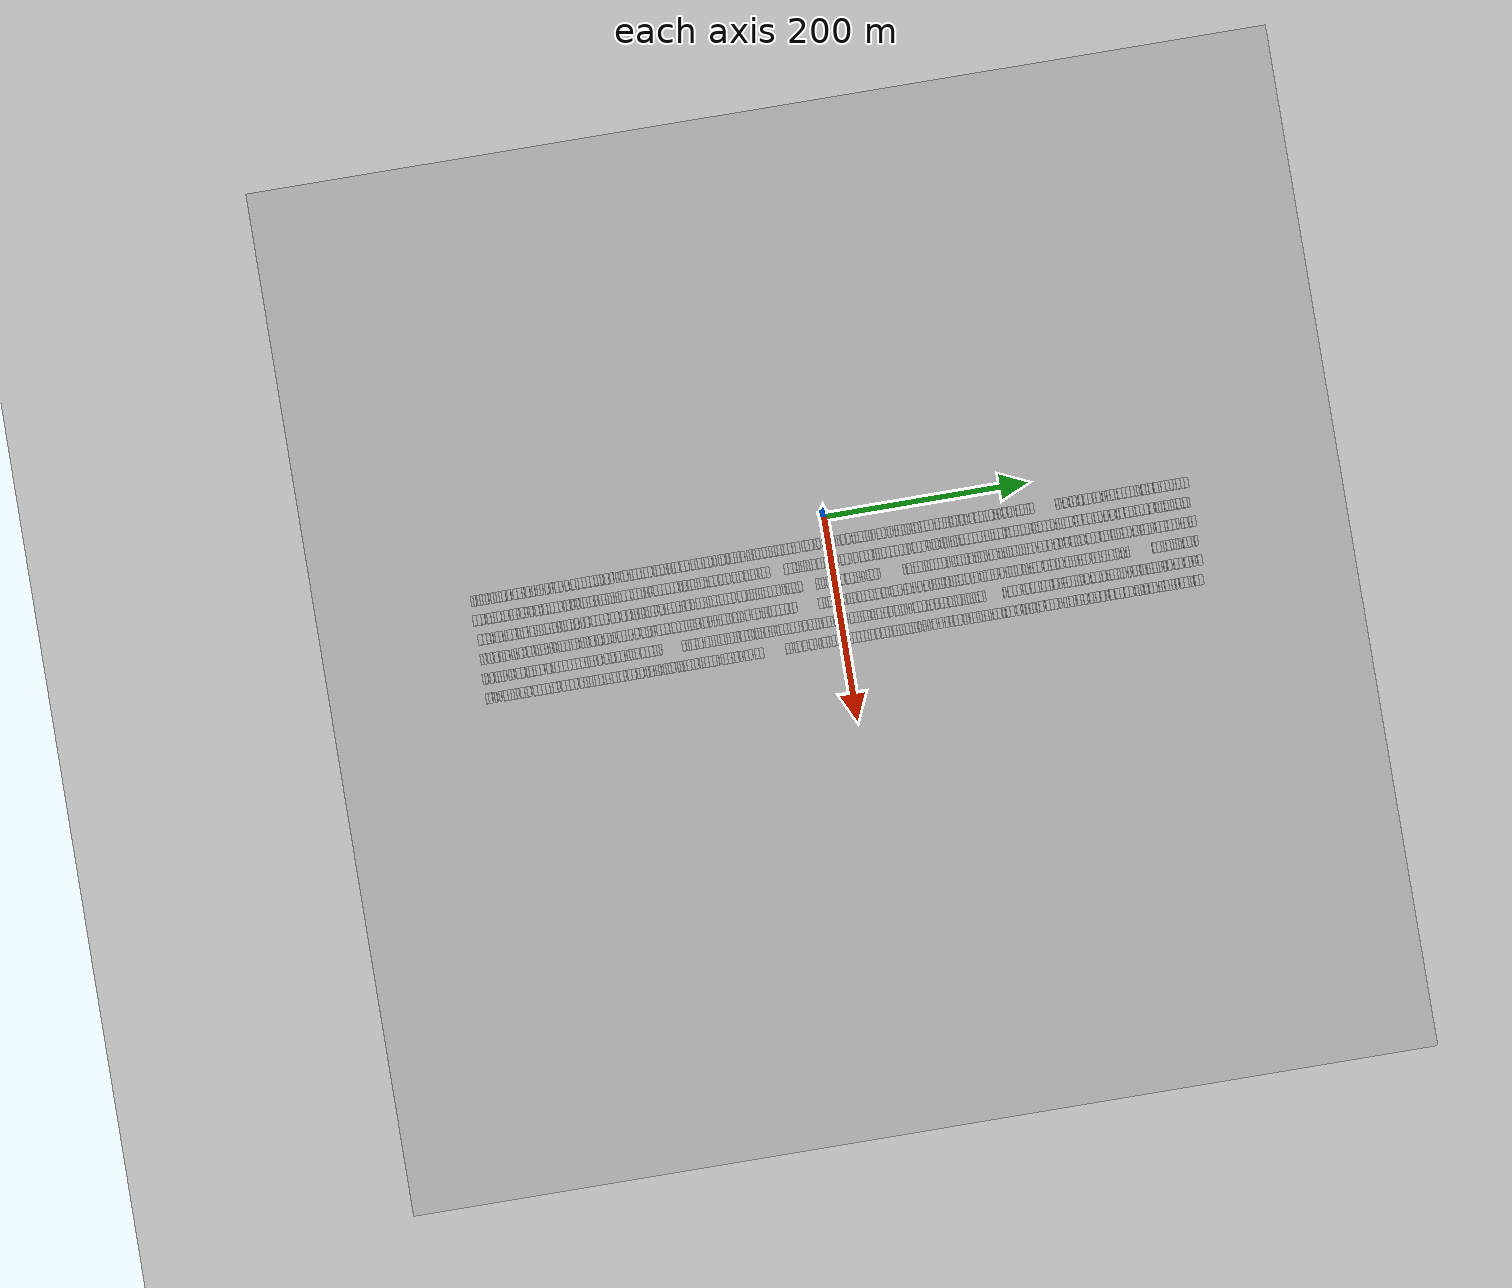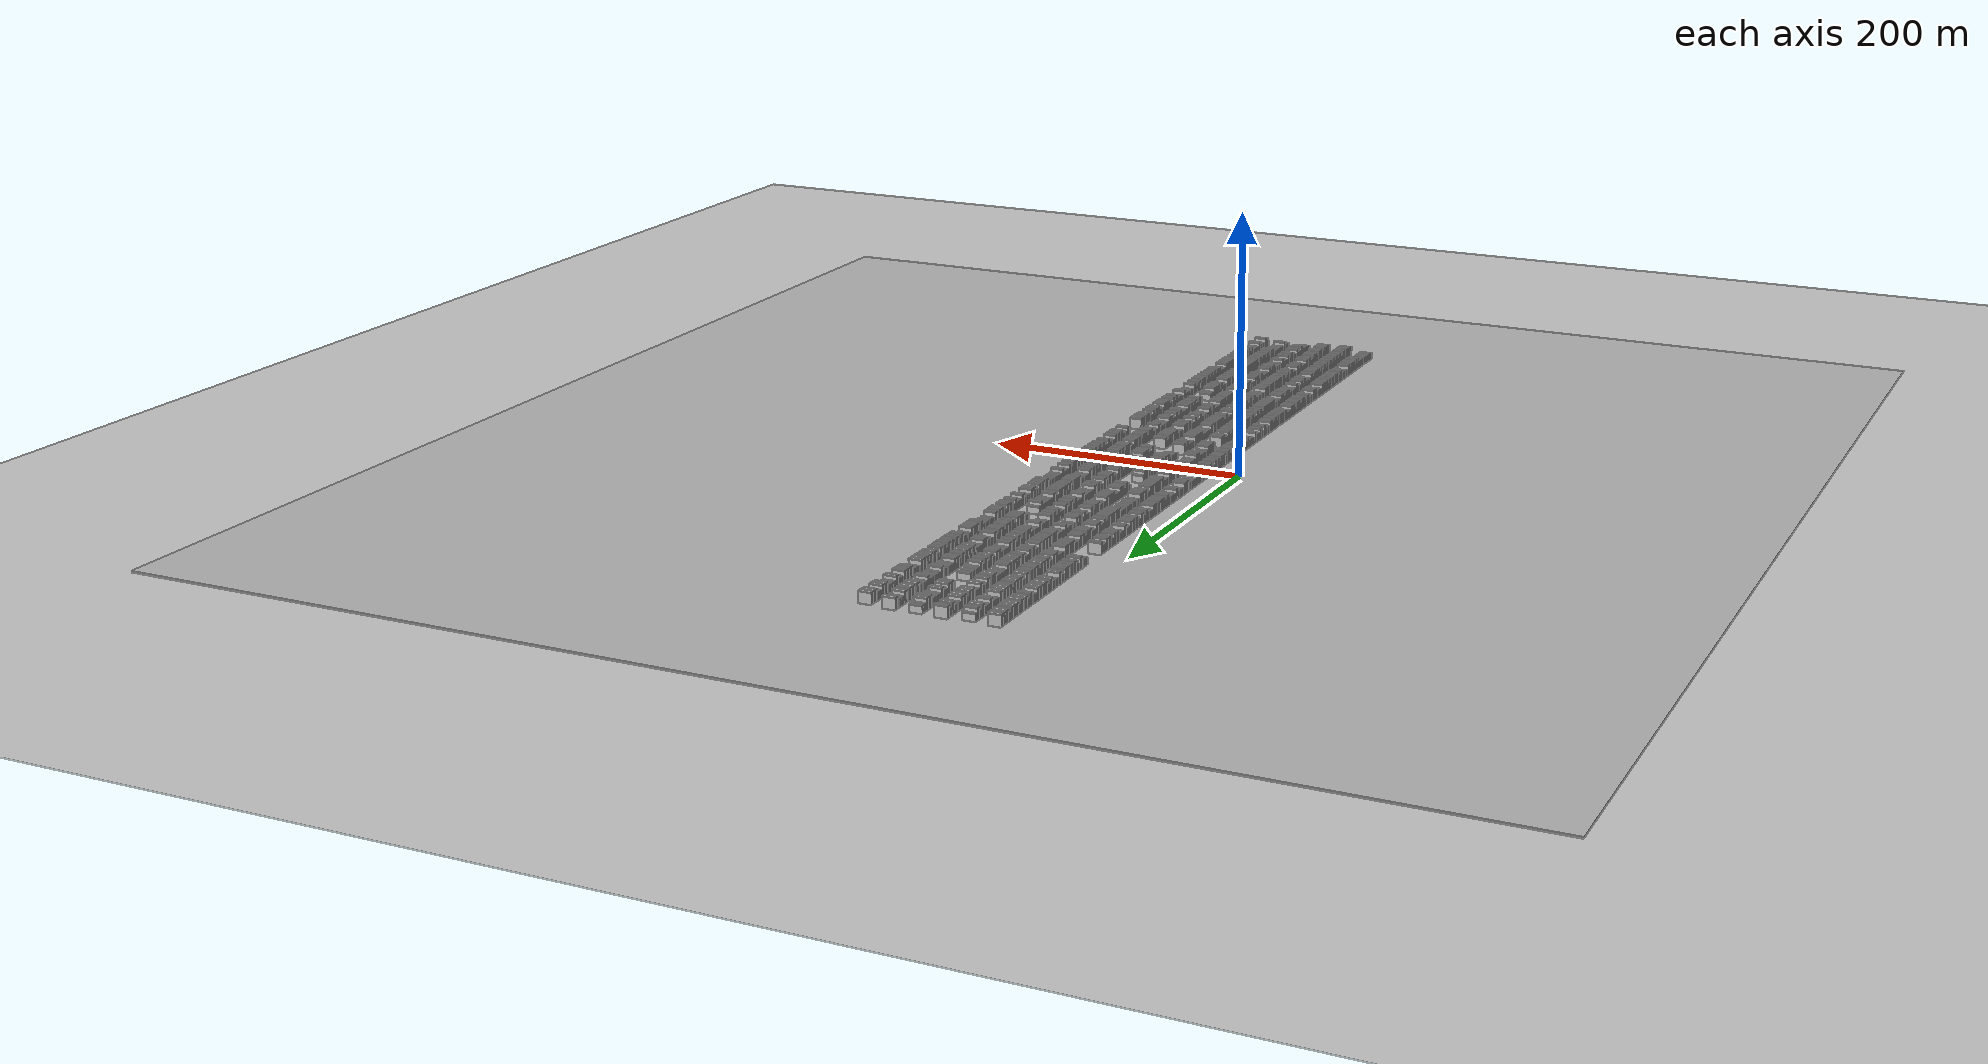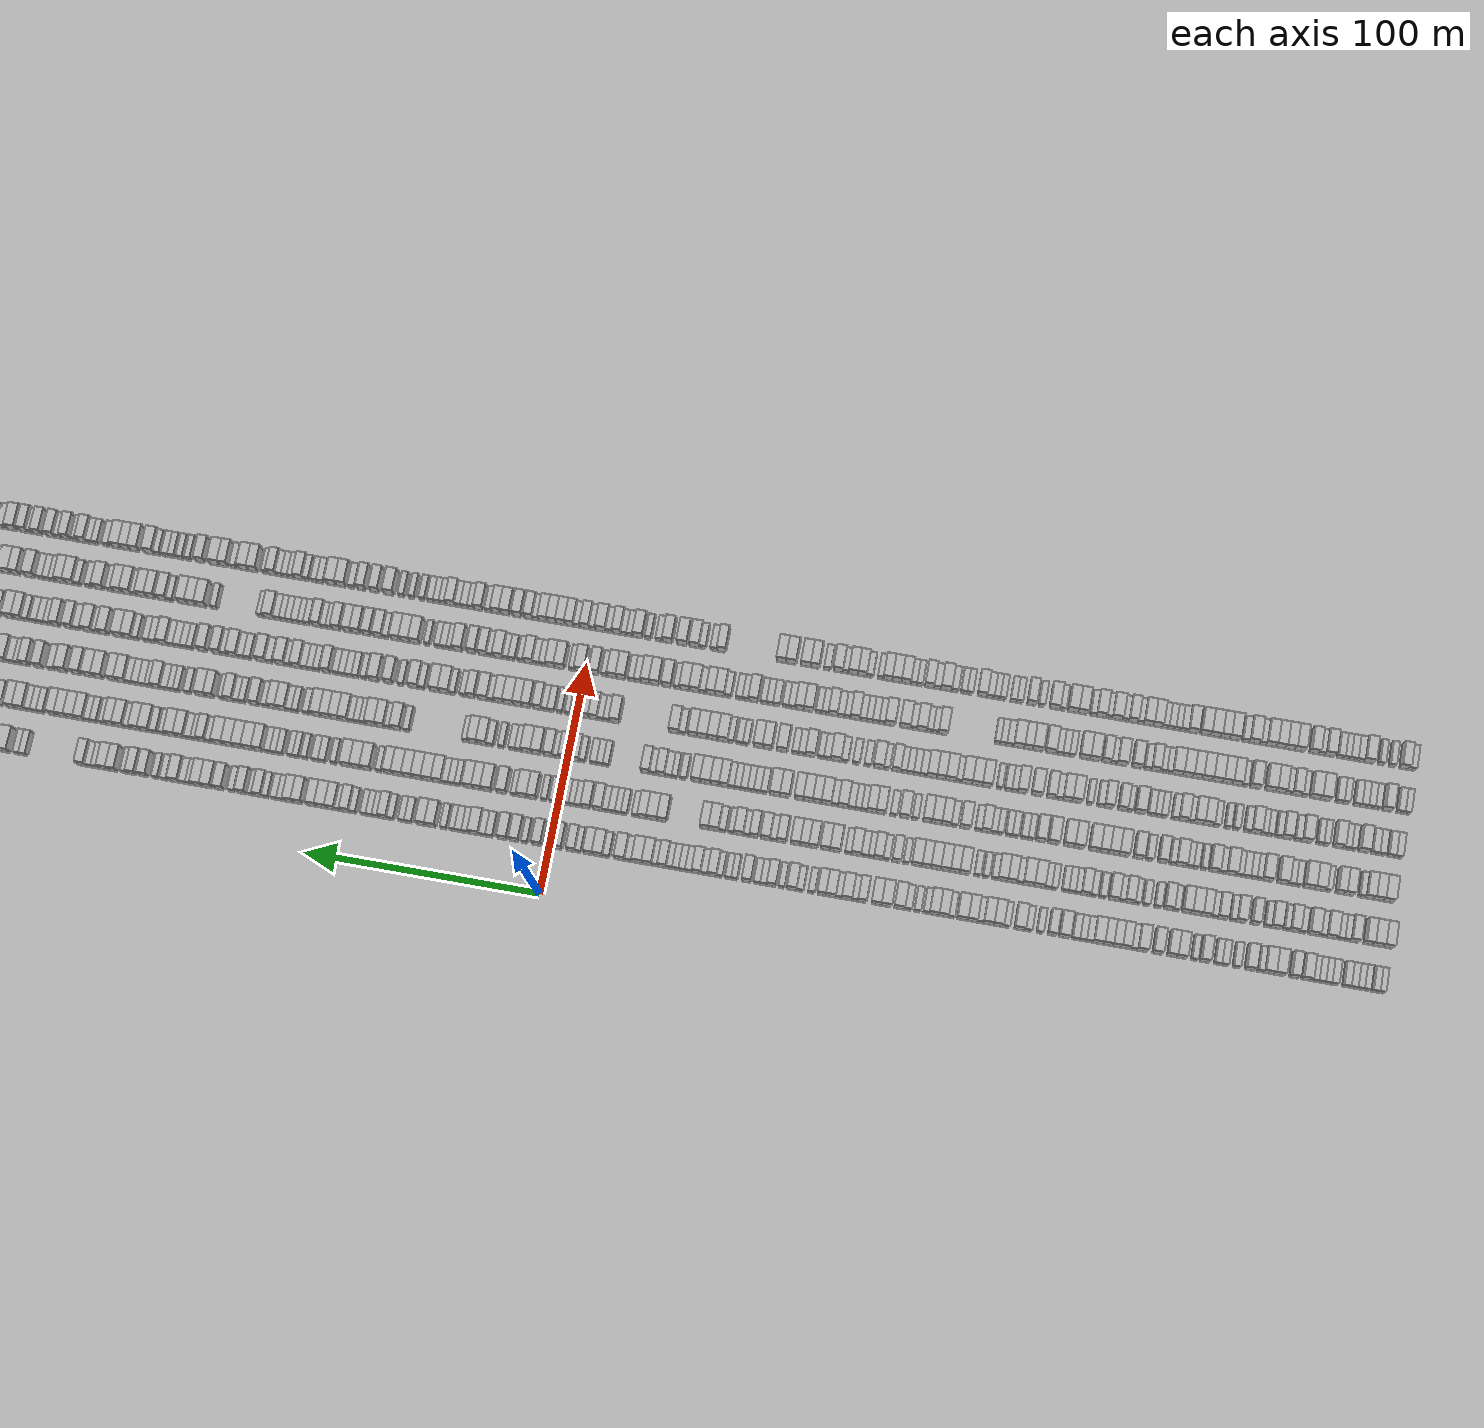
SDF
<?xml version="1.0" encoding="utf-8"?>

<sdf version="1.6">

   <world name="default">

      <gui fullscreen="0">

         <camera name="user_camera">

            <pose>-15 0 4.57585 0 0 0</pose>

            <view_controller>orbit</view_controller>

         </camera>

      </gui>

      <scene>

         <sky>

           <clouds>

             <speed>12</speed>

           </clouds>

         </sky>

         <ambient>0.4 0.4 0.4 1</ambient>

         <background>0.7 0.7 0.7 1</background>

         <shadows>1</shadows>

      </scene>

      <gravity>0 0 -9.8066</gravity>

      <magnetic_field>6e-06 2.3e-05 -4.2e-05</magnetic_field>

      <physics default="0" name="default_physics" type="ode">

         <ode>

            <solver>

               <type>quick</type>

               <iters>10</iters>

               <sor>1.0</sor>

               <use_dynamic_moi_rescaling>0</use_dynamic_moi_rescaling>

            </solver>

            <constraints>

               <cfm>0</cfm>

               <erp>0.2</erp>

               <contact_max_correcting_vel>100</contact_max_correcting_vel>

               <contact_surface_layer>0.001</contact_surface_layer>

            </constraints>

         </ode>

         <max_step_size>0.004</max_step_size>

         <real_time_factor>1</real_time_factor>

         <real_time_update_rate>250</real_time_update_rate>

      </physics>

      <light name="sun" type="directional">

         <cast_shadows>1</cast_shadows>

         <pose>0 0 10 0 0 0</pose>

         <diffuse>0.8 0.8 0.8 1</diffuse>

         <specular>0.2 0.2 0.2 1</specular>

         <attenuation>

            <range>1000</range>

            <constant>0.9</constant>

            <linear>0.01</linear>

            <quadratic>0.001</quadratic>

         </attenuation>

         <direction>-0.5 0.1 -0.9</direction>

      </light>

      <include>

         <name>ground_plane_1</name>

         <uri>model://HANNAS_ground_plane</uri>

         <pose>0 0 0  0 0 0</pose>

      </include>

      <include>

         <name>ground_plane_2</name>

         <uri>model://HANNAS_ground_plane</uri>

         <pose>100 0 0  0 0 0</pose>

      </include>

      <model name="building_1">

         <static>1</static>

         <pose frame="">25.0000 -347.7870 0 0.000000 0.000000 0.000000</pose>

         <link name="link">

            <pose frame="">0 0 3.00 0 0 0</pose>

            <collision name="collision">

               <geometry>

                  <box>

                     <size>10.0000 2.4259 6.0000</size>

                  </box>

               </geometry>

               <max_contacts>10</max_contacts>

               <surface>

                  <contact>

                     <ode/>

                  </contact>

                  <bounce/>

                  <friction>

                     <torsional>

                        <ode/>

                     </torsional>

                     <ode/>

                  </friction>

               </surface>

            </collision>

            <visual name="visual">

               <cast_shadows>0</cast_shadows>

               <geometry>

                  <box>

                     <size>10.0000 2.4259 6.0000</size>

                  </box>

               </geometry>

               <material>

                  <script>

                     <uri>model://HANNAS_wall/materials/scripts</uri>

                     <uri>model://HANNAS_wall/materials/textures</uri>

                     <name>vrc/HANNAS_wall</name>

                  </script>

               </material>

            </visual>

            <self_collide>0</self_collide>

            <enable_wind>0</enable_wind>

            <kinematic>0</kinematic>

         </link>

      </model>

      <model name="building_2">

         <static>1</static>

         <pose frame="">25.0000 -345.2109 0 0.000000 0.000000 0.000000</pose>

         <link name="link">

            <pose frame="">0 0 3.00 0 0 0</pose>

            <collision name="collision">

               <geometry>

                  <box>

                     <size>10.0000 2.7264 6.0000</size>

                  </box>

               </geometry>

               <max_contacts>10</max_contacts>

               <surface>

                  <contact>

                     <ode/>

                  </contact>

                  <bounce/>

                  <friction>

                     <torsional>

                        <ode/>

                     </torsional>

                     <ode/>

                  </friction>

               </surface>

            </collision>

            <visual name="visual">

               <cast_shadows>0</cast_shadows>

               <geometry>

                  <box>

                     <size>10.0000 2.7264 6.0000</size>

                  </box>

               </geometry>

               <material>

                  <script>

                     <uri>model://HANNAS_wall/materials/scripts</uri>

                     <uri>model://HANNAS_wall/materials/textures</uri>

                     <name>vrc/HANNAS_wall</name>

                  </script>

               </material>

            </visual>

            <self_collide>0</self_collide>

            <enable_wind>0</enable_wind>

            <kinematic>0</kinematic>

         </link>

      </model>

      <model name="building_3">

         <static>1</static>

         <pose frame="">25.0000 -341.5027 0 0.000000 0.000000 0.000000</pose>

         <link name="link">

            <pose frame="">0 0 3.00 0 0 0</pose>

            <collision name="collision">

               <geometry>

                  <box>

                     <size>10.0000 2.6899 6.0000</size>

                  </box>

               </geometry>

               <max_contacts>10</max_contacts>

               <surface>

                  <contact>

                     <ode/>

                  </contact>

                  <bounce/>

                  <friction>

                     <torsional>

                        <ode/>

                     </torsional>

                     <ode/>

                  </friction>

               </surface>

            </collision>

            <visual name="visual">

               <cast_shadows>0</cast_shadows>

               <geometry>

                  <box>

                     <size>10.0000 2.6899 6.0000</size>

                  </box>

               </geometry>

               <material>

                  <script>

                     <uri>model://HANNAS_wall/materials/scripts</uri>

                     <uri>model://HANNAS_wall/materials/textures</uri>

                     <name>vrc/HANNAS_wall</name>

                  </script>

               </material>

            </visual>

            <self_collide>0</self_collide>

            <enable_wind>0</enable_wind>

            <kinematic>0</kinematic>

         </link>

      </model>

      <model name="building_4">

         <static>1</static>

         <pose frame="">25.0000 -338.8449 0 0.000000 0.000000 0.000000</pose>

         <link name="link">

            <pose frame="">0 0 3.00 0 0 0</pose>

            <collision name="collision">

               <geometry>

                  <box>

                     <size>10.0000 2.6258 6.0000</size>

                  </box>

               </geometry>

               <max_contacts>10</max_contacts>

               <surface>

                  <contact>

                     <ode/>

                  </contact>

                  <bounce/>

                  <friction>

                     <torsional>

                        <ode/>

                     </torsional>

                     <ode/>

                  </friction>

               </surface>

            </collision>

            <visual name="visual">

               <cast_shadows>0</cast_shadows>

               <geometry>

                  <box>

                     <size>10.0000 2.6258 6.0000</size>

                  </box>

               </geometry>

               <material>

                  <script>

                     <uri>model://HANNAS_wall/materials/scripts</uri>

                     <uri>model://HANNAS_wall/materials/textures</uri>

                     <name>vrc/HANNAS_wall</name>

                  </script>

               </material>

            </visual>

            <self_collide>0</self_collide>

            <enable_wind>0</enable_wind>

            <kinematic>0</kinematic>

         </link>

      </model>

      <model name="building_5">

         <static>1</static>

         <pose frame="">25.0000 -336.1319 0 0.000000 0.000000 0.000000</pose>

         <link name="link">

            <pose frame="">0 0 3.00 0 0 0</pose>

            <collision name="collision">

               <geometry>

                  <box>

                     <size>10.0000 2.8000 6.0000</size>

                  </box>

               </geometry>

               <max_contacts>10</max_contacts>

               <surface>

                  <contact>

                     <ode/>

                  </contact>

                  <bounce/>

                  <friction>

                     <torsional>

                        <ode/>

                     </torsional>

                     <ode/>

                  </friction>

               </surface>

            </collision>

            <visual name="visual">

               <cast_shadows>0</cast_shadows>

               <geometry>

                  <box>

                     <size>10.0000 2.8000 6.0000</size>

                  </box>

               </geometry>

               <material>

                  <script>

                     <uri>model://HANNAS_wall/materials/scripts</uri>

                     <uri>model://HANNAS_wall/materials/textures</uri>

                     <name>vrc/HANNAS_wall</name>

                  </script>

               </material>

            </visual>

            <self_collide>0</self_collide>

            <enable_wind>0</enable_wind>

            <kinematic>0</kinematic>

         </link>

      </model>

      <model name="building_6">

         <static>1</static>

         <pose frame="">25.0000 -333.2328 0 0.000000 0.000000 0.000000</pose>

         <link name="link">

            <pose frame="">0 0 3.00 0 0 0</pose>

            <collision name="collision">

               <geometry>

                  <box>

                     <size>10.0000 2.9983 6.0000</size>

                  </box>

               </geometry>

               <max_contacts>10</max_contacts>

               <surface>

                  <contact>

                     <ode/>

                  </contact>

                  <bounce/>

                  <friction>

                     <torsional>

                        <ode/>

                     </torsional>

                     <ode/>

                  </friction>

               </surface>

            </collision>

            <visual name="visual">

               <cast_shadows>0</cast_shadows>

               <geometry>

                  <box>

                     <size>10.0000 2.9983 6.0000</size>

                  </box>

               </geometry>

               <material>

                  <script>

                     <uri>model://HANNAS_wall/materials/scripts</uri>

                     <uri>model://HANNAS_wall/materials/textures</uri>

                     <name>vrc/HANNAS_wall</name>

                  </script>

               </material>

            </visual>

            <self_collide>0</self_collide>

            <enable_wind>0</enable_wind>

            <kinematic>0</kinematic>

         </link>

      </model>

      <model name="building_7">

         <static>1</static>

         <pose frame="">25.0000 -328.2507 0 0.000000 0.000000 0.000000</pose>

         <link name="link">

            <pose frame="">0 0 3.00 0 0 0</pose>

            <collision name="collision">

               <geometry>

                  <box>

                     <size>10.0000 2.9659 6.0000</size>

                  </box>

               </geometry>

               <max_contacts>10</max_contacts>

               <surface>

                  <contact>

                     <ode/>

                  </contact>

                  <bounce/>

                  <friction>

                     <torsional>

                        <ode/>

                     </torsional>

                     <ode/>

                  </friction>

               </surface>

            </collision>

            <visual name="visual">

               <cast_shadows>0</cast_shadows>

               <geometry>

                  <box>

                     <size>10.0000 2.9659 6.0000</size>

                  </box>

               </geometry>

               <material>

                  <script>

                     <uri>model://HANNAS_wall/materials/scripts</uri>

                     <uri>model://HANNAS_wall/materials/textures</uri>

                     <name>vrc/HANNAS_wall</name>

                  </script>

               </material>

            </visual>

            <self_collide>0</self_collide>

            <enable_wind>0</enable_wind>

            <kinematic>0</kinematic>

         </link>

      </model>

      <model name="building_8">

         <static>1</static>

         <pose frame="">25.0000 -325.4648 0 0.000000 0.000000 0.000000</pose>

         <link name="link">

            <pose frame="">0 0 3.00 0 0 0</pose>

            <collision name="collision">

               <geometry>

                  <box>

                     <size>10.0000 2.6061 6.0000</size>

                  </box>

               </geometry>

               <max_contacts>10</max_contacts>

               <surface>

                  <contact>

                     <ode/>

                  </contact>

                  <bounce/>

                  <friction>

                     <torsional>

                        <ode/>

                     </torsional>

                     <ode/>

                  </friction>

               </surface>

            </collision>

            <visual name="visual">

               <cast_shadows>0</cast_shadows>

               <geometry>

                  <box>

                     <size>10.0000 2.6061 6.0000</size>

                  </box>

               </geometry>

               <material>

                  <script>

                     <uri>model://HANNAS_wall/materials/scripts</uri>

                     <uri>model://HANNAS_wall/materials/textures</uri>

                     <name>vrc/HANNAS_wall</name>

                  </script>

               </material>

            </visual>

            <self_collide>0</self_collide>

            <enable_wind>0</enable_wind>

            <kinematic>0</kinematic>

         </link>

      </model>

      <model name="building_9">

         <static>1</static>

         <pose frame="">25.0000 -322.8013 0 0.000000 0.000000 0.000000</pose>

         <link name="link">

            <pose frame="">0 0 3.00 0 0 0</pose>

            <collision name="collision">

               <geometry>

                  <box>

                     <size>10.0000 2.7209 6.0000</size>

                  </box>

               </geometry>

               <max_contacts>10</max_contacts>

               <surface>

                  <contact>

                     <ode/>

                  </contact>

                  <bounce/>

                  <friction>

                     <torsional>

                        <ode/>

                     </torsional>

                     <ode/>

                  </friction>

               </surface>

            </collision>

            <visual name="visual">

               <cast_shadows>0</cast_shadows>

               <geometry>

                  <box>

                     <size>10.0000 2.7209 6.0000</size>

                  </box>

               </geometry>

               <material>

                  <script>

                     <uri>model://HANNAS_wall/materials/scripts</uri>

                     <uri>model://HANNAS_wall/materials/textures</uri>

                     <name>vrc/HANNAS_wall</name>

                  </script>

               </material>

            </visual>

            <self_collide>0</self_collide>

            <enable_wind>0</enable_wind>

            <kinematic>0</kinematic>

         </link>

      </model>

      <model name="building_10">

         <static>1</static>

         <pose frame="">25.0000 -320.0898 0 0.000000 0.000000 0.000000</pose>

         <link name="link">

            <pose frame="">0 0 3.00 0 0 0</pose>

            <collision name="collision">

               <geometry>

                  <box>

                     <size>10.0000 2.7021 6.0000</size>

                  </box>

               </geometry>

               <max_contacts>10</max_contacts>

               <surface>

                  <contact>

                     <ode/>

                  </contact>

                  <bounce/>

                  <friction>

                     <torsional>

                        <ode/>

                     </torsional>

                     <ode/>

                  </friction>

               </surface>

            </collision>

            <visual name="visual">

               <cast_shadows>0</cast_shadows>

               <geometry>

                  <box>

                     <size>10.0000 2.7021 6.0000</size>

                  </box>

               </geometry>

               <material>

                  <script>

                     <uri>model://HANNAS_wall/materials/scripts</uri>

                     <uri>model://HANNAS_wall/materials/textures</uri>

                     <name>vrc/HANNAS_wall</name>

                  </script>

               </material>

            </visual>

            <self_collide>0</self_collide>

            <enable_wind>0</enable_wind>

            <kinematic>0</kinematic>

         </link>

      </model>

      <model name="building_11">

         <static>1</static>

         <pose frame="">25.0000 -316.7248 0 0.000000 0.000000 0.000000</pose>

         <link name="link">

            <pose frame="">0 0 4.50 0 0 0</pose>

            <collision name="collision">

               <geometry>

                  <box>

                     <size>10.0000 4.0278 9.0000</size>

                  </box>

               </geometry>

               <max_contacts>10</max_contacts>

               <surface>

                  <contact>

                     <ode/>

                  </contact>

                  <bounce/>

                  <friction>

                     <torsional>

                        <ode/>

                     </torsional>

                     <ode/>

                  </friction>

               </surface>

            </collision>

            <visual name="visual">

               <cast_shadows>0</cast_shadows>

               <geometry>

                  <box>

                     <size>10.0000 4.0278 9.0000</size>

                  </box>

               </geometry>

               <material>

                  <script>

                     <uri>model://HANNAS_wall/materials/scripts</uri>

                     <uri>model://HANNAS_wall/materials/textures</uri>

                     <name>vrc/HANNAS_wall</name>

                  </script>

               </material>

            </visual>

            <self_collide>0</self_collide>

            <enable_wind>0</enable_wind>

            <kinematic>0</kinematic>

         </link>

      </model>

      <model name="building_12">

         <static>1</static>

         <pose frame="">25.0000 -311.7622 0 0.000000 0.000000 0.000000</pose>

         <link name="link">

            <pose frame="">0 0 4.50 0 0 0</pose>

            <collision name="collision">

               <geometry>

                  <box>

                     <size>10.0000 3.8976 9.0000</size>

                  </box>

               </geometry>

               <max_contacts>10</max_contacts>

               <surface>

                  <contact>

                     <ode/>

                  </contact>

                  <bounce/>

                  <friction>

                     <torsional>

                        <ode/>

                     </torsional>

                     <ode/>

                  </friction>

               </surface>

            </collision>

            <visual name="visual">

               <cast_shadows>0</cast_shadows>

               <geometry>

                  <box>

                     <size>10.0000 3.8976 9.0000</size>

                  </box>

               </geometry>

               <material>

                  <script>

                     <uri>model://HANNAS_wall/materials/scripts</uri>

                     <uri>model://HANNAS_wall/materials/textures</uri>

                     <name>vrc/HANNAS_wall</name>

                  </script>

               </material>

            </visual>

            <self_collide>0</self_collide>

            <enable_wind>0</enable_wind>

            <kinematic>0</kinematic>

         </link>

      </model>

      <model name="building_13">

         <static>1</static>

         <pose frame="">25.0000 -305.6335 0 0.000000 0.000000 0.000000</pose>

         <link name="link">

            <pose frame="">0 0 4.50 0 0 0</pose>

            <collision name="collision">

               <geometry>

                  <box>

                     <size>10.0000 4.3597 9.0000</size>

                  </box>

               </geometry>

               <max_contacts>10</max_contacts>

               <surface>

                  <contact>

                     <ode/>

                  </contact>

                  <bounce/>

                  <friction>

                     <torsional>

                        <ode/>

                     </torsional>

                     <ode/>

                  </friction>

               </surface>

            </collision>

            <visual name="visual">

               <cast_shadows>0</cast_shadows>

               <geometry>

                  <box>

                     <size>10.0000 4.3597 9.0000</size>

                  </box>

               </geometry>

               <material>

                  <script>

                     <uri>model://HANNAS_wall/materials/scripts</uri>

                     <uri>model://HANNAS_wall/materials/textures</uri>

                     <name>vrc/HANNAS_wall</name>

                  </script>

               </material>

            </visual>

            <self_collide>0</self_collide>

            <enable_wind>0</enable_wind>

            <kinematic>0</kinematic>

         </link>

      </model>

      <model name="building_14">

         <static>1</static>

         <pose frame="">25.0000 -301.2562 0 0.000000 0.000000 0.000000</pose>

         <link name="link">

            <pose frame="">0 0 4.50 0 0 0</pose>

            <collision name="collision">

               <geometry>

                  <box>

                     <size>10.0000 4.3950 9.0000</size>

                  </box>

               </geometry>

               <max_contacts>10</max_contacts>

               <surface>

                  <contact>

                     <ode/>

                  </contact>

                  <bounce/>

                  <friction>

                     <torsional>

                        <ode/>

                     </torsional>

                     <ode/>

                  </friction>

               </surface>

            </collision>

            <visual name="visual">

               <cast_shadows>0</cast_shadows>

               <geometry>

                  <box>

                     <size>10.0000 4.3950 9.0000</size>

                  </box>

               </geometry>

               <material>

                  <script>

                     <uri>model://HANNAS_wall/materials/scripts</uri>

                     <uri>model://HANNAS_wall/materials/textures</uri>

                     <name>vrc/HANNAS_wall</name>

                  </script>

               </material>

            </visual>

            <self_collide>0</self_collide>

            <enable_wind>0</enable_wind>

            <kinematic>0</kinematic>

         </link>

      </model>

      <model name="building_15">

         <static>1</static>

         <pose frame="">25.0000 -297.8179 0 0.000000 0.000000 0.000000</pose>

         <link name="link">

            <pose frame="">0 0 3.00 0 0 0</pose>

            <collision name="collision">

               <geometry>

                  <box>

                     <size>10.0000 2.4814 6.0000</size>

                  </box>

               </geometry>

               <max_contacts>10</max_contacts>

               <surface>

                  <contact>

                     <ode/>

                  </contact>

                  <bounce/>

                  <friction>

                     <torsional>

                        <ode/>

                     </torsional>

                     <ode/>

                  </friction>

               </surface>

            </collision>

            <visual name="visual">

               <cast_shadows>0</cast_shadows>

               <geometry>

                  <box>

                     <size>10.0000 2.4814 6.0000</size>

                  </box>

               </geometry>

               <material>

                  <script>

                     <uri>model://HANNAS_wall/materials/scripts</uri>

                     <uri>model://HANNAS_wall/materials/textures</uri>

                     <name>vrc/HANNAS_wall</name>

                  </script>

               </material>

            </visual>

            <self_collide>0</self_collide>

            <enable_wind>0</enable_wind>

            <kinematic>0</kinematic>

         </link>

      </model>

      <model name="building_16">

         <static>1</static>

         <pose frame="">25.0000 -293.4180 0 0.000000 0.000000 0.000000</pose>

         <link name="link">

            <pose frame="">0 0 4.50 0 0 0</pose>

            <collision name="collision">

               <geometry>

                  <box>

                     <size>10.0000 4.3184 9.0000</size>

                  </box>

               </geometry>

               <max_contacts>10</max_contacts>

               <surface>

                  <contact>

                     <ode/>

                  </contact>

                  <bounce/>

                  <friction>

                     <torsional>

                        <ode/>

                     </torsional>

                     <ode/>

                  </friction>

               </surface>

            </collision>

            <visual name="visual">

               <cast_shadows>0</cast_shadows>

               <geometry>

                  <box>

                     <size>10.0000 4.3184 9.0000</size>

                  </box>

               </geometry>

               <material>

                  <script>

                     <uri>model://HANNAS_wall/materials/scripts</uri>

                     <uri>model://HANNAS_wall/materials/textures</uri>

                     <name>vrc/HANNAS_wall</name>

                  </script>

               </material>

            </visual>

            <self_collide>0</self_collide>

            <enable_wind>0</enable_wind>

            <kinematic>0</kinematic>

         </link>

      </model>

      <model name="building_17">

         <static>1</static>

         <pose frame="">25.0000 -287.7597 0 0.000000 0.000000 0.000000</pose>

         <link name="link">

            <pose frame="">0 0 3.00 0 0 0</pose>

            <collision name="collision">

               <geometry>

                  <box>

                     <size>10.0000 2.9983 6.0000</size>

                  </box>

               </geometry>

               <max_contacts>10</max_contacts>

               <surface>

                  <contact>

                     <ode/>

                  </contact>

                  <bounce/>

                  <friction>

                     <torsional>

                        <ode/>

                     </torsional>

                     <ode/>

                  </friction>

               </surface>

            </collision>

            <visual name="visual">

               <cast_shadows>0</cast_shadows>

               <geometry>

                  <box>

                     <size>10.0000 2.9983 6.0000</size>

                  </box>

               </geometry>

               <material>

                  <script>

                     <uri>model://HANNAS_wall/materials/scripts</uri>

                     <uri>model://HANNAS_wall/materials/textures</uri>

                     <name>vrc/HANNAS_wall</name>

                  </script>

               </material>

            </visual>

            <self_collide>0</self_collide>

            <enable_wind>0</enable_wind>

            <kinematic>0</kinematic>

         </link>

      </model>

      <model name="building_18">

         <static>1</static>

         <pose frame="">25.0000 -282.8046 0 0.000000 0.000000 0.000000</pose>

         <link name="link">

            <pose frame="">0 0 3.00 0 0 0</pose>

            <collision name="collision">

               <geometry>

                  <box>

                     <size>10.0000 2.9120 6.0000</size>

                  </box>

               </geometry>

               <max_contacts>10</max_contacts>

               <surface>

                  <contact>

                     <ode/>

                  </contact>

                  <bounce/>

                  <friction>

                     <torsional>

                        <ode/>

                     </torsional>

                     <ode/>

                  </friction>

               </surface>

            </collision>

            <visual name="visual">

               <cast_shadows>0</cast_shadows>

               <geometry>

                  <box>

                     <size>10.0000 2.9120 6.0000</size>

                  </box>

               </geometry>

               <material>

                  <script>

                     <uri>model://HANNAS_wall/materials/scripts</uri>

                     <uri>model://HANNAS_wall/materials/textures</uri>

                     <name>vrc/HANNAS_wall</name>

                  </script>

               </material>

            </visual>

            <self_collide>0</self_collide>

            <enable_wind>0</enable_wind>

            <kinematic>0</kinematic>

         </link>

      </model>

      <model name="building_19">

         <static>1</static>

         <pose frame="">25.0000 -279.9776 0 0.000000 0.000000 0.000000</pose>

         <link name="link">

            <pose frame="">0 0 3.00 0 0 0</pose>

            <collision name="collision">

               <geometry>

                  <box>

                     <size>10.0000 2.7420 6.0000</size>

                  </box>

               </geometry>

               <max_contacts>10</max_contacts>

               <surface>

                  <contact>

                     <ode/>

                  </contact>

                  <bounce/>

                  <friction>

                     <torsional>

                        <ode/>

                     </torsional>

                     <ode/>

                  </friction>

               </surface>

            </collision>

            <visual name="visual">

               <cast_shadows>0</cast_shadows>

               <geometry>

                  <box>

                     <size>10.0000 2.7420 6.0000</size>

                  </box>

               </geometry>

               <material>

                  <script>

                     <uri>model://HANNAS_wall/materials/scripts</uri>

                     <uri>model://HANNAS_wall/materials/textures</uri>

                     <name>vrc/HANNAS_wall</name>

                  </script>

               </material>

            </visual>

            <self_collide>0</self_collide>

            <enable_wind>0</enable_wind>

            <kinematic>0</kinematic>

         </link>

      </model>

      <model name="building_20">

         <static>1</static>

         <pose frame="">25.0000 -274.6007 0 0.000000 0.000000 0.000000</pose>

         <link name="link">

            <pose frame="">0 0 4.50 0 0 0</pose>

            <collision name="collision">

               <geometry>

                  <box>

                     <size>10.0000 4.0118 9.0000</size>

                  </box>

               </geometry>

               <max_contacts>10</max_contacts>

               <surface>

                  <contact>

                     <ode/>

                  </contact>

                  <bounce/>

                  <friction>

                     <torsional>

                        <ode/>

                     </torsional>

                     <ode/>

                  </friction>

               </surface>

            </collision>

            <visual name="visual">

               <cast_shadows>0</cast_shadows>

               <geometry>

                  <box>

                     <size>10.0000 4.0118 9.0000</size>

                  </box>

               </geometry>

               <material>

                  <script>

                     <uri>model://HANNAS_wall/materials/scripts</uri>

                     <uri>model://HANNAS_wall/materials/textures</uri>

                     <name>vrc/HANNAS_wall</name>

                  </script>

               </material>

            </visual>

            <self_collide>0</self_collide>

            <enable_wind>0</enable_wind>

            <kinematic>0</kinematic>

         </link>

      </model>

      <model name="building_21">

         <static>1</static>

         <pose frame="">25.0000 -270.2955 0 0.000000 0.000000 0.000000</pose>

         <link name="link">

            <pose frame="">0 0 3.00 0 0 0</pose>

            <collision name="collision">

               <geometry>

                  <box>

                     <size>10.0000 2.5986 6.0000</size>

                  </box>

               </geometry>

               <max_contacts>10</max_contacts>

               <surface>

                  <contact>

                     <ode/>

                  </contact>

                  <bounce/>

                  <friction>

                     <torsional>

                        <ode/>

                     </torsional>

                     <ode/>

                  </friction>

               </surface>

            </collision>

            <visual name="visual">

               <cast_shadows>0</cast_shadows>

               <geometry>

                  <box>

                     <size>10.0000 2.5986 6.0000</size>

                  </box>

               </geometry>

               <material>

                  <script>

                     <uri>model://HANNAS_wall/materials/scripts</uri>

                     <uri>model://HANNAS_wall/materials/textures</uri>

                     <name>vrc/HANNAS_wall</name>

                  </script>

               </material>

            </visual>

            <self_collide>0</self_collide>

            <enable_wind>0</enable_wind>

            <kinematic>0</kinematic>

         </link>

      </model>

      <model name="building_22">

         <static>1</static>

         <pose frame="">25.0000 -264.9342 0 0.000000 0.000000 0.000000</pose>

         <link name="link">

            <pose frame="">0 0 4.50 0 0 0</pose>

            <collision name="collision">

               <geometry>

                  <box>

                     <size>10.0000 4.1242 9.0000</size>

                  </box>

               </geometry>

               <max_contacts>10</max_contacts>

               <surface>

                  <contact>

                     <ode/>

                  </contact>

                  <bounce/>

                  <friction>

                     <torsional>

                        <ode/>

                     </torsional>

                     <ode/>

                  </friction>

               </surface>

            </collision>

            <visual name="visual">

               <cast_shadows>0</cast_shadows>

               <geometry>

                  <box>

                     <size>10.0000 4.1242 9.0000</size>

                  </box>

               </geometry>

               <material>

                  <script>

                     <uri>model://HANNAS_wall/materials/scripts</uri>

                     <uri>model://HANNAS_wall/materials/textures</uri>

                     <name>vrc/HANNAS_wall</name>

                  </script>

               </material>

            </visual>

            <self_collide>0</self_collide>

            <enable_wind>0</enable_wind>

            <kinematic>0</kinematic>

         </link>

      </model>

      <model name="building_23">

         <static>1</static>

         <pose frame="">25.0000 -260.9729 0 0.000000 0.000000 0.000000</pose>

         <link name="link">

            <pose frame="">0 0 4.50 0 0 0</pose>

            <collision name="collision">

               <geometry>

                  <box>

                     <size>10.0000 3.7984 9.0000</size>

                  </box>

               </geometry>

               <max_contacts>10</max_contacts>

               <surface>

                  <contact>

                     <ode/>

                  </contact>

                  <bounce/>

                  <friction>

                     <torsional>

                        <ode/>

                     </torsional>

                     <ode/>

                  </friction>

               </surface>

            </collision>

            <visual name="visual">

               <cast_shadows>0</cast_shadows>

               <geometry>

                  <box>

                     <size>10.0000 3.7984 9.0000</size>

                  </box>

               </geometry>

               <material>

                  <script>

                     <uri>model://HANNAS_wall/materials/scripts</uri>

                     <uri>model://HANNAS_wall/materials/textures</uri>

                     <name>vrc/HANNAS_wall</name>

                  </script>

               </material>

            </visual>

            <self_collide>0</self_collide>

            <enable_wind>0</enable_wind>

            <kinematic>0</kinematic>

         </link>

      </model>

      <model name="building_24">

         <static>1</static>

         <pose frame="">25.0000 -255.0249 0 0.000000 0.000000 0.000000</pose>

         <link name="link">

            <pose frame="">0 0 4.50 0 0 0</pose>

            <collision name="collision">

               <geometry>

                  <box>

                     <size>10.0000 4.0975 9.0000</size>

                  </box>

               </geometry>

               <max_contacts>10</max_contacts>

               <surface>

                  <contact>

                     <ode/>

                  </contact>

                  <bounce/>

                  <friction>

                     <torsional>

                        <ode/>

                     </torsional>

                     <ode/>

                  </friction>

               </surface>

            </collision>

            <visual name="visual">

               <cast_shadows>0</cast_shadows>

               <geometry>

                  <box>

                     <size>10.0000 4.0975 9.0000</size>

                  </box>

               </geometry>

               <material>

                  <script>

                     <uri>model://HANNAS_wall/materials/scripts</uri>

                     <uri>model://HANNAS_wall/materials/textures</uri>

                     <name>vrc/HANNAS_wall</name>

                  </script>

               </material>

            </visual>

            <self_collide>0</self_collide>

            <enable_wind>0</enable_wind>

            <kinematic>0</kinematic>

         </link>

      </model>

      <model name="building_25">

         <static>1</static>

         <pose frame="">25.0000 -248.8032 0 0.000000 0.000000 0.000000</pose>

         <link name="link">

            <pose frame="">0 0 4.50 0 0 0</pose>

            <collision name="collision">

               <geometry>

                  <box>

                     <size>10.0000 4.3460 9.0000</size>

                  </box>

               </geometry>

               <max_contacts>10</max_contacts>

               <surface>

                  <contact>

                     <ode/>

                  </contact>

                  <bounce/>

                  <friction>

                     <torsional>

                        <ode/>

                     </torsional>

                     <ode/>

                  </friction>

               </surface>

            </collision>

            <visual name="visual">

               <cast_shadows>0</cast_shadows>

               <geometry>

                  <box>

                     <size>10.0000 4.3460 9.0000</size>

                  </box>

               </geometry>

               <material>

                  <script>

                     <uri>model://HANNAS_wall/materials/scripts</uri>

                     <uri>model://HANNAS_wall/materials/textures</uri>

                     <name>vrc/HANNAS_wall</name>

                  </script>

               </material>

            </visual>

            <self_collide>0</self_collide>

            <enable_wind>0</enable_wind>

            <kinematic>0</kinematic>

         </link>

      </model>

      <model name="building_26">

         <static>1</static>

         <pose frame="">25.0000 -245.2129 0 0.000000 0.000000 0.000000</pose>

         <link name="link">

            <pose frame="">0 0 3.00 0 0 0</pose>

            <collision name="collision">

               <geometry>

                  <box>

                     <size>10.0000 2.8346 6.0000</size>

                  </box>

               </geometry>

               <max_contacts>10</max_contacts>

               <surface>

                  <contact>

                     <ode/>

                  </contact>

                  <bounce/>

                  <friction>

                     <torsional>

                        <ode/>

                     </torsional>

                     <ode/>

                  </friction>

               </surface>

            </collision>

            <visual name="visual">

               <cast_shadows>0</cast_shadows>

               <geometry>

                  <box>

                     <size>10.0000 2.8346 6.0000</size>

                  </box>

               </geometry>

               <material>

                  <script>

                     <uri>model://HANNAS_wall/materials/scripts</uri>

                     <uri>model://HANNAS_wall/materials/textures</uri>

                     <name>vrc/HANNAS_wall</name>

                  </script>

               </material>

            </visual>

            <self_collide>0</self_collide>

            <enable_wind>0</enable_wind>

            <kinematic>0</kinematic>

         </link>

      </model>

      <model name="building_27">

         <static>1</static>

         <pose frame="">25.0000 -241.8907 0 0.000000 0.000000 0.000000</pose>

         <link name="link">

            <pose frame="">0 0 4.50 0 0 0</pose>

            <collision name="collision">

               <geometry>

                  <box>

                     <size>10.0000 3.8098 9.0000</size>

                  </box>

               </geometry>

               <max_contacts>10</max_contacts>

               <surface>

                  <contact>

                     <ode/>

                  </contact>

                  <bounce/>

                  <friction>

                     <torsional>

                        <ode/>

                     </torsional>

                     <ode/>

                  </friction>

               </surface>

            </collision>

            <visual name="visual">

               <cast_shadows>0</cast_shadows>

               <geometry>

                  <box>

                     <size>10.0000 3.8098 9.0000</size>

                  </box>

               </geometry>

               <material>

                  <script>

                     <uri>model://HANNAS_wall/materials/scripts</uri>

                     <uri>model://HANNAS_wall/materials/textures</uri>

                     <name>vrc/HANNAS_wall</name>

                  </script>

               </material>

            </visual>

            <self_collide>0</self_collide>

            <enable_wind>0</enable_wind>

            <kinematic>0</kinematic>

         </link>

      </model>

      <model name="building_28">

         <static>1</static>

         <pose frame="">25.0000 -238.1412 0 0.000000 0.000000 0.000000</pose>

         <link name="link">

            <pose frame="">0 0 4.50 0 0 0</pose>

            <collision name="collision">

               <geometry>

                  <box>

                     <size>10.0000 3.6891 9.0000</size>

                  </box>

               </geometry>

               <max_contacts>10</max_contacts>

               <surface>

                  <contact>

                     <ode/>

                  </contact>

                  <bounce/>

                  <friction>

                     <torsional>

                        <ode/>

                     </torsional>

                     <ode/>

                  </friction>

               </surface>

            </collision>

            <visual name="visual">

               <cast_shadows>0</cast_shadows>

               <geometry>

                  <box>

                     <size>10.0000 3.6891 9.0000</size>

                  </box>

               </geometry>

               <material>

                  <script>

                     <uri>model://HANNAS_wall/materials/scripts</uri>

                     <uri>model://HANNAS_wall/materials/textures</uri>

                     <name>vrc/HANNAS_wall</name>

                  </script>

               </material>

            </visual>

            <self_collide>0</self_collide>

            <enable_wind>0</enable_wind>

            <kinematic>0</kinematic>

         </link>

      </model>

      <model name="building_29">

         <static>1</static>

         <pose frame="">25.0000 -234.4674 0 0.000000 0.000000 0.000000</pose>

         <link name="link">

            <pose frame="">0 0 4.50 0 0 0</pose>

            <collision name="collision">

               <geometry>

                  <box>

                     <size>10.0000 3.6585 9.0000</size>

                  </box>

               </geometry>

               <max_contacts>10</max_contacts>

               <surface>

                  <contact>

                     <ode/>

                  </contact>

                  <bounce/>

                  <friction>

                     <torsional>

                        <ode/>

                     </torsional>

                     <ode/>

                  </friction>

               </surface>

            </collision>

            <visual name="visual">

               <cast_shadows>0</cast_shadows>

               <geometry>

                  <box>

                     <size>10.0000 3.6585 9.0000</size>

                  </box>

               </geometry>

               <material>

                  <script>

                     <uri>model://HANNAS_wall/materials/scripts</uri>

                     <uri>model://HANNAS_wall/materials/textures</uri>

                     <name>vrc/HANNAS_wall</name>

                  </script>

               </material>

            </visual>

            <self_collide>0</self_collide>

            <enable_wind>0</enable_wind>

            <kinematic>0</kinematic>

         </link>

      </model>

      <model name="building_30">

         <static>1</static>

         <pose frame="">25.0000 -230.4585 0 0.000000 0.000000 0.000000</pose>

         <link name="link">

            <pose frame="">0 0 4.50 0 0 0</pose>

            <collision name="collision">

               <geometry>

                  <box>

                     <size>10.0000 4.3592 9.0000</size>

                  </box>

               </geometry>

               <max_contacts>10</max_contacts>

               <surface>

                  <contact>

                     <ode/>

                  </contact>

                  <bounce/>

                  <friction>

                     <torsional>

                        <ode/>

                     </torsional>

                     <ode/>

                  </friction>

               </surface>

            </collision>

            <visual name="visual">

               <cast_shadows>0</cast_shadows>

               <geometry>

                  <box>

                     <size>10.0000 4.3592 9.0000</size>

                  </box>

               </geometry>

               <material>

                  <script>

                     <uri>model://HANNAS_wall/materials/scripts</uri>

                     <uri>model://HANNAS_wall/materials/textures</uri>

                     <name>vrc/HANNAS_wall</name>

                  </script>

               </material>

            </visual>

            <self_collide>0</self_collide>

            <enable_wind>0</enable_wind>

            <kinematic>0</kinematic>

         </link>

      </model>

      <model name="building_31">

         <static>1</static>

         <pose frame="">25.0000 -226.7884 0 0.000000 0.000000 0.000000</pose>

         <link name="link">

            <pose frame="">0 0 3.00 0 0 0</pose>

            <collision name="collision">

               <geometry>

                  <box>

                     <size>10.0000 2.9809 6.0000</size>

                  </box>

               </geometry>

               <max_contacts>10</max_contacts>

               <surface>

                  <contact>

                     <ode/>

                  </contact>

                  <bounce/>

                  <friction>

                     <torsional>

                        <ode/>

                     </torsional>

                     <ode/>

                  </friction>

               </surface>

            </collision>

            <visual name="visual">

               <cast_shadows>0</cast_shadows>

               <geometry>

                  <box>

                     <size>10.0000 2.9809 6.0000</size>

                  </box>

               </geometry>

               <material>

                  <script>

                     <uri>model://HANNAS_wall/materials/scripts</uri>

                     <uri>model://HANNAS_wall/materials/textures</uri>

                     <name>vrc/HANNAS_wall</name>

                  </script>

               </material>

            </visual>

            <self_collide>0</self_collide>

            <enable_wind>0</enable_wind>

            <kinematic>0</kinematic>

         </link>

      </model>

      <model name="building_32">

         <static>1</static>

         <pose frame="">25.0000 -223.8885 0 0.000000 0.000000 0.000000</pose>

         <link name="link">

            <pose frame="">0 0 3.00 0 0 0</pose>

            <collision name="collision">

               <geometry>

                  <box>

                     <size>10.0000 2.8190 6.0000</size>

                  </box>

               </geometry>

               <max_contacts>10</max_contacts>

               <surface>

                  <contact>

                     <ode/>

                  </contact>

                  <bounce/>

                  <friction>

                     <torsional>

                        <ode/>

                     </torsional>

                     <ode/>

                  </friction>

               </surface>

            </collision>

            <visual name="visual">

               <cast_shadows>0</cast_shadows>

               <geometry>

                  <box>

                     <size>10.0000 2.8190 6.0000</size>

                  </box>

               </geometry>

               <material>

                  <script>

                     <uri>model://HANNAS_wall/materials/scripts</uri>

                     <uri>model://HANNAS_wall/materials/textures</uri>

                     <name>vrc/HANNAS_wall</name>

                  </script>

               </material>

            </visual>

            <self_collide>0</self_collide>

            <enable_wind>0</enable_wind>

            <kinematic>0</kinematic>

         </link>

      </model>

      <model name="building_33">

         <static>1</static>

         <pose frame="">25.0000 -220.9950 0 0.000000 0.000000 0.000000</pose>

         <link name="link">

            <pose frame="">0 0 3.00 0 0 0</pose>

            <collision name="collision">

               <geometry>

                  <box>

                     <size>10.0000 2.9680 6.0000</size>

                  </box>

               </geometry>

               <max_contacts>10</max_contacts>

               <surface>

                  <contact>

                     <ode/>

                  </contact>

                  <bounce/>

                  <friction>

                     <torsional>

                        <ode/>

                     </torsional>

                     <ode/>

                  </friction>

               </surface>

            </collision>

            <visual name="visual">

               <cast_shadows>0</cast_shadows>

               <geometry>

                  <box>

                     <size>10.0000 2.9680 6.0000</size>

                  </box>

               </geometry>

               <material>

                  <script>

                     <uri>model://HANNAS_wall/materials/scripts</uri>

                     <uri>model://HANNAS_wall/materials/textures</uri>

                     <name>vrc/HANNAS_wall</name>

                  </script>

               </material>

            </visual>

            <self_collide>0</self_collide>

            <enable_wind>0</enable_wind>

            <kinematic>0</kinematic>

         </link>

      </model>

      <model name="building_34">

         <static>1</static>

         <pose frame="">25.0000 -216.2891 0 0.000000 0.000000 0.000000</pose>

         <link name="link">

            <pose frame="">0 0 4.50 0 0 0</pose>

            <collision name="collision">

               <geometry>

                  <box>

                     <size>10.0000 4.4438 9.0000</size>

                  </box>

               </geometry>

               <max_contacts>10</max_contacts>

               <surface>

                  <contact>

                     <ode/>

                  </contact>

                  <bounce/>

                  <friction>

                     <torsional>

                        <ode/>

                     </torsional>

                     <ode/>

                  </friction>

               </surface>

            </collision>

            <visual name="visual">

               <cast_shadows>0</cast_shadows>

               <geometry>

                  <box>

                     <size>10.0000 4.4438 9.0000</size>

                  </box>

               </geometry>

               <material>

                  <script>

                     <uri>model://HANNAS_wall/materials/scripts</uri>

                     <uri>model://HANNAS_wall/materials/textures</uri>

                     <name>vrc/HANNAS_wall</name>

                  </script>

               </material>

            </visual>

            <self_collide>0</self_collide>

            <enable_wind>0</enable_wind>

            <kinematic>0</kinematic>

         </link>

      </model>

      <model name="building_35">

         <static>1</static>

         <pose frame="">25.0000 -211.2491 0 0.000000 0.000000 0.000000</pose>

         <link name="link">

            <pose frame="">0 0 4.50 0 0 0</pose>

            <collision name="collision">

               <geometry>

                  <box>

                     <size>10.0000 3.6361 9.0000</size>

                  </box>

               </geometry>

               <max_contacts>10</max_contacts>

               <surface>

                  <contact>

                     <ode/>

                  </contact>

                  <bounce/>

                  <friction>

                     <torsional>

                        <ode/>

                     </torsional>

                     <ode/>

                  </friction>

               </surface>

            </collision>

            <visual name="visual">

               <cast_shadows>0</cast_shadows>

               <geometry>

                  <box>

                     <size>10.0000 3.6361 9.0000</size>

                  </box>

               </geometry>

               <material>

                  <script>

                     <uri>model://HANNAS_wall/materials/scripts</uri>

                     <uri>model://HANNAS_wall/materials/textures</uri>

                     <name>vrc/HANNAS_wall</name>

                  </script>

               </material>

            </visual>

            <self_collide>0</self_collide>

            <enable_wind>0</enable_wind>

            <kinematic>0</kinematic>

         </link>

      </model>

      <model name="building_36">

         <static>1</static>

         <pose frame="">25.0000 -206.0531 0 0.000000 0.000000 0.000000</pose>

         <link name="link">

            <pose frame="">0 0 3.00 0 0 0</pose>

            <collision name="collision">

               <geometry>

                  <box>

                     <size>10.0000 2.7557 6.0000</size>

                  </box>

               </geometry>

               <max_contacts>10</max_contacts>

               <surface>

                  <contact>

                     <ode/>

                  </contact>

                  <bounce/>

                  <friction>

                     <torsional>

                        <ode/>

                     </torsional>

                     <ode/>

                  </friction>

               </surface>

            </collision>

            <visual name="visual">

               <cast_shadows>0</cast_shadows>

               <geometry>

                  <box>

                     <size>10.0000 2.7557 6.0000</size>

                  </box>

               </geometry>

               <material>

                  <script>

                     <uri>model://HANNAS_wall/materials/scripts</uri>

                     <uri>model://HANNAS_wall/materials/textures</uri>

                     <name>vrc/HANNAS_wall</name>

                  </script>

               </material>

            </visual>

            <self_collide>0</self_collide>

            <enable_wind>0</enable_wind>

            <kinematic>0</kinematic>

         </link>

      </model>

      <model name="building_37">

         <static>1</static>

         <pose frame="">25.0000 -201.2684 0 0.000000 0.000000 0.000000</pose>

         <link name="link">

            <pose frame="">0 0 3.00 0 0 0</pose>

            <collision name="collision">

               <geometry>

                  <box>

                     <size>10.0000 2.8138 6.0000</size>

                  </box>

               </geometry>

               <max_contacts>10</max_contacts>

               <surface>

                  <contact>

                     <ode/>

                  </contact>

                  <bounce/>

                  <friction>

                     <torsional>

                        <ode/>

                     </torsional>

                     <ode/>

                  </friction>

               </surface>

            </collision>

            <visual name="visual">

               <cast_shadows>0</cast_shadows>

               <geometry>

                  <box>

                     <size>10.0000 2.8138 6.0000</size>

                  </box>

               </geometry>

               <material>

                  <script>

                     <uri>model://HANNAS_wall/materials/scripts</uri>

                     <uri>model://HANNAS_wall/materials/textures</uri>

                     <name>vrc/HANNAS_wall</name>

                  </script>

               </material>

            </visual>

            <self_collide>0</self_collide>

            <enable_wind>0</enable_wind>

            <kinematic>0</kinematic>

         </link>

      </model>

      <model name="building_38">

         <static>1</static>

         <pose frame="">25.0000 -197.6301 0 0.000000 0.000000 0.000000</pose>

         <link name="link">

            <pose frame="">0 0 4.50 0 0 0</pose>

            <collision name="collision">

               <geometry>

                  <box>

                     <size>10.0000 4.4629 9.0000</size>

                  </box>

               </geometry>

               <max_contacts>10</max_contacts>

               <surface>

                  <contact>

                     <ode/>

                  </contact>

                  <bounce/>

                  <friction>

                     <torsional>

                        <ode/>

                     </torsional>

                     <ode/>

                  </friction>

               </surface>

            </collision>

            <visual name="visual">

               <cast_shadows>0</cast_shadows>

               <geometry>

                  <box>

                     <size>10.0000 4.4629 9.0000</size>

                  </box>

               </geometry>

               <material>

                  <script>

                     <uri>model://HANNAS_wall/materials/scripts</uri>

                     <uri>model://HANNAS_wall/materials/textures</uri>

                     <name>vrc/HANNAS_wall</name>

                  </script>

               </material>

            </visual>

            <self_collide>0</self_collide>

            <enable_wind>0</enable_wind>

            <kinematic>0</kinematic>

         </link>

      </model>

      <model name="building_39">

         <static>1</static>

         <pose frame="">25.0000 -192.0988 0 0.000000 0.000000 0.000000</pose>

         <link name="link">

            <pose frame="">0 0 3.00 0 0 0</pose>

            <collision name="collision">

               <geometry>

                  <box>

                     <size>10.0000 2.5997 6.0000</size>

                  </box>

               </geometry>

               <max_contacts>10</max_contacts>

               <surface>

                  <contact>

                     <ode/>

                  </contact>

                  <bounce/>

                  <friction>

                     <torsional>

                        <ode/>

                     </torsional>

                     <ode/>

                  </friction>

               </surface>

            </collision>

            <visual name="visual">

               <cast_shadows>0</cast_shadows>

               <geometry>

                  <box>

                     <size>10.0000 2.5997 6.0000</size>

                  </box>

               </geometry>

               <material>

                  <script>

                     <uri>model://HANNAS_wall/materials/scripts</uri>

                     <uri>model://HANNAS_wall/materials/textures</uri>

                     <name>vrc/HANNAS_wall</name>

                  </script>

               </material>

            </visual>

            <self_collide>0</self_collide>

            <enable_wind>0</enable_wind>

            <kinematic>0</kinematic>

         </link>

      </model>

      <model name="building_40">

         <static>1</static>

         <pose frame="">25.0000 -188.7515 0 0.000000 0.000000 0.000000</pose>

         <link name="link">

            <pose frame="">0 0 4.50 0 0 0</pose>

            <collision name="collision">

               <geometry>

                  <box>

                     <size>10.0000 4.0948 9.0000</size>

                  </box>

               </geometry>

               <max_contacts>10</max_contacts>

               <surface>

                  <contact>

                     <ode/>

                  </contact>

                  <bounce/>

                  <friction>

                     <torsional>

                        <ode/>

                     </torsional>

                     <ode/>

                  </friction>

               </surface>

            </collision>

            <visual name="visual">

               <cast_shadows>0</cast_shadows>

               <geometry>

                  <box>

                     <size>10.0000 4.0948 9.0000</size>

                  </box>

               </geometry>

               <material>

                  <script>

                     <uri>model://HANNAS_wall/materials/scripts</uri>

                     <uri>model://HANNAS_wall/materials/textures</uri>

                     <name>vrc/HANNAS_wall</name>

                  </script>

               </material>

            </visual>

            <self_collide>0</self_collide>

            <enable_wind>0</enable_wind>

            <kinematic>0</kinematic>

         </link>

      </model>

      <model name="building_41">

         <static>1</static>

         <pose frame="">25.0000 -184.6047 0 0.000000 0.000000 0.000000</pose>

         <link name="link">

            <pose frame="">0 0 4.50 0 0 0</pose>

            <collision name="collision">

               <geometry>

                  <box>

                     <size>10.0000 4.1988 9.0000</size>

                  </box>

               </geometry>

               <max_contacts>10</max_contacts>

               <surface>

                  <contact>

                     <ode/>

                  </contact>

                  <bounce/>

                  <friction>

                     <torsional>

                        <ode/>

                     </torsional>

                     <ode/>

                  </friction>

               </surface>

            </collision>

            <visual name="visual">

               <cast_shadows>0</cast_shadows>

               <geometry>

                  <box>

                     <size>10.0000 4.1988 9.0000</size>

                  </box>

               </geometry>

               <material>

                  <script>

                     <uri>model://HANNAS_wall/materials/scripts</uri>

                     <uri>model://HANNAS_wall/materials/textures</uri>

                     <name>vrc/HANNAS_wall</name>

                  </script>

               </material>

            </visual>

            <self_collide>0</self_collide>

            <enable_wind>0</enable_wind>

            <kinematic>0</kinematic>

         </link>

      </model>

      <model name="building_42">

         <static>1</static>

         <pose frame="">25.0000 -181.1895 0 0.000000 0.000000 0.000000</pose>

         <link name="link">

            <pose frame="">0 0 3.00 0 0 0</pose>

            <collision name="collision">

               <geometry>

                  <box>

                     <size>10.0000 2.6315 6.0000</size>

                  </box>

               </geometry>

               <max_contacts>10</max_contacts>

               <surface>

                  <contact>

                     <ode/>

                  </contact>

                  <bounce/>

                  <friction>

                     <torsional>

                        <ode/>

                     </torsional>

                     <ode/>

                  </friction>

               </surface>

            </collision>

            <visual name="visual">

               <cast_shadows>0</cast_shadows>

               <geometry>

                  <box>

                     <size>10.0000 2.6315 6.0000</size>

                  </box>

               </geometry>

               <material>

                  <script>

                     <uri>model://HANNAS_wall/materials/scripts</uri>

                     <uri>model://HANNAS_wall/materials/textures</uri>

                     <name>vrc/HANNAS_wall</name>

                  </script>

               </material>

            </visual>

            <self_collide>0</self_collide>

            <enable_wind>0</enable_wind>

            <kinematic>0</kinematic>

         </link>

      </model>

      <model name="building_43">

         <static>1</static>

         <pose frame="">25.0000 -177.9051 0 0.000000 0.000000 0.000000</pose>

         <link name="link">

            <pose frame="">0 0 4.50 0 0 0</pose>

            <collision name="collision">

               <geometry>

                  <box>

                     <size>10.0000 3.9375 9.0000</size>

                  </box>

               </geometry>

               <max_contacts>10</max_contacts>

               <surface>

                  <contact>

                     <ode/>

                  </contact>

                  <bounce/>

                  <friction>

                     <torsional>

                        <ode/>

                     </torsional>

                     <ode/>

                  </friction>

               </surface>

            </collision>

            <visual name="visual">

               <cast_shadows>0</cast_shadows>

               <geometry>

                  <box>

                     <size>10.0000 3.9375 9.0000</size>

                  </box>

               </geometry>

               <material>

                  <script>

                     <uri>model://HANNAS_wall/materials/scripts</uri>

                     <uri>model://HANNAS_wall/materials/textures</uri>

                     <name>vrc/HANNAS_wall</name>

                  </script>

               </material>

            </visual>

            <self_collide>0</self_collide>

            <enable_wind>0</enable_wind>

            <kinematic>0</kinematic>

         </link>

      </model>

      <model name="building_44">

         <static>1</static>

         <pose frame="">25.0000 -173.6956 0 0.000000 0.000000 0.000000</pose>

         <link name="link">

            <pose frame="">0 0 4.50 0 0 0</pose>

            <collision name="collision">

               <geometry>

                  <box>

                     <size>10.0000 4.4815 9.0000</size>

                  </box>

               </geometry>

               <max_contacts>10</max_contacts>

               <surface>

                  <contact>

                     <ode/>

                  </contact>

                  <bounce/>

                  <friction>

                     <torsional>

                        <ode/>

                     </torsional>

                     <ode/>

                  </friction>

               </surface>

            </collision>

            <visual name="visual">

               <cast_shadows>0</cast_shadows>

               <geometry>

                  <box>

                     <size>10.0000 4.4815 9.0000</size>

                  </box>

               </geometry>

               <material>

                  <script>

                     <uri>model://HANNAS_wall/materials/scripts</uri>

                     <uri>model://HANNAS_wall/materials/textures</uri>

                     <name>vrc/HANNAS_wall</name>

                  </script>

               </material>

            </visual>

            <self_collide>0</self_collide>

            <enable_wind>0</enable_wind>

            <kinematic>0</kinematic>

         </link>

      </model>

      <model name="building_45">

         <static>1</static>

         <pose frame="">25.0000 -169.1387 0 0.000000 0.000000 0.000000</pose>

         <link name="link">

            <pose frame="">0 0 3.00 0 0 0</pose>

            <collision name="collision">

               <geometry>

                  <box>

                     <size>10.0000 2.6322 6.0000</size>

                  </box>

               </geometry>

               <max_contacts>10</max_contacts>

               <surface>

                  <contact>

                     <ode/>

                  </contact>

                  <bounce/>

                  <friction>

                     <torsional>

                        <ode/>

                     </torsional>

                     <ode/>

                  </friction>

               </surface>

            </collision>

            <visual name="visual">

               <cast_shadows>0</cast_shadows>

               <geometry>

                  <box>

                     <size>10.0000 2.6322 6.0000</size>

                  </box>

               </geometry>

               <material>

                  <script>

                     <uri>model://HANNAS_wall/materials/scripts</uri>

                     <uri>model://HANNAS_wall/materials/textures</uri>

                     <name>vrc/HANNAS_wall</name>

                  </script>

               </material>

            </visual>

            <self_collide>0</self_collide>

            <enable_wind>0</enable_wind>

            <kinematic>0</kinematic>

         </link>

      </model>

      <model name="building_46">

         <static>1</static>

         <pose frame="">25.0000 -165.8523 0 0.000000 0.000000 0.000000</pose>

         <link name="link">

            <pose frame="">0 0 4.50 0 0 0</pose>

            <collision name="collision">

               <geometry>

                  <box>

                     <size>10.0000 3.9406 9.0000</size>

                  </box>

               </geometry>

               <max_contacts>10</max_contacts>

               <surface>

                  <contact>

                     <ode/>

                  </contact>

                  <bounce/>

                  <friction>

                     <torsional>

                        <ode/>

                     </torsional>

                     <ode/>

                  </friction>

               </surface>

            </collision>

            <visual name="visual">

               <cast_shadows>0</cast_shadows>

               <geometry>

                  <box>

                     <size>10.0000 3.9406 9.0000</size>

                  </box>

               </geometry>

               <material>

                  <script>

                     <uri>model://HANNAS_wall/materials/scripts</uri>

                     <uri>model://HANNAS_wall/materials/textures</uri>

                     <name>vrc/HANNAS_wall</name>

                  </script>

               </material>

            </visual>

            <self_collide>0</self_collide>

            <enable_wind>0</enable_wind>

            <kinematic>0</kinematic>

         </link>

      </model>

      <model name="building_47">

         <static>1</static>

         <pose frame="">25.0000 -161.8768 0 0.000000 0.000000 0.000000</pose>

         <link name="link">

            <pose frame="">0 0 4.50 0 0 0</pose>

            <collision name="collision">

               <geometry>

                  <box>

                     <size>10.0000 4.0105 9.0000</size>

                  </box>

               </geometry>

               <max_contacts>10</max_contacts>

               <surface>

                  <contact>

                     <ode/>

                  </contact>

                  <bounce/>

                  <friction>

                     <torsional>

                        <ode/>

                     </torsional>

                     <ode/>

                  </friction>

               </surface>

            </collision>

            <visual name="visual">

               <cast_shadows>0</cast_shadows>

               <geometry>

                  <box>

                     <size>10.0000 4.0105 9.0000</size>

                  </box>

               </geometry>

               <material>

                  <script>

                     <uri>model://HANNAS_wall/materials/scripts</uri>

                     <uri>model://HANNAS_wall/materials/textures</uri>

                     <name>vrc/HANNAS_wall</name>

                  </script>

               </material>

            </visual>

            <self_collide>0</self_collide>

            <enable_wind>0</enable_wind>

            <kinematic>0</kinematic>

         </link>

      </model>

      <model name="building_48">

         <static>1</static>

         <pose frame="">25.0000 -158.6008 0 0.000000 0.000000 0.000000</pose>

         <link name="link">

            <pose frame="">0 0 3.00 0 0 0</pose>

            <collision name="collision">

               <geometry>

                  <box>

                     <size>10.0000 2.5414 6.0000</size>

                  </box>

               </geometry>

               <max_contacts>10</max_contacts>

               <surface>

                  <contact>

                     <ode/>

                  </contact>

                  <bounce/>

                  <friction>

                     <torsional>

                        <ode/>

                     </torsional>

                     <ode/>

                  </friction>

               </surface>

            </collision>

            <visual name="visual">

               <cast_shadows>0</cast_shadows>

               <geometry>

                  <box>

                     <size>10.0000 2.5414 6.0000</size>

                  </box>

               </geometry>

               <material>

                  <script>

                     <uri>model://HANNAS_wall/materials/scripts</uri>

                     <uri>model://HANNAS_wall/materials/textures</uri>

                     <name>vrc/HANNAS_wall</name>

                  </script>

               </material>

            </visual>

            <self_collide>0</self_collide>

            <enable_wind>0</enable_wind>

            <kinematic>0</kinematic>

         </link>

      </model>

      <model name="building_49">

         <static>1</static>

         <pose frame="">25.0000 -154.9252 0 0.000000 0.000000 0.000000</pose>

         <link name="link">

            <pose frame="">0 0 3.00 0 0 0</pose>

            <collision name="collision">

               <geometry>

                  <box>

                     <size>10.0000 2.8098 6.0000</size>

                  </box>

               </geometry>

               <max_contacts>10</max_contacts>

               <surface>

                  <contact>

                     <ode/>

                  </contact>

                  <bounce/>

                  <friction>

                     <torsional>

                        <ode/>

                     </torsional>

                     <ode/>

                  </friction>

               </surface>

            </collision>

            <visual name="visual">

               <cast_shadows>0</cast_shadows>

               <geometry>

                  <box>

                     <size>10.0000 2.8098 6.0000</size>

                  </box>

               </geometry>

               <material>

                  <script>

                     <uri>model://HANNAS_wall/materials/scripts</uri>

                     <uri>model://HANNAS_wall/materials/textures</uri>

                     <name>vrc/HANNAS_wall</name>

                  </script>

               </material>

            </visual>

            <self_collide>0</self_collide>

            <enable_wind>0</enable_wind>

            <kinematic>0</kinematic>

         </link>

      </model>

      <model name="building_50">

         <static>1</static>

         <pose frame="">25.0000 -151.0705 0 0.000000 0.000000 0.000000</pose>

         <link name="link">

            <pose frame="">0 0 3.00 0 0 0</pose>

            <collision name="collision">

               <geometry>

                  <box>

                     <size>10.0000 2.8996 6.0000</size>

                  </box>

               </geometry>

               <max_contacts>10</max_contacts>

               <surface>

                  <contact>

                     <ode/>

                  </contact>

                  <bounce/>

                  <friction>

                     <torsional>

                        <ode/>

                     </torsional>

                     <ode/>

                  </friction>

               </surface>

            </collision>

            <visual name="visual">

               <cast_shadows>0</cast_shadows>

               <geometry>

                  <box>

                     <size>10.0000 2.8996 6.0000</size>

                  </box>

               </geometry>

               <material>

                  <script>

                     <uri>model://HANNAS_wall/materials/scripts</uri>

                     <uri>model://HANNAS_wall/materials/textures</uri>

                     <name>vrc/HANNAS_wall</name>

                  </script>

               </material>

            </visual>

            <self_collide>0</self_collide>

            <enable_wind>0</enable_wind>

            <kinematic>0</kinematic>

         </link>

      </model>

      <model name="building_51">

         <static>1</static>

         <pose frame="">25.0000 -147.3986 0 0.000000 0.000000 0.000000</pose>

         <link name="link">

            <pose frame="">0 0 4.50 0 0 0</pose>

            <collision name="collision">

               <geometry>

                  <box>

                     <size>10.0000 4.4442 9.0000</size>

                  </box>

               </geometry>

               <max_contacts>10</max_contacts>

               <surface>

                  <contact>

                     <ode/>

                  </contact>

                  <bounce/>

                  <friction>

                     <torsional>

                        <ode/>

                     </torsional>

                     <ode/>

                  </friction>

               </surface>

            </collision>

            <visual name="visual">

               <cast_shadows>0</cast_shadows>

               <geometry>

                  <box>

                     <size>10.0000 4.4442 9.0000</size>

                  </box>

               </geometry>

               <material>

                  <script>

                     <uri>model://HANNAS_wall/materials/scripts</uri>

                     <uri>model://HANNAS_wall/materials/textures</uri>

                     <name>vrc/HANNAS_wall</name>

                  </script>

               </material>

            </visual>

            <self_collide>0</self_collide>

            <enable_wind>0</enable_wind>

            <kinematic>0</kinematic>

         </link>

      </model>

      <model name="building_52">

         <static>1</static>

         <pose frame="">25.0000 -141.9853 0 0.000000 0.000000 0.000000</pose>

         <link name="link">

            <pose frame="">0 0 4.50 0 0 0</pose>

            <collision name="collision">

               <geometry>

                  <box>

                     <size>10.0000 4.3824 9.0000</size>

                  </box>

               </geometry>

               <max_contacts>10</max_contacts>

               <surface>

                  <contact>

                     <ode/>

                  </contact>

                  <bounce/>

                  <friction>

                     <torsional>

                        <ode/>

                     </torsional>

                     <ode/>

                  </friction>

               </surface>

            </collision>

            <visual name="visual">

               <cast_shadows>0</cast_shadows>

               <geometry>

                  <box>

                     <size>10.0000 4.3824 9.0000</size>

                  </box>

               </geometry>

               <material>

                  <script>

                     <uri>model://HANNAS_wall/materials/scripts</uri>

                     <uri>model://HANNAS_wall/materials/textures</uri>

                     <name>vrc/HANNAS_wall</name>

                  </script>

               </material>

            </visual>

            <self_collide>0</self_collide>

            <enable_wind>0</enable_wind>

            <kinematic>0</kinematic>

         </link>

      </model>

      <model name="building_53">

         <static>1</static>

         <pose frame="">25.0000 -137.7094 0 0.000000 0.000000 0.000000</pose>

         <link name="link">

            <pose frame="">0 0 4.50 0 0 0</pose>

            <collision name="collision">

               <geometry>

                  <box>

                     <size>10.0000 4.1693 9.0000</size>

                  </box>

               </geometry>

               <max_contacts>10</max_contacts>

               <surface>

                  <contact>

                     <ode/>

                  </contact>

                  <bounce/>

                  <friction>

                     <torsional>

                        <ode/>

                     </torsional>

                     <ode/>

                  </friction>

               </surface>

            </collision>

            <visual name="visual">

               <cast_shadows>0</cast_shadows>

               <geometry>

                  <box>

                     <size>10.0000 4.1693 9.0000</size>

                  </box>

               </geometry>

               <material>

                  <script>

                     <uri>model://HANNAS_wall/materials/scripts</uri>

                     <uri>model://HANNAS_wall/materials/textures</uri>

                     <name>vrc/HANNAS_wall</name>

                  </script>

               </material>

            </visual>

            <self_collide>0</self_collide>

            <enable_wind>0</enable_wind>

            <kinematic>0</kinematic>

         </link>

      </model>

      <model name="building_54">

         <static>1</static>

         <pose frame="">25.0000 -131.8078 0 0.000000 0.000000 0.000000</pose>

         <link name="link">

            <pose frame="">0 0 4.50 0 0 0</pose>

            <collision name="collision">

               <geometry>

                  <box>

                     <size>10.0000 3.6338 9.0000</size>

                  </box>

               </geometry>

               <max_contacts>10</max_contacts>

               <surface>

                  <contact>

                     <ode/>

                  </contact>

                  <bounce/>

                  <friction>

                     <torsional>

                        <ode/>

                     </torsional>

                     <ode/>

                  </friction>

               </surface>

            </collision>

            <visual name="visual">

               <cast_shadows>0</cast_shadows>

               <geometry>

                  <box>

                     <size>10.0000 3.6338 9.0000</size>

                  </box>

               </geometry>

               <material>

                  <script>

                     <uri>model://HANNAS_wall/materials/scripts</uri>

                     <uri>model://HANNAS_wall/materials/textures</uri>

                     <name>vrc/HANNAS_wall</name>

                  </script>

               </material>

            </visual>

            <self_collide>0</self_collide>

            <enable_wind>0</enable_wind>

            <kinematic>0</kinematic>

         </link>

      </model>

      <model name="building_55">

         <static>1</static>

         <pose frame="">25.0000 -128.7550 0 0.000000 0.000000 0.000000</pose>

         <link name="link">

            <pose frame="">0 0 3.00 0 0 0</pose>

            <collision name="collision">

               <geometry>

                  <box>

                     <size>10.0000 2.4718 6.0000</size>

                  </box>

               </geometry>

               <max_contacts>10</max_contacts>

               <surface>

                  <contact>

                     <ode/>

                  </contact>

                  <bounce/>

                  <friction>

                     <torsional>

                        <ode/>

                     </torsional>

                     <ode/>

                  </friction>

               </surface>

            </collision>

            <visual name="visual">

               <cast_shadows>0</cast_shadows>

               <geometry>

                  <box>

                     <size>10.0000 2.4718 6.0000</size>

                  </box>

               </geometry>

               <material>

                  <script>

                     <uri>model://HANNAS_wall/materials/scripts</uri>

                     <uri>model://HANNAS_wall/materials/textures</uri>

                     <name>vrc/HANNAS_wall</name>

                  </script>

               </material>

            </visual>

            <self_collide>0</self_collide>

            <enable_wind>0</enable_wind>

            <kinematic>0</kinematic>

         </link>

      </model>

      <model name="building_56">

         <static>1</static>

         <pose frame="">25.0000 -125.3522 0 0.000000 0.000000 0.000000</pose>

         <link name="link">

            <pose frame="">0 0 4.50 0 0 0</pose>

            <collision name="collision">

               <geometry>

                  <box>

                     <size>10.0000 4.3337 9.0000</size>

                  </box>

               </geometry>

               <max_contacts>10</max_contacts>

               <surface>

                  <contact>

                     <ode/>

                  </contact>

                  <bounce/>

                  <friction>

                     <torsional>

                        <ode/>

                     </torsional>

                     <ode/>

                  </friction>

               </surface>

            </collision>

            <visual name="visual">

               <cast_shadows>0</cast_shadows>

               <geometry>

                  <box>

                     <size>10.0000 4.3337 9.0000</size>

                  </box>

               </geometry>

               <material>

                  <script>

                     <uri>model://HANNAS_wall/materials/scripts</uri>

                     <uri>model://HANNAS_wall/materials/textures</uri>

                     <name>vrc/HANNAS_wall</name>

                  </script>

               </material>

            </visual>

            <self_collide>0</self_collide>

            <enable_wind>0</enable_wind>

            <kinematic>0</kinematic>

         </link>

      </model>

      <model name="building_57">

         <static>1</static>

         <pose frame="">25.0000 -121.9350 0 0.000000 0.000000 0.000000</pose>

         <link name="link">

            <pose frame="">0 0 3.00 0 0 0</pose>

            <collision name="collision">

               <geometry>

                  <box>

                     <size>10.0000 2.5006 6.0000</size>

                  </box>

               </geometry>

               <max_contacts>10</max_contacts>

               <surface>

                  <contact>

                     <ode/>

                  </contact>

                  <bounce/>

                  <friction>

                     <torsional>

                        <ode/>

                     </torsional>

                     <ode/>

                  </friction>

               </surface>

            </collision>

            <visual name="visual">

               <cast_shadows>0</cast_shadows>

               <geometry>

                  <box>

                     <size>10.0000 2.5006 6.0000</size>

                  </box>

               </geometry>

               <material>

                  <script>

                     <uri>model://HANNAS_wall/materials/scripts</uri>

                     <uri>model://HANNAS_wall/materials/textures</uri>

                     <name>vrc/HANNAS_wall</name>

                  </script>

               </material>

            </visual>

            <self_collide>0</self_collide>

            <enable_wind>0</enable_wind>

            <kinematic>0</kinematic>

         </link>

      </model>

      <model name="building_58">

         <static>1</static>

         <pose frame="">25.0000 -118.6194 0 0.000000 0.000000 0.000000</pose>

         <link name="link">

            <pose frame="">0 0 4.50 0 0 0</pose>

            <collision name="collision">

               <geometry>

                  <box>

                     <size>10.0000 4.1307 9.0000</size>

                  </box>

               </geometry>

               <max_contacts>10</max_contacts>

               <surface>

                  <contact>

                     <ode/>

                  </contact>

                  <bounce/>

                  <friction>

                     <torsional>

                        <ode/>

                     </torsional>

                     <ode/>

                  </friction>

               </surface>

            </collision>

            <visual name="visual">

               <cast_shadows>0</cast_shadows>

               <geometry>

                  <box>

                     <size>10.0000 4.1307 9.0000</size>

                  </box>

               </geometry>

               <material>

                  <script>

                     <uri>model://HANNAS_wall/materials/scripts</uri>

                     <uri>model://HANNAS_wall/materials/textures</uri>

                     <name>vrc/HANNAS_wall</name>

                  </script>

               </material>

            </visual>

            <self_collide>0</self_collide>

            <enable_wind>0</enable_wind>

            <kinematic>0</kinematic>

         </link>

      </model>

      <model name="building_59">

         <static>1</static>

         <pose frame="">25.0000 -114.7316 0 0.000000 0.000000 0.000000</pose>

         <link name="link">

            <pose frame="">0 0 4.50 0 0 0</pose>

            <collision name="collision">

               <geometry>

                  <box>

                     <size>10.0000 3.6450 9.0000</size>

                  </box>

               </geometry>

               <max_contacts>10</max_contacts>

               <surface>

                  <contact>

                     <ode/>

                  </contact>

                  <bounce/>

                  <friction>

                     <torsional>

                        <ode/>

                     </torsional>

                     <ode/>

                  </friction>

               </surface>

            </collision>

            <visual name="visual">

               <cast_shadows>0</cast_shadows>

               <geometry>

                  <box>

                     <size>10.0000 3.6450 9.0000</size>

                  </box>

               </geometry>

               <material>

                  <script>

                     <uri>model://HANNAS_wall/materials/scripts</uri>

                     <uri>model://HANNAS_wall/materials/textures</uri>

                     <name>vrc/HANNAS_wall</name>

                  </script>

               </material>

            </visual>

            <self_collide>0</self_collide>

            <enable_wind>0</enable_wind>

            <kinematic>0</kinematic>

         </link>

      </model>

      <model name="building_60">

         <static>1</static>

         <pose frame="">25.0000 -110.4833 0 0.000000 0.000000 0.000000</pose>

         <link name="link">

            <pose frame="">0 0 3.00 0 0 0</pose>

            <collision name="collision">

               <geometry>

                  <box>

                     <size>10.0000 2.8515 6.0000</size>

                  </box>

               </geometry>

               <max_contacts>10</max_contacts>

               <surface>

                  <contact>

                     <ode/>

                  </contact>

                  <bounce/>

                  <friction>

                     <torsional>

                        <ode/>

                     </torsional>

                     <ode/>

                  </friction>

               </surface>

            </collision>

            <visual name="visual">

               <cast_shadows>0</cast_shadows>

               <geometry>

                  <box>

                     <size>10.0000 2.8515 6.0000</size>

                  </box>

               </geometry>

               <material>

                  <script>

                     <uri>model://HANNAS_wall/materials/scripts</uri>

                     <uri>model://HANNAS_wall/materials/textures</uri>

                     <name>vrc/HANNAS_wall</name>

                  </script>

               </material>

            </visual>

            <self_collide>0</self_collide>

            <enable_wind>0</enable_wind>

            <kinematic>0</kinematic>

         </link>

      </model>

      <model name="building_61">

         <static>1</static>

         <pose frame="">25.0000 -105.6531 0 0.000000 0.000000 0.000000</pose>

         <link name="link">

            <pose frame="">0 0 3.00 0 0 0</pose>

            <collision name="collision">

               <geometry>

                  <box>

                     <size>10.0000 2.8089 6.0000</size>

                  </box>

               </geometry>

               <max_contacts>10</max_contacts>

               <surface>

                  <contact>

                     <ode/>

                  </contact>

                  <bounce/>

                  <friction>

                     <torsional>

                        <ode/>

                     </torsional>

                     <ode/>

                  </friction>

               </surface>

            </collision>

            <visual name="visual">

               <cast_shadows>0</cast_shadows>

               <geometry>

                  <box>

                     <size>10.0000 2.8089 6.0000</size>

                  </box>

               </geometry>

               <material>

                  <script>

                     <uri>model://HANNAS_wall/materials/scripts</uri>

                     <uri>model://HANNAS_wall/materials/textures</uri>

                     <name>vrc/HANNAS_wall</name>

                  </script>

               </material>

            </visual>

            <self_collide>0</self_collide>

            <enable_wind>0</enable_wind>

            <kinematic>0</kinematic>

         </link>

      </model>

      <model name="building_62">

         <static>1</static>

         <pose frame="">25.0000 -102.2324 0 0.000000 0.000000 0.000000</pose>

         <link name="link">

            <pose frame="">0 0 4.50 0 0 0</pose>

            <collision name="collision">

               <geometry>

                  <box>

                     <size>10.0000 4.0327 9.0000</size>

                  </box>

               </geometry>

               <max_contacts>10</max_contacts>

               <surface>

                  <contact>

                     <ode/>

                  </contact>

                  <bounce/>

                  <friction>

                     <torsional>

                        <ode/>

                     </torsional>

                     <ode/>

                  </friction>

               </surface>

            </collision>

            <visual name="visual">

               <cast_shadows>0</cast_shadows>

               <geometry>

                  <box>

                     <size>10.0000 4.0327 9.0000</size>

                  </box>

               </geometry>

               <material>

                  <script>

                     <uri>model://HANNAS_wall/materials/scripts</uri>

                     <uri>model://HANNAS_wall/materials/textures</uri>

                     <name>vrc/HANNAS_wall</name>

                  </script>

               </material>

            </visual>

            <self_collide>0</self_collide>

            <enable_wind>0</enable_wind>

            <kinematic>0</kinematic>

         </link>

      </model>

      <model name="building_63">

         <static>1</static>

         <pose frame="">25.0000 -97.9014 0 0.000000 0.000000 0.000000</pose>

         <link name="link">

            <pose frame="">0 0 3.00 0 0 0</pose>

            <collision name="collision">

               <geometry>

                  <box>

                     <size>10.0000 2.6293 6.0000</size>

                  </box>

               </geometry>

               <max_contacts>10</max_contacts>

               <surface>

                  <contact>

                     <ode/>

                  </contact>

                  <bounce/>

                  <friction>

                     <torsional>

                        <ode/>

                     </torsional>

                     <ode/>

                  </friction>

               </surface>

            </collision>

            <visual name="visual">

               <cast_shadows>0</cast_shadows>

               <geometry>

                  <box>

                     <size>10.0000 2.6293 6.0000</size>

                  </box>

               </geometry>

               <material>

                  <script>

                     <uri>model://HANNAS_wall/materials/scripts</uri>

                     <uri>model://HANNAS_wall/materials/textures</uri>

                     <name>vrc/HANNAS_wall</name>

                  </script>

               </material>

            </visual>

            <self_collide>0</self_collide>

            <enable_wind>0</enable_wind>

            <kinematic>0</kinematic>

         </link>

      </model>

      <model name="building_64">

         <static>1</static>

         <pose frame="">25.0000 -93.6507 0 0.000000 0.000000 0.000000</pose>

         <link name="link">

            <pose frame="">0 0 4.50 0 0 0</pose>

            <collision name="collision">

               <geometry>

                  <box>

                     <size>10.0000 3.8720 9.0000</size>

                  </box>

               </geometry>

               <max_contacts>10</max_contacts>

               <surface>

                  <contact>

                     <ode/>

                  </contact>

                  <bounce/>

                  <friction>

                     <torsional>

                        <ode/>

                     </torsional>

                     <ode/>

                  </friction>

               </surface>

            </collision>

            <visual name="visual">

               <cast_shadows>0</cast_shadows>

               <geometry>

                  <box>

                     <size>10.0000 3.8720 9.0000</size>

                  </box>

               </geometry>

               <material>

                  <script>

                     <uri>model://HANNAS_wall/materials/scripts</uri>

                     <uri>model://HANNAS_wall/materials/textures</uri>

                     <name>vrc/HANNAS_wall</name>

                  </script>

               </material>

            </visual>

            <self_collide>0</self_collide>

            <enable_wind>0</enable_wind>

            <kinematic>0</kinematic>

         </link>

      </model>

      <model name="building_65">

         <static>1</static>

         <pose frame="">25.0000 -90.3148 0 0.000000 0.000000 0.000000</pose>

         <link name="link">

            <pose frame="">0 0 3.00 0 0 0</pose>

            <collision name="collision">

               <geometry>

                  <box>

                     <size>10.0000 2.7999 6.0000</size>

                  </box>

               </geometry>

               <max_contacts>10</max_contacts>

               <surface>

                  <contact>

                     <ode/>

                  </contact>

                  <bounce/>

                  <friction>

                     <torsional>

                        <ode/>

                     </torsional>

                     <ode/>

                  </friction>

               </surface>

            </collision>

            <visual name="visual">

               <cast_shadows>0</cast_shadows>

               <geometry>

                  <box>

                     <size>10.0000 2.7999 6.0000</size>

                  </box>

               </geometry>

               <material>

                  <script>

                     <uri>model://HANNAS_wall/materials/scripts</uri>

                     <uri>model://HANNAS_wall/materials/textures</uri>

                     <name>vrc/HANNAS_wall</name>

                  </script>

               </material>

            </visual>

            <self_collide>0</self_collide>

            <enable_wind>0</enable_wind>

            <kinematic>0</kinematic>

         </link>

      </model>

      <model name="building_66">

         <static>1</static>

         <pose frame="">25.0000 -87.5219 0 0.000000 0.000000 0.000000</pose>

         <link name="link">

            <pose frame="">0 0 3.00 0 0 0</pose>

            <collision name="collision">

               <geometry>

                  <box>

                     <size>10.0000 2.7858 6.0000</size>

                  </box>

               </geometry>

               <max_contacts>10</max_contacts>

               <surface>

                  <contact>

                     <ode/>

                  </contact>

                  <bounce/>

                  <friction>

                     <torsional>

                        <ode/>

                     </torsional>

                     <ode/>

                  </friction>

               </surface>

            </collision>

            <visual name="visual">

               <cast_shadows>0</cast_shadows>

               <geometry>

                  <box>

                     <size>10.0000 2.7858 6.0000</size>

                  </box>

               </geometry>

               <material>

                  <script>

                     <uri>model://HANNAS_wall/materials/scripts</uri>

                     <uri>model://HANNAS_wall/materials/textures</uri>

                     <name>vrc/HANNAS_wall</name>

                  </script>

               </material>

            </visual>

            <self_collide>0</self_collide>

            <enable_wind>0</enable_wind>

            <kinematic>0</kinematic>

         </link>

      </model>

      <model name="building_67">

         <static>1</static>

         <pose frame="">25.0000 -83.1992 0 0.000000 0.000000 0.000000</pose>

         <link name="link">

            <pose frame="">0 0 4.50 0 0 0</pose>

            <collision name="collision">

               <geometry>

                  <box>

                     <size>10.0000 3.8596 9.0000</size>

                  </box>

               </geometry>

               <max_contacts>10</max_contacts>

               <surface>

                  <contact>

                     <ode/>

                  </contact>

                  <bounce/>

                  <friction>

                     <torsional>

                        <ode/>

                     </torsional>

                     <ode/>

                  </friction>

               </surface>

            </collision>

            <visual name="visual">

               <cast_shadows>0</cast_shadows>

               <geometry>

                  <box>

                     <size>10.0000 3.8596 9.0000</size>

                  </box>

               </geometry>

               <material>

                  <script>

                     <uri>model://HANNAS_wall/materials/scripts</uri>

                     <uri>model://HANNAS_wall/materials/textures</uri>

                     <name>vrc/HANNAS_wall</name>

                  </script>

               </material>

            </visual>

            <self_collide>0</self_collide>

            <enable_wind>0</enable_wind>

            <kinematic>0</kinematic>

         </link>

      </model>

      <model name="building_68">

         <static>1</static>

         <pose frame="">25.0000 -78.0165 0 0.000000 0.000000 0.000000</pose>

         <link name="link">

            <pose frame="">0 0 3.00 0 0 0</pose>

            <collision name="collision">

               <geometry>

                  <box>

                     <size>10.0000 2.5059 6.0000</size>

                  </box>

               </geometry>

               <max_contacts>10</max_contacts>

               <surface>

                  <contact>

                     <ode/>

                  </contact>

                  <bounce/>

                  <friction>

                     <torsional>

                        <ode/>

                     </torsional>

                     <ode/>

                  </friction>

               </surface>

            </collision>

            <visual name="visual">

               <cast_shadows>0</cast_shadows>

               <geometry>

                  <box>

                     <size>10.0000 2.5059 6.0000</size>

                  </box>

               </geometry>

               <material>

                  <script>

                     <uri>model://HANNAS_wall/materials/scripts</uri>

                     <uri>model://HANNAS_wall/materials/textures</uri>

                     <name>vrc/HANNAS_wall</name>

                  </script>

               </material>

            </visual>

            <self_collide>0</self_collide>

            <enable_wind>0</enable_wind>

            <kinematic>0</kinematic>

         </link>

      </model>

      <model name="building_69">

         <static>1</static>

         <pose frame="">25.0000 -75.4700 0 0.000000 0.000000 0.000000</pose>

         <link name="link">

            <pose frame="">0 0 3.00 0 0 0</pose>

            <collision name="collision">

               <geometry>

                  <box>

                     <size>10.0000 2.5871 6.0000</size>

                  </box>

               </geometry>

               <max_contacts>10</max_contacts>

               <surface>

                  <contact>

                     <ode/>

                  </contact>

                  <bounce/>

                  <friction>

                     <torsional>

                        <ode/>

                     </torsional>

                     <ode/>

                  </friction>

               </surface>

            </collision>

            <visual name="visual">

               <cast_shadows>0</cast_shadows>

               <geometry>

                  <box>

                     <size>10.0000 2.5871 6.0000</size>

                  </box>

               </geometry>

               <material>

                  <script>

                     <uri>model://HANNAS_wall/materials/scripts</uri>

                     <uri>model://HANNAS_wall/materials/textures</uri>

                     <name>vrc/HANNAS_wall</name>

                  </script>

               </material>

            </visual>

            <self_collide>0</self_collide>

            <enable_wind>0</enable_wind>

            <kinematic>0</kinematic>

         </link>

      </model>

      <model name="building_70">

         <static>1</static>

         <pose frame="">25.0000 -71.9398 0 0.000000 0.000000 0.000000</pose>

         <link name="link">

            <pose frame="">0 0 3.00 0 0 0</pose>

            <collision name="collision">

               <geometry>

                  <box>

                     <size>10.0000 2.4733 6.0000</size>

                  </box>

               </geometry>

               <max_contacts>10</max_contacts>

               <surface>

                  <contact>

                     <ode/>

                  </contact>

                  <bounce/>

                  <friction>

                     <torsional>

                        <ode/>

                     </torsional>

                     <ode/>

                  </friction>

               </surface>

            </collision>

            <visual name="visual">

               <cast_shadows>0</cast_shadows>

               <geometry>

                  <box>

                     <size>10.0000 2.4733 6.0000</size>

                  </box>

               </geometry>

               <material>

                  <script>

                     <uri>model://HANNAS_wall/materials/scripts</uri>

                     <uri>model://HANNAS_wall/materials/textures</uri>

                     <name>vrc/HANNAS_wall</name>

                  </script>

               </material>

            </visual>

            <self_collide>0</self_collide>

            <enable_wind>0</enable_wind>

            <kinematic>0</kinematic>

         </link>

      </model>

      <model name="building_71">

         <static>1</static>

         <pose frame="">25.0000 -68.7679 0 0.000000 0.000000 0.000000</pose>

         <link name="link">

            <pose frame="">0 0 4.50 0 0 0</pose>

            <collision name="collision">

               <geometry>

                  <box>

                     <size>10.0000 3.8706 9.0000</size>

                  </box>

               </geometry>

               <max_contacts>10</max_contacts>

               <surface>

                  <contact>

                     <ode/>

                  </contact>

                  <bounce/>

                  <friction>

                     <torsional>

                        <ode/>

                     </torsional>

                     <ode/>

                  </friction>

               </surface>

            </collision>

            <visual name="visual">

               <cast_shadows>0</cast_shadows>

               <geometry>

                  <box>

                     <size>10.0000 3.8706 9.0000</size>

                  </box>

               </geometry>

               <material>

                  <script>

                     <uri>model://HANNAS_wall/materials/scripts</uri>

                     <uri>model://HANNAS_wall/materials/textures</uri>

                     <name>vrc/HANNAS_wall</name>

                  </script>

               </material>

            </visual>

            <self_collide>0</self_collide>

            <enable_wind>0</enable_wind>

            <kinematic>0</kinematic>

         </link>

      </model>

      <model name="building_72">

         <static>1</static>

         <pose frame="">25.0000 -65.4041 0 0.000000 0.000000 0.000000</pose>

         <link name="link">

            <pose frame="">0 0 3.00 0 0 0</pose>

            <collision name="collision">

               <geometry>

                  <box>

                     <size>10.0000 2.8571 6.0000</size>

                  </box>

               </geometry>

               <max_contacts>10</max_contacts>

               <surface>

                  <contact>

                     <ode/>

                  </contact>

                  <bounce/>

                  <friction>

                     <torsional>

                        <ode/>

                     </torsional>

                     <ode/>

                  </friction>

               </surface>

            </collision>

            <visual name="visual">

               <cast_shadows>0</cast_shadows>

               <geometry>

                  <box>

                     <size>10.0000 2.8571 6.0000</size>

                  </box>

               </geometry>

               <material>

                  <script>

                     <uri>model://HANNAS_wall/materials/scripts</uri>

                     <uri>model://HANNAS_wall/materials/textures</uri>

                     <name>vrc/HANNAS_wall</name>

                  </script>

               </material>

            </visual>

            <self_collide>0</self_collide>

            <enable_wind>0</enable_wind>

            <kinematic>0</kinematic>

         </link>

      </model>

      <model name="building_73">

         <static>1</static>

         <pose frame="">25.0000 -62.0879 0 0.000000 0.000000 0.000000</pose>

         <link name="link">

            <pose frame="">0 0 4.50 0 0 0</pose>

            <collision name="collision">

               <geometry>

                  <box>

                     <size>10.0000 3.7752 9.0000</size>

                  </box>

               </geometry>

               <max_contacts>10</max_contacts>

               <surface>

                  <contact>

                     <ode/>

                  </contact>

                  <bounce/>

                  <friction>

                     <torsional>

                        <ode/>

                     </torsional>

                     <ode/>

                  </friction>

               </surface>

            </collision>

            <visual name="visual">

               <cast_shadows>0</cast_shadows>

               <geometry>

                  <box>

                     <size>10.0000 3.7752 9.0000</size>

                  </box>

               </geometry>

               <material>

                  <script>

                     <uri>model://HANNAS_wall/materials/scripts</uri>

                     <uri>model://HANNAS_wall/materials/textures</uri>

                     <name>vrc/HANNAS_wall</name>

                  </script>

               </material>

            </visual>

            <self_collide>0</self_collide>

            <enable_wind>0</enable_wind>

            <kinematic>0</kinematic>

         </link>

      </model>

      <model name="building_74">

         <static>1</static>

         <pose frame="">25.0000 -58.7655 0 0.000000 0.000000 0.000000</pose>

         <link name="link">

            <pose frame="">0 0 3.00 0 0 0</pose>

            <collision name="collision">

               <geometry>

                  <box>

                     <size>10.0000 2.8698 6.0000</size>

                  </box>

               </geometry>

               <max_contacts>10</max_contacts>

               <surface>

                  <contact>

                     <ode/>

                  </contact>

                  <bounce/>

                  <friction>

                     <torsional>

                        <ode/>

                     </torsional>

                     <ode/>

                  </friction>

               </surface>

            </collision>

            <visual name="visual">

               <cast_shadows>0</cast_shadows>

               <geometry>

                  <box>

                     <size>10.0000 2.8698 6.0000</size>

                  </box>

               </geometry>

               <material>

                  <script>

                     <uri>model://HANNAS_wall/materials/scripts</uri>

                     <uri>model://HANNAS_wall/materials/textures</uri>

                     <name>vrc/HANNAS_wall</name>

                  </script>

               </material>

            </visual>

            <self_collide>0</self_collide>

            <enable_wind>0</enable_wind>

            <kinematic>0</kinematic>

         </link>

      </model>

      <model name="building_75">

         <static>1</static>

         <pose frame="">25.0000 -55.9887 0 0.000000 0.000000 0.000000</pose>

         <link name="link">

            <pose frame="">0 0 3.00 0 0 0</pose>

            <collision name="collision">

               <geometry>

                  <box>

                     <size>10.0000 2.6839 6.0000</size>

                  </box>

               </geometry>

               <max_contacts>10</max_contacts>

               <surface>

                  <contact>

                     <ode/>

                  </contact>

                  <bounce/>

                  <friction>

                     <torsional>

                        <ode/>

                     </torsional>

                     <ode/>

                  </friction>

               </surface>

            </collision>

            <visual name="visual">

               <cast_shadows>0</cast_shadows>

               <geometry>

                  <box>

                     <size>10.0000 2.6839 6.0000</size>

                  </box>

               </geometry>

               <material>

                  <script>

                     <uri>model://HANNAS_wall/materials/scripts</uri>

                     <uri>model://HANNAS_wall/materials/textures</uri>

                     <name>vrc/HANNAS_wall</name>

                  </script>

               </material>

            </visual>

            <self_collide>0</self_collide>

            <enable_wind>0</enable_wind>

            <kinematic>0</kinematic>

         </link>

      </model>

      <model name="building_76">

         <static>1</static>

         <pose frame="">25.0000 -53.2830 0 0.000000 0.000000 0.000000</pose>

         <link name="link">

            <pose frame="">0 0 3.00 0 0 0</pose>

            <collision name="collision">

               <geometry>

                  <box>

                     <size>10.0000 2.7275 6.0000</size>

                  </box>

               </geometry>

               <max_contacts>10</max_contacts>

               <surface>

                  <contact>

                     <ode/>

                  </contact>

                  <bounce/>

                  <friction>

                     <torsional>

                        <ode/>

                     </torsional>

                     <ode/>

                  </friction>

               </surface>

            </collision>

            <visual name="visual">

               <cast_shadows>0</cast_shadows>

               <geometry>

                  <box>

                     <size>10.0000 2.7275 6.0000</size>

                  </box>

               </geometry>

               <material>

                  <script>

                     <uri>model://HANNAS_wall/materials/scripts</uri>

                     <uri>model://HANNAS_wall/materials/textures</uri>

                     <name>vrc/HANNAS_wall</name>

                  </script>

               </material>

            </visual>

            <self_collide>0</self_collide>

            <enable_wind>0</enable_wind>

            <kinematic>0</kinematic>

         </link>

      </model>

      <model name="building_77">

         <static>1</static>

         <pose frame="">25.0000 -50.6937 0 0.000000 0.000000 0.000000</pose>

         <link name="link">

            <pose frame="">0 0 3.00 0 0 0</pose>

            <collision name="collision">

               <geometry>

                  <box>

                     <size>10.0000 2.4512 6.0000</size>

                  </box>

               </geometry>

               <max_contacts>10</max_contacts>

               <surface>

                  <contact>

                     <ode/>

                  </contact>

                  <bounce/>

                  <friction>

                     <torsional>

                        <ode/>

                     </torsional>

                     <ode/>

                  </friction>

               </surface>

            </collision>

            <visual name="visual">

               <cast_shadows>0</cast_shadows>

               <geometry>

                  <box>

                     <size>10.0000 2.4512 6.0000</size>

                  </box>

               </geometry>

               <material>

                  <script>

                     <uri>model://HANNAS_wall/materials/scripts</uri>

                     <uri>model://HANNAS_wall/materials/textures</uri>

                     <name>vrc/HANNAS_wall</name>

                  </script>

               </material>

            </visual>

            <self_collide>0</self_collide>

            <enable_wind>0</enable_wind>

            <kinematic>0</kinematic>

         </link>

      </model>

      <model name="building_78">

         <static>1</static>

         <pose frame="">25.0000 -47.6347 0 0.000000 0.000000 0.000000</pose>

         <link name="link">

            <pose frame="">0 0 4.50 0 0 0</pose>

            <collision name="collision">

               <geometry>

                  <box>

                     <size>10.0000 3.6666 9.0000</size>

                  </box>

               </geometry>

               <max_contacts>10</max_contacts>

               <surface>

                  <contact>

                     <ode/>

                  </contact>

                  <bounce/>

                  <friction>

                     <torsional>

                        <ode/>

                     </torsional>

                     <ode/>

                  </friction>

               </surface>

            </collision>

            <visual name="visual">

               <cast_shadows>0</cast_shadows>

               <geometry>

                  <box>

                     <size>10.0000 3.6666 9.0000</size>

                  </box>

               </geometry>

               <material>

                  <script>

                     <uri>model://HANNAS_wall/materials/scripts</uri>

                     <uri>model://HANNAS_wall/materials/textures</uri>

                     <name>vrc/HANNAS_wall</name>

                  </script>

               </material>

            </visual>

            <self_collide>0</self_collide>

            <enable_wind>0</enable_wind>

            <kinematic>0</kinematic>

         </link>

      </model>

      <model name="building_79">

         <static>1</static>

         <pose frame="">25.0000 -44.5523 0 0.000000 0.000000 0.000000</pose>

         <link name="link">

            <pose frame="">0 0 3.00 0 0 0</pose>

            <collision name="collision">

               <geometry>

                  <box>

                     <size>10.0000 2.4983 6.0000</size>

                  </box>

               </geometry>

               <max_contacts>10</max_contacts>

               <surface>

                  <contact>

                     <ode/>

                  </contact>

                  <bounce/>

                  <friction>

                     <torsional>

                        <ode/>

                     </torsional>

                     <ode/>

                  </friction>

               </surface>

            </collision>

            <visual name="visual">

               <cast_shadows>0</cast_shadows>

               <geometry>

                  <box>

                     <size>10.0000 2.4983 6.0000</size>

                  </box>

               </geometry>

               <material>

                  <script>

                     <uri>model://HANNAS_wall/materials/scripts</uri>

                     <uri>model://HANNAS_wall/materials/textures</uri>

                     <name>vrc/HANNAS_wall</name>

                  </script>

               </material>

            </visual>

            <self_collide>0</self_collide>

            <enable_wind>0</enable_wind>

            <kinematic>0</kinematic>

         </link>

      </model>

      <model name="building_80">

         <static>1</static>

         <pose frame="">25.0000 -41.2727 0 0.000000 0.000000 0.000000</pose>

         <link name="link">

            <pose frame="">0 0 4.50 0 0 0</pose>

            <collision name="collision">

               <geometry>

                  <box>

                     <size>10.0000 4.0609 9.0000</size>

                  </box>

               </geometry>

               <max_contacts>10</max_contacts>

               <surface>

                  <contact>

                     <ode/>

                  </contact>

                  <bounce/>

                  <friction>

                     <torsional>

                        <ode/>

                     </torsional>

                     <ode/>

                  </friction>

               </surface>

            </collision>

            <visual name="visual">

               <cast_shadows>0</cast_shadows>

               <geometry>

                  <box>

                     <size>10.0000 4.0609 9.0000</size>

                  </box>

               </geometry>

               <material>

                  <script>

                     <uri>model://HANNAS_wall/materials/scripts</uri>

                     <uri>model://HANNAS_wall/materials/textures</uri>

                     <name>vrc/HANNAS_wall</name>

                  </script>

               </material>

            </visual>

            <self_collide>0</self_collide>

            <enable_wind>0</enable_wind>

            <kinematic>0</kinematic>

         </link>

      </model>

      <model name="building_81">

         <static>1</static>

         <pose frame="">25.0000 -37.0720 0 0.000000 0.000000 0.000000</pose>

         <link name="link">

            <pose frame="">0 0 4.50 0 0 0</pose>

            <collision name="collision">

               <geometry>

                  <box>

                     <size>10.0000 4.3405 9.0000</size>

                  </box>

               </geometry>

               <max_contacts>10</max_contacts>

               <surface>

                  <contact>

                     <ode/>

                  </contact>

                  <bounce/>

                  <friction>

                     <torsional>

                        <ode/>

                     </torsional>

                     <ode/>

                  </friction>

               </surface>

            </collision>

            <visual name="visual">

               <cast_shadows>0</cast_shadows>

               <geometry>

                  <box>

                     <size>10.0000 4.3405 9.0000</size>

                  </box>

               </geometry>

               <material>

                  <script>

                     <uri>model://HANNAS_wall/materials/scripts</uri>

                     <uri>model://HANNAS_wall/materials/textures</uri>

                     <name>vrc/HANNAS_wall</name>

                  </script>

               </material>

            </visual>

            <self_collide>0</self_collide>

            <enable_wind>0</enable_wind>

            <kinematic>0</kinematic>

         </link>

      </model>

      <model name="building_82">

         <static>1</static>

         <pose frame="">25.0000 -33.4084 0 0.000000 0.000000 0.000000</pose>

         <link name="link">

            <pose frame="">0 0 3.00 0 0 0</pose>

            <collision name="collision">

               <geometry>

                  <box>

                     <size>10.0000 2.9866 6.0000</size>

                  </box>

               </geometry>

               <max_contacts>10</max_contacts>

               <surface>

                  <contact>

                     <ode/>

                  </contact>

                  <bounce/>

                  <friction>

                     <torsional>

                        <ode/>

                     </torsional>

                     <ode/>

                  </friction>

               </surface>

            </collision>

            <visual name="visual">

               <cast_shadows>0</cast_shadows>

               <geometry>

                  <box>

                     <size>10.0000 2.9866 6.0000</size>

                  </box>

               </geometry>

               <material>

                  <script>

                     <uri>model://HANNAS_wall/materials/scripts</uri>

                     <uri>model://HANNAS_wall/materials/textures</uri>

                     <name>vrc/HANNAS_wall</name>

                  </script>

               </material>

            </visual>

            <self_collide>0</self_collide>

            <enable_wind>0</enable_wind>

            <kinematic>0</kinematic>

         </link>

      </model>

      <model name="building_83">

         <static>1</static>

         <pose frame="">25.0000 -29.6870 0 0.000000 0.000000 0.000000</pose>

         <link name="link">

            <pose frame="">0 0 4.50 0 0 0</pose>

            <collision name="collision">

               <geometry>

                  <box>

                     <size>10.0000 4.4562 9.0000</size>

                  </box>

               </geometry>

               <max_contacts>10</max_contacts>

               <surface>

                  <contact>

                     <ode/>

                  </contact>

                  <bounce/>

                  <friction>

                     <torsional>

                        <ode/>

                     </torsional>

                     <ode/>

                  </friction>

               </surface>

            </collision>

            <visual name="visual">

               <cast_shadows>0</cast_shadows>

               <geometry>

                  <box>

                     <size>10.0000 4.4562 9.0000</size>

                  </box>

               </geometry>

               <material>

                  <script>

                     <uri>model://HANNAS_wall/materials/scripts</uri>

                     <uri>model://HANNAS_wall/materials/textures</uri>

                     <name>vrc/HANNAS_wall</name>

                  </script>

               </material>

            </visual>

            <self_collide>0</self_collide>

            <enable_wind>0</enable_wind>

            <kinematic>0</kinematic>

         </link>

      </model>

      <model name="building_84">

         <static>1</static>

         <pose frame="">25.0000 -24.0483 0 0.000000 0.000000 0.000000</pose>

         <link name="link">

            <pose frame="">0 0 3.00 0 0 0</pose>

            <collision name="collision">

               <geometry>

                  <box>

                     <size>10.0000 2.8212 6.0000</size>

                  </box>

               </geometry>

               <max_contacts>10</max_contacts>

               <surface>

                  <contact>

                     <ode/>

                  </contact>

                  <bounce/>

                  <friction>

                     <torsional>

                        <ode/>

                     </torsional>

                     <ode/>

                  </friction>

               </surface>

            </collision>

            <visual name="visual">

               <cast_shadows>0</cast_shadows>

               <geometry>

                  <box>

                     <size>10.0000 2.8212 6.0000</size>

                  </box>

               </geometry>

               <material>

                  <script>

                     <uri>model://HANNAS_wall/materials/scripts</uri>

                     <uri>model://HANNAS_wall/materials/textures</uri>

                     <name>vrc/HANNAS_wall</name>

                  </script>

               </material>

            </visual>

            <self_collide>0</self_collide>

            <enable_wind>0</enable_wind>

            <kinematic>0</kinematic>

         </link>

      </model>

      <model name="building_85">

         <static>1</static>

         <pose frame="">25.0000 -20.4585 0 0.000000 0.000000 0.000000</pose>

         <link name="link">

            <pose frame="">0 0 4.50 0 0 0</pose>

            <collision name="collision">

               <geometry>

                  <box>

                     <size>10.0000 4.3584 9.0000</size>

                  </box>

               </geometry>

               <max_contacts>10</max_contacts>

               <surface>

                  <contact>

                     <ode/>

                  </contact>

                  <bounce/>

                  <friction>

                     <torsional>

                        <ode/>

                     </torsional>

                     <ode/>

                  </friction>

               </surface>

            </collision>

            <visual name="visual">

               <cast_shadows>0</cast_shadows>

               <geometry>

                  <box>

                     <size>10.0000 4.3584 9.0000</size>

                  </box>

               </geometry>

               <material>

                  <script>

                     <uri>model://HANNAS_wall/materials/scripts</uri>

                     <uri>model://HANNAS_wall/materials/textures</uri>

                     <name>vrc/HANNAS_wall</name>

                  </script>

               </material>

            </visual>

            <self_collide>0</self_collide>

            <enable_wind>0</enable_wind>

            <kinematic>0</kinematic>

         </link>

      </model>

      <model name="building_86">

         <static>1</static>

         <pose frame="">25.0000 -16.3618 0 0.000000 0.000000 0.000000</pose>

         <link name="link">

            <pose frame="">0 0 4.50 0 0 0</pose>

            <collision name="collision">

               <geometry>

                  <box>

                     <size>10.0000 3.8350 9.0000</size>

                  </box>

               </geometry>

               <max_contacts>10</max_contacts>

               <surface>

                  <contact>

                     <ode/>

                  </contact>

                  <bounce/>

                  <friction>

                     <torsional>

                        <ode/>

                     </torsional>

                     <ode/>

                  </friction>

               </surface>

            </collision>

            <visual name="visual">

               <cast_shadows>0</cast_shadows>

               <geometry>

                  <box>

                     <size>10.0000 3.8350 9.0000</size>

                  </box>

               </geometry>

               <material>

                  <script>

                     <uri>model://HANNAS_wall/materials/scripts</uri>

                     <uri>model://HANNAS_wall/materials/textures</uri>

                     <name>vrc/HANNAS_wall</name>

                  </script>

               </material>

            </visual>

            <self_collide>0</self_collide>

            <enable_wind>0</enable_wind>

            <kinematic>0</kinematic>

         </link>

      </model>

      <model name="building_87">

         <static>1</static>

         <pose frame="">25.0000 -12.2404 0 0.000000 0.000000 0.000000</pose>

         <link name="link">

            <pose frame="">0 0 3.00 0 0 0</pose>

            <collision name="collision">

               <geometry>

                  <box>

                     <size>10.0000 2.4077 6.0000</size>

                  </box>

               </geometry>

               <max_contacts>10</max_contacts>

               <surface>

                  <contact>

                     <ode/>

                  </contact>

                  <bounce/>

                  <friction>

                     <torsional>

                        <ode/>

                     </torsional>

                     <ode/>

                  </friction>

               </surface>

            </collision>

            <visual name="visual">

               <cast_shadows>0</cast_shadows>

               <geometry>

                  <box>

                     <size>10.0000 2.4077 6.0000</size>

                  </box>

               </geometry>

               <material>

                  <script>

                     <uri>model://HANNAS_wall/materials/scripts</uri>

                     <uri>model://HANNAS_wall/materials/textures</uri>

                     <name>vrc/HANNAS_wall</name>

                  </script>

               </material>

            </visual>

            <self_collide>0</self_collide>

            <enable_wind>0</enable_wind>

            <kinematic>0</kinematic>

         </link>

      </model>

      <model name="building_88">

         <static>1</static>

         <pose frame="">25.0000 -9.2104 0 0.000000 0.000000 0.000000</pose>

         <link name="link">

            <pose frame="">0 0 4.50 0 0 0</pose>

            <collision name="collision">

               <geometry>

                  <box>

                     <size>10.0000 3.6524 9.0000</size>

                  </box>

               </geometry>

               <max_contacts>10</max_contacts>

               <surface>

                  <contact>

                     <ode/>

                  </contact>

                  <bounce/>

                  <friction>

                     <torsional>

                        <ode/>

                     </torsional>

                     <ode/>

                  </friction>

               </surface>

            </collision>

            <visual name="visual">

               <cast_shadows>0</cast_shadows>

               <geometry>

                  <box>

                     <size>10.0000 3.6524 9.0000</size>

                  </box>

               </geometry>

               <material>

                  <script>

                     <uri>model://HANNAS_wall/materials/scripts</uri>

                     <uri>model://HANNAS_wall/materials/textures</uri>

                     <name>vrc/HANNAS_wall</name>

                  </script>

               </material>

            </visual>

            <self_collide>0</self_collide>

            <enable_wind>0</enable_wind>

            <kinematic>0</kinematic>

         </link>

      </model>

      <model name="building_89">

         <static>1</static>

         <pose frame="">25.0000 -3.3761 0 0.000000 0.000000 0.000000</pose>

         <link name="link">

            <pose frame="">0 0 4.50 0 0 0</pose>

            <collision name="collision">

               <geometry>

                  <box>

                     <size>10.0000 4.0163 9.0000</size>

                  </box>

               </geometry>

               <max_contacts>10</max_contacts>

               <surface>

                  <contact>

                     <ode/>

                  </contact>

                  <bounce/>

                  <friction>

                     <torsional>

                        <ode/>

                     </torsional>

                     <ode/>

                  </friction>

               </surface>

            </collision>

            <visual name="visual">

               <cast_shadows>0</cast_shadows>

               <geometry>

                  <box>

                     <size>10.0000 4.0163 9.0000</size>

                  </box>

               </geometry>

               <material>

                  <script>

                     <uri>model://HANNAS_wall/materials/scripts</uri>

                     <uri>model://HANNAS_wall/materials/textures</uri>

                     <name>vrc/HANNAS_wall</name>

                  </script>

               </material>

            </visual>

            <self_collide>0</self_collide>

            <enable_wind>0</enable_wind>

            <kinematic>0</kinematic>

         </link>

      </model>

      <model name="building_90">

         <static>1</static>

         <pose frame="">25.0000 -0.0194 0 0.000000 0.000000 0.000000</pose>

         <link name="link">

            <pose frame="">0 0 3.00 0 0 0</pose>

            <collision name="collision">

               <geometry>

                  <box>

                     <size>10.0000 2.6971 6.0000</size>

                  </box>

               </geometry>

               <max_contacts>10</max_contacts>

               <surface>

                  <contact>

                     <ode/>

                  </contact>

                  <bounce/>

                  <friction>

                     <torsional>

                        <ode/>

                     </torsional>

                     <ode/>

                  </friction>

               </surface>

            </collision>

            <visual name="visual">

               <cast_shadows>0</cast_shadows>

               <geometry>

                  <box>

                     <size>10.0000 2.6971 6.0000</size>

                  </box>

               </geometry>

               <material>

                  <script>

                     <uri>model://HANNAS_wall/materials/scripts</uri>

                     <uri>model://HANNAS_wall/materials/textures</uri>

                     <name>vrc/HANNAS_wall</name>

                  </script>

               </material>

            </visual>

            <self_collide>0</self_collide>

            <enable_wind>0</enable_wind>

            <kinematic>0</kinematic>

         </link>

      </model>

      <model name="building_91">

         <static>1</static>

         <pose frame="">25.0000 5.2806 0 0.000000 0.000000 0.000000</pose>

         <link name="link">

            <pose frame="">0 0 4.50 0 0 0</pose>

            <collision name="collision">

               <geometry>

                  <box>

                     <size>10.0000 3.9030 9.0000</size>

                  </box>

               </geometry>

               <max_contacts>10</max_contacts>

               <surface>

                  <contact>

                     <ode/>

                  </contact>

                  <bounce/>

                  <friction>

                     <torsional>

                        <ode/>

                     </torsional>

                     <ode/>

                  </friction>

               </surface>

            </collision>

            <visual name="visual">

               <cast_shadows>0</cast_shadows>

               <geometry>

                  <box>

                     <size>10.0000 3.9030 9.0000</size>

                  </box>

               </geometry>

               <material>

                  <script>

                     <uri>model://HANNAS_wall/materials/scripts</uri>

                     <uri>model://HANNAS_wall/materials/textures</uri>

                     <name>vrc/HANNAS_wall</name>

                  </script>

               </material>

            </visual>

            <self_collide>0</self_collide>

            <enable_wind>0</enable_wind>

            <kinematic>0</kinematic>

         </link>

      </model>

      <model name="building_92">

         <static>1</static>

         <pose frame="">25.0000 10.4878 0 0.000000 0.000000 0.000000</pose>

         <link name="link">

            <pose frame="">0 0 3.00 0 0 0</pose>

            <collision name="collision">

               <geometry>

                  <box>

                     <size>10.0000 2.5113 6.0000</size>

                  </box>

               </geometry>

               <max_contacts>10</max_contacts>

               <surface>

                  <contact>

                     <ode/>

                  </contact>

                  <bounce/>

                  <friction>

                     <torsional>

                        <ode/>

                     </torsional>

                     <ode/>

                  </friction>

               </surface>

            </collision>

            <visual name="visual">

               <cast_shadows>0</cast_shadows>

               <geometry>

                  <box>

                     <size>10.0000 2.5113 6.0000</size>

                  </box>

               </geometry>

               <material>

                  <script>

                     <uri>model://HANNAS_wall/materials/scripts</uri>

                     <uri>model://HANNAS_wall/materials/textures</uri>

                     <name>vrc/HANNAS_wall</name>

                  </script>

               </material>

            </visual>

            <self_collide>0</self_collide>

            <enable_wind>0</enable_wind>

            <kinematic>0</kinematic>

         </link>

      </model>

      <model name="building_93">

         <static>1</static>

         <pose frame="">25.0000 14.7688 0 0.000000 0.000000 0.000000</pose>

         <link name="link">

            <pose frame="">0 0 4.50 0 0 0</pose>

            <collision name="collision">

               <geometry>

                  <box>

                     <size>10.0000 4.0507 9.0000</size>

                  </box>

               </geometry>

               <max_contacts>10</max_contacts>

               <surface>

                  <contact>

                     <ode/>

                  </contact>

                  <bounce/>

                  <friction>

                     <torsional>

                        <ode/>

                     </torsional>

                     <ode/>

                  </friction>

               </surface>

            </collision>

            <visual name="visual">

               <cast_shadows>0</cast_shadows>

               <geometry>

                  <box>

                     <size>10.0000 4.0507 9.0000</size>

                  </box>

               </geometry>

               <material>

                  <script>

                     <uri>model://HANNAS_wall/materials/scripts</uri>

                     <uri>model://HANNAS_wall/materials/textures</uri>

                     <name>vrc/HANNAS_wall</name>

                  </script>

               </material>

            </visual>

            <self_collide>0</self_collide>

            <enable_wind>0</enable_wind>

            <kinematic>0</kinematic>

         </link>

      </model>

      <model name="building_94">

         <static>1</static>

         <pose frame="">25.0000 19.8665 0 0.000000 0.000000 0.000000</pose>

         <link name="link">

            <pose frame="">0 0 4.50 0 0 0</pose>

            <collision name="collision">

               <geometry>

                  <box>

                     <size>10.0000 4.1447 9.0000</size>

                  </box>

               </geometry>

               <max_contacts>10</max_contacts>

               <surface>

                  <contact>

                     <ode/>

                  </contact>

                  <bounce/>

                  <friction>

                     <torsional>

                        <ode/>

                     </torsional>

                     <ode/>

                  </friction>

               </surface>

            </collision>

            <visual name="visual">

               <cast_shadows>0</cast_shadows>

               <geometry>

                  <box>

                     <size>10.0000 4.1447 9.0000</size>

                  </box>

               </geometry>

               <material>

                  <script>

                     <uri>model://HANNAS_wall/materials/scripts</uri>

                     <uri>model://HANNAS_wall/materials/textures</uri>

                     <name>vrc/HANNAS_wall</name>

                  </script>

               </material>

            </visual>

            <self_collide>0</self_collide>

            <enable_wind>0</enable_wind>

            <kinematic>0</kinematic>

         </link>

      </model>

      <model name="building_95">

         <static>1</static>

         <pose frame="">25.0000 25.4383 0 0.000000 0.000000 0.000000</pose>

         <link name="link">

            <pose frame="">0 0 3.00 0 0 0</pose>

            <collision name="collision">

               <geometry>

                  <box>

                     <size>10.0000 2.9990 6.0000</size>

                  </box>

               </geometry>

               <max_contacts>10</max_contacts>

               <surface>

                  <contact>

                     <ode/>

                  </contact>

                  <bounce/>

                  <friction>

                     <torsional>

                        <ode/>

                     </torsional>

                     <ode/>

                  </friction>

               </surface>

            </collision>

            <visual name="visual">

               <cast_shadows>0</cast_shadows>

               <geometry>

                  <box>

                     <size>10.0000 2.9990 6.0000</size>

                  </box>

               </geometry>

               <material>

                  <script>

                     <uri>model://HANNAS_wall/materials/scripts</uri>

                     <uri>model://HANNAS_wall/materials/textures</uri>

                     <name>vrc/HANNAS_wall</name>

                  </script>

               </material>

            </visual>

            <self_collide>0</self_collide>

            <enable_wind>0</enable_wind>

            <kinematic>0</kinematic>

         </link>

      </model>

      <model name="building_96">

         <static>1</static>

         <pose frame="">25.0000 28.3533 0 0.000000 0.000000 0.000000</pose>

         <link name="link">

            <pose frame="">0 0 3.00 0 0 0</pose>

            <collision name="collision">

               <geometry>

                  <box>

                     <size>10.0000 2.8310 6.0000</size>

                  </box>

               </geometry>

               <max_contacts>10</max_contacts>

               <surface>

                  <contact>

                     <ode/>

                  </contact>

                  <bounce/>

                  <friction>

                     <torsional>

                        <ode/>

                     </torsional>

                     <ode/>

                  </friction>

               </surface>

            </collision>

            <visual name="visual">

               <cast_shadows>0</cast_shadows>

               <geometry>

                  <box>

                     <size>10.0000 2.8310 6.0000</size>

                  </box>

               </geometry>

               <material>

                  <script>

                     <uri>model://HANNAS_wall/materials/scripts</uri>

                     <uri>model://HANNAS_wall/materials/textures</uri>

                     <name>vrc/HANNAS_wall</name>

                  </script>

               </material>

            </visual>

            <self_collide>0</self_collide>

            <enable_wind>0</enable_wind>

            <kinematic>0</kinematic>

         </link>

      </model>

      <model name="building_97">

         <static>1</static>

         <pose frame="">25.0000 31.9788 0 0.000000 0.000000 0.000000</pose>

         <link name="link">

            <pose frame="">0 0 4.50 0 0 0</pose>

            <collision name="collision">

               <geometry>

                  <box>

                     <size>10.0000 4.4200 9.0000</size>

                  </box>

               </geometry>

               <max_contacts>10</max_contacts>

               <surface>

                  <contact>

                     <ode/>

                  </contact>

                  <bounce/>

                  <friction>

                     <torsional>

                        <ode/>

                     </torsional>

                     <ode/>

                  </friction>

               </surface>

            </collision>

            <visual name="visual">

               <cast_shadows>0</cast_shadows>

               <geometry>

                  <box>

                     <size>10.0000 4.4200 9.0000</size>

                  </box>

               </geometry>

               <material>

                  <script>

                     <uri>model://HANNAS_wall/materials/scripts</uri>

                     <uri>model://HANNAS_wall/materials/textures</uri>

                     <name>vrc/HANNAS_wall</name>

                  </script>

               </material>

            </visual>

            <self_collide>0</self_collide>

            <enable_wind>0</enable_wind>

            <kinematic>0</kinematic>

         </link>

      </model>

      <model name="building_98">

         <static>1</static>

         <pose frame="">25.0000 35.6178 0 0.000000 0.000000 0.000000</pose>

         <link name="link">

            <pose frame="">0 0 3.00 0 0 0</pose>

            <collision name="collision">

               <geometry>

                  <box>

                     <size>10.0000 2.8580 6.0000</size>

                  </box>

               </geometry>

               <max_contacts>10</max_contacts>

               <surface>

                  <contact>

                     <ode/>

                  </contact>

                  <bounce/>

                  <friction>

                     <torsional>

                        <ode/>

                     </torsional>

                     <ode/>

                  </friction>

               </surface>

            </collision>

            <visual name="visual">

               <cast_shadows>0</cast_shadows>

               <geometry>

                  <box>

                     <size>10.0000 2.8580 6.0000</size>

                  </box>

               </geometry>

               <material>

                  <script>

                     <uri>model://HANNAS_wall/materials/scripts</uri>

                     <uri>model://HANNAS_wall/materials/textures</uri>

                     <name>vrc/HANNAS_wall</name>

                  </script>

               </material>

            </visual>

            <self_collide>0</self_collide>

            <enable_wind>0</enable_wind>

            <kinematic>0</kinematic>

         </link>

      </model>

      <model name="building_99">

         <static>1</static>

         <pose frame="">25.0000 38.5380 0 0.000000 0.000000 0.000000</pose>

         <link name="link">

            <pose frame="">0 0 3.00 0 0 0</pose>

            <collision name="collision">

               <geometry>

                  <box>

                     <size>10.0000 2.9825 6.0000</size>

                  </box>

               </geometry>

               <max_contacts>10</max_contacts>

               <surface>

                  <contact>

                     <ode/>

                  </contact>

                  <bounce/>

                  <friction>

                     <torsional>

                        <ode/>

                     </torsional>

                     <ode/>

                  </friction>

               </surface>

            </collision>

            <visual name="visual">

               <cast_shadows>0</cast_shadows>

               <geometry>

                  <box>

                     <size>10.0000 2.9825 6.0000</size>

                  </box>

               </geometry>

               <material>

                  <script>

                     <uri>model://HANNAS_wall/materials/scripts</uri>

                     <uri>model://HANNAS_wall/materials/textures</uri>

                     <name>vrc/HANNAS_wall</name>

                  </script>

               </material>

            </visual>

            <self_collide>0</self_collide>

            <enable_wind>0</enable_wind>

            <kinematic>0</kinematic>

         </link>

      </model>

      <model name="building_100">

         <static>1</static>

         <pose frame="">25.0000 41.2293 0 0.000000 0.000000 0.000000</pose>

         <link name="link">

            <pose frame="">0 0 3.00 0 0 0</pose>

            <collision name="collision">

               <geometry>

                  <box>

                     <size>10.0000 2.4000 6.0000</size>

                  </box>

               </geometry>

               <max_contacts>10</max_contacts>

               <surface>

                  <contact>

                     <ode/>

                  </contact>

                  <bounce/>

                  <friction>

                     <torsional>

                        <ode/>

                     </torsional>

                     <ode/>

                  </friction>

               </surface>

            </collision>

            <visual name="visual">

               <cast_shadows>0</cast_shadows>

               <geometry>

                  <box>

                     <size>10.0000 2.4000 6.0000</size>

                  </box>

               </geometry>

               <material>

                  <script>

                     <uri>model://HANNAS_wall/materials/scripts</uri>

                     <uri>model://HANNAS_wall/materials/textures</uri>

                     <name>vrc/HANNAS_wall</name>

                  </script>

               </material>

            </visual>

            <self_collide>0</self_collide>

            <enable_wind>0</enable_wind>

            <kinematic>0</kinematic>

         </link>

      </model>

      <model name="building_101">

         <static>1</static>

         <pose frame="">25.0000 44.7892 0 0.000000 0.000000 0.000000</pose>

         <link name="link">

            <pose frame="">0 0 3.00 0 0 0</pose>

            <collision name="collision">

               <geometry>

                  <box>

                     <size>10.0000 2.7198 6.0000</size>

                  </box>

               </geometry>

               <max_contacts>10</max_contacts>

               <surface>

                  <contact>

                     <ode/>

                  </contact>

                  <bounce/>

                  <friction>

                     <torsional>

                        <ode/>

                     </torsional>

                     <ode/>

                  </friction>

               </surface>

            </collision>

            <visual name="visual">

               <cast_shadows>0</cast_shadows>

               <geometry>

                  <box>

                     <size>10.0000 2.7198 6.0000</size>

                  </box>

               </geometry>

               <material>

                  <script>

                     <uri>model://HANNAS_wall/materials/scripts</uri>

                     <uri>model://HANNAS_wall/materials/textures</uri>

                     <name>vrc/HANNAS_wall</name>

                  </script>

               </material>

            </visual>

            <self_collide>0</self_collide>

            <enable_wind>0</enable_wind>

            <kinematic>0</kinematic>

         </link>

      </model>

      <model name="building_102">

         <static>1</static>

         <pose frame="">25.0000 50.2317 0 0.000000 0.000000 0.000000</pose>

         <link name="link">

            <pose frame="">0 0 4.50 0 0 0</pose>

            <collision name="collision">

               <geometry>

                  <box>

                     <size>10.0000 4.1653 9.0000</size>

                  </box>

               </geometry>

               <max_contacts>10</max_contacts>

               <surface>

                  <contact>

                     <ode/>

                  </contact>

                  <bounce/>

                  <friction>

                     <torsional>

                        <ode/>

                     </torsional>

                     <ode/>

                  </friction>

               </surface>

            </collision>

            <visual name="visual">

               <cast_shadows>0</cast_shadows>

               <geometry>

                  <box>

                     <size>10.0000 4.1653 9.0000</size>

                  </box>

               </geometry>

               <material>

                  <script>

                     <uri>model://HANNAS_wall/materials/scripts</uri>

                     <uri>model://HANNAS_wall/materials/textures</uri>

                     <name>vrc/HANNAS_wall</name>

                  </script>

               </material>

            </visual>

            <self_collide>0</self_collide>

            <enable_wind>0</enable_wind>

            <kinematic>0</kinematic>

         </link>

      </model>

      <model name="building_103">

         <static>1</static>

         <pose frame="">25.0000 54.3051 0 0.000000 0.000000 0.000000</pose>

         <link name="link">

            <pose frame="">0 0 4.50 0 0 0</pose>

            <collision name="collision">

               <geometry>

                  <box>

                     <size>10.0000 3.9814 9.0000</size>

                  </box>

               </geometry>

               <max_contacts>10</max_contacts>

               <surface>

                  <contact>

                     <ode/>

                  </contact>

                  <bounce/>

                  <friction>

                     <torsional>

                        <ode/>

                     </torsional>

                     <ode/>

                  </friction>

               </surface>

            </collision>

            <visual name="visual">

               <cast_shadows>0</cast_shadows>

               <geometry>

                  <box>

                     <size>10.0000 3.9814 9.0000</size>

                  </box>

               </geometry>

               <material>

                  <script>

                     <uri>model://HANNAS_wall/materials/scripts</uri>

                     <uri>model://HANNAS_wall/materials/textures</uri>

                     <name>vrc/HANNAS_wall</name>

                  </script>

               </material>

            </visual>

            <self_collide>0</self_collide>

            <enable_wind>0</enable_wind>

            <kinematic>0</kinematic>

         </link>

      </model>

      <model name="building_104">

         <static>1</static>

         <pose frame="">25.0000 59.7928 0 0.000000 0.000000 0.000000</pose>

         <link name="link">

            <pose frame="">0 0 3.00 0 0 0</pose>

            <collision name="collision">

               <geometry>

                  <box>

                     <size>10.0000 2.9940 6.0000</size>

                  </box>

               </geometry>

               <max_contacts>10</max_contacts>

               <surface>

                  <contact>

                     <ode/>

                  </contact>

                  <bounce/>

                  <friction>

                     <torsional>

                        <ode/>

                     </torsional>

                     <ode/>

                  </friction>

               </surface>

            </collision>

            <visual name="visual">

               <cast_shadows>0</cast_shadows>

               <geometry>

                  <box>

                     <size>10.0000 2.9940 6.0000</size>

                  </box>

               </geometry>

               <material>

                  <script>

                     <uri>model://HANNAS_wall/materials/scripts</uri>

                     <uri>model://HANNAS_wall/materials/textures</uri>

                     <name>vrc/HANNAS_wall</name>

                  </script>

               </material>

            </visual>

            <self_collide>0</self_collide>

            <enable_wind>0</enable_wind>

            <kinematic>0</kinematic>

         </link>

      </model>

      <model name="building_105">

         <static>1</static>

         <pose frame="">25.0000 62.5800 0 0.000000 0.000000 0.000000</pose>

         <link name="link">

            <pose frame="">0 0 3.00 0 0 0</pose>

            <collision name="collision">

               <geometry>

                  <box>

                     <size>10.0000 2.5805 6.0000</size>

                  </box>

               </geometry>

               <max_contacts>10</max_contacts>

               <surface>

                  <contact>

                     <ode/>

                  </contact>

                  <bounce/>

                  <friction>

                     <torsional>

                        <ode/>

                     </torsional>

                     <ode/>

                  </friction>

               </surface>

            </collision>

            <visual name="visual">

               <cast_shadows>0</cast_shadows>

               <geometry>

                  <box>

                     <size>10.0000 2.5805 6.0000</size>

                  </box>

               </geometry>

               <material>

                  <script>

                     <uri>model://HANNAS_wall/materials/scripts</uri>

                     <uri>model://HANNAS_wall/materials/textures</uri>

                     <name>vrc/HANNAS_wall</name>

                  </script>

               </material>

            </visual>

            <self_collide>0</self_collide>

            <enable_wind>0</enable_wind>

            <kinematic>0</kinematic>

         </link>

      </model>

      <model name="building_106">

         <static>1</static>

         <pose frame="">25.0000 67.2604 0 0.000000 0.000000 0.000000</pose>

         <link name="link">

            <pose frame="">0 0 3.00 0 0 0</pose>

            <collision name="collision">

               <geometry>

                  <box>

                     <size>10.0000 2.7802 6.0000</size>

                  </box>

               </geometry>

               <max_contacts>10</max_contacts>

               <surface>

                  <contact>

                     <ode/>

                  </contact>

                  <bounce/>

                  <friction>

                     <torsional>

                        <ode/>

                     </torsional>

                     <ode/>

                  </friction>

               </surface>

            </collision>

            <visual name="visual">

               <cast_shadows>0</cast_shadows>

               <geometry>

                  <box>

                     <size>10.0000 2.7802 6.0000</size>

                  </box>

               </geometry>

               <material>

                  <script>

                     <uri>model://HANNAS_wall/materials/scripts</uri>

                     <uri>model://HANNAS_wall/materials/textures</uri>

                     <name>vrc/HANNAS_wall</name>

                  </script>

               </material>

            </visual>

            <self_collide>0</self_collide>

            <enable_wind>0</enable_wind>

            <kinematic>0</kinematic>

         </link>

      </model>

      <model name="building_107">

         <static>1</static>

         <pose frame="">25.0000 70.5010 0 0.000000 0.000000 0.000000</pose>

         <link name="link">

            <pose frame="">0 0 4.50 0 0 0</pose>

            <collision name="collision">

               <geometry>

                  <box>

                     <size>10.0000 3.7010 9.0000</size>

                  </box>

               </geometry>

               <max_contacts>10</max_contacts>

               <surface>

                  <contact>

                     <ode/>

                  </contact>

                  <bounce/>

                  <friction>

                     <torsional>

                        <ode/>

                     </torsional>

                     <ode/>

                  </friction>

               </surface>

            </collision>

            <visual name="visual">

               <cast_shadows>0</cast_shadows>

               <geometry>

                  <box>

                     <size>10.0000 3.7010 9.0000</size>

                  </box>

               </geometry>

               <material>

                  <script>

                     <uri>model://HANNAS_wall/materials/scripts</uri>

                     <uri>model://HANNAS_wall/materials/textures</uri>

                     <name>vrc/HANNAS_wall</name>

                  </script>

               </material>

            </visual>

            <self_collide>0</self_collide>

            <enable_wind>0</enable_wind>

            <kinematic>0</kinematic>

         </link>

      </model>

      <model name="building_108">

         <static>1</static>

         <pose frame="">25.0000 73.7068 0 0.000000 0.000000 0.000000</pose>

         <link name="link">

            <pose frame="">0 0 3.00 0 0 0</pose>

            <collision name="collision">

               <geometry>

                  <box>

                     <size>10.0000 2.7107 6.0000</size>

                  </box>

               </geometry>

               <max_contacts>10</max_contacts>

               <surface>

                  <contact>

                     <ode/>

                  </contact>

                  <bounce/>

                  <friction>

                     <torsional>

                        <ode/>

                     </torsional>

                     <ode/>

                  </friction>

               </surface>

            </collision>

            <visual name="visual">

               <cast_shadows>0</cast_shadows>

               <geometry>

                  <box>

                     <size>10.0000 2.7107 6.0000</size>

                  </box>

               </geometry>

               <material>

                  <script>

                     <uri>model://HANNAS_wall/materials/scripts</uri>

                     <uri>model://HANNAS_wall/materials/textures</uri>

                     <name>vrc/HANNAS_wall</name>

                  </script>

               </material>

            </visual>

            <self_collide>0</self_collide>

            <enable_wind>0</enable_wind>

            <kinematic>0</kinematic>

         </link>

      </model>

      <model name="building_109">

         <static>1</static>

         <pose frame="">25.0000 76.3299 0 0.000000 0.000000 0.000000</pose>

         <link name="link">

            <pose frame="">0 0 3.00 0 0 0</pose>

            <collision name="collision">

               <geometry>

                  <box>

                     <size>10.0000 2.5353 6.0000</size>

                  </box>

               </geometry>

               <max_contacts>10</max_contacts>

               <surface>

                  <contact>

                     <ode/>

                  </contact>

                  <bounce/>

                  <friction>

                     <torsional>

                        <ode/>

                     </torsional>

                     <ode/>

                  </friction>

               </surface>

            </collision>

            <visual name="visual">

               <cast_shadows>0</cast_shadows>

               <geometry>

                  <box>

                     <size>10.0000 2.5353 6.0000</size>

                  </box>

               </geometry>

               <material>

                  <script>

                     <uri>model://HANNAS_wall/materials/scripts</uri>

                     <uri>model://HANNAS_wall/materials/textures</uri>

                     <name>vrc/HANNAS_wall</name>

                  </script>

               </material>

            </visual>

            <self_collide>0</self_collide>

            <enable_wind>0</enable_wind>

            <kinematic>0</kinematic>

         </link>

      </model>

      <model name="building_110">

         <static>1</static>

         <pose frame="">25.0000 78.8004 0 0.000000 0.000000 0.000000</pose>

         <link name="link">

            <pose frame="">0 0 3.00 0 0 0</pose>

            <collision name="collision">

               <geometry>

                  <box>

                     <size>10.0000 2.4057 6.0000</size>

                  </box>

               </geometry>

               <max_contacts>10</max_contacts>

               <surface>

                  <contact>

                     <ode/>

                  </contact>

                  <bounce/>

                  <friction>

                     <torsional>

                        <ode/>

                     </torsional>

                     <ode/>

                  </friction>

               </surface>

            </collision>

            <visual name="visual">

               <cast_shadows>0</cast_shadows>

               <geometry>

                  <box>

                     <size>10.0000 2.4057 6.0000</size>

                  </box>

               </geometry>

               <material>

                  <script>

                     <uri>model://HANNAS_wall/materials/scripts</uri>

                     <uri>model://HANNAS_wall/materials/textures</uri>

                     <name>vrc/HANNAS_wall</name>

                  </script>

               </material>

            </visual>

            <self_collide>0</self_collide>

            <enable_wind>0</enable_wind>

            <kinematic>0</kinematic>

         </link>

      </model>

      <model name="building_111">

         <static>1</static>

         <pose frame="">25.0000 83.3237 0 0.000000 0.000000 0.000000</pose>

         <link name="link">

            <pose frame="">0 0 3.00 0 0 0</pose>

            <collision name="collision">

               <geometry>

                  <box>

                     <size>10.0000 2.6409 6.0000</size>

                  </box>

               </geometry>

               <max_contacts>10</max_contacts>

               <surface>

                  <contact>

                     <ode/>

                  </contact>

                  <bounce/>

                  <friction>

                     <torsional>

                        <ode/>

                     </torsional>

                     <ode/>

                  </friction>

               </surface>

            </collision>

            <visual name="visual">

               <cast_shadows>0</cast_shadows>

               <geometry>

                  <box>

                     <size>10.0000 2.6409 6.0000</size>

                  </box>

               </geometry>

               <material>

                  <script>

                     <uri>model://HANNAS_wall/materials/scripts</uri>

                     <uri>model://HANNAS_wall/materials/textures</uri>

                     <name>vrc/HANNAS_wall</name>

                  </script>

               </material>

            </visual>

            <self_collide>0</self_collide>

            <enable_wind>0</enable_wind>

            <kinematic>0</kinematic>

         </link>

      </model>

      <model name="building_112">

         <static>1</static>

         <pose frame="">25.0000 86.5483 0 0.000000 0.000000 0.000000</pose>

         <link name="link">

            <pose frame="">0 0 4.50 0 0 0</pose>

            <collision name="collision">

               <geometry>

                  <box>

                     <size>10.0000 3.8083 9.0000</size>

                  </box>

               </geometry>

               <max_contacts>10</max_contacts>

               <surface>

                  <contact>

                     <ode/>

                  </contact>

                  <bounce/>

                  <friction>

                     <torsional>

                        <ode/>

                     </torsional>

                     <ode/>

                  </friction>

               </surface>

            </collision>

            <visual name="visual">

               <cast_shadows>0</cast_shadows>

               <geometry>

                  <box>

                     <size>10.0000 3.8083 9.0000</size>

                  </box>

               </geometry>

               <material>

                  <script>

                     <uri>model://HANNAS_wall/materials/scripts</uri>

                     <uri>model://HANNAS_wall/materials/textures</uri>

                     <name>vrc/HANNAS_wall</name>

                  </script>

               </material>

            </visual>

            <self_collide>0</self_collide>

            <enable_wind>0</enable_wind>

            <kinematic>0</kinematic>

         </link>

      </model>

      <model name="building_113">

         <static>1</static>

         <pose frame="">25.0000 89.6528 0 0.000000 0.000000 0.000000</pose>

         <link name="link">

            <pose frame="">0 0 3.00 0 0 0</pose>

            <collision name="collision">

               <geometry>

                  <box>

                     <size>10.0000 2.4007 6.0000</size>

                  </box>

               </geometry>

               <max_contacts>10</max_contacts>

               <surface>

                  <contact>

                     <ode/>

                  </contact>

                  <bounce/>

                  <friction>

                     <torsional>

                        <ode/>

                     </torsional>

                     <ode/>

                  </friction>

               </surface>

            </collision>

            <visual name="visual">

               <cast_shadows>0</cast_shadows>

               <geometry>

                  <box>

                     <size>10.0000 2.4007 6.0000</size>

                  </box>

               </geometry>

               <material>

                  <script>

                     <uri>model://HANNAS_wall/materials/scripts</uri>

                     <uri>model://HANNAS_wall/materials/textures</uri>

                     <name>vrc/HANNAS_wall</name>

                  </script>

               </material>

            </visual>

            <self_collide>0</self_collide>

            <enable_wind>0</enable_wind>

            <kinematic>0</kinematic>

         </link>

      </model>

      <model name="building_114">

         <static>1</static>

         <pose frame="">25.0000 92.7837 0 0.000000 0.000000 0.000000</pose>

         <link name="link">

            <pose frame="">0 0 4.50 0 0 0</pose>

            <collision name="collision">

               <geometry>

                  <box>

                     <size>10.0000 3.8611 9.0000</size>

                  </box>

               </geometry>

               <max_contacts>10</max_contacts>

               <surface>

                  <contact>

                     <ode/>

                  </contact>

                  <bounce/>

                  <friction>

                     <torsional>

                        <ode/>

                     </torsional>

                     <ode/>

                  </friction>

               </surface>

            </collision>

            <visual name="visual">

               <cast_shadows>0</cast_shadows>

               <geometry>

                  <box>

                     <size>10.0000 3.8611 9.0000</size>

                  </box>

               </geometry>

               <material>

                  <script>

                     <uri>model://HANNAS_wall/materials/scripts</uri>

                     <uri>model://HANNAS_wall/materials/textures</uri>

                     <name>vrc/HANNAS_wall</name>

                  </script>

               </material>

            </visual>

            <self_collide>0</self_collide>

            <enable_wind>0</enable_wind>

            <kinematic>0</kinematic>

         </link>

      </model>

      <model name="building_115">

         <static>1</static>

         <pose frame="">25.0000 96.8676 0 0.000000 0.000000 0.000000</pose>

         <link name="link">

            <pose frame="">0 0 4.50 0 0 0</pose>

            <collision name="collision">

               <geometry>

                  <box>

                     <size>10.0000 4.3067 9.0000</size>

                  </box>

               </geometry>

               <max_contacts>10</max_contacts>

               <surface>

                  <contact>

                     <ode/>

                  </contact>

                  <bounce/>

                  <friction>

                     <torsional>

                        <ode/>

                     </torsional>

                     <ode/>

                  </friction>

               </surface>

            </collision>

            <visual name="visual">

               <cast_shadows>0</cast_shadows>

               <geometry>

                  <box>

                     <size>10.0000 4.3067 9.0000</size>

                  </box>

               </geometry>

               <material>

                  <script>

                     <uri>model://HANNAS_wall/materials/scripts</uri>

                     <uri>model://HANNAS_wall/materials/textures</uri>

                     <name>vrc/HANNAS_wall</name>

                  </script>

               </material>

            </visual>

            <self_collide>0</self_collide>

            <enable_wind>0</enable_wind>

            <kinematic>0</kinematic>

         </link>

      </model>

      <model name="building_116">

         <static>1</static>

         <pose frame="">25.0000 100.9973 0 0.000000 0.000000 0.000000</pose>

         <link name="link">

            <pose frame="">0 0 4.50 0 0 0</pose>

            <collision name="collision">

               <geometry>

                  <box>

                     <size>10.0000 3.9528 9.0000</size>

                  </box>

               </geometry>

               <max_contacts>10</max_contacts>

               <surface>

                  <contact>

                     <ode/>

                  </contact>

                  <bounce/>

                  <friction>

                     <torsional>

                        <ode/>

                     </torsional>

                     <ode/>

                  </friction>

               </surface>

            </collision>

            <visual name="visual">

               <cast_shadows>0</cast_shadows>

               <geometry>

                  <box>

                     <size>10.0000 3.9528 9.0000</size>

                  </box>

               </geometry>

               <material>

                  <script>

                     <uri>model://HANNAS_wall/materials/scripts</uri>

                     <uri>model://HANNAS_wall/materials/textures</uri>

                     <name>vrc/HANNAS_wall</name>

                  </script>

               </material>

            </visual>

            <self_collide>0</self_collide>

            <enable_wind>0</enable_wind>

            <kinematic>0</kinematic>

         </link>

      </model>

      <model name="building_117">

         <static>1</static>

         <pose frame="">25.0000 106.9747 0 0.000000 0.000000 0.000000</pose>

         <link name="link">

            <pose frame="">0 0 4.50 0 0 0</pose>

            <collision name="collision">

               <geometry>

                  <box>

                     <size>10.0000 4.0019 9.0000</size>

                  </box>

               </geometry>

               <max_contacts>10</max_contacts>

               <surface>

                  <contact>

                     <ode/>

                  </contact>

                  <bounce/>

                  <friction>

                     <torsional>

                        <ode/>

                     </torsional>

                     <ode/>

                  </friction>

               </surface>

            </collision>

            <visual name="visual">

               <cast_shadows>0</cast_shadows>

               <geometry>

                  <box>

                     <size>10.0000 4.0019 9.0000</size>

                  </box>

               </geometry>

               <material>

                  <script>

                     <uri>model://HANNAS_wall/materials/scripts</uri>

                     <uri>model://HANNAS_wall/materials/textures</uri>

                     <name>vrc/HANNAS_wall</name>

                  </script>

               </material>

            </visual>

            <self_collide>0</self_collide>

            <enable_wind>0</enable_wind>

            <kinematic>0</kinematic>

         </link>

      </model>

      <model name="building_118">

         <static>1</static>

         <pose frame="">25.0000 110.7939 0 0.000000 0.000000 0.000000</pose>

         <link name="link">

            <pose frame="">0 0 4.50 0 0 0</pose>

            <collision name="collision">

               <geometry>

                  <box>

                     <size>10.0000 3.6364 9.0000</size>

                  </box>

               </geometry>

               <max_contacts>10</max_contacts>

               <surface>

                  <contact>

                     <ode/>

                  </contact>

                  <bounce/>

                  <friction>

                     <torsional>

                        <ode/>

                     </torsional>

                     <ode/>

                  </friction>

               </surface>

            </collision>

            <visual name="visual">

               <cast_shadows>0</cast_shadows>

               <geometry>

                  <box>

                     <size>10.0000 3.6364 9.0000</size>

                  </box>

               </geometry>

               <material>

                  <script>

                     <uri>model://HANNAS_wall/materials/scripts</uri>

                     <uri>model://HANNAS_wall/materials/textures</uri>

                     <name>vrc/HANNAS_wall</name>

                  </script>

               </material>

            </visual>

            <self_collide>0</self_collide>

            <enable_wind>0</enable_wind>

            <kinematic>0</kinematic>

         </link>

      </model>

      <model name="building_119">

         <static>1</static>

         <pose frame="">25.0000 114.0875 0 0.000000 0.000000 0.000000</pose>

         <link name="link">

            <pose frame="">0 0 3.00 0 0 0</pose>

            <collision name="collision">

               <geometry>

                  <box>

                     <size>10.0000 2.9508 6.0000</size>

                  </box>

               </geometry>

               <max_contacts>10</max_contacts>

               <surface>

                  <contact>

                     <ode/>

                  </contact>

                  <bounce/>

                  <friction>

                     <torsional>

                        <ode/>

                     </torsional>

                     <ode/>

                  </friction>

               </surface>

            </collision>

            <visual name="visual">

               <cast_shadows>0</cast_shadows>

               <geometry>

                  <box>

                     <size>10.0000 2.9508 6.0000</size>

                  </box>

               </geometry>

               <material>

                  <script>

                     <uri>model://HANNAS_wall/materials/scripts</uri>

                     <uri>model://HANNAS_wall/materials/textures</uri>

                     <name>vrc/HANNAS_wall</name>

                  </script>

               </material>

            </visual>

            <self_collide>0</self_collide>

            <enable_wind>0</enable_wind>

            <kinematic>0</kinematic>

         </link>

      </model>

      <model name="building_120">

         <static>1</static>

         <pose frame="">25.0000 116.9517 0 0.000000 0.000000 0.000000</pose>

         <link name="link">

            <pose frame="">0 0 3.00 0 0 0</pose>

            <collision name="collision">

               <geometry>

                  <box>

                     <size>10.0000 2.7777 6.0000</size>

                  </box>

               </geometry>

               <max_contacts>10</max_contacts>

               <surface>

                  <contact>

                     <ode/>

                  </contact>

                  <bounce/>

                  <friction>

                     <torsional>

                        <ode/>

                     </torsional>

                     <ode/>

                  </friction>

               </surface>

            </collision>

            <visual name="visual">

               <cast_shadows>0</cast_shadows>

               <geometry>

                  <box>

                     <size>10.0000 2.7777 6.0000</size>

                  </box>

               </geometry>

               <material>

                  <script>

                     <uri>model://HANNAS_wall/materials/scripts</uri>

                     <uri>model://HANNAS_wall/materials/textures</uri>

                     <name>vrc/HANNAS_wall</name>

                  </script>

               </material>

            </visual>

            <self_collide>0</self_collide>

            <enable_wind>0</enable_wind>

            <kinematic>0</kinematic>

         </link>

      </model>

      <model name="building_121">

         <static>1</static>

         <pose frame="">25.0000 120.6244 0 0.000000 0.000000 0.000000</pose>

         <link name="link">

            <pose frame="">0 0 3.00 0 0 0</pose>

            <collision name="collision">

               <geometry>

                  <box>

                     <size>10.0000 2.5677 6.0000</size>

                  </box>

               </geometry>

               <max_contacts>10</max_contacts>

               <surface>

                  <contact>

                     <ode/>

                  </contact>

                  <bounce/>

                  <friction>

                     <torsional>

                        <ode/>

                     </torsional>

                     <ode/>

                  </friction>

               </surface>

            </collision>

            <visual name="visual">

               <cast_shadows>0</cast_shadows>

               <geometry>

                  <box>

                     <size>10.0000 2.5677 6.0000</size>

                  </box>

               </geometry>

               <material>

                  <script>

                     <uri>model://HANNAS_wall/materials/scripts</uri>

                     <uri>model://HANNAS_wall/materials/textures</uri>

                     <name>vrc/HANNAS_wall</name>

                  </script>

               </material>

            </visual>

            <self_collide>0</self_collide>

            <enable_wind>0</enable_wind>

            <kinematic>0</kinematic>

         </link>

      </model>

      <model name="building_122">

         <static>1</static>

         <pose frame="">25.0000 123.7289 0 0.000000 0.000000 0.000000</pose>

         <link name="link">

            <pose frame="">0 0 4.50 0 0 0</pose>

            <collision name="collision">

               <geometry>

                  <box>

                     <size>10.0000 3.6414 9.0000</size>

                  </box>

               </geometry>

               <max_contacts>10</max_contacts>

               <surface>

                  <contact>

                     <ode/>

                  </contact>

                  <bounce/>

                  <friction>

                     <torsional>

                        <ode/>

                     </torsional>

                     <ode/>

                  </friction>

               </surface>

            </collision>

            <visual name="visual">

               <cast_shadows>0</cast_shadows>

               <geometry>

                  <box>

                     <size>10.0000 3.6414 9.0000</size>

                  </box>

               </geometry>

               <material>

                  <script>

                     <uri>model://HANNAS_wall/materials/scripts</uri>

                     <uri>model://HANNAS_wall/materials/textures</uri>

                     <name>vrc/HANNAS_wall</name>

                  </script>

               </material>

            </visual>

            <self_collide>0</self_collide>

            <enable_wind>0</enable_wind>

            <kinematic>0</kinematic>

         </link>

      </model>

      <model name="building_123">

         <static>1</static>

         <pose frame="">25.0000 126.7699 0 0.000000 0.000000 0.000000</pose>

         <link name="link">

            <pose frame="">0 0 3.00 0 0 0</pose>

            <collision name="collision">

               <geometry>

                  <box>

                     <size>10.0000 2.4405 6.0000</size>

                  </box>

               </geometry>

               <max_contacts>10</max_contacts>

               <surface>

                  <contact>

                     <ode/>

                  </contact>

                  <bounce/>

                  <friction>

                     <torsional>

                        <ode/>

                     </torsional>

                     <ode/>

                  </friction>

               </surface>

            </collision>

            <visual name="visual">

               <cast_shadows>0</cast_shadows>

               <geometry>

                  <box>

                     <size>10.0000 2.4405 6.0000</size>

                  </box>

               </geometry>

               <material>

                  <script>

                     <uri>model://HANNAS_wall/materials/scripts</uri>

                     <uri>model://HANNAS_wall/materials/textures</uri>

                     <name>vrc/HANNAS_wall</name>

                  </script>

               </material>

            </visual>

            <self_collide>0</self_collide>

            <enable_wind>0</enable_wind>

            <kinematic>0</kinematic>

         </link>

      </model>

      <model name="building_124">

         <static>1</static>

         <pose frame="">25.0000 130.9013 0 0.000000 0.000000 0.000000</pose>

         <link name="link">

            <pose frame="">0 0 4.50 0 0 0</pose>

            <collision name="collision">

               <geometry>

                  <box>

                     <size>10.0000 3.8223 9.0000</size>

                  </box>

               </geometry>

               <max_contacts>10</max_contacts>

               <surface>

                  <contact>

                     <ode/>

                  </contact>

                  <bounce/>

                  <friction>

                     <torsional>

                        <ode/>

                     </torsional>

                     <ode/>

                  </friction>

               </surface>

            </collision>

            <visual name="visual">

               <cast_shadows>0</cast_shadows>

               <geometry>

                  <box>

                     <size>10.0000 3.8223 9.0000</size>

                  </box>

               </geometry>

               <material>

                  <script>

                     <uri>model://HANNAS_wall/materials/scripts</uri>

                     <uri>model://HANNAS_wall/materials/textures</uri>

                     <name>vrc/HANNAS_wall</name>

                  </script>

               </material>

            </visual>

            <self_collide>0</self_collide>

            <enable_wind>0</enable_wind>

            <kinematic>0</kinematic>

         </link>

      </model>

      <model name="building_125">

         <static>1</static>

         <pose frame="">25.0000 135.1494 0 0.000000 0.000000 0.000000</pose>

         <link name="link">

            <pose frame="">0 0 3.00 0 0 0</pose>

            <collision name="collision">

               <geometry>

                  <box>

                     <size>10.0000 2.6740 6.0000</size>

                  </box>

               </geometry>

               <max_contacts>10</max_contacts>

               <surface>

                  <contact>

                     <ode/>

                  </contact>

                  <bounce/>

                  <friction>

                     <torsional>

                        <ode/>

                     </torsional>

                     <ode/>

                  </friction>

               </surface>

            </collision>

            <visual name="visual">

               <cast_shadows>0</cast_shadows>

               <geometry>

                  <box>

                     <size>10.0000 2.6740 6.0000</size>

                  </box>

               </geometry>

               <material>

                  <script>

                     <uri>model://HANNAS_wall/materials/scripts</uri>

                     <uri>model://HANNAS_wall/materials/textures</uri>

                     <name>vrc/HANNAS_wall</name>

                  </script>

               </material>

            </visual>

            <self_collide>0</self_collide>

            <enable_wind>0</enable_wind>

            <kinematic>0</kinematic>

         </link>

      </model>

      <model name="building_126">

         <static>1</static>

         <pose frame="">25.0000 140.5015 0 0.000000 0.000000 0.000000</pose>

         <link name="link">

            <pose frame="">0 0 4.50 0 0 0</pose>

            <collision name="collision">

               <geometry>

                  <box>

                     <size>10.0000 4.0302 9.0000</size>

                  </box>

               </geometry>

               <max_contacts>10</max_contacts>

               <surface>

                  <contact>

                     <ode/>

                  </contact>

                  <bounce/>

                  <friction>

                     <torsional>

                        <ode/>

                     </torsional>

                     <ode/>

                  </friction>

               </surface>

            </collision>

            <visual name="visual">

               <cast_shadows>0</cast_shadows>

               <geometry>

                  <box>

                     <size>10.0000 4.0302 9.0000</size>

                  </box>

               </geometry>

               <material>

                  <script>

                     <uri>model://HANNAS_wall/materials/scripts</uri>

                     <uri>model://HANNAS_wall/materials/textures</uri>

                     <name>vrc/HANNAS_wall</name>

                  </script>

               </material>

            </visual>

            <self_collide>0</self_collide>

            <enable_wind>0</enable_wind>

            <kinematic>0</kinematic>

         </link>

      </model>

      <model name="building_127">

         <static>1</static>

         <pose frame="">25.0000 145.7011 0 0.000000 0.000000 0.000000</pose>

         <link name="link">

            <pose frame="">0 0 4.50 0 0 0</pose>

            <collision name="collision">

               <geometry>

                  <box>

                     <size>10.0000 4.3690 9.0000</size>

                  </box>

               </geometry>

               <max_contacts>10</max_contacts>

               <surface>

                  <contact>

                     <ode/>

                  </contact>

                  <bounce/>

                  <friction>

                     <torsional>

                        <ode/>

                     </torsional>

                     <ode/>

                  </friction>

               </surface>

            </collision>

            <visual name="visual">

               <cast_shadows>0</cast_shadows>

               <geometry>

                  <box>

                     <size>10.0000 4.3690 9.0000</size>

                  </box>

               </geometry>

               <material>

                  <script>

                     <uri>model://HANNAS_wall/materials/scripts</uri>

                     <uri>model://HANNAS_wall/materials/textures</uri>

                     <name>vrc/HANNAS_wall</name>

                  </script>

               </material>

            </visual>

            <self_collide>0</self_collide>

            <enable_wind>0</enable_wind>

            <kinematic>0</kinematic>

         </link>

      </model>

      <model name="building_128">

         <static>1</static>

         <pose frame="">25.0000 149.9332 0 0.000000 0.000000 0.000000</pose>

         <link name="link">

            <pose frame="">0 0 4.50 0 0 0</pose>

            <collision name="collision">

               <geometry>

                  <box>

                     <size>10.0000 4.0951 9.0000</size>

                  </box>

               </geometry>

               <max_contacts>10</max_contacts>

               <surface>

                  <contact>

                     <ode/>

                  </contact>

                  <bounce/>

                  <friction>

                     <torsional>

                        <ode/>

                     </torsional>

                     <ode/>

                  </friction>

               </surface>

            </collision>

            <visual name="visual">

               <cast_shadows>0</cast_shadows>

               <geometry>

                  <box>

                     <size>10.0000 4.0951 9.0000</size>

                  </box>

               </geometry>

               <material>

                  <script>

                     <uri>model://HANNAS_wall/materials/scripts</uri>

                     <uri>model://HANNAS_wall/materials/textures</uri>

                     <name>vrc/HANNAS_wall</name>

                  </script>

               </material>

            </visual>

            <self_collide>0</self_collide>

            <enable_wind>0</enable_wind>

            <kinematic>0</kinematic>

         </link>

      </model>

      <model name="building_129">

         <static>1</static>

         <pose frame="">25.0000 153.2146 0 0.000000 0.000000 0.000000</pose>

         <link name="link">

            <pose frame="">0 0 3.00 0 0 0</pose>

            <collision name="collision">

               <geometry>

                  <box>

                     <size>10.0000 2.4677 6.0000</size>

                  </box>

               </geometry>

               <max_contacts>10</max_contacts>

               <surface>

                  <contact>

                     <ode/>

                  </contact>

                  <bounce/>

                  <friction>

                     <torsional>

                        <ode/>

                     </torsional>

                     <ode/>

                  </friction>

               </surface>

            </collision>

            <visual name="visual">

               <cast_shadows>0</cast_shadows>

               <geometry>

                  <box>

                     <size>10.0000 2.4677 6.0000</size>

                  </box>

               </geometry>

               <material>

                  <script>

                     <uri>model://HANNAS_wall/materials/scripts</uri>

                     <uri>model://HANNAS_wall/materials/textures</uri>

                     <name>vrc/HANNAS_wall</name>

                  </script>

               </material>

            </visual>

            <self_collide>0</self_collide>

            <enable_wind>0</enable_wind>

            <kinematic>0</kinematic>

         </link>

      </model>

      <model name="building_130">

         <static>1</static>

         <pose frame="">25.0000 155.9123 0 0.000000 0.000000 0.000000</pose>

         <link name="link">

            <pose frame="">0 0 3.00 0 0 0</pose>

            <collision name="collision">

               <geometry>

                  <box>

                     <size>10.0000 2.9278 6.0000</size>

                  </box>

               </geometry>

               <max_contacts>10</max_contacts>

               <surface>

                  <contact>

                     <ode/>

                  </contact>

                  <bounce/>

                  <friction>

                     <torsional>

                        <ode/>

                     </torsional>

                     <ode/>

                  </friction>

               </surface>

            </collision>

            <visual name="visual">

               <cast_shadows>0</cast_shadows>

               <geometry>

                  <box>

                     <size>10.0000 2.9278 6.0000</size>

                  </box>

               </geometry>

               <material>

                  <script>

                     <uri>model://HANNAS_wall/materials/scripts</uri>

                     <uri>model://HANNAS_wall/materials/textures</uri>

                     <name>vrc/HANNAS_wall</name>

                  </script>

               </material>

            </visual>

            <self_collide>0</self_collide>

            <enable_wind>0</enable_wind>

            <kinematic>0</kinematic>

         </link>

      </model>

      <model name="building_131">

         <static>1</static>

         <pose frame="">25.0000 159.5627 0 0.000000 0.000000 0.000000</pose>

         <link name="link">

            <pose frame="">0 0 4.50 0 0 0</pose>

            <collision name="collision">

               <geometry>

                  <box>

                     <size>10.0000 4.3728 9.0000</size>

                  </box>

               </geometry>

               <max_contacts>10</max_contacts>

               <surface>

                  <contact>

                     <ode/>

                  </contact>

                  <bounce/>

                  <friction>

                     <torsional>

                        <ode/>

                     </torsional>

                     <ode/>

                  </friction>

               </surface>

            </collision>

            <visual name="visual">

               <cast_shadows>0</cast_shadows>

               <geometry>

                  <box>

                     <size>10.0000 4.3728 9.0000</size>

                  </box>

               </geometry>

               <material>

                  <script>

                     <uri>model://HANNAS_wall/materials/scripts</uri>

                     <uri>model://HANNAS_wall/materials/textures</uri>

                     <name>vrc/HANNAS_wall</name>

                  </script>

               </material>

            </visual>

            <self_collide>0</self_collide>

            <enable_wind>0</enable_wind>

            <kinematic>0</kinematic>

         </link>

      </model>

      <model name="building_132">

         <static>1</static>

         <pose frame="">25.0000 164.0671 0 0.000000 0.000000 0.000000</pose>

         <link name="link">

            <pose frame="">0 0 3.00 0 0 0</pose>

            <collision name="collision">

               <geometry>

                  <box>

                     <size>10.0000 2.6360 6.0000</size>

                  </box>

               </geometry>

               <max_contacts>10</max_contacts>

               <surface>

                  <contact>

                     <ode/>

                  </contact>

                  <bounce/>

                  <friction>

                     <torsional>

                        <ode/>

                     </torsional>

                     <ode/>

                  </friction>

               </surface>

            </collision>

            <visual name="visual">

               <cast_shadows>0</cast_shadows>

               <geometry>

                  <box>

                     <size>10.0000 2.6360 6.0000</size>

                  </box>

               </geometry>

               <material>

                  <script>

                     <uri>model://HANNAS_wall/materials/scripts</uri>

                     <uri>model://HANNAS_wall/materials/textures</uri>

                     <name>vrc/HANNAS_wall</name>

                  </script>

               </material>

            </visual>

            <self_collide>0</self_collide>

            <enable_wind>0</enable_wind>

            <kinematic>0</kinematic>

         </link>

      </model>

      <model name="building_133">

         <static>1</static>

         <pose frame="">25.0000 167.6781 0 0.000000 0.000000 0.000000</pose>

         <link name="link">

            <pose frame="">0 0 3.00 0 0 0</pose>

            <collision name="collision">

               <geometry>

                  <box>

                     <size>10.0000 2.5861 6.0000</size>

                  </box>

               </geometry>

               <max_contacts>10</max_contacts>

               <surface>

                  <contact>

                     <ode/>

                  </contact>

                  <bounce/>

                  <friction>

                     <torsional>

                        <ode/>

                     </torsional>

                     <ode/>

                  </friction>

               </surface>

            </collision>

            <visual name="visual">

               <cast_shadows>0</cast_shadows>

               <geometry>

                  <box>

                     <size>10.0000 2.5861 6.0000</size>

                  </box>

               </geometry>

               <material>

                  <script>

                     <uri>model://HANNAS_wall/materials/scripts</uri>

                     <uri>model://HANNAS_wall/materials/textures</uri>

                     <name>vrc/HANNAS_wall</name>

                  </script>

               </material>

            </visual>

            <self_collide>0</self_collide>

            <enable_wind>0</enable_wind>

            <kinematic>0</kinematic>

         </link>

      </model>

      <model name="building_134">

         <static>1</static>

         <pose frame="">25.0000 172.9062 0 0.000000 0.000000 0.000000</pose>

         <link name="link">

            <pose frame="">0 0 4.50 0 0 0</pose>

            <collision name="collision">

               <geometry>

                  <box>

                     <size>10.0000 3.8702 9.0000</size>

                  </box>

               </geometry>

               <max_contacts>10</max_contacts>

               <surface>

                  <contact>

                     <ode/>

                  </contact>

                  <bounce/>

                  <friction>

                     <torsional>

                        <ode/>

                     </torsional>

                     <ode/>

                  </friction>

               </surface>

            </collision>

            <visual name="visual">

               <cast_shadows>0</cast_shadows>

               <geometry>

                  <box>

                     <size>10.0000 3.8702 9.0000</size>

                  </box>

               </geometry>

               <material>

                  <script>

                     <uri>model://HANNAS_wall/materials/scripts</uri>

                     <uri>model://HANNAS_wall/materials/textures</uri>

                     <name>vrc/HANNAS_wall</name>

                  </script>

               </material>

            </visual>

            <self_collide>0</self_collide>

            <enable_wind>0</enable_wind>

            <kinematic>0</kinematic>

         </link>

      </model>

      <model name="building_135">

         <static>1</static>

         <pose frame="">25.0000 177.6879 0 0.000000 0.000000 0.000000</pose>

         <link name="link">

            <pose frame="">0 0 4.50 0 0 0</pose>

            <collision name="collision">

               <geometry>

                  <box>

                     <size>10.0000 3.6933 9.0000</size>

                  </box>

               </geometry>

               <max_contacts>10</max_contacts>

               <surface>

                  <contact>

                     <ode/>

                  </contact>

                  <bounce/>

                  <friction>

                     <torsional>

                        <ode/>

                     </torsional>

                     <ode/>

                  </friction>

               </surface>

            </collision>

            <visual name="visual">

               <cast_shadows>0</cast_shadows>

               <geometry>

                  <box>

                     <size>10.0000 3.6933 9.0000</size>

                  </box>

               </geometry>

               <material>

                  <script>

                     <uri>model://HANNAS_wall/materials/scripts</uri>

                     <uri>model://HANNAS_wall/materials/textures</uri>

                     <name>vrc/HANNAS_wall</name>

                  </script>

               </material>

            </visual>

            <self_collide>0</self_collide>

            <enable_wind>0</enable_wind>

            <kinematic>0</kinematic>

         </link>

      </model>

      <model name="building_136">

         <static>1</static>

         <pose frame="">25.0000 180.8743 0 0.000000 0.000000 0.000000</pose>

         <link name="link">

            <pose frame="">0 0 3.00 0 0 0</pose>

            <collision name="collision">

               <geometry>

                  <box>

                     <size>10.0000 2.6794 6.0000</size>

                  </box>

               </geometry>

               <max_contacts>10</max_contacts>

               <surface>

                  <contact>

                     <ode/>

                  </contact>

                  <bounce/>

                  <friction>

                     <torsional>

                        <ode/>

                     </torsional>

                     <ode/>

                  </friction>

               </surface>

            </collision>

            <visual name="visual">

               <cast_shadows>0</cast_shadows>

               <geometry>

                  <box>

                     <size>10.0000 2.6794 6.0000</size>

                  </box>

               </geometry>

               <material>

                  <script>

                     <uri>model://HANNAS_wall/materials/scripts</uri>

                     <uri>model://HANNAS_wall/materials/textures</uri>

                     <name>vrc/HANNAS_wall</name>

                  </script>

               </material>

            </visual>

            <self_collide>0</self_collide>

            <enable_wind>0</enable_wind>

            <kinematic>0</kinematic>

         </link>

      </model>

      <model name="building_137">

         <static>1</static>

         <pose frame="">25.0000 186.0602 0 0.000000 0.000000 0.000000</pose>

         <link name="link">

            <pose frame="">0 0 4.50 0 0 0</pose>

            <collision name="collision">

               <geometry>

                  <box>

                     <size>10.0000 3.6924 9.0000</size>

                  </box>

               </geometry>

               <max_contacts>10</max_contacts>

               <surface>

                  <contact>

                     <ode/>

                  </contact>

                  <bounce/>

                  <friction>

                     <torsional>

                        <ode/>

                     </torsional>

                     <ode/>

                  </friction>

               </surface>

            </collision>

            <visual name="visual">

               <cast_shadows>0</cast_shadows>

               <geometry>

                  <box>

                     <size>10.0000 3.6924 9.0000</size>

                  </box>

               </geometry>

               <material>

                  <script>

                     <uri>model://HANNAS_wall/materials/scripts</uri>

                     <uri>model://HANNAS_wall/materials/textures</uri>

                     <name>vrc/HANNAS_wall</name>

                  </script>

               </material>

            </visual>

            <self_collide>0</self_collide>

            <enable_wind>0</enable_wind>

            <kinematic>0</kinematic>

         </link>

      </model>

      <model name="building_138">

         <static>1</static>

         <pose frame="">25.0000 189.9158 0 0.000000 0.000000 0.000000</pose>

         <link name="link">

            <pose frame="">0 0 4.50 0 0 0</pose>

            <collision name="collision">

               <geometry>

                  <box>

                     <size>10.0000 4.0190 9.0000</size>

                  </box>

               </geometry>

               <max_contacts>10</max_contacts>

               <surface>

                  <contact>

                     <ode/>

                  </contact>

                  <bounce/>

                  <friction>

                     <torsional>

                        <ode/>

                     </torsional>

                     <ode/>

                  </friction>

               </surface>

            </collision>

            <visual name="visual">

               <cast_shadows>0</cast_shadows>

               <geometry>

                  <box>

                     <size>10.0000 4.0190 9.0000</size>

                  </box>

               </geometry>

               <material>

                  <script>

                     <uri>model://HANNAS_wall/materials/scripts</uri>

                     <uri>model://HANNAS_wall/materials/textures</uri>

                     <name>vrc/HANNAS_wall</name>

                  </script>

               </material>

            </visual>

            <self_collide>0</self_collide>

            <enable_wind>0</enable_wind>

            <kinematic>0</kinematic>

         </link>

      </model>

      <model name="building_139">

         <static>1</static>

         <pose frame="">25.0000 193.3886 0 0.000000 0.000000 0.000000</pose>

         <link name="link">

            <pose frame="">0 0 3.00 0 0 0</pose>

            <collision name="collision">

               <geometry>

                  <box>

                     <size>10.0000 2.9265 6.0000</size>

                  </box>

               </geometry>

               <max_contacts>10</max_contacts>

               <surface>

                  <contact>

                     <ode/>

                  </contact>

                  <bounce/>

                  <friction>

                     <torsional>

                        <ode/>

                     </torsional>

                     <ode/>

                  </friction>

               </surface>

            </collision>

            <visual name="visual">

               <cast_shadows>0</cast_shadows>

               <geometry>

                  <box>

                     <size>10.0000 2.9265 6.0000</size>

                  </box>

               </geometry>

               <material>

                  <script>

                     <uri>model://HANNAS_wall/materials/scripts</uri>

                     <uri>model://HANNAS_wall/materials/textures</uri>

                     <name>vrc/HANNAS_wall</name>

                  </script>

               </material>

            </visual>

            <self_collide>0</self_collide>

            <enable_wind>0</enable_wind>

            <kinematic>0</kinematic>

         </link>

      </model>

      <model name="building_140">

         <static>1</static>

         <pose frame="">25.0000 196.1242 0 0.000000 0.000000 0.000000</pose>

         <link name="link">

            <pose frame="">0 0 3.00 0 0 0</pose>

            <collision name="collision">

               <geometry>

                  <box>

                     <size>10.0000 2.5448 6.0000</size>

                  </box>

               </geometry>

               <max_contacts>10</max_contacts>

               <surface>

                  <contact>

                     <ode/>

                  </contact>

                  <bounce/>

                  <friction>

                     <torsional>

                        <ode/>

                     </torsional>

                     <ode/>

                  </friction>

               </surface>

            </collision>

            <visual name="visual">

               <cast_shadows>0</cast_shadows>

               <geometry>

                  <box>

                     <size>10.0000 2.5448 6.0000</size>

                  </box>

               </geometry>

               <material>

                  <script>

                     <uri>model://HANNAS_wall/materials/scripts</uri>

                     <uri>model://HANNAS_wall/materials/textures</uri>

                     <name>vrc/HANNAS_wall</name>

                  </script>

               </material>

            </visual>

            <self_collide>0</self_collide>

            <enable_wind>0</enable_wind>

            <kinematic>0</kinematic>

         </link>

      </model>

      <model name="building_141">

         <static>1</static>

         <pose frame="">25.0000 199.3216 0 0.000000 0.000000 0.000000</pose>

         <link name="link">

            <pose frame="">0 0 4.50 0 0 0</pose>

            <collision name="collision">

               <geometry>

                  <box>

                     <size>10.0000 3.8499 9.0000</size>

                  </box>

               </geometry>

               <max_contacts>10</max_contacts>

               <surface>

                  <contact>

                     <ode/>

                  </contact>

                  <bounce/>

                  <friction>

                     <torsional>

                        <ode/>

                     </torsional>

                     <ode/>

                  </friction>

               </surface>

            </collision>

            <visual name="visual">

               <cast_shadows>0</cast_shadows>

               <geometry>

                  <box>

                     <size>10.0000 3.8499 9.0000</size>

                  </box>

               </geometry>

               <material>

                  <script>

                     <uri>model://HANNAS_wall/materials/scripts</uri>

                     <uri>model://HANNAS_wall/materials/textures</uri>

                     <name>vrc/HANNAS_wall</name>

                  </script>

               </material>

            </visual>

            <self_collide>0</self_collide>

            <enable_wind>0</enable_wind>

            <kinematic>0</kinematic>

         </link>

      </model>

      <model name="building_142">

         <static>1</static>

         <pose frame="">25.0000 224.4244 0 0.000000 0.000000 0.000000</pose>

         <link name="link">

            <pose frame="">0 0 3.00 0 0 0</pose>

            <collision name="collision">

               <geometry>

                  <box>

                     <size>10.0000 2.7853 6.0000</size>

                  </box>

               </geometry>

               <max_contacts>10</max_contacts>

               <surface>

                  <contact>

                     <ode/>

                  </contact>

                  <bounce/>

                  <friction>

                     <torsional>

                        <ode/>

                     </torsional>

                     <ode/>

                  </friction>

               </surface>

            </collision>

            <visual name="visual">

               <cast_shadows>0</cast_shadows>

               <geometry>

                  <box>

                     <size>10.0000 2.7853 6.0000</size>

                  </box>

               </geometry>

               <material>

                  <script>

                     <uri>model://HANNAS_wall/materials/scripts</uri>

                     <uri>model://HANNAS_wall/materials/textures</uri>

                     <name>vrc/HANNAS_wall</name>

                  </script>

               </material>

            </visual>

            <self_collide>0</self_collide>

            <enable_wind>0</enable_wind>

            <kinematic>0</kinematic>

         </link>

      </model>

      <model name="building_143">

         <static>1</static>

         <pose frame="">25.0000 227.0299 0 0.000000 0.000000 0.000000</pose>

         <link name="link">

            <pose frame="">0 0 3.00 0 0 0</pose>

            <collision name="collision">

               <geometry>

                  <box>

                     <size>10.0000 2.4257 6.0000</size>

                  </box>

               </geometry>

               <max_contacts>10</max_contacts>

               <surface>

                  <contact>

                     <ode/>

                  </contact>

                  <bounce/>

                  <friction>

                     <torsional>

                        <ode/>

                     </torsional>

                     <ode/>

                  </friction>

               </surface>

            </collision>

            <visual name="visual">

               <cast_shadows>0</cast_shadows>

               <geometry>

                  <box>

                     <size>10.0000 2.4257 6.0000</size>

                  </box>

               </geometry>

               <material>

                  <script>

                     <uri>model://HANNAS_wall/materials/scripts</uri>

                     <uri>model://HANNAS_wall/materials/textures</uri>

                     <name>vrc/HANNAS_wall</name>

                  </script>

               </material>

            </visual>

            <self_collide>0</self_collide>

            <enable_wind>0</enable_wind>

            <kinematic>0</kinematic>

         </link>

      </model>

      <model name="building_144">

         <static>1</static>

         <pose frame="">25.0000 232.3361 0 0.000000 0.000000 0.000000</pose>

         <link name="link">

            <pose frame="">0 0 4.50 0 0 0</pose>

            <collision name="collision">

               <geometry>

                  <box>

                     <size>10.0000 4.1868 9.0000</size>

                  </box>

               </geometry>

               <max_contacts>10</max_contacts>

               <surface>

                  <contact>

                     <ode/>

                  </contact>

                  <bounce/>

                  <friction>

                     <torsional>

                        <ode/>

                     </torsional>

                     <ode/>

                  </friction>

               </surface>

            </collision>

            <visual name="visual">

               <cast_shadows>0</cast_shadows>

               <geometry>

                  <box>

                     <size>10.0000 4.1868 9.0000</size>

                  </box>

               </geometry>

               <material>

                  <script>

                     <uri>model://HANNAS_wall/materials/scripts</uri>

                     <uri>model://HANNAS_wall/materials/textures</uri>

                     <name>vrc/HANNAS_wall</name>

                  </script>

               </material>

            </visual>

            <self_collide>0</self_collide>

            <enable_wind>0</enable_wind>

            <kinematic>0</kinematic>

         </link>

      </model>

      <model name="building_145">

         <static>1</static>

         <pose frame="">25.0000 237.9177 0 0.000000 0.000000 0.000000</pose>

         <link name="link">

            <pose frame="">0 0 3.00 0 0 0</pose>

            <collision name="collision">

               <geometry>

                  <box>

                     <size>10.0000 2.9762 6.0000</size>

                  </box>

               </geometry>

               <max_contacts>10</max_contacts>

               <surface>

                  <contact>

                     <ode/>

                  </contact>

                  <bounce/>

                  <friction>

                     <torsional>

                        <ode/>

                     </torsional>

                     <ode/>

                  </friction>

               </surface>

            </collision>

            <visual name="visual">

               <cast_shadows>0</cast_shadows>

               <geometry>

                  <box>

                     <size>10.0000 2.9762 6.0000</size>

                  </box>

               </geometry>

               <material>

                  <script>

                     <uri>model://HANNAS_wall/materials/scripts</uri>

                     <uri>model://HANNAS_wall/materials/textures</uri>

                     <name>vrc/HANNAS_wall</name>

                  </script>

               </material>

            </visual>

            <self_collide>0</self_collide>

            <enable_wind>0</enable_wind>

            <kinematic>0</kinematic>

         </link>

      </model>

      <model name="building_146">

         <static>1</static>

         <pose frame="">25.0000 241.2776 0 0.000000 0.000000 0.000000</pose>

         <link name="link">

            <pose frame="">0 0 4.50 0 0 0</pose>

            <collision name="collision">

               <geometry>

                  <box>

                     <size>10.0000 3.7437 9.0000</size>

                  </box>

               </geometry>

               <max_contacts>10</max_contacts>

               <surface>

                  <contact>

                     <ode/>

                  </contact>

                  <bounce/>

                  <friction>

                     <torsional>

                        <ode/>

                     </torsional>

                     <ode/>

                  </friction>

               </surface>

            </collision>

            <visual name="visual">

               <cast_shadows>0</cast_shadows>

               <geometry>

                  <box>

                     <size>10.0000 3.7437 9.0000</size>

                  </box>

               </geometry>

               <material>

                  <script>

                     <uri>model://HANNAS_wall/materials/scripts</uri>

                     <uri>model://HANNAS_wall/materials/textures</uri>

                     <name>vrc/HANNAS_wall</name>

                  </script>

               </material>

            </visual>

            <self_collide>0</self_collide>

            <enable_wind>0</enable_wind>

            <kinematic>0</kinematic>

         </link>

      </model>

      <model name="building_147">

         <static>1</static>

         <pose frame="">25.0000 247.0476 0 0.000000 0.000000 0.000000</pose>

         <link name="link">

            <pose frame="">0 0 4.50 0 0 0</pose>

            <collision name="collision">

               <geometry>

                  <box>

                     <size>10.0000 3.7961 9.0000</size>

                  </box>

               </geometry>

               <max_contacts>10</max_contacts>

               <surface>

                  <contact>

                     <ode/>

                  </contact>

                  <bounce/>

                  <friction>

                     <torsional>

                        <ode/>

                     </torsional>

                     <ode/>

                  </friction>

               </surface>

            </collision>

            <visual name="visual">

               <cast_shadows>0</cast_shadows>

               <geometry>

                  <box>

                     <size>10.0000 3.7961 9.0000</size>

                  </box>

               </geometry>

               <material>

                  <script>

                     <uri>model://HANNAS_wall/materials/scripts</uri>

                     <uri>model://HANNAS_wall/materials/textures</uri>

                     <name>vrc/HANNAS_wall</name>

                  </script>

               </material>

            </visual>

            <self_collide>0</self_collide>

            <enable_wind>0</enable_wind>

            <kinematic>0</kinematic>

         </link>

      </model>

      <model name="building_148">

         <static>1</static>

         <pose frame="">25.0000 252.1090 0 0.000000 0.000000 0.000000</pose>

         <link name="link">

            <pose frame="">0 0 4.50 0 0 0</pose>

            <collision name="collision">

               <geometry>

                  <box>

                     <size>10.0000 4.3268 9.0000</size>

                  </box>

               </geometry>

               <max_contacts>10</max_contacts>

               <surface>

                  <contact>

                     <ode/>

                  </contact>

                  <bounce/>

                  <friction>

                     <torsional>

                        <ode/>

                     </torsional>

                     <ode/>

                  </friction>

               </surface>

            </collision>

            <visual name="visual">

               <cast_shadows>0</cast_shadows>

               <geometry>

                  <box>

                     <size>10.0000 4.3268 9.0000</size>

                  </box>

               </geometry>

               <material>

                  <script>

                     <uri>model://HANNAS_wall/materials/scripts</uri>

                     <uri>model://HANNAS_wall/materials/textures</uri>

                     <name>vrc/HANNAS_wall</name>

                  </script>

               </material>

            </visual>

            <self_collide>0</self_collide>

            <enable_wind>0</enable_wind>

            <kinematic>0</kinematic>

         </link>

      </model>

      <model name="building_149">

         <static>1</static>

         <pose frame="">25.0000 256.2875 0 0.000000 0.000000 0.000000</pose>

         <link name="link">

            <pose frame="">0 0 4.50 0 0 0</pose>

            <collision name="collision">

               <geometry>

                  <box>

                     <size>10.0000 4.0302 9.0000</size>

                  </box>

               </geometry>

               <max_contacts>10</max_contacts>

               <surface>

                  <contact>

                     <ode/>

                  </contact>

                  <bounce/>

                  <friction>

                     <torsional>

                        <ode/>

                     </torsional>

                     <ode/>

                  </friction>

               </surface>

            </collision>

            <visual name="visual">

               <cast_shadows>0</cast_shadows>

               <geometry>

                  <box>

                     <size>10.0000 4.0302 9.0000</size>

                  </box>

               </geometry>

               <material>

                  <script>

                     <uri>model://HANNAS_wall/materials/scripts</uri>

                     <uri>model://HANNAS_wall/materials/textures</uri>

                     <name>vrc/HANNAS_wall</name>

                  </script>

               </material>

            </visual>

            <self_collide>0</self_collide>

            <enable_wind>0</enable_wind>

            <kinematic>0</kinematic>

         </link>

      </model>

      <model name="building_150">

         <static>1</static>

         <pose frame="">25.0000 260.7521 0 0.000000 0.000000 0.000000</pose>

         <link name="link">

            <pose frame="">0 0 3.00 0 0 0</pose>

            <collision name="collision">

               <geometry>

                  <box>

                     <size>10.0000 2.8990 6.0000</size>

                  </box>

               </geometry>

               <max_contacts>10</max_contacts>

               <surface>

                  <contact>

                     <ode/>

                  </contact>

                  <bounce/>

                  <friction>

                     <torsional>

                        <ode/>

                     </torsional>

                     <ode/>

                  </friction>

               </surface>

            </collision>

            <visual name="visual">

               <cast_shadows>0</cast_shadows>

               <geometry>

                  <box>

                     <size>10.0000 2.8990 6.0000</size>

                  </box>

               </geometry>

               <material>

                  <script>

                     <uri>model://HANNAS_wall/materials/scripts</uri>

                     <uri>model://HANNAS_wall/materials/textures</uri>

                     <name>vrc/HANNAS_wall</name>

                  </script>

               </material>

            </visual>

            <self_collide>0</self_collide>

            <enable_wind>0</enable_wind>

            <kinematic>0</kinematic>

         </link>

      </model>

      <model name="building_151">

         <static>1</static>

         <pose frame="">25.0000 264.3933 0 0.000000 0.000000 0.000000</pose>

         <link name="link">

            <pose frame="">0 0 4.50 0 0 0</pose>

            <collision name="collision">

               <geometry>

                  <box>

                     <size>10.0000 4.3833 9.0000</size>

                  </box>

               </geometry>

               <max_contacts>10</max_contacts>

               <surface>

                  <contact>

                     <ode/>

                  </contact>

                  <bounce/>

                  <friction>

                     <torsional>

                        <ode/>

                     </torsional>

                     <ode/>

                  </friction>

               </surface>

            </collision>

            <visual name="visual">

               <cast_shadows>0</cast_shadows>

               <geometry>

                  <box>

                     <size>10.0000 4.3833 9.0000</size>

                  </box>

               </geometry>

               <material>

                  <script>

                     <uri>model://HANNAS_wall/materials/scripts</uri>

                     <uri>model://HANNAS_wall/materials/textures</uri>

                     <name>vrc/HANNAS_wall</name>

                  </script>

               </material>

            </visual>

            <self_collide>0</self_collide>

            <enable_wind>0</enable_wind>

            <kinematic>0</kinematic>

         </link>

      </model>

      <model name="building_152">

         <static>1</static>

         <pose frame="">25.0000 269.8331 0 0.000000 0.000000 0.000000</pose>

         <link name="link">

            <pose frame="">0 0 3.00 0 0 0</pose>

            <collision name="collision">

               <geometry>

                  <box>

                     <size>10.0000 2.4964 6.0000</size>

                  </box>

               </geometry>

               <max_contacts>10</max_contacts>

               <surface>

                  <contact>

                     <ode/>

                  </contact>

                  <bounce/>

                  <friction>

                     <torsional>

                        <ode/>

                     </torsional>

                     <ode/>

                  </friction>

               </surface>

            </collision>

            <visual name="visual">

               <cast_shadows>0</cast_shadows>

               <geometry>

                  <box>

                     <size>10.0000 2.4964 6.0000</size>

                  </box>

               </geometry>

               <material>

                  <script>

                     <uri>model://HANNAS_wall/materials/scripts</uri>

                     <uri>model://HANNAS_wall/materials/textures</uri>

                     <name>vrc/HANNAS_wall</name>

                  </script>

               </material>

            </visual>

            <self_collide>0</self_collide>

            <enable_wind>0</enable_wind>

            <kinematic>0</kinematic>

         </link>

      </model>

      <model name="building_153">

         <static>1</static>

         <pose frame="">25.0000 274.5051 0 0.000000 0.000000 0.000000</pose>

         <link name="link">

            <pose frame="">0 0 3.00 0 0 0</pose>

            <collision name="collision">

               <geometry>

                  <box>

                     <size>10.0000 2.8477 6.0000</size>

                  </box>

               </geometry>

               <max_contacts>10</max_contacts>

               <surface>

                  <contact>

                     <ode/>

                  </contact>

                  <bounce/>

                  <friction>

                     <torsional>

                        <ode/>

                     </torsional>

                     <ode/>

                  </friction>

               </surface>

            </collision>

            <visual name="visual">

               <cast_shadows>0</cast_shadows>

               <geometry>

                  <box>

                     <size>10.0000 2.8477 6.0000</size>

                  </box>

               </geometry>

               <material>

                  <script>

                     <uri>model://HANNAS_wall/materials/scripts</uri>

                     <uri>model://HANNAS_wall/materials/textures</uri>

                     <name>vrc/HANNAS_wall</name>

                  </script>

               </material>

            </visual>

            <self_collide>0</self_collide>

            <enable_wind>0</enable_wind>

            <kinematic>0</kinematic>

         </link>

      </model>

      <model name="building_154">

         <static>1</static>

         <pose frame="">25.0000 278.0814 0 0.000000 0.000000 0.000000</pose>

         <link name="link">

            <pose frame="">0 0 4.50 0 0 0</pose>

            <collision name="collision">

               <geometry>

                  <box>

                     <size>10.0000 4.3049 9.0000</size>

                  </box>

               </geometry>

               <max_contacts>10</max_contacts>

               <surface>

                  <contact>

                     <ode/>

                  </contact>

                  <bounce/>

                  <friction>

                     <torsional>

                        <ode/>

                     </torsional>

                     <ode/>

                  </friction>

               </surface>

            </collision>

            <visual name="visual">

               <cast_shadows>0</cast_shadows>

               <geometry>

                  <box>

                     <size>10.0000 4.3049 9.0000</size>

                  </box>

               </geometry>

               <material>

                  <script>

                     <uri>model://HANNAS_wall/materials/scripts</uri>

                     <uri>model://HANNAS_wall/materials/textures</uri>

                     <name>vrc/HANNAS_wall</name>

                  </script>

               </material>

            </visual>

            <self_collide>0</self_collide>

            <enable_wind>0</enable_wind>

            <kinematic>0</kinematic>

         </link>

      </model>

      <model name="building_155">

         <static>1</static>

         <pose frame="">25.0000 281.6127 0 0.000000 0.000000 0.000000</pose>

         <link name="link">

            <pose frame="">0 0 3.00 0 0 0</pose>

            <collision name="collision">

               <geometry>

                  <box>

                     <size>10.0000 2.7576 6.0000</size>

                  </box>

               </geometry>

               <max_contacts>10</max_contacts>

               <surface>

                  <contact>

                     <ode/>

                  </contact>

                  <bounce/>

                  <friction>

                     <torsional>

                        <ode/>

                     </torsional>

                     <ode/>

                  </friction>

               </surface>

            </collision>

            <visual name="visual">

               <cast_shadows>0</cast_shadows>

               <geometry>

                  <box>

                     <size>10.0000 2.7576 6.0000</size>

                  </box>

               </geometry>

               <material>

                  <script>

                     <uri>model://HANNAS_wall/materials/scripts</uri>

                     <uri>model://HANNAS_wall/materials/textures</uri>

                     <name>vrc/HANNAS_wall</name>

                  </script>

               </material>

            </visual>

            <self_collide>0</self_collide>

            <enable_wind>0</enable_wind>

            <kinematic>0</kinematic>

         </link>

      </model>

      <model name="building_156">

         <static>1</static>

         <pose frame="">25.0000 285.2394 0 0.000000 0.000000 0.000000</pose>

         <link name="link">

            <pose frame="">0 0 4.50 0 0 0</pose>

            <collision name="collision">

               <geometry>

                  <box>

                     <size>10.0000 4.4959 9.0000</size>

                  </box>

               </geometry>

               <max_contacts>10</max_contacts>

               <surface>

                  <contact>

                     <ode/>

                  </contact>

                  <bounce/>

                  <friction>

                     <torsional>

                        <ode/>

                     </torsional>

                     <ode/>

                  </friction>

               </surface>

            </collision>

            <visual name="visual">

               <cast_shadows>0</cast_shadows>

               <geometry>

                  <box>

                     <size>10.0000 4.4959 9.0000</size>

                  </box>

               </geometry>

               <material>

                  <script>

                     <uri>model://HANNAS_wall/materials/scripts</uri>

                     <uri>model://HANNAS_wall/materials/textures</uri>

                     <name>vrc/HANNAS_wall</name>

                  </script>

               </material>

            </visual>

            <self_collide>0</self_collide>

            <enable_wind>0</enable_wind>

            <kinematic>0</kinematic>

         </link>

      </model>

      <model name="building_157">

         <static>1</static>

         <pose frame="">25.0000 289.4102 0 0.000000 0.000000 0.000000</pose>

         <link name="link">

            <pose frame="">0 0 4.50 0 0 0</pose>

            <collision name="collision">

               <geometry>

                  <box>

                     <size>10.0000 3.8458 9.0000</size>

                  </box>

               </geometry>

               <max_contacts>10</max_contacts>

               <surface>

                  <contact>

                     <ode/>

                  </contact>

                  <bounce/>

                  <friction>

                     <torsional>

                        <ode/>

                     </torsional>

                     <ode/>

                  </friction>

               </surface>

            </collision>

            <visual name="visual">

               <cast_shadows>0</cast_shadows>

               <geometry>

                  <box>

                     <size>10.0000 3.8458 9.0000</size>

                  </box>

               </geometry>

               <material>

                  <script>

                     <uri>model://HANNAS_wall/materials/scripts</uri>

                     <uri>model://HANNAS_wall/materials/textures</uri>

                     <name>vrc/HANNAS_wall</name>

                  </script>

               </material>

            </visual>

            <self_collide>0</self_collide>

            <enable_wind>0</enable_wind>

            <kinematic>0</kinematic>

         </link>

      </model>

      <model name="building_158">

         <static>1</static>

         <pose frame="">25.0000 293.4467 0 0.000000 0.000000 0.000000</pose>

         <link name="link">

            <pose frame="">0 0 4.50 0 0 0</pose>

            <collision name="collision">

               <geometry>

                  <box>

                     <size>10.0000 4.2271 9.0000</size>

                  </box>

               </geometry>

               <max_contacts>10</max_contacts>

               <surface>

                  <contact>

                     <ode/>

                  </contact>

                  <bounce/>

                  <friction>

                     <torsional>

                        <ode/>

                     </torsional>

                     <ode/>

                  </friction>

               </surface>

            </collision>

            <visual name="visual">

               <cast_shadows>0</cast_shadows>

               <geometry>

                  <box>

                     <size>10.0000 4.2271 9.0000</size>

                  </box>

               </geometry>

               <material>

                  <script>

                     <uri>model://HANNAS_wall/materials/scripts</uri>

                     <uri>model://HANNAS_wall/materials/textures</uri>

                     <name>vrc/HANNAS_wall</name>

                  </script>

               </material>

            </visual>

            <self_collide>0</self_collide>

            <enable_wind>0</enable_wind>

            <kinematic>0</kinematic>

         </link>

      </model>

      <model name="building_159">

         <static>1</static>

         <pose frame="">25.0000 297.5806 0 0.000000 0.000000 0.000000</pose>

         <link name="link">

            <pose frame="">0 0 4.50 0 0 0</pose>

            <collision name="collision">

               <geometry>

                  <box>

                     <size>10.0000 4.0407 9.0000</size>

                  </box>

               </geometry>

               <max_contacts>10</max_contacts>

               <surface>

                  <contact>

                     <ode/>

                  </contact>

                  <bounce/>

                  <friction>

                     <torsional>

                        <ode/>

                     </torsional>

                     <ode/>

                  </friction>

               </surface>

            </collision>

            <visual name="visual">

               <cast_shadows>0</cast_shadows>

               <geometry>

                  <box>

                     <size>10.0000 4.0407 9.0000</size>

                  </box>

               </geometry>

               <material>

                  <script>

                     <uri>model://HANNAS_wall/materials/scripts</uri>

                     <uri>model://HANNAS_wall/materials/textures</uri>

                     <name>vrc/HANNAS_wall</name>

                  </script>

               </material>

            </visual>

            <self_collide>0</self_collide>

            <enable_wind>0</enable_wind>

            <kinematic>0</kinematic>

         </link>

      </model>

      <model name="building_160">

         <static>1</static>

         <pose frame="">25.0000 300.8337 0 0.000000 0.000000 0.000000</pose>

         <link name="link">

            <pose frame="">0 0 3.00 0 0 0</pose>

            <collision name="collision">

               <geometry>

                  <box>

                     <size>10.0000 2.4657 6.0000</size>

                  </box>

               </geometry>

               <max_contacts>10</max_contacts>

               <surface>

                  <contact>

                     <ode/>

                  </contact>

                  <bounce/>

                  <friction>

                     <torsional>

                        <ode/>

                     </torsional>

                     <ode/>

                  </friction>

               </surface>

            </collision>

            <visual name="visual">

               <cast_shadows>0</cast_shadows>

               <geometry>

                  <box>

                     <size>10.0000 2.4657 6.0000</size>

                  </box>

               </geometry>

               <material>

                  <script>

                     <uri>model://HANNAS_wall/materials/scripts</uri>

                     <uri>model://HANNAS_wall/materials/textures</uri>

                     <name>vrc/HANNAS_wall</name>

                  </script>

               </material>

            </visual>

            <self_collide>0</self_collide>

            <enable_wind>0</enable_wind>

            <kinematic>0</kinematic>

         </link>

      </model>

      <model name="building_161">

         <static>1</static>

         <pose frame="">25.0000 303.4272 0 0.000000 0.000000 0.000000</pose>

         <link name="link">

            <pose frame="">0 0 3.00 0 0 0</pose>

            <collision name="collision">

               <geometry>

                  <box>

                     <size>10.0000 2.7211 6.0000</size>

                  </box>

               </geometry>

               <max_contacts>10</max_contacts>

               <surface>

                  <contact>

                     <ode/>

                  </contact>

                  <bounce/>

                  <friction>

                     <torsional>

                        <ode/>

                     </torsional>

                     <ode/>

                  </friction>

               </surface>

            </collision>

            <visual name="visual">

               <cast_shadows>0</cast_shadows>

               <geometry>

                  <box>

                     <size>10.0000 2.7211 6.0000</size>

                  </box>

               </geometry>

               <material>

                  <script>

                     <uri>model://HANNAS_wall/materials/scripts</uri>

                     <uri>model://HANNAS_wall/materials/textures</uri>

                     <name>vrc/HANNAS_wall</name>

                  </script>

               </material>

            </visual>

            <self_collide>0</self_collide>

            <enable_wind>0</enable_wind>

            <kinematic>0</kinematic>

         </link>

      </model>

      <model name="building_162">

         <static>1</static>

         <pose frame="">25.0000 308.6975 0 0.000000 0.000000 0.000000</pose>

         <link name="link">

            <pose frame="">0 0 4.50 0 0 0</pose>

            <collision name="collision">

               <geometry>

                  <box>

                     <size>10.0000 3.8196 9.0000</size>

                  </box>

               </geometry>

               <max_contacts>10</max_contacts>

               <surface>

                  <contact>

                     <ode/>

                  </contact>

                  <bounce/>

                  <friction>

                     <torsional>

                        <ode/>

                     </torsional>

                     <ode/>

                  </friction>

               </surface>

            </collision>

            <visual name="visual">

               <cast_shadows>0</cast_shadows>

               <geometry>

                  <box>

                     <size>10.0000 3.8196 9.0000</size>

                  </box>

               </geometry>

               <material>

                  <script>

                     <uri>model://HANNAS_wall/materials/scripts</uri>

                     <uri>model://HANNAS_wall/materials/textures</uri>

                     <name>vrc/HANNAS_wall</name>

                  </script>

               </material>

            </visual>

            <self_collide>0</self_collide>

            <enable_wind>0</enable_wind>

            <kinematic>0</kinematic>

         </link>

      </model>

      <model name="building_163">

         <static>1</static>

         <pose frame="">25.0000 312.0686 0 0.000000 0.000000 0.000000</pose>

         <link name="link">

            <pose frame="">0 0 3.00 0 0 0</pose>

            <collision name="collision">

               <geometry>

                  <box>

                     <size>10.0000 2.9227 6.0000</size>

                  </box>

               </geometry>

               <max_contacts>10</max_contacts>

               <surface>

                  <contact>

                     <ode/>

                  </contact>

                  <bounce/>

                  <friction>

                     <torsional>

                        <ode/>

                     </torsional>

                     <ode/>

                  </friction>

               </surface>

            </collision>

            <visual name="visual">

               <cast_shadows>0</cast_shadows>

               <geometry>

                  <box>

                     <size>10.0000 2.9227 6.0000</size>

                  </box>

               </geometry>

               <material>

                  <script>

                     <uri>model://HANNAS_wall/materials/scripts</uri>

                     <uri>model://HANNAS_wall/materials/textures</uri>

                     <name>vrc/HANNAS_wall</name>

                  </script>

               </material>

            </visual>

            <self_collide>0</self_collide>

            <enable_wind>0</enable_wind>

            <kinematic>0</kinematic>

         </link>

      </model>

      <model name="building_164">

         <static>1</static>

         <pose frame="">25.0000 315.6222 0 0.000000 0.000000 0.000000</pose>

         <link name="link">

            <pose frame="">0 0 4.50 0 0 0</pose>

            <collision name="collision">

               <geometry>

                  <box>

                     <size>10.0000 4.1845 9.0000</size>

                  </box>

               </geometry>

               <max_contacts>10</max_contacts>

               <surface>

                  <contact>

                     <ode/>

                  </contact>

                  <bounce/>

                  <friction>

                     <torsional>

                        <ode/>

                     </torsional>

                     <ode/>

                  </friction>

               </surface>

            </collision>

            <visual name="visual">

               <cast_shadows>0</cast_shadows>

               <geometry>

                  <box>

                     <size>10.0000 4.1845 9.0000</size>

                  </box>

               </geometry>

               <material>

                  <script>

                     <uri>model://HANNAS_wall/materials/scripts</uri>

                     <uri>model://HANNAS_wall/materials/textures</uri>

                     <name>vrc/HANNAS_wall</name>

                  </script>

               </material>

            </visual>

            <self_collide>0</self_collide>

            <enable_wind>0</enable_wind>

            <kinematic>0</kinematic>

         </link>

      </model>

      <model name="building_165">

         <static>1</static>

         <pose frame="">25.0000 320.9484 0 0.000000 0.000000 0.000000</pose>

         <link name="link">

            <pose frame="">0 0 4.50 0 0 0</pose>

            <collision name="collision">

               <geometry>

                  <box>

                     <size>10.0000 4.4678 9.0000</size>

                  </box>

               </geometry>

               <max_contacts>10</max_contacts>

               <surface>

                  <contact>

                     <ode/>

                  </contact>

                  <bounce/>

                  <friction>

                     <torsional>

                        <ode/>

                     </torsional>

                     <ode/>

                  </friction>

               </surface>

            </collision>

            <visual name="visual">

               <cast_shadows>0</cast_shadows>

               <geometry>

                  <box>

                     <size>10.0000 4.4678 9.0000</size>

                  </box>

               </geometry>

               <material>

                  <script>

                     <uri>model://HANNAS_wall/materials/scripts</uri>

                     <uri>model://HANNAS_wall/materials/textures</uri>

                     <name>vrc/HANNAS_wall</name>

                  </script>

               </material>

            </visual>

            <self_collide>0</self_collide>

            <enable_wind>0</enable_wind>

            <kinematic>0</kinematic>

         </link>

      </model>

      <model name="building_166">

         <static>1</static>

         <pose frame="">25.0000 324.4764 0 0.000000 0.000000 0.000000</pose>

         <link name="link">

            <pose frame="">0 0 3.00 0 0 0</pose>

            <collision name="collision">

               <geometry>

                  <box>

                     <size>10.0000 2.5881 6.0000</size>

                  </box>

               </geometry>

               <max_contacts>10</max_contacts>

               <surface>

                  <contact>

                     <ode/>

                  </contact>

                  <bounce/>

                  <friction>

                     <torsional>

                        <ode/>

                     </torsional>

                     <ode/>

                  </friction>

               </surface>

            </collision>

            <visual name="visual">

               <cast_shadows>0</cast_shadows>

               <geometry>

                  <box>

                     <size>10.0000 2.5881 6.0000</size>

                  </box>

               </geometry>

               <material>

                  <script>

                     <uri>model://HANNAS_wall/materials/scripts</uri>

                     <uri>model://HANNAS_wall/materials/textures</uri>

                     <name>vrc/HANNAS_wall</name>

                  </script>

               </material>

            </visual>

            <self_collide>0</self_collide>

            <enable_wind>0</enable_wind>

            <kinematic>0</kinematic>

         </link>

      </model>

      <model name="building_167">

         <static>1</static>

         <pose frame="">25.0000 327.9120 0 0.000000 0.000000 0.000000</pose>

         <link name="link">

            <pose frame="">0 0 4.50 0 0 0</pose>

            <collision name="collision">

               <geometry>

                  <box>

                     <size>10.0000 4.2831 9.0000</size>

                  </box>

               </geometry>

               <max_contacts>10</max_contacts>

               <surface>

                  <contact>

                     <ode/>

                  </contact>

                  <bounce/>

                  <friction>

                     <torsional>

                        <ode/>

                     </torsional>

                     <ode/>

                  </friction>

               </surface>

            </collision>

            <visual name="visual">

               <cast_shadows>0</cast_shadows>

               <geometry>

                  <box>

                     <size>10.0000 4.2831 9.0000</size>

                  </box>

               </geometry>

               <material>

                  <script>

                     <uri>model://HANNAS_wall/materials/scripts</uri>

                     <uri>model://HANNAS_wall/materials/textures</uri>

                     <name>vrc/HANNAS_wall</name>

                  </script>

               </material>

            </visual>

            <self_collide>0</self_collide>

            <enable_wind>0</enable_wind>

            <kinematic>0</kinematic>

         </link>

      </model>

      <model name="building_168">

         <static>1</static>

         <pose frame="">25.0000 331.9893 0 0.000000 0.000000 0.000000</pose>

         <link name="link">

            <pose frame="">0 0 4.50 0 0 0</pose>

            <collision name="collision">

               <geometry>

                  <box>

                     <size>10.0000 3.8714 9.0000</size>

                  </box>

               </geometry>

               <max_contacts>10</max_contacts>

               <surface>

                  <contact>

                     <ode/>

                  </contact>

                  <bounce/>

                  <friction>

                     <torsional>

                        <ode/>

                     </torsional>

                     <ode/>

                  </friction>

               </surface>

            </collision>

            <visual name="visual">

               <cast_shadows>0</cast_shadows>

               <geometry>

                  <box>

                     <size>10.0000 3.8714 9.0000</size>

                  </box>

               </geometry>

               <material>

                  <script>

                     <uri>model://HANNAS_wall/materials/scripts</uri>

                     <uri>model://HANNAS_wall/materials/textures</uri>

                     <name>vrc/HANNAS_wall</name>

                  </script>

               </material>

            </visual>

            <self_collide>0</self_collide>

            <enable_wind>0</enable_wind>

            <kinematic>0</kinematic>

         </link>

      </model>

      <model name="building_169">

         <static>1</static>

         <pose frame="">25.0000 335.7469 0 0.000000 0.000000 0.000000</pose>

         <link name="link">

            <pose frame="">0 0 4.50 0 0 0</pose>

            <collision name="collision">

               <geometry>

                  <box>

                     <size>10.0000 3.6437 9.0000</size>

                  </box>

               </geometry>

               <max_contacts>10</max_contacts>

               <surface>

                  <contact>

                     <ode/>

                  </contact>

                  <bounce/>

                  <friction>

                     <torsional>

                        <ode/>

                     </torsional>

                     <ode/>

                  </friction>

               </surface>

            </collision>

            <visual name="visual">

               <cast_shadows>0</cast_shadows>

               <geometry>

                  <box>

                     <size>10.0000 3.6437 9.0000</size>

                  </box>

               </geometry>

               <material>

                  <script>

                     <uri>model://HANNAS_wall/materials/scripts</uri>

                     <uri>model://HANNAS_wall/materials/textures</uri>

                     <name>vrc/HANNAS_wall</name>

                  </script>

               </material>

            </visual>

            <self_collide>0</self_collide>

            <enable_wind>0</enable_wind>

            <kinematic>0</kinematic>

         </link>

      </model>

      <model name="building_170">

         <static>1</static>

         <pose frame="">25.0000 339.0179 0 0.000000 0.000000 0.000000</pose>

         <link name="link">

            <pose frame="">0 0 3.00 0 0 0</pose>

            <collision name="collision">

               <geometry>

                  <box>

                     <size>10.0000 2.8984 6.0000</size>

                  </box>

               </geometry>

               <max_contacts>10</max_contacts>

               <surface>

                  <contact>

                     <ode/>

                  </contact>

                  <bounce/>

                  <friction>

                     <torsional>

                        <ode/>

                     </torsional>

                     <ode/>

                  </friction>

               </surface>

            </collision>

            <visual name="visual">

               <cast_shadows>0</cast_shadows>

               <geometry>

                  <box>

                     <size>10.0000 2.8984 6.0000</size>

                  </box>

               </geometry>

               <material>

                  <script>

                     <uri>model://HANNAS_wall/materials/scripts</uri>

                     <uri>model://HANNAS_wall/materials/textures</uri>

                     <name>vrc/HANNAS_wall</name>

                  </script>

               </material>

            </visual>

            <self_collide>0</self_collide>

            <enable_wind>0</enable_wind>

            <kinematic>0</kinematic>

         </link>

      </model>

      <model name="building_171">

         <static>1</static>

         <pose frame="">25.0000 342.6101 0 0.000000 0.000000 0.000000</pose>

         <link name="link">

            <pose frame="">0 0 4.50 0 0 0</pose>

            <collision name="collision">

               <geometry>

                  <box>

                     <size>10.0000 4.2859 9.0000</size>

                  </box>

               </geometry>

               <max_contacts>10</max_contacts>

               <surface>

                  <contact>

                     <ode/>

                  </contact>

                  <bounce/>

                  <friction>

                     <torsional>

                        <ode/>

                     </torsional>

                     <ode/>

                  </friction>

               </surface>

            </collision>

            <visual name="visual">

               <cast_shadows>0</cast_shadows>

               <geometry>

                  <box>

                     <size>10.0000 4.2859 9.0000</size>

                  </box>

               </geometry>

               <material>

                  <script>

                     <uri>model://HANNAS_wall/materials/scripts</uri>

                     <uri>model://HANNAS_wall/materials/textures</uri>

                     <name>vrc/HANNAS_wall</name>

                  </script>

               </material>

            </visual>

            <self_collide>0</self_collide>

            <enable_wind>0</enable_wind>

            <kinematic>0</kinematic>

         </link>

      </model>

      <model name="building_172">

         <static>1</static>

         <pose frame="">25.0000 346.5654 0 0.000000 0.000000 0.000000</pose>

         <link name="link">

            <pose frame="">0 0 4.50 0 0 0</pose>

            <collision name="collision">

               <geometry>

                  <box>

                     <size>10.0000 3.6248 9.0000</size>

                  </box>

               </geometry>

               <max_contacts>10</max_contacts>

               <surface>

                  <contact>

                     <ode/>

                  </contact>

                  <bounce/>

                  <friction>

                     <torsional>

                        <ode/>

                     </torsional>

                     <ode/>

                  </friction>

               </surface>

            </collision>

            <visual name="visual">

               <cast_shadows>0</cast_shadows>

               <geometry>

                  <box>

                     <size>10.0000 3.6248 9.0000</size>

                  </box>

               </geometry>

               <material>

                  <script>

                     <uri>model://HANNAS_wall/materials/scripts</uri>

                     <uri>model://HANNAS_wall/materials/textures</uri>

                     <name>vrc/HANNAS_wall</name>

                  </script>

               </material>

            </visual>

            <self_collide>0</self_collide>

            <enable_wind>0</enable_wind>

            <kinematic>0</kinematic>

         </link>

      </model>

      <model name="building_173">

         <static>1</static>

         <pose frame="">25.0000 350.4353 0 0.000000 0.000000 0.000000</pose>

         <link name="link">

            <pose frame="">0 0 4.50 0 0 0</pose>

            <collision name="collision">

               <geometry>

                  <box>

                     <size>10.0000 4.1149 9.0000</size>

                  </box>

               </geometry>

               <max_contacts>10</max_contacts>

               <surface>

                  <contact>

                     <ode/>

                  </contact>

                  <bounce/>

                  <friction>

                     <torsional>

                        <ode/>

                     </torsional>

                     <ode/>

                  </friction>

               </surface>

            </collision>

            <visual name="visual">

               <cast_shadows>0</cast_shadows>

               <geometry>

                  <box>

                     <size>10.0000 4.1149 9.0000</size>

                  </box>

               </geometry>

               <material>

                  <script>

                     <uri>model://HANNAS_wall/materials/scripts</uri>

                     <uri>model://HANNAS_wall/materials/textures</uri>

                     <name>vrc/HANNAS_wall</name>

                  </script>

               </material>

            </visual>

            <self_collide>0</self_collide>

            <enable_wind>0</enable_wind>

            <kinematic>0</kinematic>

         </link>

      </model>

      <model name="building_174">

         <static>1</static>

         <pose frame="">44.0000 -348.0168 0 0.000000 0.000000 0.000000</pose>

         <link name="link">

            <pose frame="">0 0 4.50 0 0 0</pose>

            <collision name="collision">

               <geometry>

                  <box>

                     <size>10.0000 3.9663 9.0000</size>

                  </box>

               </geometry>

               <max_contacts>10</max_contacts>

               <surface>

                  <contact>

                     <ode/>

                  </contact>

                  <bounce/>

                  <friction>

                     <torsional>

                        <ode/>

                     </torsional>

                     <ode/>

                  </friction>

               </surface>

            </collision>

            <visual name="visual">

               <cast_shadows>0</cast_shadows>

               <geometry>

                  <box>

                     <size>10.0000 3.9663 9.0000</size>

                  </box>

               </geometry>

               <material>

                  <script>

                     <uri>model://HANNAS_wall/materials/scripts</uri>

                     <uri>model://HANNAS_wall/materials/textures</uri>

                     <name>vrc/HANNAS_wall</name>

                  </script>

               </material>

            </visual>

            <self_collide>0</self_collide>

            <enable_wind>0</enable_wind>

            <kinematic>0</kinematic>

         </link>

      </model>

      <model name="building_175">

         <static>1</static>

         <pose frame="">44.0000 -343.8586 0 0.000000 0.000000 0.000000</pose>

         <link name="link">

            <pose frame="">0 0 4.50 0 0 0</pose>

            <collision name="collision">

               <geometry>

                  <box>

                     <size>10.0000 4.3501 9.0000</size>

                  </box>

               </geometry>

               <max_contacts>10</max_contacts>

               <surface>

                  <contact>

                     <ode/>

                  </contact>

                  <bounce/>

                  <friction>

                     <torsional>

                        <ode/>

                     </torsional>

                     <ode/>

                  </friction>

               </surface>

            </collision>

            <visual name="visual">

               <cast_shadows>0</cast_shadows>

               <geometry>

                  <box>

                     <size>10.0000 4.3501 9.0000</size>

                  </box>

               </geometry>

               <material>

                  <script>

                     <uri>model://HANNAS_wall/materials/scripts</uri>

                     <uri>model://HANNAS_wall/materials/textures</uri>

                     <name>vrc/HANNAS_wall</name>

                  </script>

               </material>

            </visual>

            <self_collide>0</self_collide>

            <enable_wind>0</enable_wind>

            <kinematic>0</kinematic>

         </link>

      </model>

      <model name="building_176">

         <static>1</static>

         <pose frame="">44.0000 -339.8633 0 0.000000 0.000000 0.000000</pose>

         <link name="link">

            <pose frame="">0 0 4.50 0 0 0</pose>

            <collision name="collision">

               <geometry>

                  <box>

                     <size>10.0000 3.6405 9.0000</size>

                  </box>

               </geometry>

               <max_contacts>10</max_contacts>

               <surface>

                  <contact>

                     <ode/>

                  </contact>

                  <bounce/>

                  <friction>

                     <torsional>

                        <ode/>

                     </torsional>

                     <ode/>

                  </friction>

               </surface>

            </collision>

            <visual name="visual">

               <cast_shadows>0</cast_shadows>

               <geometry>

                  <box>

                     <size>10.0000 3.6405 9.0000</size>

                  </box>

               </geometry>

               <material>

                  <script>

                     <uri>model://HANNAS_wall/materials/scripts</uri>

                     <uri>model://HANNAS_wall/materials/textures</uri>

                     <name>vrc/HANNAS_wall</name>

                  </script>

               </material>

            </visual>

            <self_collide>0</self_collide>

            <enable_wind>0</enable_wind>

            <kinematic>0</kinematic>

         </link>

      </model>

      <model name="building_177">

         <static>1</static>

         <pose frame="">44.0000 -334.1381 0 0.000000 0.000000 0.000000</pose>

         <link name="link">

            <pose frame="">0 0 4.50 0 0 0</pose>

            <collision name="collision">

               <geometry>

                  <box>

                     <size>10.0000 3.8100 9.0000</size>

                  </box>

               </geometry>

               <max_contacts>10</max_contacts>

               <surface>

                  <contact>

                     <ode/>

                  </contact>

                  <bounce/>

                  <friction>

                     <torsional>

                        <ode/>

                     </torsional>

                     <ode/>

                  </friction>

               </surface>

            </collision>

            <visual name="visual">

               <cast_shadows>0</cast_shadows>

               <geometry>

                  <box>

                     <size>10.0000 3.8100 9.0000</size>

                  </box>

               </geometry>

               <material>

                  <script>

                     <uri>model://HANNAS_wall/materials/scripts</uri>

                     <uri>model://HANNAS_wall/materials/textures</uri>

                     <name>vrc/HANNAS_wall</name>

                  </script>

               </material>

            </visual>

            <self_collide>0</self_collide>

            <enable_wind>0</enable_wind>

            <kinematic>0</kinematic>

         </link>

      </model>

      <model name="building_178">

         <static>1</static>

         <pose frame="">44.0000 -330.9021 0 0.000000 0.000000 0.000000</pose>

         <link name="link">

            <pose frame="">0 0 3.00 0 0 0</pose>

            <collision name="collision">

               <geometry>

                  <box>

                     <size>10.0000 2.6619 6.0000</size>

                  </box>

               </geometry>

               <max_contacts>10</max_contacts>

               <surface>

                  <contact>

                     <ode/>

                  </contact>

                  <bounce/>

                  <friction>

                     <torsional>

                        <ode/>

                     </torsional>

                     <ode/>

                  </friction>

               </surface>

            </collision>

            <visual name="visual">

               <cast_shadows>0</cast_shadows>

               <geometry>

                  <box>

                     <size>10.0000 2.6619 6.0000</size>

                  </box>

               </geometry>

               <material>

                  <script>

                     <uri>model://HANNAS_wall/materials/scripts</uri>

                     <uri>model://HANNAS_wall/materials/textures</uri>

                     <name>vrc/HANNAS_wall</name>

                  </script>

               </material>

            </visual>

            <self_collide>0</self_collide>

            <enable_wind>0</enable_wind>

            <kinematic>0</kinematic>

         </link>

      </model>

      <model name="building_179">

         <static>1</static>

         <pose frame="">44.0000 -328.1384 0 0.000000 0.000000 0.000000</pose>

         <link name="link">

            <pose frame="">0 0 3.00 0 0 0</pose>

            <collision name="collision">

               <geometry>

                  <box>

                     <size>10.0000 2.8656 6.0000</size>

                  </box>

               </geometry>

               <max_contacts>10</max_contacts>

               <surface>

                  <contact>

                     <ode/>

                  </contact>

                  <bounce/>

                  <friction>

                     <torsional>

                        <ode/>

                     </torsional>

                     <ode/>

                  </friction>

               </surface>

            </collision>

            <visual name="visual">

               <cast_shadows>0</cast_shadows>

               <geometry>

                  <box>

                     <size>10.0000 2.8656 6.0000</size>

                  </box>

               </geometry>

               <material>

                  <script>

                     <uri>model://HANNAS_wall/materials/scripts</uri>

                     <uri>model://HANNAS_wall/materials/textures</uri>

                     <name>vrc/HANNAS_wall</name>

                  </script>

               </material>

            </visual>

            <self_collide>0</self_collide>

            <enable_wind>0</enable_wind>

            <kinematic>0</kinematic>

         </link>

      </model>

      <model name="building_180">

         <static>1</static>

         <pose frame="">44.0000 -324.4866 0 0.000000 0.000000 0.000000</pose>

         <link name="link">

            <pose frame="">0 0 4.50 0 0 0</pose>

            <collision name="collision">

               <geometry>

                  <box>

                     <size>10.0000 4.4379 9.0000</size>

                  </box>

               </geometry>

               <max_contacts>10</max_contacts>

               <surface>

                  <contact>

                     <ode/>

                  </contact>

                  <bounce/>

                  <friction>

                     <torsional>

                        <ode/>

                     </torsional>

                     <ode/>

                  </friction>

               </surface>

            </collision>

            <visual name="visual">

               <cast_shadows>0</cast_shadows>

               <geometry>

                  <box>

                     <size>10.0000 4.4379 9.0000</size>

                  </box>

               </geometry>

               <material>

                  <script>

                     <uri>model://HANNAS_wall/materials/scripts</uri>

                     <uri>model://HANNAS_wall/materials/textures</uri>

                     <name>vrc/HANNAS_wall</name>

                  </script>

               </material>

            </visual>

            <self_collide>0</self_collide>

            <enable_wind>0</enable_wind>

            <kinematic>0</kinematic>

         </link>

      </model>

      <model name="building_181">

         <static>1</static>

         <pose frame="">44.0000 -320.8211 0 0.000000 0.000000 0.000000</pose>

         <link name="link">

            <pose frame="">0 0 3.00 0 0 0</pose>

            <collision name="collision">

               <geometry>

                  <box>

                     <size>10.0000 2.8930 6.0000</size>

                  </box>

               </geometry>

               <max_contacts>10</max_contacts>

               <surface>

                  <contact>

                     <ode/>

                  </contact>

                  <bounce/>

                  <friction>

                     <torsional>

                        <ode/>

                     </torsional>

                     <ode/>

                  </friction>

               </surface>

            </collision>

            <visual name="visual">

               <cast_shadows>0</cast_shadows>

               <geometry>

                  <box>

                     <size>10.0000 2.8930 6.0000</size>

                  </box>

               </geometry>

               <material>

                  <script>

                     <uri>model://HANNAS_wall/materials/scripts</uri>

                     <uri>model://HANNAS_wall/materials/textures</uri>

                     <name>vrc/HANNAS_wall</name>

                  </script>

               </material>

            </visual>

            <self_collide>0</self_collide>

            <enable_wind>0</enable_wind>

            <kinematic>0</kinematic>

         </link>

      </model>

      <model name="building_182">

         <static>1</static>

         <pose frame="">44.0000 -317.2019 0 0.000000 0.000000 0.000000</pose>

         <link name="link">

            <pose frame="">0 0 4.50 0 0 0</pose>

            <collision name="collision">

               <geometry>

                  <box>

                     <size>10.0000 4.3454 9.0000</size>

                  </box>

               </geometry>

               <max_contacts>10</max_contacts>

               <surface>

                  <contact>

                     <ode/>

                  </contact>

                  <bounce/>

                  <friction>

                     <torsional>

                        <ode/>

                     </torsional>

                     <ode/>

                  </friction>

               </surface>

            </collision>

            <visual name="visual">

               <cast_shadows>0</cast_shadows>

               <geometry>

                  <box>

                     <size>10.0000 4.3454 9.0000</size>

                  </box>

               </geometry>

               <material>

                  <script>

                     <uri>model://HANNAS_wall/materials/scripts</uri>

                     <uri>model://HANNAS_wall/materials/textures</uri>

                     <name>vrc/HANNAS_wall</name>

                  </script>

               </material>

            </visual>

            <self_collide>0</self_collide>

            <enable_wind>0</enable_wind>

            <kinematic>0</kinematic>

         </link>

      </model>

      <model name="building_183">

         <static>1</static>

         <pose frame="">44.0000 -312.5420 0 0.000000 0.000000 0.000000</pose>

         <link name="link">

            <pose frame="">0 0 3.00 0 0 0</pose>

            <collision name="collision">

               <geometry>

                  <box>

                     <size>10.0000 2.9745 6.0000</size>

                  </box>

               </geometry>

               <max_contacts>10</max_contacts>

               <surface>

                  <contact>

                     <ode/>

                  </contact>

                  <bounce/>

                  <friction>

                     <torsional>

                        <ode/>

                     </torsional>

                     <ode/>

                  </friction>

               </surface>

            </collision>

            <visual name="visual">

               <cast_shadows>0</cast_shadows>

               <geometry>

                  <box>

                     <size>10.0000 2.9745 6.0000</size>

                  </box>

               </geometry>

               <material>

                  <script>

                     <uri>model://HANNAS_wall/materials/scripts</uri>

                     <uri>model://HANNAS_wall/materials/textures</uri>

                     <name>vrc/HANNAS_wall</name>

                  </script>

               </material>

            </visual>

            <self_collide>0</self_collide>

            <enable_wind>0</enable_wind>

            <kinematic>0</kinematic>

         </link>

      </model>

      <model name="building_184">

         <static>1</static>

         <pose frame="">44.0000 -309.0923 0 0.000000 0.000000 0.000000</pose>

         <link name="link">

            <pose frame="">0 0 4.50 0 0 0</pose>

            <collision name="collision">

               <geometry>

                  <box>

                     <size>10.0000 3.9250 9.0000</size>

                  </box>

               </geometry>

               <max_contacts>10</max_contacts>

               <surface>

                  <contact>

                     <ode/>

                  </contact>

                  <bounce/>

                  <friction>

                     <torsional>

                        <ode/>

                     </torsional>

                     <ode/>

                  </friction>

               </surface>

            </collision>

            <visual name="visual">

               <cast_shadows>0</cast_shadows>

               <geometry>

                  <box>

                     <size>10.0000 3.9250 9.0000</size>

                  </box>

               </geometry>

               <material>

                  <script>

                     <uri>model://HANNAS_wall/materials/scripts</uri>

                     <uri>model://HANNAS_wall/materials/textures</uri>

                     <name>vrc/HANNAS_wall</name>

                  </script>

               </material>

            </visual>

            <self_collide>0</self_collide>

            <enable_wind>0</enable_wind>

            <kinematic>0</kinematic>

         </link>

      </model>

      <model name="building_185">

         <static>1</static>

         <pose frame="">44.0000 -305.9198 0 0.000000 0.000000 0.000000</pose>

         <link name="link">

            <pose frame="">0 0 3.00 0 0 0</pose>

            <collision name="collision">

               <geometry>

                  <box>

                     <size>10.0000 2.4200 6.0000</size>

                  </box>

               </geometry>

               <max_contacts>10</max_contacts>

               <surface>

                  <contact>

                     <ode/>

                  </contact>

                  <bounce/>

                  <friction>

                     <torsional>

                        <ode/>

                     </torsional>

                     <ode/>

                  </friction>

               </surface>

            </collision>

            <visual name="visual">

               <cast_shadows>0</cast_shadows>

               <geometry>

                  <box>

                     <size>10.0000 2.4200 6.0000</size>

                  </box>

               </geometry>

               <material>

                  <script>

                     <uri>model://HANNAS_wall/materials/scripts</uri>

                     <uri>model://HANNAS_wall/materials/textures</uri>

                     <name>vrc/HANNAS_wall</name>

                  </script>

               </material>

            </visual>

            <self_collide>0</self_collide>

            <enable_wind>0</enable_wind>

            <kinematic>0</kinematic>

         </link>

      </model>

      <model name="building_186">

         <static>1</static>

         <pose frame="">44.0000 -301.5533 0 0.000000 0.000000 0.000000</pose>

         <link name="link">

            <pose frame="">0 0 4.50 0 0 0</pose>

            <collision name="collision">

               <geometry>

                  <box>

                     <size>10.0000 4.3129 9.0000</size>

                  </box>

               </geometry>

               <max_contacts>10</max_contacts>

               <surface>

                  <contact>

                     <ode/>

                  </contact>

                  <bounce/>

                  <friction>

                     <torsional>

                        <ode/>

                     </torsional>

                     <ode/>

                  </friction>

               </surface>

            </collision>

            <visual name="visual">

               <cast_shadows>0</cast_shadows>

               <geometry>

                  <box>

                     <size>10.0000 4.3129 9.0000</size>

                  </box>

               </geometry>

               <material>

                  <script>

                     <uri>model://HANNAS_wall/materials/scripts</uri>

                     <uri>model://HANNAS_wall/materials/textures</uri>

                     <name>vrc/HANNAS_wall</name>

                  </script>

               </material>

            </visual>

            <self_collide>0</self_collide>

            <enable_wind>0</enable_wind>

            <kinematic>0</kinematic>

         </link>

      </model>

      <model name="building_187">

         <static>1</static>

         <pose frame="">44.0000 -298.0338 0 0.000000 0.000000 0.000000</pose>

         <link name="link">

            <pose frame="">0 0 3.00 0 0 0</pose>

            <collision name="collision">

               <geometry>

                  <box>

                     <size>10.0000 2.7262 6.0000</size>

                  </box>

               </geometry>

               <max_contacts>10</max_contacts>

               <surface>

                  <contact>

                     <ode/>

                  </contact>

                  <bounce/>

                  <friction>

                     <torsional>

                        <ode/>

                     </torsional>

                     <ode/>

                  </friction>

               </surface>

            </collision>

            <visual name="visual">

               <cast_shadows>0</cast_shadows>

               <geometry>

                  <box>

                     <size>10.0000 2.7262 6.0000</size>

                  </box>

               </geometry>

               <material>

                  <script>

                     <uri>model://HANNAS_wall/materials/scripts</uri>

                     <uri>model://HANNAS_wall/materials/textures</uri>

                     <name>vrc/HANNAS_wall</name>

                  </script>

               </material>

            </visual>

            <self_collide>0</self_collide>

            <enable_wind>0</enable_wind>

            <kinematic>0</kinematic>

         </link>

      </model>

      <model name="building_188">

         <static>1</static>

         <pose frame="">44.0000 -292.8698 0 0.000000 0.000000 0.000000</pose>

         <link name="link">

            <pose frame="">0 0 4.50 0 0 0</pose>

            <collision name="collision">

               <geometry>

                  <box>

                     <size>10.0000 3.6018 9.0000</size>

                  </box>

               </geometry>

               <max_contacts>10</max_contacts>

               <surface>

                  <contact>

                     <ode/>

                  </contact>

                  <bounce/>

                  <friction>

                     <torsional>

                        <ode/>

                     </torsional>

                     <ode/>

                  </friction>

               </surface>

            </collision>

            <visual name="visual">

               <cast_shadows>0</cast_shadows>

               <geometry>

                  <box>

                     <size>10.0000 3.6018 9.0000</size>

                  </box>

               </geometry>

               <material>

                  <script>

                     <uri>model://HANNAS_wall/materials/scripts</uri>

                     <uri>model://HANNAS_wall/materials/textures</uri>

                     <name>vrc/HANNAS_wall</name>

                  </script>

               </material>

            </visual>

            <self_collide>0</self_collide>

            <enable_wind>0</enable_wind>

            <kinematic>0</kinematic>

         </link>

      </model>

      <model name="building_189">

         <static>1</static>

         <pose frame="">44.0000 -287.0259 0 0.000000 0.000000 0.000000</pose>

         <link name="link">

            <pose frame="">0 0 4.50 0 0 0</pose>

            <collision name="collision">

               <geometry>

                  <box>

                     <size>10.0000 4.0859 9.0000</size>

                  </box>

               </geometry>

               <max_contacts>10</max_contacts>

               <surface>

                  <contact>

                     <ode/>

                  </contact>

                  <bounce/>

                  <friction>

                     <torsional>

                        <ode/>

                     </torsional>

                     <ode/>

                  </friction>

               </surface>

            </collision>

            <visual name="visual">

               <cast_shadows>0</cast_shadows>

               <geometry>

                  <box>

                     <size>10.0000 4.0859 9.0000</size>

                  </box>

               </geometry>

               <material>

                  <script>

                     <uri>model://HANNAS_wall/materials/scripts</uri>

                     <uri>model://HANNAS_wall/materials/textures</uri>

                     <name>vrc/HANNAS_wall</name>

                  </script>

               </material>

            </visual>

            <self_collide>0</self_collide>

            <enable_wind>0</enable_wind>

            <kinematic>0</kinematic>

         </link>

      </model>

      <model name="building_190">

         <static>1</static>

         <pose frame="">44.0000 -283.6602 0 0.000000 0.000000 0.000000</pose>

         <link name="link">

            <pose frame="">0 0 3.00 0 0 0</pose>

            <collision name="collision">

               <geometry>

                  <box>

                     <size>10.0000 2.6455 6.0000</size>

                  </box>

               </geometry>

               <max_contacts>10</max_contacts>

               <surface>

                  <contact>

                     <ode/>

                  </contact>

                  <bounce/>

                  <friction>

                     <torsional>

                        <ode/>

                     </torsional>

                     <ode/>

                  </friction>

               </surface>

            </collision>

            <visual name="visual">

               <cast_shadows>0</cast_shadows>

               <geometry>

                  <box>

                     <size>10.0000 2.6455 6.0000</size>

                  </box>

               </geometry>

               <material>

                  <script>

                     <uri>model://HANNAS_wall/materials/scripts</uri>

                     <uri>model://HANNAS_wall/materials/textures</uri>

                     <name>vrc/HANNAS_wall</name>

                  </script>

               </material>

            </visual>

            <self_collide>0</self_collide>

            <enable_wind>0</enable_wind>

            <kinematic>0</kinematic>

         </link>

      </model>

      <model name="building_191">

         <static>1</static>

         <pose frame="">44.0000 -279.2972 0 0.000000 0.000000 0.000000</pose>

         <link name="link">

            <pose frame="">0 0 4.50 0 0 0</pose>

            <collision name="collision">

               <geometry>

                  <box>

                     <size>10.0000 4.0805 9.0000</size>

                  </box>

               </geometry>

               <max_contacts>10</max_contacts>

               <surface>

                  <contact>

                     <ode/>

                  </contact>

                  <bounce/>

                  <friction>

                     <torsional>

                        <ode/>

                     </torsional>

                     <ode/>

                  </friction>

               </surface>

            </collision>

            <visual name="visual">

               <cast_shadows>0</cast_shadows>

               <geometry>

                  <box>

                     <size>10.0000 4.0805 9.0000</size>

                  </box>

               </geometry>

               <material>

                  <script>

                     <uri>model://HANNAS_wall/materials/scripts</uri>

                     <uri>model://HANNAS_wall/materials/textures</uri>

                     <name>vrc/HANNAS_wall</name>

                  </script>

               </material>

            </visual>

            <self_collide>0</self_collide>

            <enable_wind>0</enable_wind>

            <kinematic>0</kinematic>

         </link>

      </model>

      <model name="building_192">

         <static>1</static>

         <pose frame="">44.0000 -275.8101 0 0.000000 0.000000 0.000000</pose>

         <link name="link">

            <pose frame="">0 0 3.00 0 0 0</pose>

            <collision name="collision">

               <geometry>

                  <box>

                     <size>10.0000 2.8938 6.0000</size>

                  </box>

               </geometry>

               <max_contacts>10</max_contacts>

               <surface>

                  <contact>

                     <ode/>

                  </contact>

                  <bounce/>

                  <friction>

                     <torsional>

                        <ode/>

                     </torsional>

                     <ode/>

                  </friction>

               </surface>

            </collision>

            <visual name="visual">

               <cast_shadows>0</cast_shadows>

               <geometry>

                  <box>

                     <size>10.0000 2.8938 6.0000</size>

                  </box>

               </geometry>

               <material>

                  <script>

                     <uri>model://HANNAS_wall/materials/scripts</uri>

                     <uri>model://HANNAS_wall/materials/textures</uri>

                     <name>vrc/HANNAS_wall</name>

                  </script>

               </material>

            </visual>

            <self_collide>0</self_collide>

            <enable_wind>0</enable_wind>

            <kinematic>0</kinematic>

         </link>

      </model>

      <model name="building_193">

         <static>1</static>

         <pose frame="">44.0000 -272.5025 0 0.000000 0.000000 0.000000</pose>

         <link name="link">

            <pose frame="">0 0 4.50 0 0 0</pose>

            <collision name="collision">

               <geometry>

                  <box>

                     <size>10.0000 3.7213 9.0000</size>

                  </box>

               </geometry>

               <max_contacts>10</max_contacts>

               <surface>

                  <contact>

                     <ode/>

                  </contact>

                  <bounce/>

                  <friction>

                     <torsional>

                        <ode/>

                     </torsional>

                     <ode/>

                  </friction>

               </surface>

            </collision>

            <visual name="visual">

               <cast_shadows>0</cast_shadows>

               <geometry>

                  <box>

                     <size>10.0000 3.7213 9.0000</size>

                  </box>

               </geometry>

               <material>

                  <script>

                     <uri>model://HANNAS_wall/materials/scripts</uri>

                     <uri>model://HANNAS_wall/materials/textures</uri>

                     <name>vrc/HANNAS_wall</name>

                  </script>

               </material>

            </visual>

            <self_collide>0</self_collide>

            <enable_wind>0</enable_wind>

            <kinematic>0</kinematic>

         </link>

      </model>

      <model name="building_194">

         <static>1</static>

         <pose frame="">44.0000 -268.4573 0 0.000000 0.000000 0.000000</pose>

         <link name="link">

            <pose frame="">0 0 4.50 0 0 0</pose>

            <collision name="collision">

               <geometry>

                  <box>

                     <size>10.0000 4.3690 9.0000</size>

                  </box>

               </geometry>

               <max_contacts>10</max_contacts>

               <surface>

                  <contact>

                     <ode/>

                  </contact>

                  <bounce/>

                  <friction>

                     <torsional>

                        <ode/>

                     </torsional>

                     <ode/>

                  </friction>

               </surface>

            </collision>

            <visual name="visual">

               <cast_shadows>0</cast_shadows>

               <geometry>

                  <box>

                     <size>10.0000 4.3690 9.0000</size>

                  </box>

               </geometry>

               <material>

                  <script>

                     <uri>model://HANNAS_wall/materials/scripts</uri>

                     <uri>model://HANNAS_wall/materials/textures</uri>

                     <name>vrc/HANNAS_wall</name>

                  </script>

               </material>

            </visual>

            <self_collide>0</self_collide>

            <enable_wind>0</enable_wind>

            <kinematic>0</kinematic>

         </link>

      </model>

      <model name="building_195">

         <static>1</static>

         <pose frame="">44.0000 -264.3526 0 0.000000 0.000000 0.000000</pose>

         <link name="link">

            <pose frame="">0 0 4.50 0 0 0</pose>

            <collision name="collision">

               <geometry>

                  <box>

                     <size>10.0000 3.8405 9.0000</size>

                  </box>

               </geometry>

               <max_contacts>10</max_contacts>

               <surface>

                  <contact>

                     <ode/>

                  </contact>

                  <bounce/>

                  <friction>

                     <torsional>

                        <ode/>

                     </torsional>

                     <ode/>

                  </friction>

               </surface>

            </collision>

            <visual name="visual">

               <cast_shadows>0</cast_shadows>

               <geometry>

                  <box>

                     <size>10.0000 3.8405 9.0000</size>

                  </box>

               </geometry>

               <material>

                  <script>

                     <uri>model://HANNAS_wall/materials/scripts</uri>

                     <uri>model://HANNAS_wall/materials/textures</uri>

                     <name>vrc/HANNAS_wall</name>

                  </script>

               </material>

            </visual>

            <self_collide>0</self_collide>

            <enable_wind>0</enable_wind>

            <kinematic>0</kinematic>

         </link>

      </model>

      <model name="building_196">

         <static>1</static>

         <pose frame="">44.0000 -260.0542 0 0.000000 0.000000 0.000000</pose>

         <link name="link">

            <pose frame="">0 0 3.00 0 0 0</pose>

            <collision name="collision">

               <geometry>

                  <box>

                     <size>10.0000 2.7563 6.0000</size>

                  </box>

               </geometry>

               <max_contacts>10</max_contacts>

               <surface>

                  <contact>

                     <ode/>

                  </contact>

                  <bounce/>

                  <friction>

                     <torsional>

                        <ode/>

                     </torsional>

                     <ode/>

                  </friction>

               </surface>

            </collision>

            <visual name="visual">

               <cast_shadows>0</cast_shadows>

               <geometry>

                  <box>

                     <size>10.0000 2.7563 6.0000</size>

                  </box>

               </geometry>

               <material>

                  <script>

                     <uri>model://HANNAS_wall/materials/scripts</uri>

                     <uri>model://HANNAS_wall/materials/textures</uri>

                     <name>vrc/HANNAS_wall</name>

                  </script>

               </material>

            </visual>

            <self_collide>0</self_collide>

            <enable_wind>0</enable_wind>

            <kinematic>0</kinematic>

         </link>

      </model>

      <model name="building_197">

         <static>1</static>

         <pose frame="">44.0000 -256.7686 0 0.000000 0.000000 0.000000</pose>

         <link name="link">

            <pose frame="">0 0 4.50 0 0 0</pose>

            <collision name="collision">

               <geometry>

                  <box>

                     <size>10.0000 3.8148 9.0000</size>

                  </box>

               </geometry>

               <max_contacts>10</max_contacts>

               <surface>

                  <contact>

                     <ode/>

                  </contact>

                  <bounce/>

                  <friction>

                     <torsional>

                        <ode/>

                     </torsional>

                     <ode/>

                  </friction>

               </surface>

            </collision>

            <visual name="visual">

               <cast_shadows>0</cast_shadows>

               <geometry>

                  <box>

                     <size>10.0000 3.8148 9.0000</size>

                  </box>

               </geometry>

               <material>

                  <script>

                     <uri>model://HANNAS_wall/materials/scripts</uri>

                     <uri>model://HANNAS_wall/materials/textures</uri>

                     <name>vrc/HANNAS_wall</name>

                  </script>

               </material>

            </visual>

            <self_collide>0</self_collide>

            <enable_wind>0</enable_wind>

            <kinematic>0</kinematic>

         </link>

      </model>

      <model name="building_198">

         <static>1</static>

         <pose frame="">44.0000 -252.3925 0 0.000000 0.000000 0.000000</pose>

         <link name="link">

            <pose frame="">0 0 3.00 0 0 0</pose>

            <collision name="collision">

               <geometry>

                  <box>

                     <size>10.0000 2.9374 6.0000</size>

                  </box>

               </geometry>

               <max_contacts>10</max_contacts>

               <surface>

                  <contact>

                     <ode/>

                  </contact>

                  <bounce/>

                  <friction>

                     <torsional>

                        <ode/>

                     </torsional>

                     <ode/>

                  </friction>

               </surface>

            </collision>

            <visual name="visual">

               <cast_shadows>0</cast_shadows>

               <geometry>

                  <box>

                     <size>10.0000 2.9374 6.0000</size>

                  </box>

               </geometry>

               <material>

                  <script>

                     <uri>model://HANNAS_wall/materials/scripts</uri>

                     <uri>model://HANNAS_wall/materials/textures</uri>

                     <name>vrc/HANNAS_wall</name>

                  </script>

               </material>

            </visual>

            <self_collide>0</self_collide>

            <enable_wind>0</enable_wind>

            <kinematic>0</kinematic>

         </link>

      </model>

      <model name="building_199">

         <static>1</static>

         <pose frame="">44.0000 -247.4664 0 0.000000 0.000000 0.000000</pose>

         <link name="link">

            <pose frame="">0 0 3.00 0 0 0</pose>

            <collision name="collision">

               <geometry>

                  <box>

                     <size>10.0000 2.9149 6.0000</size>

                  </box>

               </geometry>

               <max_contacts>10</max_contacts>

               <surface>

                  <contact>

                     <ode/>

                  </contact>

                  <bounce/>

                  <friction>

                     <torsional>

                        <ode/>

                     </torsional>

                     <ode/>

                  </friction>

               </surface>

            </collision>

            <visual name="visual">

               <cast_shadows>0</cast_shadows>

               <geometry>

                  <box>

                     <size>10.0000 2.9149 6.0000</size>

                  </box>

               </geometry>

               <material>

                  <script>

                     <uri>model://HANNAS_wall/materials/scripts</uri>

                     <uri>model://HANNAS_wall/materials/textures</uri>

                     <name>vrc/HANNAS_wall</name>

                  </script>

               </material>

            </visual>

            <self_collide>0</self_collide>

            <enable_wind>0</enable_wind>

            <kinematic>0</kinematic>

         </link>

      </model>

      <model name="building_200">

         <static>1</static>

         <pose frame="">44.0000 -243.7336 0 0.000000 0.000000 0.000000</pose>

         <link name="link">

            <pose frame="">0 0 3.00 0 0 0</pose>

            <collision name="collision">

               <geometry>

                  <box>

                     <size>10.0000 2.5506 6.0000</size>

                  </box>

               </geometry>

               <max_contacts>10</max_contacts>

               <surface>

                  <contact>

                     <ode/>

                  </contact>

                  <bounce/>

                  <friction>

                     <torsional>

                        <ode/>

                     </torsional>

                     <ode/>

                  </friction>

               </surface>

            </collision>

            <visual name="visual">

               <cast_shadows>0</cast_shadows>

               <geometry>

                  <box>

                     <size>10.0000 2.5506 6.0000</size>

                  </box>

               </geometry>

               <material>

                  <script>

                     <uri>model://HANNAS_wall/materials/scripts</uri>

                     <uri>model://HANNAS_wall/materials/textures</uri>

                     <name>vrc/HANNAS_wall</name>

                  </script>

               </material>

            </visual>

            <self_collide>0</self_collide>

            <enable_wind>0</enable_wind>

            <kinematic>0</kinematic>

         </link>

      </model>

      <model name="building_201">

         <static>1</static>

         <pose frame="">44.0000 -240.5596 0 0.000000 0.000000 0.000000</pose>

         <link name="link">

            <pose frame="">0 0 4.50 0 0 0</pose>

            <collision name="collision">

               <geometry>

                  <box>

                     <size>10.0000 3.7975 9.0000</size>

                  </box>

               </geometry>

               <max_contacts>10</max_contacts>

               <surface>

                  <contact>

                     <ode/>

                  </contact>

                  <bounce/>

                  <friction>

                     <torsional>

                        <ode/>

                     </torsional>

                     <ode/>

                  </friction>

               </surface>

            </collision>

            <visual name="visual">

               <cast_shadows>0</cast_shadows>

               <geometry>

                  <box>

                     <size>10.0000 3.7975 9.0000</size>

                  </box>

               </geometry>

               <material>

                  <script>

                     <uri>model://HANNAS_wall/materials/scripts</uri>

                     <uri>model://HANNAS_wall/materials/textures</uri>

                     <name>vrc/HANNAS_wall</name>

                  </script>

               </material>

            </visual>

            <self_collide>0</self_collide>

            <enable_wind>0</enable_wind>

            <kinematic>0</kinematic>

         </link>

      </model>

      <model name="building_202">

         <static>1</static>

         <pose frame="">44.0000 -237.3171 0 0.000000 0.000000 0.000000</pose>

         <link name="link">

            <pose frame="">0 0 3.00 0 0 0</pose>

            <collision name="collision">

               <geometry>

                  <box>

                     <size>10.0000 2.6875 6.0000</size>

                  </box>

               </geometry>

               <max_contacts>10</max_contacts>

               <surface>

                  <contact>

                     <ode/>

                  </contact>

                  <bounce/>

                  <friction>

                     <torsional>

                        <ode/>

                     </torsional>

                     <ode/>

                  </friction>

               </surface>

            </collision>

            <visual name="visual">

               <cast_shadows>0</cast_shadows>

               <geometry>

                  <box>

                     <size>10.0000 2.6875 6.0000</size>

                  </box>

               </geometry>

               <material>

                  <script>

                     <uri>model://HANNAS_wall/materials/scripts</uri>

                     <uri>model://HANNAS_wall/materials/textures</uri>

                     <name>vrc/HANNAS_wall</name>

                  </script>

               </material>

            </visual>

            <self_collide>0</self_collide>

            <enable_wind>0</enable_wind>

            <kinematic>0</kinematic>

         </link>

      </model>

      <model name="building_203">

         <static>1</static>

         <pose frame="">44.0000 -233.9086 0 0.000000 0.000000 0.000000</pose>

         <link name="link">

            <pose frame="">0 0 4.50 0 0 0</pose>

            <collision name="collision">

               <geometry>

                  <box>

                     <size>10.0000 4.1297 9.0000</size>

                  </box>

               </geometry>

               <max_contacts>10</max_contacts>

               <surface>

                  <contact>

                     <ode/>

                  </contact>

                  <bounce/>

                  <friction>

                     <torsional>

                        <ode/>

                     </torsional>

                     <ode/>

                  </friction>

               </surface>

            </collision>

            <visual name="visual">

               <cast_shadows>0</cast_shadows>

               <geometry>

                  <box>

                     <size>10.0000 4.1297 9.0000</size>

                  </box>

               </geometry>

               <material>

                  <script>

                     <uri>model://HANNAS_wall/materials/scripts</uri>

                     <uri>model://HANNAS_wall/materials/textures</uri>

                     <name>vrc/HANNAS_wall</name>

                  </script>

               </material>

            </visual>

            <self_collide>0</self_collide>

            <enable_wind>0</enable_wind>

            <kinematic>0</kinematic>

         </link>

      </model>

      <model name="building_204">

         <static>1</static>

         <pose frame="">44.0000 -229.4083 0 0.000000 0.000000 0.000000</pose>

         <link name="link">

            <pose frame="">0 0 3.00 0 0 0</pose>

            <collision name="collision">

               <geometry>

                  <box>

                     <size>10.0000 2.8708 6.0000</size>

                  </box>

               </geometry>

               <max_contacts>10</max_contacts>

               <surface>

                  <contact>

                     <ode/>

                  </contact>

                  <bounce/>

                  <friction>

                     <torsional>

                        <ode/>

                     </torsional>

                     <ode/>

                  </friction>

               </surface>

            </collision>

            <visual name="visual">

               <cast_shadows>0</cast_shadows>

               <geometry>

                  <box>

                     <size>10.0000 2.8708 6.0000</size>

                  </box>

               </geometry>

               <material>

                  <script>

                     <uri>model://HANNAS_wall/materials/scripts</uri>

                     <uri>model://HANNAS_wall/materials/textures</uri>

                     <name>vrc/HANNAS_wall</name>

                  </script>

               </material>

            </visual>

            <self_collide>0</self_collide>

            <enable_wind>0</enable_wind>

            <kinematic>0</kinematic>

         </link>

      </model>

      <model name="building_205">

         <static>1</static>

         <pose frame="">44.0000 -225.5209 0 0.000000 0.000000 0.000000</pose>

         <link name="link">

            <pose frame="">0 0 3.00 0 0 0</pose>

            <collision name="collision">

               <geometry>

                  <box>

                     <size>10.0000 2.9041 6.0000</size>

                  </box>

               </geometry>

               <max_contacts>10</max_contacts>

               <surface>

                  <contact>

                     <ode/>

                  </contact>

                  <bounce/>

                  <friction>

                     <torsional>

                        <ode/>

                     </torsional>

                     <ode/>

                  </friction>

               </surface>

            </collision>

            <visual name="visual">

               <cast_shadows>0</cast_shadows>

               <geometry>

                  <box>

                     <size>10.0000 2.9041 6.0000</size>

                  </box>

               </geometry>

               <material>

                  <script>

                     <uri>model://HANNAS_wall/materials/scripts</uri>

                     <uri>model://HANNAS_wall/materials/textures</uri>

                     <name>vrc/HANNAS_wall</name>

                  </script>

               </material>

            </visual>

            <self_collide>0</self_collide>

            <enable_wind>0</enable_wind>

            <kinematic>0</kinematic>

         </link>

      </model>

      <model name="building_206">

         <static>1</static>

         <pose frame="">44.0000 -222.1540 0 0.000000 0.000000 0.000000</pose>

         <link name="link">

            <pose frame="">0 0 4.50 0 0 0</pose>

            <collision name="collision">

               <geometry>

                  <box>

                     <size>10.0000 3.8296 9.0000</size>

                  </box>

               </geometry>

               <max_contacts>10</max_contacts>

               <surface>

                  <contact>

                     <ode/>

                  </contact>

                  <bounce/>

                  <friction>

                     <torsional>

                        <ode/>

                     </torsional>

                     <ode/>

                  </friction>

               </surface>

            </collision>

            <visual name="visual">

               <cast_shadows>0</cast_shadows>

               <geometry>

                  <box>

                     <size>10.0000 3.8296 9.0000</size>

                  </box>

               </geometry>

               <material>

                  <script>

                     <uri>model://HANNAS_wall/materials/scripts</uri>

                     <uri>model://HANNAS_wall/materials/textures</uri>

                     <name>vrc/HANNAS_wall</name>

                  </script>

               </material>

            </visual>

            <self_collide>0</self_collide>

            <enable_wind>0</enable_wind>

            <kinematic>0</kinematic>

         </link>

      </model>

      <model name="building_207">

         <static>1</static>

         <pose frame="">44.0000 -218.9987 0 0.000000 0.000000 0.000000</pose>

         <link name="link">

            <pose frame="">0 0 3.00 0 0 0</pose>

            <collision name="collision">

               <geometry>

                  <box>

                     <size>10.0000 2.4810 6.0000</size>

                  </box>

               </geometry>

               <max_contacts>10</max_contacts>

               <surface>

                  <contact>

                     <ode/>

                  </contact>

                  <bounce/>

                  <friction>

                     <torsional>

                        <ode/>

                     </torsional>

                     <ode/>

                  </friction>

               </surface>

            </collision>

            <visual name="visual">

               <cast_shadows>0</cast_shadows>

               <geometry>

                  <box>

                     <size>10.0000 2.4810 6.0000</size>

                  </box>

               </geometry>

               <material>

                  <script>

                     <uri>model://HANNAS_wall/materials/scripts</uri>

                     <uri>model://HANNAS_wall/materials/textures</uri>

                     <name>vrc/HANNAS_wall</name>

                  </script>

               </material>

            </visual>

            <self_collide>0</self_collide>

            <enable_wind>0</enable_wind>

            <kinematic>0</kinematic>

         </link>

      </model>

      <model name="building_208">

         <static>1</static>

         <pose frame="">44.0000 -216.3346 0 0.000000 0.000000 0.000000</pose>

         <link name="link">

            <pose frame="">0 0 3.00 0 0 0</pose>

            <collision name="collision">

               <geometry>

                  <box>

                     <size>10.0000 2.8474 6.0000</size>

                  </box>

               </geometry>

               <max_contacts>10</max_contacts>

               <surface>

                  <contact>

                     <ode/>

                  </contact>

                  <bounce/>

                  <friction>

                     <torsional>

                        <ode/>

                     </torsional>

                     <ode/>

                  </friction>

               </surface>

            </collision>

            <visual name="visual">

               <cast_shadows>0</cast_shadows>

               <geometry>

                  <box>

                     <size>10.0000 2.8474 6.0000</size>

                  </box>

               </geometry>

               <material>

                  <script>

                     <uri>model://HANNAS_wall/materials/scripts</uri>

                     <uri>model://HANNAS_wall/materials/textures</uri>

                     <name>vrc/HANNAS_wall</name>

                  </script>

               </material>

            </visual>

            <self_collide>0</self_collide>

            <enable_wind>0</enable_wind>

            <kinematic>0</kinematic>

         </link>

      </model>

      <model name="building_209">

         <static>1</static>

         <pose frame="">44.0000 -213.5891 0 0.000000 0.000000 0.000000</pose>

         <link name="link">

            <pose frame="">0 0 3.00 0 0 0</pose>

            <collision name="collision">

               <geometry>

                  <box>

                     <size>10.0000 2.6435 6.0000</size>

                  </box>

               </geometry>

               <max_contacts>10</max_contacts>

               <surface>

                  <contact>

                     <ode/>

                  </contact>

                  <bounce/>

                  <friction>

                     <torsional>

                        <ode/>

                     </torsional>

                     <ode/>

                  </friction>

               </surface>

            </collision>

            <visual name="visual">

               <cast_shadows>0</cast_shadows>

               <geometry>

                  <box>

                     <size>10.0000 2.6435 6.0000</size>

                  </box>

               </geometry>

               <material>

                  <script>

                     <uri>model://HANNAS_wall/materials/scripts</uri>

                     <uri>model://HANNAS_wall/materials/textures</uri>

                     <name>vrc/HANNAS_wall</name>

                  </script>

               </material>

            </visual>

            <self_collide>0</self_collide>

            <enable_wind>0</enable_wind>

            <kinematic>0</kinematic>

         </link>

      </model>

      <model name="building_210">

         <static>1</static>

         <pose frame="">44.0000 -209.0147 0 0.000000 0.000000 0.000000</pose>

         <link name="link">

            <pose frame="">0 0 3.00 0 0 0</pose>

            <collision name="collision">

               <geometry>

                  <box>

                     <size>10.0000 2.5054 6.0000</size>

                  </box>

               </geometry>

               <max_contacts>10</max_contacts>

               <surface>

                  <contact>

                     <ode/>

                  </contact>

                  <bounce/>

                  <friction>

                     <torsional>

                        <ode/>

                     </torsional>

                     <ode/>

                  </friction>

               </surface>

            </collision>

            <visual name="visual">

               <cast_shadows>0</cast_shadows>

               <geometry>

                  <box>

                     <size>10.0000 2.5054 6.0000</size>

                  </box>

               </geometry>

               <material>

                  <script>

                     <uri>model://HANNAS_wall/materials/scripts</uri>

                     <uri>model://HANNAS_wall/materials/textures</uri>

                     <name>vrc/HANNAS_wall</name>

                  </script>

               </material>

            </visual>

            <self_collide>0</self_collide>

            <enable_wind>0</enable_wind>

            <kinematic>0</kinematic>

         </link>

      </model>

      <model name="building_211">

         <static>1</static>

         <pose frame="">44.0000 -206.3805 0 0.000000 0.000000 0.000000</pose>

         <link name="link">

            <pose frame="">0 0 3.00 0 0 0</pose>

            <collision name="collision">

               <geometry>

                  <box>

                     <size>10.0000 2.7629 6.0000</size>

                  </box>

               </geometry>

               <max_contacts>10</max_contacts>

               <surface>

                  <contact>

                     <ode/>

                  </contact>

                  <bounce/>

                  <friction>

                     <torsional>

                        <ode/>

                     </torsional>

                     <ode/>

                  </friction>

               </surface>

            </collision>

            <visual name="visual">

               <cast_shadows>0</cast_shadows>

               <geometry>

                  <box>

                     <size>10.0000 2.7629 6.0000</size>

                  </box>

               </geometry>

               <material>

                  <script>

                     <uri>model://HANNAS_wall/materials/scripts</uri>

                     <uri>model://HANNAS_wall/materials/textures</uri>

                     <name>vrc/HANNAS_wall</name>

                  </script>

               </material>

            </visual>

            <self_collide>0</self_collide>

            <enable_wind>0</enable_wind>

            <kinematic>0</kinematic>

         </link>

      </model>

      <model name="building_212">

         <static>1</static>

         <pose frame="">44.0000 -202.7674 0 0.000000 0.000000 0.000000</pose>

         <link name="link">

            <pose frame="">0 0 4.50 0 0 0</pose>

            <collision name="collision">

               <geometry>

                  <box>

                     <size>10.0000 4.4634 9.0000</size>

                  </box>

               </geometry>

               <max_contacts>10</max_contacts>

               <surface>

                  <contact>

                     <ode/>

                  </contact>

                  <bounce/>

                  <friction>

                     <torsional>

                        <ode/>

                     </torsional>

                     <ode/>

                  </friction>

               </surface>

            </collision>

            <visual name="visual">

               <cast_shadows>0</cast_shadows>

               <geometry>

                  <box>

                     <size>10.0000 4.4634 9.0000</size>

                  </box>

               </geometry>

               <material>

                  <script>

                     <uri>model://HANNAS_wall/materials/scripts</uri>

                     <uri>model://HANNAS_wall/materials/textures</uri>

                     <name>vrc/HANNAS_wall</name>

                  </script>

               </material>

            </visual>

            <self_collide>0</self_collide>

            <enable_wind>0</enable_wind>

            <kinematic>0</kinematic>

         </link>

      </model>

      <model name="building_213">

         <static>1</static>

         <pose frame="">44.0000 -198.2995 0 0.000000 0.000000 0.000000</pose>

         <link name="link">

            <pose frame="">0 0 4.50 0 0 0</pose>

            <collision name="collision">

               <geometry>

                  <box>

                     <size>10.0000 4.4724 9.0000</size>

                  </box>

               </geometry>

               <max_contacts>10</max_contacts>

               <surface>

                  <contact>

                     <ode/>

                  </contact>

                  <bounce/>

                  <friction>

                     <torsional>

                        <ode/>

                     </torsional>

                     <ode/>

                  </friction>

               </surface>

            </collision>

            <visual name="visual">

               <cast_shadows>0</cast_shadows>

               <geometry>

                  <box>

                     <size>10.0000 4.4724 9.0000</size>

                  </box>

               </geometry>

               <material>

                  <script>

                     <uri>model://HANNAS_wall/materials/scripts</uri>

                     <uri>model://HANNAS_wall/materials/textures</uri>

                     <name>vrc/HANNAS_wall</name>

                  </script>

               </material>

            </visual>

            <self_collide>0</self_collide>

            <enable_wind>0</enable_wind>

            <kinematic>0</kinematic>

         </link>

      </model>

      <model name="building_214">

         <static>1</static>

         <pose frame="">44.0000 -194.6533 0 0.000000 0.000000 0.000000</pose>

         <link name="link">

            <pose frame="">0 0 3.00 0 0 0</pose>

            <collision name="collision">

               <geometry>

                  <box>

                     <size>10.0000 2.8201 6.0000</size>

                  </box>

               </geometry>

               <max_contacts>10</max_contacts>

               <surface>

                  <contact>

                     <ode/>

                  </contact>

                  <bounce/>

                  <friction>

                     <torsional>

                        <ode/>

                     </torsional>

                     <ode/>

                  </friction>

               </surface>

            </collision>

            <visual name="visual">

               <cast_shadows>0</cast_shadows>

               <geometry>

                  <box>

                     <size>10.0000 2.8201 6.0000</size>

                  </box>

               </geometry>

               <material>

                  <script>

                     <uri>model://HANNAS_wall/materials/scripts</uri>

                     <uri>model://HANNAS_wall/materials/textures</uri>

                     <name>vrc/HANNAS_wall</name>

                  </script>

               </material>

            </visual>

            <self_collide>0</self_collide>

            <enable_wind>0</enable_wind>

            <kinematic>0</kinematic>

         </link>

      </model>

      <model name="building_215">

         <static>1</static>

         <pose frame="">44.0000 -191.3345 0 0.000000 0.000000 0.000000</pose>

         <link name="link">

            <pose frame="">0 0 4.50 0 0 0</pose>

            <collision name="collision">

               <geometry>

                  <box>

                     <size>10.0000 3.8174 9.0000</size>

                  </box>

               </geometry>

               <max_contacts>10</max_contacts>

               <surface>

                  <contact>

                     <ode/>

                  </contact>

                  <bounce/>

                  <friction>

                     <torsional>

                        <ode/>

                     </torsional>

                     <ode/>

                  </friction>

               </surface>

            </collision>

            <visual name="visual">

               <cast_shadows>0</cast_shadows>

               <geometry>

                  <box>

                     <size>10.0000 3.8174 9.0000</size>

                  </box>

               </geometry>

               <material>

                  <script>

                     <uri>model://HANNAS_wall/materials/scripts</uri>

                     <uri>model://HANNAS_wall/materials/textures</uri>

                     <name>vrc/HANNAS_wall</name>

                  </script>

               </material>

            </visual>

            <self_collide>0</self_collide>

            <enable_wind>0</enable_wind>

            <kinematic>0</kinematic>

         </link>

      </model>

      <model name="building_216">

         <static>1</static>

         <pose frame="">44.0000 -187.4266 0 0.000000 0.000000 0.000000</pose>

         <link name="link">

            <pose frame="">0 0 4.50 0 0 0</pose>

            <collision name="collision">

               <geometry>

                  <box>

                     <size>10.0000 3.9984 9.0000</size>

                  </box>

               </geometry>

               <max_contacts>10</max_contacts>

               <surface>

                  <contact>

                     <ode/>

                  </contact>

                  <bounce/>

                  <friction>

                     <torsional>

                        <ode/>

                     </torsional>

                     <ode/>

                  </friction>

               </surface>

            </collision>

            <visual name="visual">

               <cast_shadows>0</cast_shadows>

               <geometry>

                  <box>

                     <size>10.0000 3.9984 9.0000</size>

                  </box>

               </geometry>

               <material>

                  <script>

                     <uri>model://HANNAS_wall/materials/scripts</uri>

                     <uri>model://HANNAS_wall/materials/textures</uri>

                     <name>vrc/HANNAS_wall</name>

                  </script>

               </material>

            </visual>

            <self_collide>0</self_collide>

            <enable_wind>0</enable_wind>

            <kinematic>0</kinematic>

         </link>

      </model>

      <model name="building_217">

         <static>1</static>

         <pose frame="">44.0000 -184.1020 0 0.000000 0.000000 0.000000</pose>

         <link name="link">

            <pose frame="">0 0 3.00 0 0 0</pose>

            <collision name="collision">

               <geometry>

                  <box>

                     <size>10.0000 2.6508 6.0000</size>

                  </box>

               </geometry>

               <max_contacts>10</max_contacts>

               <surface>

                  <contact>

                     <ode/>

                  </contact>

                  <bounce/>

                  <friction>

                     <torsional>

                        <ode/>

                     </torsional>

                     <ode/>

                  </friction>

               </surface>

            </collision>

            <visual name="visual">

               <cast_shadows>0</cast_shadows>

               <geometry>

                  <box>

                     <size>10.0000 2.6508 6.0000</size>

                  </box>

               </geometry>

               <material>

                  <script>

                     <uri>model://HANNAS_wall/materials/scripts</uri>

                     <uri>model://HANNAS_wall/materials/textures</uri>

                     <name>vrc/HANNAS_wall</name>

                  </script>

               </material>

            </visual>

            <self_collide>0</self_collide>

            <enable_wind>0</enable_wind>

            <kinematic>0</kinematic>

         </link>

      </model>

      <model name="building_218">

         <static>1</static>

         <pose frame="">44.0000 -180.4917 0 0.000000 0.000000 0.000000</pose>

         <link name="link">

            <pose frame="">0 0 3.00 0 0 0</pose>

            <collision name="collision">

               <geometry>

                  <box>

                     <size>10.0000 2.5696 6.0000</size>

                  </box>

               </geometry>

               <max_contacts>10</max_contacts>

               <surface>

                  <contact>

                     <ode/>

                  </contact>

                  <bounce/>

                  <friction>

                     <torsional>

                        <ode/>

                     </torsional>

                     <ode/>

                  </friction>

               </surface>

            </collision>

            <visual name="visual">

               <cast_shadows>0</cast_shadows>

               <geometry>

                  <box>

                     <size>10.0000 2.5696 6.0000</size>

                  </box>

               </geometry>

               <material>

                  <script>

                     <uri>model://HANNAS_wall/materials/scripts</uri>

                     <uri>model://HANNAS_wall/materials/textures</uri>

                     <name>vrc/HANNAS_wall</name>

                  </script>

               </material>

            </visual>

            <self_collide>0</self_collide>

            <enable_wind>0</enable_wind>

            <kinematic>0</kinematic>

         </link>

      </model>

      <model name="building_219">

         <static>1</static>

         <pose frame="">44.0000 -176.8438 0 0.000000 0.000000 0.000000</pose>

         <link name="link">

            <pose frame="">0 0 3.00 0 0 0</pose>

            <collision name="collision">

               <geometry>

                  <box>

                     <size>10.0000 2.7263 6.0000</size>

                  </box>

               </geometry>

               <max_contacts>10</max_contacts>

               <surface>

                  <contact>

                     <ode/>

                  </contact>

                  <bounce/>

                  <friction>

                     <torsional>

                        <ode/>

                     </torsional>

                     <ode/>

                  </friction>

               </surface>

            </collision>

            <visual name="visual">

               <cast_shadows>0</cast_shadows>

               <geometry>

                  <box>

                     <size>10.0000 2.7263 6.0000</size>

                  </box>

               </geometry>

               <material>

                  <script>

                     <uri>model://HANNAS_wall/materials/scripts</uri>

                     <uri>model://HANNAS_wall/materials/textures</uri>

                     <name>vrc/HANNAS_wall</name>

                  </script>

               </material>

            </visual>

            <self_collide>0</self_collide>

            <enable_wind>0</enable_wind>

            <kinematic>0</kinematic>

         </link>

      </model>

      <model name="building_220">

         <static>1</static>

         <pose frame="">44.0000 -171.3957 0 0.000000 0.000000 0.000000</pose>

         <link name="link">

            <pose frame="">0 0 4.50 0 0 0</pose>

            <collision name="collision">

               <geometry>

                  <box>

                     <size>10.0000 4.1698 9.0000</size>

                  </box>

               </geometry>

               <max_contacts>10</max_contacts>

               <surface>

                  <contact>

                     <ode/>

                  </contact>

                  <bounce/>

                  <friction>

                     <torsional>

                        <ode/>

                     </torsional>

                     <ode/>

                  </friction>

               </surface>

            </collision>

            <visual name="visual">

               <cast_shadows>0</cast_shadows>

               <geometry>

                  <box>

                     <size>10.0000 4.1698 9.0000</size>

                  </box>

               </geometry>

               <material>

                  <script>

                     <uri>model://HANNAS_wall/materials/scripts</uri>

                     <uri>model://HANNAS_wall/materials/textures</uri>

                     <name>vrc/HANNAS_wall</name>

                  </script>

               </material>

            </visual>

            <self_collide>0</self_collide>

            <enable_wind>0</enable_wind>

            <kinematic>0</kinematic>

         </link>

      </model>

      <model name="building_221">

         <static>1</static>

         <pose frame="">44.0000 -167.3789 0 0.000000 0.000000 0.000000</pose>

         <link name="link">

            <pose frame="">0 0 4.50 0 0 0</pose>

            <collision name="collision">

               <geometry>

                  <box>

                     <size>10.0000 3.8640 9.0000</size>

                  </box>

               </geometry>

               <max_contacts>10</max_contacts>

               <surface>

                  <contact>

                     <ode/>

                  </contact>

                  <bounce/>

                  <friction>

                     <torsional>

                        <ode/>

                     </torsional>

                     <ode/>

                  </friction>

               </surface>

            </collision>

            <visual name="visual">

               <cast_shadows>0</cast_shadows>

               <geometry>

                  <box>

                     <size>10.0000 3.8640 9.0000</size>

                  </box>

               </geometry>

               <material>

                  <script>

                     <uri>model://HANNAS_wall/materials/scripts</uri>

                     <uri>model://HANNAS_wall/materials/textures</uri>

                     <name>vrc/HANNAS_wall</name>

                  </script>

               </material>

            </visual>

            <self_collide>0</self_collide>

            <enable_wind>0</enable_wind>

            <kinematic>0</kinematic>

         </link>

      </model>

      <model name="building_222">

         <static>1</static>

         <pose frame="">44.0000 -163.4133 0 0.000000 0.000000 0.000000</pose>

         <link name="link">

            <pose frame="">0 0 4.50 0 0 0</pose>

            <collision name="collision">

               <geometry>

                  <box>

                     <size>10.0000 4.0671 9.0000</size>

                  </box>

               </geometry>

               <max_contacts>10</max_contacts>

               <surface>

                  <contact>

                     <ode/>

                  </contact>

                  <bounce/>

                  <friction>

                     <torsional>

                        <ode/>

                     </torsional>

                     <ode/>

                  </friction>

               </surface>

            </collision>

            <visual name="visual">

               <cast_shadows>0</cast_shadows>

               <geometry>

                  <box>

                     <size>10.0000 4.0671 9.0000</size>

                  </box>

               </geometry>

               <material>

                  <script>

                     <uri>model://HANNAS_wall/materials/scripts</uri>

                     <uri>model://HANNAS_wall/materials/textures</uri>

                     <name>vrc/HANNAS_wall</name>

                  </script>

               </material>

            </visual>

            <self_collide>0</self_collide>

            <enable_wind>0</enable_wind>

            <kinematic>0</kinematic>

         </link>

      </model>

      <model name="building_223">

         <static>1</static>

         <pose frame="">44.0000 -159.3458 0 0.000000 0.000000 0.000000</pose>

         <link name="link">

            <pose frame="">0 0 4.50 0 0 0</pose>

            <collision name="collision">

               <geometry>

                  <box>

                     <size>10.0000 4.0679 9.0000</size>

                  </box>

               </geometry>

               <max_contacts>10</max_contacts>

               <surface>

                  <contact>

                     <ode/>

                  </contact>

                  <bounce/>

                  <friction>

                     <torsional>

                        <ode/>

                     </torsional>

                     <ode/>

                  </friction>

               </surface>

            </collision>

            <visual name="visual">

               <cast_shadows>0</cast_shadows>

               <geometry>

                  <box>

                     <size>10.0000 4.0679 9.0000</size>

                  </box>

               </geometry>

               <material>

                  <script>

                     <uri>model://HANNAS_wall/materials/scripts</uri>

                     <uri>model://HANNAS_wall/materials/textures</uri>

                     <name>vrc/HANNAS_wall</name>

                  </script>

               </material>

            </visual>

            <self_collide>0</self_collide>

            <enable_wind>0</enable_wind>

            <kinematic>0</kinematic>

         </link>

      </model>

      <model name="building_224">

         <static>1</static>

         <pose frame="">44.0000 -155.4281 0 0.000000 0.000000 0.000000</pose>

         <link name="link">

            <pose frame="">0 0 4.50 0 0 0</pose>

            <collision name="collision">

               <geometry>

                  <box>

                     <size>10.0000 3.7675 9.0000</size>

                  </box>

               </geometry>

               <max_contacts>10</max_contacts>

               <surface>

                  <contact>

                     <ode/>

                  </contact>

                  <bounce/>

                  <friction>

                     <torsional>

                        <ode/>

                     </torsional>

                     <ode/>

                  </friction>

               </surface>

            </collision>

            <visual name="visual">

               <cast_shadows>0</cast_shadows>

               <geometry>

                  <box>

                     <size>10.0000 3.7675 9.0000</size>

                  </box>

               </geometry>

               <material>

                  <script>

                     <uri>model://HANNAS_wall/materials/scripts</uri>

                     <uri>model://HANNAS_wall/materials/textures</uri>

                     <name>vrc/HANNAS_wall</name>

                  </script>

               </material>

            </visual>

            <self_collide>0</self_collide>

            <enable_wind>0</enable_wind>

            <kinematic>0</kinematic>

         </link>

      </model>

      <model name="building_225">

         <static>1</static>

         <pose frame="">44.0000 -151.3949 0 0.000000 0.000000 0.000000</pose>

         <link name="link">

            <pose frame="">0 0 4.50 0 0 0</pose>

            <collision name="collision">

               <geometry>

                  <box>

                     <size>10.0000 4.2988 9.0000</size>

                  </box>

               </geometry>

               <max_contacts>10</max_contacts>

               <surface>

                  <contact>

                     <ode/>

                  </contact>

                  <bounce/>

                  <friction>

                     <torsional>

                        <ode/>

                     </torsional>

                     <ode/>

                  </friction>

               </surface>

            </collision>

            <visual name="visual">

               <cast_shadows>0</cast_shadows>

               <geometry>

                  <box>

                     <size>10.0000 4.2988 9.0000</size>

                  </box>

               </geometry>

               <material>

                  <script>

                     <uri>model://HANNAS_wall/materials/scripts</uri>

                     <uri>model://HANNAS_wall/materials/textures</uri>

                     <name>vrc/HANNAS_wall</name>

                  </script>

               </material>

            </visual>

            <self_collide>0</self_collide>

            <enable_wind>0</enable_wind>

            <kinematic>0</kinematic>

         </link>

      </model>

      <model name="building_226">

         <static>1</static>

         <pose frame="">44.0000 -146.9667 0 0.000000 0.000000 0.000000</pose>

         <link name="link">

            <pose frame="">0 0 3.00 0 0 0</pose>

            <collision name="collision">

               <geometry>

                  <box>

                     <size>10.0000 2.5577 6.0000</size>

                  </box>

               </geometry>

               <max_contacts>10</max_contacts>

               <surface>

                  <contact>

                     <ode/>

                  </contact>

                  <bounce/>

                  <friction>

                     <torsional>

                        <ode/>

                     </torsional>

                     <ode/>

                  </friction>

               </surface>

            </collision>

            <visual name="visual">

               <cast_shadows>0</cast_shadows>

               <geometry>

                  <box>

                     <size>10.0000 2.5577 6.0000</size>

                  </box>

               </geometry>

               <material>

                  <script>

                     <uri>model://HANNAS_wall/materials/scripts</uri>

                     <uri>model://HANNAS_wall/materials/textures</uri>

                     <name>vrc/HANNAS_wall</name>

                  </script>

               </material>

            </visual>

            <self_collide>0</self_collide>

            <enable_wind>0</enable_wind>

            <kinematic>0</kinematic>

         </link>

      </model>

      <model name="building_227">

         <static>1</static>

         <pose frame="">44.0000 -142.8786 0 0.000000 0.000000 0.000000</pose>

         <link name="link">

            <pose frame="">0 0 4.50 0 0 0</pose>

            <collision name="collision">

               <geometry>

                  <box>

                     <size>10.0000 3.6185 9.0000</size>

                  </box>

               </geometry>

               <max_contacts>10</max_contacts>

               <surface>

                  <contact>

                     <ode/>

                  </contact>

                  <bounce/>

                  <friction>

                     <torsional>

                        <ode/>

                     </torsional>

                     <ode/>

                  </friction>

               </surface>

            </collision>

            <visual name="visual">

               <cast_shadows>0</cast_shadows>

               <geometry>

                  <box>

                     <size>10.0000 3.6185 9.0000</size>

                  </box>

               </geometry>

               <material>

                  <script>

                     <uri>model://HANNAS_wall/materials/scripts</uri>

                     <uri>model://HANNAS_wall/materials/textures</uri>

                     <name>vrc/HANNAS_wall</name>

                  </script>

               </material>

            </visual>

            <self_collide>0</self_collide>

            <enable_wind>0</enable_wind>

            <kinematic>0</kinematic>

         </link>

      </model>

      <model name="building_228">

         <static>1</static>

         <pose frame="">44.0000 -138.6681 0 0.000000 0.000000 0.000000</pose>

         <link name="link">

            <pose frame="">0 0 3.00 0 0 0</pose>

            <collision name="collision">

               <geometry>

                  <box>

                     <size>10.0000 2.8025 6.0000</size>

                  </box>

               </geometry>

               <max_contacts>10</max_contacts>

               <surface>

                  <contact>

                     <ode/>

                  </contact>

                  <bounce/>

                  <friction>

                     <torsional>

                        <ode/>

                     </torsional>

                     <ode/>

                  </friction>

               </surface>

            </collision>

            <visual name="visual">

               <cast_shadows>0</cast_shadows>

               <geometry>

                  <box>

                     <size>10.0000 2.8025 6.0000</size>

                  </box>

               </geometry>

               <material>

                  <script>

                     <uri>model://HANNAS_wall/materials/scripts</uri>

                     <uri>model://HANNAS_wall/materials/textures</uri>

                     <name>vrc/HANNAS_wall</name>

                  </script>

               </material>

            </visual>

            <self_collide>0</self_collide>

            <enable_wind>0</enable_wind>

            <kinematic>0</kinematic>

         </link>

      </model>

      <model name="building_229">

         <static>1</static>

         <pose frame="">44.0000 -135.3295 0 0.000000 0.000000 0.000000</pose>

         <link name="link">

            <pose frame="">0 0 4.50 0 0 0</pose>

            <collision name="collision">

               <geometry>

                  <box>

                     <size>10.0000 3.8747 9.0000</size>

                  </box>

               </geometry>

               <max_contacts>10</max_contacts>

               <surface>

                  <contact>

                     <ode/>

                  </contact>

                  <bounce/>

                  <friction>

                     <torsional>

                        <ode/>

                     </torsional>

                     <ode/>

                  </friction>

               </surface>

            </collision>

            <visual name="visual">

               <cast_shadows>0</cast_shadows>

               <geometry>

                  <box>

                     <size>10.0000 3.8747 9.0000</size>

                  </box>

               </geometry>

               <material>

                  <script>

                     <uri>model://HANNAS_wall/materials/scripts</uri>

                     <uri>model://HANNAS_wall/materials/textures</uri>

                     <name>vrc/HANNAS_wall</name>

                  </script>

               </material>

            </visual>

            <self_collide>0</self_collide>

            <enable_wind>0</enable_wind>

            <kinematic>0</kinematic>

         </link>

      </model>

      <model name="building_230">

         <static>1</static>

         <pose frame="">44.0000 -132.1748 0 0.000000 0.000000 0.000000</pose>

         <link name="link">

            <pose frame="">0 0 3.00 0 0 0</pose>

            <collision name="collision">

               <geometry>

                  <box>

                     <size>10.0000 2.4348 6.0000</size>

                  </box>

               </geometry>

               <max_contacts>10</max_contacts>

               <surface>

                  <contact>

                     <ode/>

                  </contact>

                  <bounce/>

                  <friction>

                     <torsional>

                        <ode/>

                     </torsional>

                     <ode/>

                  </friction>

               </surface>

            </collision>

            <visual name="visual">

               <cast_shadows>0</cast_shadows>

               <geometry>

                  <box>

                     <size>10.0000 2.4348 6.0000</size>

                  </box>

               </geometry>

               <material>

                  <script>

                     <uri>model://HANNAS_wall/materials/scripts</uri>

                     <uri>model://HANNAS_wall/materials/textures</uri>

                     <name>vrc/HANNAS_wall</name>

                  </script>

               </material>

            </visual>

            <self_collide>0</self_collide>

            <enable_wind>0</enable_wind>

            <kinematic>0</kinematic>

         </link>

      </model>

      <model name="building_231">

         <static>1</static>

         <pose frame="">44.0000 -129.4868 0 0.000000 0.000000 0.000000</pose>

         <link name="link">

            <pose frame="">0 0 3.00 0 0 0</pose>

            <collision name="collision">

               <geometry>

                  <box>

                     <size>10.0000 2.9411 6.0000</size>

                  </box>

               </geometry>

               <max_contacts>10</max_contacts>

               <surface>

                  <contact>

                     <ode/>

                  </contact>

                  <bounce/>

                  <friction>

                     <torsional>

                        <ode/>

                     </torsional>

                     <ode/>

                  </friction>

               </surface>

            </collision>

            <visual name="visual">

               <cast_shadows>0</cast_shadows>

               <geometry>

                  <box>

                     <size>10.0000 2.9411 6.0000</size>

                  </box>

               </geometry>

               <material>

                  <script>

                     <uri>model://HANNAS_wall/materials/scripts</uri>

                     <uri>model://HANNAS_wall/materials/textures</uri>

                     <name>vrc/HANNAS_wall</name>

                  </script>

               </material>

            </visual>

            <self_collide>0</self_collide>

            <enable_wind>0</enable_wind>

            <kinematic>0</kinematic>

         </link>

      </model>

      <model name="building_232">

         <static>1</static>

         <pose frame="">44.0000 -125.9477 0 0.000000 0.000000 0.000000</pose>

         <link name="link">

            <pose frame="">0 0 4.50 0 0 0</pose>

            <collision name="collision">

               <geometry>

                  <box>

                     <size>10.0000 4.1373 9.0000</size>

                  </box>

               </geometry>

               <max_contacts>10</max_contacts>

               <surface>

                  <contact>

                     <ode/>

                  </contact>

                  <bounce/>

                  <friction>

                     <torsional>

                        <ode/>

                     </torsional>

                     <ode/>

                  </friction>

               </surface>

            </collision>

            <visual name="visual">

               <cast_shadows>0</cast_shadows>

               <geometry>

                  <box>

                     <size>10.0000 4.1373 9.0000</size>

                  </box>

               </geometry>

               <material>

                  <script>

                     <uri>model://HANNAS_wall/materials/scripts</uri>

                     <uri>model://HANNAS_wall/materials/textures</uri>

                     <name>vrc/HANNAS_wall</name>

                  </script>

               </material>

            </visual>

            <self_collide>0</self_collide>

            <enable_wind>0</enable_wind>

            <kinematic>0</kinematic>

         </link>

      </model>

      <model name="building_233">

         <static>1</static>

         <pose frame="">44.0000 -122.5496 0 0.000000 0.000000 0.000000</pose>

         <link name="link">

            <pose frame="">0 0 3.00 0 0 0</pose>

            <collision name="collision">

               <geometry>

                  <box>

                     <size>10.0000 2.6588 6.0000</size>

                  </box>

               </geometry>

               <max_contacts>10</max_contacts>

               <surface>

                  <contact>

                     <ode/>

                  </contact>

                  <bounce/>

                  <friction>

                     <torsional>

                        <ode/>

                     </torsional>

                     <ode/>

                  </friction>

               </surface>

            </collision>

            <visual name="visual">

               <cast_shadows>0</cast_shadows>

               <geometry>

                  <box>

                     <size>10.0000 2.6588 6.0000</size>

                  </box>

               </geometry>

               <material>

                  <script>

                     <uri>model://HANNAS_wall/materials/scripts</uri>

                     <uri>model://HANNAS_wall/materials/textures</uri>

                     <name>vrc/HANNAS_wall</name>

                  </script>

               </material>

            </visual>

            <self_collide>0</self_collide>

            <enable_wind>0</enable_wind>

            <kinematic>0</kinematic>

         </link>

      </model>

      <model name="building_234">

         <static>1</static>

         <pose frame="">44.0000 -117.0620 0 0.000000 0.000000 0.000000</pose>

         <link name="link">

            <pose frame="">0 0 4.50 0 0 0</pose>

            <collision name="collision">

               <geometry>

                  <box>

                     <size>10.0000 4.3165 9.0000</size>

                  </box>

               </geometry>

               <max_contacts>10</max_contacts>

               <surface>

                  <contact>

                     <ode/>

                  </contact>

                  <bounce/>

                  <friction>

                     <torsional>

                        <ode/>

                     </torsional>

                     <ode/>

                  </friction>

               </surface>

            </collision>

            <visual name="visual">

               <cast_shadows>0</cast_shadows>

               <geometry>

                  <box>

                     <size>10.0000 4.3165 9.0000</size>

                  </box>

               </geometry>

               <material>

                  <script>

                     <uri>model://HANNAS_wall/materials/scripts</uri>

                     <uri>model://HANNAS_wall/materials/textures</uri>

                     <name>vrc/HANNAS_wall</name>

                  </script>

               </material>

            </visual>

            <self_collide>0</self_collide>

            <enable_wind>0</enable_wind>

            <kinematic>0</kinematic>

         </link>

      </model>

      <model name="building_235">

         <static>1</static>

         <pose frame="">44.0000 -112.8462 0 0.000000 0.000000 0.000000</pose>

         <link name="link">

            <pose frame="">0 0 4.50 0 0 0</pose>

            <collision name="collision">

               <geometry>

                  <box>

                     <size>10.0000 4.1151 9.0000</size>

                  </box>

               </geometry>

               <max_contacts>10</max_contacts>

               <surface>

                  <contact>

                     <ode/>

                  </contact>

                  <bounce/>

                  <friction>

                     <torsional>

                        <ode/>

                     </torsional>

                     <ode/>

                  </friction>

               </surface>

            </collision>

            <visual name="visual">

               <cast_shadows>0</cast_shadows>

               <geometry>

                  <box>

                     <size>10.0000 4.1151 9.0000</size>

                  </box>

               </geometry>

               <material>

                  <script>

                     <uri>model://HANNAS_wall/materials/scripts</uri>

                     <uri>model://HANNAS_wall/materials/textures</uri>

                     <name>vrc/HANNAS_wall</name>

                  </script>

               </material>

            </visual>

            <self_collide>0</self_collide>

            <enable_wind>0</enable_wind>

            <kinematic>0</kinematic>

         </link>

      </model>

      <model name="building_236">

         <static>1</static>

         <pose frame="">44.0000 -107.8973 0 0.000000 0.000000 0.000000</pose>

         <link name="link">

            <pose frame="">0 0 4.50 0 0 0</pose>

            <collision name="collision">

               <geometry>

                  <box>

                     <size>10.0000 3.7828 9.0000</size>

                  </box>

               </geometry>

               <max_contacts>10</max_contacts>

               <surface>

                  <contact>

                     <ode/>

                  </contact>

                  <bounce/>

                  <friction>

                     <torsional>

                        <ode/>

                     </torsional>

                     <ode/>

                  </friction>

               </surface>

            </collision>

            <visual name="visual">

               <cast_shadows>0</cast_shadows>

               <geometry>

                  <box>

                     <size>10.0000 3.7828 9.0000</size>

                  </box>

               </geometry>

               <material>

                  <script>

                     <uri>model://HANNAS_wall/materials/scripts</uri>

                     <uri>model://HANNAS_wall/materials/textures</uri>

                     <name>vrc/HANNAS_wall</name>

                  </script>

               </material>

            </visual>

            <self_collide>0</self_collide>

            <enable_wind>0</enable_wind>

            <kinematic>0</kinematic>

         </link>

      </model>

      <model name="building_237">

         <static>1</static>

         <pose frame="">44.0000 -104.1863 0 0.000000 0.000000 0.000000</pose>

         <link name="link">

            <pose frame="">0 0 4.50 0 0 0</pose>

            <collision name="collision">

               <geometry>

                  <box>

                     <size>10.0000 3.6390 9.0000</size>

                  </box>

               </geometry>

               <max_contacts>10</max_contacts>

               <surface>

                  <contact>

                     <ode/>

                  </contact>

                  <bounce/>

                  <friction>

                     <torsional>

                        <ode/>

                     </torsional>

                     <ode/>

                  </friction>

               </surface>

            </collision>

            <visual name="visual">

               <cast_shadows>0</cast_shadows>

               <geometry>

                  <box>

                     <size>10.0000 3.6390 9.0000</size>

                  </box>

               </geometry>

               <material>

                  <script>

                     <uri>model://HANNAS_wall/materials/scripts</uri>

                     <uri>model://HANNAS_wall/materials/textures</uri>

                     <name>vrc/HANNAS_wall</name>

                  </script>

               </material>

            </visual>

            <self_collide>0</self_collide>

            <enable_wind>0</enable_wind>

            <kinematic>0</kinematic>

         </link>

      </model>

      <model name="building_238">

         <static>1</static>

         <pose frame="">44.0000 -100.3895 0 0.000000 0.000000 0.000000</pose>

         <link name="link">

            <pose frame="">0 0 4.50 0 0 0</pose>

            <collision name="collision">

               <geometry>

                  <box>

                     <size>10.0000 3.9548 9.0000</size>

                  </box>

               </geometry>

               <max_contacts>10</max_contacts>

               <surface>

                  <contact>

                     <ode/>

                  </contact>

                  <bounce/>

                  <friction>

                     <torsional>

                        <ode/>

                     </torsional>

                     <ode/>

                  </friction>

               </surface>

            </collision>

            <visual name="visual">

               <cast_shadows>0</cast_shadows>

               <geometry>

                  <box>

                     <size>10.0000 3.9548 9.0000</size>

                  </box>

               </geometry>

               <material>

                  <script>

                     <uri>model://HANNAS_wall/materials/scripts</uri>

                     <uri>model://HANNAS_wall/materials/textures</uri>

                     <name>vrc/HANNAS_wall</name>

                  </script>

               </material>

            </visual>

            <self_collide>0</self_collide>

            <enable_wind>0</enable_wind>

            <kinematic>0</kinematic>

         </link>

      </model>

      <model name="building_239">

         <static>1</static>

         <pose frame="">44.0000 -94.4741 0 0.000000 0.000000 0.000000</pose>

         <link name="link">

            <pose frame="">0 0 4.50 0 0 0</pose>

            <collision name="collision">

               <geometry>

                  <box>

                     <size>10.0000 3.8760 9.0000</size>

                  </box>

               </geometry>

               <max_contacts>10</max_contacts>

               <surface>

                  <contact>

                     <ode/>

                  </contact>

                  <bounce/>

                  <friction>

                     <torsional>

                        <ode/>

                     </torsional>

                     <ode/>

                  </friction>

               </surface>

            </collision>

            <visual name="visual">

               <cast_shadows>0</cast_shadows>

               <geometry>

                  <box>

                     <size>10.0000 3.8760 9.0000</size>

                  </box>

               </geometry>

               <material>

                  <script>

                     <uri>model://HANNAS_wall/materials/scripts</uri>

                     <uri>model://HANNAS_wall/materials/textures</uri>

                     <name>vrc/HANNAS_wall</name>

                  </script>

               </material>

            </visual>

            <self_collide>0</self_collide>

            <enable_wind>0</enable_wind>

            <kinematic>0</kinematic>

         </link>

      </model>

      <model name="building_240">

         <static>1</static>

         <pose frame="">44.0000 -91.0992 0 0.000000 0.000000 0.000000</pose>

         <link name="link">

            <pose frame="">0 0 3.00 0 0 0</pose>

            <collision name="collision">

               <geometry>

                  <box>

                     <size>10.0000 2.8737 6.0000</size>

                  </box>

               </geometry>

               <max_contacts>10</max_contacts>

               <surface>

                  <contact>

                     <ode/>

                  </contact>

                  <bounce/>

                  <friction>

                     <torsional>

                        <ode/>

                     </torsional>

                     <ode/>

                  </friction>

               </surface>

            </collision>

            <visual name="visual">

               <cast_shadows>0</cast_shadows>

               <geometry>

                  <box>

                     <size>10.0000 2.8737 6.0000</size>

                  </box>

               </geometry>

               <material>

                  <script>

                     <uri>model://HANNAS_wall/materials/scripts</uri>

                     <uri>model://HANNAS_wall/materials/textures</uri>

                     <name>vrc/HANNAS_wall</name>

                  </script>

               </material>

            </visual>

            <self_collide>0</self_collide>

            <enable_wind>0</enable_wind>

            <kinematic>0</kinematic>

         </link>

      </model>

      <model name="building_241">

         <static>1</static>

         <pose frame="">44.0000 -87.6434 0 0.000000 0.000000 0.000000</pose>

         <link name="link">

            <pose frame="">0 0 4.50 0 0 0</pose>

            <collision name="collision">

               <geometry>

                  <box>

                     <size>10.0000 4.0379 9.0000</size>

                  </box>

               </geometry>

               <max_contacts>10</max_contacts>

               <surface>

                  <contact>

                     <ode/>

                  </contact>

                  <bounce/>

                  <friction>

                     <torsional>

                        <ode/>

                     </torsional>

                     <ode/>

                  </friction>

               </surface>

            </collision>

            <visual name="visual">

               <cast_shadows>0</cast_shadows>

               <geometry>

                  <box>

                     <size>10.0000 4.0379 9.0000</size>

                  </box>

               </geometry>

               <material>

                  <script>

                     <uri>model://HANNAS_wall/materials/scripts</uri>

                     <uri>model://HANNAS_wall/materials/textures</uri>

                     <name>vrc/HANNAS_wall</name>

                  </script>

               </material>

            </visual>

            <self_collide>0</self_collide>

            <enable_wind>0</enable_wind>

            <kinematic>0</kinematic>

         </link>

      </model>

      <model name="building_242">

         <static>1</static>

         <pose frame="">44.0000 -82.8118 0 0.000000 0.000000 0.000000</pose>

         <link name="link">

            <pose frame="">0 0 4.50 0 0 0</pose>

            <collision name="collision">

               <geometry>

                  <box>

                     <size>10.0000 3.6252 9.0000</size>

                  </box>

               </geometry>

               <max_contacts>10</max_contacts>

               <surface>

                  <contact>

                     <ode/>

                  </contact>

                  <bounce/>

                  <friction>

                     <torsional>

                        <ode/>

                     </torsional>

                     <ode/>

                  </friction>

               </surface>

            </collision>

            <visual name="visual">

               <cast_shadows>0</cast_shadows>

               <geometry>

                  <box>

                     <size>10.0000 3.6252 9.0000</size>

                  </box>

               </geometry>

               <material>

                  <script>

                     <uri>model://HANNAS_wall/materials/scripts</uri>

                     <uri>model://HANNAS_wall/materials/textures</uri>

                     <name>vrc/HANNAS_wall</name>

                  </script>

               </material>

            </visual>

            <self_collide>0</self_collide>

            <enable_wind>0</enable_wind>

            <kinematic>0</kinematic>

         </link>

      </model>

      <model name="building_243">

         <static>1</static>

         <pose frame="">44.0000 -79.7321 0 0.000000 0.000000 0.000000</pose>

         <link name="link">

            <pose frame="">0 0 3.00 0 0 0</pose>

            <collision name="collision">

               <geometry>

                  <box>

                     <size>10.0000 2.5342 6.0000</size>

                  </box>

               </geometry>

               <max_contacts>10</max_contacts>

               <surface>

                  <contact>

                     <ode/>

                  </contact>

                  <bounce/>

                  <friction>

                     <torsional>

                        <ode/>

                     </torsional>

                     <ode/>

                  </friction>

               </surface>

            </collision>

            <visual name="visual">

               <cast_shadows>0</cast_shadows>

               <geometry>

                  <box>

                     <size>10.0000 2.5342 6.0000</size>

                  </box>

               </geometry>

               <material>

                  <script>

                     <uri>model://HANNAS_wall/materials/scripts</uri>

                     <uri>model://HANNAS_wall/materials/textures</uri>

                     <name>vrc/HANNAS_wall</name>

                  </script>

               </material>

            </visual>

            <self_collide>0</self_collide>

            <enable_wind>0</enable_wind>

            <kinematic>0</kinematic>

         </link>

      </model>

      <model name="building_244">

         <static>1</static>

         <pose frame="">44.0000 -76.4653 0 0.000000 0.000000 0.000000</pose>

         <link name="link">

            <pose frame="">0 0 4.50 0 0 0</pose>

            <collision name="collision">

               <geometry>

                  <box>

                     <size>10.0000 3.9995 9.0000</size>

                  </box>

               </geometry>

               <max_contacts>10</max_contacts>

               <surface>

                  <contact>

                     <ode/>

                  </contact>

                  <bounce/>

                  <friction>

                     <torsional>

                        <ode/>

                     </torsional>

                     <ode/>

                  </friction>

               </surface>

            </collision>

            <visual name="visual">

               <cast_shadows>0</cast_shadows>

               <geometry>

                  <box>

                     <size>10.0000 3.9995 9.0000</size>

                  </box>

               </geometry>

               <material>

                  <script>

                     <uri>model://HANNAS_wall/materials/scripts</uri>

                     <uri>model://HANNAS_wall/materials/textures</uri>

                     <name>vrc/HANNAS_wall</name>

                  </script>

               </material>

            </visual>

            <self_collide>0</self_collide>

            <enable_wind>0</enable_wind>

            <kinematic>0</kinematic>

         </link>

      </model>

      <model name="building_245">

         <static>1</static>

         <pose frame="">44.0000 -73.2101 0 0.000000 0.000000 0.000000</pose>

         <link name="link">

            <pose frame="">0 0 3.00 0 0 0</pose>

            <collision name="collision">

               <geometry>

                  <box>

                     <size>10.0000 2.5110 6.0000</size>

                  </box>

               </geometry>

               <max_contacts>10</max_contacts>

               <surface>

                  <contact>

                     <ode/>

                  </contact>

                  <bounce/>

                  <friction>

                     <torsional>

                        <ode/>

                     </torsional>

                     <ode/>

                  </friction>

               </surface>

            </collision>

            <visual name="visual">

               <cast_shadows>0</cast_shadows>

               <geometry>

                  <box>

                     <size>10.0000 2.5110 6.0000</size>

                  </box>

               </geometry>

               <material>

                  <script>

                     <uri>model://HANNAS_wall/materials/scripts</uri>

                     <uri>model://HANNAS_wall/materials/textures</uri>

                     <name>vrc/HANNAS_wall</name>

                  </script>

               </material>

            </visual>

            <self_collide>0</self_collide>

            <enable_wind>0</enable_wind>

            <kinematic>0</kinematic>

         </link>

      </model>

      <model name="building_246">

         <static>1</static>

         <pose frame="">44.0000 -69.4684 0 0.000000 0.000000 0.000000</pose>

         <link name="link">

            <pose frame="">0 0 3.00 0 0 0</pose>

            <collision name="collision">

               <geometry>

                  <box>

                     <size>10.0000 2.9724 6.0000</size>

                  </box>

               </geometry>

               <max_contacts>10</max_contacts>

               <surface>

                  <contact>

                     <ode/>

                  </contact>

                  <bounce/>

                  <friction>

                     <torsional>

                        <ode/>

                     </torsional>

                     <ode/>

                  </friction>

               </surface>

            </collision>

            <visual name="visual">

               <cast_shadows>0</cast_shadows>

               <geometry>

                  <box>

                     <size>10.0000 2.9724 6.0000</size>

                  </box>

               </geometry>

               <material>

                  <script>

                     <uri>model://HANNAS_wall/materials/scripts</uri>

                     <uri>model://HANNAS_wall/materials/textures</uri>

                     <name>vrc/HANNAS_wall</name>

                  </script>

               </material>

            </visual>

            <self_collide>0</self_collide>

            <enable_wind>0</enable_wind>

            <kinematic>0</kinematic>

         </link>

      </model>

      <model name="building_247">

         <static>1</static>

         <pose frame="">44.0000 -65.8540 0 0.000000 0.000000 0.000000</pose>

         <link name="link">

            <pose frame="">0 0 4.50 0 0 0</pose>

            <collision name="collision">

               <geometry>

                  <box>

                     <size>10.0000 4.2565 9.0000</size>

                  </box>

               </geometry>

               <max_contacts>10</max_contacts>

               <surface>

                  <contact>

                     <ode/>

                  </contact>

                  <bounce/>

                  <friction>

                     <torsional>

                        <ode/>

                     </torsional>

                     <ode/>

                  </friction>

               </surface>

            </collision>

            <visual name="visual">

               <cast_shadows>0</cast_shadows>

               <geometry>

                  <box>

                     <size>10.0000 4.2565 9.0000</size>

                  </box>

               </geometry>

               <material>

                  <script>

                     <uri>model://HANNAS_wall/materials/scripts</uri>

                     <uri>model://HANNAS_wall/materials/textures</uri>

                     <name>vrc/HANNAS_wall</name>

                  </script>

               </material>

            </visual>

            <self_collide>0</self_collide>

            <enable_wind>0</enable_wind>

            <kinematic>0</kinematic>

         </link>

      </model>

      <model name="building_248">

         <static>1</static>

         <pose frame="">44.0000 -61.8685 0 0.000000 0.000000 0.000000</pose>

         <link name="link">

            <pose frame="">0 0 4.50 0 0 0</pose>

            <collision name="collision">

               <geometry>

                  <box>

                     <size>10.0000 3.7145 9.0000</size>

                  </box>

               </geometry>

               <max_contacts>10</max_contacts>

               <surface>

                  <contact>

                     <ode/>

                  </contact>

                  <bounce/>

                  <friction>

                     <torsional>

                        <ode/>

                     </torsional>

                     <ode/>

                  </friction>

               </surface>

            </collision>

            <visual name="visual">

               <cast_shadows>0</cast_shadows>

               <geometry>

                  <box>

                     <size>10.0000 3.7145 9.0000</size>

                  </box>

               </geometry>

               <material>

                  <script>

                     <uri>model://HANNAS_wall/materials/scripts</uri>

                     <uri>model://HANNAS_wall/materials/textures</uri>

                     <name>vrc/HANNAS_wall</name>

                  </script>

               </material>

            </visual>

            <self_collide>0</self_collide>

            <enable_wind>0</enable_wind>

            <kinematic>0</kinematic>

         </link>

      </model>

      <model name="building_249">

         <static>1</static>

         <pose frame="">44.0000 -43.9465 0 0.000000 0.000000 0.000000</pose>

         <link name="link">

            <pose frame="">0 0 4.50 0 0 0</pose>

            <collision name="collision">

               <geometry>

                  <box>

                     <size>10.0000 4.0432 9.0000</size>

                  </box>

               </geometry>

               <max_contacts>10</max_contacts>

               <surface>

                  <contact>

                     <ode/>

                  </contact>

                  <bounce/>

                  <friction>

                     <torsional>

                        <ode/>

                     </torsional>

                     <ode/>

                  </friction>

               </surface>

            </collision>

            <visual name="visual">

               <cast_shadows>0</cast_shadows>

               <geometry>

                  <box>

                     <size>10.0000 4.0432 9.0000</size>

                  </box>

               </geometry>

               <material>

                  <script>

                     <uri>model://HANNAS_wall/materials/scripts</uri>

                     <uri>model://HANNAS_wall/materials/textures</uri>

                     <name>vrc/HANNAS_wall</name>

                  </script>

               </material>

            </visual>

            <self_collide>0</self_collide>

            <enable_wind>0</enable_wind>

            <kinematic>0</kinematic>

         </link>

      </model>

      <model name="building_250">

         <static>1</static>

         <pose frame="">44.0000 -39.7288 0 0.000000 0.000000 0.000000</pose>

         <link name="link">

            <pose frame="">0 0 4.50 0 0 0</pose>

            <collision name="collision">

               <geometry>

                  <box>

                     <size>10.0000 4.3920 9.0000</size>

                  </box>

               </geometry>

               <max_contacts>10</max_contacts>

               <surface>

                  <contact>

                     <ode/>

                  </contact>

                  <bounce/>

                  <friction>

                     <torsional>

                        <ode/>

                     </torsional>

                     <ode/>

                  </friction>

               </surface>

            </collision>

            <visual name="visual">

               <cast_shadows>0</cast_shadows>

               <geometry>

                  <box>

                     <size>10.0000 4.3920 9.0000</size>

                  </box>

               </geometry>

               <material>

                  <script>

                     <uri>model://HANNAS_wall/materials/scripts</uri>

                     <uri>model://HANNAS_wall/materials/textures</uri>

                     <name>vrc/HANNAS_wall</name>

                  </script>

               </material>

            </visual>

            <self_collide>0</self_collide>

            <enable_wind>0</enable_wind>

            <kinematic>0</kinematic>

         </link>

      </model>

      <model name="building_251">

         <static>1</static>

         <pose frame="">44.0000 -35.6604 0 0.000000 0.000000 0.000000</pose>

         <link name="link">

            <pose frame="">0 0 4.50 0 0 0</pose>

            <collision name="collision">

               <geometry>

                  <box>

                     <size>10.0000 3.7448 9.0000</size>

                  </box>

               </geometry>

               <max_contacts>10</max_contacts>

               <surface>

                  <contact>

                     <ode/>

                  </contact>

                  <bounce/>

                  <friction>

                     <torsional>

                        <ode/>

                     </torsional>

                     <ode/>

                  </friction>

               </surface>

            </collision>

            <visual name="visual">

               <cast_shadows>0</cast_shadows>

               <geometry>

                  <box>

                     <size>10.0000 3.7448 9.0000</size>

                  </box>

               </geometry>

               <material>

                  <script>

                     <uri>model://HANNAS_wall/materials/scripts</uri>

                     <uri>model://HANNAS_wall/materials/textures</uri>

                     <name>vrc/HANNAS_wall</name>

                  </script>

               </material>

            </visual>

            <self_collide>0</self_collide>

            <enable_wind>0</enable_wind>

            <kinematic>0</kinematic>

         </link>

      </model>

      <model name="building_252">

         <static>1</static>

         <pose frame="">44.0000 -32.4972 0 0.000000 0.000000 0.000000</pose>

         <link name="link">

            <pose frame="">0 0 3.00 0 0 0</pose>

            <collision name="collision">

               <geometry>

                  <box>

                     <size>10.0000 2.5817 6.0000</size>

                  </box>

               </geometry>

               <max_contacts>10</max_contacts>

               <surface>

                  <contact>

                     <ode/>

                  </contact>

                  <bounce/>

                  <friction>

                     <torsional>

                        <ode/>

                     </torsional>

                     <ode/>

                  </friction>

               </surface>

            </collision>

            <visual name="visual">

               <cast_shadows>0</cast_shadows>

               <geometry>

                  <box>

                     <size>10.0000 2.5817 6.0000</size>

                  </box>

               </geometry>

               <material>

                  <script>

                     <uri>model://HANNAS_wall/materials/scripts</uri>

                     <uri>model://HANNAS_wall/materials/textures</uri>

                     <name>vrc/HANNAS_wall</name>

                  </script>

               </material>

            </visual>

            <self_collide>0</self_collide>

            <enable_wind>0</enable_wind>

            <kinematic>0</kinematic>

         </link>

      </model>

      <model name="building_253">

         <static>1</static>

         <pose frame="">44.0000 -27.9006 0 0.000000 0.000000 0.000000</pose>

         <link name="link">

            <pose frame="">0 0 3.00 0 0 0</pose>

            <collision name="collision">

               <geometry>

                  <box>

                     <size>10.0000 2.6114 6.0000</size>

                  </box>

               </geometry>

               <max_contacts>10</max_contacts>

               <surface>

                  <contact>

                     <ode/>

                  </contact>

                  <bounce/>

                  <friction>

                     <torsional>

                        <ode/>

                     </torsional>

                     <ode/>

                  </friction>

               </surface>

            </collision>

            <visual name="visual">

               <cast_shadows>0</cast_shadows>

               <geometry>

                  <box>

                     <size>10.0000 2.6114 6.0000</size>

                  </box>

               </geometry>

               <material>

                  <script>

                     <uri>model://HANNAS_wall/materials/scripts</uri>

                     <uri>model://HANNAS_wall/materials/textures</uri>

                     <name>vrc/HANNAS_wall</name>

                  </script>

               </material>

            </visual>

            <self_collide>0</self_collide>

            <enable_wind>0</enable_wind>

            <kinematic>0</kinematic>

         </link>

      </model>

      <model name="building_254">

         <static>1</static>

         <pose frame="">44.0000 -25.3460 0 0.000000 0.000000 0.000000</pose>

         <link name="link">

            <pose frame="">0 0 3.00 0 0 0</pose>

            <collision name="collision">

               <geometry>

                  <box>

                     <size>10.0000 2.4978 6.0000</size>

                  </box>

               </geometry>

               <max_contacts>10</max_contacts>

               <surface>

                  <contact>

                     <ode/>

                  </contact>

                  <bounce/>

                  <friction>

                     <torsional>

                        <ode/>

                     </torsional>

                     <ode/>

                  </friction>

               </surface>

            </collision>

            <visual name="visual">

               <cast_shadows>0</cast_shadows>

               <geometry>

                  <box>

                     <size>10.0000 2.4978 6.0000</size>

                  </box>

               </geometry>

               <material>

                  <script>

                     <uri>model://HANNAS_wall/materials/scripts</uri>

                     <uri>model://HANNAS_wall/materials/textures</uri>

                     <name>vrc/HANNAS_wall</name>

                  </script>

               </material>

            </visual>

            <self_collide>0</self_collide>

            <enable_wind>0</enable_wind>

            <kinematic>0</kinematic>

         </link>

      </model>

      <model name="building_255">

         <static>1</static>

         <pose frame="">44.0000 -22.6495 0 0.000000 0.000000 0.000000</pose>

         <link name="link">

            <pose frame="">0 0 3.00 0 0 0</pose>

            <collision name="collision">

               <geometry>

                  <box>

                     <size>10.0000 2.8953 6.0000</size>

                  </box>

               </geometry>

               <max_contacts>10</max_contacts>

               <surface>

                  <contact>

                     <ode/>

                  </contact>

                  <bounce/>

                  <friction>

                     <torsional>

                        <ode/>

                     </torsional>

                     <ode/>

                  </friction>

               </surface>

            </collision>

            <visual name="visual">

               <cast_shadows>0</cast_shadows>

               <geometry>

                  <box>

                     <size>10.0000 2.8953 6.0000</size>

                  </box>

               </geometry>

               <material>

                  <script>

                     <uri>model://HANNAS_wall/materials/scripts</uri>

                     <uri>model://HANNAS_wall/materials/textures</uri>

                     <name>vrc/HANNAS_wall</name>

                  </script>

               </material>

            </visual>

            <self_collide>0</self_collide>

            <enable_wind>0</enable_wind>

            <kinematic>0</kinematic>

         </link>

      </model>

      <model name="building_256">

         <static>1</static>

         <pose frame="">44.0000 -19.9561 0 0.000000 0.000000 0.000000</pose>

         <link name="link">

            <pose frame="">0 0 3.00 0 0 0</pose>

            <collision name="collision">

               <geometry>

                  <box>

                     <size>10.0000 2.4915 6.0000</size>

                  </box>

               </geometry>

               <max_contacts>10</max_contacts>

               <surface>

                  <contact>

                     <ode/>

                  </contact>

                  <bounce/>

                  <friction>

                     <torsional>

                        <ode/>

                     </torsional>

                     <ode/>

                  </friction>

               </surface>

            </collision>

            <visual name="visual">

               <cast_shadows>0</cast_shadows>

               <geometry>

                  <box>

                     <size>10.0000 2.4915 6.0000</size>

                  </box>

               </geometry>

               <material>

                  <script>

                     <uri>model://HANNAS_wall/materials/scripts</uri>

                     <uri>model://HANNAS_wall/materials/textures</uri>

                     <name>vrc/HANNAS_wall</name>

                  </script>

               </material>

            </visual>

            <self_collide>0</self_collide>

            <enable_wind>0</enable_wind>

            <kinematic>0</kinematic>

         </link>

      </model>

      <model name="building_257">

         <static>1</static>

         <pose frame="">44.0000 -16.6980 0 0.000000 0.000000 0.000000</pose>

         <link name="link">

            <pose frame="">0 0 4.50 0 0 0</pose>

            <collision name="collision">

               <geometry>

                  <box>

                     <size>10.0000 4.0246 9.0000</size>

                  </box>

               </geometry>

               <max_contacts>10</max_contacts>

               <surface>

                  <contact>

                     <ode/>

                  </contact>

                  <bounce/>

                  <friction>

                     <torsional>

                        <ode/>

                     </torsional>

                     <ode/>

                  </friction>

               </surface>

            </collision>

            <visual name="visual">

               <cast_shadows>0</cast_shadows>

               <geometry>

                  <box>

                     <size>10.0000 4.0246 9.0000</size>

                  </box>

               </geometry>

               <material>

                  <script>

                     <uri>model://HANNAS_wall/materials/scripts</uri>

                     <uri>model://HANNAS_wall/materials/textures</uri>

                     <name>vrc/HANNAS_wall</name>

                  </script>

               </material>

            </visual>

            <self_collide>0</self_collide>

            <enable_wind>0</enable_wind>

            <kinematic>0</kinematic>

         </link>

      </model>

      <model name="building_258">

         <static>1</static>

         <pose frame="">44.0000 -11.7282 0 0.000000 0.000000 0.000000</pose>

         <link name="link">

            <pose frame="">0 0 4.50 0 0 0</pose>

            <collision name="collision">

               <geometry>

                  <box>

                     <size>10.0000 3.9151 9.0000</size>

                  </box>

               </geometry>

               <max_contacts>10</max_contacts>

               <surface>

                  <contact>

                     <ode/>

                  </contact>

                  <bounce/>

                  <friction>

                     <torsional>

                        <ode/>

                     </torsional>

                     <ode/>

                  </friction>

               </surface>

            </collision>

            <visual name="visual">

               <cast_shadows>0</cast_shadows>

               <geometry>

                  <box>

                     <size>10.0000 3.9151 9.0000</size>

                  </box>

               </geometry>

               <material>

                  <script>

                     <uri>model://HANNAS_wall/materials/scripts</uri>

                     <uri>model://HANNAS_wall/materials/textures</uri>

                     <name>vrc/HANNAS_wall</name>

                  </script>

               </material>

            </visual>

            <self_collide>0</self_collide>

            <enable_wind>0</enable_wind>

            <kinematic>0</kinematic>

         </link>

      </model>

      <model name="building_259">

         <static>1</static>

         <pose frame="">44.0000 -8.3479 0 0.000000 0.000000 0.000000</pose>

         <link name="link">

            <pose frame="">0 0 3.00 0 0 0</pose>

            <collision name="collision">

               <geometry>

                  <box>

                     <size>10.0000 2.8455 6.0000</size>

                  </box>

               </geometry>

               <max_contacts>10</max_contacts>

               <surface>

                  <contact>

                     <ode/>

                  </contact>

                  <bounce/>

                  <friction>

                     <torsional>

                        <ode/>

                     </torsional>

                     <ode/>

                  </friction>

               </surface>

            </collision>

            <visual name="visual">

               <cast_shadows>0</cast_shadows>

               <geometry>

                  <box>

                     <size>10.0000 2.8455 6.0000</size>

                  </box>

               </geometry>

               <material>

                  <script>

                     <uri>model://HANNAS_wall/materials/scripts</uri>

                     <uri>model://HANNAS_wall/materials/textures</uri>

                     <name>vrc/HANNAS_wall</name>

                  </script>

               </material>

            </visual>

            <self_collide>0</self_collide>

            <enable_wind>0</enable_wind>

            <kinematic>0</kinematic>

         </link>

      </model>

      <model name="building_260">

         <static>1</static>

         <pose frame="">44.0000 -5.7207 0 0.000000 0.000000 0.000000</pose>

         <link name="link">

            <pose frame="">0 0 3.00 0 0 0</pose>

            <collision name="collision">

               <geometry>

                  <box>

                     <size>10.0000 2.4090 6.0000</size>

                  </box>

               </geometry>

               <max_contacts>10</max_contacts>

               <surface>

                  <contact>

                     <ode/>

                  </contact>

                  <bounce/>

                  <friction>

                     <torsional>

                        <ode/>

                     </torsional>

                     <ode/>

                  </friction>

               </surface>

            </collision>

            <visual name="visual">

               <cast_shadows>0</cast_shadows>

               <geometry>

                  <box>

                     <size>10.0000 2.4090 6.0000</size>

                  </box>

               </geometry>

               <material>

                  <script>

                     <uri>model://HANNAS_wall/materials/scripts</uri>

                     <uri>model://HANNAS_wall/materials/textures</uri>

                     <name>vrc/HANNAS_wall</name>

                  </script>

               </material>

            </visual>

            <self_collide>0</self_collide>

            <enable_wind>0</enable_wind>

            <kinematic>0</kinematic>

         </link>

      </model>

      <model name="building_261">

         <static>1</static>

         <pose frame="">44.0000 -3.0319 0 0.000000 0.000000 0.000000</pose>

         <link name="link">

            <pose frame="">0 0 3.00 0 0 0</pose>

            <collision name="collision">

               <geometry>

                  <box>

                     <size>10.0000 2.9687 6.0000</size>

                  </box>

               </geometry>

               <max_contacts>10</max_contacts>

               <surface>

                  <contact>

                     <ode/>

                  </contact>

                  <bounce/>

                  <friction>

                     <torsional>

                        <ode/>

                     </torsional>

                     <ode/>

                  </friction>

               </surface>

            </collision>

            <visual name="visual">

               <cast_shadows>0</cast_shadows>

               <geometry>

                  <box>

                     <size>10.0000 2.9687 6.0000</size>

                  </box>

               </geometry>

               <material>

                  <script>

                     <uri>model://HANNAS_wall/materials/scripts</uri>

                     <uri>model://HANNAS_wall/materials/textures</uri>

                     <name>vrc/HANNAS_wall</name>

                  </script>

               </material>

            </visual>

            <self_collide>0</self_collide>

            <enable_wind>0</enable_wind>

            <kinematic>0</kinematic>

         </link>

      </model>

      <model name="building_262">

         <static>1</static>

         <pose frame="">44.0000 -0.1286 0 0.000000 0.000000 0.000000</pose>

         <link name="link">

            <pose frame="">0 0 3.00 0 0 0</pose>

            <collision name="collision">

               <geometry>

                  <box>

                     <size>10.0000 2.8380 6.0000</size>

                  </box>

               </geometry>

               <max_contacts>10</max_contacts>

               <surface>

                  <contact>

                     <ode/>

                  </contact>

                  <bounce/>

                  <friction>

                     <torsional>

                        <ode/>

                     </torsional>

                     <ode/>

                  </friction>

               </surface>

            </collision>

            <visual name="visual">

               <cast_shadows>0</cast_shadows>

               <geometry>

                  <box>

                     <size>10.0000 2.8380 6.0000</size>

                  </box>

               </geometry>

               <material>

                  <script>

                     <uri>model://HANNAS_wall/materials/scripts</uri>

                     <uri>model://HANNAS_wall/materials/textures</uri>

                     <name>vrc/HANNAS_wall</name>

                  </script>

               </material>

            </visual>

            <self_collide>0</self_collide>

            <enable_wind>0</enable_wind>

            <kinematic>0</kinematic>

         </link>

      </model>

      <model name="building_263">

         <static>1</static>

         <pose frame="">44.0000 2.5183 0 0.000000 0.000000 0.000000</pose>

         <link name="link">

            <pose frame="">0 0 3.00 0 0 0</pose>

            <collision name="collision">

               <geometry>

                  <box>

                     <size>10.0000 2.4558 6.0000</size>

                  </box>

               </geometry>

               <max_contacts>10</max_contacts>

               <surface>

                  <contact>

                     <ode/>

                  </contact>

                  <bounce/>

                  <friction>

                     <torsional>

                        <ode/>

                     </torsional>

                     <ode/>

                  </friction>

               </surface>

            </collision>

            <visual name="visual">

               <cast_shadows>0</cast_shadows>

               <geometry>

                  <box>

                     <size>10.0000 2.4558 6.0000</size>

                  </box>

               </geometry>

               <material>

                  <script>

                     <uri>model://HANNAS_wall/materials/scripts</uri>

                     <uri>model://HANNAS_wall/materials/textures</uri>

                     <name>vrc/HANNAS_wall</name>

                  </script>

               </material>

            </visual>

            <self_collide>0</self_collide>

            <enable_wind>0</enable_wind>

            <kinematic>0</kinematic>

         </link>

      </model>

      <model name="building_264">

         <static>1</static>

         <pose frame="">44.0000 6.0266 0 0.000000 0.000000 0.000000</pose>

         <link name="link">

            <pose frame="">0 0 3.00 0 0 0</pose>

            <collision name="collision">

               <geometry>

                  <box>

                     <size>10.0000 2.5607 6.0000</size>

                  </box>

               </geometry>

               <max_contacts>10</max_contacts>

               <surface>

                  <contact>

                     <ode/>

                  </contact>

                  <bounce/>

                  <friction>

                     <torsional>

                        <ode/>

                     </torsional>

                     <ode/>

                  </friction>

               </surface>

            </collision>

            <visual name="visual">

               <cast_shadows>0</cast_shadows>

               <geometry>

                  <box>

                     <size>10.0000 2.5607 6.0000</size>

                  </box>

               </geometry>

               <material>

                  <script>

                     <uri>model://HANNAS_wall/materials/scripts</uri>

                     <uri>model://HANNAS_wall/materials/textures</uri>

                     <name>vrc/HANNAS_wall</name>

                  </script>

               </material>

            </visual>

            <self_collide>0</self_collide>

            <enable_wind>0</enable_wind>

            <kinematic>0</kinematic>

         </link>

      </model>

      <model name="building_265">

         <static>1</static>

         <pose frame="">44.0000 11.1810 0 0.000000 0.000000 0.000000</pose>

         <link name="link">

            <pose frame="">0 0 4.50 0 0 0</pose>

            <collision name="collision">

               <geometry>

                  <box>

                     <size>10.0000 3.7481 9.0000</size>

                  </box>

               </geometry>

               <max_contacts>10</max_contacts>

               <surface>

                  <contact>

                     <ode/>

                  </contact>

                  <bounce/>

                  <friction>

                     <torsional>

                        <ode/>

                     </torsional>

                     <ode/>

                  </friction>

               </surface>

            </collision>

            <visual name="visual">

               <cast_shadows>0</cast_shadows>

               <geometry>

                  <box>

                     <size>10.0000 3.7481 9.0000</size>

                  </box>

               </geometry>

               <material>

                  <script>

                     <uri>model://HANNAS_wall/materials/scripts</uri>

                     <uri>model://HANNAS_wall/materials/textures</uri>

                     <name>vrc/HANNAS_wall</name>

                  </script>

               </material>

            </visual>

            <self_collide>0</self_collide>

            <enable_wind>0</enable_wind>

            <kinematic>0</kinematic>

         </link>

      </model>

      <model name="building_266">

         <static>1</static>

         <pose frame="">44.0000 15.3042 0 0.000000 0.000000 0.000000</pose>

         <link name="link">

            <pose frame="">0 0 4.50 0 0 0</pose>

            <collision name="collision">

               <geometry>

                  <box>

                     <size>10.0000 4.4983 9.0000</size>

                  </box>

               </geometry>

               <max_contacts>10</max_contacts>

               <surface>

                  <contact>

                     <ode/>

                  </contact>

                  <bounce/>

                  <friction>

                     <torsional>

                        <ode/>

                     </torsional>

                     <ode/>

                  </friction>

               </surface>

            </collision>

            <visual name="visual">

               <cast_shadows>0</cast_shadows>

               <geometry>

                  <box>

                     <size>10.0000 4.4983 9.0000</size>

                  </box>

               </geometry>

               <material>

                  <script>

                     <uri>model://HANNAS_wall/materials/scripts</uri>

                     <uri>model://HANNAS_wall/materials/textures</uri>

                     <name>vrc/HANNAS_wall</name>

                  </script>

               </material>

            </visual>

            <self_collide>0</self_collide>

            <enable_wind>0</enable_wind>

            <kinematic>0</kinematic>

         </link>

      </model>

      <model name="building_267">

         <static>1</static>

         <pose frame="">44.0000 18.8247 0 0.000000 0.000000 0.000000</pose>

         <link name="link">

            <pose frame="">0 0 3.00 0 0 0</pose>

            <collision name="collision">

               <geometry>

                  <box>

                     <size>10.0000 2.5428 6.0000</size>

                  </box>

               </geometry>

               <max_contacts>10</max_contacts>

               <surface>

                  <contact>

                     <ode/>

                  </contact>

                  <bounce/>

                  <friction>

                     <torsional>

                        <ode/>

                     </torsional>

                     <ode/>

                  </friction>

               </surface>

            </collision>

            <visual name="visual">

               <cast_shadows>0</cast_shadows>

               <geometry>

                  <box>

                     <size>10.0000 2.5428 6.0000</size>

                  </box>

               </geometry>

               <material>

                  <script>

                     <uri>model://HANNAS_wall/materials/scripts</uri>

                     <uri>model://HANNAS_wall/materials/textures</uri>

                     <name>vrc/HANNAS_wall</name>

                  </script>

               </material>

            </visual>

            <self_collide>0</self_collide>

            <enable_wind>0</enable_wind>

            <kinematic>0</kinematic>

         </link>

      </model>

      <model name="building_268">

         <static>1</static>

         <pose frame="">44.0000 24.1879 0 0.000000 0.000000 0.000000</pose>

         <link name="link">

            <pose frame="">0 0 4.50 0 0 0</pose>

            <collision name="collision">

               <geometry>

                  <box>

                     <size>10.0000 4.1836 9.0000</size>

                  </box>

               </geometry>

               <max_contacts>10</max_contacts>

               <surface>

                  <contact>

                     <ode/>

                  </contact>

                  <bounce/>

                  <friction>

                     <torsional>

                        <ode/>

                     </torsional>

                     <ode/>

                  </friction>

               </surface>

            </collision>

            <visual name="visual">

               <cast_shadows>0</cast_shadows>

               <geometry>

                  <box>

                     <size>10.0000 4.1836 9.0000</size>

                  </box>

               </geometry>

               <material>

                  <script>

                     <uri>model://HANNAS_wall/materials/scripts</uri>

                     <uri>model://HANNAS_wall/materials/textures</uri>

                     <name>vrc/HANNAS_wall</name>

                  </script>

               </material>

            </visual>

            <self_collide>0</self_collide>

            <enable_wind>0</enable_wind>

            <kinematic>0</kinematic>

         </link>

      </model>

      <model name="building_269">

         <static>1</static>

         <pose frame="">44.0000 30.4868 0 0.000000 0.000000 0.000000</pose>

         <link name="link">

            <pose frame="">0 0 4.50 0 0 0</pose>

            <collision name="collision">

               <geometry>

                  <box>

                     <size>10.0000 4.4141 9.0000</size>

                  </box>

               </geometry>

               <max_contacts>10</max_contacts>

               <surface>

                  <contact>

                     <ode/>

                  </contact>

                  <bounce/>

                  <friction>

                     <torsional>

                        <ode/>

                     </torsional>

                     <ode/>

                  </friction>

               </surface>

            </collision>

            <visual name="visual">

               <cast_shadows>0</cast_shadows>

               <geometry>

                  <box>

                     <size>10.0000 4.4141 9.0000</size>

                  </box>

               </geometry>

               <material>

                  <script>

                     <uri>model://HANNAS_wall/materials/scripts</uri>

                     <uri>model://HANNAS_wall/materials/textures</uri>

                     <name>vrc/HANNAS_wall</name>

                  </script>

               </material>

            </visual>

            <self_collide>0</self_collide>

            <enable_wind>0</enable_wind>

            <kinematic>0</kinematic>

         </link>

      </model>

      <model name="building_270">

         <static>1</static>

         <pose frame="">44.0000 34.5573 0 0.000000 0.000000 0.000000</pose>

         <link name="link">

            <pose frame="">0 0 4.50 0 0 0</pose>

            <collision name="collision">

               <geometry>

                  <box>

                     <size>10.0000 3.7269 9.0000</size>

                  </box>

               </geometry>

               <max_contacts>10</max_contacts>

               <surface>

                  <contact>

                     <ode/>

                  </contact>

                  <bounce/>

                  <friction>

                     <torsional>

                        <ode/>

                     </torsional>

                     <ode/>

                  </friction>

               </surface>

            </collision>

            <visual name="visual">

               <cast_shadows>0</cast_shadows>

               <geometry>

                  <box>

                     <size>10.0000 3.7269 9.0000</size>

                  </box>

               </geometry>

               <material>

                  <script>

                     <uri>model://HANNAS_wall/materials/scripts</uri>

                     <uri>model://HANNAS_wall/materials/textures</uri>

                     <name>vrc/HANNAS_wall</name>

                  </script>

               </material>

            </visual>

            <self_collide>0</self_collide>

            <enable_wind>0</enable_wind>

            <kinematic>0</kinematic>

         </link>

      </model>

      <model name="building_271">

         <static>1</static>

         <pose frame="">44.0000 38.4824 0 0.000000 0.000000 0.000000</pose>

         <link name="link">

            <pose frame="">0 0 4.50 0 0 0</pose>

            <collision name="collision">

               <geometry>

                  <box>

                     <size>10.0000 4.1233 9.0000</size>

                  </box>

               </geometry>

               <max_contacts>10</max_contacts>

               <surface>

                  <contact>

                     <ode/>

                  </contact>

                  <bounce/>

                  <friction>

                     <torsional>

                        <ode/>

                     </torsional>

                     <ode/>

                  </friction>

               </surface>

            </collision>

            <visual name="visual">

               <cast_shadows>0</cast_shadows>

               <geometry>

                  <box>

                     <size>10.0000 4.1233 9.0000</size>

                  </box>

               </geometry>

               <material>

                  <script>

                     <uri>model://HANNAS_wall/materials/scripts</uri>

                     <uri>model://HANNAS_wall/materials/textures</uri>

                     <name>vrc/HANNAS_wall</name>

                  </script>

               </material>

            </visual>

            <self_collide>0</self_collide>

            <enable_wind>0</enable_wind>

            <kinematic>0</kinematic>

         </link>

      </model>

      <model name="building_272">

         <static>1</static>

         <pose frame="">44.0000 42.7701 0 0.000000 0.000000 0.000000</pose>

         <link name="link">

            <pose frame="">0 0 3.00 0 0 0</pose>

            <collision name="collision">

               <geometry>

                  <box>

                     <size>10.0000 2.4521 6.0000</size>

                  </box>

               </geometry>

               <max_contacts>10</max_contacts>

               <surface>

                  <contact>

                     <ode/>

                  </contact>

                  <bounce/>

                  <friction>

                     <torsional>

                        <ode/>

                     </torsional>

                     <ode/>

                  </friction>

               </surface>

            </collision>

            <visual name="visual">

               <cast_shadows>0</cast_shadows>

               <geometry>

                  <box>

                     <size>10.0000 2.4521 6.0000</size>

                  </box>

               </geometry>

               <material>

                  <script>

                     <uri>model://HANNAS_wall/materials/scripts</uri>

                     <uri>model://HANNAS_wall/materials/textures</uri>

                     <name>vrc/HANNAS_wall</name>

                  </script>

               </material>

            </visual>

            <self_collide>0</self_collide>

            <enable_wind>0</enable_wind>

            <kinematic>0</kinematic>

         </link>

      </model>

      <model name="building_273">

         <static>1</static>

         <pose frame="">44.0000 45.4004 0 0.000000 0.000000 0.000000</pose>

         <link name="link">

            <pose frame="">0 0 3.00 0 0 0</pose>

            <collision name="collision">

               <geometry>

                  <box>

                     <size>10.0000 2.8085 6.0000</size>

                  </box>

               </geometry>

               <max_contacts>10</max_contacts>

               <surface>

                  <contact>

                     <ode/>

                  </contact>

                  <bounce/>

                  <friction>

                     <torsional>

                        <ode/>

                     </torsional>

                     <ode/>

                  </friction>

               </surface>

            </collision>

            <visual name="visual">

               <cast_shadows>0</cast_shadows>

               <geometry>

                  <box>

                     <size>10.0000 2.8085 6.0000</size>

                  </box>

               </geometry>

               <material>

                  <script>

                     <uri>model://HANNAS_wall/materials/scripts</uri>

                     <uri>model://HANNAS_wall/materials/textures</uri>

                     <name>vrc/HANNAS_wall</name>

                  </script>

               </material>

            </visual>

            <self_collide>0</self_collide>

            <enable_wind>0</enable_wind>

            <kinematic>0</kinematic>

         </link>

      </model>

      <model name="building_274">

         <static>1</static>

         <pose frame="">44.0000 48.1123 0 0.000000 0.000000 0.000000</pose>

         <link name="link">

            <pose frame="">0 0 3.00 0 0 0</pose>

            <collision name="collision">

               <geometry>

                  <box>

                     <size>10.0000 2.6153 6.0000</size>

                  </box>

               </geometry>

               <max_contacts>10</max_contacts>

               <surface>

                  <contact>

                     <ode/>

                  </contact>

                  <bounce/>

                  <friction>

                     <torsional>

                        <ode/>

                     </torsional>

                     <ode/>

                  </friction>

               </surface>

            </collision>

            <visual name="visual">

               <cast_shadows>0</cast_shadows>

               <geometry>

                  <box>

                     <size>10.0000 2.6153 6.0000</size>

                  </box>

               </geometry>

               <material>

                  <script>

                     <uri>model://HANNAS_wall/materials/scripts</uri>

                     <uri>model://HANNAS_wall/materials/textures</uri>

                     <name>vrc/HANNAS_wall</name>

                  </script>

               </material>

            </visual>

            <self_collide>0</self_collide>

            <enable_wind>0</enable_wind>

            <kinematic>0</kinematic>

         </link>

      </model>

      <model name="building_275">

         <static>1</static>

         <pose frame="">44.0000 51.5263 0 0.000000 0.000000 0.000000</pose>

         <link name="link">

            <pose frame="">0 0 4.50 0 0 0</pose>

            <collision name="collision">

               <geometry>

                  <box>

                     <size>10.0000 4.2127 9.0000</size>

                  </box>

               </geometry>

               <max_contacts>10</max_contacts>

               <surface>

                  <contact>

                     <ode/>

                  </contact>

                  <bounce/>

                  <friction>

                     <torsional>

                        <ode/>

                     </torsional>

                     <ode/>

                  </friction>

               </surface>

            </collision>

            <visual name="visual">

               <cast_shadows>0</cast_shadows>

               <geometry>

                  <box>

                     <size>10.0000 4.2127 9.0000</size>

                  </box>

               </geometry>

               <material>

                  <script>

                     <uri>model://HANNAS_wall/materials/scripts</uri>

                     <uri>model://HANNAS_wall/materials/textures</uri>

                     <name>vrc/HANNAS_wall</name>

                  </script>

               </material>

            </visual>

            <self_collide>0</self_collide>

            <enable_wind>0</enable_wind>

            <kinematic>0</kinematic>

         </link>

      </model>

      <model name="building_276">

         <static>1</static>

         <pose frame="">44.0000 55.7948 0 0.000000 0.000000 0.000000</pose>

         <link name="link">

            <pose frame="">0 0 4.50 0 0 0</pose>

            <collision name="collision">

               <geometry>

                  <box>

                     <size>10.0000 4.3244 9.0000</size>

                  </box>

               </geometry>

               <max_contacts>10</max_contacts>

               <surface>

                  <contact>

                     <ode/>

                  </contact>

                  <bounce/>

                  <friction>

                     <torsional>

                        <ode/>

                     </torsional>

                     <ode/>

                  </friction>

               </surface>

            </collision>

            <visual name="visual">

               <cast_shadows>0</cast_shadows>

               <geometry>

                  <box>

                     <size>10.0000 4.3244 9.0000</size>

                  </box>

               </geometry>

               <material>

                  <script>

                     <uri>model://HANNAS_wall/materials/scripts</uri>

                     <uri>model://HANNAS_wall/materials/textures</uri>

                     <name>vrc/HANNAS_wall</name>

                  </script>

               </material>

            </visual>

            <self_collide>0</self_collide>

            <enable_wind>0</enable_wind>

            <kinematic>0</kinematic>

         </link>

      </model>

      <model name="building_277">

         <static>1</static>

         <pose frame="">44.0000 60.0898 0 0.000000 0.000000 0.000000</pose>

         <link name="link">

            <pose frame="">0 0 4.50 0 0 0</pose>

            <collision name="collision">

               <geometry>

                  <box>

                     <size>10.0000 4.2655 9.0000</size>

                  </box>

               </geometry>

               <max_contacts>10</max_contacts>

               <surface>

                  <contact>

                     <ode/>

                  </contact>

                  <bounce/>

                  <friction>

                     <torsional>

                        <ode/>

                     </torsional>

                     <ode/>

                  </friction>

               </surface>

            </collision>

            <visual name="visual">

               <cast_shadows>0</cast_shadows>

               <geometry>

                  <box>

                     <size>10.0000 4.2655 9.0000</size>

                  </box>

               </geometry>

               <material>

                  <script>

                     <uri>model://HANNAS_wall/materials/scripts</uri>

                     <uri>model://HANNAS_wall/materials/textures</uri>

                     <name>vrc/HANNAS_wall</name>

                  </script>

               </material>

            </visual>

            <self_collide>0</self_collide>

            <enable_wind>0</enable_wind>

            <kinematic>0</kinematic>

         </link>

      </model>

      <model name="building_278">

         <static>1</static>

         <pose frame="">44.0000 64.2443 0 0.000000 0.000000 0.000000</pose>

         <link name="link">

            <pose frame="">0 0 4.50 0 0 0</pose>

            <collision name="collision">

               <geometry>

                  <box>

                     <size>10.0000 4.0435 9.0000</size>

                  </box>

               </geometry>

               <max_contacts>10</max_contacts>

               <surface>

                  <contact>

                     <ode/>

                  </contact>

                  <bounce/>

                  <friction>

                     <torsional>

                        <ode/>

                     </torsional>

                     <ode/>

                  </friction>

               </surface>

            </collision>

            <visual name="visual">

               <cast_shadows>0</cast_shadows>

               <geometry>

                  <box>

                     <size>10.0000 4.0435 9.0000</size>

                  </box>

               </geometry>

               <material>

                  <script>

                     <uri>model://HANNAS_wall/materials/scripts</uri>

                     <uri>model://HANNAS_wall/materials/textures</uri>

                     <name>vrc/HANNAS_wall</name>

                  </script>

               </material>

            </visual>

            <self_collide>0</self_collide>

            <enable_wind>0</enable_wind>

            <kinematic>0</kinematic>

         </link>

      </model>

      <model name="building_279">

         <static>1</static>

         <pose frame="">44.0000 68.4744 0 0.000000 0.000000 0.000000</pose>

         <link name="link">

            <pose frame="">0 0 4.50 0 0 0</pose>

            <collision name="collision">

               <geometry>

                  <box>

                     <size>10.0000 4.4166 9.0000</size>

                  </box>

               </geometry>

               <max_contacts>10</max_contacts>

               <surface>

                  <contact>

                     <ode/>

                  </contact>

                  <bounce/>

                  <friction>

                     <torsional>

                        <ode/>

                     </torsional>

                     <ode/>

                  </friction>

               </surface>

            </collision>

            <visual name="visual">

               <cast_shadows>0</cast_shadows>

               <geometry>

                  <box>

                     <size>10.0000 4.4166 9.0000</size>

                  </box>

               </geometry>

               <material>

                  <script>

                     <uri>model://HANNAS_wall/materials/scripts</uri>

                     <uri>model://HANNAS_wall/materials/textures</uri>

                     <name>vrc/HANNAS_wall</name>

                  </script>

               </material>

            </visual>

            <self_collide>0</self_collide>

            <enable_wind>0</enable_wind>

            <kinematic>0</kinematic>

         </link>

      </model>

      <model name="building_280">

         <static>1</static>

         <pose frame="">44.0000 72.5005 0 0.000000 0.000000 0.000000</pose>

         <link name="link">

            <pose frame="">0 0 4.50 0 0 0</pose>

            <collision name="collision">

               <geometry>

                  <box>

                     <size>10.0000 3.6355 9.0000</size>

                  </box>

               </geometry>

               <max_contacts>10</max_contacts>

               <surface>

                  <contact>

                     <ode/>

                  </contact>

                  <bounce/>

                  <friction>

                     <torsional>

                        <ode/>

                     </torsional>

                     <ode/>

                  </friction>

               </surface>

            </collision>

            <visual name="visual">

               <cast_shadows>0</cast_shadows>

               <geometry>

                  <box>

                     <size>10.0000 3.6355 9.0000</size>

                  </box>

               </geometry>

               <material>

                  <script>

                     <uri>model://HANNAS_wall/materials/scripts</uri>

                     <uri>model://HANNAS_wall/materials/textures</uri>

                     <name>vrc/HANNAS_wall</name>

                  </script>

               </material>

            </visual>

            <self_collide>0</self_collide>

            <enable_wind>0</enable_wind>

            <kinematic>0</kinematic>

         </link>

      </model>

      <model name="building_281">

         <static>1</static>

         <pose frame="">44.0000 76.5206 0 0.000000 0.000000 0.000000</pose>

         <link name="link">

            <pose frame="">0 0 3.00 0 0 0</pose>

            <collision name="collision">

               <geometry>

                  <box>

                     <size>10.0000 2.4048 6.0000</size>

                  </box>

               </geometry>

               <max_contacts>10</max_contacts>

               <surface>

                  <contact>

                     <ode/>

                  </contact>

                  <bounce/>

                  <friction>

                     <torsional>

                        <ode/>

                     </torsional>

                     <ode/>

                  </friction>

               </surface>

            </collision>

            <visual name="visual">

               <cast_shadows>0</cast_shadows>

               <geometry>

                  <box>

                     <size>10.0000 2.4048 6.0000</size>

                  </box>

               </geometry>

               <material>

                  <script>

                     <uri>model://HANNAS_wall/materials/scripts</uri>

                     <uri>model://HANNAS_wall/materials/textures</uri>

                     <name>vrc/HANNAS_wall</name>

                  </script>

               </material>

            </visual>

            <self_collide>0</self_collide>

            <enable_wind>0</enable_wind>

            <kinematic>0</kinematic>

         </link>

      </model>

      <model name="building_282">

         <static>1</static>

         <pose frame="">44.0000 81.8365 0 0.000000 0.000000 0.000000</pose>

         <link name="link">

            <pose frame="">0 0 4.50 0 0 0</pose>

            <collision name="collision">

               <geometry>

                  <box>

                     <size>10.0000 4.2271 9.0000</size>

                  </box>

               </geometry>

               <max_contacts>10</max_contacts>

               <surface>

                  <contact>

                     <ode/>

                  </contact>

                  <bounce/>

                  <friction>

                     <torsional>

                        <ode/>

                     </torsional>

                     <ode/>

                  </friction>

               </surface>

            </collision>

            <visual name="visual">

               <cast_shadows>0</cast_shadows>

               <geometry>

                  <box>

                     <size>10.0000 4.2271 9.0000</size>

                  </box>

               </geometry>

               <material>

                  <script>

                     <uri>model://HANNAS_wall/materials/scripts</uri>

                     <uri>model://HANNAS_wall/materials/textures</uri>

                     <name>vrc/HANNAS_wall</name>

                  </script>

               </material>

            </visual>

            <self_collide>0</self_collide>

            <enable_wind>0</enable_wind>

            <kinematic>0</kinematic>

         </link>

      </model>

      <model name="building_283">

         <static>1</static>

         <pose frame="">44.0000 86.1458 0 0.000000 0.000000 0.000000</pose>

         <link name="link">

            <pose frame="">0 0 4.50 0 0 0</pose>

            <collision name="collision">

               <geometry>

                  <box>

                     <size>10.0000 4.3913 9.0000</size>

                  </box>

               </geometry>

               <max_contacts>10</max_contacts>

               <surface>

                  <contact>

                     <ode/>

                  </contact>

                  <bounce/>

                  <friction>

                     <torsional>

                        <ode/>

                     </torsional>

                     <ode/>

                  </friction>

               </surface>

            </collision>

            <visual name="visual">

               <cast_shadows>0</cast_shadows>

               <geometry>

                  <box>

                     <size>10.0000 4.3913 9.0000</size>

                  </box>

               </geometry>

               <material>

                  <script>

                     <uri>model://HANNAS_wall/materials/scripts</uri>

                     <uri>model://HANNAS_wall/materials/textures</uri>

                     <name>vrc/HANNAS_wall</name>

                  </script>

               </material>

            </visual>

            <self_collide>0</self_collide>

            <enable_wind>0</enable_wind>

            <kinematic>0</kinematic>

         </link>

      </model>

      <model name="building_284">

         <static>1</static>

         <pose frame="">44.0000 90.4707 0 0.000000 0.000000 0.000000</pose>

         <link name="link">

            <pose frame="">0 0 4.50 0 0 0</pose>

            <collision name="collision">

               <geometry>

                  <box>

                     <size>10.0000 4.2586 9.0000</size>

                  </box>

               </geometry>

               <max_contacts>10</max_contacts>

               <surface>

                  <contact>

                     <ode/>

                  </contact>

                  <bounce/>

                  <friction>

                     <torsional>

                        <ode/>

                     </torsional>

                     <ode/>

                  </friction>

               </surface>

            </collision>

            <visual name="visual">

               <cast_shadows>0</cast_shadows>

               <geometry>

                  <box>

                     <size>10.0000 4.2586 9.0000</size>

                  </box>

               </geometry>

               <material>

                  <script>

                     <uri>model://HANNAS_wall/materials/scripts</uri>

                     <uri>model://HANNAS_wall/materials/textures</uri>

                     <name>vrc/HANNAS_wall</name>

                  </script>

               </material>

            </visual>

            <self_collide>0</self_collide>

            <enable_wind>0</enable_wind>

            <kinematic>0</kinematic>

         </link>

      </model>

      <model name="building_285">

         <static>1</static>

         <pose frame="">44.0000 95.8546 0 0.000000 0.000000 0.000000</pose>

         <link name="link">

            <pose frame="">0 0 3.00 0 0 0</pose>

            <collision name="collision">

               <geometry>

                  <box>

                     <size>10.0000 2.5091 6.0000</size>

                  </box>

               </geometry>

               <max_contacts>10</max_contacts>

               <surface>

                  <contact>

                     <ode/>

                  </contact>

                  <bounce/>

                  <friction>

                     <torsional>

                        <ode/>

                     </torsional>

                     <ode/>

                  </friction>

               </surface>

            </collision>

            <visual name="visual">

               <cast_shadows>0</cast_shadows>

               <geometry>

                  <box>

                     <size>10.0000 2.5091 6.0000</size>

                  </box>

               </geometry>

               <material>

                  <script>

                     <uri>model://HANNAS_wall/materials/scripts</uri>

                     <uri>model://HANNAS_wall/materials/textures</uri>

                     <name>vrc/HANNAS_wall</name>

                  </script>

               </material>

            </visual>

            <self_collide>0</self_collide>

            <enable_wind>0</enable_wind>

            <kinematic>0</kinematic>

         </link>

      </model>

      <model name="building_286">

         <static>1</static>

         <pose frame="">44.0000 100.6001 0 0.000000 0.000000 0.000000</pose>

         <link name="link">

            <pose frame="">0 0 3.00 0 0 0</pose>

            <collision name="collision">

               <geometry>

                  <box>

                     <size>10.0000 2.9819 6.0000</size>

                  </box>

               </geometry>

               <max_contacts>10</max_contacts>

               <surface>

                  <contact>

                     <ode/>

                  </contact>

                  <bounce/>

                  <friction>

                     <torsional>

                        <ode/>

                     </torsional>

                     <ode/>

                  </friction>

               </surface>

            </collision>

            <visual name="visual">

               <cast_shadows>0</cast_shadows>

               <geometry>

                  <box>

                     <size>10.0000 2.9819 6.0000</size>

                  </box>

               </geometry>

               <material>

                  <script>

                     <uri>model://HANNAS_wall/materials/scripts</uri>

                     <uri>model://HANNAS_wall/materials/textures</uri>

                     <name>vrc/HANNAS_wall</name>

                  </script>

               </material>

            </visual>

            <self_collide>0</self_collide>

            <enable_wind>0</enable_wind>

            <kinematic>0</kinematic>

         </link>

      </model>

      <model name="building_287">

         <static>1</static>

         <pose frame="">44.0000 103.5478 0 0.000000 0.000000 0.000000</pose>

         <link name="link">

            <pose frame="">0 0 3.00 0 0 0</pose>

            <collision name="collision">

               <geometry>

                  <box>

                     <size>10.0000 2.9135 6.0000</size>

                  </box>

               </geometry>

               <max_contacts>10</max_contacts>

               <surface>

                  <contact>

                     <ode/>

                  </contact>

                  <bounce/>

                  <friction>

                     <torsional>

                        <ode/>

                     </torsional>

                     <ode/>

                  </friction>

               </surface>

            </collision>

            <visual name="visual">

               <cast_shadows>0</cast_shadows>

               <geometry>

                  <box>

                     <size>10.0000 2.9135 6.0000</size>

                  </box>

               </geometry>

               <material>

                  <script>

                     <uri>model://HANNAS_wall/materials/scripts</uri>

                     <uri>model://HANNAS_wall/materials/textures</uri>

                     <name>vrc/HANNAS_wall</name>

                  </script>

               </material>

            </visual>

            <self_collide>0</self_collide>

            <enable_wind>0</enable_wind>

            <kinematic>0</kinematic>

         </link>

      </model>

      <model name="building_288">

         <static>1</static>

         <pose frame="">44.0000 108.2622 0 0.000000 0.000000 0.000000</pose>

         <link name="link">

            <pose frame="">0 0 3.00 0 0 0</pose>

            <collision name="collision">

               <geometry>

                  <box>

                     <size>10.0000 2.5154 6.0000</size>

                  </box>

               </geometry>

               <max_contacts>10</max_contacts>

               <surface>

                  <contact>

                     <ode/>

                  </contact>

                  <bounce/>

                  <friction>

                     <torsional>

                        <ode/>

                     </torsional>

                     <ode/>

                  </friction>

               </surface>

            </collision>

            <visual name="visual">

               <cast_shadows>0</cast_shadows>

               <geometry>

                  <box>

                     <size>10.0000 2.5154 6.0000</size>

                  </box>

               </geometry>

               <material>

                  <script>

                     <uri>model://HANNAS_wall/materials/scripts</uri>

                     <uri>model://HANNAS_wall/materials/textures</uri>

                     <name>vrc/HANNAS_wall</name>

                  </script>

               </material>

            </visual>

            <self_collide>0</self_collide>

            <enable_wind>0</enable_wind>

            <kinematic>0</kinematic>

         </link>

      </model>

      <model name="building_289">

         <static>1</static>

         <pose frame="">44.0000 111.7478 0 0.000000 0.000000 0.000000</pose>

         <link name="link">

            <pose frame="">0 0 3.00 0 0 0</pose>

            <collision name="collision">

               <geometry>

                  <box>

                     <size>10.0000 2.4559 6.0000</size>

                  </box>

               </geometry>

               <max_contacts>10</max_contacts>

               <surface>

                  <contact>

                     <ode/>

                  </contact>

                  <bounce/>

                  <friction>

                     <torsional>

                        <ode/>

                     </torsional>

                     <ode/>

                  </friction>

               </surface>

            </collision>

            <visual name="visual">

               <cast_shadows>0</cast_shadows>

               <geometry>

                  <box>

                     <size>10.0000 2.4559 6.0000</size>

                  </box>

               </geometry>

               <material>

                  <script>

                     <uri>model://HANNAS_wall/materials/scripts</uri>

                     <uri>model://HANNAS_wall/materials/textures</uri>

                     <name>vrc/HANNAS_wall</name>

                  </script>

               </material>

            </visual>

            <self_collide>0</self_collide>

            <enable_wind>0</enable_wind>

            <kinematic>0</kinematic>

         </link>

      </model>

      <model name="building_290">

         <static>1</static>

         <pose frame="">44.0000 114.1933 0 0.000000 0.000000 0.000000</pose>

         <link name="link">

            <pose frame="">0 0 3.00 0 0 0</pose>

            <collision name="collision">

               <geometry>

                  <box>

                     <size>10.0000 2.4350 6.0000</size>

                  </box>

               </geometry>

               <max_contacts>10</max_contacts>

               <surface>

                  <contact>

                     <ode/>

                  </contact>

                  <bounce/>

                  <friction>

                     <torsional>

                        <ode/>

                     </torsional>

                     <ode/>

                  </friction>

               </surface>

            </collision>

            <visual name="visual">

               <cast_shadows>0</cast_shadows>

               <geometry>

                  <box>

                     <size>10.0000 2.4350 6.0000</size>

                  </box>

               </geometry>

               <material>

                  <script>

                     <uri>model://HANNAS_wall/materials/scripts</uri>

                     <uri>model://HANNAS_wall/materials/textures</uri>

                     <name>vrc/HANNAS_wall</name>

                  </script>

               </material>

            </visual>

            <self_collide>0</self_collide>

            <enable_wind>0</enable_wind>

            <kinematic>0</kinematic>

         </link>

      </model>

      <model name="building_291">

         <static>1</static>

         <pose frame="">44.0000 118.7569 0 0.000000 0.000000 0.000000</pose>

         <link name="link">

            <pose frame="">0 0 3.00 0 0 0</pose>

            <collision name="collision">

               <geometry>

                  <box>

                     <size>10.0000 2.6921 6.0000</size>

                  </box>

               </geometry>

               <max_contacts>10</max_contacts>

               <surface>

                  <contact>

                     <ode/>

                  </contact>

                  <bounce/>

                  <friction>

                     <torsional>

                        <ode/>

                     </torsional>

                     <ode/>

                  </friction>

               </surface>

            </collision>

            <visual name="visual">

               <cast_shadows>0</cast_shadows>

               <geometry>

                  <box>

                     <size>10.0000 2.6921 6.0000</size>

                  </box>

               </geometry>

               <material>

                  <script>

                     <uri>model://HANNAS_wall/materials/scripts</uri>

                     <uri>model://HANNAS_wall/materials/textures</uri>

                     <name>vrc/HANNAS_wall</name>

                  </script>

               </material>

            </visual>

            <self_collide>0</self_collide>

            <enable_wind>0</enable_wind>

            <kinematic>0</kinematic>

         </link>

      </model>

      <model name="building_292">

         <static>1</static>

         <pose frame="">44.0000 121.3943 0 0.000000 0.000000 0.000000</pose>

         <link name="link">

            <pose frame="">0 0 3.00 0 0 0</pose>

            <collision name="collision">

               <geometry>

                  <box>

                     <size>10.0000 2.5827 6.0000</size>

                  </box>

               </geometry>

               <max_contacts>10</max_contacts>

               <surface>

                  <contact>

                     <ode/>

                  </contact>

                  <bounce/>

                  <friction>

                     <torsional>

                        <ode/>

                     </torsional>

                     <ode/>

                  </friction>

               </surface>

            </collision>

            <visual name="visual">

               <cast_shadows>0</cast_shadows>

               <geometry>

                  <box>

                     <size>10.0000 2.5827 6.0000</size>

                  </box>

               </geometry>

               <material>

                  <script>

                     <uri>model://HANNAS_wall/materials/scripts</uri>

                     <uri>model://HANNAS_wall/materials/textures</uri>

                     <name>vrc/HANNAS_wall</name>

                  </script>

               </material>

            </visual>

            <self_collide>0</self_collide>

            <enable_wind>0</enable_wind>

            <kinematic>0</kinematic>

         </link>

      </model>

      <model name="building_293">

         <static>1</static>

         <pose frame="">44.0000 123.9598 0 0.000000 0.000000 0.000000</pose>

         <link name="link">

            <pose frame="">0 0 3.00 0 0 0</pose>

            <collision name="collision">

               <geometry>

                  <box>

                     <size>10.0000 2.5484 6.0000</size>

                  </box>

               </geometry>

               <max_contacts>10</max_contacts>

               <surface>

                  <contact>

                     <ode/>

                  </contact>

                  <bounce/>

                  <friction>

                     <torsional>

                        <ode/>

                     </torsional>

                     <ode/>

                  </friction>

               </surface>

            </collision>

            <visual name="visual">

               <cast_shadows>0</cast_shadows>

               <geometry>

                  <box>

                     <size>10.0000 2.5484 6.0000</size>

                  </box>

               </geometry>

               <material>

                  <script>

                     <uri>model://HANNAS_wall/materials/scripts</uri>

                     <uri>model://HANNAS_wall/materials/textures</uri>

                     <name>vrc/HANNAS_wall</name>

                  </script>

               </material>

            </visual>

            <self_collide>0</self_collide>

            <enable_wind>0</enable_wind>

            <kinematic>0</kinematic>

         </link>

      </model>

      <model name="building_294">

         <static>1</static>

         <pose frame="">44.0000 128.1755 0 0.000000 0.000000 0.000000</pose>

         <link name="link">

            <pose frame="">0 0 4.50 0 0 0</pose>

            <collision name="collision">

               <geometry>

                  <box>

                     <size>10.0000 3.8830 9.0000</size>

                  </box>

               </geometry>

               <max_contacts>10</max_contacts>

               <surface>

                  <contact>

                     <ode/>

                  </contact>

                  <bounce/>

                  <friction>

                     <torsional>

                        <ode/>

                     </torsional>

                     <ode/>

                  </friction>

               </surface>

            </collision>

            <visual name="visual">

               <cast_shadows>0</cast_shadows>

               <geometry>

                  <box>

                     <size>10.0000 3.8830 9.0000</size>

                  </box>

               </geometry>

               <material>

                  <script>

                     <uri>model://HANNAS_wall/materials/scripts</uri>

                     <uri>model://HANNAS_wall/materials/textures</uri>

                     <name>vrc/HANNAS_wall</name>

                  </script>

               </material>

            </visual>

            <self_collide>0</self_collide>

            <enable_wind>0</enable_wind>

            <kinematic>0</kinematic>

         </link>

      </model>

      <model name="building_295">

         <static>1</static>

         <pose frame="">44.0000 132.3570 0 0.000000 0.000000 0.000000</pose>

         <link name="link">

            <pose frame="">0 0 4.50 0 0 0</pose>

            <collision name="collision">

               <geometry>

                  <box>

                     <size>10.0000 4.4799 9.0000</size>

                  </box>

               </geometry>

               <max_contacts>10</max_contacts>

               <surface>

                  <contact>

                     <ode/>

                  </contact>

                  <bounce/>

                  <friction>

                     <torsional>

                        <ode/>

                     </torsional>

                     <ode/>

                  </friction>

               </surface>

            </collision>

            <visual name="visual">

               <cast_shadows>0</cast_shadows>

               <geometry>

                  <box>

                     <size>10.0000 4.4799 9.0000</size>

                  </box>

               </geometry>

               <material>

                  <script>

                     <uri>model://HANNAS_wall/materials/scripts</uri>

                     <uri>model://HANNAS_wall/materials/textures</uri>

                     <name>vrc/HANNAS_wall</name>

                  </script>

               </material>

            </visual>

            <self_collide>0</self_collide>

            <enable_wind>0</enable_wind>

            <kinematic>0</kinematic>

         </link>

      </model>

      <model name="building_296">

         <static>1</static>

         <pose frame="">44.0000 136.6948 0 0.000000 0.000000 0.000000</pose>

         <link name="link">

            <pose frame="">0 0 4.50 0 0 0</pose>

            <collision name="collision">

               <geometry>

                  <box>

                     <size>10.0000 4.1956 9.0000</size>

                  </box>

               </geometry>

               <max_contacts>10</max_contacts>

               <surface>

                  <contact>

                     <ode/>

                  </contact>

                  <bounce/>

                  <friction>

                     <torsional>

                        <ode/>

                     </torsional>

                     <ode/>

                  </friction>

               </surface>

            </collision>

            <visual name="visual">

               <cast_shadows>0</cast_shadows>

               <geometry>

                  <box>

                     <size>10.0000 4.1956 9.0000</size>

                  </box>

               </geometry>

               <material>

                  <script>

                     <uri>model://HANNAS_wall/materials/scripts</uri>

                     <uri>model://HANNAS_wall/materials/textures</uri>

                     <name>vrc/HANNAS_wall</name>

                  </script>

               </material>

            </visual>

            <self_collide>0</self_collide>

            <enable_wind>0</enable_wind>

            <kinematic>0</kinematic>

         </link>

      </model>

      <model name="building_297">

         <static>1</static>

         <pose frame="">44.0000 140.9111 0 0.000000 0.000000 0.000000</pose>

         <link name="link">

            <pose frame="">0 0 4.50 0 0 0</pose>

            <collision name="collision">

               <geometry>

                  <box>

                     <size>10.0000 4.2370 9.0000</size>

                  </box>

               </geometry>

               <max_contacts>10</max_contacts>

               <surface>

                  <contact>

                     <ode/>

                  </contact>

                  <bounce/>

                  <friction>

                     <torsional>

                        <ode/>

                     </torsional>

                     <ode/>

                  </friction>

               </surface>

            </collision>

            <visual name="visual">

               <cast_shadows>0</cast_shadows>

               <geometry>

                  <box>

                     <size>10.0000 4.2370 9.0000</size>

                  </box>

               </geometry>

               <material>

                  <script>

                     <uri>model://HANNAS_wall/materials/scripts</uri>

                     <uri>model://HANNAS_wall/materials/textures</uri>

                     <name>vrc/HANNAS_wall</name>

                  </script>

               </material>

            </visual>

            <self_collide>0</self_collide>

            <enable_wind>0</enable_wind>

            <kinematic>0</kinematic>

         </link>

      </model>

      <model name="building_298">

         <static>1</static>

         <pose frame="">44.0000 145.2720 0 0.000000 0.000000 0.000000</pose>

         <link name="link">

            <pose frame="">0 0 4.50 0 0 0</pose>

            <collision name="collision">

               <geometry>

                  <box>

                     <size>10.0000 4.4848 9.0000</size>

                  </box>

               </geometry>

               <max_contacts>10</max_contacts>

               <surface>

                  <contact>

                     <ode/>

                  </contact>

                  <bounce/>

                  <friction>

                     <torsional>

                        <ode/>

                     </torsional>

                     <ode/>

                  </friction>

               </surface>

            </collision>

            <visual name="visual">

               <cast_shadows>0</cast_shadows>

               <geometry>

                  <box>

                     <size>10.0000 4.4848 9.0000</size>

                  </box>

               </geometry>

               <material>

                  <script>

                     <uri>model://HANNAS_wall/materials/scripts</uri>

                     <uri>model://HANNAS_wall/materials/textures</uri>

                     <name>vrc/HANNAS_wall</name>

                  </script>

               </material>

            </visual>

            <self_collide>0</self_collide>

            <enable_wind>0</enable_wind>

            <kinematic>0</kinematic>

         </link>

      </model>

      <model name="building_299">

         <static>1</static>

         <pose frame="">44.0000 148.9852 0 0.000000 0.000000 0.000000</pose>

         <link name="link">

            <pose frame="">0 0 3.00 0 0 0</pose>

            <collision name="collision">

               <geometry>

                  <box>

                     <size>10.0000 2.9415 6.0000</size>

                  </box>

               </geometry>

               <max_contacts>10</max_contacts>

               <surface>

                  <contact>

                     <ode/>

                  </contact>

                  <bounce/>

                  <friction>

                     <torsional>

                        <ode/>

                     </torsional>

                     <ode/>

                  </friction>

               </surface>

            </collision>

            <visual name="visual">

               <cast_shadows>0</cast_shadows>

               <geometry>

                  <box>

                     <size>10.0000 2.9415 6.0000</size>

                  </box>

               </geometry>

               <material>

                  <script>

                     <uri>model://HANNAS_wall/materials/scripts</uri>

                     <uri>model://HANNAS_wall/materials/textures</uri>

                     <name>vrc/HANNAS_wall</name>

                  </script>

               </material>

            </visual>

            <self_collide>0</self_collide>

            <enable_wind>0</enable_wind>

            <kinematic>0</kinematic>

         </link>

      </model>

      <model name="building_300">

         <static>1</static>

         <pose frame="">44.0000 152.2746 0 0.000000 0.000000 0.000000</pose>

         <link name="link">

            <pose frame="">0 0 4.50 0 0 0</pose>

            <collision name="collision">

               <geometry>

                  <box>

                     <size>10.0000 3.6374 9.0000</size>

                  </box>

               </geometry>

               <max_contacts>10</max_contacts>

               <surface>

                  <contact>

                     <ode/>

                  </contact>

                  <bounce/>

                  <friction>

                     <torsional>

                        <ode/>

                     </torsional>

                     <ode/>

                  </friction>

               </surface>

            </collision>

            <visual name="visual">

               <cast_shadows>0</cast_shadows>

               <geometry>

                  <box>

                     <size>10.0000 3.6374 9.0000</size>

                  </box>

               </geometry>

               <material>

                  <script>

                     <uri>model://HANNAS_wall/materials/scripts</uri>

                     <uri>model://HANNAS_wall/materials/textures</uri>

                     <name>vrc/HANNAS_wall</name>

                  </script>

               </material>

            </visual>

            <self_collide>0</self_collide>

            <enable_wind>0</enable_wind>

            <kinematic>0</kinematic>

         </link>

      </model>

      <model name="building_301">

         <static>1</static>

         <pose frame="">44.0000 155.3535 0 0.000000 0.000000 0.000000</pose>

         <link name="link">

            <pose frame="">0 0 3.00 0 0 0</pose>

            <collision name="collision">

               <geometry>

                  <box>

                     <size>10.0000 2.5203 6.0000</size>

                  </box>

               </geometry>

               <max_contacts>10</max_contacts>

               <surface>

                  <contact>

                     <ode/>

                  </contact>

                  <bounce/>

                  <friction>

                     <torsional>

                        <ode/>

                     </torsional>

                     <ode/>

                  </friction>

               </surface>

            </collision>

            <visual name="visual">

               <cast_shadows>0</cast_shadows>

               <geometry>

                  <box>

                     <size>10.0000 2.5203 6.0000</size>

                  </box>

               </geometry>

               <material>

                  <script>

                     <uri>model://HANNAS_wall/materials/scripts</uri>

                     <uri>model://HANNAS_wall/materials/textures</uri>

                     <name>vrc/HANNAS_wall</name>

                  </script>

               </material>

            </visual>

            <self_collide>0</self_collide>

            <enable_wind>0</enable_wind>

            <kinematic>0</kinematic>

         </link>

      </model>

      <model name="building_302">

         <static>1</static>

         <pose frame="">44.0000 158.0632 0 0.000000 0.000000 0.000000</pose>

         <link name="link">

            <pose frame="">0 0 3.00 0 0 0</pose>

            <collision name="collision">

               <geometry>

                  <box>

                     <size>10.0000 2.8992 6.0000</size>

                  </box>

               </geometry>

               <max_contacts>10</max_contacts>

               <surface>

                  <contact>

                     <ode/>

                  </contact>

                  <bounce/>

                  <friction>

                     <torsional>

                        <ode/>

                     </torsional>

                     <ode/>

                  </friction>

               </surface>

            </collision>

            <visual name="visual">

               <cast_shadows>0</cast_shadows>

               <geometry>

                  <box>

                     <size>10.0000 2.8992 6.0000</size>

                  </box>

               </geometry>

               <material>

                  <script>

                     <uri>model://HANNAS_wall/materials/scripts</uri>

                     <uri>model://HANNAS_wall/materials/textures</uri>

                     <name>vrc/HANNAS_wall</name>

                  </script>

               </material>

            </visual>

            <self_collide>0</self_collide>

            <enable_wind>0</enable_wind>

            <kinematic>0</kinematic>

         </link>

      </model>

      <model name="building_303">

         <static>1</static>

         <pose frame="">44.0000 161.5219 0 0.000000 0.000000 0.000000</pose>

         <link name="link">

            <pose frame="">0 0 4.50 0 0 0</pose>

            <collision name="collision">

               <geometry>

                  <box>

                     <size>10.0000 4.0182 9.0000</size>

                  </box>

               </geometry>

               <max_contacts>10</max_contacts>

               <surface>

                  <contact>

                     <ode/>

                  </contact>

                  <bounce/>

                  <friction>

                     <torsional>

                        <ode/>

                     </torsional>

                     <ode/>

                  </friction>

               </surface>

            </collision>

            <visual name="visual">

               <cast_shadows>0</cast_shadows>

               <geometry>

                  <box>

                     <size>10.0000 4.0182 9.0000</size>

                  </box>

               </geometry>

               <material>

                  <script>

                     <uri>model://HANNAS_wall/materials/scripts</uri>

                     <uri>model://HANNAS_wall/materials/textures</uri>

                     <name>vrc/HANNAS_wall</name>

                  </script>

               </material>

            </visual>

            <self_collide>0</self_collide>

            <enable_wind>0</enable_wind>

            <kinematic>0</kinematic>

         </link>

      </model>

      <model name="building_304">

         <static>1</static>

         <pose frame="">44.0000 165.6217 0 0.000000 0.000000 0.000000</pose>

         <link name="link">

            <pose frame="">0 0 4.50 0 0 0</pose>

            <collision name="collision">

               <geometry>

                  <box>

                     <size>10.0000 4.1815 9.0000</size>

                  </box>

               </geometry>

               <max_contacts>10</max_contacts>

               <surface>

                  <contact>

                     <ode/>

                  </contact>

                  <bounce/>

                  <friction>

                     <torsional>

                        <ode/>

                     </torsional>

                     <ode/>

                  </friction>

               </surface>

            </collision>

            <visual name="visual">

               <cast_shadows>0</cast_shadows>

               <geometry>

                  <box>

                     <size>10.0000 4.1815 9.0000</size>

                  </box>

               </geometry>

               <material>

                  <script>

                     <uri>model://HANNAS_wall/materials/scripts</uri>

                     <uri>model://HANNAS_wall/materials/textures</uri>

                     <name>vrc/HANNAS_wall</name>

                  </script>

               </material>

            </visual>

            <self_collide>0</self_collide>

            <enable_wind>0</enable_wind>

            <kinematic>0</kinematic>

         </link>

      </model>

      <model name="building_305">

         <static>1</static>

         <pose frame="">44.0000 169.0874 0 0.000000 0.000000 0.000000</pose>

         <link name="link">

            <pose frame="">0 0 3.00 0 0 0</pose>

            <collision name="collision">

               <geometry>

                  <box>

                     <size>10.0000 2.7500 6.0000</size>

                  </box>

               </geometry>

               <max_contacts>10</max_contacts>

               <surface>

                  <contact>

                     <ode/>

                  </contact>

                  <bounce/>

                  <friction>

                     <torsional>

                        <ode/>

                     </torsional>

                     <ode/>

                  </friction>

               </surface>

            </collision>

            <visual name="visual">

               <cast_shadows>0</cast_shadows>

               <geometry>

                  <box>

                     <size>10.0000 2.7500 6.0000</size>

                  </box>

               </geometry>

               <material>

                  <script>

                     <uri>model://HANNAS_wall/materials/scripts</uri>

                     <uri>model://HANNAS_wall/materials/textures</uri>

                     <name>vrc/HANNAS_wall</name>

                  </script>

               </material>

            </visual>

            <self_collide>0</self_collide>

            <enable_wind>0</enable_wind>

            <kinematic>0</kinematic>

         </link>

      </model>

      <model name="building_306">

         <static>1</static>

         <pose frame="">44.0000 172.9599 0 0.000000 0.000000 0.000000</pose>

         <link name="link">

            <pose frame="">0 0 3.00 0 0 0</pose>

            <collision name="collision">

               <geometry>

                  <box>

                     <size>10.0000 2.9949 6.0000</size>

                  </box>

               </geometry>

               <max_contacts>10</max_contacts>

               <surface>

                  <contact>

                     <ode/>

                  </contact>

                  <bounce/>

                  <friction>

                     <torsional>

                        <ode/>

                     </torsional>

                     <ode/>

                  </friction>

               </surface>

            </collision>

            <visual name="visual">

               <cast_shadows>0</cast_shadows>

               <geometry>

                  <box>

                     <size>10.0000 2.9949 6.0000</size>

                  </box>

               </geometry>

               <material>

                  <script>

                     <uri>model://HANNAS_wall/materials/scripts</uri>

                     <uri>model://HANNAS_wall/materials/textures</uri>

                     <name>vrc/HANNAS_wall</name>

                  </script>

               </material>

            </visual>

            <self_collide>0</self_collide>

            <enable_wind>0</enable_wind>

            <kinematic>0</kinematic>

         </link>

      </model>

      <model name="building_307">

         <static>1</static>

         <pose frame="">44.0000 176.6464 0 0.000000 0.000000 0.000000</pose>

         <link name="link">

            <pose frame="">0 0 4.50 0 0 0</pose>

            <collision name="collision">

               <geometry>

                  <box>

                     <size>10.0000 4.3780 9.0000</size>

                  </box>

               </geometry>

               <max_contacts>10</max_contacts>

               <surface>

                  <contact>

                     <ode/>

                  </contact>

                  <bounce/>

                  <friction>

                     <torsional>

                        <ode/>

                     </torsional>

                     <ode/>

                  </friction>

               </surface>

            </collision>

            <visual name="visual">

               <cast_shadows>0</cast_shadows>

               <geometry>

                  <box>

                     <size>10.0000 4.3780 9.0000</size>

                  </box>

               </geometry>

               <material>

                  <script>

                     <uri>model://HANNAS_wall/materials/scripts</uri>

                     <uri>model://HANNAS_wall/materials/textures</uri>

                     <name>vrc/HANNAS_wall</name>

                  </script>

               </material>

            </visual>

            <self_collide>0</self_collide>

            <enable_wind>0</enable_wind>

            <kinematic>0</kinematic>

         </link>

      </model>

      <model name="building_308">

         <static>1</static>

         <pose frame="">44.0000 180.7453 0 0.000000 0.000000 0.000000</pose>

         <link name="link">

            <pose frame="">0 0 4.50 0 0 0</pose>

            <collision name="collision">

               <geometry>

                  <box>

                     <size>10.0000 3.8199 9.0000</size>

                  </box>

               </geometry>

               <max_contacts>10</max_contacts>

               <surface>

                  <contact>

                     <ode/>

                  </contact>

                  <bounce/>

                  <friction>

                     <torsional>

                        <ode/>

                     </torsional>

                     <ode/>

                  </friction>

               </surface>

            </collision>

            <visual name="visual">

               <cast_shadows>0</cast_shadows>

               <geometry>

                  <box>

                     <size>10.0000 3.8199 9.0000</size>

                  </box>

               </geometry>

               <material>

                  <script>

                     <uri>model://HANNAS_wall/materials/scripts</uri>

                     <uri>model://HANNAS_wall/materials/textures</uri>

                     <name>vrc/HANNAS_wall</name>

                  </script>

               </material>

            </visual>

            <self_collide>0</self_collide>

            <enable_wind>0</enable_wind>

            <kinematic>0</kinematic>

         </link>

      </model>

      <model name="building_309">

         <static>1</static>

         <pose frame="">44.0000 184.1273 0 0.000000 0.000000 0.000000</pose>

         <link name="link">

            <pose frame="">0 0 3.00 0 0 0</pose>

            <collision name="collision">

               <geometry>

                  <box>

                     <size>10.0000 2.9441 6.0000</size>

                  </box>

               </geometry>

               <max_contacts>10</max_contacts>

               <surface>

                  <contact>

                     <ode/>

                  </contact>

                  <bounce/>

                  <friction>

                     <torsional>

                        <ode/>

                     </torsional>

                     <ode/>

                  </friction>

               </surface>

            </collision>

            <visual name="visual">

               <cast_shadows>0</cast_shadows>

               <geometry>

                  <box>

                     <size>10.0000 2.9441 6.0000</size>

                  </box>

               </geometry>

               <material>

                  <script>

                     <uri>model://HANNAS_wall/materials/scripts</uri>

                     <uri>model://HANNAS_wall/materials/textures</uri>

                     <name>vrc/HANNAS_wall</name>

                  </script>

               </material>

            </visual>

            <self_collide>0</self_collide>

            <enable_wind>0</enable_wind>

            <kinematic>0</kinematic>

         </link>

      </model>

      <model name="building_310">

         <static>1</static>

         <pose frame="">44.0000 187.7050 0 0.000000 0.000000 0.000000</pose>

         <link name="link">

            <pose frame="">0 0 4.50 0 0 0</pose>

            <collision name="collision">

               <geometry>

                  <box>

                     <size>10.0000 4.2112 9.0000</size>

                  </box>

               </geometry>

               <max_contacts>10</max_contacts>

               <surface>

                  <contact>

                     <ode/>

                  </contact>

                  <bounce/>

                  <friction>

                     <torsional>

                        <ode/>

                     </torsional>

                     <ode/>

                  </friction>

               </surface>

            </collision>

            <visual name="visual">

               <cast_shadows>0</cast_shadows>

               <geometry>

                  <box>

                     <size>10.0000 4.2112 9.0000</size>

                  </box>

               </geometry>

               <material>

                  <script>

                     <uri>model://HANNAS_wall/materials/scripts</uri>

                     <uri>model://HANNAS_wall/materials/textures</uri>

                     <name>vrc/HANNAS_wall</name>

                  </script>

               </material>

            </visual>

            <self_collide>0</self_collide>

            <enable_wind>0</enable_wind>

            <kinematic>0</kinematic>

         </link>

      </model>

      <model name="building_311">

         <static>1</static>

         <pose frame="">44.0000 191.6501 0 0.000000 0.000000 0.000000</pose>

         <link name="link">

            <pose frame="">0 0 4.50 0 0 0</pose>

            <collision name="collision">

               <geometry>

                  <box>

                     <size>10.0000 3.6789 9.0000</size>

                  </box>

               </geometry>

               <max_contacts>10</max_contacts>

               <surface>

                  <contact>

                     <ode/>

                  </contact>

                  <bounce/>

                  <friction>

                     <torsional>

                        <ode/>

                     </torsional>

                     <ode/>

                  </friction>

               </surface>

            </collision>

            <visual name="visual">

               <cast_shadows>0</cast_shadows>

               <geometry>

                  <box>

                     <size>10.0000 3.6789 9.0000</size>

                  </box>

               </geometry>

               <material>

                  <script>

                     <uri>model://HANNAS_wall/materials/scripts</uri>

                     <uri>model://HANNAS_wall/materials/textures</uri>

                     <name>vrc/HANNAS_wall</name>

                  </script>

               </material>

            </visual>

            <self_collide>0</self_collide>

            <enable_wind>0</enable_wind>

            <kinematic>0</kinematic>

         </link>

      </model>

      <model name="building_312">

         <static>1</static>

         <pose frame="">44.0000 194.8314 0 0.000000 0.000000 0.000000</pose>

         <link name="link">

            <pose frame="">0 0 3.00 0 0 0</pose>

            <collision name="collision">

               <geometry>

                  <box>

                     <size>10.0000 2.6838 6.0000</size>

                  </box>

               </geometry>

               <max_contacts>10</max_contacts>

               <surface>

                  <contact>

                     <ode/>

                  </contact>

                  <bounce/>

                  <friction>

                     <torsional>

                        <ode/>

                     </torsional>

                     <ode/>

                  </friction>

               </surface>

            </collision>

            <visual name="visual">

               <cast_shadows>0</cast_shadows>

               <geometry>

                  <box>

                     <size>10.0000 2.6838 6.0000</size>

                  </box>

               </geometry>

               <material>

                  <script>

                     <uri>model://HANNAS_wall/materials/scripts</uri>

                     <uri>model://HANNAS_wall/materials/textures</uri>

                     <name>vrc/HANNAS_wall</name>

                  </script>

               </material>

            </visual>

            <self_collide>0</self_collide>

            <enable_wind>0</enable_wind>

            <kinematic>0</kinematic>

         </link>

      </model>

      <model name="building_313">

         <static>1</static>

         <pose frame="">44.0000 198.5536 0 0.000000 0.000000 0.000000</pose>

         <link name="link">

            <pose frame="">0 0 3.00 0 0 0</pose>

            <collision name="collision">

               <geometry>

                  <box>

                     <size>10.0000 2.7606 6.0000</size>

                  </box>

               </geometry>

               <max_contacts>10</max_contacts>

               <surface>

                  <contact>

                     <ode/>

                  </contact>

                  <bounce/>

                  <friction>

                     <torsional>

                        <ode/>

                     </torsional>

                     <ode/>

                  </friction>

               </surface>

            </collision>

            <visual name="visual">

               <cast_shadows>0</cast_shadows>

               <geometry>

                  <box>

                     <size>10.0000 2.7606 6.0000</size>

                  </box>

               </geometry>

               <material>

                  <script>

                     <uri>model://HANNAS_wall/materials/scripts</uri>

                     <uri>model://HANNAS_wall/materials/textures</uri>

                     <name>vrc/HANNAS_wall</name>

                  </script>

               </material>

            </visual>

            <self_collide>0</self_collide>

            <enable_wind>0</enable_wind>

            <kinematic>0</kinematic>

         </link>

      </model>

      <model name="building_314">

         <static>1</static>

         <pose frame="">44.0000 201.2139 0 0.000000 0.000000 0.000000</pose>

         <link name="link">

            <pose frame="">0 0 3.00 0 0 0</pose>

            <collision name="collision">

               <geometry>

                  <box>

                     <size>10.0000 2.5600 6.0000</size>

                  </box>

               </geometry>

               <max_contacts>10</max_contacts>

               <surface>

                  <contact>

                     <ode/>

                  </contact>

                  <bounce/>

                  <friction>

                     <torsional>

                        <ode/>

                     </torsional>

                     <ode/>

                  </friction>

               </surface>

            </collision>

            <visual name="visual">

               <cast_shadows>0</cast_shadows>

               <geometry>

                  <box>

                     <size>10.0000 2.5600 6.0000</size>

                  </box>

               </geometry>

               <material>

                  <script>

                     <uri>model://HANNAS_wall/materials/scripts</uri>

                     <uri>model://HANNAS_wall/materials/textures</uri>

                     <name>vrc/HANNAS_wall</name>

                  </script>

               </material>

            </visual>

            <self_collide>0</self_collide>

            <enable_wind>0</enable_wind>

            <kinematic>0</kinematic>

         </link>

      </model>

      <model name="building_315">

         <static>1</static>

         <pose frame="">44.0000 204.4459 0 0.000000 0.000000 0.000000</pose>

         <link name="link">

            <pose frame="">0 0 4.50 0 0 0</pose>

            <collision name="collision">

               <geometry>

                  <box>

                     <size>10.0000 3.9041 9.0000</size>

                  </box>

               </geometry>

               <max_contacts>10</max_contacts>

               <surface>

                  <contact>

                     <ode/>

                  </contact>

                  <bounce/>

                  <friction>

                     <torsional>

                        <ode/>

                     </torsional>

                     <ode/>

                  </friction>

               </surface>

            </collision>

            <visual name="visual">

               <cast_shadows>0</cast_shadows>

               <geometry>

                  <box>

                     <size>10.0000 3.9041 9.0000</size>

                  </box>

               </geometry>

               <material>

                  <script>

                     <uri>model://HANNAS_wall/materials/scripts</uri>

                     <uri>model://HANNAS_wall/materials/textures</uri>

                     <name>vrc/HANNAS_wall</name>

                  </script>

               </material>

            </visual>

            <self_collide>0</self_collide>

            <enable_wind>0</enable_wind>

            <kinematic>0</kinematic>

         </link>

      </model>

      <model name="building_316">

         <static>1</static>

         <pose frame="">44.0000 208.5013 0 0.000000 0.000000 0.000000</pose>

         <link name="link">

            <pose frame="">0 0 4.50 0 0 0</pose>

            <collision name="collision">

               <geometry>

                  <box>

                     <size>10.0000 4.2067 9.0000</size>

                  </box>

               </geometry>

               <max_contacts>10</max_contacts>

               <surface>

                  <contact>

                     <ode/>

                  </contact>

                  <bounce/>

                  <friction>

                     <torsional>

                        <ode/>

                     </torsional>

                     <ode/>

                  </friction>

               </surface>

            </collision>

            <visual name="visual">

               <cast_shadows>0</cast_shadows>

               <geometry>

                  <box>

                     <size>10.0000 4.2067 9.0000</size>

                  </box>

               </geometry>

               <material>

                  <script>

                     <uri>model://HANNAS_wall/materials/scripts</uri>

                     <uri>model://HANNAS_wall/materials/textures</uri>

                     <name>vrc/HANNAS_wall</name>

                  </script>

               </material>

            </visual>

            <self_collide>0</self_collide>

            <enable_wind>0</enable_wind>

            <kinematic>0</kinematic>

         </link>

      </model>

      <model name="building_317">

         <static>1</static>

         <pose frame="">44.0000 212.5842 0 0.000000 0.000000 0.000000</pose>

         <link name="link">

            <pose frame="">0 0 4.50 0 0 0</pose>

            <collision name="collision">

               <geometry>

                  <box>

                     <size>10.0000 3.9591 9.0000</size>

                  </box>

               </geometry>

               <max_contacts>10</max_contacts>

               <surface>

                  <contact>

                     <ode/>

                  </contact>

                  <bounce/>

                  <friction>

                     <torsional>

                        <ode/>

                     </torsional>

                     <ode/>

                  </friction>

               </surface>

            </collision>

            <visual name="visual">

               <cast_shadows>0</cast_shadows>

               <geometry>

                  <box>

                     <size>10.0000 3.9591 9.0000</size>

                  </box>

               </geometry>

               <material>

                  <script>

                     <uri>model://HANNAS_wall/materials/scripts</uri>

                     <uri>model://HANNAS_wall/materials/textures</uri>

                     <name>vrc/HANNAS_wall</name>

                  </script>

               </material>

            </visual>

            <self_collide>0</self_collide>

            <enable_wind>0</enable_wind>

            <kinematic>0</kinematic>

         </link>

      </model>

      <model name="building_318">

         <static>1</static>

         <pose frame="">44.0000 216.3740 0 0.000000 0.000000 0.000000</pose>

         <link name="link">

            <pose frame="">0 0 4.50 0 0 0</pose>

            <collision name="collision">

               <geometry>

                  <box>

                     <size>10.0000 3.6204 9.0000</size>

                  </box>

               </geometry>

               <max_contacts>10</max_contacts>

               <surface>

                  <contact>

                     <ode/>

                  </contact>

                  <bounce/>

                  <friction>

                     <torsional>

                        <ode/>

                     </torsional>

                     <ode/>

                  </friction>

               </surface>

            </collision>

            <visual name="visual">

               <cast_shadows>0</cast_shadows>

               <geometry>

                  <box>

                     <size>10.0000 3.6204 9.0000</size>

                  </box>

               </geometry>

               <material>

                  <script>

                     <uri>model://HANNAS_wall/materials/scripts</uri>

                     <uri>model://HANNAS_wall/materials/textures</uri>

                     <name>vrc/HANNAS_wall</name>

                  </script>

               </material>

            </visual>

            <self_collide>0</self_collide>

            <enable_wind>0</enable_wind>

            <kinematic>0</kinematic>

         </link>

      </model>

      <model name="building_319">

         <static>1</static>

         <pose frame="">44.0000 221.5560 0 0.000000 0.000000 0.000000</pose>

         <link name="link">

            <pose frame="">0 0 3.00 0 0 0</pose>

            <collision name="collision">

               <geometry>

                  <box>

                     <size>10.0000 2.7437 6.0000</size>

                  </box>

               </geometry>

               <max_contacts>10</max_contacts>

               <surface>

                  <contact>

                     <ode/>

                  </contact>

                  <bounce/>

                  <friction>

                     <torsional>

                        <ode/>

                     </torsional>

                     <ode/>

                  </friction>

               </surface>

            </collision>

            <visual name="visual">

               <cast_shadows>0</cast_shadows>

               <geometry>

                  <box>

                     <size>10.0000 2.7437 6.0000</size>

                  </box>

               </geometry>

               <material>

                  <script>

                     <uri>model://HANNAS_wall/materials/scripts</uri>

                     <uri>model://HANNAS_wall/materials/textures</uri>

                     <name>vrc/HANNAS_wall</name>

                  </script>

               </material>

            </visual>

            <self_collide>0</self_collide>

            <enable_wind>0</enable_wind>

            <kinematic>0</kinematic>

         </link>

      </model>

      <model name="building_320">

         <static>1</static>

         <pose frame="">44.0000 224.2764 0 0.000000 0.000000 0.000000</pose>

         <link name="link">

            <pose frame="">0 0 3.00 0 0 0</pose>

            <collision name="collision">

               <geometry>

                  <box>

                     <size>10.0000 2.6971 6.0000</size>

                  </box>

               </geometry>

               <max_contacts>10</max_contacts>

               <surface>

                  <contact>

                     <ode/>

                  </contact>

                  <bounce/>

                  <friction>

                     <torsional>

                        <ode/>

                     </torsional>

                     <ode/>

                  </friction>

               </surface>

            </collision>

            <visual name="visual">

               <cast_shadows>0</cast_shadows>

               <geometry>

                  <box>

                     <size>10.0000 2.6971 6.0000</size>

                  </box>

               </geometry>

               <material>

                  <script>

                     <uri>model://HANNAS_wall/materials/scripts</uri>

                     <uri>model://HANNAS_wall/materials/textures</uri>

                     <name>vrc/HANNAS_wall</name>

                  </script>

               </material>

            </visual>

            <self_collide>0</self_collide>

            <enable_wind>0</enable_wind>

            <kinematic>0</kinematic>

         </link>

      </model>

      <model name="building_321">

         <static>1</static>

         <pose frame="">44.0000 226.9335 0 0.000000 0.000000 0.000000</pose>

         <link name="link">

            <pose frame="">0 0 3.00 0 0 0</pose>

            <collision name="collision">

               <geometry>

                  <box>

                     <size>10.0000 2.6172 6.0000</size>

                  </box>

               </geometry>

               <max_contacts>10</max_contacts>

               <surface>

                  <contact>

                     <ode/>

                  </contact>

                  <bounce/>

                  <friction>

                     <torsional>

                        <ode/>

                     </torsional>

                     <ode/>

                  </friction>

               </surface>

            </collision>

            <visual name="visual">

               <cast_shadows>0</cast_shadows>

               <geometry>

                  <box>

                     <size>10.0000 2.6172 6.0000</size>

                  </box>

               </geometry>

               <material>

                  <script>

                     <uri>model://HANNAS_wall/materials/scripts</uri>

                     <uri>model://HANNAS_wall/materials/textures</uri>

                     <name>vrc/HANNAS_wall</name>

                  </script>

               </material>

            </visual>

            <self_collide>0</self_collide>

            <enable_wind>0</enable_wind>

            <kinematic>0</kinematic>

         </link>

      </model>

      <model name="building_322">

         <static>1</static>

         <pose frame="">44.0000 230.3954 0 0.000000 0.000000 0.000000</pose>

         <link name="link">

            <pose frame="">0 0 4.50 0 0 0</pose>

            <collision name="collision">

               <geometry>

                  <box>

                     <size>10.0000 4.3066 9.0000</size>

                  </box>

               </geometry>

               <max_contacts>10</max_contacts>

               <surface>

                  <contact>

                     <ode/>

                  </contact>

                  <bounce/>

                  <friction>

                     <torsional>

                        <ode/>

                     </torsional>

                     <ode/>

                  </friction>

               </surface>

            </collision>

            <visual name="visual">

               <cast_shadows>0</cast_shadows>

               <geometry>

                  <box>

                     <size>10.0000 4.3066 9.0000</size>

                  </box>

               </geometry>

               <material>

                  <script>

                     <uri>model://HANNAS_wall/materials/scripts</uri>

                     <uri>model://HANNAS_wall/materials/textures</uri>

                     <name>vrc/HANNAS_wall</name>

                  </script>

               </material>

            </visual>

            <self_collide>0</self_collide>

            <enable_wind>0</enable_wind>

            <kinematic>0</kinematic>

         </link>

      </model>

      <model name="building_323">

         <static>1</static>

         <pose frame="">44.0000 234.4070 0 0.000000 0.000000 0.000000</pose>

         <link name="link">

            <pose frame="">0 0 4.50 0 0 0</pose>

            <collision name="collision">

               <geometry>

                  <box>

                     <size>10.0000 3.7166 9.0000</size>

                  </box>

               </geometry>

               <max_contacts>10</max_contacts>

               <surface>

                  <contact>

                     <ode/>

                  </contact>

                  <bounce/>

                  <friction>

                     <torsional>

                        <ode/>

                     </torsional>

                     <ode/>

                  </friction>

               </surface>

            </collision>

            <visual name="visual">

               <cast_shadows>0</cast_shadows>

               <geometry>

                  <box>

                     <size>10.0000 3.7166 9.0000</size>

                  </box>

               </geometry>

               <material>

                  <script>

                     <uri>model://HANNAS_wall/materials/scripts</uri>

                     <uri>model://HANNAS_wall/materials/textures</uri>

                     <name>vrc/HANNAS_wall</name>

                  </script>

               </material>

            </visual>

            <self_collide>0</self_collide>

            <enable_wind>0</enable_wind>

            <kinematic>0</kinematic>

         </link>

      </model>

      <model name="building_324">

         <static>1</static>

         <pose frame="">44.0000 239.7242 0 0.000000 0.000000 0.000000</pose>

         <link name="link">

            <pose frame="">0 0 3.00 0 0 0</pose>

            <collision name="collision">

               <geometry>

                  <box>

                     <size>10.0000 2.9178 6.0000</size>

                  </box>

               </geometry>

               <max_contacts>10</max_contacts>

               <surface>

                  <contact>

                     <ode/>

                  </contact>

                  <bounce/>

                  <friction>

                     <torsional>

                        <ode/>

                     </torsional>

                     <ode/>

                  </friction>

               </surface>

            </collision>

            <visual name="visual">

               <cast_shadows>0</cast_shadows>

               <geometry>

                  <box>

                     <size>10.0000 2.9178 6.0000</size>

                  </box>

               </geometry>

               <material>

                  <script>

                     <uri>model://HANNAS_wall/materials/scripts</uri>

                     <uri>model://HANNAS_wall/materials/textures</uri>

                     <name>vrc/HANNAS_wall</name>

                  </script>

               </material>

            </visual>

            <self_collide>0</self_collide>

            <enable_wind>0</enable_wind>

            <kinematic>0</kinematic>

         </link>

      </model>

      <model name="building_325">

         <static>1</static>

         <pose frame="">44.0000 243.2228 0 0.000000 0.000000 0.000000</pose>

         <link name="link">

            <pose frame="">0 0 4.50 0 0 0</pose>

            <collision name="collision">

               <geometry>

                  <box>

                     <size>10.0000 4.0794 9.0000</size>

                  </box>

               </geometry>

               <max_contacts>10</max_contacts>

               <surface>

                  <contact>

                     <ode/>

                  </contact>

                  <bounce/>

                  <friction>

                     <torsional>

                        <ode/>

                     </torsional>

                     <ode/>

                  </friction>

               </surface>

            </collision>

            <visual name="visual">

               <cast_shadows>0</cast_shadows>

               <geometry>

                  <box>

                     <size>10.0000 4.0794 9.0000</size>

                  </box>

               </geometry>

               <material>

                  <script>

                     <uri>model://HANNAS_wall/materials/scripts</uri>

                     <uri>model://HANNAS_wall/materials/textures</uri>

                     <name>vrc/HANNAS_wall</name>

                  </script>

               </material>

            </visual>

            <self_collide>0</self_collide>

            <enable_wind>0</enable_wind>

            <kinematic>0</kinematic>

         </link>

      </model>

      <model name="building_326">

         <static>1</static>

         <pose frame="">44.0000 248.3640 0 0.000000 0.000000 0.000000</pose>

         <link name="link">

            <pose frame="">0 0 4.50 0 0 0</pose>

            <collision name="collision">

               <geometry>

                  <box>

                     <size>10.0000 4.2029 9.0000</size>

                  </box>

               </geometry>

               <max_contacts>10</max_contacts>

               <surface>

                  <contact>

                     <ode/>

                  </contact>

                  <bounce/>

                  <friction>

                     <torsional>

                        <ode/>

                     </torsional>

                     <ode/>

                  </friction>

               </surface>

            </collision>

            <visual name="visual">

               <cast_shadows>0</cast_shadows>

               <geometry>

                  <box>

                     <size>10.0000 4.2029 9.0000</size>

                  </box>

               </geometry>

               <material>

                  <script>

                     <uri>model://HANNAS_wall/materials/scripts</uri>

                     <uri>model://HANNAS_wall/materials/textures</uri>

                     <name>vrc/HANNAS_wall</name>

                  </script>

               </material>

            </visual>

            <self_collide>0</self_collide>

            <enable_wind>0</enable_wind>

            <kinematic>0</kinematic>

         </link>

      </model>

      <model name="building_327">

         <static>1</static>

         <pose frame="">44.0000 252.7003 0 0.000000 0.000000 0.000000</pose>

         <link name="link">

            <pose frame="">0 0 4.50 0 0 0</pose>

            <collision name="collision">

               <geometry>

                  <box>

                     <size>10.0000 4.4698 9.0000</size>

                  </box>

               </geometry>

               <max_contacts>10</max_contacts>

               <surface>

                  <contact>

                     <ode/>

                  </contact>

                  <bounce/>

                  <friction>

                     <torsional>

                        <ode/>

                     </torsional>

                     <ode/>

                  </friction>

               </surface>

            </collision>

            <visual name="visual">

               <cast_shadows>0</cast_shadows>

               <geometry>

                  <box>

                     <size>10.0000 4.4698 9.0000</size>

                  </box>

               </geometry>

               <material>

                  <script>

                     <uri>model://HANNAS_wall/materials/scripts</uri>

                     <uri>model://HANNAS_wall/materials/textures</uri>

                     <name>vrc/HANNAS_wall</name>

                  </script>

               </material>

            </visual>

            <self_collide>0</self_collide>

            <enable_wind>0</enable_wind>

            <kinematic>0</kinematic>

         </link>

      </model>

      <model name="building_328">

         <static>1</static>

         <pose frame="">44.0000 256.1833 0 0.000000 0.000000 0.000000</pose>

         <link name="link">

            <pose frame="">0 0 3.00 0 0 0</pose>

            <collision name="collision">

               <geometry>

                  <box>

                     <size>10.0000 2.4962 6.0000</size>

                  </box>

               </geometry>

               <max_contacts>10</max_contacts>

               <surface>

                  <contact>

                     <ode/>

                  </contact>

                  <bounce/>

                  <friction>

                     <torsional>

                        <ode/>

                     </torsional>

                     <ode/>

                  </friction>

               </surface>

            </collision>

            <visual name="visual">

               <cast_shadows>0</cast_shadows>

               <geometry>

                  <box>

                     <size>10.0000 2.4962 6.0000</size>

                  </box>

               </geometry>

               <material>

                  <script>

                     <uri>model://HANNAS_wall/materials/scripts</uri>

                     <uri>model://HANNAS_wall/materials/textures</uri>

                     <name>vrc/HANNAS_wall</name>

                  </script>

               </material>

            </visual>

            <self_collide>0</self_collide>

            <enable_wind>0</enable_wind>

            <kinematic>0</kinematic>

         </link>

      </model>

      <model name="building_329">

         <static>1</static>

         <pose frame="">44.0000 259.3331 0 0.000000 0.000000 0.000000</pose>

         <link name="link">

            <pose frame="">0 0 4.50 0 0 0</pose>

            <collision name="collision">

               <geometry>

                  <box>

                     <size>10.0000 3.8034 9.0000</size>

                  </box>

               </geometry>

               <max_contacts>10</max_contacts>

               <surface>

                  <contact>

                     <ode/>

                  </contact>

                  <bounce/>

                  <friction>

                     <torsional>

                        <ode/>

                     </torsional>

                     <ode/>

                  </friction>

               </surface>

            </collision>

            <visual name="visual">

               <cast_shadows>0</cast_shadows>

               <geometry>

                  <box>

                     <size>10.0000 3.8034 9.0000</size>

                  </box>

               </geometry>

               <material>

                  <script>

                     <uri>model://HANNAS_wall/materials/scripts</uri>

                     <uri>model://HANNAS_wall/materials/textures</uri>

                     <name>vrc/HANNAS_wall</name>

                  </script>

               </material>

            </visual>

            <self_collide>0</self_collide>

            <enable_wind>0</enable_wind>

            <kinematic>0</kinematic>

         </link>

      </model>

      <model name="building_330">

         <static>1</static>

         <pose frame="">44.0000 263.1287 0 0.000000 0.000000 0.000000</pose>

         <link name="link">

            <pose frame="">0 0 4.50 0 0 0</pose>

            <collision name="collision">

               <geometry>

                  <box>

                     <size>10.0000 3.7879 9.0000</size>

                  </box>

               </geometry>

               <max_contacts>10</max_contacts>

               <surface>

                  <contact>

                     <ode/>

                  </contact>

                  <bounce/>

                  <friction>

                     <torsional>

                        <ode/>

                     </torsional>

                     <ode/>

                  </friction>

               </surface>

            </collision>

            <visual name="visual">

               <cast_shadows>0</cast_shadows>

               <geometry>

                  <box>

                     <size>10.0000 3.7879 9.0000</size>

                  </box>

               </geometry>

               <material>

                  <script>

                     <uri>model://HANNAS_wall/materials/scripts</uri>

                     <uri>model://HANNAS_wall/materials/textures</uri>

                     <name>vrc/HANNAS_wall</name>

                  </script>

               </material>

            </visual>

            <self_collide>0</self_collide>

            <enable_wind>0</enable_wind>

            <kinematic>0</kinematic>

         </link>

      </model>

      <model name="building_331">

         <static>1</static>

         <pose frame="">44.0000 268.9019 0 0.000000 0.000000 0.000000</pose>

         <link name="link">

            <pose frame="">0 0 4.50 0 0 0</pose>

            <collision name="collision">

               <geometry>

                  <box>

                     <size>10.0000 3.7585 9.0000</size>

                  </box>

               </geometry>

               <max_contacts>10</max_contacts>

               <surface>

                  <contact>

                     <ode/>

                  </contact>

                  <bounce/>

                  <friction>

                     <torsional>

                        <ode/>

                     </torsional>

                     <ode/>

                  </friction>

               </surface>

            </collision>

            <visual name="visual">

               <cast_shadows>0</cast_shadows>

               <geometry>

                  <box>

                     <size>10.0000 3.7585 9.0000</size>

                  </box>

               </geometry>

               <material>

                  <script>

                     <uri>model://HANNAS_wall/materials/scripts</uri>

                     <uri>model://HANNAS_wall/materials/textures</uri>

                     <name>vrc/HANNAS_wall</name>

                  </script>

               </material>

            </visual>

            <self_collide>0</self_collide>

            <enable_wind>0</enable_wind>

            <kinematic>0</kinematic>

         </link>

      </model>

      <model name="building_332">

         <static>1</static>

         <pose frame="">44.0000 275.0264 0 0.000000 0.000000 0.000000</pose>

         <link name="link">

            <pose frame="">0 0 4.50 0 0 0</pose>

            <collision name="collision">

               <geometry>

                  <box>

                     <size>10.0000 4.4905 9.0000</size>

                  </box>

               </geometry>

               <max_contacts>10</max_contacts>

               <surface>

                  <contact>

                     <ode/>

                  </contact>

                  <bounce/>

                  <friction>

                     <torsional>

                        <ode/>

                     </torsional>

                     <ode/>

                  </friction>

               </surface>

            </collision>

            <visual name="visual">

               <cast_shadows>0</cast_shadows>

               <geometry>

                  <box>

                     <size>10.0000 4.4905 9.0000</size>

                  </box>

               </geometry>

               <material>

                  <script>

                     <uri>model://HANNAS_wall/materials/scripts</uri>

                     <uri>model://HANNAS_wall/materials/textures</uri>

                     <name>vrc/HANNAS_wall</name>

                  </script>

               </material>

            </visual>

            <self_collide>0</self_collide>

            <enable_wind>0</enable_wind>

            <kinematic>0</kinematic>

         </link>

      </model>

      <model name="building_333">

         <static>1</static>

         <pose frame="">44.0000 280.6144 0 0.000000 0.000000 0.000000</pose>

         <link name="link">

            <pose frame="">0 0 3.00 0 0 0</pose>

            <collision name="collision">

               <geometry>

                  <box>

                     <size>10.0000 2.6854 6.0000</size>

                  </box>

               </geometry>

               <max_contacts>10</max_contacts>

               <surface>

                  <contact>

                     <ode/>

                  </contact>

                  <bounce/>

                  <friction>

                     <torsional>

                        <ode/>

                     </torsional>

                     <ode/>

                  </friction>

               </surface>

            </collision>

            <visual name="visual">

               <cast_shadows>0</cast_shadows>

               <geometry>

                  <box>

                     <size>10.0000 2.6854 6.0000</size>

                  </box>

               </geometry>

               <material>

                  <script>

                     <uri>model://HANNAS_wall/materials/scripts</uri>

                     <uri>model://HANNAS_wall/materials/textures</uri>

                     <name>vrc/HANNAS_wall</name>

                  </script>

               </material>

            </visual>

            <self_collide>0</self_collide>

            <enable_wind>0</enable_wind>

            <kinematic>0</kinematic>

         </link>

      </model>

      <model name="building_334">

         <static>1</static>

         <pose frame="">44.0000 284.0671 0 0.000000 0.000000 0.000000</pose>

         <link name="link">

            <pose frame="">0 0 4.50 0 0 0</pose>

            <collision name="collision">

               <geometry>

                  <box>

                     <size>10.0000 4.2200 9.0000</size>

                  </box>

               </geometry>

               <max_contacts>10</max_contacts>

               <surface>

                  <contact>

                     <ode/>

                  </contact>

                  <bounce/>

                  <friction>

                     <torsional>

                        <ode/>

                     </torsional>

                     <ode/>

                  </friction>

               </surface>

            </collision>

            <visual name="visual">

               <cast_shadows>0</cast_shadows>

               <geometry>

                  <box>

                     <size>10.0000 4.2200 9.0000</size>

                  </box>

               </geometry>

               <material>

                  <script>

                     <uri>model://HANNAS_wall/materials/scripts</uri>

                     <uri>model://HANNAS_wall/materials/textures</uri>

                     <name>vrc/HANNAS_wall</name>

                  </script>

               </material>

            </visual>

            <self_collide>0</self_collide>

            <enable_wind>0</enable_wind>

            <kinematic>0</kinematic>

         </link>

      </model>

      <model name="building_335">

         <static>1</static>

         <pose frame="">44.0000 289.3468 0 0.000000 0.000000 0.000000</pose>

         <link name="link">

            <pose frame="">0 0 4.50 0 0 0</pose>

            <collision name="collision">

               <geometry>

                  <box>

                     <size>10.0000 4.3394 9.0000</size>

                  </box>

               </geometry>

               <max_contacts>10</max_contacts>

               <surface>

                  <contact>

                     <ode/>

                  </contact>

                  <bounce/>

                  <friction>

                     <torsional>

                        <ode/>

                     </torsional>

                     <ode/>

                  </friction>

               </surface>

            </collision>

            <visual name="visual">

               <cast_shadows>0</cast_shadows>

               <geometry>

                  <box>

                     <size>10.0000 4.3394 9.0000</size>

                  </box>

               </geometry>

               <material>

                  <script>

                     <uri>model://HANNAS_wall/materials/scripts</uri>

                     <uri>model://HANNAS_wall/materials/textures</uri>

                     <name>vrc/HANNAS_wall</name>

                  </script>

               </material>

            </visual>

            <self_collide>0</self_collide>

            <enable_wind>0</enable_wind>

            <kinematic>0</kinematic>

         </link>

      </model>

      <model name="building_336">

         <static>1</static>

         <pose frame="">44.0000 293.3543 0 0.000000 0.000000 0.000000</pose>

         <link name="link">

            <pose frame="">0 0 4.50 0 0 0</pose>

            <collision name="collision">

               <geometry>

                  <box>

                     <size>10.0000 3.6756 9.0000</size>

                  </box>

               </geometry>

               <max_contacts>10</max_contacts>

               <surface>

                  <contact>

                     <ode/>

                  </contact>

                  <bounce/>

                  <friction>

                     <torsional>

                        <ode/>

                     </torsional>

                     <ode/>

                  </friction>

               </surface>

            </collision>

            <visual name="visual">

               <cast_shadows>0</cast_shadows>

               <geometry>

                  <box>

                     <size>10.0000 3.6756 9.0000</size>

                  </box>

               </geometry>

               <material>

                  <script>

                     <uri>model://HANNAS_wall/materials/scripts</uri>

                     <uri>model://HANNAS_wall/materials/textures</uri>

                     <name>vrc/HANNAS_wall</name>

                  </script>

               </material>

            </visual>

            <self_collide>0</self_collide>

            <enable_wind>0</enable_wind>

            <kinematic>0</kinematic>

         </link>

      </model>

      <model name="building_337">

         <static>1</static>

         <pose frame="">44.0000 296.3941 0 0.000000 0.000000 0.000000</pose>

         <link name="link">

            <pose frame="">0 0 3.00 0 0 0</pose>

            <collision name="collision">

               <geometry>

                  <box>

                     <size>10.0000 2.4042 6.0000</size>

                  </box>

               </geometry>

               <max_contacts>10</max_contacts>

               <surface>

                  <contact>

                     <ode/>

                  </contact>

                  <bounce/>

                  <friction>

                     <torsional>

                        <ode/>

                     </torsional>

                     <ode/>

                  </friction>

               </surface>

            </collision>

            <visual name="visual">

               <cast_shadows>0</cast_shadows>

               <geometry>

                  <box>

                     <size>10.0000 2.4042 6.0000</size>

                  </box>

               </geometry>

               <material>

                  <script>

                     <uri>model://HANNAS_wall/materials/scripts</uri>

                     <uri>model://HANNAS_wall/materials/textures</uri>

                     <name>vrc/HANNAS_wall</name>

                  </script>

               </material>

            </visual>

            <self_collide>0</self_collide>

            <enable_wind>0</enable_wind>

            <kinematic>0</kinematic>

         </link>

      </model>

      <model name="building_338">

         <static>1</static>

         <pose frame="">44.0000 299.6221 0 0.000000 0.000000 0.000000</pose>

         <link name="link">

            <pose frame="">0 0 4.50 0 0 0</pose>

            <collision name="collision">

               <geometry>

                  <box>

                     <size>10.0000 4.0518 9.0000</size>

                  </box>

               </geometry>

               <max_contacts>10</max_contacts>

               <surface>

                  <contact>

                     <ode/>

                  </contact>

                  <bounce/>

                  <friction>

                     <torsional>

                        <ode/>

                     </torsional>

                     <ode/>

                  </friction>

               </surface>

            </collision>

            <visual name="visual">

               <cast_shadows>0</cast_shadows>

               <geometry>

                  <box>

                     <size>10.0000 4.0518 9.0000</size>

                  </box>

               </geometry>

               <material>

                  <script>

                     <uri>model://HANNAS_wall/materials/scripts</uri>

                     <uri>model://HANNAS_wall/materials/textures</uri>

                     <name>vrc/HANNAS_wall</name>

                  </script>

               </material>

            </visual>

            <self_collide>0</self_collide>

            <enable_wind>0</enable_wind>

            <kinematic>0</kinematic>

         </link>

      </model>

      <model name="building_339">

         <static>1</static>

         <pose frame="">44.0000 303.7917 0 0.000000 0.000000 0.000000</pose>

         <link name="link">

            <pose frame="">0 0 4.50 0 0 0</pose>

            <collision name="collision">

               <geometry>

                  <box>

                     <size>10.0000 4.2873 9.0000</size>

                  </box>

               </geometry>

               <max_contacts>10</max_contacts>

               <surface>

                  <contact>

                     <ode/>

                  </contact>

                  <bounce/>

                  <friction>

                     <torsional>

                        <ode/>

                     </torsional>

                     <ode/>

                  </friction>

               </surface>

            </collision>

            <visual name="visual">

               <cast_shadows>0</cast_shadows>

               <geometry>

                  <box>

                     <size>10.0000 4.2873 9.0000</size>

                  </box>

               </geometry>

               <material>

                  <script>

                     <uri>model://HANNAS_wall/materials/scripts</uri>

                     <uri>model://HANNAS_wall/materials/textures</uri>

                     <name>vrc/HANNAS_wall</name>

                  </script>

               </material>

            </visual>

            <self_collide>0</self_collide>

            <enable_wind>0</enable_wind>

            <kinematic>0</kinematic>

         </link>

      </model>

      <model name="building_340">

         <static>1</static>

         <pose frame="">44.0000 308.1091 0 0.000000 0.000000 0.000000</pose>

         <link name="link">

            <pose frame="">0 0 4.50 0 0 0</pose>

            <collision name="collision">

               <geometry>

                  <box>

                     <size>10.0000 4.3474 9.0000</size>

                  </box>

               </geometry>

               <max_contacts>10</max_contacts>

               <surface>

                  <contact>

                     <ode/>

                  </contact>

                  <bounce/>

                  <friction>

                     <torsional>

                        <ode/>

                     </torsional>

                     <ode/>

                  </friction>

               </surface>

            </collision>

            <visual name="visual">

               <cast_shadows>0</cast_shadows>

               <geometry>

                  <box>

                     <size>10.0000 4.3474 9.0000</size>

                  </box>

               </geometry>

               <material>

                  <script>

                     <uri>model://HANNAS_wall/materials/scripts</uri>

                     <uri>model://HANNAS_wall/materials/textures</uri>

                     <name>vrc/HANNAS_wall</name>

                  </script>

               </material>

            </visual>

            <self_collide>0</self_collide>

            <enable_wind>0</enable_wind>

            <kinematic>0</kinematic>

         </link>

      </model>

      <model name="building_341">

         <static>1</static>

         <pose frame="">44.0000 313.4242 0 0.000000 0.000000 0.000000</pose>

         <link name="link">

            <pose frame="">0 0 4.50 0 0 0</pose>

            <collision name="collision">

               <geometry>

                  <box>

                     <size>10.0000 4.2828 9.0000</size>

                  </box>

               </geometry>

               <max_contacts>10</max_contacts>

               <surface>

                  <contact>

                     <ode/>

                  </contact>

                  <bounce/>

                  <friction>

                     <torsional>

                        <ode/>

                     </torsional>

                     <ode/>

                  </friction>

               </surface>

            </collision>

            <visual name="visual">

               <cast_shadows>0</cast_shadows>

               <geometry>

                  <box>

                     <size>10.0000 4.2828 9.0000</size>

                  </box>

               </geometry>

               <material>

                  <script>

                     <uri>model://HANNAS_wall/materials/scripts</uri>

                     <uri>model://HANNAS_wall/materials/textures</uri>

                     <name>vrc/HANNAS_wall</name>

                  </script>

               </material>

            </visual>

            <self_collide>0</self_collide>

            <enable_wind>0</enable_wind>

            <kinematic>0</kinematic>

         </link>

      </model>

      <model name="building_342">

         <static>1</static>

         <pose frame="">44.0000 318.8696 0 0.000000 0.000000 0.000000</pose>

         <link name="link">

            <pose frame="">0 0 3.00 0 0 0</pose>

            <collision name="collision">

               <geometry>

                  <box>

                     <size>10.0000 2.6080 6.0000</size>

                  </box>

               </geometry>

               <max_contacts>10</max_contacts>

               <surface>

                  <contact>

                     <ode/>

                  </contact>

                  <bounce/>

                  <friction>

                     <torsional>

                        <ode/>

                     </torsional>

                     <ode/>

                  </friction>

               </surface>

            </collision>

            <visual name="visual">

               <cast_shadows>0</cast_shadows>

               <geometry>

                  <box>

                     <size>10.0000 2.6080 6.0000</size>

                  </box>

               </geometry>

               <material>

                  <script>

                     <uri>model://HANNAS_wall/materials/scripts</uri>

                     <uri>model://HANNAS_wall/materials/textures</uri>

                     <name>vrc/HANNAS_wall</name>

                  </script>

               </material>

            </visual>

            <self_collide>0</self_collide>

            <enable_wind>0</enable_wind>

            <kinematic>0</kinematic>

         </link>

      </model>

      <model name="building_343">

         <static>1</static>

         <pose frame="">44.0000 321.6624 0 0.000000 0.000000 0.000000</pose>

         <link name="link">

            <pose frame="">0 0 3.00 0 0 0</pose>

            <collision name="collision">

               <geometry>

                  <box>

                     <size>10.0000 2.9776 6.0000</size>

                  </box>

               </geometry>

               <max_contacts>10</max_contacts>

               <surface>

                  <contact>

                     <ode/>

                  </contact>

                  <bounce/>

                  <friction>

                     <torsional>

                        <ode/>

                     </torsional>

                     <ode/>

                  </friction>

               </surface>

            </collision>

            <visual name="visual">

               <cast_shadows>0</cast_shadows>

               <geometry>

                  <box>

                     <size>10.0000 2.9776 6.0000</size>

                  </box>

               </geometry>

               <material>

                  <script>

                     <uri>model://HANNAS_wall/materials/scripts</uri>

                     <uri>model://HANNAS_wall/materials/textures</uri>

                     <name>vrc/HANNAS_wall</name>

                  </script>

               </material>

            </visual>

            <self_collide>0</self_collide>

            <enable_wind>0</enable_wind>

            <kinematic>0</kinematic>

         </link>

      </model>

      <model name="building_344">

         <static>1</static>

         <pose frame="">44.0000 324.5473 0 0.000000 0.000000 0.000000</pose>

         <link name="link">

            <pose frame="">0 0 3.00 0 0 0</pose>

            <collision name="collision">

               <geometry>

                  <box>

                     <size>10.0000 2.7922 6.0000</size>

                  </box>

               </geometry>

               <max_contacts>10</max_contacts>

               <surface>

                  <contact>

                     <ode/>

                  </contact>

                  <bounce/>

                  <friction>

                     <torsional>

                        <ode/>

                     </torsional>

                     <ode/>

                  </friction>

               </surface>

            </collision>

            <visual name="visual">

               <cast_shadows>0</cast_shadows>

               <geometry>

                  <box>

                     <size>10.0000 2.7922 6.0000</size>

                  </box>

               </geometry>

               <material>

                  <script>

                     <uri>model://HANNAS_wall/materials/scripts</uri>

                     <uri>model://HANNAS_wall/materials/textures</uri>

                     <name>vrc/HANNAS_wall</name>

                  </script>

               </material>

            </visual>

            <self_collide>0</self_collide>

            <enable_wind>0</enable_wind>

            <kinematic>0</kinematic>

         </link>

      </model>

      <model name="building_345">

         <static>1</static>

         <pose frame="">44.0000 327.8314 0 0.000000 0.000000 0.000000</pose>

         <link name="link">

            <pose frame="">0 0 4.50 0 0 0</pose>

            <collision name="collision">

               <geometry>

                  <box>

                     <size>10.0000 3.7760 9.0000</size>

                  </box>

               </geometry>

               <max_contacts>10</max_contacts>

               <surface>

                  <contact>

                     <ode/>

                  </contact>

                  <bounce/>

                  <friction>

                     <torsional>

                        <ode/>

                     </torsional>

                     <ode/>

                  </friction>

               </surface>

            </collision>

            <visual name="visual">

               <cast_shadows>0</cast_shadows>

               <geometry>

                  <box>

                     <size>10.0000 3.7760 9.0000</size>

                  </box>

               </geometry>

               <material>

                  <script>

                     <uri>model://HANNAS_wall/materials/scripts</uri>

                     <uri>model://HANNAS_wall/materials/textures</uri>

                     <name>vrc/HANNAS_wall</name>

                  </script>

               </material>

            </visual>

            <self_collide>0</self_collide>

            <enable_wind>0</enable_wind>

            <kinematic>0</kinematic>

         </link>

      </model>

      <model name="building_346">

         <static>1</static>

         <pose frame="">44.0000 330.9851 0 0.000000 0.000000 0.000000</pose>

         <link name="link">

            <pose frame="">0 0 3.00 0 0 0</pose>

            <collision name="collision">

               <geometry>

                  <box>

                     <size>10.0000 2.5315 6.0000</size>

                  </box>

               </geometry>

               <max_contacts>10</max_contacts>

               <surface>

                  <contact>

                     <ode/>

                  </contact>

                  <bounce/>

                  <friction>

                     <torsional>

                        <ode/>

                     </torsional>

                     <ode/>

                  </friction>

               </surface>

            </collision>

            <visual name="visual">

               <cast_shadows>0</cast_shadows>

               <geometry>

                  <box>

                     <size>10.0000 2.5315 6.0000</size>

                  </box>

               </geometry>

               <material>

                  <script>

                     <uri>model://HANNAS_wall/materials/scripts</uri>

                     <uri>model://HANNAS_wall/materials/textures</uri>

                     <name>vrc/HANNAS_wall</name>

                  </script>

               </material>

            </visual>

            <self_collide>0</self_collide>

            <enable_wind>0</enable_wind>

            <kinematic>0</kinematic>

         </link>

      </model>

      <model name="building_347">

         <static>1</static>

         <pose frame="">44.0000 333.6208 0 0.000000 0.000000 0.000000</pose>

         <link name="link">

            <pose frame="">0 0 3.00 0 0 0</pose>

            <collision name="collision">

               <geometry>

                  <box>

                     <size>10.0000 2.7399 6.0000</size>

                  </box>

               </geometry>

               <max_contacts>10</max_contacts>

               <surface>

                  <contact>

                     <ode/>

                  </contact>

                  <bounce/>

                  <friction>

                     <torsional>

                        <ode/>

                     </torsional>

                     <ode/>

                  </friction>

               </surface>

            </collision>

            <visual name="visual">

               <cast_shadows>0</cast_shadows>

               <geometry>

                  <box>

                     <size>10.0000 2.7399 6.0000</size>

                  </box>

               </geometry>

               <material>

                  <script>

                     <uri>model://HANNAS_wall/materials/scripts</uri>

                     <uri>model://HANNAS_wall/materials/textures</uri>

                     <name>vrc/HANNAS_wall</name>

                  </script>

               </material>

            </visual>

            <self_collide>0</self_collide>

            <enable_wind>0</enable_wind>

            <kinematic>0</kinematic>

         </link>

      </model>

      <model name="building_348">

         <static>1</static>

         <pose frame="">44.0000 336.2511 0 0.000000 0.000000 0.000000</pose>

         <link name="link">

            <pose frame="">0 0 3.00 0 0 0</pose>

            <collision name="collision">

               <geometry>

                  <box>

                     <size>10.0000 2.5208 6.0000</size>

                  </box>

               </geometry>

               <max_contacts>10</max_contacts>

               <surface>

                  <contact>

                     <ode/>

                  </contact>

                  <bounce/>

                  <friction>

                     <torsional>

                        <ode/>

                     </torsional>

                     <ode/>

                  </friction>

               </surface>

            </collision>

            <visual name="visual">

               <cast_shadows>0</cast_shadows>

               <geometry>

                  <box>

                     <size>10.0000 2.5208 6.0000</size>

                  </box>

               </geometry>

               <material>

                  <script>

                     <uri>model://HANNAS_wall/materials/scripts</uri>

                     <uri>model://HANNAS_wall/materials/textures</uri>

                     <name>vrc/HANNAS_wall</name>

                  </script>

               </material>

            </visual>

            <self_collide>0</self_collide>

            <enable_wind>0</enable_wind>

            <kinematic>0</kinematic>

         </link>

      </model>

      <model name="building_349">

         <static>1</static>

         <pose frame="">44.0000 339.6366 0 0.000000 0.000000 0.000000</pose>

         <link name="link">

            <pose frame="">0 0 4.50 0 0 0</pose>

            <collision name="collision">

               <geometry>

                  <box>

                     <size>10.0000 4.2502 9.0000</size>

                  </box>

               </geometry>

               <max_contacts>10</max_contacts>

               <surface>

                  <contact>

                     <ode/>

                  </contact>

                  <bounce/>

                  <friction>

                     <torsional>

                        <ode/>

                     </torsional>

                     <ode/>

                  </friction>

               </surface>

            </collision>

            <visual name="visual">

               <cast_shadows>0</cast_shadows>

               <geometry>

                  <box>

                     <size>10.0000 4.2502 9.0000</size>

                  </box>

               </geometry>

               <material>

                  <script>

                     <uri>model://HANNAS_wall/materials/scripts</uri>

                     <uri>model://HANNAS_wall/materials/textures</uri>

                     <name>vrc/HANNAS_wall</name>

                  </script>

               </material>

            </visual>

            <self_collide>0</self_collide>

            <enable_wind>0</enable_wind>

            <kinematic>0</kinematic>

         </link>

      </model>

      <model name="building_350">

         <static>1</static>

         <pose frame="">44.0000 343.0381 0 0.000000 0.000000 0.000000</pose>

         <link name="link">

            <pose frame="">0 0 3.00 0 0 0</pose>

            <collision name="collision">

               <geometry>

                  <box>

                     <size>10.0000 2.5529 6.0000</size>

                  </box>

               </geometry>

               <max_contacts>10</max_contacts>

               <surface>

                  <contact>

                     <ode/>

                  </contact>

                  <bounce/>

                  <friction>

                     <torsional>

                        <ode/>

                     </torsional>

                     <ode/>

                  </friction>

               </surface>

            </collision>

            <visual name="visual">

               <cast_shadows>0</cast_shadows>

               <geometry>

                  <box>

                     <size>10.0000 2.5529 6.0000</size>

                  </box>

               </geometry>

               <material>

                  <script>

                     <uri>model://HANNAS_wall/materials/scripts</uri>

                     <uri>model://HANNAS_wall/materials/textures</uri>

                     <name>vrc/HANNAS_wall</name>

                  </script>

               </material>

            </visual>

            <self_collide>0</self_collide>

            <enable_wind>0</enable_wind>

            <kinematic>0</kinematic>

         </link>

      </model>

      <model name="building_351">

         <static>1</static>

         <pose frame="">44.0000 346.2956 0 0.000000 0.000000 0.000000</pose>

         <link name="link">

            <pose frame="">0 0 4.50 0 0 0</pose>

            <collision name="collision">

               <geometry>

                  <box>

                     <size>10.0000 3.9621 9.0000</size>

                  </box>

               </geometry>

               <max_contacts>10</max_contacts>

               <surface>

                  <contact>

                     <ode/>

                  </contact>

                  <bounce/>

                  <friction>

                     <torsional>

                        <ode/>

                     </torsional>

                     <ode/>

                  </friction>

               </surface>

            </collision>

            <visual name="visual">

               <cast_shadows>0</cast_shadows>

               <geometry>

                  <box>

                     <size>10.0000 3.9621 9.0000</size>

                  </box>

               </geometry>

               <material>

                  <script>

                     <uri>model://HANNAS_wall/materials/scripts</uri>

                     <uri>model://HANNAS_wall/materials/textures</uri>

                     <name>vrc/HANNAS_wall</name>

                  </script>

               </material>

            </visual>

            <self_collide>0</self_collide>

            <enable_wind>0</enable_wind>

            <kinematic>0</kinematic>

         </link>

      </model>

      <model name="building_352">

         <static>1</static>

         <pose frame="">44.0000 349.4900 0 0.000000 0.000000 0.000000</pose>

         <link name="link">

            <pose frame="">0 0 3.00 0 0 0</pose>

            <collision name="collision">

               <geometry>

                  <box>

                     <size>10.0000 2.4267 6.0000</size>

                  </box>

               </geometry>

               <max_contacts>10</max_contacts>

               <surface>

                  <contact>

                     <ode/>

                  </contact>

                  <bounce/>

                  <friction>

                     <torsional>

                        <ode/>

                     </torsional>

                     <ode/>

                  </friction>

               </surface>

            </collision>

            <visual name="visual">

               <cast_shadows>0</cast_shadows>

               <geometry>

                  <box>

                     <size>10.0000 2.4267 6.0000</size>

                  </box>

               </geometry>

               <material>

                  <script>

                     <uri>model://HANNAS_wall/materials/scripts</uri>

                     <uri>model://HANNAS_wall/materials/textures</uri>

                     <name>vrc/HANNAS_wall</name>

                  </script>

               </material>

            </visual>

            <self_collide>0</self_collide>

            <enable_wind>0</enable_wind>

            <kinematic>0</kinematic>

         </link>

      </model>

      <model name="building_353">

         <static>1</static>

         <pose frame="">63.0000 -345.8033 0 0.000000 0.000000 0.000000</pose>

         <link name="link">

            <pose frame="">0 0 4.50 0 0 0</pose>

            <collision name="collision">

               <geometry>

                  <box>

                     <size>10.0000 4.3935 9.0000</size>

                  </box>

               </geometry>

               <max_contacts>10</max_contacts>

               <surface>

                  <contact>

                     <ode/>

                  </contact>

                  <bounce/>

                  <friction>

                     <torsional>

                        <ode/>

                     </torsional>

                     <ode/>

                  </friction>

               </surface>

            </collision>

            <visual name="visual">

               <cast_shadows>0</cast_shadows>

               <geometry>

                  <box>

                     <size>10.0000 4.3935 9.0000</size>

                  </box>

               </geometry>

               <material>

                  <script>

                     <uri>model://HANNAS_wall/materials/scripts</uri>

                     <uri>model://HANNAS_wall/materials/textures</uri>

                     <name>vrc/HANNAS_wall</name>

                  </script>

               </material>

            </visual>

            <self_collide>0</self_collide>

            <enable_wind>0</enable_wind>

            <kinematic>0</kinematic>

         </link>

      </model>

      <model name="building_354">

         <static>1</static>

         <pose frame="">63.0000 -341.6544 0 0.000000 0.000000 0.000000</pose>

         <link name="link">

            <pose frame="">0 0 4.50 0 0 0</pose>

            <collision name="collision">

               <geometry>

                  <box>

                     <size>10.0000 3.9043 9.0000</size>

                  </box>

               </geometry>

               <max_contacts>10</max_contacts>

               <surface>

                  <contact>

                     <ode/>

                  </contact>

                  <bounce/>

                  <friction>

                     <torsional>

                        <ode/>

                     </torsional>

                     <ode/>

                  </friction>

               </surface>

            </collision>

            <visual name="visual">

               <cast_shadows>0</cast_shadows>

               <geometry>

                  <box>

                     <size>10.0000 3.9043 9.0000</size>

                  </box>

               </geometry>

               <material>

                  <script>

                     <uri>model://HANNAS_wall/materials/scripts</uri>

                     <uri>model://HANNAS_wall/materials/textures</uri>

                     <name>vrc/HANNAS_wall</name>

                  </script>

               </material>

            </visual>

            <self_collide>0</self_collide>

            <enable_wind>0</enable_wind>

            <kinematic>0</kinematic>

         </link>

      </model>

      <model name="building_355">

         <static>1</static>

         <pose frame="">63.0000 -337.8542 0 0.000000 0.000000 0.000000</pose>

         <link name="link">

            <pose frame="">0 0 4.50 0 0 0</pose>

            <collision name="collision">

               <geometry>

                  <box>

                     <size>10.0000 3.6960 9.0000</size>

                  </box>

               </geometry>

               <max_contacts>10</max_contacts>

               <surface>

                  <contact>

                     <ode/>

                  </contact>

                  <bounce/>

                  <friction>

                     <torsional>

                        <ode/>

                     </torsional>

                     <ode/>

                  </friction>

               </surface>

            </collision>

            <visual name="visual">

               <cast_shadows>0</cast_shadows>

               <geometry>

                  <box>

                     <size>10.0000 3.6960 9.0000</size>

                  </box>

               </geometry>

               <material>

                  <script>

                     <uri>model://HANNAS_wall/materials/scripts</uri>

                     <uri>model://HANNAS_wall/materials/textures</uri>

                     <name>vrc/HANNAS_wall</name>

                  </script>

               </material>

            </visual>

            <self_collide>0</self_collide>

            <enable_wind>0</enable_wind>

            <kinematic>0</kinematic>

         </link>

      </model>

      <model name="building_356">

         <static>1</static>

         <pose frame="">63.0000 -334.7318 0 0.000000 0.000000 0.000000</pose>

         <link name="link">

            <pose frame="">0 0 3.00 0 0 0</pose>

            <collision name="collision">

               <geometry>

                  <box>

                     <size>10.0000 2.5488 6.0000</size>

                  </box>

               </geometry>

               <max_contacts>10</max_contacts>

               <surface>

                  <contact>

                     <ode/>

                  </contact>

                  <bounce/>

                  <friction>

                     <torsional>

                        <ode/>

                     </torsional>

                     <ode/>

                  </friction>

               </surface>

            </collision>

            <visual name="visual">

               <cast_shadows>0</cast_shadows>

               <geometry>

                  <box>

                     <size>10.0000 2.5488 6.0000</size>

                  </box>

               </geometry>

               <material>

                  <script>

                     <uri>model://HANNAS_wall/materials/scripts</uri>

                     <uri>model://HANNAS_wall/materials/textures</uri>

                     <name>vrc/HANNAS_wall</name>

                  </script>

               </material>

            </visual>

            <self_collide>0</self_collide>

            <enable_wind>0</enable_wind>

            <kinematic>0</kinematic>

         </link>

      </model>

      <model name="building_357">

         <static>1</static>

         <pose frame="">63.0000 -329.5067 0 0.000000 0.000000 0.000000</pose>

         <link name="link">

            <pose frame="">0 0 4.50 0 0 0</pose>

            <collision name="collision">

               <geometry>

                  <box>

                     <size>10.0000 3.9013 9.0000</size>

                  </box>

               </geometry>

               <max_contacts>10</max_contacts>

               <surface>

                  <contact>

                     <ode/>

                  </contact>

                  <bounce/>

                  <friction>

                     <torsional>

                        <ode/>

                     </torsional>

                     <ode/>

                  </friction>

               </surface>

            </collision>

            <visual name="visual">

               <cast_shadows>0</cast_shadows>

               <geometry>

                  <box>

                     <size>10.0000 3.9013 9.0000</size>

                  </box>

               </geometry>

               <material>

                  <script>

                     <uri>model://HANNAS_wall/materials/scripts</uri>

                     <uri>model://HANNAS_wall/materials/textures</uri>

                     <name>vrc/HANNAS_wall</name>

                  </script>

               </material>

            </visual>

            <self_collide>0</self_collide>

            <enable_wind>0</enable_wind>

            <kinematic>0</kinematic>

         </link>

      </model>

      <model name="building_358">

         <static>1</static>

         <pose frame="">63.0000 -325.7522 0 0.000000 0.000000 0.000000</pose>

         <link name="link">

            <pose frame="">0 0 4.50 0 0 0</pose>

            <collision name="collision">

               <geometry>

                  <box>

                     <size>10.0000 3.6078 9.0000</size>

                  </box>

               </geometry>

               <max_contacts>10</max_contacts>

               <surface>

                  <contact>

                     <ode/>

                  </contact>

                  <bounce/>

                  <friction>

                     <torsional>

                        <ode/>

                     </torsional>

                     <ode/>

                  </friction>

               </surface>

            </collision>

            <visual name="visual">

               <cast_shadows>0</cast_shadows>

               <geometry>

                  <box>

                     <size>10.0000 3.6078 9.0000</size>

                  </box>

               </geometry>

               <material>

                  <script>

                     <uri>model://HANNAS_wall/materials/scripts</uri>

                     <uri>model://HANNAS_wall/materials/textures</uri>

                     <name>vrc/HANNAS_wall</name>

                  </script>

               </material>

            </visual>

            <self_collide>0</self_collide>

            <enable_wind>0</enable_wind>

            <kinematic>0</kinematic>

         </link>

      </model>

      <model name="building_359">

         <static>1</static>

         <pose frame="">63.0000 -320.6595 0 0.000000 0.000000 0.000000</pose>

         <link name="link">

            <pose frame="">0 0 3.00 0 0 0</pose>

            <collision name="collision">

               <geometry>

                  <box>

                     <size>10.0000 2.5776 6.0000</size>

                  </box>

               </geometry>

               <max_contacts>10</max_contacts>

               <surface>

                  <contact>

                     <ode/>

                  </contact>

                  <bounce/>

                  <friction>

                     <torsional>

                        <ode/>

                     </torsional>

                     <ode/>

                  </friction>

               </surface>

            </collision>

            <visual name="visual">

               <cast_shadows>0</cast_shadows>

               <geometry>

                  <box>

                     <size>10.0000 2.5776 6.0000</size>

                  </box>

               </geometry>

               <material>

                  <script>

                     <uri>model://HANNAS_wall/materials/scripts</uri>

                     <uri>model://HANNAS_wall/materials/textures</uri>

                     <name>vrc/HANNAS_wall</name>

                  </script>

               </material>

            </visual>

            <self_collide>0</self_collide>

            <enable_wind>0</enable_wind>

            <kinematic>0</kinematic>

         </link>

      </model>

      <model name="building_360">

         <static>1</static>

         <pose frame="">63.0000 -317.1884 0 0.000000 0.000000 0.000000</pose>

         <link name="link">

            <pose frame="">0 0 4.50 0 0 0</pose>

            <collision name="collision">

               <geometry>

                  <box>

                     <size>10.0000 4.3645 9.0000</size>

                  </box>

               </geometry>

               <max_contacts>10</max_contacts>

               <surface>

                  <contact>

                     <ode/>

                  </contact>

                  <bounce/>

                  <friction>

                     <torsional>

                        <ode/>

                     </torsional>

                     <ode/>

                  </friction>

               </surface>

            </collision>

            <visual name="visual">

               <cast_shadows>0</cast_shadows>

               <geometry>

                  <box>

                     <size>10.0000 4.3645 9.0000</size>

                  </box>

               </geometry>

               <material>

                  <script>

                     <uri>model://HANNAS_wall/materials/scripts</uri>

                     <uri>model://HANNAS_wall/materials/textures</uri>

                     <name>vrc/HANNAS_wall</name>

                  </script>

               </material>

            </visual>

            <self_collide>0</self_collide>

            <enable_wind>0</enable_wind>

            <kinematic>0</kinematic>

         </link>

      </model>

      <model name="building_361">

         <static>1</static>

         <pose frame="">63.0000 -312.7779 0 0.000000 0.000000 0.000000</pose>

         <link name="link">

            <pose frame="">0 0 4.50 0 0 0</pose>

            <collision name="collision">

               <geometry>

                  <box>

                     <size>10.0000 4.4565 9.0000</size>

                  </box>

               </geometry>

               <max_contacts>10</max_contacts>

               <surface>

                  <contact>

                     <ode/>

                  </contact>

                  <bounce/>

                  <friction>

                     <torsional>

                        <ode/>

                     </torsional>

                     <ode/>

                  </friction>

               </surface>

            </collision>

            <visual name="visual">

               <cast_shadows>0</cast_shadows>

               <geometry>

                  <box>

                     <size>10.0000 4.4565 9.0000</size>

                  </box>

               </geometry>

               <material>

                  <script>

                     <uri>model://HANNAS_wall/materials/scripts</uri>

                     <uri>model://HANNAS_wall/materials/textures</uri>

                     <name>vrc/HANNAS_wall</name>

                  </script>

               </material>

            </visual>

            <self_collide>0</self_collide>

            <enable_wind>0</enable_wind>

            <kinematic>0</kinematic>

         </link>

      </model>

      <model name="building_362">

         <static>1</static>

         <pose frame="">63.0000 -308.1806 0 0.000000 0.000000 0.000000</pose>

         <link name="link">

            <pose frame="">0 0 3.00 0 0 0</pose>

            <collision name="collision">

               <geometry>

                  <box>

                     <size>10.0000 2.7381 6.0000</size>

                  </box>

               </geometry>

               <max_contacts>10</max_contacts>

               <surface>

                  <contact>

                     <ode/>

                  </contact>

                  <bounce/>

                  <friction>

                     <torsional>

                        <ode/>

                     </torsional>

                     <ode/>

                  </friction>

               </surface>

            </collision>

            <visual name="visual">

               <cast_shadows>0</cast_shadows>

               <geometry>

                  <box>

                     <size>10.0000 2.7381 6.0000</size>

                  </box>

               </geometry>

               <material>

                  <script>

                     <uri>model://HANNAS_wall/materials/scripts</uri>

                     <uri>model://HANNAS_wall/materials/textures</uri>

                     <name>vrc/HANNAS_wall</name>

                  </script>

               </material>

            </visual>

            <self_collide>0</self_collide>

            <enable_wind>0</enable_wind>

            <kinematic>0</kinematic>

         </link>

      </model>

      <model name="building_363">

         <static>1</static>

         <pose frame="">63.0000 -305.3760 0 0.000000 0.000000 0.000000</pose>

         <link name="link">

            <pose frame="">0 0 3.00 0 0 0</pose>

            <collision name="collision">

               <geometry>

                  <box>

                     <size>10.0000 2.8713 6.0000</size>

                  </box>

               </geometry>

               <max_contacts>10</max_contacts>

               <surface>

                  <contact>

                     <ode/>

                  </contact>

                  <bounce/>

                  <friction>

                     <torsional>

                        <ode/>

                     </torsional>

                     <ode/>

                  </friction>

               </surface>

            </collision>

            <visual name="visual">

               <cast_shadows>0</cast_shadows>

               <geometry>

                  <box>

                     <size>10.0000 2.8713 6.0000</size>

                  </box>

               </geometry>

               <material>

                  <script>

                     <uri>model://HANNAS_wall/materials/scripts</uri>

                     <uri>model://HANNAS_wall/materials/textures</uri>

                     <name>vrc/HANNAS_wall</name>

                  </script>

               </material>

            </visual>

            <self_collide>0</self_collide>

            <enable_wind>0</enable_wind>

            <kinematic>0</kinematic>

         </link>

      </model>

      <model name="building_364">

         <static>1</static>

         <pose frame="">63.0000 -301.7580 0 0.000000 0.000000 0.000000</pose>

         <link name="link">

            <pose frame="">0 0 4.50 0 0 0</pose>

            <collision name="collision">

               <geometry>

                  <box>

                     <size>10.0000 4.3647 9.0000</size>

                  </box>

               </geometry>

               <max_contacts>10</max_contacts>

               <surface>

                  <contact>

                     <ode/>

                  </contact>

                  <bounce/>

                  <friction>

                     <torsional>

                        <ode/>

                     </torsional>

                     <ode/>

                  </friction>

               </surface>

            </collision>

            <visual name="visual">

               <cast_shadows>0</cast_shadows>

               <geometry>

                  <box>

                     <size>10.0000 4.3647 9.0000</size>

                  </box>

               </geometry>

               <material>

                  <script>

                     <uri>model://HANNAS_wall/materials/scripts</uri>

                     <uri>model://HANNAS_wall/materials/textures</uri>

                     <name>vrc/HANNAS_wall</name>

                  </script>

               </material>

            </visual>

            <self_collide>0</self_collide>

            <enable_wind>0</enable_wind>

            <kinematic>0</kinematic>

         </link>

      </model>

      <model name="building_365">

         <static>1</static>

         <pose frame="">63.0000 -295.3301 0 0.000000 0.000000 0.000000</pose>

         <link name="link">

            <pose frame="">0 0 4.50 0 0 0</pose>

            <collision name="collision">

               <geometry>

                  <box>

                     <size>10.0000 4.4912 9.0000</size>

                  </box>

               </geometry>

               <max_contacts>10</max_contacts>

               <surface>

                  <contact>

                     <ode/>

                  </contact>

                  <bounce/>

                  <friction>

                     <torsional>

                        <ode/>

                     </torsional>

                     <ode/>

                  </friction>

               </surface>

            </collision>

            <visual name="visual">

               <cast_shadows>0</cast_shadows>

               <geometry>

                  <box>

                     <size>10.0000 4.4912 9.0000</size>

                  </box>

               </geometry>

               <material>

                  <script>

                     <uri>model://HANNAS_wall/materials/scripts</uri>

                     <uri>model://HANNAS_wall/materials/textures</uri>

                     <name>vrc/HANNAS_wall</name>

                  </script>

               </material>

            </visual>

            <self_collide>0</self_collide>

            <enable_wind>0</enable_wind>

            <kinematic>0</kinematic>

         </link>

      </model>

      <model name="building_366">

         <static>1</static>

         <pose frame="">63.0000 -291.8712 0 0.000000 0.000000 0.000000</pose>

         <link name="link">

            <pose frame="">0 0 3.00 0 0 0</pose>

            <collision name="collision">

               <geometry>

                  <box>

                     <size>10.0000 2.4265 6.0000</size>

                  </box>

               </geometry>

               <max_contacts>10</max_contacts>

               <surface>

                  <contact>

                     <ode/>

                  </contact>

                  <bounce/>

                  <friction>

                     <torsional>

                        <ode/>

                     </torsional>

                     <ode/>

                  </friction>

               </surface>

            </collision>

            <visual name="visual">

               <cast_shadows>0</cast_shadows>

               <geometry>

                  <box>

                     <size>10.0000 2.4265 6.0000</size>

                  </box>

               </geometry>

               <material>

                  <script>

                     <uri>model://HANNAS_wall/materials/scripts</uri>

                     <uri>model://HANNAS_wall/materials/textures</uri>

                     <name>vrc/HANNAS_wall</name>

                  </script>

               </material>

            </visual>

            <self_collide>0</self_collide>

            <enable_wind>0</enable_wind>

            <kinematic>0</kinematic>

         </link>

      </model>

      <model name="building_367">

         <static>1</static>

         <pose frame="">63.0000 -289.3367 0 0.000000 0.000000 0.000000</pose>

         <link name="link">

            <pose frame="">0 0 3.00 0 0 0</pose>

            <collision name="collision">

               <geometry>

                  <box>

                     <size>10.0000 2.6427 6.0000</size>

                  </box>

               </geometry>

               <max_contacts>10</max_contacts>

               <surface>

                  <contact>

                     <ode/>

                  </contact>

                  <bounce/>

                  <friction>

                     <torsional>

                        <ode/>

                     </torsional>

                     <ode/>

                  </friction>

               </surface>

            </collision>

            <visual name="visual">

               <cast_shadows>0</cast_shadows>

               <geometry>

                  <box>

                     <size>10.0000 2.6427 6.0000</size>

                  </box>

               </geometry>

               <material>

                  <script>

                     <uri>model://HANNAS_wall/materials/scripts</uri>

                     <uri>model://HANNAS_wall/materials/textures</uri>

                     <name>vrc/HANNAS_wall</name>

                  </script>

               </material>

            </visual>

            <self_collide>0</self_collide>

            <enable_wind>0</enable_wind>

            <kinematic>0</kinematic>

         </link>

      </model>

      <model name="building_368">

         <static>1</static>

         <pose frame="">63.0000 -286.5246 0 0.000000 0.000000 0.000000</pose>

         <link name="link">

            <pose frame="">0 0 3.00 0 0 0</pose>

            <collision name="collision">

               <geometry>

                  <box>

                     <size>10.0000 2.9815 6.0000</size>

                  </box>

               </geometry>

               <max_contacts>10</max_contacts>

               <surface>

                  <contact>

                     <ode/>

                  </contact>

                  <bounce/>

                  <friction>

                     <torsional>

                        <ode/>

                     </torsional>

                     <ode/>

                  </friction>

               </surface>

            </collision>

            <visual name="visual">

               <cast_shadows>0</cast_shadows>

               <geometry>

                  <box>

                     <size>10.0000 2.9815 6.0000</size>

                  </box>

               </geometry>

               <material>

                  <script>

                     <uri>model://HANNAS_wall/materials/scripts</uri>

                     <uri>model://HANNAS_wall/materials/textures</uri>

                     <name>vrc/HANNAS_wall</name>

                  </script>

               </material>

            </visual>

            <self_collide>0</self_collide>

            <enable_wind>0</enable_wind>

            <kinematic>0</kinematic>

         </link>

      </model>

      <model name="building_369">

         <static>1</static>

         <pose frame="">63.0000 -283.7560 0 0.000000 0.000000 0.000000</pose>

         <link name="link">

            <pose frame="">0 0 3.00 0 0 0</pose>

            <collision name="collision">

               <geometry>

                  <box>

                     <size>10.0000 2.5556 6.0000</size>

                  </box>

               </geometry>

               <max_contacts>10</max_contacts>

               <surface>

                  <contact>

                     <ode/>

                  </contact>

                  <bounce/>

                  <friction>

                     <torsional>

                        <ode/>

                     </torsional>

                     <ode/>

                  </friction>

               </surface>

            </collision>

            <visual name="visual">

               <cast_shadows>0</cast_shadows>

               <geometry>

                  <box>

                     <size>10.0000 2.5556 6.0000</size>

                  </box>

               </geometry>

               <material>

                  <script>

                     <uri>model://HANNAS_wall/materials/scripts</uri>

                     <uri>model://HANNAS_wall/materials/textures</uri>

                     <name>vrc/HANNAS_wall</name>

                  </script>

               </material>

            </visual>

            <self_collide>0</self_collide>

            <enable_wind>0</enable_wind>

            <kinematic>0</kinematic>

         </link>

      </model>

      <model name="building_370">

         <static>1</static>

         <pose frame="">63.0000 -280.2712 0 0.000000 0.000000 0.000000</pose>

         <link name="link">

            <pose frame="">0 0 4.50 0 0 0</pose>

            <collision name="collision">

               <geometry>

                  <box>

                     <size>10.0000 4.4140 9.0000</size>

                  </box>

               </geometry>

               <max_contacts>10</max_contacts>

               <surface>

                  <contact>

                     <ode/>

                  </contact>

                  <bounce/>

                  <friction>

                     <torsional>

                        <ode/>

                     </torsional>

                     <ode/>

                  </friction>

               </surface>

            </collision>

            <visual name="visual">

               <cast_shadows>0</cast_shadows>

               <geometry>

                  <box>

                     <size>10.0000 4.4140 9.0000</size>

                  </box>

               </geometry>

               <material>

                  <script>

                     <uri>model://HANNAS_wall/materials/scripts</uri>

                     <uri>model://HANNAS_wall/materials/textures</uri>

                     <name>vrc/HANNAS_wall</name>

                  </script>

               </material>

            </visual>

            <self_collide>0</self_collide>

            <enable_wind>0</enable_wind>

            <kinematic>0</kinematic>

         </link>

      </model>

      <model name="building_371">

         <static>1</static>

         <pose frame="">63.0000 -276.6045 0 0.000000 0.000000 0.000000</pose>

         <link name="link">

            <pose frame="">0 0 3.00 0 0 0</pose>

            <collision name="collision">

               <geometry>

                  <box>

                     <size>10.0000 2.9195 6.0000</size>

                  </box>

               </geometry>

               <max_contacts>10</max_contacts>

               <surface>

                  <contact>

                     <ode/>

                  </contact>

                  <bounce/>

                  <friction>

                     <torsional>

                        <ode/>

                     </torsional>

                     <ode/>

                  </friction>

               </surface>

            </collision>

            <visual name="visual">

               <cast_shadows>0</cast_shadows>

               <geometry>

                  <box>

                     <size>10.0000 2.9195 6.0000</size>

                  </box>

               </geometry>

               <material>

                  <script>

                     <uri>model://HANNAS_wall/materials/scripts</uri>

                     <uri>model://HANNAS_wall/materials/textures</uri>

                     <name>vrc/HANNAS_wall</name>

                  </script>

               </material>

            </visual>

            <self_collide>0</self_collide>

            <enable_wind>0</enable_wind>

            <kinematic>0</kinematic>

         </link>

      </model>

      <model name="building_372">

         <static>1</static>

         <pose frame="">63.0000 -273.1196 0 0.000000 0.000000 0.000000</pose>

         <link name="link">

            <pose frame="">0 0 4.50 0 0 0</pose>

            <collision name="collision">

               <geometry>

                  <box>

                     <size>10.0000 4.0504 9.0000</size>

                  </box>

               </geometry>

               <max_contacts>10</max_contacts>

               <surface>

                  <contact>

                     <ode/>

                  </contact>

                  <bounce/>

                  <friction>

                     <torsional>

                        <ode/>

                     </torsional>

                     <ode/>

                  </friction>

               </surface>

            </collision>

            <visual name="visual">

               <cast_shadows>0</cast_shadows>

               <geometry>

                  <box>

                     <size>10.0000 4.0504 9.0000</size>

                  </box>

               </geometry>

               <material>

                  <script>

                     <uri>model://HANNAS_wall/materials/scripts</uri>

                     <uri>model://HANNAS_wall/materials/textures</uri>

                     <name>vrc/HANNAS_wall</name>

                  </script>

               </material>

            </visual>

            <self_collide>0</self_collide>

            <enable_wind>0</enable_wind>

            <kinematic>0</kinematic>

         </link>

      </model>

      <model name="building_373">

         <static>1</static>

         <pose frame="">63.0000 -268.8436 0 0.000000 0.000000 0.000000</pose>

         <link name="link">

            <pose frame="">0 0 3.00 0 0 0</pose>

            <collision name="collision">

               <geometry>

                  <box>

                     <size>10.0000 2.5015 6.0000</size>

                  </box>

               </geometry>

               <max_contacts>10</max_contacts>

               <surface>

                  <contact>

                     <ode/>

                  </contact>

                  <bounce/>

                  <friction>

                     <torsional>

                        <ode/>

                     </torsional>

                     <ode/>

                  </friction>

               </surface>

            </collision>

            <visual name="visual">

               <cast_shadows>0</cast_shadows>

               <geometry>

                  <box>

                     <size>10.0000 2.5015 6.0000</size>

                  </box>

               </geometry>

               <material>

                  <script>

                     <uri>model://HANNAS_wall/materials/scripts</uri>

                     <uri>model://HANNAS_wall/materials/textures</uri>

                     <name>vrc/HANNAS_wall</name>

                  </script>

               </material>

            </visual>

            <self_collide>0</self_collide>

            <enable_wind>0</enable_wind>

            <kinematic>0</kinematic>

         </link>

      </model>

      <model name="building_374">

         <static>1</static>

         <pose frame="">63.0000 -265.3547 0 0.000000 0.000000 0.000000</pose>

         <link name="link">

            <pose frame="">0 0 3.00 0 0 0</pose>

            <collision name="collision">

               <geometry>

                  <box>

                     <size>10.0000 2.4762 6.0000</size>

                  </box>

               </geometry>

               <max_contacts>10</max_contacts>

               <surface>

                  <contact>

                     <ode/>

                  </contact>

                  <bounce/>

                  <friction>

                     <torsional>

                        <ode/>

                     </torsional>

                     <ode/>

                  </friction>

               </surface>

            </collision>

            <visual name="visual">

               <cast_shadows>0</cast_shadows>

               <geometry>

                  <box>

                     <size>10.0000 2.4762 6.0000</size>

                  </box>

               </geometry>

               <material>

                  <script>

                     <uri>model://HANNAS_wall/materials/scripts</uri>

                     <uri>model://HANNAS_wall/materials/textures</uri>

                     <name>vrc/HANNAS_wall</name>

                  </script>

               </material>

            </visual>

            <self_collide>0</self_collide>

            <enable_wind>0</enable_wind>

            <kinematic>0</kinematic>

         </link>

      </model>

      <model name="building_375">

         <static>1</static>

         <pose frame="">63.0000 -262.7815 0 0.000000 0.000000 0.000000</pose>

         <link name="link">

            <pose frame="">0 0 3.00 0 0 0</pose>

            <collision name="collision">

               <geometry>

                  <box>

                     <size>10.0000 2.6702 6.0000</size>

                  </box>

               </geometry>

               <max_contacts>10</max_contacts>

               <surface>

                  <contact>

                     <ode/>

                  </contact>

                  <bounce/>

                  <friction>

                     <torsional>

                        <ode/>

                     </torsional>

                     <ode/>

                  </friction>

               </surface>

            </collision>

            <visual name="visual">

               <cast_shadows>0</cast_shadows>

               <geometry>

                  <box>

                     <size>10.0000 2.6702 6.0000</size>

                  </box>

               </geometry>

               <material>

                  <script>

                     <uri>model://HANNAS_wall/materials/scripts</uri>

                     <uri>model://HANNAS_wall/materials/textures</uri>

                     <name>vrc/HANNAS_wall</name>

                  </script>

               </material>

            </visual>

            <self_collide>0</self_collide>

            <enable_wind>0</enable_wind>

            <kinematic>0</kinematic>

         </link>

      </model>

      <model name="building_376">

         <static>1</static>

         <pose frame="">63.0000 -259.2518 0 0.000000 0.000000 0.000000</pose>

         <link name="link">

            <pose frame="">0 0 4.50 0 0 0</pose>

            <collision name="collision">

               <geometry>

                  <box>

                     <size>10.0000 4.3893 9.0000</size>

                  </box>

               </geometry>

               <max_contacts>10</max_contacts>

               <surface>

                  <contact>

                     <ode/>

                  </contact>

                  <bounce/>

                  <friction>

                     <torsional>

                        <ode/>

                     </torsional>

                     <ode/>

                  </friction>

               </surface>

            </collision>

            <visual name="visual">

               <cast_shadows>0</cast_shadows>

               <geometry>

                  <box>

                     <size>10.0000 4.3893 9.0000</size>

                  </box>

               </geometry>

               <material>

                  <script>

                     <uri>model://HANNAS_wall/materials/scripts</uri>

                     <uri>model://HANNAS_wall/materials/textures</uri>

                     <name>vrc/HANNAS_wall</name>

                  </script>

               </material>

            </visual>

            <self_collide>0</self_collide>

            <enable_wind>0</enable_wind>

            <kinematic>0</kinematic>

         </link>

      </model>

      <model name="building_377">

         <static>1</static>

         <pose frame="">63.0000 -255.7470 0 0.000000 0.000000 0.000000</pose>

         <link name="link">

            <pose frame="">0 0 3.00 0 0 0</pose>

            <collision name="collision">

               <geometry>

                  <box>

                     <size>10.0000 2.6202 6.0000</size>

                  </box>

               </geometry>

               <max_contacts>10</max_contacts>

               <surface>

                  <contact>

                     <ode/>

                  </contact>

                  <bounce/>

                  <friction>

                     <torsional>

                        <ode/>

                     </torsional>

                     <ode/>

                  </friction>

               </surface>

            </collision>

            <visual name="visual">

               <cast_shadows>0</cast_shadows>

               <geometry>

                  <box>

                     <size>10.0000 2.6202 6.0000</size>

                  </box>

               </geometry>

               <material>

                  <script>

                     <uri>model://HANNAS_wall/materials/scripts</uri>

                     <uri>model://HANNAS_wall/materials/textures</uri>

                     <name>vrc/HANNAS_wall</name>

                  </script>

               </material>

            </visual>

            <self_collide>0</self_collide>

            <enable_wind>0</enable_wind>

            <kinematic>0</kinematic>

         </link>

      </model>

      <model name="building_378">

         <static>1</static>

         <pose frame="">63.0000 -251.5204 0 0.000000 0.000000 0.000000</pose>

         <link name="link">

            <pose frame="">0 0 4.50 0 0 0</pose>

            <collision name="collision">

               <geometry>

                  <box>

                     <size>10.0000 3.8330 9.0000</size>

                  </box>

               </geometry>

               <max_contacts>10</max_contacts>

               <surface>

                  <contact>

                     <ode/>

                  </contact>

                  <bounce/>

                  <friction>

                     <torsional>

                        <ode/>

                     </torsional>

                     <ode/>

                  </friction>

               </surface>

            </collision>

            <visual name="visual">

               <cast_shadows>0</cast_shadows>

               <geometry>

                  <box>

                     <size>10.0000 3.8330 9.0000</size>

                  </box>

               </geometry>

               <material>

                  <script>

                     <uri>model://HANNAS_wall/materials/scripts</uri>

                     <uri>model://HANNAS_wall/materials/textures</uri>

                     <name>vrc/HANNAS_wall</name>

                  </script>

               </material>

            </visual>

            <self_collide>0</self_collide>

            <enable_wind>0</enable_wind>

            <kinematic>0</kinematic>

         </link>

      </model>

      <model name="building_379">

         <static>1</static>

         <pose frame="">63.0000 -246.1240 0 0.000000 0.000000 0.000000</pose>

         <link name="link">

            <pose frame="">0 0 3.00 0 0 0</pose>

            <collision name="collision">

               <geometry>

                  <box>

                     <size>10.0000 2.9600 6.0000</size>

                  </box>

               </geometry>

               <max_contacts>10</max_contacts>

               <surface>

                  <contact>

                     <ode/>

                  </contact>

                  <bounce/>

                  <friction>

                     <torsional>

                        <ode/>

                     </torsional>

                     <ode/>

                  </friction>

               </surface>

            </collision>

            <visual name="visual">

               <cast_shadows>0</cast_shadows>

               <geometry>

                  <box>

                     <size>10.0000 2.9600 6.0000</size>

                  </box>

               </geometry>

               <material>

                  <script>

                     <uri>model://HANNAS_wall/materials/scripts</uri>

                     <uri>model://HANNAS_wall/materials/textures</uri>

                     <name>vrc/HANNAS_wall</name>

                  </script>

               </material>

            </visual>

            <self_collide>0</self_collide>

            <enable_wind>0</enable_wind>

            <kinematic>0</kinematic>

         </link>

      </model>

      <model name="building_380">

         <static>1</static>

         <pose frame="">63.0000 -241.5102 0 0.000000 0.000000 0.000000</pose>

         <link name="link">

            <pose frame="">0 0 4.50 0 0 0</pose>

            <collision name="collision">

               <geometry>

                  <box>

                     <size>10.0000 4.2675 9.0000</size>

                  </box>

               </geometry>

               <max_contacts>10</max_contacts>

               <surface>

                  <contact>

                     <ode/>

                  </contact>

                  <bounce/>

                  <friction>

                     <torsional>

                        <ode/>

                     </torsional>

                     <ode/>

                  </friction>

               </surface>

            </collision>

            <visual name="visual">

               <cast_shadows>0</cast_shadows>

               <geometry>

                  <box>

                     <size>10.0000 4.2675 9.0000</size>

                  </box>

               </geometry>

               <material>

                  <script>

                     <uri>model://HANNAS_wall/materials/scripts</uri>

                     <uri>model://HANNAS_wall/materials/textures</uri>

                     <name>vrc/HANNAS_wall</name>

                  </script>

               </material>

            </visual>

            <self_collide>0</self_collide>

            <enable_wind>0</enable_wind>

            <kinematic>0</kinematic>

         </link>

      </model>

      <model name="building_381">

         <static>1</static>

         <pose frame="">63.0000 -235.2664 0 0.000000 0.000000 0.000000</pose>

         <link name="link">

            <pose frame="">0 0 4.50 0 0 0</pose>

            <collision name="collision">

               <geometry>

                  <box>

                     <size>10.0000 4.2202 9.0000</size>

                  </box>

               </geometry>

               <max_contacts>10</max_contacts>

               <surface>

                  <contact>

                     <ode/>

                  </contact>

                  <bounce/>

                  <friction>

                     <torsional>

                        <ode/>

                     </torsional>

                     <ode/>

                  </friction>

               </surface>

            </collision>

            <visual name="visual">

               <cast_shadows>0</cast_shadows>

               <geometry>

                  <box>

                     <size>10.0000 4.2202 9.0000</size>

                  </box>

               </geometry>

               <material>

                  <script>

                     <uri>model://HANNAS_wall/materials/scripts</uri>

                     <uri>model://HANNAS_wall/materials/textures</uri>

                     <name>vrc/HANNAS_wall</name>

                  </script>

               </material>

            </visual>

            <self_collide>0</self_collide>

            <enable_wind>0</enable_wind>

            <kinematic>0</kinematic>

         </link>

      </model>

      <model name="building_382">

         <static>1</static>

         <pose frame="">63.0000 -231.0830 0 0.000000 0.000000 0.000000</pose>

         <link name="link">

            <pose frame="">0 0 4.50 0 0 0</pose>

            <collision name="collision">

               <geometry>

                  <box>

                     <size>10.0000 4.1467 9.0000</size>

                  </box>

               </geometry>

               <max_contacts>10</max_contacts>

               <surface>

                  <contact>

                     <ode/>

                  </contact>

                  <bounce/>

                  <friction>

                     <torsional>

                        <ode/>

                     </torsional>

                     <ode/>

                  </friction>

               </surface>

            </collision>

            <visual name="visual">

               <cast_shadows>0</cast_shadows>

               <geometry>

                  <box>

                     <size>10.0000 4.1467 9.0000</size>

                  </box>

               </geometry>

               <material>

                  <script>

                     <uri>model://HANNAS_wall/materials/scripts</uri>

                     <uri>model://HANNAS_wall/materials/textures</uri>

                     <name>vrc/HANNAS_wall</name>

                  </script>

               </material>

            </visual>

            <self_collide>0</self_collide>

            <enable_wind>0</enable_wind>

            <kinematic>0</kinematic>

         </link>

      </model>

      <model name="building_383">

         <static>1</static>

         <pose frame="">63.0000 -227.0829 0 0.000000 0.000000 0.000000</pose>

         <link name="link">

            <pose frame="">0 0 4.50 0 0 0</pose>

            <collision name="collision">

               <geometry>

                  <box>

                     <size>10.0000 3.8535 9.0000</size>

                  </box>

               </geometry>

               <max_contacts>10</max_contacts>

               <surface>

                  <contact>

                     <ode/>

                  </contact>

                  <bounce/>

                  <friction>

                     <torsional>

                        <ode/>

                     </torsional>

                     <ode/>

                  </friction>

               </surface>

            </collision>

            <visual name="visual">

               <cast_shadows>0</cast_shadows>

               <geometry>

                  <box>

                     <size>10.0000 3.8535 9.0000</size>

                  </box>

               </geometry>

               <material>

                  <script>

                     <uri>model://HANNAS_wall/materials/scripts</uri>

                     <uri>model://HANNAS_wall/materials/textures</uri>

                     <name>vrc/HANNAS_wall</name>

                  </script>

               </material>

            </visual>

            <self_collide>0</self_collide>

            <enable_wind>0</enable_wind>

            <kinematic>0</kinematic>

         </link>

      </model>

      <model name="building_384">

         <static>1</static>

         <pose frame="">63.0000 -222.9160 0 0.000000 0.000000 0.000000</pose>

         <link name="link">

            <pose frame="">0 0 4.50 0 0 0</pose>

            <collision name="collision">

               <geometry>

                  <box>

                     <size>10.0000 4.4804 9.0000</size>

                  </box>

               </geometry>

               <max_contacts>10</max_contacts>

               <surface>

                  <contact>

                     <ode/>

                  </contact>

                  <bounce/>

                  <friction>

                     <torsional>

                        <ode/>

                     </torsional>

                     <ode/>

                  </friction>

               </surface>

            </collision>

            <visual name="visual">

               <cast_shadows>0</cast_shadows>

               <geometry>

                  <box>

                     <size>10.0000 4.4804 9.0000</size>

                  </box>

               </geometry>

               <material>

                  <script>

                     <uri>model://HANNAS_wall/materials/scripts</uri>

                     <uri>model://HANNAS_wall/materials/textures</uri>

                     <name>vrc/HANNAS_wall</name>

                  </script>

               </material>

            </visual>

            <self_collide>0</self_collide>

            <enable_wind>0</enable_wind>

            <kinematic>0</kinematic>

         </link>

      </model>

      <model name="building_385">

         <static>1</static>

         <pose frame="">63.0000 -216.5715 0 0.000000 0.000000 0.000000</pose>

         <link name="link">

            <pose frame="">0 0 4.50 0 0 0</pose>

            <collision name="collision">

               <geometry>

                  <box>

                     <size>10.0000 4.2087 9.0000</size>

                  </box>

               </geometry>

               <max_contacts>10</max_contacts>

               <surface>

                  <contact>

                     <ode/>

                  </contact>

                  <bounce/>

                  <friction>

                     <torsional>

                        <ode/>

                     </torsional>

                     <ode/>

                  </friction>

               </surface>

            </collision>

            <visual name="visual">

               <cast_shadows>0</cast_shadows>

               <geometry>

                  <box>

                     <size>10.0000 4.2087 9.0000</size>

                  </box>

               </geometry>

               <material>

                  <script>

                     <uri>model://HANNAS_wall/materials/scripts</uri>

                     <uri>model://HANNAS_wall/materials/textures</uri>

                     <name>vrc/HANNAS_wall</name>

                  </script>

               </material>

            </visual>

            <self_collide>0</self_collide>

            <enable_wind>0</enable_wind>

            <kinematic>0</kinematic>

         </link>

      </model>

      <model name="building_386">

         <static>1</static>

         <pose frame="">63.0000 -212.2696 0 0.000000 0.000000 0.000000</pose>

         <link name="link">

            <pose frame="">0 0 4.50 0 0 0</pose>

            <collision name="collision">

               <geometry>

                  <box>

                     <size>10.0000 4.3951 9.0000</size>

                  </box>

               </geometry>

               <max_contacts>10</max_contacts>

               <surface>

                  <contact>

                     <ode/>

                  </contact>

                  <bounce/>

                  <friction>

                     <torsional>

                        <ode/>

                     </torsional>

                     <ode/>

                  </friction>

               </surface>

            </collision>

            <visual name="visual">

               <cast_shadows>0</cast_shadows>

               <geometry>

                  <box>

                     <size>10.0000 4.3951 9.0000</size>

                  </box>

               </geometry>

               <material>

                  <script>

                     <uri>model://HANNAS_wall/materials/scripts</uri>

                     <uri>model://HANNAS_wall/materials/textures</uri>

                     <name>vrc/HANNAS_wall</name>

                  </script>

               </material>

            </visual>

            <self_collide>0</self_collide>

            <enable_wind>0</enable_wind>

            <kinematic>0</kinematic>

         </link>

      </model>

      <model name="building_387">

         <static>1</static>

         <pose frame="">63.0000 -205.8389 0 0.000000 0.000000 0.000000</pose>

         <link name="link">

            <pose frame="">0 0 4.50 0 0 0</pose>

            <collision name="collision">

               <geometry>

                  <box>

                     <size>10.0000 4.4661 9.0000</size>

                  </box>

               </geometry>

               <max_contacts>10</max_contacts>

               <surface>

                  <contact>

                     <ode/>

                  </contact>

                  <bounce/>

                  <friction>

                     <torsional>

                        <ode/>

                     </torsional>

                     <ode/>

                  </friction>

               </surface>

            </collision>

            <visual name="visual">

               <cast_shadows>0</cast_shadows>

               <geometry>

                  <box>

                     <size>10.0000 4.4661 9.0000</size>

                  </box>

               </geometry>

               <material>

                  <script>

                     <uri>model://HANNAS_wall/materials/scripts</uri>

                     <uri>model://HANNAS_wall/materials/textures</uri>

                     <name>vrc/HANNAS_wall</name>

                  </script>

               </material>

            </visual>

            <self_collide>0</self_collide>

            <enable_wind>0</enable_wind>

            <kinematic>0</kinematic>

         </link>

      </model>

      <model name="building_388">

         <static>1</static>

         <pose frame="">63.0000 -200.5360 0 0.000000 0.000000 0.000000</pose>

         <link name="link">

            <pose frame="">0 0 4.50 0 0 0</pose>

            <collision name="collision">

               <geometry>

                  <box>

                     <size>10.0000 4.1398 9.0000</size>

                  </box>

               </geometry>

               <max_contacts>10</max_contacts>

               <surface>

                  <contact>

                     <ode/>

                  </contact>

                  <bounce/>

                  <friction>

                     <torsional>

                        <ode/>

                     </torsional>

                     <ode/>

                  </friction>

               </surface>

            </collision>

            <visual name="visual">

               <cast_shadows>0</cast_shadows>

               <geometry>

                  <box>

                     <size>10.0000 4.1398 9.0000</size>

                  </box>

               </geometry>

               <material>

                  <script>

                     <uri>model://HANNAS_wall/materials/scripts</uri>

                     <uri>model://HANNAS_wall/materials/textures</uri>

                     <name>vrc/HANNAS_wall</name>

                  </script>

               </material>

            </visual>

            <self_collide>0</self_collide>

            <enable_wind>0</enable_wind>

            <kinematic>0</kinematic>

         </link>

      </model>

      <model name="building_389">

         <static>1</static>

         <pose frame="">63.0000 -196.2243 0 0.000000 0.000000 0.000000</pose>

         <link name="link">

            <pose frame="">0 0 3.00 0 0 0</pose>

            <collision name="collision">

               <geometry>

                  <box>

                     <size>10.0000 2.4836 6.0000</size>

                  </box>

               </geometry>

               <max_contacts>10</max_contacts>

               <surface>

                  <contact>

                     <ode/>

                  </contact>

                  <bounce/>

                  <friction>

                     <torsional>

                        <ode/>

                     </torsional>

                     <ode/>

                  </friction>

               </surface>

            </collision>

            <visual name="visual">

               <cast_shadows>0</cast_shadows>

               <geometry>

                  <box>

                     <size>10.0000 2.4836 6.0000</size>

                  </box>

               </geometry>

               <material>

                  <script>

                     <uri>model://HANNAS_wall/materials/scripts</uri>

                     <uri>model://HANNAS_wall/materials/textures</uri>

                     <name>vrc/HANNAS_wall</name>

                  </script>

               </material>

            </visual>

            <self_collide>0</self_collide>

            <enable_wind>0</enable_wind>

            <kinematic>0</kinematic>

         </link>

      </model>

      <model name="building_390">

         <static>1</static>

         <pose frame="">63.0000 -193.5029 0 0.000000 0.000000 0.000000</pose>

         <link name="link">

            <pose frame="">0 0 3.00 0 0 0</pose>

            <collision name="collision">

               <geometry>

                  <box>

                     <size>10.0000 2.9592 6.0000</size>

                  </box>

               </geometry>

               <max_contacts>10</max_contacts>

               <surface>

                  <contact>

                     <ode/>

                  </contact>

                  <bounce/>

                  <friction>

                     <torsional>

                        <ode/>

                     </torsional>

                     <ode/>

                  </friction>

               </surface>

            </collision>

            <visual name="visual">

               <cast_shadows>0</cast_shadows>

               <geometry>

                  <box>

                     <size>10.0000 2.9592 6.0000</size>

                  </box>

               </geometry>

               <material>

                  <script>

                     <uri>model://HANNAS_wall/materials/scripts</uri>

                     <uri>model://HANNAS_wall/materials/textures</uri>

                     <name>vrc/HANNAS_wall</name>

                  </script>

               </material>

            </visual>

            <self_collide>0</self_collide>

            <enable_wind>0</enable_wind>

            <kinematic>0</kinematic>

         </link>

      </model>

      <model name="building_391">

         <static>1</static>

         <pose frame="">63.0000 -189.6736 0 0.000000 0.000000 0.000000</pose>

         <link name="link">

            <pose frame="">0 0 3.00 0 0 0</pose>

            <collision name="collision">

               <geometry>

                  <box>

                     <size>10.0000 2.6993 6.0000</size>

                  </box>

               </geometry>

               <max_contacts>10</max_contacts>

               <surface>

                  <contact>

                     <ode/>

                  </contact>

                  <bounce/>

                  <friction>

                     <torsional>

                        <ode/>

                     </torsional>

                     <ode/>

                  </friction>

               </surface>

            </collision>

            <visual name="visual">

               <cast_shadows>0</cast_shadows>

               <geometry>

                  <box>

                     <size>10.0000 2.6993 6.0000</size>

                  </box>

               </geometry>

               <material>

                  <script>

                     <uri>model://HANNAS_wall/materials/scripts</uri>

                     <uri>model://HANNAS_wall/materials/textures</uri>

                     <name>vrc/HANNAS_wall</name>

                  </script>

               </material>

            </visual>

            <self_collide>0</self_collide>

            <enable_wind>0</enable_wind>

            <kinematic>0</kinematic>

         </link>

      </model>

      <model name="building_392">

         <static>1</static>

         <pose frame="">63.0000 -186.9709 0 0.000000 0.000000 0.000000</pose>

         <link name="link">

            <pose frame="">0 0 3.00 0 0 0</pose>

            <collision name="collision">

               <geometry>

                  <box>

                     <size>10.0000 2.7061 6.0000</size>

                  </box>

               </geometry>

               <max_contacts>10</max_contacts>

               <surface>

                  <contact>

                     <ode/>

                  </contact>

                  <bounce/>

                  <friction>

                     <torsional>

                        <ode/>

                     </torsional>

                     <ode/>

                  </friction>

               </surface>

            </collision>

            <visual name="visual">

               <cast_shadows>0</cast_shadows>

               <geometry>

                  <box>

                     <size>10.0000 2.7061 6.0000</size>

                  </box>

               </geometry>

               <material>

                  <script>

                     <uri>model://HANNAS_wall/materials/scripts</uri>

                     <uri>model://HANNAS_wall/materials/textures</uri>

                     <name>vrc/HANNAS_wall</name>

                  </script>

               </material>

            </visual>

            <self_collide>0</self_collide>

            <enable_wind>0</enable_wind>

            <kinematic>0</kinematic>

         </link>

      </model>

      <model name="building_393">

         <static>1</static>

         <pose frame="">63.0000 -183.2868 0 0.000000 0.000000 0.000000</pose>

         <link name="link">

            <pose frame="">0 0 3.00 0 0 0</pose>

            <collision name="collision">

               <geometry>

                  <box>

                     <size>10.0000 2.6621 6.0000</size>

                  </box>

               </geometry>

               <max_contacts>10</max_contacts>

               <surface>

                  <contact>

                     <ode/>

                  </contact>

                  <bounce/>

                  <friction>

                     <torsional>

                        <ode/>

                     </torsional>

                     <ode/>

                  </friction>

               </surface>

            </collision>

            <visual name="visual">

               <cast_shadows>0</cast_shadows>

               <geometry>

                  <box>

                     <size>10.0000 2.6621 6.0000</size>

                  </box>

               </geometry>

               <material>

                  <script>

                     <uri>model://HANNAS_wall/materials/scripts</uri>

                     <uri>model://HANNAS_wall/materials/textures</uri>

                     <name>vrc/HANNAS_wall</name>

                  </script>

               </material>

            </visual>

            <self_collide>0</self_collide>

            <enable_wind>0</enable_wind>

            <kinematic>0</kinematic>

         </link>

      </model>

      <model name="building_394">

         <static>1</static>

         <pose frame="">63.0000 -180.6456 0 0.000000 0.000000 0.000000</pose>

         <link name="link">

            <pose frame="">0 0 3.00 0 0 0</pose>

            <collision name="collision">

               <geometry>

                  <box>

                     <size>10.0000 2.6202 6.0000</size>

                  </box>

               </geometry>

               <max_contacts>10</max_contacts>

               <surface>

                  <contact>

                     <ode/>

                  </contact>

                  <bounce/>

                  <friction>

                     <torsional>

                        <ode/>

                     </torsional>

                     <ode/>

                  </friction>

               </surface>

            </collision>

            <visual name="visual">

               <cast_shadows>0</cast_shadows>

               <geometry>

                  <box>

                     <size>10.0000 2.6202 6.0000</size>

                  </box>

               </geometry>

               <material>

                  <script>

                     <uri>model://HANNAS_wall/materials/scripts</uri>

                     <uri>model://HANNAS_wall/materials/textures</uri>

                     <name>vrc/HANNAS_wall</name>

                  </script>

               </material>

            </visual>

            <self_collide>0</self_collide>

            <enable_wind>0</enable_wind>

            <kinematic>0</kinematic>

         </link>

      </model>

      <model name="building_395">

         <static>1</static>

         <pose frame="">63.0000 -177.4689 0 0.000000 0.000000 0.000000</pose>

         <link name="link">

            <pose frame="">0 0 4.50 0 0 0</pose>

            <collision name="collision">

               <geometry>

                  <box>

                     <size>10.0000 3.7332 9.0000</size>

                  </box>

               </geometry>

               <max_contacts>10</max_contacts>

               <surface>

                  <contact>

                     <ode/>

                  </contact>

                  <bounce/>

                  <friction>

                     <torsional>

                        <ode/>

                     </torsional>

                     <ode/>

                  </friction>

               </surface>

            </collision>

            <visual name="visual">

               <cast_shadows>0</cast_shadows>

               <geometry>

                  <box>

                     <size>10.0000 3.7332 9.0000</size>

                  </box>

               </geometry>

               <material>

                  <script>

                     <uri>model://HANNAS_wall/materials/scripts</uri>

                     <uri>model://HANNAS_wall/materials/textures</uri>

                     <name>vrc/HANNAS_wall</name>

                  </script>

               </material>

            </visual>

            <self_collide>0</self_collide>

            <enable_wind>0</enable_wind>

            <kinematic>0</kinematic>

         </link>

      </model>

      <model name="building_396">

         <static>1</static>

         <pose frame="">63.0000 -174.1981 0 0.000000 0.000000 0.000000</pose>

         <link name="link">

            <pose frame="">0 0 3.00 0 0 0</pose>

            <collision name="collision">

               <geometry>

                  <box>

                     <size>10.0000 2.8084 6.0000</size>

                  </box>

               </geometry>

               <max_contacts>10</max_contacts>

               <surface>

                  <contact>

                     <ode/>

                  </contact>

                  <bounce/>

                  <friction>

                     <torsional>

                        <ode/>

                     </torsional>

                     <ode/>

                  </friction>

               </surface>

            </collision>

            <visual name="visual">

               <cast_shadows>0</cast_shadows>

               <geometry>

                  <box>

                     <size>10.0000 2.8084 6.0000</size>

                  </box>

               </geometry>

               <material>

                  <script>

                     <uri>model://HANNAS_wall/materials/scripts</uri>

                     <uri>model://HANNAS_wall/materials/textures</uri>

                     <name>vrc/HANNAS_wall</name>

                  </script>

               </material>

            </visual>

            <self_collide>0</self_collide>

            <enable_wind>0</enable_wind>

            <kinematic>0</kinematic>

         </link>

      </model>

      <model name="building_397">

         <static>1</static>

         <pose frame="">63.0000 -168.6347 0 0.000000 0.000000 0.000000</pose>

         <link name="link">

            <pose frame="">0 0 4.50 0 0 0</pose>

            <collision name="collision">

               <geometry>

                  <box>

                     <size>10.0000 4.3183 9.0000</size>

                  </box>

               </geometry>

               <max_contacts>10</max_contacts>

               <surface>

                  <contact>

                     <ode/>

                  </contact>

                  <bounce/>

                  <friction>

                     <torsional>

                        <ode/>

                     </torsional>

                     <ode/>

                  </friction>

               </surface>

            </collision>

            <visual name="visual">

               <cast_shadows>0</cast_shadows>

               <geometry>

                  <box>

                     <size>10.0000 4.3183 9.0000</size>

                  </box>

               </geometry>

               <material>

                  <script>

                     <uri>model://HANNAS_wall/materials/scripts</uri>

                     <uri>model://HANNAS_wall/materials/textures</uri>

                     <name>vrc/HANNAS_wall</name>

                  </script>

               </material>

            </visual>

            <self_collide>0</self_collide>

            <enable_wind>0</enable_wind>

            <kinematic>0</kinematic>

         </link>

      </model>

      <model name="building_398">

         <static>1</static>

         <pose frame="">63.0000 -164.0449 0 0.000000 0.000000 0.000000</pose>

         <link name="link">

            <pose frame="">0 0 3.00 0 0 0</pose>

            <collision name="collision">

               <geometry>

                  <box>

                     <size>10.0000 2.8614 6.0000</size>

                  </box>

               </geometry>

               <max_contacts>10</max_contacts>

               <surface>

                  <contact>

                     <ode/>

                  </contact>

                  <bounce/>

                  <friction>

                     <torsional>

                        <ode/>

                     </torsional>

                     <ode/>

                  </friction>

               </surface>

            </collision>

            <visual name="visual">

               <cast_shadows>0</cast_shadows>

               <geometry>

                  <box>

                     <size>10.0000 2.8614 6.0000</size>

                  </box>

               </geometry>

               <material>

                  <script>

                     <uri>model://HANNAS_wall/materials/scripts</uri>

                     <uri>model://HANNAS_wall/materials/textures</uri>

                     <name>vrc/HANNAS_wall</name>

                  </script>

               </material>

            </visual>

            <self_collide>0</self_collide>

            <enable_wind>0</enable_wind>

            <kinematic>0</kinematic>

         </link>

      </model>

      <model name="building_399">

         <static>1</static>

         <pose frame="">63.0000 -160.6847 0 0.000000 0.000000 0.000000</pose>

         <link name="link">

            <pose frame="">0 0 4.50 0 0 0</pose>

            <collision name="collision">

               <geometry>

                  <box>

                     <size>10.0000 3.8591 9.0000</size>

                  </box>

               </geometry>

               <max_contacts>10</max_contacts>

               <surface>

                  <contact>

                     <ode/>

                  </contact>

                  <bounce/>

                  <friction>

                     <torsional>

                        <ode/>

                     </torsional>

                     <ode/>

                  </friction>

               </surface>

            </collision>

            <visual name="visual">

               <cast_shadows>0</cast_shadows>

               <geometry>

                  <box>

                     <size>10.0000 3.8591 9.0000</size>

                  </box>

               </geometry>

               <material>

                  <script>

                     <uri>model://HANNAS_wall/materials/scripts</uri>

                     <uri>model://HANNAS_wall/materials/textures</uri>

                     <name>vrc/HANNAS_wall</name>

                  </script>

               </material>

            </visual>

            <self_collide>0</self_collide>

            <enable_wind>0</enable_wind>

            <kinematic>0</kinematic>

         </link>

      </model>

      <model name="building_400">

         <static>1</static>

         <pose frame="">63.0000 -156.7003 0 0.000000 0.000000 0.000000</pose>

         <link name="link">

            <pose frame="">0 0 4.50 0 0 0</pose>

            <collision name="collision">

               <geometry>

                  <box>

                     <size>10.0000 4.1096 9.0000</size>

                  </box>

               </geometry>

               <max_contacts>10</max_contacts>

               <surface>

                  <contact>

                     <ode/>

                  </contact>

                  <bounce/>

                  <friction>

                     <torsional>

                        <ode/>

                     </torsional>

                     <ode/>

                  </friction>

               </surface>

            </collision>

            <visual name="visual">

               <cast_shadows>0</cast_shadows>

               <geometry>

                  <box>

                     <size>10.0000 4.1096 9.0000</size>

                  </box>

               </geometry>

               <material>

                  <script>

                     <uri>model://HANNAS_wall/materials/scripts</uri>

                     <uri>model://HANNAS_wall/materials/textures</uri>

                     <name>vrc/HANNAS_wall</name>

                  </script>

               </material>

            </visual>

            <self_collide>0</self_collide>

            <enable_wind>0</enable_wind>

            <kinematic>0</kinematic>

         </link>

      </model>

      <model name="building_401">

         <static>1</static>

         <pose frame="">63.0000 -152.7359 0 0.000000 0.000000 0.000000</pose>

         <link name="link">

            <pose frame="">0 0 4.50 0 0 0</pose>

            <collision name="collision">

               <geometry>

                  <box>

                     <size>10.0000 3.8193 9.0000</size>

                  </box>

               </geometry>

               <max_contacts>10</max_contacts>

               <surface>

                  <contact>

                     <ode/>

                  </contact>

                  <bounce/>

                  <friction>

                     <torsional>

                        <ode/>

                     </torsional>

                     <ode/>

                  </friction>

               </surface>

            </collision>

            <visual name="visual">

               <cast_shadows>0</cast_shadows>

               <geometry>

                  <box>

                     <size>10.0000 3.8193 9.0000</size>

                  </box>

               </geometry>

               <material>

                  <script>

                     <uri>model://HANNAS_wall/materials/scripts</uri>

                     <uri>model://HANNAS_wall/materials/textures</uri>

                     <name>vrc/HANNAS_wall</name>

                  </script>

               </material>

            </visual>

            <self_collide>0</self_collide>

            <enable_wind>0</enable_wind>

            <kinematic>0</kinematic>

         </link>

      </model>

      <model name="building_402">

         <static>1</static>

         <pose frame="">63.0000 -147.5192 0 0.000000 0.000000 0.000000</pose>

         <link name="link">

            <pose frame="">0 0 3.00 0 0 0</pose>

            <collision name="collision">

               <geometry>

                  <box>

                     <size>10.0000 2.6140 6.0000</size>

                  </box>

               </geometry>

               <max_contacts>10</max_contacts>

               <surface>

                  <contact>

                     <ode/>

                  </contact>

                  <bounce/>

                  <friction>

                     <torsional>

                        <ode/>

                     </torsional>

                     <ode/>

                  </friction>

               </surface>

            </collision>

            <visual name="visual">

               <cast_shadows>0</cast_shadows>

               <geometry>

                  <box>

                     <size>10.0000 2.6140 6.0000</size>

                  </box>

               </geometry>

               <material>

                  <script>

                     <uri>model://HANNAS_wall/materials/scripts</uri>

                     <uri>model://HANNAS_wall/materials/textures</uri>

                     <name>vrc/HANNAS_wall</name>

                  </script>

               </material>

            </visual>

            <self_collide>0</self_collide>

            <enable_wind>0</enable_wind>

            <kinematic>0</kinematic>

         </link>

      </model>

      <model name="building_403">

         <static>1</static>

         <pose frame="">63.0000 -143.0560 0 0.000000 0.000000 0.000000</pose>

         <link name="link">

            <pose frame="">0 0 4.50 0 0 0</pose>

            <collision name="collision">

               <geometry>

                  <box>

                     <size>10.0000 4.3125 9.0000</size>

                  </box>

               </geometry>

               <max_contacts>10</max_contacts>

               <surface>

                  <contact>

                     <ode/>

                  </contact>

                  <bounce/>

                  <friction>

                     <torsional>

                        <ode/>

                     </torsional>

                     <ode/>

                  </friction>

               </surface>

            </collision>

            <visual name="visual">

               <cast_shadows>0</cast_shadows>

               <geometry>

                  <box>

                     <size>10.0000 4.3125 9.0000</size>

                  </box>

               </geometry>

               <material>

                  <script>

                     <uri>model://HANNAS_wall/materials/scripts</uri>

                     <uri>model://HANNAS_wall/materials/textures</uri>

                     <name>vrc/HANNAS_wall</name>

                  </script>

               </material>

            </visual>

            <self_collide>0</self_collide>

            <enable_wind>0</enable_wind>

            <kinematic>0</kinematic>

         </link>

      </model>

      <model name="building_404">

         <static>1</static>

         <pose frame="">63.0000 -138.4436 0 0.000000 0.000000 0.000000</pose>

         <link name="link">

            <pose frame="">0 0 3.00 0 0 0</pose>

            <collision name="collision">

               <geometry>

                  <box>

                     <size>10.0000 2.9123 6.0000</size>

                  </box>

               </geometry>

               <max_contacts>10</max_contacts>

               <surface>

                  <contact>

                     <ode/>

                  </contact>

                  <bounce/>

                  <friction>

                     <torsional>

                        <ode/>

                     </torsional>

                     <ode/>

                  </friction>

               </surface>

            </collision>

            <visual name="visual">

               <cast_shadows>0</cast_shadows>

               <geometry>

                  <box>

                     <size>10.0000 2.9123 6.0000</size>

                  </box>

               </geometry>

               <material>

                  <script>

                     <uri>model://HANNAS_wall/materials/scripts</uri>

                     <uri>model://HANNAS_wall/materials/textures</uri>

                     <name>vrc/HANNAS_wall</name>

                  </script>

               </material>

            </visual>

            <self_collide>0</self_collide>

            <enable_wind>0</enable_wind>

            <kinematic>0</kinematic>

         </link>

      </model>

      <model name="building_405">

         <static>1</static>

         <pose frame="">63.0000 -133.0437 0 0.000000 0.000000 0.000000</pose>

         <link name="link">

            <pose frame="">0 0 4.50 0 0 0</pose>

            <collision name="collision">

               <geometry>

                  <box>

                     <size>10.0000 3.8876 9.0000</size>

                  </box>

               </geometry>

               <max_contacts>10</max_contacts>

               <surface>

                  <contact>

                     <ode/>

                  </contact>

                  <bounce/>

                  <friction>

                     <torsional>

                        <ode/>

                     </torsional>

                     <ode/>

                  </friction>

               </surface>

            </collision>

            <visual name="visual">

               <cast_shadows>0</cast_shadows>

               <geometry>

                  <box>

                     <size>10.0000 3.8876 9.0000</size>

                  </box>

               </geometry>

               <material>

                  <script>

                     <uri>model://HANNAS_wall/materials/scripts</uri>

                     <uri>model://HANNAS_wall/materials/textures</uri>

                     <name>vrc/HANNAS_wall</name>

                  </script>

               </material>

            </visual>

            <self_collide>0</self_collide>

            <enable_wind>0</enable_wind>

            <kinematic>0</kinematic>

         </link>

      </model>

      <model name="building_406">

         <static>1</static>

         <pose frame="">63.0000 -129.1832 0 0.000000 0.000000 0.000000</pose>

         <link name="link">

            <pose frame="">0 0 4.50 0 0 0</pose>

            <collision name="collision">

               <geometry>

                  <box>

                     <size>10.0000 3.8333 9.0000</size>

                  </box>

               </geometry>

               <max_contacts>10</max_contacts>

               <surface>

                  <contact>

                     <ode/>

                  </contact>

                  <bounce/>

                  <friction>

                     <torsional>

                        <ode/>

                     </torsional>

                     <ode/>

                  </friction>

               </surface>

            </collision>

            <visual name="visual">

               <cast_shadows>0</cast_shadows>

               <geometry>

                  <box>

                     <size>10.0000 3.8333 9.0000</size>

                  </box>

               </geometry>

               <material>

                  <script>

                     <uri>model://HANNAS_wall/materials/scripts</uri>

                     <uri>model://HANNAS_wall/materials/textures</uri>

                     <name>vrc/HANNAS_wall</name>

                  </script>

               </material>

            </visual>

            <self_collide>0</self_collide>

            <enable_wind>0</enable_wind>

            <kinematic>0</kinematic>

         </link>

      </model>

      <model name="building_407">

         <static>1</static>

         <pose frame="">63.0000 -126.0201 0 0.000000 0.000000 0.000000</pose>

         <link name="link">

            <pose frame="">0 0 3.00 0 0 0</pose>

            <collision name="collision">

               <geometry>

                  <box>

                     <size>10.0000 2.4930 6.0000</size>

                  </box>

               </geometry>

               <max_contacts>10</max_contacts>

               <surface>

                  <contact>

                     <ode/>

                  </contact>

                  <bounce/>

                  <friction>

                     <torsional>

                        <ode/>

                     </torsional>

                     <ode/>

                  </friction>

               </surface>

            </collision>

            <visual name="visual">

               <cast_shadows>0</cast_shadows>

               <geometry>

                  <box>

                     <size>10.0000 2.4930 6.0000</size>

                  </box>

               </geometry>

               <material>

                  <script>

                     <uri>model://HANNAS_wall/materials/scripts</uri>

                     <uri>model://HANNAS_wall/materials/textures</uri>

                     <name>vrc/HANNAS_wall</name>

                  </script>

               </material>

            </visual>

            <self_collide>0</self_collide>

            <enable_wind>0</enable_wind>

            <kinematic>0</kinematic>

         </link>

      </model>

      <model name="building_408">

         <static>1</static>

         <pose frame="">63.0000 -123.4585 0 0.000000 0.000000 0.000000</pose>

         <link name="link">

            <pose frame="">0 0 3.00 0 0 0</pose>

            <collision name="collision">

               <geometry>

                  <box>

                     <size>10.0000 2.6302 6.0000</size>

                  </box>

               </geometry>

               <max_contacts>10</max_contacts>

               <surface>

                  <contact>

                     <ode/>

                  </contact>

                  <bounce/>

                  <friction>

                     <torsional>

                        <ode/>

                     </torsional>

                     <ode/>

                  </friction>

               </surface>

            </collision>

            <visual name="visual">

               <cast_shadows>0</cast_shadows>

               <geometry>

                  <box>

                     <size>10.0000 2.6302 6.0000</size>

                  </box>

               </geometry>

               <material>

                  <script>

                     <uri>model://HANNAS_wall/materials/scripts</uri>

                     <uri>model://HANNAS_wall/materials/textures</uri>

                     <name>vrc/HANNAS_wall</name>

                  </script>

               </material>

            </visual>

            <self_collide>0</self_collide>

            <enable_wind>0</enable_wind>

            <kinematic>0</kinematic>

         </link>

      </model>

      <model name="building_409">

         <static>1</static>

         <pose frame="">63.0000 -120.6780 0 0.000000 0.000000 0.000000</pose>

         <link name="link">

            <pose frame="">0 0 3.00 0 0 0</pose>

            <collision name="collision">

               <geometry>

                  <box>

                     <size>10.0000 2.9309 6.0000</size>

                  </box>

               </geometry>

               <max_contacts>10</max_contacts>

               <surface>

                  <contact>

                     <ode/>

                  </contact>

                  <bounce/>

                  <friction>

                     <torsional>

                        <ode/>

                     </torsional>

                     <ode/>

                  </friction>

               </surface>

            </collision>

            <visual name="visual">

               <cast_shadows>0</cast_shadows>

               <geometry>

                  <box>

                     <size>10.0000 2.9309 6.0000</size>

                  </box>

               </geometry>

               <material>

                  <script>

                     <uri>model://HANNAS_wall/materials/scripts</uri>

                     <uri>model://HANNAS_wall/materials/textures</uri>

                     <name>vrc/HANNAS_wall</name>

                  </script>

               </material>

            </visual>

            <self_collide>0</self_collide>

            <enable_wind>0</enable_wind>

            <kinematic>0</kinematic>

         </link>

      </model>

      <model name="building_410">

         <static>1</static>

         <pose frame="">63.0000 -117.1012 0 0.000000 0.000000 0.000000</pose>

         <link name="link">

            <pose frame="">0 0 4.50 0 0 0</pose>

            <collision name="collision">

               <geometry>

                  <box>

                     <size>10.0000 4.2227 9.0000</size>

                  </box>

               </geometry>

               <max_contacts>10</max_contacts>

               <surface>

                  <contact>

                     <ode/>

                  </contact>

                  <bounce/>

                  <friction>

                     <torsional>

                        <ode/>

                     </torsional>

                     <ode/>

                  </friction>

               </surface>

            </collision>

            <visual name="visual">

               <cast_shadows>0</cast_shadows>

               <geometry>

                  <box>

                     <size>10.0000 4.2227 9.0000</size>

                  </box>

               </geometry>

               <material>

                  <script>

                     <uri>model://HANNAS_wall/materials/scripts</uri>

                     <uri>model://HANNAS_wall/materials/textures</uri>

                     <name>vrc/HANNAS_wall</name>

                  </script>

               </material>

            </visual>

            <self_collide>0</self_collide>

            <enable_wind>0</enable_wind>

            <kinematic>0</kinematic>

         </link>

      </model>

      <model name="building_411">

         <static>1</static>

         <pose frame="">63.0000 -113.5569 0 0.000000 0.000000 0.000000</pose>

         <link name="link">

            <pose frame="">0 0 3.00 0 0 0</pose>

            <collision name="collision">

               <geometry>

                  <box>

                     <size>10.0000 2.8659 6.0000</size>

                  </box>

               </geometry>

               <max_contacts>10</max_contacts>

               <surface>

                  <contact>

                     <ode/>

                  </contact>

                  <bounce/>

                  <friction>

                     <torsional>

                        <ode/>

                     </torsional>

                     <ode/>

                  </friction>

               </surface>

            </collision>

            <visual name="visual">

               <cast_shadows>0</cast_shadows>

               <geometry>

                  <box>

                     <size>10.0000 2.8659 6.0000</size>

                  </box>

               </geometry>

               <material>

                  <script>

                     <uri>model://HANNAS_wall/materials/scripts</uri>

                     <uri>model://HANNAS_wall/materials/textures</uri>

                     <name>vrc/HANNAS_wall</name>

                  </script>

               </material>

            </visual>

            <self_collide>0</self_collide>

            <enable_wind>0</enable_wind>

            <kinematic>0</kinematic>

         </link>

      </model>

      <model name="building_412">

         <static>1</static>

         <pose frame="">63.0000 -110.0433 0 0.000000 0.000000 0.000000</pose>

         <link name="link">

            <pose frame="">0 0 4.50 0 0 0</pose>

            <collision name="collision">

               <geometry>

                  <box>

                     <size>10.0000 4.1614 9.0000</size>

                  </box>

               </geometry>

               <max_contacts>10</max_contacts>

               <surface>

                  <contact>

                     <ode/>

                  </contact>

                  <bounce/>

                  <friction>

                     <torsional>

                        <ode/>

                     </torsional>

                     <ode/>

                  </friction>

               </surface>

            </collision>

            <visual name="visual">

               <cast_shadows>0</cast_shadows>

               <geometry>

                  <box>

                     <size>10.0000 4.1614 9.0000</size>

                  </box>

               </geometry>

               <material>

                  <script>

                     <uri>model://HANNAS_wall/materials/scripts</uri>

                     <uri>model://HANNAS_wall/materials/textures</uri>

                     <name>vrc/HANNAS_wall</name>

                  </script>

               </material>

            </visual>

            <self_collide>0</self_collide>

            <enable_wind>0</enable_wind>

            <kinematic>0</kinematic>

         </link>

      </model>

      <model name="building_413">

         <static>1</static>

         <pose frame="">63.0000 -106.1347 0 0.000000 0.000000 0.000000</pose>

         <link name="link">

            <pose frame="">0 0 4.50 0 0 0</pose>

            <collision name="collision">

               <geometry>

                  <box>

                     <size>10.0000 3.6558 9.0000</size>

                  </box>

               </geometry>

               <max_contacts>10</max_contacts>

               <surface>

                  <contact>

                     <ode/>

                  </contact>

                  <bounce/>

                  <friction>

                     <torsional>

                        <ode/>

                     </torsional>

                     <ode/>

                  </friction>

               </surface>

            </collision>

            <visual name="visual">

               <cast_shadows>0</cast_shadows>

               <geometry>

                  <box>

                     <size>10.0000 3.6558 9.0000</size>

                  </box>

               </geometry>

               <material>

                  <script>

                     <uri>model://HANNAS_wall/materials/scripts</uri>

                     <uri>model://HANNAS_wall/materials/textures</uri>

                     <name>vrc/HANNAS_wall</name>

                  </script>

               </material>

            </visual>

            <self_collide>0</self_collide>

            <enable_wind>0</enable_wind>

            <kinematic>0</kinematic>

         </link>

      </model>

      <model name="building_414">

         <static>1</static>

         <pose frame="">63.0000 -102.2850 0 0.000000 0.000000 0.000000</pose>

         <link name="link">

            <pose frame="">0 0 4.50 0 0 0</pose>

            <collision name="collision">

               <geometry>

                  <box>

                     <size>10.0000 4.0436 9.0000</size>

                  </box>

               </geometry>

               <max_contacts>10</max_contacts>

               <surface>

                  <contact>

                     <ode/>

                  </contact>

                  <bounce/>

                  <friction>

                     <torsional>

                        <ode/>

                     </torsional>

                     <ode/>

                  </friction>

               </surface>

            </collision>

            <visual name="visual">

               <cast_shadows>0</cast_shadows>

               <geometry>

                  <box>

                     <size>10.0000 4.0436 9.0000</size>

                  </box>

               </geometry>

               <material>

                  <script>

                     <uri>model://HANNAS_wall/materials/scripts</uri>

                     <uri>model://HANNAS_wall/materials/textures</uri>

                     <name>vrc/HANNAS_wall</name>

                  </script>

               </material>

            </visual>

            <self_collide>0</self_collide>

            <enable_wind>0</enable_wind>

            <kinematic>0</kinematic>

         </link>

      </model>

      <model name="building_415">

         <static>1</static>

         <pose frame="">63.0000 -98.3821 0 0.000000 0.000000 0.000000</pose>

         <link name="link">

            <pose frame="">0 0 4.50 0 0 0</pose>

            <collision name="collision">

               <geometry>

                  <box>

                     <size>10.0000 3.7623 9.0000</size>

                  </box>

               </geometry>

               <max_contacts>10</max_contacts>

               <surface>

                  <contact>

                     <ode/>

                  </contact>

                  <bounce/>

                  <friction>

                     <torsional>

                        <ode/>

                     </torsional>

                     <ode/>

                  </friction>

               </surface>

            </collision>

            <visual name="visual">

               <cast_shadows>0</cast_shadows>

               <geometry>

                  <box>

                     <size>10.0000 3.7623 9.0000</size>

                  </box>

               </geometry>

               <material>

                  <script>

                     <uri>model://HANNAS_wall/materials/scripts</uri>

                     <uri>model://HANNAS_wall/materials/textures</uri>

                     <name>vrc/HANNAS_wall</name>

                  </script>

               </material>

            </visual>

            <self_collide>0</self_collide>

            <enable_wind>0</enable_wind>

            <kinematic>0</kinematic>

         </link>

      </model>

      <model name="building_416">

         <static>1</static>

         <pose frame="">63.0000 -92.4648 0 0.000000 0.000000 0.000000</pose>

         <link name="link">

            <pose frame="">0 0 4.50 0 0 0</pose>

            <collision name="collision">

               <geometry>

                  <box>

                     <size>10.0000 4.0722 9.0000</size>

                  </box>

               </geometry>

               <max_contacts>10</max_contacts>

               <surface>

                  <contact>

                     <ode/>

                  </contact>

                  <bounce/>

                  <friction>

                     <torsional>

                        <ode/>

                     </torsional>

                     <ode/>

                  </friction>

               </surface>

            </collision>

            <visual name="visual">

               <cast_shadows>0</cast_shadows>

               <geometry>

                  <box>

                     <size>10.0000 4.0722 9.0000</size>

                  </box>

               </geometry>

               <material>

                  <script>

                     <uri>model://HANNAS_wall/materials/scripts</uri>

                     <uri>model://HANNAS_wall/materials/textures</uri>

                     <name>vrc/HANNAS_wall</name>

                  </script>

               </material>

            </visual>

            <self_collide>0</self_collide>

            <enable_wind>0</enable_wind>

            <kinematic>0</kinematic>

         </link>

      </model>

      <model name="building_417">

         <static>1</static>

         <pose frame="">63.0000 -88.2416 0 0.000000 0.000000 0.000000</pose>

         <link name="link">

            <pose frame="">0 0 4.50 0 0 0</pose>

            <collision name="collision">

               <geometry>

                  <box>

                     <size>10.0000 4.3742 9.0000</size>

                  </box>

               </geometry>

               <max_contacts>10</max_contacts>

               <surface>

                  <contact>

                     <ode/>

                  </contact>

                  <bounce/>

                  <friction>

                     <torsional>

                        <ode/>

                     </torsional>

                     <ode/>

                  </friction>

               </surface>

            </collision>

            <visual name="visual">

               <cast_shadows>0</cast_shadows>

               <geometry>

                  <box>

                     <size>10.0000 4.3742 9.0000</size>

                  </box>

               </geometry>

               <material>

                  <script>

                     <uri>model://HANNAS_wall/materials/scripts</uri>

                     <uri>model://HANNAS_wall/materials/textures</uri>

                     <name>vrc/HANNAS_wall</name>

                  </script>

               </material>

            </visual>

            <self_collide>0</self_collide>

            <enable_wind>0</enable_wind>

            <kinematic>0</kinematic>

         </link>

      </model>

      <model name="building_418">

         <static>1</static>

         <pose frame="">63.0000 -83.6569 0 0.000000 0.000000 0.000000</pose>

         <link name="link">

            <pose frame="">0 0 3.00 0 0 0</pose>

            <collision name="collision">

               <geometry>

                  <box>

                     <size>10.0000 2.7954 6.0000</size>

                  </box>

               </geometry>

               <max_contacts>10</max_contacts>

               <surface>

                  <contact>

                     <ode/>

                  </contact>

                  <bounce/>

                  <friction>

                     <torsional>

                        <ode/>

                     </torsional>

                     <ode/>

                  </friction>

               </surface>

            </collision>

            <visual name="visual">

               <cast_shadows>0</cast_shadows>

               <geometry>

                  <box>

                     <size>10.0000 2.7954 6.0000</size>

                  </box>

               </geometry>

               <material>

                  <script>

                     <uri>model://HANNAS_wall/materials/scripts</uri>

                     <uri>model://HANNAS_wall/materials/textures</uri>

                     <name>vrc/HANNAS_wall</name>

                  </script>

               </material>

            </visual>

            <self_collide>0</self_collide>

            <enable_wind>0</enable_wind>

            <kinematic>0</kinematic>

         </link>

      </model>

      <model name="building_419">

         <static>1</static>

         <pose frame="">63.0000 -80.7693 0 0.000000 0.000000 0.000000</pose>

         <link name="link">

            <pose frame="">0 0 3.00 0 0 0</pose>

            <collision name="collision">

               <geometry>

                  <box>

                     <size>10.0000 2.9796 6.0000</size>

                  </box>

               </geometry>

               <max_contacts>10</max_contacts>

               <surface>

                  <contact>

                     <ode/>

                  </contact>

                  <bounce/>

                  <friction>

                     <torsional>

                        <ode/>

                     </torsional>

                     <ode/>

                  </friction>

               </surface>

            </collision>

            <visual name="visual">

               <cast_shadows>0</cast_shadows>

               <geometry>

                  <box>

                     <size>10.0000 2.9796 6.0000</size>

                  </box>

               </geometry>

               <material>

                  <script>

                     <uri>model://HANNAS_wall/materials/scripts</uri>

                     <uri>model://HANNAS_wall/materials/textures</uri>

                     <name>vrc/HANNAS_wall</name>

                  </script>

               </material>

            </visual>

            <self_collide>0</self_collide>

            <enable_wind>0</enable_wind>

            <kinematic>0</kinematic>

         </link>

      </model>

      <model name="building_420">

         <static>1</static>

         <pose frame="">63.0000 -77.9347 0 0.000000 0.000000 0.000000</pose>

         <link name="link">

            <pose frame="">0 0 3.00 0 0 0</pose>

            <collision name="collision">

               <geometry>

                  <box>

                     <size>10.0000 2.6896 6.0000</size>

                  </box>

               </geometry>

               <max_contacts>10</max_contacts>

               <surface>

                  <contact>

                     <ode/>

                  </contact>

                  <bounce/>

                  <friction>

                     <torsional>

                        <ode/>

                     </torsional>

                     <ode/>

                  </friction>

               </surface>

            </collision>

            <visual name="visual">

               <cast_shadows>0</cast_shadows>

               <geometry>

                  <box>

                     <size>10.0000 2.6896 6.0000</size>

                  </box>

               </geometry>

               <material>

                  <script>

                     <uri>model://HANNAS_wall/materials/scripts</uri>

                     <uri>model://HANNAS_wall/materials/textures</uri>

                     <name>vrc/HANNAS_wall</name>

                  </script>

               </material>

            </visual>

            <self_collide>0</self_collide>

            <enable_wind>0</enable_wind>

            <kinematic>0</kinematic>

         </link>

      </model>

      <model name="building_421">

         <static>1</static>

         <pose frame="">63.0000 -75.1729 0 0.000000 0.000000 0.000000</pose>

         <link name="link">

            <pose frame="">0 0 3.00 0 0 0</pose>

            <collision name="collision">

               <geometry>

                  <box>

                     <size>10.0000 2.8342 6.0000</size>

                  </box>

               </geometry>

               <max_contacts>10</max_contacts>

               <surface>

                  <contact>

                     <ode/>

                  </contact>

                  <bounce/>

                  <friction>

                     <torsional>

                        <ode/>

                     </torsional>

                     <ode/>

                  </friction>

               </surface>

            </collision>

            <visual name="visual">

               <cast_shadows>0</cast_shadows>

               <geometry>

                  <box>

                     <size>10.0000 2.8342 6.0000</size>

                  </box>

               </geometry>

               <material>

                  <script>

                     <uri>model://HANNAS_wall/materials/scripts</uri>

                     <uri>model://HANNAS_wall/materials/textures</uri>

                     <name>vrc/HANNAS_wall</name>

                  </script>

               </material>

            </visual>

            <self_collide>0</self_collide>

            <enable_wind>0</enable_wind>

            <kinematic>0</kinematic>

         </link>

      </model>

      <model name="building_422">

         <static>1</static>

         <pose frame="">63.0000 -72.3834 0 0.000000 0.000000 0.000000</pose>

         <link name="link">

            <pose frame="">0 0 3.00 0 0 0</pose>

            <collision name="collision">

               <geometry>

                  <box>

                     <size>10.0000 2.7446 6.0000</size>

                  </box>

               </geometry>

               <max_contacts>10</max_contacts>

               <surface>

                  <contact>

                     <ode/>

                  </contact>

                  <bounce/>

                  <friction>

                     <torsional>

                        <ode/>

                     </torsional>

                     <ode/>

                  </friction>

               </surface>

            </collision>

            <visual name="visual">

               <cast_shadows>0</cast_shadows>

               <geometry>

                  <box>

                     <size>10.0000 2.7446 6.0000</size>

                  </box>

               </geometry>

               <material>

                  <script>

                     <uri>model://HANNAS_wall/materials/scripts</uri>

                     <uri>model://HANNAS_wall/materials/textures</uri>

                     <name>vrc/HANNAS_wall</name>

                  </script>

               </material>

            </visual>

            <self_collide>0</self_collide>

            <enable_wind>0</enable_wind>

            <kinematic>0</kinematic>

         </link>

      </model>

      <model name="building_423">

         <static>1</static>

         <pose frame="">63.0000 -69.7087 0 0.000000 0.000000 0.000000</pose>

         <link name="link">

            <pose frame="">0 0 3.00 0 0 0</pose>

            <collision name="collision">

               <geometry>

                  <box>

                     <size>10.0000 2.6048 6.0000</size>

                  </box>

               </geometry>

               <max_contacts>10</max_contacts>

               <surface>

                  <contact>

                     <ode/>

                  </contact>

                  <bounce/>

                  <friction>

                     <torsional>

                        <ode/>

                     </torsional>

                     <ode/>

                  </friction>

               </surface>

            </collision>

            <visual name="visual">

               <cast_shadows>0</cast_shadows>

               <geometry>

                  <box>

                     <size>10.0000 2.6048 6.0000</size>

                  </box>

               </geometry>

               <material>

                  <script>

                     <uri>model://HANNAS_wall/materials/scripts</uri>

                     <uri>model://HANNAS_wall/materials/textures</uri>

                     <name>vrc/HANNAS_wall</name>

                  </script>

               </material>

            </visual>

            <self_collide>0</self_collide>

            <enable_wind>0</enable_wind>

            <kinematic>0</kinematic>

         </link>

      </model>

      <model name="building_424">

         <static>1</static>

         <pose frame="">63.0000 -66.5610 0 0.000000 0.000000 0.000000</pose>

         <link name="link">

            <pose frame="">0 0 4.50 0 0 0</pose>

            <collision name="collision">

               <geometry>

                  <box>

                     <size>10.0000 3.6906 9.0000</size>

                  </box>

               </geometry>

               <max_contacts>10</max_contacts>

               <surface>

                  <contact>

                     <ode/>

                  </contact>

                  <bounce/>

                  <friction>

                     <torsional>

                        <ode/>

                     </torsional>

                     <ode/>

                  </friction>

               </surface>

            </collision>

            <visual name="visual">

               <cast_shadows>0</cast_shadows>

               <geometry>

                  <box>

                     <size>10.0000 3.6906 9.0000</size>

                  </box>

               </geometry>

               <material>

                  <script>

                     <uri>model://HANNAS_wall/materials/scripts</uri>

                     <uri>model://HANNAS_wall/materials/textures</uri>

                     <name>vrc/HANNAS_wall</name>

                  </script>

               </material>

            </visual>

            <self_collide>0</self_collide>

            <enable_wind>0</enable_wind>

            <kinematic>0</kinematic>

         </link>

      </model>

      <model name="building_425">

         <static>1</static>

         <pose frame="">63.0000 -62.7786 0 0.000000 0.000000 0.000000</pose>

         <link name="link">

            <pose frame="">0 0 4.50 0 0 0</pose>

            <collision name="collision">

               <geometry>

                  <box>

                     <size>10.0000 3.8744 9.0000</size>

                  </box>

               </geometry>

               <max_contacts>10</max_contacts>

               <surface>

                  <contact>

                     <ode/>

                  </contact>

                  <bounce/>

                  <friction>

                     <torsional>

                        <ode/>

                     </torsional>

                     <ode/>

                  </friction>

               </surface>

            </collision>

            <visual name="visual">

               <cast_shadows>0</cast_shadows>

               <geometry>

                  <box>

                     <size>10.0000 3.8744 9.0000</size>

                  </box>

               </geometry>

               <material>

                  <script>

                     <uri>model://HANNAS_wall/materials/scripts</uri>

                     <uri>model://HANNAS_wall/materials/textures</uri>

                     <name>vrc/HANNAS_wall</name>

                  </script>

               </material>

            </visual>

            <self_collide>0</self_collide>

            <enable_wind>0</enable_wind>

            <kinematic>0</kinematic>

         </link>

      </model>

      <model name="building_426">

         <static>1</static>

         <pose frame="">63.0000 -58.7108 0 0.000000 0.000000 0.000000</pose>

         <link name="link">

            <pose frame="">0 0 4.50 0 0 0</pose>

            <collision name="collision">

               <geometry>

                  <box>

                     <size>10.0000 4.2612 9.0000</size>

                  </box>

               </geometry>

               <max_contacts>10</max_contacts>

               <surface>

                  <contact>

                     <ode/>

                  </contact>

                  <bounce/>

                  <friction>

                     <torsional>

                        <ode/>

                     </torsional>

                     <ode/>

                  </friction>

               </surface>

            </collision>

            <visual name="visual">

               <cast_shadows>0</cast_shadows>

               <geometry>

                  <box>

                     <size>10.0000 4.2612 9.0000</size>

                  </box>

               </geometry>

               <material>

                  <script>

                     <uri>model://HANNAS_wall/materials/scripts</uri>

                     <uri>model://HANNAS_wall/materials/textures</uri>

                     <name>vrc/HANNAS_wall</name>

                  </script>

               </material>

            </visual>

            <self_collide>0</self_collide>

            <enable_wind>0</enable_wind>

            <kinematic>0</kinematic>

         </link>

      </model>

      <model name="building_427">

         <static>1</static>

         <pose frame="">63.0000 -54.6644 0 0.000000 0.000000 0.000000</pose>

         <link name="link">

            <pose frame="">0 0 4.50 0 0 0</pose>

            <collision name="collision">

               <geometry>

                  <box>

                     <size>10.0000 3.8317 9.0000</size>

                  </box>

               </geometry>

               <max_contacts>10</max_contacts>

               <surface>

                  <contact>

                     <ode/>

                  </contact>

                  <bounce/>

                  <friction>

                     <torsional>

                        <ode/>

                     </torsional>

                     <ode/>

                  </friction>

               </surface>

            </collision>

            <visual name="visual">

               <cast_shadows>0</cast_shadows>

               <geometry>

                  <box>

                     <size>10.0000 3.8317 9.0000</size>

                  </box>

               </geometry>

               <material>

                  <script>

                     <uri>model://HANNAS_wall/materials/scripts</uri>

                     <uri>model://HANNAS_wall/materials/textures</uri>

                     <name>vrc/HANNAS_wall</name>

                  </script>

               </material>

            </visual>

            <self_collide>0</self_collide>

            <enable_wind>0</enable_wind>

            <kinematic>0</kinematic>

         </link>

      </model>

      <model name="building_428">

         <static>1</static>

         <pose frame="">63.0000 -49.3367 0 0.000000 0.000000 0.000000</pose>

         <link name="link">

            <pose frame="">0 0 3.00 0 0 0</pose>

            <collision name="collision">

               <geometry>

                  <box>

                     <size>10.0000 2.8236 6.0000</size>

                  </box>

               </geometry>

               <max_contacts>10</max_contacts>

               <surface>

                  <contact>

                     <ode/>

                  </contact>

                  <bounce/>

                  <friction>

                     <torsional>

                        <ode/>

                     </torsional>

                     <ode/>

                  </friction>

               </surface>

            </collision>

            <visual name="visual">

               <cast_shadows>0</cast_shadows>

               <geometry>

                  <box>

                     <size>10.0000 2.8236 6.0000</size>

                  </box>

               </geometry>

               <material>

                  <script>

                     <uri>model://HANNAS_wall/materials/scripts</uri>

                     <uri>model://HANNAS_wall/materials/textures</uri>

                     <name>vrc/HANNAS_wall</name>

                  </script>

               </material>

            </visual>

            <self_collide>0</self_collide>

            <enable_wind>0</enable_wind>

            <kinematic>0</kinematic>

         </link>

      </model>

      <model name="building_429">

         <static>1</static>

         <pose frame="">63.0000 -45.7119 0 0.000000 0.000000 0.000000</pose>

         <link name="link">

            <pose frame="">0 0 3.00 0 0 0</pose>

            <collision name="collision">

               <geometry>

                  <box>

                     <size>10.0000 2.4261 6.0000</size>

                  </box>

               </geometry>

               <max_contacts>10</max_contacts>

               <surface>

                  <contact>

                     <ode/>

                  </contact>

                  <bounce/>

                  <friction>

                     <torsional>

                        <ode/>

                     </torsional>

                     <ode/>

                  </friction>

               </surface>

            </collision>

            <visual name="visual">

               <cast_shadows>0</cast_shadows>

               <geometry>

                  <box>

                     <size>10.0000 2.4261 6.0000</size>

                  </box>

               </geometry>

               <material>

                  <script>

                     <uri>model://HANNAS_wall/materials/scripts</uri>

                     <uri>model://HANNAS_wall/materials/textures</uri>

                     <name>vrc/HANNAS_wall</name>

                  </script>

               </material>

            </visual>

            <self_collide>0</self_collide>

            <enable_wind>0</enable_wind>

            <kinematic>0</kinematic>

         </link>

      </model>

      <model name="building_430">

         <static>1</static>

         <pose frame="">63.0000 -43.0051 0 0.000000 0.000000 0.000000</pose>

         <link name="link">

            <pose frame="">0 0 3.00 0 0 0</pose>

            <collision name="collision">

               <geometry>

                  <box>

                     <size>10.0000 2.9874 6.0000</size>

                  </box>

               </geometry>

               <max_contacts>10</max_contacts>

               <surface>

                  <contact>

                     <ode/>

                  </contact>

                  <bounce/>

                  <friction>

                     <torsional>

                        <ode/>

                     </torsional>

                     <ode/>

                  </friction>

               </surface>

            </collision>

            <visual name="visual">

               <cast_shadows>0</cast_shadows>

               <geometry>

                  <box>

                     <size>10.0000 2.9874 6.0000</size>

                  </box>

               </geometry>

               <material>

                  <script>

                     <uri>model://HANNAS_wall/materials/scripts</uri>

                     <uri>model://HANNAS_wall/materials/textures</uri>

                     <name>vrc/HANNAS_wall</name>

                  </script>

               </material>

            </visual>

            <self_collide>0</self_collide>

            <enable_wind>0</enable_wind>

            <kinematic>0</kinematic>

         </link>

      </model>

      <model name="building_431">

         <static>1</static>

         <pose frame="">63.0000 -39.6616 0 0.000000 0.000000 0.000000</pose>

         <link name="link">

            <pose frame="">0 0 4.50 0 0 0</pose>

            <collision name="collision">

               <geometry>

                  <box>

                     <size>10.0000 3.6996 9.0000</size>

                  </box>

               </geometry>

               <max_contacts>10</max_contacts>

               <surface>

                  <contact>

                     <ode/>

                  </contact>

                  <bounce/>

                  <friction>

                     <torsional>

                        <ode/>

                     </torsional>

                     <ode/>

                  </friction>

               </surface>

            </collision>

            <visual name="visual">

               <cast_shadows>0</cast_shadows>

               <geometry>

                  <box>

                     <size>10.0000 3.6996 9.0000</size>

                  </box>

               </geometry>

               <material>

                  <script>

                     <uri>model://HANNAS_wall/materials/scripts</uri>

                     <uri>model://HANNAS_wall/materials/textures</uri>

                     <name>vrc/HANNAS_wall</name>

                  </script>

               </material>

            </visual>

            <self_collide>0</self_collide>

            <enable_wind>0</enable_wind>

            <kinematic>0</kinematic>

         </link>

      </model>

      <model name="building_432">

         <static>1</static>

         <pose frame="">63.0000 -36.4621 0 0.000000 0.000000 0.000000</pose>

         <link name="link">

            <pose frame="">0 0 3.00 0 0 0</pose>

            <collision name="collision">

               <geometry>

                  <box>

                     <size>10.0000 2.6994 6.0000</size>

                  </box>

               </geometry>

               <max_contacts>10</max_contacts>

               <surface>

                  <contact>

                     <ode/>

                  </contact>

                  <bounce/>

                  <friction>

                     <torsional>

                        <ode/>

                     </torsional>

                     <ode/>

                  </friction>

               </surface>

            </collision>

            <visual name="visual">

               <cast_shadows>0</cast_shadows>

               <geometry>

                  <box>

                     <size>10.0000 2.6994 6.0000</size>

                  </box>

               </geometry>

               <material>

                  <script>

                     <uri>model://HANNAS_wall/materials/scripts</uri>

                     <uri>model://HANNAS_wall/materials/textures</uri>

                     <name>vrc/HANNAS_wall</name>

                  </script>

               </material>

            </visual>

            <self_collide>0</self_collide>

            <enable_wind>0</enable_wind>

            <kinematic>0</kinematic>

         </link>

      </model>

      <model name="building_433">

         <static>1</static>

         <pose frame="">63.0000 -33.2573 0 0.000000 0.000000 0.000000</pose>

         <link name="link">

            <pose frame="">0 0 4.50 0 0 0</pose>

            <collision name="collision">

               <geometry>

                  <box>

                     <size>10.0000 3.7102 9.0000</size>

                  </box>

               </geometry>

               <max_contacts>10</max_contacts>

               <surface>

                  <contact>

                     <ode/>

                  </contact>

                  <bounce/>

                  <friction>

                     <torsional>

                        <ode/>

                     </torsional>

                     <ode/>

                  </friction>

               </surface>

            </collision>

            <visual name="visual">

               <cast_shadows>0</cast_shadows>

               <geometry>

                  <box>

                     <size>10.0000 3.7102 9.0000</size>

                  </box>

               </geometry>

               <material>

                  <script>

                     <uri>model://HANNAS_wall/materials/scripts</uri>

                     <uri>model://HANNAS_wall/materials/textures</uri>

                     <name>vrc/HANNAS_wall</name>

                  </script>

               </material>

            </visual>

            <self_collide>0</self_collide>

            <enable_wind>0</enable_wind>

            <kinematic>0</kinematic>

         </link>

      </model>

      <model name="building_434">

         <static>1</static>

         <pose frame="">63.0000 -16.5057 0 0.000000 0.000000 0.000000</pose>

         <link name="link">

            <pose frame="">0 0 3.00 0 0 0</pose>

            <collision name="collision">

               <geometry>

                  <box>

                     <size>10.0000 2.5976 6.0000</size>

                  </box>

               </geometry>

               <max_contacts>10</max_contacts>

               <surface>

                  <contact>

                     <ode/>

                  </contact>

                  <bounce/>

                  <friction>

                     <torsional>

                        <ode/>

                     </torsional>

                     <ode/>

                  </friction>

               </surface>

            </collision>

            <visual name="visual">

               <cast_shadows>0</cast_shadows>

               <geometry>

                  <box>

                     <size>10.0000 2.5976 6.0000</size>

                  </box>

               </geometry>

               <material>

                  <script>

                     <uri>model://HANNAS_wall/materials/scripts</uri>

                     <uri>model://HANNAS_wall/materials/textures</uri>

                     <name>vrc/HANNAS_wall</name>

                  </script>

               </material>

            </visual>

            <self_collide>0</self_collide>

            <enable_wind>0</enable_wind>

            <kinematic>0</kinematic>

         </link>

      </model>

      <model name="building_435">

         <static>1</static>

         <pose frame="">63.0000 -13.8715 0 0.000000 0.000000 0.000000</pose>

         <link name="link">

            <pose frame="">0 0 3.00 0 0 0</pose>

            <collision name="collision">

               <geometry>

                  <box>

                     <size>10.0000 2.6709 6.0000</size>

                  </box>

               </geometry>

               <max_contacts>10</max_contacts>

               <surface>

                  <contact>

                     <ode/>

                  </contact>

                  <bounce/>

                  <friction>

                     <torsional>

                        <ode/>

                     </torsional>

                     <ode/>

                  </friction>

               </surface>

            </collision>

            <visual name="visual">

               <cast_shadows>0</cast_shadows>

               <geometry>

                  <box>

                     <size>10.0000 2.6709 6.0000</size>

                  </box>

               </geometry>

               <material>

                  <script>

                     <uri>model://HANNAS_wall/materials/scripts</uri>

                     <uri>model://HANNAS_wall/materials/textures</uri>

                     <name>vrc/HANNAS_wall</name>

                  </script>

               </material>

            </visual>

            <self_collide>0</self_collide>

            <enable_wind>0</enable_wind>

            <kinematic>0</kinematic>

         </link>

      </model>

      <model name="building_436">

         <static>1</static>

         <pose frame="">63.0000 -11.0898 0 0.000000 0.000000 0.000000</pose>

         <link name="link">

            <pose frame="">0 0 3.00 0 0 0</pose>

            <collision name="collision">

               <geometry>

                  <box>

                     <size>10.0000 2.8925 6.0000</size>

                  </box>

               </geometry>

               <max_contacts>10</max_contacts>

               <surface>

                  <contact>

                     <ode/>

                  </contact>

                  <bounce/>

                  <friction>

                     <torsional>

                        <ode/>

                     </torsional>

                     <ode/>

                  </friction>

               </surface>

            </collision>

            <visual name="visual">

               <cast_shadows>0</cast_shadows>

               <geometry>

                  <box>

                     <size>10.0000 2.8925 6.0000</size>

                  </box>

               </geometry>

               <material>

                  <script>

                     <uri>model://HANNAS_wall/materials/scripts</uri>

                     <uri>model://HANNAS_wall/materials/textures</uri>

                     <name>vrc/HANNAS_wall</name>

                  </script>

               </material>

            </visual>

            <self_collide>0</self_collide>

            <enable_wind>0</enable_wind>

            <kinematic>0</kinematic>

         </link>

      </model>

      <model name="building_437">

         <static>1</static>

         <pose frame="">63.0000 -6.3960 0 0.000000 0.000000 0.000000</pose>

         <link name="link">

            <pose frame="">0 0 3.00 0 0 0</pose>

            <collision name="collision">

               <geometry>

                  <box>

                     <size>10.0000 2.4951 6.0000</size>

                  </box>

               </geometry>

               <max_contacts>10</max_contacts>

               <surface>

                  <contact>

                     <ode/>

                  </contact>

                  <bounce/>

                  <friction>

                     <torsional>

                        <ode/>

                     </torsional>

                     <ode/>

                  </friction>

               </surface>

            </collision>

            <visual name="visual">

               <cast_shadows>0</cast_shadows>

               <geometry>

                  <box>

                     <size>10.0000 2.4951 6.0000</size>

                  </box>

               </geometry>

               <material>

                  <script>

                     <uri>model://HANNAS_wall/materials/scripts</uri>

                     <uri>model://HANNAS_wall/materials/textures</uri>

                     <name>vrc/HANNAS_wall</name>

                  </script>

               </material>

            </visual>

            <self_collide>0</self_collide>

            <enable_wind>0</enable_wind>

            <kinematic>0</kinematic>

         </link>

      </model>

      <model name="building_438">

         <static>1</static>

         <pose frame="">63.0000 -2.9537 0 0.000000 0.000000 0.000000</pose>

         <link name="link">

            <pose frame="">0 0 4.50 0 0 0</pose>

            <collision name="collision">

               <geometry>

                  <box>

                     <size>10.0000 4.3895 9.0000</size>

                  </box>

               </geometry>

               <max_contacts>10</max_contacts>

               <surface>

                  <contact>

                     <ode/>

                  </contact>

                  <bounce/>

                  <friction>

                     <torsional>

                        <ode/>

                     </torsional>

                     <ode/>

                  </friction>

               </surface>

            </collision>

            <visual name="visual">

               <cast_shadows>0</cast_shadows>

               <geometry>

                  <box>

                     <size>10.0000 4.3895 9.0000</size>

                  </box>

               </geometry>

               <material>

                  <script>

                     <uri>model://HANNAS_wall/materials/scripts</uri>

                     <uri>model://HANNAS_wall/materials/textures</uri>

                     <name>vrc/HANNAS_wall</name>

                  </script>

               </material>

            </visual>

            <self_collide>0</self_collide>

            <enable_wind>0</enable_wind>

            <kinematic>0</kinematic>

         </link>

      </model>

      <model name="building_439">

         <static>1</static>

         <pose frame="">63.0000 1.3851 0 0.000000 0.000000 0.000000</pose>

         <link name="link">

            <pose frame="">0 0 4.50 0 0 0</pose>

            <collision name="collision">

               <geometry>

                  <box>

                     <size>10.0000 4.2881 9.0000</size>

                  </box>

               </geometry>

               <max_contacts>10</max_contacts>

               <surface>

                  <contact>

                     <ode/>

                  </contact>

                  <bounce/>

                  <friction>

                     <torsional>

                        <ode/>

                     </torsional>

                     <ode/>

                  </friction>

               </surface>

            </collision>

            <visual name="visual">

               <cast_shadows>0</cast_shadows>

               <geometry>

                  <box>

                     <size>10.0000 4.2881 9.0000</size>

                  </box>

               </geometry>

               <material>

                  <script>

                     <uri>model://HANNAS_wall/materials/scripts</uri>

                     <uri>model://HANNAS_wall/materials/textures</uri>

                     <name>vrc/HANNAS_wall</name>

                  </script>

               </material>

            </visual>

            <self_collide>0</self_collide>

            <enable_wind>0</enable_wind>

            <kinematic>0</kinematic>

         </link>

      </model>

      <model name="building_440">

         <static>1</static>

         <pose frame="">63.0000 4.7868 0 0.000000 0.000000 0.000000</pose>

         <link name="link">

            <pose frame="">0 0 3.00 0 0 0</pose>

            <collision name="collision">

               <geometry>

                  <box>

                     <size>10.0000 2.5152 6.0000</size>

                  </box>

               </geometry>

               <max_contacts>10</max_contacts>

               <surface>

                  <contact>

                     <ode/>

                  </contact>

                  <bounce/>

                  <friction>

                     <torsional>

                        <ode/>

                     </torsional>

                     <ode/>

                  </friction>

               </surface>

            </collision>

            <visual name="visual">

               <cast_shadows>0</cast_shadows>

               <geometry>

                  <box>

                     <size>10.0000 2.5152 6.0000</size>

                  </box>

               </geometry>

               <material>

                  <script>

                     <uri>model://HANNAS_wall/materials/scripts</uri>

                     <uri>model://HANNAS_wall/materials/textures</uri>

                     <name>vrc/HANNAS_wall</name>

                  </script>

               </material>

            </visual>

            <self_collide>0</self_collide>

            <enable_wind>0</enable_wind>

            <kinematic>0</kinematic>

         </link>

      </model>

      <model name="building_441">

         <static>1</static>

         <pose frame="">63.0000 8.0579 0 0.000000 0.000000 0.000000</pose>

         <link name="link">

            <pose frame="">0 0 4.50 0 0 0</pose>

            <collision name="collision">

               <geometry>

                  <box>

                     <size>10.0000 4.0271 9.0000</size>

                  </box>

               </geometry>

               <max_contacts>10</max_contacts>

               <surface>

                  <contact>

                     <ode/>

                  </contact>

                  <bounce/>

                  <friction>

                     <torsional>

                        <ode/>

                     </torsional>

                     <ode/>

                  </friction>

               </surface>

            </collision>

            <visual name="visual">

               <cast_shadows>0</cast_shadows>

               <geometry>

                  <box>

                     <size>10.0000 4.0271 9.0000</size>

                  </box>

               </geometry>

               <material>

                  <script>

                     <uri>model://HANNAS_wall/materials/scripts</uri>

                     <uri>model://HANNAS_wall/materials/textures</uri>

                     <name>vrc/HANNAS_wall</name>

                  </script>

               </material>

            </visual>

            <self_collide>0</self_collide>

            <enable_wind>0</enable_wind>

            <kinematic>0</kinematic>

         </link>

      </model>

      <model name="building_442">

         <static>1</static>

         <pose frame="">63.0000 13.1816 0 0.000000 0.000000 0.000000</pose>

         <link name="link">

            <pose frame="">0 0 4.50 0 0 0</pose>

            <collision name="collision">

               <geometry>

                  <box>

                     <size>10.0000 4.2204 9.0000</size>

                  </box>

               </geometry>

               <max_contacts>10</max_contacts>

               <surface>

                  <contact>

                     <ode/>

                  </contact>

                  <bounce/>

                  <friction>

                     <torsional>

                        <ode/>

                     </torsional>

                     <ode/>

                  </friction>

               </surface>

            </collision>

            <visual name="visual">

               <cast_shadows>0</cast_shadows>

               <geometry>

                  <box>

                     <size>10.0000 4.2204 9.0000</size>

                  </box>

               </geometry>

               <material>

                  <script>

                     <uri>model://HANNAS_wall/materials/scripts</uri>

                     <uri>model://HANNAS_wall/materials/textures</uri>

                     <name>vrc/HANNAS_wall</name>

                  </script>

               </material>

            </visual>

            <self_collide>0</self_collide>

            <enable_wind>0</enable_wind>

            <kinematic>0</kinematic>

         </link>

      </model>

      <model name="building_443">

         <static>1</static>

         <pose frame="">63.0000 17.4598 0 0.000000 0.000000 0.000000</pose>

         <link name="link">

            <pose frame="">0 0 4.50 0 0 0</pose>

            <collision name="collision">

               <geometry>

                  <box>

                     <size>10.0000 4.3359 9.0000</size>

                  </box>

               </geometry>

               <max_contacts>10</max_contacts>

               <surface>

                  <contact>

                     <ode/>

                  </contact>

                  <bounce/>

                  <friction>

                     <torsional>

                        <ode/>

                     </torsional>

                     <ode/>

                  </friction>

               </surface>

            </collision>

            <visual name="visual">

               <cast_shadows>0</cast_shadows>

               <geometry>

                  <box>

                     <size>10.0000 4.3359 9.0000</size>

                  </box>

               </geometry>

               <material>

                  <script>

                     <uri>model://HANNAS_wall/materials/scripts</uri>

                     <uri>model://HANNAS_wall/materials/textures</uri>

                     <name>vrc/HANNAS_wall</name>

                  </script>

               </material>

            </visual>

            <self_collide>0</self_collide>

            <enable_wind>0</enable_wind>

            <kinematic>0</kinematic>

         </link>

      </model>

      <model name="building_444">

         <static>1</static>

         <pose frame="">63.0000 20.9447 0 0.000000 0.000000 0.000000</pose>

         <link name="link">

            <pose frame="">0 0 3.00 0 0 0</pose>

            <collision name="collision">

               <geometry>

                  <box>

                     <size>10.0000 2.6339 6.0000</size>

                  </box>

               </geometry>

               <max_contacts>10</max_contacts>

               <surface>

                  <contact>

                     <ode/>

                  </contact>

                  <bounce/>

                  <friction>

                     <torsional>

                        <ode/>

                     </torsional>

                     <ode/>

                  </friction>

               </surface>

            </collision>

            <visual name="visual">

               <cast_shadows>0</cast_shadows>

               <geometry>

                  <box>

                     <size>10.0000 2.6339 6.0000</size>

                  </box>

               </geometry>

               <material>

                  <script>

                     <uri>model://HANNAS_wall/materials/scripts</uri>

                     <uri>model://HANNAS_wall/materials/textures</uri>

                     <name>vrc/HANNAS_wall</name>

                  </script>

               </material>

            </visual>

            <self_collide>0</self_collide>

            <enable_wind>0</enable_wind>

            <kinematic>0</kinematic>

         </link>

      </model>

      <model name="building_445">

         <static>1</static>

         <pose frame="">63.0000 23.6204 0 0.000000 0.000000 0.000000</pose>

         <link name="link">

            <pose frame="">0 0 3.00 0 0 0</pose>

            <collision name="collision">

               <geometry>

                  <box>

                     <size>10.0000 2.7175 6.0000</size>

                  </box>

               </geometry>

               <max_contacts>10</max_contacts>

               <surface>

                  <contact>

                     <ode/>

                  </contact>

                  <bounce/>

                  <friction>

                     <torsional>

                        <ode/>

                     </torsional>

                     <ode/>

                  </friction>

               </surface>

            </collision>

            <visual name="visual">

               <cast_shadows>0</cast_shadows>

               <geometry>

                  <box>

                     <size>10.0000 2.7175 6.0000</size>

                  </box>

               </geometry>

               <material>

                  <script>

                     <uri>model://HANNAS_wall/materials/scripts</uri>

                     <uri>model://HANNAS_wall/materials/textures</uri>

                     <name>vrc/HANNAS_wall</name>

                  </script>

               </material>

            </visual>

            <self_collide>0</self_collide>

            <enable_wind>0</enable_wind>

            <kinematic>0</kinematic>

         </link>

      </model>

      <model name="building_446">

         <static>1</static>

         <pose frame="">63.0000 28.2461 0 0.000000 0.000000 0.000000</pose>

         <link name="link">

            <pose frame="">0 0 3.00 0 0 0</pose>

            <collision name="collision">

               <geometry>

                  <box>

                     <size>10.0000 2.5341 6.0000</size>

                  </box>

               </geometry>

               <max_contacts>10</max_contacts>

               <surface>

                  <contact>

                     <ode/>

                  </contact>

                  <bounce/>

                  <friction>

                     <torsional>

                        <ode/>

                     </torsional>

                     <ode/>

                  </friction>

               </surface>

            </collision>

            <visual name="visual">

               <cast_shadows>0</cast_shadows>

               <geometry>

                  <box>

                     <size>10.0000 2.5341 6.0000</size>

                  </box>

               </geometry>

               <material>

                  <script>

                     <uri>model://HANNAS_wall/materials/scripts</uri>

                     <uri>model://HANNAS_wall/materials/textures</uri>

                     <name>vrc/HANNAS_wall</name>

                  </script>

               </material>

            </visual>

            <self_collide>0</self_collide>

            <enable_wind>0</enable_wind>

            <kinematic>0</kinematic>

         </link>

      </model>

      <model name="building_447">

         <static>1</static>

         <pose frame="">63.0000 33.0013 0 0.000000 0.000000 0.000000</pose>

         <link name="link">

            <pose frame="">0 0 3.00 0 0 0</pose>

            <collision name="collision">

               <geometry>

                  <box>

                     <size>10.0000 2.9763 6.0000</size>

                  </box>

               </geometry>

               <max_contacts>10</max_contacts>

               <surface>

                  <contact>

                     <ode/>

                  </contact>

                  <bounce/>

                  <friction>

                     <torsional>

                        <ode/>

                     </torsional>

                     <ode/>

                  </friction>

               </surface>

            </collision>

            <visual name="visual">

               <cast_shadows>0</cast_shadows>

               <geometry>

                  <box>

                     <size>10.0000 2.9763 6.0000</size>

                  </box>

               </geometry>

               <material>

                  <script>

                     <uri>model://HANNAS_wall/materials/scripts</uri>

                     <uri>model://HANNAS_wall/materials/textures</uri>

                     <name>vrc/HANNAS_wall</name>

                  </script>

               </material>

            </visual>

            <self_collide>0</self_collide>

            <enable_wind>0</enable_wind>

            <kinematic>0</kinematic>

         </link>

      </model>

      <model name="building_448">

         <static>1</static>

         <pose frame="">63.0000 36.4884 0 0.000000 0.000000 0.000000</pose>

         <link name="link">

            <pose frame="">0 0 4.50 0 0 0</pose>

            <collision name="collision">

               <geometry>

                  <box>

                     <size>10.0000 3.9978 9.0000</size>

                  </box>

               </geometry>

               <max_contacts>10</max_contacts>

               <surface>

                  <contact>

                     <ode/>

                  </contact>

                  <bounce/>

                  <friction>

                     <torsional>

                        <ode/>

                     </torsional>

                     <ode/>

                  </friction>

               </surface>

            </collision>

            <visual name="visual">

               <cast_shadows>0</cast_shadows>

               <geometry>

                  <box>

                     <size>10.0000 3.9978 9.0000</size>

                  </box>

               </geometry>

               <material>

                  <script>

                     <uri>model://HANNAS_wall/materials/scripts</uri>

                     <uri>model://HANNAS_wall/materials/textures</uri>

                     <name>vrc/HANNAS_wall</name>

                  </script>

               </material>

            </visual>

            <self_collide>0</self_collide>

            <enable_wind>0</enable_wind>

            <kinematic>0</kinematic>

         </link>

      </model>

      <model name="building_449">

         <static>1</static>

         <pose frame="">63.0000 40.4188 0 0.000000 0.000000 0.000000</pose>

         <link name="link">

            <pose frame="">0 0 4.50 0 0 0</pose>

            <collision name="collision">

               <geometry>

                  <box>

                     <size>10.0000 3.8631 9.0000</size>

                  </box>

               </geometry>

               <max_contacts>10</max_contacts>

               <surface>

                  <contact>

                     <ode/>

                  </contact>

                  <bounce/>

                  <friction>

                     <torsional>

                        <ode/>

                     </torsional>

                     <ode/>

                  </friction>

               </surface>

            </collision>

            <visual name="visual">

               <cast_shadows>0</cast_shadows>

               <geometry>

                  <box>

                     <size>10.0000 3.8631 9.0000</size>

                  </box>

               </geometry>

               <material>

                  <script>

                     <uri>model://HANNAS_wall/materials/scripts</uri>

                     <uri>model://HANNAS_wall/materials/textures</uri>

                     <name>vrc/HANNAS_wall</name>

                  </script>

               </material>

            </visual>

            <self_collide>0</self_collide>

            <enable_wind>0</enable_wind>

            <kinematic>0</kinematic>

         </link>

      </model>

      <model name="building_450">

         <static>1</static>

         <pose frame="">63.0000 43.5991 0 0.000000 0.000000 0.000000</pose>

         <link name="link">

            <pose frame="">0 0 3.00 0 0 0</pose>

            <collision name="collision">

               <geometry>

                  <box>

                     <size>10.0000 2.4974 6.0000</size>

                  </box>

               </geometry>

               <max_contacts>10</max_contacts>

               <surface>

                  <contact>

                     <ode/>

                  </contact>

                  <bounce/>

                  <friction>

                     <torsional>

                        <ode/>

                     </torsional>

                     <ode/>

                  </friction>

               </surface>

            </collision>

            <visual name="visual">

               <cast_shadows>0</cast_shadows>

               <geometry>

                  <box>

                     <size>10.0000 2.4974 6.0000</size>

                  </box>

               </geometry>

               <material>

                  <script>

                     <uri>model://HANNAS_wall/materials/scripts</uri>

                     <uri>model://HANNAS_wall/materials/textures</uri>

                     <name>vrc/HANNAS_wall</name>

                  </script>

               </material>

            </visual>

            <self_collide>0</self_collide>

            <enable_wind>0</enable_wind>

            <kinematic>0</kinematic>

         </link>

      </model>

      <model name="building_451">

         <static>1</static>

         <pose frame="">63.0000 68.8240 0 0.000000 0.000000 0.000000</pose>

         <link name="link">

            <pose frame="">0 0 3.00 0 0 0</pose>

            <collision name="collision">

               <geometry>

                  <box>

                     <size>10.0000 2.6509 6.0000</size>

                  </box>

               </geometry>

               <max_contacts>10</max_contacts>

               <surface>

                  <contact>

                     <ode/>

                  </contact>

                  <bounce/>

                  <friction>

                     <torsional>

                        <ode/>

                     </torsional>

                     <ode/>

                  </friction>

               </surface>

            </collision>

            <visual name="visual">

               <cast_shadows>0</cast_shadows>

               <geometry>

                  <box>

                     <size>10.0000 2.6509 6.0000</size>

                  </box>

               </geometry>

               <material>

                  <script>

                     <uri>model://HANNAS_wall/materials/scripts</uri>

                     <uri>model://HANNAS_wall/materials/textures</uri>

                     <name>vrc/HANNAS_wall</name>

                  </script>

               </material>

            </visual>

            <self_collide>0</self_collide>

            <enable_wind>0</enable_wind>

            <kinematic>0</kinematic>

         </link>

      </model>

      <model name="building_452">

         <static>1</static>

         <pose frame="">63.0000 73.2362 0 0.000000 0.000000 0.000000</pose>

         <link name="link">

            <pose frame="">0 0 4.50 0 0 0</pose>

            <collision name="collision">

               <geometry>

                  <box>

                     <size>10.0000 4.1733 9.0000</size>

                  </box>

               </geometry>

               <max_contacts>10</max_contacts>

               <surface>

                  <contact>

                     <ode/>

                  </contact>

                  <bounce/>

                  <friction>

                     <torsional>

                        <ode/>

                     </torsional>

                     <ode/>

                  </friction>

               </surface>

            </collision>

            <visual name="visual">

               <cast_shadows>0</cast_shadows>

               <geometry>

                  <box>

                     <size>10.0000 4.1733 9.0000</size>

                  </box>

               </geometry>

               <material>

                  <script>

                     <uri>model://HANNAS_wall/materials/scripts</uri>

                     <uri>model://HANNAS_wall/materials/textures</uri>

                     <name>vrc/HANNAS_wall</name>

                  </script>

               </material>

            </visual>

            <self_collide>0</self_collide>

            <enable_wind>0</enable_wind>

            <kinematic>0</kinematic>

         </link>

      </model>

      <model name="building_453">

         <static>1</static>

         <pose frame="">63.0000 76.6540 0 0.000000 0.000000 0.000000</pose>

         <link name="link">

            <pose frame="">0 0 3.00 0 0 0</pose>

            <collision name="collision">

               <geometry>

                  <box>

                     <size>10.0000 2.6624 6.0000</size>

                  </box>

               </geometry>

               <max_contacts>10</max_contacts>

               <surface>

                  <contact>

                     <ode/>

                  </contact>

                  <bounce/>

                  <friction>

                     <torsional>

                        <ode/>

                     </torsional>

                     <ode/>

                  </friction>

               </surface>

            </collision>

            <visual name="visual">

               <cast_shadows>0</cast_shadows>

               <geometry>

                  <box>

                     <size>10.0000 2.6624 6.0000</size>

                  </box>

               </geometry>

               <material>

                  <script>

                     <uri>model://HANNAS_wall/materials/scripts</uri>

                     <uri>model://HANNAS_wall/materials/textures</uri>

                     <name>vrc/HANNAS_wall</name>

                  </script>

               </material>

            </visual>

            <self_collide>0</self_collide>

            <enable_wind>0</enable_wind>

            <kinematic>0</kinematic>

         </link>

      </model>

      <model name="building_454">

         <static>1</static>

         <pose frame="">63.0000 79.8944 0 0.000000 0.000000 0.000000</pose>

         <link name="link">

            <pose frame="">0 0 4.50 0 0 0</pose>

            <collision name="collision">

               <geometry>

                  <box>

                     <size>10.0000 3.8184 9.0000</size>

                  </box>

               </geometry>

               <max_contacts>10</max_contacts>

               <surface>

                  <contact>

                     <ode/>

                  </contact>

                  <bounce/>

                  <friction>

                     <torsional>

                        <ode/>

                     </torsional>

                     <ode/>

                  </friction>

               </surface>

            </collision>

            <visual name="visual">

               <cast_shadows>0</cast_shadows>

               <geometry>

                  <box>

                     <size>10.0000 3.8184 9.0000</size>

                  </box>

               </geometry>

               <material>

                  <script>

                     <uri>model://HANNAS_wall/materials/scripts</uri>

                     <uri>model://HANNAS_wall/materials/textures</uri>

                     <name>vrc/HANNAS_wall</name>

                  </script>

               </material>

            </visual>

            <self_collide>0</self_collide>

            <enable_wind>0</enable_wind>

            <kinematic>0</kinematic>

         </link>

      </model>

      <model name="building_455">

         <static>1</static>

         <pose frame="">63.0000 84.0074 0 0.000000 0.000000 0.000000</pose>

         <link name="link">

            <pose frame="">0 0 4.50 0 0 0</pose>

            <collision name="collision">

               <geometry>

                  <box>

                     <size>10.0000 4.4075 9.0000</size>

                  </box>

               </geometry>

               <max_contacts>10</max_contacts>

               <surface>

                  <contact>

                     <ode/>

                  </contact>

                  <bounce/>

                  <friction>

                     <torsional>

                        <ode/>

                     </torsional>

                     <ode/>

                  </friction>

               </surface>

            </collision>

            <visual name="visual">

               <cast_shadows>0</cast_shadows>

               <geometry>

                  <box>

                     <size>10.0000 4.4075 9.0000</size>

                  </box>

               </geometry>

               <material>

                  <script>

                     <uri>model://HANNAS_wall/materials/scripts</uri>

                     <uri>model://HANNAS_wall/materials/textures</uri>

                     <name>vrc/HANNAS_wall</name>

                  </script>

               </material>

            </visual>

            <self_collide>0</self_collide>

            <enable_wind>0</enable_wind>

            <kinematic>0</kinematic>

         </link>

      </model>

      <model name="building_456">

         <static>1</static>

         <pose frame="">63.0000 87.4447 0 0.000000 0.000000 0.000000</pose>

         <link name="link">

            <pose frame="">0 0 3.00 0 0 0</pose>

            <collision name="collision">

               <geometry>

                  <box>

                     <size>10.0000 2.4670 6.0000</size>

                  </box>

               </geometry>

               <max_contacts>10</max_contacts>

               <surface>

                  <contact>

                     <ode/>

                  </contact>

                  <bounce/>

                  <friction>

                     <torsional>

                        <ode/>

                     </torsional>

                     <ode/>

                  </friction>

               </surface>

            </collision>

            <visual name="visual">

               <cast_shadows>0</cast_shadows>

               <geometry>

                  <box>

                     <size>10.0000 2.4670 6.0000</size>

                  </box>

               </geometry>

               <material>

                  <script>

                     <uri>model://HANNAS_wall/materials/scripts</uri>

                     <uri>model://HANNAS_wall/materials/textures</uri>

                     <name>vrc/HANNAS_wall</name>

                  </script>

               </material>

            </visual>

            <self_collide>0</self_collide>

            <enable_wind>0</enable_wind>

            <kinematic>0</kinematic>

         </link>

      </model>

      <model name="building_457">

         <static>1</static>

         <pose frame="">63.0000 89.9429 0 0.000000 0.000000 0.000000</pose>

         <link name="link">

            <pose frame="">0 0 3.00 0 0 0</pose>

            <collision name="collision">

               <geometry>

                  <box>

                     <size>10.0000 2.5295 6.0000</size>

                  </box>

               </geometry>

               <max_contacts>10</max_contacts>

               <surface>

                  <contact>

                     <ode/>

                  </contact>

                  <bounce/>

                  <friction>

                     <torsional>

                        <ode/>

                     </torsional>

                     <ode/>

                  </friction>

               </surface>

            </collision>

            <visual name="visual">

               <cast_shadows>0</cast_shadows>

               <geometry>

                  <box>

                     <size>10.0000 2.5295 6.0000</size>

                  </box>

               </geometry>

               <material>

                  <script>

                     <uri>model://HANNAS_wall/materials/scripts</uri>

                     <uri>model://HANNAS_wall/materials/textures</uri>

                     <name>vrc/HANNAS_wall</name>

                  </script>

               </material>

            </visual>

            <self_collide>0</self_collide>

            <enable_wind>0</enable_wind>

            <kinematic>0</kinematic>

         </link>

      </model>

      <model name="building_458">

         <static>1</static>

         <pose frame="">63.0000 92.4678 0 0.000000 0.000000 0.000000</pose>

         <link name="link">

            <pose frame="">0 0 3.00 0 0 0</pose>

            <collision name="collision">

               <geometry>

                  <box>

                     <size>10.0000 2.5204 6.0000</size>

                  </box>

               </geometry>

               <max_contacts>10</max_contacts>

               <surface>

                  <contact>

                     <ode/>

                  </contact>

                  <bounce/>

                  <friction>

                     <torsional>

                        <ode/>

                     </torsional>

                     <ode/>

                  </friction>

               </surface>

            </collision>

            <visual name="visual">

               <cast_shadows>0</cast_shadows>

               <geometry>

                  <box>

                     <size>10.0000 2.5204 6.0000</size>

                  </box>

               </geometry>

               <material>

                  <script>

                     <uri>model://HANNAS_wall/materials/scripts</uri>

                     <uri>model://HANNAS_wall/materials/textures</uri>

                     <name>vrc/HANNAS_wall</name>

                  </script>

               </material>

            </visual>

            <self_collide>0</self_collide>

            <enable_wind>0</enable_wind>

            <kinematic>0</kinematic>

         </link>

      </model>

      <model name="building_459">

         <static>1</static>

         <pose frame="">63.0000 95.6936 0 0.000000 0.000000 0.000000</pose>

         <link name="link">

            <pose frame="">0 0 4.50 0 0 0</pose>

            <collision name="collision">

               <geometry>

                  <box>

                     <size>10.0000 3.9311 9.0000</size>

                  </box>

               </geometry>

               <max_contacts>10</max_contacts>

               <surface>

                  <contact>

                     <ode/>

                  </contact>

                  <bounce/>

                  <friction>

                     <torsional>

                        <ode/>

                     </torsional>

                     <ode/>

                  </friction>

               </surface>

            </collision>

            <visual name="visual">

               <cast_shadows>0</cast_shadows>

               <geometry>

                  <box>

                     <size>10.0000 3.9311 9.0000</size>

                  </box>

               </geometry>

               <material>

                  <script>

                     <uri>model://HANNAS_wall/materials/scripts</uri>

                     <uri>model://HANNAS_wall/materials/textures</uri>

                     <name>vrc/HANNAS_wall</name>

                  </script>

               </material>

            </visual>

            <self_collide>0</self_collide>

            <enable_wind>0</enable_wind>

            <kinematic>0</kinematic>

         </link>

      </model>

      <model name="building_460">

         <static>1</static>

         <pose frame="">63.0000 99.6096 0 0.000000 0.000000 0.000000</pose>

         <link name="link">

            <pose frame="">0 0 4.50 0 0 0</pose>

            <collision name="collision">

               <geometry>

                  <box>

                     <size>10.0000 3.9009 9.0000</size>

                  </box>

               </geometry>

               <max_contacts>10</max_contacts>

               <surface>

                  <contact>

                     <ode/>

                  </contact>

                  <bounce/>

                  <friction>

                     <torsional>

                        <ode/>

                     </torsional>

                     <ode/>

                  </friction>

               </surface>

            </collision>

            <visual name="visual">

               <cast_shadows>0</cast_shadows>

               <geometry>

                  <box>

                     <size>10.0000 3.9009 9.0000</size>

                  </box>

               </geometry>

               <material>

                  <script>

                     <uri>model://HANNAS_wall/materials/scripts</uri>

                     <uri>model://HANNAS_wall/materials/textures</uri>

                     <name>vrc/HANNAS_wall</name>

                  </script>

               </material>

            </visual>

            <self_collide>0</self_collide>

            <enable_wind>0</enable_wind>

            <kinematic>0</kinematic>

         </link>

      </model>

      <model name="building_461">

         <static>1</static>

         <pose frame="">63.0000 103.4574 0 0.000000 0.000000 0.000000</pose>

         <link name="link">

            <pose frame="">0 0 4.50 0 0 0</pose>

            <collision name="collision">

               <geometry>

                  <box>

                     <size>10.0000 3.7947 9.0000</size>

                  </box>

               </geometry>

               <max_contacts>10</max_contacts>

               <surface>

                  <contact>

                     <ode/>

                  </contact>

                  <bounce/>

                  <friction>

                     <torsional>

                        <ode/>

                     </torsional>

                     <ode/>

                  </friction>

               </surface>

            </collision>

            <visual name="visual">

               <cast_shadows>0</cast_shadows>

               <geometry>

                  <box>

                     <size>10.0000 3.7947 9.0000</size>

                  </box>

               </geometry>

               <material>

                  <script>

                     <uri>model://HANNAS_wall/materials/scripts</uri>

                     <uri>model://HANNAS_wall/materials/textures</uri>

                     <name>vrc/HANNAS_wall</name>

                  </script>

               </material>

            </visual>

            <self_collide>0</self_collide>

            <enable_wind>0</enable_wind>

            <kinematic>0</kinematic>

         </link>

      </model>

      <model name="building_462">

         <static>1</static>

         <pose frame="">63.0000 107.4018 0 0.000000 0.000000 0.000000</pose>

         <link name="link">

            <pose frame="">0 0 4.50 0 0 0</pose>

            <collision name="collision">

               <geometry>

                  <box>

                     <size>10.0000 4.0943 9.0000</size>

                  </box>

               </geometry>

               <max_contacts>10</max_contacts>

               <surface>

                  <contact>

                     <ode/>

                  </contact>

                  <bounce/>

                  <friction>

                     <torsional>

                        <ode/>

                     </torsional>

                     <ode/>

                  </friction>

               </surface>

            </collision>

            <visual name="visual">

               <cast_shadows>0</cast_shadows>

               <geometry>

                  <box>

                     <size>10.0000 4.0943 9.0000</size>

                  </box>

               </geometry>

               <material>

                  <script>

                     <uri>model://HANNAS_wall/materials/scripts</uri>

                     <uri>model://HANNAS_wall/materials/textures</uri>

                     <name>vrc/HANNAS_wall</name>

                  </script>

               </material>

            </visual>

            <self_collide>0</self_collide>

            <enable_wind>0</enable_wind>

            <kinematic>0</kinematic>

         </link>

      </model>

      <model name="building_463">

         <static>1</static>

         <pose frame="">63.0000 111.7808 0 0.000000 0.000000 0.000000</pose>

         <link name="link">

            <pose frame="">0 0 3.00 0 0 0</pose>

            <collision name="collision">

               <geometry>

                  <box>

                     <size>10.0000 2.6637 6.0000</size>

                  </box>

               </geometry>

               <max_contacts>10</max_contacts>

               <surface>

                  <contact>

                     <ode/>

                  </contact>

                  <bounce/>

                  <friction>

                     <torsional>

                        <ode/>

                     </torsional>

                     <ode/>

                  </friction>

               </surface>

            </collision>

            <visual name="visual">

               <cast_shadows>0</cast_shadows>

               <geometry>

                  <box>

                     <size>10.0000 2.6637 6.0000</size>

                  </box>

               </geometry>

               <material>

                  <script>

                     <uri>model://HANNAS_wall/materials/scripts</uri>

                     <uri>model://HANNAS_wall/materials/textures</uri>

                     <name>vrc/HANNAS_wall</name>

                  </script>

               </material>

            </visual>

            <self_collide>0</self_collide>

            <enable_wind>0</enable_wind>

            <kinematic>0</kinematic>

         </link>

      </model>

      <model name="building_464">

         <static>1</static>

         <pose frame="">63.0000 116.3853 0 0.000000 0.000000 0.000000</pose>

         <link name="link">

            <pose frame="">0 0 3.00 0 0 0</pose>

            <collision name="collision">

               <geometry>

                  <box>

                     <size>10.0000 2.5452 6.0000</size>

                  </box>

               </geometry>

               <max_contacts>10</max_contacts>

               <surface>

                  <contact>

                     <ode/>

                  </contact>

                  <bounce/>

                  <friction>

                     <torsional>

                        <ode/>

                     </torsional>

                     <ode/>

                  </friction>

               </surface>

            </collision>

            <visual name="visual">

               <cast_shadows>0</cast_shadows>

               <geometry>

                  <box>

                     <size>10.0000 2.5452 6.0000</size>

                  </box>

               </geometry>

               <material>

                  <script>

                     <uri>model://HANNAS_wall/materials/scripts</uri>

                     <uri>model://HANNAS_wall/materials/textures</uri>

                     <name>vrc/HANNAS_wall</name>

                  </script>

               </material>

            </visual>

            <self_collide>0</self_collide>

            <enable_wind>0</enable_wind>

            <kinematic>0</kinematic>

         </link>

      </model>

      <model name="building_465">

         <static>1</static>

         <pose frame="">63.0000 118.9952 0 0.000000 0.000000 0.000000</pose>

         <link name="link">

            <pose frame="">0 0 3.00 0 0 0</pose>

            <collision name="collision">

               <geometry>

                  <box>

                     <size>10.0000 2.6745 6.0000</size>

                  </box>

               </geometry>

               <max_contacts>10</max_contacts>

               <surface>

                  <contact>

                     <ode/>

                  </contact>

                  <bounce/>

                  <friction>

                     <torsional>

                        <ode/>

                     </torsional>

                     <ode/>

                  </friction>

               </surface>

            </collision>

            <visual name="visual">

               <cast_shadows>0</cast_shadows>

               <geometry>

                  <box>

                     <size>10.0000 2.6745 6.0000</size>

                  </box>

               </geometry>

               <material>

                  <script>

                     <uri>model://HANNAS_wall/materials/scripts</uri>

                     <uri>model://HANNAS_wall/materials/textures</uri>

                     <name>vrc/HANNAS_wall</name>

                  </script>

               </material>

            </visual>

            <self_collide>0</self_collide>

            <enable_wind>0</enable_wind>

            <kinematic>0</kinematic>

         </link>

      </model>

      <model name="building_466">

         <static>1</static>

         <pose frame="">63.0000 122.3622 0 0.000000 0.000000 0.000000</pose>

         <link name="link">

            <pose frame="">0 0 4.50 0 0 0</pose>

            <collision name="collision">

               <geometry>

                  <box>

                     <size>10.0000 4.0595 9.0000</size>

                  </box>

               </geometry>

               <max_contacts>10</max_contacts>

               <surface>

                  <contact>

                     <ode/>

                  </contact>

                  <bounce/>

                  <friction>

                     <torsional>

                        <ode/>

                     </torsional>

                     <ode/>

                  </friction>

               </surface>

            </collision>

            <visual name="visual">

               <cast_shadows>0</cast_shadows>

               <geometry>

                  <box>

                     <size>10.0000 4.0595 9.0000</size>

                  </box>

               </geometry>

               <material>

                  <script>

                     <uri>model://HANNAS_wall/materials/scripts</uri>

                     <uri>model://HANNAS_wall/materials/textures</uri>

                     <name>vrc/HANNAS_wall</name>

                  </script>

               </material>

            </visual>

            <self_collide>0</self_collide>

            <enable_wind>0</enable_wind>

            <kinematic>0</kinematic>

         </link>

      </model>

      <model name="building_467">

         <static>1</static>

         <pose frame="">63.0000 126.2098 0 0.000000 0.000000 0.000000</pose>

         <link name="link">

            <pose frame="">0 0 4.50 0 0 0</pose>

            <collision name="collision">

               <geometry>

                  <box>

                     <size>10.0000 3.6356 9.0000</size>

                  </box>

               </geometry>

               <max_contacts>10</max_contacts>

               <surface>

                  <contact>

                     <ode/>

                  </contact>

                  <bounce/>

                  <friction>

                     <torsional>

                        <ode/>

                     </torsional>

                     <ode/>

                  </friction>

               </surface>

            </collision>

            <visual name="visual">

               <cast_shadows>0</cast_shadows>

               <geometry>

                  <box>

                     <size>10.0000 3.6356 9.0000</size>

                  </box>

               </geometry>

               <material>

                  <script>

                     <uri>model://HANNAS_wall/materials/scripts</uri>

                     <uri>model://HANNAS_wall/materials/textures</uri>

                     <name>vrc/HANNAS_wall</name>

                  </script>

               </material>

            </visual>

            <self_collide>0</self_collide>

            <enable_wind>0</enable_wind>

            <kinematic>0</kinematic>

         </link>

      </model>

      <model name="building_468">

         <static>1</static>

         <pose frame="">63.0000 129.5051 0 0.000000 0.000000 0.000000</pose>

         <link name="link">

            <pose frame="">0 0 3.00 0 0 0</pose>

            <collision name="collision">

               <geometry>

                  <box>

                     <size>10.0000 2.9551 6.0000</size>

                  </box>

               </geometry>

               <max_contacts>10</max_contacts>

               <surface>

                  <contact>

                     <ode/>

                  </contact>

                  <bounce/>

                  <friction>

                     <torsional>

                        <ode/>

                     </torsional>

                     <ode/>

                  </friction>

               </surface>

            </collision>

            <visual name="visual">

               <cast_shadows>0</cast_shadows>

               <geometry>

                  <box>

                     <size>10.0000 2.9551 6.0000</size>

                  </box>

               </geometry>

               <material>

                  <script>

                     <uri>model://HANNAS_wall/materials/scripts</uri>

                     <uri>model://HANNAS_wall/materials/textures</uri>

                     <name>vrc/HANNAS_wall</name>

                  </script>

               </material>

            </visual>

            <self_collide>0</self_collide>

            <enable_wind>0</enable_wind>

            <kinematic>0</kinematic>

         </link>

      </model>

      <model name="building_469">

         <static>1</static>

         <pose frame="">63.0000 133.9637 0 0.000000 0.000000 0.000000</pose>

         <link name="link">

            <pose frame="">0 0 4.50 0 0 0</pose>

            <collision name="collision">

               <geometry>

                  <box>

                     <size>10.0000 3.9620 9.0000</size>

                  </box>

               </geometry>

               <max_contacts>10</max_contacts>

               <surface>

                  <contact>

                     <ode/>

                  </contact>

                  <bounce/>

                  <friction>

                     <torsional>

                        <ode/>

                     </torsional>

                     <ode/>

                  </friction>

               </surface>

            </collision>

            <visual name="visual">

               <cast_shadows>0</cast_shadows>

               <geometry>

                  <box>

                     <size>10.0000 3.9620 9.0000</size>

                  </box>

               </geometry>

               <material>

                  <script>

                     <uri>model://HANNAS_wall/materials/scripts</uri>

                     <uri>model://HANNAS_wall/materials/textures</uri>

                     <name>vrc/HANNAS_wall</name>

                  </script>

               </material>

            </visual>

            <self_collide>0</self_collide>

            <enable_wind>0</enable_wind>

            <kinematic>0</kinematic>

         </link>

      </model>

      <model name="building_470">

         <static>1</static>

         <pose frame="">63.0000 139.2480 0 0.000000 0.000000 0.000000</pose>

         <link name="link">

            <pose frame="">0 0 3.00 0 0 0</pose>

            <collision name="collision">

               <geometry>

                  <box>

                     <size>10.0000 2.6067 6.0000</size>

                  </box>

               </geometry>

               <max_contacts>10</max_contacts>

               <surface>

                  <contact>

                     <ode/>

                  </contact>

                  <bounce/>

                  <friction>

                     <torsional>

                        <ode/>

                     </torsional>

                     <ode/>

                  </friction>

               </surface>

            </collision>

            <visual name="visual">

               <cast_shadows>0</cast_shadows>

               <geometry>

                  <box>

                     <size>10.0000 2.6067 6.0000</size>

                  </box>

               </geometry>

               <material>

                  <script>

                     <uri>model://HANNAS_wall/materials/scripts</uri>

                     <uri>model://HANNAS_wall/materials/textures</uri>

                     <name>vrc/HANNAS_wall</name>

                  </script>

               </material>

            </visual>

            <self_collide>0</self_collide>

            <enable_wind>0</enable_wind>

            <kinematic>0</kinematic>

         </link>

      </model>

      <model name="building_471">

         <static>1</static>

         <pose frame="">63.0000 141.8030 0 0.000000 0.000000 0.000000</pose>

         <link name="link">

            <pose frame="">0 0 3.00 0 0 0</pose>

            <collision name="collision">

               <geometry>

                  <box>

                     <size>10.0000 2.5034 6.0000</size>

                  </box>

               </geometry>

               <max_contacts>10</max_contacts>

               <surface>

                  <contact>

                     <ode/>

                  </contact>

                  <bounce/>

                  <friction>

                     <torsional>

                        <ode/>

                     </torsional>

                     <ode/>

                  </friction>

               </surface>

            </collision>

            <visual name="visual">

               <cast_shadows>0</cast_shadows>

               <geometry>

                  <box>

                     <size>10.0000 2.5034 6.0000</size>

                  </box>

               </geometry>

               <material>

                  <script>

                     <uri>model://HANNAS_wall/materials/scripts</uri>

                     <uri>model://HANNAS_wall/materials/textures</uri>

                     <name>vrc/HANNAS_wall</name>

                  </script>

               </material>

            </visual>

            <self_collide>0</self_collide>

            <enable_wind>0</enable_wind>

            <kinematic>0</kinematic>

         </link>

      </model>

      <model name="building_472">

         <static>1</static>

         <pose frame="">63.0000 144.9797 0 0.000000 0.000000 0.000000</pose>

         <link name="link">

            <pose frame="">0 0 4.50 0 0 0</pose>

            <collision name="collision">

               <geometry>

                  <box>

                     <size>10.0000 3.8500 9.0000</size>

                  </box>

               </geometry>

               <max_contacts>10</max_contacts>

               <surface>

                  <contact>

                     <ode/>

                  </contact>

                  <bounce/>

                  <friction>

                     <torsional>

                        <ode/>

                     </torsional>

                     <ode/>

                  </friction>

               </surface>

            </collision>

            <visual name="visual">

               <cast_shadows>0</cast_shadows>

               <geometry>

                  <box>

                     <size>10.0000 3.8500 9.0000</size>

                  </box>

               </geometry>

               <material>

                  <script>

                     <uri>model://HANNAS_wall/materials/scripts</uri>

                     <uri>model://HANNAS_wall/materials/textures</uri>

                     <name>vrc/HANNAS_wall</name>

                  </script>

               </material>

            </visual>

            <self_collide>0</self_collide>

            <enable_wind>0</enable_wind>

            <kinematic>0</kinematic>

         </link>

      </model>

      <model name="building_473">

         <static>1</static>

         <pose frame="">63.0000 148.1339 0 0.000000 0.000000 0.000000</pose>

         <link name="link">

            <pose frame="">0 0 3.00 0 0 0</pose>

            <collision name="collision">

               <geometry>

                  <box>

                     <size>10.0000 2.4583 6.0000</size>

                  </box>

               </geometry>

               <max_contacts>10</max_contacts>

               <surface>

                  <contact>

                     <ode/>

                  </contact>

                  <bounce/>

                  <friction>

                     <torsional>

                        <ode/>

                     </torsional>

                     <ode/>

                  </friction>

               </surface>

            </collision>

            <visual name="visual">

               <cast_shadows>0</cast_shadows>

               <geometry>

                  <box>

                     <size>10.0000 2.4583 6.0000</size>

                  </box>

               </geometry>

               <material>

                  <script>

                     <uri>model://HANNAS_wall/materials/scripts</uri>

                     <uri>model://HANNAS_wall/materials/textures</uri>

                     <name>vrc/HANNAS_wall</name>

                  </script>

               </material>

            </visual>

            <self_collide>0</self_collide>

            <enable_wind>0</enable_wind>

            <kinematic>0</kinematic>

         </link>

      </model>

      <model name="building_474">

         <static>1</static>

         <pose frame="">63.0000 153.1992 0 0.000000 0.000000 0.000000</pose>

         <link name="link">

            <pose frame="">0 0 4.50 0 0 0</pose>

            <collision name="collision">

               <geometry>

                  <box>

                     <size>10.0000 3.6725 9.0000</size>

                  </box>

               </geometry>

               <max_contacts>10</max_contacts>

               <surface>

                  <contact>

                     <ode/>

                  </contact>

                  <bounce/>

                  <friction>

                     <torsional>

                        <ode/>

                     </torsional>

                     <ode/>

                  </friction>

               </surface>

            </collision>

            <visual name="visual">

               <cast_shadows>0</cast_shadows>

               <geometry>

                  <box>

                     <size>10.0000 3.6725 9.0000</size>

                  </box>

               </geometry>

               <material>

                  <script>

                     <uri>model://HANNAS_wall/materials/scripts</uri>

                     <uri>model://HANNAS_wall/materials/textures</uri>

                     <name>vrc/HANNAS_wall</name>

                  </script>

               </material>

            </visual>

            <self_collide>0</self_collide>

            <enable_wind>0</enable_wind>

            <kinematic>0</kinematic>

         </link>

      </model>

      <model name="building_475">

         <static>1</static>

         <pose frame="">63.0000 157.1830 0 0.000000 0.000000 0.000000</pose>

         <link name="link">

            <pose frame="">0 0 4.50 0 0 0</pose>

            <collision name="collision">

               <geometry>

                  <box>

                     <size>10.0000 4.2952 9.0000</size>

                  </box>

               </geometry>

               <max_contacts>10</max_contacts>

               <surface>

                  <contact>

                     <ode/>

                  </contact>

                  <bounce/>

                  <friction>

                     <torsional>

                        <ode/>

                     </torsional>

                     <ode/>

                  </friction>

               </surface>

            </collision>

            <visual name="visual">

               <cast_shadows>0</cast_shadows>

               <geometry>

                  <box>

                     <size>10.0000 4.2952 9.0000</size>

                  </box>

               </geometry>

               <material>

                  <script>

                     <uri>model://HANNAS_wall/materials/scripts</uri>

                     <uri>model://HANNAS_wall/materials/textures</uri>

                     <name>vrc/HANNAS_wall</name>

                  </script>

               </material>

            </visual>

            <self_collide>0</self_collide>

            <enable_wind>0</enable_wind>

            <kinematic>0</kinematic>

         </link>

      </model>

      <model name="building_476">

         <static>1</static>

         <pose frame="">63.0000 162.7637 0 0.000000 0.000000 0.000000</pose>

         <link name="link">

            <pose frame="">0 0 3.00 0 0 0</pose>

            <collision name="collision">

               <geometry>

                  <box>

                     <size>10.0000 2.8661 6.0000</size>

                  </box>

               </geometry>

               <max_contacts>10</max_contacts>

               <surface>

                  <contact>

                     <ode/>

                  </contact>

                  <bounce/>

                  <friction>

                     <torsional>

                        <ode/>

                     </torsional>

                     <ode/>

                  </friction>

               </surface>

            </collision>

            <visual name="visual">

               <cast_shadows>0</cast_shadows>

               <geometry>

                  <box>

                     <size>10.0000 2.8661 6.0000</size>

                  </box>

               </geometry>

               <material>

                  <script>

                     <uri>model://HANNAS_wall/materials/scripts</uri>

                     <uri>model://HANNAS_wall/materials/textures</uri>

                     <name>vrc/HANNAS_wall</name>

                  </script>

               </material>

            </visual>

            <self_collide>0</self_collide>

            <enable_wind>0</enable_wind>

            <kinematic>0</kinematic>

         </link>

      </model>

      <model name="building_477">

         <static>1</static>

         <pose frame="">63.0000 167.4214 0 0.000000 0.000000 0.000000</pose>

         <link name="link">

            <pose frame="">0 0 3.00 0 0 0</pose>

            <collision name="collision">

               <geometry>

                  <box>

                     <size>10.0000 2.4494 6.0000</size>

                  </box>

               </geometry>

               <max_contacts>10</max_contacts>

               <surface>

                  <contact>

                     <ode/>

                  </contact>

                  <bounce/>

                  <friction>

                     <torsional>

                        <ode/>

                     </torsional>

                     <ode/>

                  </friction>

               </surface>

            </collision>

            <visual name="visual">

               <cast_shadows>0</cast_shadows>

               <geometry>

                  <box>

                     <size>10.0000 2.4494 6.0000</size>

                  </box>

               </geometry>

               <material>

                  <script>

                     <uri>model://HANNAS_wall/materials/scripts</uri>

                     <uri>model://HANNAS_wall/materials/textures</uri>

                     <name>vrc/HANNAS_wall</name>

                  </script>

               </material>

            </visual>

            <self_collide>0</self_collide>

            <enable_wind>0</enable_wind>

            <kinematic>0</kinematic>

         </link>

      </model>

      <model name="building_478">

         <static>1</static>

         <pose frame="">63.0000 169.8638 0 0.000000 0.000000 0.000000</pose>

         <link name="link">

            <pose frame="">0 0 3.00 0 0 0</pose>

            <collision name="collision">

               <geometry>

                  <box>

                     <size>10.0000 2.4354 6.0000</size>

                  </box>

               </geometry>

               <max_contacts>10</max_contacts>

               <surface>

                  <contact>

                     <ode/>

                  </contact>

                  <bounce/>

                  <friction>

                     <torsional>

                        <ode/>

                     </torsional>

                     <ode/>

                  </friction>

               </surface>

            </collision>

            <visual name="visual">

               <cast_shadows>0</cast_shadows>

               <geometry>

                  <box>

                     <size>10.0000 2.4354 6.0000</size>

                  </box>

               </geometry>

               <material>

                  <script>

                     <uri>model://HANNAS_wall/materials/scripts</uri>

                     <uri>model://HANNAS_wall/materials/textures</uri>

                     <name>vrc/HANNAS_wall</name>

                  </script>

               </material>

            </visual>

            <self_collide>0</self_collide>

            <enable_wind>0</enable_wind>

            <kinematic>0</kinematic>

         </link>

      </model>

      <model name="building_479">

         <static>1</static>

         <pose frame="">63.0000 172.5766 0 0.000000 0.000000 0.000000</pose>

         <link name="link">

            <pose frame="">0 0 3.00 0 0 0</pose>

            <collision name="collision">

               <geometry>

                  <box>

                     <size>10.0000 2.9901 6.0000</size>

                  </box>

               </geometry>

               <max_contacts>10</max_contacts>

               <surface>

                  <contact>

                     <ode/>

                  </contact>

                  <bounce/>

                  <friction>

                     <torsional>

                        <ode/>

                     </torsional>

                     <ode/>

                  </friction>

               </surface>

            </collision>

            <visual name="visual">

               <cast_shadows>0</cast_shadows>

               <geometry>

                  <box>

                     <size>10.0000 2.9901 6.0000</size>

                  </box>

               </geometry>

               <material>

                  <script>

                     <uri>model://HANNAS_wall/materials/scripts</uri>

                     <uri>model://HANNAS_wall/materials/textures</uri>

                     <name>vrc/HANNAS_wall</name>

                  </script>

               </material>

            </visual>

            <self_collide>0</self_collide>

            <enable_wind>0</enable_wind>

            <kinematic>0</kinematic>

         </link>

      </model>

      <model name="building_480">

         <static>1</static>

         <pose frame="">63.0000 176.1575 0 0.000000 0.000000 0.000000</pose>

         <link name="link">

            <pose frame="">0 0 4.50 0 0 0</pose>

            <collision name="collision">

               <geometry>

                  <box>

                     <size>10.0000 4.1718 9.0000</size>

                  </box>

               </geometry>

               <max_contacts>10</max_contacts>

               <surface>

                  <contact>

                     <ode/>

                  </contact>

                  <bounce/>

                  <friction>

                     <torsional>

                        <ode/>

                     </torsional>

                     <ode/>

                  </friction>

               </surface>

            </collision>

            <visual name="visual">

               <cast_shadows>0</cast_shadows>

               <geometry>

                  <box>

                     <size>10.0000 4.1718 9.0000</size>

                  </box>

               </geometry>

               <material>

                  <script>

                     <uri>model://HANNAS_wall/materials/scripts</uri>

                     <uri>model://HANNAS_wall/materials/textures</uri>

                     <name>vrc/HANNAS_wall</name>

                  </script>

               </material>

            </visual>

            <self_collide>0</self_collide>

            <enable_wind>0</enable_wind>

            <kinematic>0</kinematic>

         </link>

      </model>

      <model name="building_481">

         <static>1</static>

         <pose frame="">63.0000 179.5394 0 0.000000 0.000000 0.000000</pose>

         <link name="link">

            <pose frame="">0 0 3.00 0 0 0</pose>

            <collision name="collision">

               <geometry>

                  <box>

                     <size>10.0000 2.5919 6.0000</size>

                  </box>

               </geometry>

               <max_contacts>10</max_contacts>

               <surface>

                  <contact>

                     <ode/>

                  </contact>

                  <bounce/>

                  <friction>

                     <torsional>

                        <ode/>

                     </torsional>

                     <ode/>

                  </friction>

               </surface>

            </collision>

            <visual name="visual">

               <cast_shadows>0</cast_shadows>

               <geometry>

                  <box>

                     <size>10.0000 2.5919 6.0000</size>

                  </box>

               </geometry>

               <material>

                  <script>

                     <uri>model://HANNAS_wall/materials/scripts</uri>

                     <uri>model://HANNAS_wall/materials/textures</uri>

                     <name>vrc/HANNAS_wall</name>

                  </script>

               </material>

            </visual>

            <self_collide>0</self_collide>

            <enable_wind>0</enable_wind>

            <kinematic>0</kinematic>

         </link>

      </model>

      <model name="building_482">

         <static>1</static>

         <pose frame="">63.0000 182.3207 0 0.000000 0.000000 0.000000</pose>

         <link name="link">

            <pose frame="">0 0 3.00 0 0 0</pose>

            <collision name="collision">

               <geometry>

                  <box>

                     <size>10.0000 2.9708 6.0000</size>

                  </box>

               </geometry>

               <max_contacts>10</max_contacts>

               <surface>

                  <contact>

                     <ode/>

                  </contact>

                  <bounce/>

                  <friction>

                     <torsional>

                        <ode/>

                     </torsional>

                     <ode/>

                  </friction>

               </surface>

            </collision>

            <visual name="visual">

               <cast_shadows>0</cast_shadows>

               <geometry>

                  <box>

                     <size>10.0000 2.9708 6.0000</size>

                  </box>

               </geometry>

               <material>

                  <script>

                     <uri>model://HANNAS_wall/materials/scripts</uri>

                     <uri>model://HANNAS_wall/materials/textures</uri>

                     <name>vrc/HANNAS_wall</name>

                  </script>

               </material>

            </visual>

            <self_collide>0</self_collide>

            <enable_wind>0</enable_wind>

            <kinematic>0</kinematic>

         </link>

      </model>

      <model name="building_483">

         <static>1</static>

         <pose frame="">63.0000 185.2735 0 0.000000 0.000000 0.000000</pose>

         <link name="link">

            <pose frame="">0 0 3.00 0 0 0</pose>

            <collision name="collision">

               <geometry>

                  <box>

                     <size>10.0000 2.9347 6.0000</size>

                  </box>

               </geometry>

               <max_contacts>10</max_contacts>

               <surface>

                  <contact>

                     <ode/>

                  </contact>

                  <bounce/>

                  <friction>

                     <torsional>

                        <ode/>

                     </torsional>

                     <ode/>

                  </friction>

               </surface>

            </collision>

            <visual name="visual">

               <cast_shadows>0</cast_shadows>

               <geometry>

                  <box>

                     <size>10.0000 2.9347 6.0000</size>

                  </box>

               </geometry>

               <material>

                  <script>

                     <uri>model://HANNAS_wall/materials/scripts</uri>

                     <uri>model://HANNAS_wall/materials/textures</uri>

                     <name>vrc/HANNAS_wall</name>

                  </script>

               </material>

            </visual>

            <self_collide>0</self_collide>

            <enable_wind>0</enable_wind>

            <kinematic>0</kinematic>

         </link>

      </model>

      <model name="building_484">

         <static>1</static>

         <pose frame="">63.0000 188.1215 0 0.000000 0.000000 0.000000</pose>

         <link name="link">

            <pose frame="">0 0 3.00 0 0 0</pose>

            <collision name="collision">

               <geometry>

                  <box>

                     <size>10.0000 2.7613 6.0000</size>

                  </box>

               </geometry>

               <max_contacts>10</max_contacts>

               <surface>

                  <contact>

                     <ode/>

                  </contact>

                  <bounce/>

                  <friction>

                     <torsional>

                        <ode/>

                     </torsional>

                     <ode/>

                  </friction>

               </surface>

            </collision>

            <visual name="visual">

               <cast_shadows>0</cast_shadows>

               <geometry>

                  <box>

                     <size>10.0000 2.7613 6.0000</size>

                  </box>

               </geometry>

               <material>

                  <script>

                     <uri>model://HANNAS_wall/materials/scripts</uri>

                     <uri>model://HANNAS_wall/materials/textures</uri>

                     <name>vrc/HANNAS_wall</name>

                  </script>

               </material>

            </visual>

            <self_collide>0</self_collide>

            <enable_wind>0</enable_wind>

            <kinematic>0</kinematic>

         </link>

      </model>

      <model name="building_485">

         <static>1</static>

         <pose frame="">63.0000 191.5206 0 0.000000 0.000000 0.000000</pose>

         <link name="link">

            <pose frame="">0 0 4.50 0 0 0</pose>

            <collision name="collision">

               <geometry>

                  <box>

                     <size>10.0000 4.0368 9.0000</size>

                  </box>

               </geometry>

               <max_contacts>10</max_contacts>

               <surface>

                  <contact>

                     <ode/>

                  </contact>

                  <bounce/>

                  <friction>

                     <torsional>

                        <ode/>

                     </torsional>

                     <ode/>

                  </friction>

               </surface>

            </collision>

            <visual name="visual">

               <cast_shadows>0</cast_shadows>

               <geometry>

                  <box>

                     <size>10.0000 4.0368 9.0000</size>

                  </box>

               </geometry>

               <material>

                  <script>

                     <uri>model://HANNAS_wall/materials/scripts</uri>

                     <uri>model://HANNAS_wall/materials/textures</uri>

                     <name>vrc/HANNAS_wall</name>

                  </script>

               </material>

            </visual>

            <self_collide>0</self_collide>

            <enable_wind>0</enable_wind>

            <kinematic>0</kinematic>

         </link>

      </model>

      <model name="building_486">

         <static>1</static>

         <pose frame="">63.0000 195.3687 0 0.000000 0.000000 0.000000</pose>

         <link name="link">

            <pose frame="">0 0 4.50 0 0 0</pose>

            <collision name="collision">

               <geometry>

                  <box>

                     <size>10.0000 3.6594 9.0000</size>

                  </box>

               </geometry>

               <max_contacts>10</max_contacts>

               <surface>

                  <contact>

                     <ode/>

                  </contact>

                  <bounce/>

                  <friction>

                     <torsional>

                        <ode/>

                     </torsional>

                     <ode/>

                  </friction>

               </surface>

            </collision>

            <visual name="visual">

               <cast_shadows>0</cast_shadows>

               <geometry>

                  <box>

                     <size>10.0000 3.6594 9.0000</size>

                  </box>

               </geometry>

               <material>

                  <script>

                     <uri>model://HANNAS_wall/materials/scripts</uri>

                     <uri>model://HANNAS_wall/materials/textures</uri>

                     <name>vrc/HANNAS_wall</name>

                  </script>

               </material>

            </visual>

            <self_collide>0</self_collide>

            <enable_wind>0</enable_wind>

            <kinematic>0</kinematic>

         </link>

      </model>

      <model name="building_487">

         <static>1</static>

         <pose frame="">63.0000 201.3502 0 0.000000 0.000000 0.000000</pose>

         <link name="link">

            <pose frame="">0 0 4.50 0 0 0</pose>

            <collision name="collision">

               <geometry>

                  <box>

                     <size>10.0000 4.3036 9.0000</size>

                  </box>

               </geometry>

               <max_contacts>10</max_contacts>

               <surface>

                  <contact>

                     <ode/>

                  </contact>

                  <bounce/>

                  <friction>

                     <torsional>

                        <ode/>

                     </torsional>

                     <ode/>

                  </friction>

               </surface>

            </collision>

            <visual name="visual">

               <cast_shadows>0</cast_shadows>

               <geometry>

                  <box>

                     <size>10.0000 4.3036 9.0000</size>

                  </box>

               </geometry>

               <material>

                  <script>

                     <uri>model://HANNAS_wall/materials/scripts</uri>

                     <uri>model://HANNAS_wall/materials/textures</uri>

                     <name>vrc/HANNAS_wall</name>

                  </script>

               </material>

            </visual>

            <self_collide>0</self_collide>

            <enable_wind>0</enable_wind>

            <kinematic>0</kinematic>

         </link>

      </model>

      <model name="building_488">

         <static>1</static>

         <pose frame="">63.0000 205.5857 0 0.000000 0.000000 0.000000</pose>

         <link name="link">

            <pose frame="">0 0 4.50 0 0 0</pose>

            <collision name="collision">

               <geometry>

                  <box>

                     <size>10.0000 4.1674 9.0000</size>

                  </box>

               </geometry>

               <max_contacts>10</max_contacts>

               <surface>

                  <contact>

                     <ode/>

                  </contact>

                  <bounce/>

                  <friction>

                     <torsional>

                        <ode/>

                     </torsional>

                     <ode/>

                  </friction>

               </surface>

            </collision>

            <visual name="visual">

               <cast_shadows>0</cast_shadows>

               <geometry>

                  <box>

                     <size>10.0000 4.1674 9.0000</size>

                  </box>

               </geometry>

               <material>

                  <script>

                     <uri>model://HANNAS_wall/materials/scripts</uri>

                     <uri>model://HANNAS_wall/materials/textures</uri>

                     <name>vrc/HANNAS_wall</name>

                  </script>

               </material>

            </visual>

            <self_collide>0</self_collide>

            <enable_wind>0</enable_wind>

            <kinematic>0</kinematic>

         </link>

      </model>

      <model name="building_489">

         <static>1</static>

         <pose frame="">63.0000 210.8397 0 0.000000 0.000000 0.000000</pose>

         <link name="link">

            <pose frame="">0 0 4.50 0 0 0</pose>

            <collision name="collision">

               <geometry>

                  <box>

                     <size>10.0000 4.3406 9.0000</size>

                  </box>

               </geometry>

               <max_contacts>10</max_contacts>

               <surface>

                  <contact>

                     <ode/>

                  </contact>

                  <bounce/>

                  <friction>

                     <torsional>

                        <ode/>

                     </torsional>

                     <ode/>

                  </friction>

               </surface>

            </collision>

            <visual name="visual">

               <cast_shadows>0</cast_shadows>

               <geometry>

                  <box>

                     <size>10.0000 4.3406 9.0000</size>

                  </box>

               </geometry>

               <material>

                  <script>

                     <uri>model://HANNAS_wall/materials/scripts</uri>

                     <uri>model://HANNAS_wall/materials/textures</uri>

                     <name>vrc/HANNAS_wall</name>

                  </script>

               </material>

            </visual>

            <self_collide>0</self_collide>

            <enable_wind>0</enable_wind>

            <kinematic>0</kinematic>

         </link>

      </model>

      <model name="building_490">

         <static>1</static>

         <pose frame="">63.0000 217.1767 0 0.000000 0.000000 0.000000</pose>

         <link name="link">

            <pose frame="">0 0 4.50 0 0 0</pose>

            <collision name="collision">

               <geometry>

                  <box>

                     <size>10.0000 4.3335 9.0000</size>

                  </box>

               </geometry>

               <max_contacts>10</max_contacts>

               <surface>

                  <contact>

                     <ode/>

                  </contact>

                  <bounce/>

                  <friction>

                     <torsional>

                        <ode/>

                     </torsional>

                     <ode/>

                  </friction>

               </surface>

            </collision>

            <visual name="visual">

               <cast_shadows>0</cast_shadows>

               <geometry>

                  <box>

                     <size>10.0000 4.3335 9.0000</size>

                  </box>

               </geometry>

               <material>

                  <script>

                     <uri>model://HANNAS_wall/materials/scripts</uri>

                     <uri>model://HANNAS_wall/materials/textures</uri>

                     <name>vrc/HANNAS_wall</name>

                  </script>

               </material>

            </visual>

            <self_collide>0</self_collide>

            <enable_wind>0</enable_wind>

            <kinematic>0</kinematic>

         </link>

      </model>

      <model name="building_491">

         <static>1</static>

         <pose frame="">63.0000 221.8206 0 0.000000 0.000000 0.000000</pose>

         <link name="link">

            <pose frame="">0 0 3.00 0 0 0</pose>

            <collision name="collision">

               <geometry>

                  <box>

                     <size>10.0000 2.9542 6.0000</size>

                  </box>

               </geometry>

               <max_contacts>10</max_contacts>

               <surface>

                  <contact>

                     <ode/>

                  </contact>

                  <bounce/>

                  <friction>

                     <torsional>

                        <ode/>

                     </torsional>

                     <ode/>

                  </friction>

               </surface>

            </collision>

            <visual name="visual">

               <cast_shadows>0</cast_shadows>

               <geometry>

                  <box>

                     <size>10.0000 2.9542 6.0000</size>

                  </box>

               </geometry>

               <material>

                  <script>

                     <uri>model://HANNAS_wall/materials/scripts</uri>

                     <uri>model://HANNAS_wall/materials/textures</uri>

                     <name>vrc/HANNAS_wall</name>

                  </script>

               </material>

            </visual>

            <self_collide>0</self_collide>

            <enable_wind>0</enable_wind>

            <kinematic>0</kinematic>

         </link>

      </model>

      <model name="building_492">

         <static>1</static>

         <pose frame="">63.0000 227.2173 0 0.000000 0.000000 0.000000</pose>

         <link name="link">

            <pose frame="">0 0 4.50 0 0 0</pose>

            <collision name="collision">

               <geometry>

                  <box>

                     <size>10.0000 3.8393 9.0000</size>

                  </box>

               </geometry>

               <max_contacts>10</max_contacts>

               <surface>

                  <contact>

                     <ode/>

                  </contact>

                  <bounce/>

                  <friction>

                     <torsional>

                        <ode/>

                     </torsional>

                     <ode/>

                  </friction>

               </surface>

            </collision>

            <visual name="visual">

               <cast_shadows>0</cast_shadows>

               <geometry>

                  <box>

                     <size>10.0000 3.8393 9.0000</size>

                  </box>

               </geometry>

               <material>

                  <script>

                     <uri>model://HANNAS_wall/materials/scripts</uri>

                     <uri>model://HANNAS_wall/materials/textures</uri>

                     <name>vrc/HANNAS_wall</name>

                  </script>

               </material>

            </visual>

            <self_collide>0</self_collide>

            <enable_wind>0</enable_wind>

            <kinematic>0</kinematic>

         </link>

      </model>

      <model name="building_493">

         <static>1</static>

         <pose frame="">63.0000 233.0257 0 0.000000 0.000000 0.000000</pose>

         <link name="link">

            <pose frame="">0 0 4.50 0 0 0</pose>

            <collision name="collision">

               <geometry>

                  <box>

                     <size>10.0000 3.7775 9.0000</size>

                  </box>

               </geometry>

               <max_contacts>10</max_contacts>

               <surface>

                  <contact>

                     <ode/>

                  </contact>

                  <bounce/>

                  <friction>

                     <torsional>

                        <ode/>

                     </torsional>

                     <ode/>

                  </friction>

               </surface>

            </collision>

            <visual name="visual">

               <cast_shadows>0</cast_shadows>

               <geometry>

                  <box>

                     <size>10.0000 3.7775 9.0000</size>

                  </box>

               </geometry>

               <material>

                  <script>

                     <uri>model://HANNAS_wall/materials/scripts</uri>

                     <uri>model://HANNAS_wall/materials/textures</uri>

                     <name>vrc/HANNAS_wall</name>

                  </script>

               </material>

            </visual>

            <self_collide>0</self_collide>

            <enable_wind>0</enable_wind>

            <kinematic>0</kinematic>

         </link>

      </model>

      <model name="building_494">

         <static>1</static>

         <pose frame="">63.0000 236.3271 0 0.000000 0.000000 0.000000</pose>

         <link name="link">

            <pose frame="">0 0 3.00 0 0 0</pose>

            <collision name="collision">

               <geometry>

                  <box>

                     <size>10.0000 2.8253 6.0000</size>

                  </box>

               </geometry>

               <max_contacts>10</max_contacts>

               <surface>

                  <contact>

                     <ode/>

                  </contact>

                  <bounce/>

                  <friction>

                     <torsional>

                        <ode/>

                     </torsional>

                     <ode/>

                  </friction>

               </surface>

            </collision>

            <visual name="visual">

               <cast_shadows>0</cast_shadows>

               <geometry>

                  <box>

                     <size>10.0000 2.8253 6.0000</size>

                  </box>

               </geometry>

               <material>

                  <script>

                     <uri>model://HANNAS_wall/materials/scripts</uri>

                     <uri>model://HANNAS_wall/materials/textures</uri>

                     <name>vrc/HANNAS_wall</name>

                  </script>

               </material>

            </visual>

            <self_collide>0</self_collide>

            <enable_wind>0</enable_wind>

            <kinematic>0</kinematic>

         </link>

      </model>

      <model name="building_495">

         <static>1</static>

         <pose frame="">63.0000 239.2376 0 0.000000 0.000000 0.000000</pose>

         <link name="link">

            <pose frame="">0 0 3.00 0 0 0</pose>

            <collision name="collision">

               <geometry>

                  <box>

                     <size>10.0000 2.9957 6.0000</size>

                  </box>

               </geometry>

               <max_contacts>10</max_contacts>

               <surface>

                  <contact>

                     <ode/>

                  </contact>

                  <bounce/>

                  <friction>

                     <torsional>

                        <ode/>

                     </torsional>

                     <ode/>

                  </friction>

               </surface>

            </collision>

            <visual name="visual">

               <cast_shadows>0</cast_shadows>

               <geometry>

                  <box>

                     <size>10.0000 2.9957 6.0000</size>

                  </box>

               </geometry>

               <material>

                  <script>

                     <uri>model://HANNAS_wall/materials/scripts</uri>

                     <uri>model://HANNAS_wall/materials/textures</uri>

                     <name>vrc/HANNAS_wall</name>

                  </script>

               </material>

            </visual>

            <self_collide>0</self_collide>

            <enable_wind>0</enable_wind>

            <kinematic>0</kinematic>

         </link>

      </model>

      <model name="building_496">

         <static>1</static>

         <pose frame="">63.0000 242.6724 0 0.000000 0.000000 0.000000</pose>

         <link name="link">

            <pose frame="">0 0 4.50 0 0 0</pose>

            <collision name="collision">

               <geometry>

                  <box>

                     <size>10.0000 3.8739 9.0000</size>

                  </box>

               </geometry>

               <max_contacts>10</max_contacts>

               <surface>

                  <contact>

                     <ode/>

                  </contact>

                  <bounce/>

                  <friction>

                     <torsional>

                        <ode/>

                     </torsional>

                     <ode/>

                  </friction>

               </surface>

            </collision>

            <visual name="visual">

               <cast_shadows>0</cast_shadows>

               <geometry>

                  <box>

                     <size>10.0000 3.8739 9.0000</size>

                  </box>

               </geometry>

               <material>

                  <script>

                     <uri>model://HANNAS_wall/materials/scripts</uri>

                     <uri>model://HANNAS_wall/materials/textures</uri>

                     <name>vrc/HANNAS_wall</name>

                  </script>

               </material>

            </visual>

            <self_collide>0</self_collide>

            <enable_wind>0</enable_wind>

            <kinematic>0</kinematic>

         </link>

      </model>

      <model name="building_497">

         <static>1</static>

         <pose frame="">63.0000 248.7728 0 0.000000 0.000000 0.000000</pose>

         <link name="link">

            <pose frame="">0 0 4.50 0 0 0</pose>

            <collision name="collision">

               <geometry>

                  <box>

                     <size>10.0000 4.3269 9.0000</size>

                  </box>

               </geometry>

               <max_contacts>10</max_contacts>

               <surface>

                  <contact>

                     <ode/>

                  </contact>

                  <bounce/>

                  <friction>

                     <torsional>

                        <ode/>

                     </torsional>

                     <ode/>

                  </friction>

               </surface>

            </collision>

            <visual name="visual">

               <cast_shadows>0</cast_shadows>

               <geometry>

                  <box>

                     <size>10.0000 4.3269 9.0000</size>

                  </box>

               </geometry>

               <material>

                  <script>

                     <uri>model://HANNAS_wall/materials/scripts</uri>

                     <uri>model://HANNAS_wall/materials/textures</uri>

                     <name>vrc/HANNAS_wall</name>

                  </script>

               </material>

            </visual>

            <self_collide>0</self_collide>

            <enable_wind>0</enable_wind>

            <kinematic>0</kinematic>

         </link>

      </model>

      <model name="building_498">

         <static>1</static>

         <pose frame="">63.0000 252.9848 0 0.000000 0.000000 0.000000</pose>

         <link name="link">

            <pose frame="">0 0 4.50 0 0 0</pose>

            <collision name="collision">

               <geometry>

                  <box>

                     <size>10.0000 4.0972 9.0000</size>

                  </box>

               </geometry>

               <max_contacts>10</max_contacts>

               <surface>

                  <contact>

                     <ode/>

                  </contact>

                  <bounce/>

                  <friction>

                     <torsional>

                        <ode/>

                     </torsional>

                     <ode/>

                  </friction>

               </surface>

            </collision>

            <visual name="visual">

               <cast_shadows>0</cast_shadows>

               <geometry>

                  <box>

                     <size>10.0000 4.0972 9.0000</size>

                  </box>

               </geometry>

               <material>

                  <script>

                     <uri>model://HANNAS_wall/materials/scripts</uri>

                     <uri>model://HANNAS_wall/materials/textures</uri>

                     <name>vrc/HANNAS_wall</name>

                  </script>

               </material>

            </visual>

            <self_collide>0</self_collide>

            <enable_wind>0</enable_wind>

            <kinematic>0</kinematic>

         </link>

      </model>

      <model name="building_499">

         <static>1</static>

         <pose frame="">63.0000 257.1512 0 0.000000 0.000000 0.000000</pose>

         <link name="link">

            <pose frame="">0 0 4.50 0 0 0</pose>

            <collision name="collision">

               <geometry>

                  <box>

                     <size>10.0000 4.2357 9.0000</size>

                  </box>

               </geometry>

               <max_contacts>10</max_contacts>

               <surface>

                  <contact>

                     <ode/>

                  </contact>

                  <bounce/>

                  <friction>

                     <torsional>

                        <ode/>

                     </torsional>

                     <ode/>

                  </friction>

               </surface>

            </collision>

            <visual name="visual">

               <cast_shadows>0</cast_shadows>

               <geometry>

                  <box>

                     <size>10.0000 4.2357 9.0000</size>

                  </box>

               </geometry>

               <material>

                  <script>

                     <uri>model://HANNAS_wall/materials/scripts</uri>

                     <uri>model://HANNAS_wall/materials/textures</uri>

                     <name>vrc/HANNAS_wall</name>

                  </script>

               </material>

            </visual>

            <self_collide>0</self_collide>

            <enable_wind>0</enable_wind>

            <kinematic>0</kinematic>

         </link>

      </model>

      <model name="building_500">

         <static>1</static>

         <pose frame="">63.0000 262.0753 0 0.000000 0.000000 0.000000</pose>

         <link name="link">

            <pose frame="">0 0 4.50 0 0 0</pose>

            <collision name="collision">

               <geometry>

                  <box>

                     <size>10.0000 3.6125 9.0000</size>

                  </box>

               </geometry>

               <max_contacts>10</max_contacts>

               <surface>

                  <contact>

                     <ode/>

                  </contact>

                  <bounce/>

                  <friction>

                     <torsional>

                        <ode/>

                     </torsional>

                     <ode/>

                  </friction>

               </surface>

            </collision>

            <visual name="visual">

               <cast_shadows>0</cast_shadows>

               <geometry>

                  <box>

                     <size>10.0000 3.6125 9.0000</size>

                  </box>

               </geometry>

               <material>

                  <script>

                     <uri>model://HANNAS_wall/materials/scripts</uri>

                     <uri>model://HANNAS_wall/materials/textures</uri>

                     <name>vrc/HANNAS_wall</name>

                  </script>

               </material>

            </visual>

            <self_collide>0</self_collide>

            <enable_wind>0</enable_wind>

            <kinematic>0</kinematic>

         </link>

      </model>

      <model name="building_501">

         <static>1</static>

         <pose frame="">63.0000 265.7761 0 0.000000 0.000000 0.000000</pose>

         <link name="link">

            <pose frame="">0 0 4.50 0 0 0</pose>

            <collision name="collision">

               <geometry>

                  <box>

                     <size>10.0000 3.7891 9.0000</size>

                  </box>

               </geometry>

               <max_contacts>10</max_contacts>

               <surface>

                  <contact>

                     <ode/>

                  </contact>

                  <bounce/>

                  <friction>

                     <torsional>

                        <ode/>

                     </torsional>

                     <ode/>

                  </friction>

               </surface>

            </collision>

            <visual name="visual">

               <cast_shadows>0</cast_shadows>

               <geometry>

                  <box>

                     <size>10.0000 3.7891 9.0000</size>

                  </box>

               </geometry>

               <material>

                  <script>

                     <uri>model://HANNAS_wall/materials/scripts</uri>

                     <uri>model://HANNAS_wall/materials/textures</uri>

                     <name>vrc/HANNAS_wall</name>

                  </script>

               </material>

            </visual>

            <self_collide>0</self_collide>

            <enable_wind>0</enable_wind>

            <kinematic>0</kinematic>

         </link>

      </model>

      <model name="building_502">

         <static>1</static>

         <pose frame="">63.0000 268.9672 0 0.000000 0.000000 0.000000</pose>

         <link name="link">

            <pose frame="">0 0 3.00 0 0 0</pose>

            <collision name="collision">

               <geometry>

                  <box>

                     <size>10.0000 2.5930 6.0000</size>

                  </box>

               </geometry>

               <max_contacts>10</max_contacts>

               <surface>

                  <contact>

                     <ode/>

                  </contact>

                  <bounce/>

                  <friction>

                     <torsional>

                        <ode/>

                     </torsional>

                     <ode/>

                  </friction>

               </surface>

            </collision>

            <visual name="visual">

               <cast_shadows>0</cast_shadows>

               <geometry>

                  <box>

                     <size>10.0000 2.5930 6.0000</size>

                  </box>

               </geometry>

               <material>

                  <script>

                     <uri>model://HANNAS_wall/materials/scripts</uri>

                     <uri>model://HANNAS_wall/materials/textures</uri>

                     <name>vrc/HANNAS_wall</name>

                  </script>

               </material>

            </visual>

            <self_collide>0</self_collide>

            <enable_wind>0</enable_wind>

            <kinematic>0</kinematic>

         </link>

      </model>

      <model name="building_503">

         <static>1</static>

         <pose frame="">63.0000 272.7064 0 0.000000 0.000000 0.000000</pose>

         <link name="link">

            <pose frame="">0 0 3.00 0 0 0</pose>

            <collision name="collision">

               <geometry>

                  <box>

                     <size>10.0000 2.8855 6.0000</size>

                  </box>

               </geometry>

               <max_contacts>10</max_contacts>

               <surface>

                  <contact>

                     <ode/>

                  </contact>

                  <bounce/>

                  <friction>

                     <torsional>

                        <ode/>

                     </torsional>

                     <ode/>

                  </friction>

               </surface>

            </collision>

            <visual name="visual">

               <cast_shadows>0</cast_shadows>

               <geometry>

                  <box>

                     <size>10.0000 2.8855 6.0000</size>

                  </box>

               </geometry>

               <material>

                  <script>

                     <uri>model://HANNAS_wall/materials/scripts</uri>

                     <uri>model://HANNAS_wall/materials/textures</uri>

                     <name>vrc/HANNAS_wall</name>

                  </script>

               </material>

            </visual>

            <self_collide>0</self_collide>

            <enable_wind>0</enable_wind>

            <kinematic>0</kinematic>

         </link>

      </model>

      <model name="building_504">

         <static>1</static>

         <pose frame="">63.0000 275.3642 0 0.000000 0.000000 0.000000</pose>

         <link name="link">

            <pose frame="">0 0 3.00 0 0 0</pose>

            <collision name="collision">

               <geometry>

                  <box>

                     <size>10.0000 2.4302 6.0000</size>

                  </box>

               </geometry>

               <max_contacts>10</max_contacts>

               <surface>

                  <contact>

                     <ode/>

                  </contact>

                  <bounce/>

                  <friction>

                     <torsional>

                        <ode/>

                     </torsional>

                     <ode/>

                  </friction>

               </surface>

            </collision>

            <visual name="visual">

               <cast_shadows>0</cast_shadows>

               <geometry>

                  <box>

                     <size>10.0000 2.4302 6.0000</size>

                  </box>

               </geometry>

               <material>

                  <script>

                     <uri>model://HANNAS_wall/materials/scripts</uri>

                     <uri>model://HANNAS_wall/materials/textures</uri>

                     <name>vrc/HANNAS_wall</name>

                  </script>

               </material>

            </visual>

            <self_collide>0</self_collide>

            <enable_wind>0</enable_wind>

            <kinematic>0</kinematic>

         </link>

      </model>

      <model name="building_505">

         <static>1</static>

         <pose frame="">63.0000 278.0551 0 0.000000 0.000000 0.000000</pose>

         <link name="link">

            <pose frame="">0 0 3.00 0 0 0</pose>

            <collision name="collision">

               <geometry>

                  <box>

                     <size>10.0000 2.9516 6.0000</size>

                  </box>

               </geometry>

               <max_contacts>10</max_contacts>

               <surface>

                  <contact>

                     <ode/>

                  </contact>

                  <bounce/>

                  <friction>

                     <torsional>

                        <ode/>

                     </torsional>

                     <ode/>

                  </friction>

               </surface>

            </collision>

            <visual name="visual">

               <cast_shadows>0</cast_shadows>

               <geometry>

                  <box>

                     <size>10.0000 2.9516 6.0000</size>

                  </box>

               </geometry>

               <material>

                  <script>

                     <uri>model://HANNAS_wall/materials/scripts</uri>

                     <uri>model://HANNAS_wall/materials/textures</uri>

                     <name>vrc/HANNAS_wall</name>

                  </script>

               </material>

            </visual>

            <self_collide>0</self_collide>

            <enable_wind>0</enable_wind>

            <kinematic>0</kinematic>

         </link>

      </model>

      <model name="building_506">

         <static>1</static>

         <pose frame="">63.0000 280.7585 0 0.000000 0.000000 0.000000</pose>

         <link name="link">

            <pose frame="">0 0 3.00 0 0 0</pose>

            <collision name="collision">

               <geometry>

                  <box>

                     <size>10.0000 2.4553 6.0000</size>

                  </box>

               </geometry>

               <max_contacts>10</max_contacts>

               <surface>

                  <contact>

                     <ode/>

                  </contact>

                  <bounce/>

                  <friction>

                     <torsional>

                        <ode/>

                     </torsional>

                     <ode/>

                  </friction>

               </surface>

            </collision>

            <visual name="visual">

               <cast_shadows>0</cast_shadows>

               <geometry>

                  <box>

                     <size>10.0000 2.4553 6.0000</size>

                  </box>

               </geometry>

               <material>

                  <script>

                     <uri>model://HANNAS_wall/materials/scripts</uri>

                     <uri>model://HANNAS_wall/materials/textures</uri>

                     <name>vrc/HANNAS_wall</name>

                  </script>

               </material>

            </visual>

            <self_collide>0</self_collide>

            <enable_wind>0</enable_wind>

            <kinematic>0</kinematic>

         </link>

      </model>

      <model name="building_507">

         <static>1</static>

         <pose frame="">63.0000 284.2350 0 0.000000 0.000000 0.000000</pose>

         <link name="link">

            <pose frame="">0 0 4.50 0 0 0</pose>

            <collision name="collision">

               <geometry>

                  <box>

                     <size>10.0000 4.4977 9.0000</size>

                  </box>

               </geometry>

               <max_contacts>10</max_contacts>

               <surface>

                  <contact>

                     <ode/>

                  </contact>

                  <bounce/>

                  <friction>

                     <torsional>

                        <ode/>

                     </torsional>

                     <ode/>

                  </friction>

               </surface>

            </collision>

            <visual name="visual">

               <cast_shadows>0</cast_shadows>

               <geometry>

                  <box>

                     <size>10.0000 4.4977 9.0000</size>

                  </box>

               </geometry>

               <material>

                  <script>

                     <uri>model://HANNAS_wall/materials/scripts</uri>

                     <uri>model://HANNAS_wall/materials/textures</uri>

                     <name>vrc/HANNAS_wall</name>

                  </script>

               </material>

            </visual>

            <self_collide>0</self_collide>

            <enable_wind>0</enable_wind>

            <kinematic>0</kinematic>

         </link>

      </model>

      <model name="building_508">

         <static>1</static>

         <pose frame="">63.0000 288.4070 0 0.000000 0.000000 0.000000</pose>

         <link name="link">

            <pose frame="">0 0 4.50 0 0 0</pose>

            <collision name="collision">

               <geometry>

                  <box>

                     <size>10.0000 3.8463 9.0000</size>

                  </box>

               </geometry>

               <max_contacts>10</max_contacts>

               <surface>

                  <contact>

                     <ode/>

                  </contact>

                  <bounce/>

                  <friction>

                     <torsional>

                        <ode/>

                     </torsional>

                     <ode/>

                  </friction>

               </surface>

            </collision>

            <visual name="visual">

               <cast_shadows>0</cast_shadows>

               <geometry>

                  <box>

                     <size>10.0000 3.8463 9.0000</size>

                  </box>

               </geometry>

               <material>

                  <script>

                     <uri>model://HANNAS_wall/materials/scripts</uri>

                     <uri>model://HANNAS_wall/materials/textures</uri>

                     <name>vrc/HANNAS_wall</name>

                  </script>

               </material>

            </visual>

            <self_collide>0</self_collide>

            <enable_wind>0</enable_wind>

            <kinematic>0</kinematic>

         </link>

      </model>

      <model name="building_509">

         <static>1</static>

         <pose frame="">63.0000 294.4064 0 0.000000 0.000000 0.000000</pose>

         <link name="link">

            <pose frame="">0 0 4.50 0 0 0</pose>

            <collision name="collision">

               <geometry>

                  <box>

                     <size>10.0000 4.1525 9.0000</size>

                  </box>

               </geometry>

               <max_contacts>10</max_contacts>

               <surface>

                  <contact>

                     <ode/>

                  </contact>

                  <bounce/>

                  <friction>

                     <torsional>

                        <ode/>

                     </torsional>

                     <ode/>

                  </friction>

               </surface>

            </collision>

            <visual name="visual">

               <cast_shadows>0</cast_shadows>

               <geometry>

                  <box>

                     <size>10.0000 4.1525 9.0000</size>

                  </box>

               </geometry>

               <material>

                  <script>

                     <uri>model://HANNAS_wall/materials/scripts</uri>

                     <uri>model://HANNAS_wall/materials/textures</uri>

                     <name>vrc/HANNAS_wall</name>

                  </script>

               </material>

            </visual>

            <self_collide>0</self_collide>

            <enable_wind>0</enable_wind>

            <kinematic>0</kinematic>

         </link>

      </model>

      <model name="building_510">

         <static>1</static>

         <pose frame="">63.0000 297.6994 0 0.000000 0.000000 0.000000</pose>

         <link name="link">

            <pose frame="">0 0 3.00 0 0 0</pose>

            <collision name="collision">

               <geometry>

                  <box>

                     <size>10.0000 2.4335 6.0000</size>

                  </box>

               </geometry>

               <max_contacts>10</max_contacts>

               <surface>

                  <contact>

                     <ode/>

                  </contact>

                  <bounce/>

                  <friction>

                     <torsional>

                        <ode/>

                     </torsional>

                     <ode/>

                  </friction>

               </surface>

            </collision>

            <visual name="visual">

               <cast_shadows>0</cast_shadows>

               <geometry>

                  <box>

                     <size>10.0000 2.4335 6.0000</size>

                  </box>

               </geometry>

               <material>

                  <script>

                     <uri>model://HANNAS_wall/materials/scripts</uri>

                     <uri>model://HANNAS_wall/materials/textures</uri>

                     <name>vrc/HANNAS_wall</name>

                  </script>

               </material>

            </visual>

            <self_collide>0</self_collide>

            <enable_wind>0</enable_wind>

            <kinematic>0</kinematic>

         </link>

      </model>

      <model name="building_511">

         <static>1</static>

         <pose frame="">63.0000 301.2693 0 0.000000 0.000000 0.000000</pose>

         <link name="link">

            <pose frame="">0 0 3.00 0 0 0</pose>

            <collision name="collision">

               <geometry>

                  <box>

                     <size>10.0000 2.7063 6.0000</size>

                  </box>

               </geometry>

               <max_contacts>10</max_contacts>

               <surface>

                  <contact>

                     <ode/>

                  </contact>

                  <bounce/>

                  <friction>

                     <torsional>

                        <ode/>

                     </torsional>

                     <ode/>

                  </friction>

               </surface>

            </collision>

            <visual name="visual">

               <cast_shadows>0</cast_shadows>

               <geometry>

                  <box>

                     <size>10.0000 2.7063 6.0000</size>

                  </box>

               </geometry>

               <material>

                  <script>

                     <uri>model://HANNAS_wall/materials/scripts</uri>

                     <uri>model://HANNAS_wall/materials/textures</uri>

                     <name>vrc/HANNAS_wall</name>

                  </script>

               </material>

            </visual>

            <self_collide>0</self_collide>

            <enable_wind>0</enable_wind>

            <kinematic>0</kinematic>

         </link>

      </model>

      <model name="building_512">

         <static>1</static>

         <pose frame="">63.0000 304.8569 0 0.000000 0.000000 0.000000</pose>

         <link name="link">

            <pose frame="">0 0 4.50 0 0 0</pose>

            <collision name="collision">

               <geometry>

                  <box>

                     <size>10.0000 4.4689 9.0000</size>

                  </box>

               </geometry>

               <max_contacts>10</max_contacts>

               <surface>

                  <contact>

                     <ode/>

                  </contact>

                  <bounce/>

                  <friction>

                     <torsional>

                        <ode/>

                     </torsional>

                     <ode/>

                  </friction>

               </surface>

            </collision>

            <visual name="visual">

               <cast_shadows>0</cast_shadows>

               <geometry>

                  <box>

                     <size>10.0000 4.4689 9.0000</size>

                  </box>

               </geometry>

               <material>

                  <script>

                     <uri>model://HANNAS_wall/materials/scripts</uri>

                     <uri>model://HANNAS_wall/materials/textures</uri>

                     <name>vrc/HANNAS_wall</name>

                  </script>

               </material>

            </visual>

            <self_collide>0</self_collide>

            <enable_wind>0</enable_wind>

            <kinematic>0</kinematic>

         </link>

      </model>

      <model name="building_513">

         <static>1</static>

         <pose frame="">63.0000 308.4543 0 0.000000 0.000000 0.000000</pose>

         <link name="link">

            <pose frame="">0 0 3.00 0 0 0</pose>

            <collision name="collision">

               <geometry>

                  <box>

                     <size>10.0000 2.7259 6.0000</size>

                  </box>

               </geometry>

               <max_contacts>10</max_contacts>

               <surface>

                  <contact>

                     <ode/>

                  </contact>

                  <bounce/>

                  <friction>

                     <torsional>

                        <ode/>

                     </torsional>

                     <ode/>

                  </friction>

               </surface>

            </collision>

            <visual name="visual">

               <cast_shadows>0</cast_shadows>

               <geometry>

                  <box>

                     <size>10.0000 2.7259 6.0000</size>

                  </box>

               </geometry>

               <material>

                  <script>

                     <uri>model://HANNAS_wall/materials/scripts</uri>

                     <uri>model://HANNAS_wall/materials/textures</uri>

                     <name>vrc/HANNAS_wall</name>

                  </script>

               </material>

            </visual>

            <self_collide>0</self_collide>

            <enable_wind>0</enable_wind>

            <kinematic>0</kinematic>

         </link>

      </model>

      <model name="building_514">

         <static>1</static>

         <pose frame="">63.0000 311.1140 0 0.000000 0.000000 0.000000</pose>

         <link name="link">

            <pose frame="">0 0 3.00 0 0 0</pose>

            <collision name="collision">

               <geometry>

                  <box>

                     <size>10.0000 2.5936 6.0000</size>

                  </box>

               </geometry>

               <max_contacts>10</max_contacts>

               <surface>

                  <contact>

                     <ode/>

                  </contact>

                  <bounce/>

                  <friction>

                     <torsional>

                        <ode/>

                     </torsional>

                     <ode/>

                  </friction>

               </surface>

            </collision>

            <visual name="visual">

               <cast_shadows>0</cast_shadows>

               <geometry>

                  <box>

                     <size>10.0000 2.5936 6.0000</size>

                  </box>

               </geometry>

               <material>

                  <script>

                     <uri>model://HANNAS_wall/materials/scripts</uri>

                     <uri>model://HANNAS_wall/materials/textures</uri>

                     <name>vrc/HANNAS_wall</name>

                  </script>

               </material>

            </visual>

            <self_collide>0</self_collide>

            <enable_wind>0</enable_wind>

            <kinematic>0</kinematic>

         </link>

      </model>

      <model name="building_515">

         <static>1</static>

         <pose frame="">63.0000 316.5032 0 0.000000 0.000000 0.000000</pose>

         <link name="link">

            <pose frame="">0 0 4.50 0 0 0</pose>

            <collision name="collision">

               <geometry>

                  <box>

                     <size>10.0000 4.1848 9.0000</size>

                  </box>

               </geometry>

               <max_contacts>10</max_contacts>

               <surface>

                  <contact>

                     <ode/>

                  </contact>

                  <bounce/>

                  <friction>

                     <torsional>

                        <ode/>

                     </torsional>

                     <ode/>

                  </friction>

               </surface>

            </collision>

            <visual name="visual">

               <cast_shadows>0</cast_shadows>

               <geometry>

                  <box>

                     <size>10.0000 4.1848 9.0000</size>

                  </box>

               </geometry>

               <material>

                  <script>

                     <uri>model://HANNAS_wall/materials/scripts</uri>

                     <uri>model://HANNAS_wall/materials/textures</uri>

                     <name>vrc/HANNAS_wall</name>

                  </script>

               </material>

            </visual>

            <self_collide>0</self_collide>

            <enable_wind>0</enable_wind>

            <kinematic>0</kinematic>

         </link>

      </model>

      <model name="building_516">

         <static>1</static>

         <pose frame="">63.0000 320.7666 0 0.000000 0.000000 0.000000</pose>

         <link name="link">

            <pose frame="">0 0 4.50 0 0 0</pose>

            <collision name="collision">

               <geometry>

                  <box>

                     <size>10.0000 4.3420 9.0000</size>

                  </box>

               </geometry>

               <max_contacts>10</max_contacts>

               <surface>

                  <contact>

                     <ode/>

                  </contact>

                  <bounce/>

                  <friction>

                     <torsional>

                        <ode/>

                     </torsional>

                     <ode/>

                  </friction>

               </surface>

            </collision>

            <visual name="visual">

               <cast_shadows>0</cast_shadows>

               <geometry>

                  <box>

                     <size>10.0000 4.3420 9.0000</size>

                  </box>

               </geometry>

               <material>

                  <script>

                     <uri>model://HANNAS_wall/materials/scripts</uri>

                     <uri>model://HANNAS_wall/materials/textures</uri>

                     <name>vrc/HANNAS_wall</name>

                  </script>

               </material>

            </visual>

            <self_collide>0</self_collide>

            <enable_wind>0</enable_wind>

            <kinematic>0</kinematic>

         </link>

      </model>

      <model name="building_517">

         <static>1</static>

         <pose frame="">63.0000 324.3682 0 0.000000 0.000000 0.000000</pose>

         <link name="link">

            <pose frame="">0 0 3.00 0 0 0</pose>

            <collision name="collision">

               <geometry>

                  <box>

                     <size>10.0000 2.8613 6.0000</size>

                  </box>

               </geometry>

               <max_contacts>10</max_contacts>

               <surface>

                  <contact>

                     <ode/>

                  </contact>

                  <bounce/>

                  <friction>

                     <torsional>

                        <ode/>

                     </torsional>

                     <ode/>

                  </friction>

               </surface>

            </collision>

            <visual name="visual">

               <cast_shadows>0</cast_shadows>

               <geometry>

                  <box>

                     <size>10.0000 2.8613 6.0000</size>

                  </box>

               </geometry>

               <material>

                  <script>

                     <uri>model://HANNAS_wall/materials/scripts</uri>

                     <uri>model://HANNAS_wall/materials/textures</uri>

                     <name>vrc/HANNAS_wall</name>

                  </script>

               </material>

            </visual>

            <self_collide>0</self_collide>

            <enable_wind>0</enable_wind>

            <kinematic>0</kinematic>

         </link>

      </model>

      <model name="building_518">

         <static>1</static>

         <pose frame="">63.0000 328.0162 0 0.000000 0.000000 0.000000</pose>

         <link name="link">

            <pose frame="">0 0 4.50 0 0 0</pose>

            <collision name="collision">

               <geometry>

                  <box>

                     <size>10.0000 4.4345 9.0000</size>

                  </box>

               </geometry>

               <max_contacts>10</max_contacts>

               <surface>

                  <contact>

                     <ode/>

                  </contact>

                  <bounce/>

                  <friction>

                     <torsional>

                        <ode/>

                     </torsional>

                     <ode/>

                  </friction>

               </surface>

            </collision>

            <visual name="visual">

               <cast_shadows>0</cast_shadows>

               <geometry>

                  <box>

                     <size>10.0000 4.4345 9.0000</size>

                  </box>

               </geometry>

               <material>

                  <script>

                     <uri>model://HANNAS_wall/materials/scripts</uri>

                     <uri>model://HANNAS_wall/materials/textures</uri>

                     <name>vrc/HANNAS_wall</name>

                  </script>

               </material>

            </visual>

            <self_collide>0</self_collide>

            <enable_wind>0</enable_wind>

            <kinematic>0</kinematic>

         </link>

      </model>

      <model name="building_519">

         <static>1</static>

         <pose frame="">63.0000 332.2534 0 0.000000 0.000000 0.000000</pose>

         <link name="link">

            <pose frame="">0 0 4.50 0 0 0</pose>

            <collision name="collision">

               <geometry>

                  <box>

                     <size>10.0000 4.0400 9.0000</size>

                  </box>

               </geometry>

               <max_contacts>10</max_contacts>

               <surface>

                  <contact>

                     <ode/>

                  </contact>

                  <bounce/>

                  <friction>

                     <torsional>

                        <ode/>

                     </torsional>

                     <ode/>

                  </friction>

               </surface>

            </collision>

            <visual name="visual">

               <cast_shadows>0</cast_shadows>

               <geometry>

                  <box>

                     <size>10.0000 4.0400 9.0000</size>

                  </box>

               </geometry>

               <material>

                  <script>

                     <uri>model://HANNAS_wall/materials/scripts</uri>

                     <uri>model://HANNAS_wall/materials/textures</uri>

                     <name>vrc/HANNAS_wall</name>

                  </script>

               </material>

            </visual>

            <self_collide>0</self_collide>

            <enable_wind>0</enable_wind>

            <kinematic>0</kinematic>

         </link>

      </model>

      <model name="building_520">

         <static>1</static>

         <pose frame="">63.0000 335.7364 0 0.000000 0.000000 0.000000</pose>

         <link name="link">

            <pose frame="">0 0 3.00 0 0 0</pose>

            <collision name="collision">

               <geometry>

                  <box>

                     <size>10.0000 2.9259 6.0000</size>

                  </box>

               </geometry>

               <max_contacts>10</max_contacts>

               <surface>

                  <contact>

                     <ode/>

                  </contact>

                  <bounce/>

                  <friction>

                     <torsional>

                        <ode/>

                     </torsional>

                     <ode/>

                  </friction>

               </surface>

            </collision>

            <visual name="visual">

               <cast_shadows>0</cast_shadows>

               <geometry>

                  <box>

                     <size>10.0000 2.9259 6.0000</size>

                  </box>

               </geometry>

               <material>

                  <script>

                     <uri>model://HANNAS_wall/materials/scripts</uri>

                     <uri>model://HANNAS_wall/materials/textures</uri>

                     <name>vrc/HANNAS_wall</name>

                  </script>

               </material>

            </visual>

            <self_collide>0</self_collide>

            <enable_wind>0</enable_wind>

            <kinematic>0</kinematic>

         </link>

      </model>

      <model name="building_521">

         <static>1</static>

         <pose frame="">63.0000 340.5581 0 0.000000 0.000000 0.000000</pose>

         <link name="link">

            <pose frame="">0 0 3.00 0 0 0</pose>

            <collision name="collision">

               <geometry>

                  <box>

                     <size>10.0000 2.7175 6.0000</size>

                  </box>

               </geometry>

               <max_contacts>10</max_contacts>

               <surface>

                  <contact>

                     <ode/>

                  </contact>

                  <bounce/>

                  <friction>

                     <torsional>

                        <ode/>

                     </torsional>

                     <ode/>

                  </friction>

               </surface>

            </collision>

            <visual name="visual">

               <cast_shadows>0</cast_shadows>

               <geometry>

                  <box>

                     <size>10.0000 2.7175 6.0000</size>

                  </box>

               </geometry>

               <material>

                  <script>

                     <uri>model://HANNAS_wall/materials/scripts</uri>

                     <uri>model://HANNAS_wall/materials/textures</uri>

                     <name>vrc/HANNAS_wall</name>

                  </script>

               </material>

            </visual>

            <self_collide>0</self_collide>

            <enable_wind>0</enable_wind>

            <kinematic>0</kinematic>

         </link>

      </model>

      <model name="building_522">

         <static>1</static>

         <pose frame="">63.0000 343.8671 0 0.000000 0.000000 0.000000</pose>

         <link name="link">

            <pose frame="">0 0 4.50 0 0 0</pose>

            <collision name="collision">

               <geometry>

                  <box>

                     <size>10.0000 3.9004 9.0000</size>

                  </box>

               </geometry>

               <max_contacts>10</max_contacts>

               <surface>

                  <contact>

                     <ode/>

                  </contact>

                  <bounce/>

                  <friction>

                     <torsional>

                        <ode/>

                     </torsional>

                     <ode/>

                  </friction>

               </surface>

            </collision>

            <visual name="visual">

               <cast_shadows>0</cast_shadows>

               <geometry>

                  <box>

                     <size>10.0000 3.9004 9.0000</size>

                  </box>

               </geometry>

               <material>

                  <script>

                     <uri>model://HANNAS_wall/materials/scripts</uri>

                     <uri>model://HANNAS_wall/materials/textures</uri>

                     <name>vrc/HANNAS_wall</name>

                  </script>

               </material>

            </visual>

            <self_collide>0</self_collide>

            <enable_wind>0</enable_wind>

            <kinematic>0</kinematic>

         </link>

      </model>

      <model name="building_523">

         <static>1</static>

         <pose frame="">63.0000 348.2247 0 0.000000 0.000000 0.000000</pose>

         <link name="link">

            <pose frame="">0 0 3.00 0 0 0</pose>

            <collision name="collision">

               <geometry>

                  <box>

                     <size>10.0000 2.8149 6.0000</size>

                  </box>

               </geometry>

               <max_contacts>10</max_contacts>

               <surface>

                  <contact>

                     <ode/>

                  </contact>

                  <bounce/>

                  <friction>

                     <torsional>

                        <ode/>

                     </torsional>

                     <ode/>

                  </friction>

               </surface>

            </collision>

            <visual name="visual">

               <cast_shadows>0</cast_shadows>

               <geometry>

                  <box>

                     <size>10.0000 2.8149 6.0000</size>

                  </box>

               </geometry>

               <material>

                  <script>

                     <uri>model://HANNAS_wall/materials/scripts</uri>

                     <uri>model://HANNAS_wall/materials/textures</uri>

                     <name>vrc/HANNAS_wall</name>

                  </script>

               </material>

            </visual>

            <self_collide>0</self_collide>

            <enable_wind>0</enable_wind>

            <kinematic>0</kinematic>

         </link>

      </model>

      <model name="building_524">

         <static>1</static>

         <pose frame="">63.0000 351.5997 0 0.000000 0.000000 0.000000</pose>

         <link name="link">

            <pose frame="">0 0 4.50 0 0 0</pose>

            <collision name="collision">

               <geometry>

                  <box>

                     <size>10.0000 3.9350 9.0000</size>

                  </box>

               </geometry>

               <max_contacts>10</max_contacts>

               <surface>

                  <contact>

                     <ode/>

                  </contact>

                  <bounce/>

                  <friction>

                     <torsional>

                        <ode/>

                     </torsional>

                     <ode/>

                  </friction>

               </surface>

            </collision>

            <visual name="visual">

               <cast_shadows>0</cast_shadows>

               <geometry>

                  <box>

                     <size>10.0000 3.9350 9.0000</size>

                  </box>

               </geometry>

               <material>

                  <script>

                     <uri>model://HANNAS_wall/materials/scripts</uri>

                     <uri>model://HANNAS_wall/materials/textures</uri>

                     <name>vrc/HANNAS_wall</name>

                  </script>

               </material>

            </visual>

            <self_collide>0</self_collide>

            <enable_wind>0</enable_wind>

            <kinematic>0</kinematic>

         </link>

      </model>

      <model name="building_525">

         <static>1</static>

         <pose frame="">82.0000 -347.5688 0 0.000000 0.000000 0.000000</pose>

         <link name="link">

            <pose frame="">0 0 3.00 0 0 0</pose>

            <collision name="collision">

               <geometry>

                  <box>

                     <size>10.0000 2.8623 6.0000</size>

                  </box>

               </geometry>

               <max_contacts>10</max_contacts>

               <surface>

                  <contact>

                     <ode/>

                  </contact>

                  <bounce/>

                  <friction>

                     <torsional>

                        <ode/>

                     </torsional>

                     <ode/>

                  </friction>

               </surface>

            </collision>

            <visual name="visual">

               <cast_shadows>0</cast_shadows>

               <geometry>

                  <box>

                     <size>10.0000 2.8623 6.0000</size>

                  </box>

               </geometry>

               <material>

                  <script>

                     <uri>model://HANNAS_wall/materials/scripts</uri>

                     <uri>model://HANNAS_wall/materials/textures</uri>

                     <name>vrc/HANNAS_wall</name>

                  </script>

               </material>

            </visual>

            <self_collide>0</self_collide>

            <enable_wind>0</enable_wind>

            <kinematic>0</kinematic>

         </link>

      </model>

      <model name="building_526">

         <static>1</static>

         <pose frame="">82.0000 -344.6401 0 0.000000 0.000000 0.000000</pose>

         <link name="link">

            <pose frame="">0 0 3.00 0 0 0</pose>

            <collision name="collision">

               <geometry>

                  <box>

                     <size>10.0000 2.9951 6.0000</size>

                  </box>

               </geometry>

               <max_contacts>10</max_contacts>

               <surface>

                  <contact>

                     <ode/>

                  </contact>

                  <bounce/>

                  <friction>

                     <torsional>

                        <ode/>

                     </torsional>

                     <ode/>

                  </friction>

               </surface>

            </collision>

            <visual name="visual">

               <cast_shadows>0</cast_shadows>

               <geometry>

                  <box>

                     <size>10.0000 2.9951 6.0000</size>

                  </box>

               </geometry>

               <material>

                  <script>

                     <uri>model://HANNAS_wall/materials/scripts</uri>

                     <uri>model://HANNAS_wall/materials/textures</uri>

                     <name>vrc/HANNAS_wall</name>

                  </script>

               </material>

            </visual>

            <self_collide>0</self_collide>

            <enable_wind>0</enable_wind>

            <kinematic>0</kinematic>

         </link>

      </model>

      <model name="building_527">

         <static>1</static>

         <pose frame="">82.0000 -340.6774 0 0.000000 0.000000 0.000000</pose>

         <link name="link">

            <pose frame="">0 0 3.00 0 0 0</pose>

            <collision name="collision">

               <geometry>

                  <box>

                     <size>10.0000 2.9303 6.0000</size>

                  </box>

               </geometry>

               <max_contacts>10</max_contacts>

               <surface>

                  <contact>

                     <ode/>

                  </contact>

                  <bounce/>

                  <friction>

                     <torsional>

                        <ode/>

                     </torsional>

                     <ode/>

                  </friction>

               </surface>

            </collision>

            <visual name="visual">

               <cast_shadows>0</cast_shadows>

               <geometry>

                  <box>

                     <size>10.0000 2.9303 6.0000</size>

                  </box>

               </geometry>

               <material>

                  <script>

                     <uri>model://HANNAS_wall/materials/scripts</uri>

                     <uri>model://HANNAS_wall/materials/textures</uri>

                     <name>vrc/HANNAS_wall</name>

                  </script>

               </material>

            </visual>

            <self_collide>0</self_collide>

            <enable_wind>0</enable_wind>

            <kinematic>0</kinematic>

         </link>

      </model>

      <model name="building_528">

         <static>1</static>

         <pose frame="">82.0000 -337.7414 0 0.000000 0.000000 0.000000</pose>

         <link name="link">

            <pose frame="">0 0 3.00 0 0 0</pose>

            <collision name="collision">

               <geometry>

                  <box>

                     <size>10.0000 2.9418 6.0000</size>

                  </box>

               </geometry>

               <max_contacts>10</max_contacts>

               <surface>

                  <contact>

                     <ode/>

                  </contact>

                  <bounce/>

                  <friction>

                     <torsional>

                        <ode/>

                     </torsional>

                     <ode/>

                  </friction>

               </surface>

            </collision>

            <visual name="visual">

               <cast_shadows>0</cast_shadows>

               <geometry>

                  <box>

                     <size>10.0000 2.9418 6.0000</size>

                  </box>

               </geometry>

               <material>

                  <script>

                     <uri>model://HANNAS_wall/materials/scripts</uri>

                     <uri>model://HANNAS_wall/materials/textures</uri>

                     <name>vrc/HANNAS_wall</name>

                  </script>

               </material>

            </visual>

            <self_collide>0</self_collide>

            <enable_wind>0</enable_wind>

            <kinematic>0</kinematic>

         </link>

      </model>

      <model name="building_529">

         <static>1</static>

         <pose frame="">82.0000 -333.0892 0 0.000000 0.000000 0.000000</pose>

         <link name="link">

            <pose frame="">0 0 4.50 0 0 0</pose>

            <collision name="collision">

               <geometry>

                  <box>

                     <size>10.0000 4.3626 9.0000</size>

                  </box>

               </geometry>

               <max_contacts>10</max_contacts>

               <surface>

                  <contact>

                     <ode/>

                  </contact>

                  <bounce/>

                  <friction>

                     <torsional>

                        <ode/>

                     </torsional>

                     <ode/>

                  </friction>

               </surface>

            </collision>

            <visual name="visual">

               <cast_shadows>0</cast_shadows>

               <geometry>

                  <box>

                     <size>10.0000 4.3626 9.0000</size>

                  </box>

               </geometry>

               <material>

                  <script>

                     <uri>model://HANNAS_wall/materials/scripts</uri>

                     <uri>model://HANNAS_wall/materials/textures</uri>

                     <name>vrc/HANNAS_wall</name>

                  </script>

               </material>

            </visual>

            <self_collide>0</self_collide>

            <enable_wind>0</enable_wind>

            <kinematic>0</kinematic>

         </link>

      </model>

      <model name="building_530">

         <static>1</static>

         <pose frame="">82.0000 -328.6722 0 0.000000 0.000000 0.000000</pose>

         <link name="link">

            <pose frame="">0 0 3.00 0 0 0</pose>

            <collision name="collision">

               <geometry>

                  <box>

                     <size>10.0000 2.4714 6.0000</size>

                  </box>

               </geometry>

               <max_contacts>10</max_contacts>

               <surface>

                  <contact>

                     <ode/>

                  </contact>

                  <bounce/>

                  <friction>

                     <torsional>

                        <ode/>

                     </torsional>

                     <ode/>

                  </friction>

               </surface>

            </collision>

            <visual name="visual">

               <cast_shadows>0</cast_shadows>

               <geometry>

                  <box>

                     <size>10.0000 2.4714 6.0000</size>

                  </box>

               </geometry>

               <material>

                  <script>

                     <uri>model://HANNAS_wall/materials/scripts</uri>

                     <uri>model://HANNAS_wall/materials/textures</uri>

                     <name>vrc/HANNAS_wall</name>

                  </script>

               </material>

            </visual>

            <self_collide>0</self_collide>

            <enable_wind>0</enable_wind>

            <kinematic>0</kinematic>

         </link>

      </model>

      <model name="building_531">

         <static>1</static>

         <pose frame="">82.0000 -325.9868 0 0.000000 0.000000 0.000000</pose>

         <link name="link">

            <pose frame="">0 0 3.00 0 0 0</pose>

            <collision name="collision">

               <geometry>

                  <box>

                     <size>10.0000 2.8993 6.0000</size>

                  </box>

               </geometry>

               <max_contacts>10</max_contacts>

               <surface>

                  <contact>

                     <ode/>

                  </contact>

                  <bounce/>

                  <friction>

                     <torsional>

                        <ode/>

                     </torsional>

                     <ode/>

                  </friction>

               </surface>

            </collision>

            <visual name="visual">

               <cast_shadows>0</cast_shadows>

               <geometry>

                  <box>

                     <size>10.0000 2.8993 6.0000</size>

                  </box>

               </geometry>

               <material>

                  <script>

                     <uri>model://HANNAS_wall/materials/scripts</uri>

                     <uri>model://HANNAS_wall/materials/textures</uri>

                     <name>vrc/HANNAS_wall</name>

                  </script>

               </material>

            </visual>

            <self_collide>0</self_collide>

            <enable_wind>0</enable_wind>

            <kinematic>0</kinematic>

         </link>

      </model>

      <model name="building_532">

         <static>1</static>

         <pose frame="">82.0000 -322.4855 0 0.000000 0.000000 0.000000</pose>

         <link name="link">

            <pose frame="">0 0 4.50 0 0 0</pose>

            <collision name="collision">

               <geometry>

                  <box>

                     <size>10.0000 4.1034 9.0000</size>

                  </box>

               </geometry>

               <max_contacts>10</max_contacts>

               <surface>

                  <contact>

                     <ode/>

                  </contact>

                  <bounce/>

                  <friction>

                     <torsional>

                        <ode/>

                     </torsional>

                     <ode/>

                  </friction>

               </surface>

            </collision>

            <visual name="visual">

               <cast_shadows>0</cast_shadows>

               <geometry>

                  <box>

                     <size>10.0000 4.1034 9.0000</size>

                  </box>

               </geometry>

               <material>

                  <script>

                     <uri>model://HANNAS_wall/materials/scripts</uri>

                     <uri>model://HANNAS_wall/materials/textures</uri>

                     <name>vrc/HANNAS_wall</name>

                  </script>

               </material>

            </visual>

            <self_collide>0</self_collide>

            <enable_wind>0</enable_wind>

            <kinematic>0</kinematic>

         </link>

      </model>

      <model name="building_533">

         <static>1</static>

         <pose frame="">82.0000 -317.1500 0 0.000000 0.000000 0.000000</pose>

         <link name="link">

            <pose frame="">0 0 3.00 0 0 0</pose>

            <collision name="collision">

               <geometry>

                  <box>

                     <size>10.0000 2.5675 6.0000</size>

                  </box>

               </geometry>

               <max_contacts>10</max_contacts>

               <surface>

                  <contact>

                     <ode/>

                  </contact>

                  <bounce/>

                  <friction>

                     <torsional>

                        <ode/>

                     </torsional>

                     <ode/>

                  </friction>

               </surface>

            </collision>

            <visual name="visual">

               <cast_shadows>0</cast_shadows>

               <geometry>

                  <box>

                     <size>10.0000 2.5675 6.0000</size>

                  </box>

               </geometry>

               <material>

                  <script>

                     <uri>model://HANNAS_wall/materials/scripts</uri>

                     <uri>model://HANNAS_wall/materials/textures</uri>

                     <name>vrc/HANNAS_wall</name>

                  </script>

               </material>

            </visual>

            <self_collide>0</self_collide>

            <enable_wind>0</enable_wind>

            <kinematic>0</kinematic>

         </link>

      </model>

      <model name="building_534">

         <static>1</static>

         <pose frame="">82.0000 -314.6392 0 0.000000 0.000000 0.000000</pose>

         <link name="link">

            <pose frame="">0 0 3.00 0 0 0</pose>

            <collision name="collision">

               <geometry>

                  <box>

                     <size>10.0000 2.4542 6.0000</size>

                  </box>

               </geometry>

               <max_contacts>10</max_contacts>

               <surface>

                  <contact>

                     <ode/>

                  </contact>

                  <bounce/>

                  <friction>

                     <torsional>

                        <ode/>

                     </torsional>

                     <ode/>

                  </friction>

               </surface>

            </collision>

            <visual name="visual">

               <cast_shadows>0</cast_shadows>

               <geometry>

                  <box>

                     <size>10.0000 2.4542 6.0000</size>

                  </box>

               </geometry>

               <material>

                  <script>

                     <uri>model://HANNAS_wall/materials/scripts</uri>

                     <uri>model://HANNAS_wall/materials/textures</uri>

                     <name>vrc/HANNAS_wall</name>

                  </script>

               </material>

            </visual>

            <self_collide>0</self_collide>

            <enable_wind>0</enable_wind>

            <kinematic>0</kinematic>

         </link>

      </model>

      <model name="building_535">

         <static>1</static>

         <pose frame="">82.0000 -309.2268 0 0.000000 0.000000 0.000000</pose>

         <link name="link">

            <pose frame="">0 0 4.50 0 0 0</pose>

            <collision name="collision">

               <geometry>

                  <box>

                     <size>10.0000 4.3707 9.0000</size>

                  </box>

               </geometry>

               <max_contacts>10</max_contacts>

               <surface>

                  <contact>

                     <ode/>

                  </contact>

                  <bounce/>

                  <friction>

                     <torsional>

                        <ode/>

                     </torsional>

                     <ode/>

                  </friction>

               </surface>

            </collision>

            <visual name="visual">

               <cast_shadows>0</cast_shadows>

               <geometry>

                  <box>

                     <size>10.0000 4.3707 9.0000</size>

                  </box>

               </geometry>

               <material>

                  <script>

                     <uri>model://HANNAS_wall/materials/scripts</uri>

                     <uri>model://HANNAS_wall/materials/textures</uri>

                     <name>vrc/HANNAS_wall</name>

                  </script>

               </material>

            </visual>

            <self_collide>0</self_collide>

            <enable_wind>0</enable_wind>

            <kinematic>0</kinematic>

         </link>

      </model>

      <model name="building_536">

         <static>1</static>

         <pose frame="">82.0000 -305.5865 0 0.000000 0.000000 0.000000</pose>

         <link name="link">

            <pose frame="">0 0 3.00 0 0 0</pose>

            <collision name="collision">

               <geometry>

                  <box>

                     <size>10.0000 2.9098 6.0000</size>

                  </box>

               </geometry>

               <max_contacts>10</max_contacts>

               <surface>

                  <contact>

                     <ode/>

                  </contact>

                  <bounce/>

                  <friction>

                     <torsional>

                        <ode/>

                     </torsional>

                     <ode/>

                  </friction>

               </surface>

            </collision>

            <visual name="visual">

               <cast_shadows>0</cast_shadows>

               <geometry>

                  <box>

                     <size>10.0000 2.9098 6.0000</size>

                  </box>

               </geometry>

               <material>

                  <script>

                     <uri>model://HANNAS_wall/materials/scripts</uri>

                     <uri>model://HANNAS_wall/materials/textures</uri>

                     <name>vrc/HANNAS_wall</name>

                  </script>

               </material>

            </visual>

            <self_collide>0</self_collide>

            <enable_wind>0</enable_wind>

            <kinematic>0</kinematic>

         </link>

      </model>

      <model name="building_537">

         <static>1</static>

         <pose frame="">82.0000 -301.0578 0 0.000000 0.000000 0.000000</pose>

         <link name="link">

            <pose frame="">0 0 4.50 0 0 0</pose>

            <collision name="collision">

               <geometry>

                  <box>

                     <size>10.0000 4.1475 9.0000</size>

                  </box>

               </geometry>

               <max_contacts>10</max_contacts>

               <surface>

                  <contact>

                     <ode/>

                  </contact>

                  <bounce/>

                  <friction>

                     <torsional>

                        <ode/>

                     </torsional>

                     <ode/>

                  </friction>

               </surface>

            </collision>

            <visual name="visual">

               <cast_shadows>0</cast_shadows>

               <geometry>

                  <box>

                     <size>10.0000 4.1475 9.0000</size>

                  </box>

               </geometry>

               <material>

                  <script>

                     <uri>model://HANNAS_wall/materials/scripts</uri>

                     <uri>model://HANNAS_wall/materials/textures</uri>

                     <name>vrc/HANNAS_wall</name>

                  </script>

               </material>

            </visual>

            <self_collide>0</self_collide>

            <enable_wind>0</enable_wind>

            <kinematic>0</kinematic>

         </link>

      </model>

      <model name="building_538">

         <static>1</static>

         <pose frame="">82.0000 -297.5977 0 0.000000 0.000000 0.000000</pose>

         <link name="link">

            <pose frame="">0 0 3.00 0 0 0</pose>

            <collision name="collision">

               <geometry>

                  <box>

                     <size>10.0000 2.7727 6.0000</size>

                  </box>

               </geometry>

               <max_contacts>10</max_contacts>

               <surface>

                  <contact>

                     <ode/>

                  </contact>

                  <bounce/>

                  <friction>

                     <torsional>

                        <ode/>

                     </torsional>

                     <ode/>

                  </friction>

               </surface>

            </collision>

            <visual name="visual">

               <cast_shadows>0</cast_shadows>

               <geometry>

                  <box>

                     <size>10.0000 2.7727 6.0000</size>

                  </box>

               </geometry>

               <material>

                  <script>

                     <uri>model://HANNAS_wall/materials/scripts</uri>

                     <uri>model://HANNAS_wall/materials/textures</uri>

                     <name>vrc/HANNAS_wall</name>

                  </script>

               </material>

            </visual>

            <self_collide>0</self_collide>

            <enable_wind>0</enable_wind>

            <kinematic>0</kinematic>

         </link>

      </model>

      <model name="building_539">

         <static>1</static>

         <pose frame="">82.0000 -293.8858 0 0.000000 0.000000 0.000000</pose>

         <link name="link">

            <pose frame="">0 0 3.00 0 0 0</pose>

            <collision name="collision">

               <geometry>

                  <box>

                     <size>10.0000 2.6512 6.0000</size>

                  </box>

               </geometry>

               <max_contacts>10</max_contacts>

               <surface>

                  <contact>

                     <ode/>

                  </contact>

                  <bounce/>

                  <friction>

                     <torsional>

                        <ode/>

                     </torsional>

                     <ode/>

                  </friction>

               </surface>

            </collision>

            <visual name="visual">

               <cast_shadows>0</cast_shadows>

               <geometry>

                  <box>

                     <size>10.0000 2.6512 6.0000</size>

                  </box>

               </geometry>

               <material>

                  <script>

                     <uri>model://HANNAS_wall/materials/scripts</uri>

                     <uri>model://HANNAS_wall/materials/textures</uri>

                     <name>vrc/HANNAS_wall</name>

                  </script>

               </material>

            </visual>

            <self_collide>0</self_collide>

            <enable_wind>0</enable_wind>

            <kinematic>0</kinematic>

         </link>

      </model>

      <model name="building_540">

         <static>1</static>

         <pose frame="">82.0000 -291.2548 0 0.000000 0.000000 0.000000</pose>

         <link name="link">

            <pose frame="">0 0 3.00 0 0 0</pose>

            <collision name="collision">

               <geometry>

                  <box>

                     <size>10.0000 2.6107 6.0000</size>

                  </box>

               </geometry>

               <max_contacts>10</max_contacts>

               <surface>

                  <contact>

                     <ode/>

                  </contact>

                  <bounce/>

                  <friction>

                     <torsional>

                        <ode/>

                     </torsional>

                     <ode/>

                  </friction>

               </surface>

            </collision>

            <visual name="visual">

               <cast_shadows>0</cast_shadows>

               <geometry>

                  <box>

                     <size>10.0000 2.6107 6.0000</size>

                  </box>

               </geometry>

               <material>

                  <script>

                     <uri>model://HANNAS_wall/materials/scripts</uri>

                     <uri>model://HANNAS_wall/materials/textures</uri>

                     <name>vrc/HANNAS_wall</name>

                  </script>

               </material>

            </visual>

            <self_collide>0</self_collide>

            <enable_wind>0</enable_wind>

            <kinematic>0</kinematic>

         </link>

      </model>

      <model name="building_541">

         <static>1</static>

         <pose frame="">82.0000 -287.9362 0 0.000000 0.000000 0.000000</pose>

         <link name="link">

            <pose frame="">0 0 4.50 0 0 0</pose>

            <collision name="collision">

               <geometry>

                  <box>

                     <size>10.0000 4.0264 9.0000</size>

                  </box>

               </geometry>

               <max_contacts>10</max_contacts>

               <surface>

                  <contact>

                     <ode/>

                  </contact>

                  <bounce/>

                  <friction>

                     <torsional>

                        <ode/>

                     </torsional>

                     <ode/>

                  </friction>

               </surface>

            </collision>

            <visual name="visual">

               <cast_shadows>0</cast_shadows>

               <geometry>

                  <box>

                     <size>10.0000 4.0264 9.0000</size>

                  </box>

               </geometry>

               <material>

                  <script>

                     <uri>model://HANNAS_wall/materials/scripts</uri>

                     <uri>model://HANNAS_wall/materials/textures</uri>

                     <name>vrc/HANNAS_wall</name>

                  </script>

               </material>

            </visual>

            <self_collide>0</self_collide>

            <enable_wind>0</enable_wind>

            <kinematic>0</kinematic>

         </link>

      </model>

      <model name="building_542">

         <static>1</static>

         <pose frame="">82.0000 -284.4585 0 0.000000 0.000000 0.000000</pose>

         <link name="link">

            <pose frame="">0 0 3.00 0 0 0</pose>

            <collision name="collision">

               <geometry>

                  <box>

                     <size>10.0000 2.9289 6.0000</size>

                  </box>

               </geometry>

               <max_contacts>10</max_contacts>

               <surface>

                  <contact>

                     <ode/>

                  </contact>

                  <bounce/>

                  <friction>

                     <torsional>

                        <ode/>

                     </torsional>

                     <ode/>

                  </friction>

               </surface>

            </collision>

            <visual name="visual">

               <cast_shadows>0</cast_shadows>

               <geometry>

                  <box>

                     <size>10.0000 2.9289 6.0000</size>

                  </box>

               </geometry>

               <material>

                  <script>

                     <uri>model://HANNAS_wall/materials/scripts</uri>

                     <uri>model://HANNAS_wall/materials/textures</uri>

                     <name>vrc/HANNAS_wall</name>

                  </script>

               </material>

            </visual>

            <self_collide>0</self_collide>

            <enable_wind>0</enable_wind>

            <kinematic>0</kinematic>

         </link>

      </model>

      <model name="building_543">

         <static>1</static>

         <pose frame="">82.0000 -279.6965 0 0.000000 0.000000 0.000000</pose>

         <link name="link">

            <pose frame="">0 0 3.00 0 0 0</pose>

            <collision name="collision">

               <geometry>

                  <box>

                     <size>10.0000 2.5951 6.0000</size>

                  </box>

               </geometry>

               <max_contacts>10</max_contacts>

               <surface>

                  <contact>

                     <ode/>

                  </contact>

                  <bounce/>

                  <friction>

                     <torsional>

                        <ode/>

                     </torsional>

                     <ode/>

                  </friction>

               </surface>

            </collision>

            <visual name="visual">

               <cast_shadows>0</cast_shadows>

               <geometry>

                  <box>

                     <size>10.0000 2.5951 6.0000</size>

                  </box>

               </geometry>

               <material>

                  <script>

                     <uri>model://HANNAS_wall/materials/scripts</uri>

                     <uri>model://HANNAS_wall/materials/textures</uri>

                     <name>vrc/HANNAS_wall</name>

                  </script>

               </material>

            </visual>

            <self_collide>0</self_collide>

            <enable_wind>0</enable_wind>

            <kinematic>0</kinematic>

         </link>

      </model>

      <model name="building_544">

         <static>1</static>

         <pose frame="">82.0000 -276.1270 0 0.000000 0.000000 0.000000</pose>

         <link name="link">

            <pose frame="">0 0 3.00 0 0 0</pose>

            <collision name="collision">

               <geometry>

                  <box>

                     <size>10.0000 2.5439 6.0000</size>

                  </box>

               </geometry>

               <max_contacts>10</max_contacts>

               <surface>

                  <contact>

                     <ode/>

                  </contact>

                  <bounce/>

                  <friction>

                     <torsional>

                        <ode/>

                     </torsional>

                     <ode/>

                  </friction>

               </surface>

            </collision>

            <visual name="visual">

               <cast_shadows>0</cast_shadows>

               <geometry>

                  <box>

                     <size>10.0000 2.5439 6.0000</size>

                  </box>

               </geometry>

               <material>

                  <script>

                     <uri>model://HANNAS_wall/materials/scripts</uri>

                     <uri>model://HANNAS_wall/materials/textures</uri>

                     <name>vrc/HANNAS_wall</name>

                  </script>

               </material>

            </visual>

            <self_collide>0</self_collide>

            <enable_wind>0</enable_wind>

            <kinematic>0</kinematic>

         </link>

      </model>

      <model name="building_545">

         <static>1</static>

         <pose frame="">82.0000 -271.4178 0 0.000000 0.000000 0.000000</pose>

         <link name="link">

            <pose frame="">0 0 3.00 0 0 0</pose>

            <collision name="collision">

               <geometry>

                  <box>

                     <size>10.0000 2.8745 6.0000</size>

                  </box>

               </geometry>

               <max_contacts>10</max_contacts>

               <surface>

                  <contact>

                     <ode/>

                  </contact>

                  <bounce/>

                  <friction>

                     <torsional>

                        <ode/>

                     </torsional>

                     <ode/>

                  </friction>

               </surface>

            </collision>

            <visual name="visual">

               <cast_shadows>0</cast_shadows>

               <geometry>

                  <box>

                     <size>10.0000 2.8745 6.0000</size>

                  </box>

               </geometry>

               <material>

                  <script>

                     <uri>model://HANNAS_wall/materials/scripts</uri>

                     <uri>model://HANNAS_wall/materials/textures</uri>

                     <name>vrc/HANNAS_wall</name>

                  </script>

               </material>

            </visual>

            <self_collide>0</self_collide>

            <enable_wind>0</enable_wind>

            <kinematic>0</kinematic>

         </link>

      </model>

      <model name="building_546">

         <static>1</static>

         <pose frame="">82.0000 -267.9855 0 0.000000 0.000000 0.000000</pose>

         <link name="link">

            <pose frame="">0 0 4.50 0 0 0</pose>

            <collision name="collision">

               <geometry>

                  <box>

                     <size>10.0000 3.9901 9.0000</size>

                  </box>

               </geometry>

               <max_contacts>10</max_contacts>

               <surface>

                  <contact>

                     <ode/>

                  </contact>

                  <bounce/>

                  <friction>

                     <torsional>

                        <ode/>

                     </torsional>

                     <ode/>

                  </friction>

               </surface>

            </collision>

            <visual name="visual">

               <cast_shadows>0</cast_shadows>

               <geometry>

                  <box>

                     <size>10.0000 3.9901 9.0000</size>

                  </box>

               </geometry>

               <material>

                  <script>

                     <uri>model://HANNAS_wall/materials/scripts</uri>

                     <uri>model://HANNAS_wall/materials/textures</uri>

                     <name>vrc/HANNAS_wall</name>

                  </script>

               </material>

            </visual>

            <self_collide>0</self_collide>

            <enable_wind>0</enable_wind>

            <kinematic>0</kinematic>

         </link>

      </model>

      <model name="building_547">

         <static>1</static>

         <pose frame="">82.0000 -264.0298 0 0.000000 0.000000 0.000000</pose>

         <link name="link">

            <pose frame="">0 0 4.50 0 0 0</pose>

            <collision name="collision">

               <geometry>

                  <box>

                     <size>10.0000 3.9214 9.0000</size>

                  </box>

               </geometry>

               <max_contacts>10</max_contacts>

               <surface>

                  <contact>

                     <ode/>

                  </contact>

                  <bounce/>

                  <friction>

                     <torsional>

                        <ode/>

                     </torsional>

                     <ode/>

                  </friction>

               </surface>

            </collision>

            <visual name="visual">

               <cast_shadows>0</cast_shadows>

               <geometry>

                  <box>

                     <size>10.0000 3.9214 9.0000</size>

                  </box>

               </geometry>

               <material>

                  <script>

                     <uri>model://HANNAS_wall/materials/scripts</uri>

                     <uri>model://HANNAS_wall/materials/textures</uri>

                     <name>vrc/HANNAS_wall</name>

                  </script>

               </material>

            </visual>

            <self_collide>0</self_collide>

            <enable_wind>0</enable_wind>

            <kinematic>0</kinematic>

         </link>

      </model>

      <model name="building_548">

         <static>1</static>

         <pose frame="">82.0000 -260.8040 0 0.000000 0.000000 0.000000</pose>

         <link name="link">

            <pose frame="">0 0 3.00 0 0 0</pose>

            <collision name="collision">

               <geometry>

                  <box>

                     <size>10.0000 2.5300 6.0000</size>

                  </box>

               </geometry>

               <max_contacts>10</max_contacts>

               <surface>

                  <contact>

                     <ode/>

                  </contact>

                  <bounce/>

                  <friction>

                     <torsional>

                        <ode/>

                     </torsional>

                     <ode/>

                  </friction>

               </surface>

            </collision>

            <visual name="visual">

               <cast_shadows>0</cast_shadows>

               <geometry>

                  <box>

                     <size>10.0000 2.5300 6.0000</size>

                  </box>

               </geometry>

               <material>

                  <script>

                     <uri>model://HANNAS_wall/materials/scripts</uri>

                     <uri>model://HANNAS_wall/materials/textures</uri>

                     <name>vrc/HANNAS_wall</name>

                  </script>

               </material>

            </visual>

            <self_collide>0</self_collide>

            <enable_wind>0</enable_wind>

            <kinematic>0</kinematic>

         </link>

      </model>

      <model name="building_549">

         <static>1</static>

         <pose frame="">82.0000 -257.4780 0 0.000000 0.000000 0.000000</pose>

         <link name="link">

            <pose frame="">0 0 4.50 0 0 0</pose>

            <collision name="collision">

               <geometry>

                  <box>

                     <size>10.0000 4.1220 9.0000</size>

                  </box>

               </geometry>

               <max_contacts>10</max_contacts>

               <surface>

                  <contact>

                     <ode/>

                  </contact>

                  <bounce/>

                  <friction>

                     <torsional>

                        <ode/>

                     </torsional>

                     <ode/>

                  </friction>

               </surface>

            </collision>

            <visual name="visual">

               <cast_shadows>0</cast_shadows>

               <geometry>

                  <box>

                     <size>10.0000 4.1220 9.0000</size>

                  </box>

               </geometry>

               <material>

                  <script>

                     <uri>model://HANNAS_wall/materials/scripts</uri>

                     <uri>model://HANNAS_wall/materials/textures</uri>

                     <name>vrc/HANNAS_wall</name>

                  </script>

               </material>

            </visual>

            <self_collide>0</self_collide>

            <enable_wind>0</enable_wind>

            <kinematic>0</kinematic>

         </link>

      </model>

      <model name="building_550">

         <static>1</static>

         <pose frame="">82.0000 -253.9893 0 0.000000 0.000000 0.000000</pose>

         <link name="link">

            <pose frame="">0 0 3.00 0 0 0</pose>

            <collision name="collision">

               <geometry>

                  <box>

                     <size>10.0000 2.8555 6.0000</size>

                  </box>

               </geometry>

               <max_contacts>10</max_contacts>

               <surface>

                  <contact>

                     <ode/>

                  </contact>

                  <bounce/>

                  <friction>

                     <torsional>

                        <ode/>

                     </torsional>

                     <ode/>

                  </friction>

               </surface>

            </collision>

            <visual name="visual">

               <cast_shadows>0</cast_shadows>

               <geometry>

                  <box>

                     <size>10.0000 2.8555 6.0000</size>

                  </box>

               </geometry>

               <material>

                  <script>

                     <uri>model://HANNAS_wall/materials/scripts</uri>

                     <uri>model://HANNAS_wall/materials/textures</uri>

                     <name>vrc/HANNAS_wall</name>

                  </script>

               </material>

            </visual>

            <self_collide>0</self_collide>

            <enable_wind>0</enable_wind>

            <kinematic>0</kinematic>

         </link>

      </model>

      <model name="building_551">

         <static>1</static>

         <pose frame="">82.0000 -249.2170 0 0.000000 0.000000 0.000000</pose>

         <link name="link">

            <pose frame="">0 0 3.00 0 0 0</pose>

            <collision name="collision">

               <geometry>

                  <box>

                     <size>10.0000 2.6891 6.0000</size>

                  </box>

               </geometry>

               <max_contacts>10</max_contacts>

               <surface>

                  <contact>

                     <ode/>

                  </contact>

                  <bounce/>

                  <friction>

                     <torsional>

                        <ode/>

                     </torsional>

                     <ode/>

                  </friction>

               </surface>

            </collision>

            <visual name="visual">

               <cast_shadows>0</cast_shadows>

               <geometry>

                  <box>

                     <size>10.0000 2.6891 6.0000</size>

                  </box>

               </geometry>

               <material>

                  <script>

                     <uri>model://HANNAS_wall/materials/scripts</uri>

                     <uri>model://HANNAS_wall/materials/textures</uri>

                     <name>vrc/HANNAS_wall</name>

                  </script>

               </material>

            </visual>

            <self_collide>0</self_collide>

            <enable_wind>0</enable_wind>

            <kinematic>0</kinematic>

         </link>

      </model>

      <model name="building_552">

         <static>1</static>

         <pose frame="">82.0000 -246.6298 0 0.000000 0.000000 0.000000</pose>

         <link name="link">

            <pose frame="">0 0 3.00 0 0 0</pose>

            <collision name="collision">

               <geometry>

                  <box>

                     <size>10.0000 2.4854 6.0000</size>

                  </box>

               </geometry>

               <max_contacts>10</max_contacts>

               <surface>

                  <contact>

                     <ode/>

                  </contact>

                  <bounce/>

                  <friction>

                     <torsional>

                        <ode/>

                     </torsional>

                     <ode/>

                  </friction>

               </surface>

            </collision>

            <visual name="visual">

               <cast_shadows>0</cast_shadows>

               <geometry>

                  <box>

                     <size>10.0000 2.4854 6.0000</size>

                  </box>

               </geometry>

               <material>

                  <script>

                     <uri>model://HANNAS_wall/materials/scripts</uri>

                     <uri>model://HANNAS_wall/materials/textures</uri>

                     <name>vrc/HANNAS_wall</name>

                  </script>

               </material>

            </visual>

            <self_collide>0</self_collide>

            <enable_wind>0</enable_wind>

            <kinematic>0</kinematic>

         </link>

      </model>

      <model name="building_553">

         <static>1</static>

         <pose frame="">82.0000 -244.0040 0 0.000000 0.000000 0.000000</pose>

         <link name="link">

            <pose frame="">0 0 3.00 0 0 0</pose>

            <collision name="collision">

               <geometry>

                  <box>

                     <size>10.0000 2.7661 6.0000</size>

                  </box>

               </geometry>

               <max_contacts>10</max_contacts>

               <surface>

                  <contact>

                     <ode/>

                  </contact>

                  <bounce/>

                  <friction>

                     <torsional>

                        <ode/>

                     </torsional>

                     <ode/>

                  </friction>

               </surface>

            </collision>

            <visual name="visual">

               <cast_shadows>0</cast_shadows>

               <geometry>

                  <box>

                     <size>10.0000 2.7661 6.0000</size>

                  </box>

               </geometry>

               <material>

                  <script>

                     <uri>model://HANNAS_wall/materials/scripts</uri>

                     <uri>model://HANNAS_wall/materials/textures</uri>

                     <name>vrc/HANNAS_wall</name>

                  </script>

               </material>

            </visual>

            <self_collide>0</self_collide>

            <enable_wind>0</enable_wind>

            <kinematic>0</kinematic>

         </link>

      </model>

      <model name="building_554">

         <static>1</static>

         <pose frame="">82.0000 -239.4024 0 0.000000 0.000000 0.000000</pose>

         <link name="link">

            <pose frame="">0 0 4.50 0 0 0</pose>

            <collision name="collision">

               <geometry>

                  <box>

                     <size>10.0000 4.4371 9.0000</size>

                  </box>

               </geometry>

               <max_contacts>10</max_contacts>

               <surface>

                  <contact>

                     <ode/>

                  </contact>

                  <bounce/>

                  <friction>

                     <torsional>

                        <ode/>

                     </torsional>

                     <ode/>

                  </friction>

               </surface>

            </collision>

            <visual name="visual">

               <cast_shadows>0</cast_shadows>

               <geometry>

                  <box>

                     <size>10.0000 4.4371 9.0000</size>

                  </box>

               </geometry>

               <material>

                  <script>

                     <uri>model://HANNAS_wall/materials/scripts</uri>

                     <uri>model://HANNAS_wall/materials/textures</uri>

                     <name>vrc/HANNAS_wall</name>

                  </script>

               </material>

            </visual>

            <self_collide>0</self_collide>

            <enable_wind>0</enable_wind>

            <kinematic>0</kinematic>

         </link>

      </model>

      <model name="building_555">

         <static>1</static>

         <pose frame="">82.0000 -234.9754 0 0.000000 0.000000 0.000000</pose>

         <link name="link">

            <pose frame="">0 0 3.00 0 0 0</pose>

            <collision name="collision">

               <geometry>

                  <box>

                     <size>10.0000 2.4167 6.0000</size>

                  </box>

               </geometry>

               <max_contacts>10</max_contacts>

               <surface>

                  <contact>

                     <ode/>

                  </contact>

                  <bounce/>

                  <friction>

                     <torsional>

                        <ode/>

                     </torsional>

                     <ode/>

                  </friction>

               </surface>

            </collision>

            <visual name="visual">

               <cast_shadows>0</cast_shadows>

               <geometry>

                  <box>

                     <size>10.0000 2.4167 6.0000</size>

                  </box>

               </geometry>

               <material>

                  <script>

                     <uri>model://HANNAS_wall/materials/scripts</uri>

                     <uri>model://HANNAS_wall/materials/textures</uri>

                     <name>vrc/HANNAS_wall</name>

                  </script>

               </material>

            </visual>

            <self_collide>0</self_collide>

            <enable_wind>0</enable_wind>

            <kinematic>0</kinematic>

         </link>

      </model>

      <model name="building_556">

         <static>1</static>

         <pose frame="">82.0000 -231.9183 0 0.000000 0.000000 0.000000</pose>

         <link name="link">

            <pose frame="">0 0 4.50 0 0 0</pose>

            <collision name="collision">

               <geometry>

                  <box>

                     <size>10.0000 3.6974 9.0000</size>

                  </box>

               </geometry>

               <max_contacts>10</max_contacts>

               <surface>

                  <contact>

                     <ode/>

                  </contact>

                  <bounce/>

                  <friction>

                     <torsional>

                        <ode/>

                     </torsional>

                     <ode/>

                  </friction>

               </surface>

            </collision>

            <visual name="visual">

               <cast_shadows>0</cast_shadows>

               <geometry>

                  <box>

                     <size>10.0000 3.6974 9.0000</size>

                  </box>

               </geometry>

               <material>

                  <script>

                     <uri>model://HANNAS_wall/materials/scripts</uri>

                     <uri>model://HANNAS_wall/materials/textures</uri>

                     <name>vrc/HANNAS_wall</name>

                  </script>

               </material>

            </visual>

            <self_collide>0</self_collide>

            <enable_wind>0</enable_wind>

            <kinematic>0</kinematic>

         </link>

      </model>

      <model name="building_557">

         <static>1</static>

         <pose frame="">82.0000 -226.1289 0 0.000000 0.000000 0.000000</pose>

         <link name="link">

            <pose frame="">0 0 4.50 0 0 0</pose>

            <collision name="collision">

               <geometry>

                  <box>

                     <size>10.0000 3.8814 9.0000</size>

                  </box>

               </geometry>

               <max_contacts>10</max_contacts>

               <surface>

                  <contact>

                     <ode/>

                  </contact>

                  <bounce/>

                  <friction>

                     <torsional>

                        <ode/>

                     </torsional>

                     <ode/>

                  </friction>

               </surface>

            </collision>

            <visual name="visual">

               <cast_shadows>0</cast_shadows>

               <geometry>

                  <box>

                     <size>10.0000 3.8814 9.0000</size>

                  </box>

               </geometry>

               <material>

                  <script>

                     <uri>model://HANNAS_wall/materials/scripts</uri>

                     <uri>model://HANNAS_wall/materials/textures</uri>

                     <name>vrc/HANNAS_wall</name>

                  </script>

               </material>

            </visual>

            <self_collide>0</self_collide>

            <enable_wind>0</enable_wind>

            <kinematic>0</kinematic>

         </link>

      </model>

      <model name="building_558">

         <static>1</static>

         <pose frame="">82.0000 -222.7239 0 0.000000 0.000000 0.000000</pose>

         <link name="link">

            <pose frame="">0 0 3.00 0 0 0</pose>

            <collision name="collision">

               <geometry>

                  <box>

                     <size>10.0000 2.9287 6.0000</size>

                  </box>

               </geometry>

               <max_contacts>10</max_contacts>

               <surface>

                  <contact>

                     <ode/>

                  </contact>

                  <bounce/>

                  <friction>

                     <torsional>

                        <ode/>

                     </torsional>

                     <ode/>

                  </friction>

               </surface>

            </collision>

            <visual name="visual">

               <cast_shadows>0</cast_shadows>

               <geometry>

                  <box>

                     <size>10.0000 2.9287 6.0000</size>

                  </box>

               </geometry>

               <material>

                  <script>

                     <uri>model://HANNAS_wall/materials/scripts</uri>

                     <uri>model://HANNAS_wall/materials/textures</uri>

                     <name>vrc/HANNAS_wall</name>

                  </script>

               </material>

            </visual>

            <self_collide>0</self_collide>

            <enable_wind>0</enable_wind>

            <kinematic>0</kinematic>

         </link>

      </model>

      <model name="building_559">

         <static>1</static>

         <pose frame="">82.0000 -218.0207 0 0.000000 0.000000 0.000000</pose>

         <link name="link">

            <pose frame="">0 0 3.00 0 0 0</pose>

            <collision name="collision">

               <geometry>

                  <box>

                     <size>10.0000 2.4777 6.0000</size>

                  </box>

               </geometry>

               <max_contacts>10</max_contacts>

               <surface>

                  <contact>

                     <ode/>

                  </contact>

                  <bounce/>

                  <friction>

                     <torsional>

                        <ode/>

                     </torsional>

                     <ode/>

                  </friction>

               </surface>

            </collision>

            <visual name="visual">

               <cast_shadows>0</cast_shadows>

               <geometry>

                  <box>

                     <size>10.0000 2.4777 6.0000</size>

                  </box>

               </geometry>

               <material>

                  <script>

                     <uri>model://HANNAS_wall/materials/scripts</uri>

                     <uri>model://HANNAS_wall/materials/textures</uri>

                     <name>vrc/HANNAS_wall</name>

                  </script>

               </material>

            </visual>

            <self_collide>0</self_collide>

            <enable_wind>0</enable_wind>

            <kinematic>0</kinematic>

         </link>

      </model>

      <model name="building_560">

         <static>1</static>

         <pose frame="">82.0000 -212.7212 0 0.000000 0.000000 0.000000</pose>

         <link name="link">

            <pose frame="">0 0 4.50 0 0 0</pose>

            <collision name="collision">

               <geometry>

                  <box>

                     <size>10.0000 4.1213 9.0000</size>

                  </box>

               </geometry>

               <max_contacts>10</max_contacts>

               <surface>

                  <contact>

                     <ode/>

                  </contact>

                  <bounce/>

                  <friction>

                     <torsional>

                        <ode/>

                     </torsional>

                     <ode/>

                  </friction>

               </surface>

            </collision>

            <visual name="visual">

               <cast_shadows>0</cast_shadows>

               <geometry>

                  <box>

                     <size>10.0000 4.1213 9.0000</size>

                  </box>

               </geometry>

               <material>

                  <script>

                     <uri>model://HANNAS_wall/materials/scripts</uri>

                     <uri>model://HANNAS_wall/materials/textures</uri>

                     <name>vrc/HANNAS_wall</name>

                  </script>

               </material>

            </visual>

            <self_collide>0</self_collide>

            <enable_wind>0</enable_wind>

            <kinematic>0</kinematic>

         </link>

      </model>

      <model name="building_561">

         <static>1</static>

         <pose frame="">82.0000 -208.7023 0 0.000000 0.000000 0.000000</pose>

         <link name="link">

            <pose frame="">0 0 4.50 0 0 0</pose>

            <collision name="collision">

               <geometry>

                  <box>

                     <size>10.0000 3.9165 9.0000</size>

                  </box>

               </geometry>

               <max_contacts>10</max_contacts>

               <surface>

                  <contact>

                     <ode/>

                  </contact>

                  <bounce/>

                  <friction>

                     <torsional>

                        <ode/>

                     </torsional>

                     <ode/>

                  </friction>

               </surface>

            </collision>

            <visual name="visual">

               <cast_shadows>0</cast_shadows>

               <geometry>

                  <box>

                     <size>10.0000 3.9165 9.0000</size>

                  </box>

               </geometry>

               <material>

                  <script>

                     <uri>model://HANNAS_wall/materials/scripts</uri>

                     <uri>model://HANNAS_wall/materials/textures</uri>

                     <name>vrc/HANNAS_wall</name>

                  </script>

               </material>

            </visual>

            <self_collide>0</self_collide>

            <enable_wind>0</enable_wind>

            <kinematic>0</kinematic>

         </link>

      </model>

      <model name="building_562">

         <static>1</static>

         <pose frame="">82.0000 -205.2701 0 0.000000 0.000000 0.000000</pose>

         <link name="link">

            <pose frame="">0 0 3.00 0 0 0</pose>

            <collision name="collision">

               <geometry>

                  <box>

                     <size>10.0000 2.9480 6.0000</size>

                  </box>

               </geometry>

               <max_contacts>10</max_contacts>

               <surface>

                  <contact>

                     <ode/>

                  </contact>

                  <bounce/>

                  <friction>

                     <torsional>

                        <ode/>

                     </torsional>

                     <ode/>

                  </friction>

               </surface>

            </collision>

            <visual name="visual">

               <cast_shadows>0</cast_shadows>

               <geometry>

                  <box>

                     <size>10.0000 2.9480 6.0000</size>

                  </box>

               </geometry>

               <material>

                  <script>

                     <uri>model://HANNAS_wall/materials/scripts</uri>

                     <uri>model://HANNAS_wall/materials/textures</uri>

                     <name>vrc/HANNAS_wall</name>

                  </script>

               </material>

            </visual>

            <self_collide>0</self_collide>

            <enable_wind>0</enable_wind>

            <kinematic>0</kinematic>

         </link>

      </model>

      <model name="building_563">

         <static>1</static>

         <pose frame="">82.0000 -201.9273 0 0.000000 0.000000 0.000000</pose>

         <link name="link">

            <pose frame="">0 0 4.50 0 0 0</pose>

            <collision name="collision">

               <geometry>

                  <box>

                     <size>10.0000 3.7375 9.0000</size>

                  </box>

               </geometry>

               <max_contacts>10</max_contacts>

               <surface>

                  <contact>

                     <ode/>

                  </contact>

                  <bounce/>

                  <friction>

                     <torsional>

                        <ode/>

                     </torsional>

                     <ode/>

                  </friction>

               </surface>

            </collision>

            <visual name="visual">

               <cast_shadows>0</cast_shadows>

               <geometry>

                  <box>

                     <size>10.0000 3.7375 9.0000</size>

                  </box>

               </geometry>

               <material>

                  <script>

                     <uri>model://HANNAS_wall/materials/scripts</uri>

                     <uri>model://HANNAS_wall/materials/textures</uri>

                     <name>vrc/HANNAS_wall</name>

                  </script>

               </material>

            </visual>

            <self_collide>0</self_collide>

            <enable_wind>0</enable_wind>

            <kinematic>0</kinematic>

         </link>

      </model>

      <model name="building_564">

         <static>1</static>

         <pose frame="">82.0000 -195.8208 0 0.000000 0.000000 0.000000</pose>

         <link name="link">

            <pose frame="">0 0 4.50 0 0 0</pose>

            <collision name="collision">

               <geometry>

                  <box>

                     <size>10.0000 4.4755 9.0000</size>

                  </box>

               </geometry>

               <max_contacts>10</max_contacts>

               <surface>

                  <contact>

                     <ode/>

                  </contact>

                  <bounce/>

                  <friction>

                     <torsional>

                        <ode/>

                     </torsional>

                     <ode/>

                  </friction>

               </surface>

            </collision>

            <visual name="visual">

               <cast_shadows>0</cast_shadows>

               <geometry>

                  <box>

                     <size>10.0000 4.4755 9.0000</size>

                  </box>

               </geometry>

               <material>

                  <script>

                     <uri>model://HANNAS_wall/materials/scripts</uri>

                     <uri>model://HANNAS_wall/materials/textures</uri>

                     <name>vrc/HANNAS_wall</name>

                  </script>

               </material>

            </visual>

            <self_collide>0</self_collide>

            <enable_wind>0</enable_wind>

            <kinematic>0</kinematic>

         </link>

      </model>

      <model name="building_565">

         <static>1</static>

         <pose frame="">82.0000 -189.5889 0 0.000000 0.000000 0.000000</pose>

         <link name="link">

            <pose frame="">0 0 4.50 0 0 0</pose>

            <collision name="collision">

               <geometry>

                  <box>

                     <size>10.0000 3.9884 9.0000</size>

                  </box>

               </geometry>

               <max_contacts>10</max_contacts>

               <surface>

                  <contact>

                     <ode/>

                  </contact>

                  <bounce/>

                  <friction>

                     <torsional>

                        <ode/>

                     </torsional>

                     <ode/>

                  </friction>

               </surface>

            </collision>

            <visual name="visual">

               <cast_shadows>0</cast_shadows>

               <geometry>

                  <box>

                     <size>10.0000 3.9884 9.0000</size>

                  </box>

               </geometry>

               <material>

                  <script>

                     <uri>model://HANNAS_wall/materials/scripts</uri>

                     <uri>model://HANNAS_wall/materials/textures</uri>

                     <name>vrc/HANNAS_wall</name>

                  </script>

               </material>

            </visual>

            <self_collide>0</self_collide>

            <enable_wind>0</enable_wind>

            <kinematic>0</kinematic>

         </link>

      </model>

      <model name="building_566">

         <static>1</static>

         <pose frame="">82.0000 -186.3417 0 0.000000 0.000000 0.000000</pose>

         <link name="link">

            <pose frame="">0 0 3.00 0 0 0</pose>

            <collision name="collision">

               <geometry>

                  <box>

                     <size>10.0000 2.5060 6.0000</size>

                  </box>

               </geometry>

               <max_contacts>10</max_contacts>

               <surface>

                  <contact>

                     <ode/>

                  </contact>

                  <bounce/>

                  <friction>

                     <torsional>

                        <ode/>

                     </torsional>

                     <ode/>

                  </friction>

               </surface>

            </collision>

            <visual name="visual">

               <cast_shadows>0</cast_shadows>

               <geometry>

                  <box>

                     <size>10.0000 2.5060 6.0000</size>

                  </box>

               </geometry>

               <material>

                  <script>

                     <uri>model://HANNAS_wall/materials/scripts</uri>

                     <uri>model://HANNAS_wall/materials/textures</uri>

                     <name>vrc/HANNAS_wall</name>

                  </script>

               </material>

            </visual>

            <self_collide>0</self_collide>

            <enable_wind>0</enable_wind>

            <kinematic>0</kinematic>

         </link>

      </model>

      <model name="building_567">

         <static>1</static>

         <pose frame="">82.0000 -183.6561 0 0.000000 0.000000 0.000000</pose>

         <link name="link">

            <pose frame="">0 0 3.00 0 0 0</pose>

            <collision name="collision">

               <geometry>

                  <box>

                     <size>10.0000 2.8654 6.0000</size>

                  </box>

               </geometry>

               <max_contacts>10</max_contacts>

               <surface>

                  <contact>

                     <ode/>

                  </contact>

                  <bounce/>

                  <friction>

                     <torsional>

                        <ode/>

                     </torsional>

                     <ode/>

                  </friction>

               </surface>

            </collision>

            <visual name="visual">

               <cast_shadows>0</cast_shadows>

               <geometry>

                  <box>

                     <size>10.0000 2.8654 6.0000</size>

                  </box>

               </geometry>

               <material>

                  <script>

                     <uri>model://HANNAS_wall/materials/scripts</uri>

                     <uri>model://HANNAS_wall/materials/textures</uri>

                     <name>vrc/HANNAS_wall</name>

                  </script>

               </material>

            </visual>

            <self_collide>0</self_collide>

            <enable_wind>0</enable_wind>

            <kinematic>0</kinematic>

         </link>

      </model>

      <model name="building_568">

         <static>1</static>

         <pose frame="">82.0000 -179.9999 0 0.000000 0.000000 0.000000</pose>

         <link name="link">

            <pose frame="">0 0 3.00 0 0 0</pose>

            <collision name="collision">

               <geometry>

                  <box>

                     <size>10.0000 2.4469 6.0000</size>

                  </box>

               </geometry>

               <max_contacts>10</max_contacts>

               <surface>

                  <contact>

                     <ode/>

                  </contact>

                  <bounce/>

                  <friction>

                     <torsional>

                        <ode/>

                     </torsional>

                     <ode/>

                  </friction>

               </surface>

            </collision>

            <visual name="visual">

               <cast_shadows>0</cast_shadows>

               <geometry>

                  <box>

                     <size>10.0000 2.4469 6.0000</size>

                  </box>

               </geometry>

               <material>

                  <script>

                     <uri>model://HANNAS_wall/materials/scripts</uri>

                     <uri>model://HANNAS_wall/materials/textures</uri>

                     <name>vrc/HANNAS_wall</name>

                  </script>

               </material>

            </visual>

            <self_collide>0</self_collide>

            <enable_wind>0</enable_wind>

            <kinematic>0</kinematic>

         </link>

      </model>

      <model name="building_569">

         <static>1</static>

         <pose frame="">82.0000 -174.7113 0 0.000000 0.000000 0.000000</pose>

         <link name="link">

            <pose frame="">0 0 4.50 0 0 0</pose>

            <collision name="collision">

               <geometry>

                  <box>

                     <size>10.0000 4.1304 9.0000</size>

                  </box>

               </geometry>

               <max_contacts>10</max_contacts>

               <surface>

                  <contact>

                     <ode/>

                  </contact>

                  <bounce/>

                  <friction>

                     <torsional>

                        <ode/>

                     </torsional>

                     <ode/>

                  </friction>

               </surface>

            </collision>

            <visual name="visual">

               <cast_shadows>0</cast_shadows>

               <geometry>

                  <box>

                     <size>10.0000 4.1304 9.0000</size>

                  </box>

               </geometry>

               <material>

                  <script>

                     <uri>model://HANNAS_wall/materials/scripts</uri>

                     <uri>model://HANNAS_wall/materials/textures</uri>

                     <name>vrc/HANNAS_wall</name>

                  </script>

               </material>

            </visual>

            <self_collide>0</self_collide>

            <enable_wind>0</enable_wind>

            <kinematic>0</kinematic>

         </link>

      </model>

      <model name="building_570">

         <static>1</static>

         <pose frame="">82.0000 -170.5324 0 0.000000 0.000000 0.000000</pose>

         <link name="link">

            <pose frame="">0 0 4.50 0 0 0</pose>

            <collision name="collision">

               <geometry>

                  <box>

                     <size>10.0000 4.2274 9.0000</size>

                  </box>

               </geometry>

               <max_contacts>10</max_contacts>

               <surface>

                  <contact>

                     <ode/>

                  </contact>

                  <bounce/>

                  <friction>

                     <torsional>

                        <ode/>

                     </torsional>

                     <ode/>

                  </friction>

               </surface>

            </collision>

            <visual name="visual">

               <cast_shadows>0</cast_shadows>

               <geometry>

                  <box>

                     <size>10.0000 4.2274 9.0000</size>

                  </box>

               </geometry>

               <material>

                  <script>

                     <uri>model://HANNAS_wall/materials/scripts</uri>

                     <uri>model://HANNAS_wall/materials/textures</uri>

                     <name>vrc/HANNAS_wall</name>

                  </script>

               </material>

            </visual>

            <self_collide>0</self_collide>

            <enable_wind>0</enable_wind>

            <kinematic>0</kinematic>

         </link>

      </model>

      <model name="building_571">

         <static>1</static>

         <pose frame="">82.0000 -166.3109 0 0.000000 0.000000 0.000000</pose>

         <link name="link">

            <pose frame="">0 0 4.50 0 0 0</pose>

            <collision name="collision">

               <geometry>

                  <box>

                     <size>10.0000 4.2156 9.0000</size>

                  </box>

               </geometry>

               <max_contacts>10</max_contacts>

               <surface>

                  <contact>

                     <ode/>

                  </contact>

                  <bounce/>

                  <friction>

                     <torsional>

                        <ode/>

                     </torsional>

                     <ode/>

                  </friction>

               </surface>

            </collision>

            <visual name="visual">

               <cast_shadows>0</cast_shadows>

               <geometry>

                  <box>

                     <size>10.0000 4.2156 9.0000</size>

                  </box>

               </geometry>

               <material>

                  <script>

                     <uri>model://HANNAS_wall/materials/scripts</uri>

                     <uri>model://HANNAS_wall/materials/textures</uri>

                     <name>vrc/HANNAS_wall</name>

                  </script>

               </material>

            </visual>

            <self_collide>0</self_collide>

            <enable_wind>0</enable_wind>

            <kinematic>0</kinematic>

         </link>

      </model>

      <model name="building_572">

         <static>1</static>

         <pose frame="">82.0000 -162.9552 0 0.000000 0.000000 0.000000</pose>

         <link name="link">

            <pose frame="">0 0 3.00 0 0 0</pose>

            <collision name="collision">

               <geometry>

                  <box>

                     <size>10.0000 2.4959 6.0000</size>

                  </box>

               </geometry>

               <max_contacts>10</max_contacts>

               <surface>

                  <contact>

                     <ode/>

                  </contact>

                  <bounce/>

                  <friction>

                     <torsional>

                        <ode/>

                     </torsional>

                     <ode/>

                  </friction>

               </surface>

            </collision>

            <visual name="visual">

               <cast_shadows>0</cast_shadows>

               <geometry>

                  <box>

                     <size>10.0000 2.4959 6.0000</size>

                  </box>

               </geometry>

               <material>

                  <script>

                     <uri>model://HANNAS_wall/materials/scripts</uri>

                     <uri>model://HANNAS_wall/materials/textures</uri>

                     <name>vrc/HANNAS_wall</name>

                  </script>

               </material>

            </visual>

            <self_collide>0</self_collide>

            <enable_wind>0</enable_wind>

            <kinematic>0</kinematic>

         </link>

      </model>

      <model name="building_573">

         <static>1</static>

         <pose frame="">82.0000 -159.5243 0 0.000000 0.000000 0.000000</pose>

         <link name="link">

            <pose frame="">0 0 4.50 0 0 0</pose>

            <collision name="collision">

               <geometry>

                  <box>

                     <size>10.0000 4.3659 9.0000</size>

                  </box>

               </geometry>

               <max_contacts>10</max_contacts>

               <surface>

                  <contact>

                     <ode/>

                  </contact>

                  <bounce/>

                  <friction>

                     <torsional>

                        <ode/>

                     </torsional>

                     <ode/>

                  </friction>

               </surface>

            </collision>

            <visual name="visual">

               <cast_shadows>0</cast_shadows>

               <geometry>

                  <box>

                     <size>10.0000 4.3659 9.0000</size>

                  </box>

               </geometry>

               <material>

                  <script>

                     <uri>model://HANNAS_wall/materials/scripts</uri>

                     <uri>model://HANNAS_wall/materials/textures</uri>

                     <name>vrc/HANNAS_wall</name>

                  </script>

               </material>

            </visual>

            <self_collide>0</self_collide>

            <enable_wind>0</enable_wind>

            <kinematic>0</kinematic>

         </link>

      </model>

      <model name="building_574">

         <static>1</static>

         <pose frame="">82.0000 -155.3873 0 0.000000 0.000000 0.000000</pose>

         <link name="link">

            <pose frame="">0 0 4.50 0 0 0</pose>

            <collision name="collision">

               <geometry>

                  <box>

                     <size>10.0000 3.9081 9.0000</size>

                  </box>

               </geometry>

               <max_contacts>10</max_contacts>

               <surface>

                  <contact>

                     <ode/>

                  </contact>

                  <bounce/>

                  <friction>

                     <torsional>

                        <ode/>

                     </torsional>

                     <ode/>

                  </friction>

               </surface>

            </collision>

            <visual name="visual">

               <cast_shadows>0</cast_shadows>

               <geometry>

                  <box>

                     <size>10.0000 3.9081 9.0000</size>

                  </box>

               </geometry>

               <material>

                  <script>

                     <uri>model://HANNAS_wall/materials/scripts</uri>

                     <uri>model://HANNAS_wall/materials/textures</uri>

                     <name>vrc/HANNAS_wall</name>

                  </script>

               </material>

            </visual>

            <self_collide>0</self_collide>

            <enable_wind>0</enable_wind>

            <kinematic>0</kinematic>

         </link>

      </model>

      <model name="building_575">

         <static>1</static>

         <pose frame="">82.0000 -151.4127 0 0.000000 0.000000 0.000000</pose>

         <link name="link">

            <pose frame="">0 0 4.50 0 0 0</pose>

            <collision name="collision">

               <geometry>

                  <box>

                     <size>10.0000 4.0412 9.0000</size>

                  </box>

               </geometry>

               <max_contacts>10</max_contacts>

               <surface>

                  <contact>

                     <ode/>

                  </contact>

                  <bounce/>

                  <friction>

                     <torsional>

                        <ode/>

                     </torsional>

                     <ode/>

                  </friction>

               </surface>

            </collision>

            <visual name="visual">

               <cast_shadows>0</cast_shadows>

               <geometry>

                  <box>

                     <size>10.0000 4.0412 9.0000</size>

                  </box>

               </geometry>

               <material>

                  <script>

                     <uri>model://HANNAS_wall/materials/scripts</uri>

                     <uri>model://HANNAS_wall/materials/textures</uri>

                     <name>vrc/HANNAS_wall</name>

                  </script>

               </material>

            </visual>

            <self_collide>0</self_collide>

            <enable_wind>0</enable_wind>

            <kinematic>0</kinematic>

         </link>

      </model>

      <model name="building_576">

         <static>1</static>

         <pose frame="">82.0000 -147.9124 0 0.000000 0.000000 0.000000</pose>

         <link name="link">

            <pose frame="">0 0 3.00 0 0 0</pose>

            <collision name="collision">

               <geometry>

                  <box>

                     <size>10.0000 2.9593 6.0000</size>

                  </box>

               </geometry>

               <max_contacts>10</max_contacts>

               <surface>

                  <contact>

                     <ode/>

                  </contact>

                  <bounce/>

                  <friction>

                     <torsional>

                        <ode/>

                     </torsional>

                     <ode/>

                  </friction>

               </surface>

            </collision>

            <visual name="visual">

               <cast_shadows>0</cast_shadows>

               <geometry>

                  <box>

                     <size>10.0000 2.9593 6.0000</size>

                  </box>

               </geometry>

               <material>

                  <script>

                     <uri>model://HANNAS_wall/materials/scripts</uri>

                     <uri>model://HANNAS_wall/materials/textures</uri>

                     <name>vrc/HANNAS_wall</name>

                  </script>

               </material>

            </visual>

            <self_collide>0</self_collide>

            <enable_wind>0</enable_wind>

            <kinematic>0</kinematic>

         </link>

      </model>

      <model name="building_577">

         <static>1</static>

         <pose frame="">82.0000 -145.0148 0 0.000000 0.000000 0.000000</pose>

         <link name="link">

            <pose frame="">0 0 3.00 0 0 0</pose>

            <collision name="collision">

               <geometry>

                  <box>

                     <size>10.0000 2.8359 6.0000</size>

                  </box>

               </geometry>

               <max_contacts>10</max_contacts>

               <surface>

                  <contact>

                     <ode/>

                  </contact>

                  <bounce/>

                  <friction>

                     <torsional>

                        <ode/>

                     </torsional>

                     <ode/>

                  </friction>

               </surface>

            </collision>

            <visual name="visual">

               <cast_shadows>0</cast_shadows>

               <geometry>

                  <box>

                     <size>10.0000 2.8359 6.0000</size>

                  </box>

               </geometry>

               <material>

                  <script>

                     <uri>model://HANNAS_wall/materials/scripts</uri>

                     <uri>model://HANNAS_wall/materials/textures</uri>

                     <name>vrc/HANNAS_wall</name>

                  </script>

               </material>

            </visual>

            <self_collide>0</self_collide>

            <enable_wind>0</enable_wind>

            <kinematic>0</kinematic>

         </link>

      </model>

      <model name="building_578">

         <static>1</static>

         <pose frame="">82.0000 -142.1846 0 0.000000 0.000000 0.000000</pose>

         <link name="link">

            <pose frame="">0 0 3.00 0 0 0</pose>

            <collision name="collision">

               <geometry>

                  <box>

                     <size>10.0000 2.8244 6.0000</size>

                  </box>

               </geometry>

               <max_contacts>10</max_contacts>

               <surface>

                  <contact>

                     <ode/>

                  </contact>

                  <bounce/>

                  <friction>

                     <torsional>

                        <ode/>

                     </torsional>

                     <ode/>

                  </friction>

               </surface>

            </collision>

            <visual name="visual">

               <cast_shadows>0</cast_shadows>

               <geometry>

                  <box>

                     <size>10.0000 2.8244 6.0000</size>

                  </box>

               </geometry>

               <material>

                  <script>

                     <uri>model://HANNAS_wall/materials/scripts</uri>

                     <uri>model://HANNAS_wall/materials/textures</uri>

                     <name>vrc/HANNAS_wall</name>

                  </script>

               </material>

            </visual>

            <self_collide>0</self_collide>

            <enable_wind>0</enable_wind>

            <kinematic>0</kinematic>

         </link>

      </model>

      <model name="building_579">

         <static>1</static>

         <pose frame="">82.0000 -139.4995 0 0.000000 0.000000 0.000000</pose>

         <link name="link">

            <pose frame="">0 0 3.00 0 0 0</pose>

            <collision name="collision">

               <geometry>

                  <box>

                     <size>10.0000 2.5458 6.0000</size>

                  </box>

               </geometry>

               <max_contacts>10</max_contacts>

               <surface>

                  <contact>

                     <ode/>

                  </contact>

                  <bounce/>

                  <friction>

                     <torsional>

                        <ode/>

                     </torsional>

                     <ode/>

                  </friction>

               </surface>

            </collision>

            <visual name="visual">

               <cast_shadows>0</cast_shadows>

               <geometry>

                  <box>

                     <size>10.0000 2.5458 6.0000</size>

                  </box>

               </geometry>

               <material>

                  <script>

                     <uri>model://HANNAS_wall/materials/scripts</uri>

                     <uri>model://HANNAS_wall/materials/textures</uri>

                     <name>vrc/HANNAS_wall</name>

                  </script>

               </material>

            </visual>

            <self_collide>0</self_collide>

            <enable_wind>0</enable_wind>

            <kinematic>0</kinematic>

         </link>

      </model>

      <model name="building_580">

         <static>1</static>

         <pose frame="">82.0000 -136.3912 0 0.000000 0.000000 0.000000</pose>

         <link name="link">

            <pose frame="">0 0 4.50 0 0 0</pose>

            <collision name="collision">

               <geometry>

                  <box>

                     <size>10.0000 3.6709 9.0000</size>

                  </box>

               </geometry>

               <max_contacts>10</max_contacts>

               <surface>

                  <contact>

                     <ode/>

                  </contact>

                  <bounce/>

                  <friction>

                     <torsional>

                        <ode/>

                     </torsional>

                     <ode/>

                  </friction>

               </surface>

            </collision>

            <visual name="visual">

               <cast_shadows>0</cast_shadows>

               <geometry>

                  <box>

                     <size>10.0000 3.6709 9.0000</size>

                  </box>

               </geometry>

               <material>

                  <script>

                     <uri>model://HANNAS_wall/materials/scripts</uri>

                     <uri>model://HANNAS_wall/materials/textures</uri>

                     <name>vrc/HANNAS_wall</name>

                  </script>

               </material>

            </visual>

            <self_collide>0</self_collide>

            <enable_wind>0</enable_wind>

            <kinematic>0</kinematic>

         </link>

      </model>

      <model name="building_581">

         <static>1</static>

         <pose frame="">82.0000 -132.3411 0 0.000000 0.000000 0.000000</pose>

         <link name="link">

            <pose frame="">0 0 3.00 0 0 0</pose>

            <collision name="collision">

               <geometry>

                  <box>

                     <size>10.0000 2.4294 6.0000</size>

                  </box>

               </geometry>

               <max_contacts>10</max_contacts>

               <surface>

                  <contact>

                     <ode/>

                  </contact>

                  <bounce/>

                  <friction>

                     <torsional>

                        <ode/>

                     </torsional>

                     <ode/>

                  </friction>

               </surface>

            </collision>

            <visual name="visual">

               <cast_shadows>0</cast_shadows>

               <geometry>

                  <box>

                     <size>10.0000 2.4294 6.0000</size>

                  </box>

               </geometry>

               <material>

                  <script>

                     <uri>model://HANNAS_wall/materials/scripts</uri>

                     <uri>model://HANNAS_wall/materials/textures</uri>

                     <name>vrc/HANNAS_wall</name>

                  </script>

               </material>

            </visual>

            <self_collide>0</self_collide>

            <enable_wind>0</enable_wind>

            <kinematic>0</kinematic>

         </link>

      </model>

      <model name="building_582">

         <static>1</static>

         <pose frame="">82.0000 -128.8916 0 0.000000 0.000000 0.000000</pose>

         <link name="link">

            <pose frame="">0 0 4.50 0 0 0</pose>

            <collision name="collision">

               <geometry>

                  <box>

                     <size>10.0000 4.4695 9.0000</size>

                  </box>

               </geometry>

               <max_contacts>10</max_contacts>

               <surface>

                  <contact>

                     <ode/>

                  </contact>

                  <bounce/>

                  <friction>

                     <torsional>

                        <ode/>

                     </torsional>

                     <ode/>

                  </friction>

               </surface>

            </collision>

            <visual name="visual">

               <cast_shadows>0</cast_shadows>

               <geometry>

                  <box>

                     <size>10.0000 4.4695 9.0000</size>

                  </box>

               </geometry>

               <material>

                  <script>

                     <uri>model://HANNAS_wall/materials/scripts</uri>

                     <uri>model://HANNAS_wall/materials/textures</uri>

                     <name>vrc/HANNAS_wall</name>

                  </script>

               </material>

            </visual>

            <self_collide>0</self_collide>

            <enable_wind>0</enable_wind>

            <kinematic>0</kinematic>

         </link>

      </model>

      <model name="building_583">

         <static>1</static>

         <pose frame="">82.0000 -124.2024 0 0.000000 0.000000 0.000000</pose>

         <link name="link">

            <pose frame="">0 0 3.00 0 0 0</pose>

            <collision name="collision">

               <geometry>

                  <box>

                     <size>10.0000 2.9090 6.0000</size>

                  </box>

               </geometry>

               <max_contacts>10</max_contacts>

               <surface>

                  <contact>

                     <ode/>

                  </contact>

                  <bounce/>

                  <friction>

                     <torsional>

                        <ode/>

                     </torsional>

                     <ode/>

                  </friction>

               </surface>

            </collision>

            <visual name="visual">

               <cast_shadows>0</cast_shadows>

               <geometry>

                  <box>

                     <size>10.0000 2.9090 6.0000</size>

                  </box>

               </geometry>

               <material>

                  <script>

                     <uri>model://HANNAS_wall/materials/scripts</uri>

                     <uri>model://HANNAS_wall/materials/textures</uri>

                     <name>vrc/HANNAS_wall</name>

                  </script>

               </material>

            </visual>

            <self_collide>0</self_collide>

            <enable_wind>0</enable_wind>

            <kinematic>0</kinematic>

         </link>

      </model>

      <model name="building_584">

         <static>1</static>

         <pose frame="">82.0000 -119.3059 0 0.000000 0.000000 0.000000</pose>

         <link name="link">

            <pose frame="">0 0 3.00 0 0 0</pose>

            <collision name="collision">

               <geometry>

                  <box>

                     <size>10.0000 2.8840 6.0000</size>

                  </box>

               </geometry>

               <max_contacts>10</max_contacts>

               <surface>

                  <contact>

                     <ode/>

                  </contact>

                  <bounce/>

                  <friction>

                     <torsional>

                        <ode/>

                     </torsional>

                     <ode/>

                  </friction>

               </surface>

            </collision>

            <visual name="visual">

               <cast_shadows>0</cast_shadows>

               <geometry>

                  <box>

                     <size>10.0000 2.8840 6.0000</size>

                  </box>

               </geometry>

               <material>

                  <script>

                     <uri>model://HANNAS_wall/materials/scripts</uri>

                     <uri>model://HANNAS_wall/materials/textures</uri>

                     <name>vrc/HANNAS_wall</name>

                  </script>

               </material>

            </visual>

            <self_collide>0</self_collide>

            <enable_wind>0</enable_wind>

            <kinematic>0</kinematic>

         </link>

      </model>

      <model name="building_585">

         <static>1</static>

         <pose frame="">82.0000 -114.4537 0 0.000000 0.000000 0.000000</pose>

         <link name="link">

            <pose frame="">0 0 3.00 0 0 0</pose>

            <collision name="collision">

               <geometry>

                  <box>

                     <size>10.0000 2.8204 6.0000</size>

                  </box>

               </geometry>

               <max_contacts>10</max_contacts>

               <surface>

                  <contact>

                     <ode/>

                  </contact>

                  <bounce/>

                  <friction>

                     <torsional>

                        <ode/>

                     </torsional>

                     <ode/>

                  </friction>

               </surface>

            </collision>

            <visual name="visual">

               <cast_shadows>0</cast_shadows>

               <geometry>

                  <box>

                     <size>10.0000 2.8204 6.0000</size>

                  </box>

               </geometry>

               <material>

                  <script>

                     <uri>model://HANNAS_wall/materials/scripts</uri>

                     <uri>model://HANNAS_wall/materials/textures</uri>

                     <name>vrc/HANNAS_wall</name>

                  </script>

               </material>

            </visual>

            <self_collide>0</self_collide>

            <enable_wind>0</enable_wind>

            <kinematic>0</kinematic>

         </link>

      </model>

      <model name="building_586">

         <static>1</static>

         <pose frame="">82.0000 -110.7980 0 0.000000 0.000000 0.000000</pose>

         <link name="link">

            <pose frame="">0 0 4.50 0 0 0</pose>

            <collision name="collision">

               <geometry>

                  <box>

                     <size>10.0000 4.4909 9.0000</size>

                  </box>

               </geometry>

               <max_contacts>10</max_contacts>

               <surface>

                  <contact>

                     <ode/>

                  </contact>

                  <bounce/>

                  <friction>

                     <torsional>

                        <ode/>

                     </torsional>

                     <ode/>

                  </friction>

               </surface>

            </collision>

            <visual name="visual">

               <cast_shadows>0</cast_shadows>

               <geometry>

                  <box>

                     <size>10.0000 4.4909 9.0000</size>

                  </box>

               </geometry>

               <material>

                  <script>

                     <uri>model://HANNAS_wall/materials/scripts</uri>

                     <uri>model://HANNAS_wall/materials/textures</uri>

                     <name>vrc/HANNAS_wall</name>

                  </script>

               </material>

            </visual>

            <self_collide>0</self_collide>

            <enable_wind>0</enable_wind>

            <kinematic>0</kinematic>

         </link>

      </model>

      <model name="building_587">

         <static>1</static>

         <pose frame="">82.0000 -107.0557 0 0.000000 0.000000 0.000000</pose>

         <link name="link">

            <pose frame="">0 0 3.00 0 0 0</pose>

            <collision name="collision">

               <geometry>

                  <box>

                     <size>10.0000 2.9937 6.0000</size>

                  </box>

               </geometry>

               <max_contacts>10</max_contacts>

               <surface>

                  <contact>

                     <ode/>

                  </contact>

                  <bounce/>

                  <friction>

                     <torsional>

                        <ode/>

                     </torsional>

                     <ode/>

                  </friction>

               </surface>

            </collision>

            <visual name="visual">

               <cast_shadows>0</cast_shadows>

               <geometry>

                  <box>

                     <size>10.0000 2.9937 6.0000</size>

                  </box>

               </geometry>

               <material>

                  <script>

                     <uri>model://HANNAS_wall/materials/scripts</uri>

                     <uri>model://HANNAS_wall/materials/textures</uri>

                     <name>vrc/HANNAS_wall</name>

                  </script>

               </material>

            </visual>

            <self_collide>0</self_collide>

            <enable_wind>0</enable_wind>

            <kinematic>0</kinematic>

         </link>

      </model>

      <model name="building_588">

         <static>1</static>

         <pose frame="">82.0000 -104.2826 0 0.000000 0.000000 0.000000</pose>

         <link name="link">

            <pose frame="">0 0 3.00 0 0 0</pose>

            <collision name="collision">

               <geometry>

                  <box>

                     <size>10.0000 2.5525 6.0000</size>

                  </box>

               </geometry>

               <max_contacts>10</max_contacts>

               <surface>

                  <contact>

                     <ode/>

                  </contact>

                  <bounce/>

                  <friction>

                     <torsional>

                        <ode/>

                     </torsional>

                     <ode/>

                  </friction>

               </surface>

            </collision>

            <visual name="visual">

               <cast_shadows>0</cast_shadows>

               <geometry>

                  <box>

                     <size>10.0000 2.5525 6.0000</size>

                  </box>

               </geometry>

               <material>

                  <script>

                     <uri>model://HANNAS_wall/materials/scripts</uri>

                     <uri>model://HANNAS_wall/materials/textures</uri>

                     <name>vrc/HANNAS_wall</name>

                  </script>

               </material>

            </visual>

            <self_collide>0</self_collide>

            <enable_wind>0</enable_wind>

            <kinematic>0</kinematic>

         </link>

      </model>

      <model name="building_589">

         <static>1</static>

         <pose frame="">82.0000 -99.9147 0 0.000000 0.000000 0.000000</pose>

         <link name="link">

            <pose frame="">0 0 4.50 0 0 0</pose>

            <collision name="collision">

               <geometry>

                  <box>

                     <size>10.0000 4.1833 9.0000</size>

                  </box>

               </geometry>

               <max_contacts>10</max_contacts>

               <surface>

                  <contact>

                     <ode/>

                  </contact>

                  <bounce/>

                  <friction>

                     <torsional>

                        <ode/>

                     </torsional>

                     <ode/>

                  </friction>

               </surface>

            </collision>

            <visual name="visual">

               <cast_shadows>0</cast_shadows>

               <geometry>

                  <box>

                     <size>10.0000 4.1833 9.0000</size>

                  </box>

               </geometry>

               <material>

                  <script>

                     <uri>model://HANNAS_wall/materials/scripts</uri>

                     <uri>model://HANNAS_wall/materials/textures</uri>

                     <name>vrc/HANNAS_wall</name>

                  </script>

               </material>

            </visual>

            <self_collide>0</self_collide>

            <enable_wind>0</enable_wind>

            <kinematic>0</kinematic>

         </link>

      </model>

      <model name="building_590">

         <static>1</static>

         <pose frame="">82.0000 -96.3266 0 0.000000 0.000000 0.000000</pose>

         <link name="link">

            <pose frame="">0 0 3.00 0 0 0</pose>

            <collision name="collision">

               <geometry>

                  <box>

                     <size>10.0000 2.9930 6.0000</size>

                  </box>

               </geometry>

               <max_contacts>10</max_contacts>

               <surface>

                  <contact>

                     <ode/>

                  </contact>

                  <bounce/>

                  <friction>

                     <torsional>

                        <ode/>

                     </torsional>

                     <ode/>

                  </friction>

               </surface>

            </collision>

            <visual name="visual">

               <cast_shadows>0</cast_shadows>

               <geometry>

                  <box>

                     <size>10.0000 2.9930 6.0000</size>

                  </box>

               </geometry>

               <material>

                  <script>

                     <uri>model://HANNAS_wall/materials/scripts</uri>

                     <uri>model://HANNAS_wall/materials/textures</uri>

                     <name>vrc/HANNAS_wall</name>

                  </script>

               </material>

            </visual>

            <self_collide>0</self_collide>

            <enable_wind>0</enable_wind>

            <kinematic>0</kinematic>

         </link>

      </model>

      <model name="building_591">

         <static>1</static>

         <pose frame="">82.0000 -93.4463 0 0.000000 0.000000 0.000000</pose>

         <link name="link">

            <pose frame="">0 0 3.00 0 0 0</pose>

            <collision name="collision">

               <geometry>

                  <box>

                     <size>10.0000 2.7678 6.0000</size>

                  </box>

               </geometry>

               <max_contacts>10</max_contacts>

               <surface>

                  <contact>

                     <ode/>

                  </contact>

                  <bounce/>

                  <friction>

                     <torsional>

                        <ode/>

                     </torsional>

                     <ode/>

                  </friction>

               </surface>

            </collision>

            <visual name="visual">

               <cast_shadows>0</cast_shadows>

               <geometry>

                  <box>

                     <size>10.0000 2.7678 6.0000</size>

                  </box>

               </geometry>

               <material>

                  <script>

                     <uri>model://HANNAS_wall/materials/scripts</uri>

                     <uri>model://HANNAS_wall/materials/textures</uri>

                     <name>vrc/HANNAS_wall</name>

                  </script>

               </material>

            </visual>

            <self_collide>0</self_collide>

            <enable_wind>0</enable_wind>

            <kinematic>0</kinematic>

         </link>

      </model>

      <model name="building_592">

         <static>1</static>

         <pose frame="">82.0000 -87.8330 0 0.000000 0.000000 0.000000</pose>

         <link name="link">

            <pose frame="">0 0 4.50 0 0 0</pose>

            <collision name="collision">

               <geometry>

                  <box>

                     <size>10.0000 4.4586 9.0000</size>

                  </box>

               </geometry>

               <max_contacts>10</max_contacts>

               <surface>

                  <contact>

                     <ode/>

                  </contact>

                  <bounce/>

                  <friction>

                     <torsional>

                        <ode/>

                     </torsional>

                     <ode/>

                  </friction>

               </surface>

            </collision>

            <visual name="visual">

               <cast_shadows>0</cast_shadows>

               <geometry>

                  <box>

                     <size>10.0000 4.4586 9.0000</size>

                  </box>

               </geometry>

               <material>

                  <script>

                     <uri>model://HANNAS_wall/materials/scripts</uri>

                     <uri>model://HANNAS_wall/materials/textures</uri>

                     <name>vrc/HANNAS_wall</name>

                  </script>

               </material>

            </visual>

            <self_collide>0</self_collide>

            <enable_wind>0</enable_wind>

            <kinematic>0</kinematic>

         </link>

      </model>

      <model name="building_593">

         <static>1</static>

         <pose frame="">82.0000 -81.6382 0 0.000000 0.000000 0.000000</pose>

         <link name="link">

            <pose frame="">0 0 4.50 0 0 0</pose>

            <collision name="collision">

               <geometry>

                  <box>

                     <size>10.0000 3.9311 9.0000</size>

                  </box>

               </geometry>

               <max_contacts>10</max_contacts>

               <surface>

                  <contact>

                     <ode/>

                  </contact>

                  <bounce/>

                  <friction>

                     <torsional>

                        <ode/>

                     </torsional>

                     <ode/>

                  </friction>

               </surface>

            </collision>

            <visual name="visual">

               <cast_shadows>0</cast_shadows>

               <geometry>

                  <box>

                     <size>10.0000 3.9311 9.0000</size>

                  </box>

               </geometry>

               <material>

                  <script>

                     <uri>model://HANNAS_wall/materials/scripts</uri>

                     <uri>model://HANNAS_wall/materials/textures</uri>

                     <name>vrc/HANNAS_wall</name>

                  </script>

               </material>

            </visual>

            <self_collide>0</self_collide>

            <enable_wind>0</enable_wind>

            <kinematic>0</kinematic>

         </link>

      </model>

      <model name="building_594">

         <static>1</static>

         <pose frame="">82.0000 -77.6781 0 0.000000 0.000000 0.000000</pose>

         <link name="link">

            <pose frame="">0 0 4.50 0 0 0</pose>

            <collision name="collision">

               <geometry>

                  <box>

                     <size>10.0000 3.9890 9.0000</size>

                  </box>

               </geometry>

               <max_contacts>10</max_contacts>

               <surface>

                  <contact>

                     <ode/>

                  </contact>

                  <bounce/>

                  <friction>

                     <torsional>

                        <ode/>

                     </torsional>

                     <ode/>

                  </friction>

               </surface>

            </collision>

            <visual name="visual">

               <cast_shadows>0</cast_shadows>

               <geometry>

                  <box>

                     <size>10.0000 3.9890 9.0000</size>

                  </box>

               </geometry>

               <material>

                  <script>

                     <uri>model://HANNAS_wall/materials/scripts</uri>

                     <uri>model://HANNAS_wall/materials/textures</uri>

                     <name>vrc/HANNAS_wall</name>

                  </script>

               </material>

            </visual>

            <self_collide>0</self_collide>

            <enable_wind>0</enable_wind>

            <kinematic>0</kinematic>

         </link>

      </model>

      <model name="building_595">

         <static>1</static>

         <pose frame="">82.0000 -72.4162 0 0.000000 0.000000 0.000000</pose>

         <link name="link">

            <pose frame="">0 0 3.00 0 0 0</pose>

            <collision name="collision">

               <geometry>

                  <box>

                     <size>10.0000 2.5348 6.0000</size>

                  </box>

               </geometry>

               <max_contacts>10</max_contacts>

               <surface>

                  <contact>

                     <ode/>

                  </contact>

                  <bounce/>

                  <friction>

                     <torsional>

                        <ode/>

                     </torsional>

                     <ode/>

                  </friction>

               </surface>

            </collision>

            <visual name="visual">

               <cast_shadows>0</cast_shadows>

               <geometry>

                  <box>

                     <size>10.0000 2.5348 6.0000</size>

                  </box>

               </geometry>

               <material>

                  <script>

                     <uri>model://HANNAS_wall/materials/scripts</uri>

                     <uri>model://HANNAS_wall/materials/textures</uri>

                     <name>vrc/HANNAS_wall</name>

                  </script>

               </material>

            </visual>

            <self_collide>0</self_collide>

            <enable_wind>0</enable_wind>

            <kinematic>0</kinematic>

         </link>

      </model>

      <model name="building_596">

         <static>1</static>

         <pose frame="">82.0000 -69.7311 0 0.000000 0.000000 0.000000</pose>

         <link name="link">

            <pose frame="">0 0 3.00 0 0 0</pose>

            <collision name="collision">

               <geometry>

                  <box>

                     <size>10.0000 2.8354 6.0000</size>

                  </box>

               </geometry>

               <max_contacts>10</max_contacts>

               <surface>

                  <contact>

                     <ode/>

                  </contact>

                  <bounce/>

                  <friction>

                     <torsional>

                        <ode/>

                     </torsional>

                     <ode/>

                  </friction>

               </surface>

            </collision>

            <visual name="visual">

               <cast_shadows>0</cast_shadows>

               <geometry>

                  <box>

                     <size>10.0000 2.8354 6.0000</size>

                  </box>

               </geometry>

               <material>

                  <script>

                     <uri>model://HANNAS_wall/materials/scripts</uri>

                     <uri>model://HANNAS_wall/materials/textures</uri>

                     <name>vrc/HANNAS_wall</name>

                  </script>

               </material>

            </visual>

            <self_collide>0</self_collide>

            <enable_wind>0</enable_wind>

            <kinematic>0</kinematic>

         </link>

      </model>

      <model name="building_597">

         <static>1</static>

         <pose frame="">82.0000 -66.0479 0 0.000000 0.000000 0.000000</pose>

         <link name="link">

            <pose frame="">0 0 3.00 0 0 0</pose>

            <collision name="collision">

               <geometry>

                  <box>

                     <size>10.0000 2.5312 6.0000</size>

                  </box>

               </geometry>

               <max_contacts>10</max_contacts>

               <surface>

                  <contact>

                     <ode/>

                  </contact>

                  <bounce/>

                  <friction>

                     <torsional>

                        <ode/>

                     </torsional>

                     <ode/>

                  </friction>

               </surface>

            </collision>

            <visual name="visual">

               <cast_shadows>0</cast_shadows>

               <geometry>

                  <box>

                     <size>10.0000 2.5312 6.0000</size>

                  </box>

               </geometry>

               <material>

                  <script>

                     <uri>model://HANNAS_wall/materials/scripts</uri>

                     <uri>model://HANNAS_wall/materials/textures</uri>

                     <name>vrc/HANNAS_wall</name>

                  </script>

               </material>

            </visual>

            <self_collide>0</self_collide>

            <enable_wind>0</enable_wind>

            <kinematic>0</kinematic>

         </link>

      </model>

      <model name="building_598">

         <static>1</static>

         <pose frame="">82.0000 -62.5559 0 0.000000 0.000000 0.000000</pose>

         <link name="link">

            <pose frame="">0 0 4.50 0 0 0</pose>

            <collision name="collision">

               <geometry>

                  <box>

                     <size>10.0000 4.4528 9.0000</size>

                  </box>

               </geometry>

               <max_contacts>10</max_contacts>

               <surface>

                  <contact>

                     <ode/>

                  </contact>

                  <bounce/>

                  <friction>

                     <torsional>

                        <ode/>

                     </torsional>

                     <ode/>

                  </friction>

               </surface>

            </collision>

            <visual name="visual">

               <cast_shadows>0</cast_shadows>

               <geometry>

                  <box>

                     <size>10.0000 4.4528 9.0000</size>

                  </box>

               </geometry>

               <material>

                  <script>

                     <uri>model://HANNAS_wall/materials/scripts</uri>

                     <uri>model://HANNAS_wall/materials/textures</uri>

                     <name>vrc/HANNAS_wall</name>

                  </script>

               </material>

            </visual>

            <self_collide>0</self_collide>

            <enable_wind>0</enable_wind>

            <kinematic>0</kinematic>

         </link>

      </model>

      <model name="building_599">

         <static>1</static>

         <pose frame="">82.0000 -58.1905 0 0.000000 0.000000 0.000000</pose>

         <link name="link">

            <pose frame="">0 0 4.50 0 0 0</pose>

            <collision name="collision">

               <geometry>

                  <box>

                     <size>10.0000 4.2779 9.0000</size>

                  </box>

               </geometry>

               <max_contacts>10</max_contacts>

               <surface>

                  <contact>

                     <ode/>

                  </contact>

                  <bounce/>

                  <friction>

                     <torsional>

                        <ode/>

                     </torsional>

                     <ode/>

                  </friction>

               </surface>

            </collision>

            <visual name="visual">

               <cast_shadows>0</cast_shadows>

               <geometry>

                  <box>

                     <size>10.0000 4.2779 9.0000</size>

                  </box>

               </geometry>

               <material>

                  <script>

                     <uri>model://HANNAS_wall/materials/scripts</uri>

                     <uri>model://HANNAS_wall/materials/textures</uri>

                     <name>vrc/HANNAS_wall</name>

                  </script>

               </material>

            </visual>

            <self_collide>0</self_collide>

            <enable_wind>0</enable_wind>

            <kinematic>0</kinematic>

         </link>

      </model>

      <model name="building_600">

         <static>1</static>

         <pose frame="">82.0000 -53.8504 0 0.000000 0.000000 0.000000</pose>

         <link name="link">

            <pose frame="">0 0 4.50 0 0 0</pose>

            <collision name="collision">

               <geometry>

                  <box>

                     <size>10.0000 4.4025 9.0000</size>

                  </box>

               </geometry>

               <max_contacts>10</max_contacts>

               <surface>

                  <contact>

                     <ode/>

                  </contact>

                  <bounce/>

                  <friction>

                     <torsional>

                        <ode/>

                     </torsional>

                     <ode/>

                  </friction>

               </surface>

            </collision>

            <visual name="visual">

               <cast_shadows>0</cast_shadows>

               <geometry>

                  <box>

                     <size>10.0000 4.4025 9.0000</size>

                  </box>

               </geometry>

               <material>

                  <script>

                     <uri>model://HANNAS_wall/materials/scripts</uri>

                     <uri>model://HANNAS_wall/materials/textures</uri>

                     <name>vrc/HANNAS_wall</name>

                  </script>

               </material>

            </visual>

            <self_collide>0</self_collide>

            <enable_wind>0</enable_wind>

            <kinematic>0</kinematic>

         </link>

      </model>

      <model name="building_601">

         <static>1</static>

         <pose frame="">82.0000 -49.7331 0 0.000000 0.000000 0.000000</pose>

         <link name="link">

            <pose frame="">0 0 4.50 0 0 0</pose>

            <collision name="collision">

               <geometry>

                  <box>

                     <size>10.0000 3.8321 9.0000</size>

                  </box>

               </geometry>

               <max_contacts>10</max_contacts>

               <surface>

                  <contact>

                     <ode/>

                  </contact>

                  <bounce/>

                  <friction>

                     <torsional>

                        <ode/>

                     </torsional>

                     <ode/>

                  </friction>

               </surface>

            </collision>

            <visual name="visual">

               <cast_shadows>0</cast_shadows>

               <geometry>

                  <box>

                     <size>10.0000 3.8321 9.0000</size>

                  </box>

               </geometry>

               <material>

                  <script>

                     <uri>model://HANNAS_wall/materials/scripts</uri>

                     <uri>model://HANNAS_wall/materials/textures</uri>

                     <name>vrc/HANNAS_wall</name>

                  </script>

               </material>

            </visual>

            <self_collide>0</self_collide>

            <enable_wind>0</enable_wind>

            <kinematic>0</kinematic>

         </link>

      </model>

      <model name="building_602">

         <static>1</static>

         <pose frame="">82.0000 -45.3553 0 0.000000 0.000000 0.000000</pose>

         <link name="link">

            <pose frame="">0 0 3.00 0 0 0</pose>

            <collision name="collision">

               <geometry>

                  <box>

                     <size>10.0000 2.9236 6.0000</size>

                  </box>

               </geometry>

               <max_contacts>10</max_contacts>

               <surface>

                  <contact>

                     <ode/>

                  </contact>

                  <bounce/>

                  <friction>

                     <torsional>

                        <ode/>

                     </torsional>

                     <ode/>

                  </friction>

               </surface>

            </collision>

            <visual name="visual">

               <cast_shadows>0</cast_shadows>

               <geometry>

                  <box>

                     <size>10.0000 2.9236 6.0000</size>

                  </box>

               </geometry>

               <material>

                  <script>

                     <uri>model://HANNAS_wall/materials/scripts</uri>

                     <uri>model://HANNAS_wall/materials/textures</uri>

                     <name>vrc/HANNAS_wall</name>

                  </script>

               </material>

            </visual>

            <self_collide>0</self_collide>

            <enable_wind>0</enable_wind>

            <kinematic>0</kinematic>

         </link>

      </model>

      <model name="building_603">

         <static>1</static>

         <pose frame="">82.0000 -41.7705 0 0.000000 0.000000 0.000000</pose>

         <link name="link">

            <pose frame="">0 0 4.50 0 0 0</pose>

            <collision name="collision">

               <geometry>

                  <box>

                     <size>10.0000 4.2459 9.0000</size>

                  </box>

               </geometry>

               <max_contacts>10</max_contacts>

               <surface>

                  <contact>

                     <ode/>

                  </contact>

                  <bounce/>

                  <friction>

                     <torsional>

                        <ode/>

                     </torsional>

                     <ode/>

                  </friction>

               </surface>

            </collision>

            <visual name="visual">

               <cast_shadows>0</cast_shadows>

               <geometry>

                  <box>

                     <size>10.0000 4.2459 9.0000</size>

                  </box>

               </geometry>

               <material>

                  <script>

                     <uri>model://HANNAS_wall/materials/scripts</uri>

                     <uri>model://HANNAS_wall/materials/textures</uri>

                     <name>vrc/HANNAS_wall</name>

                  </script>

               </material>

            </visual>

            <self_collide>0</self_collide>

            <enable_wind>0</enable_wind>

            <kinematic>0</kinematic>

         </link>

      </model>

      <model name="building_604">

         <static>1</static>

         <pose frame="">82.0000 -16.3483 0 0.000000 0.000000 0.000000</pose>

         <link name="link">

            <pose frame="">0 0 4.50 0 0 0</pose>

            <collision name="collision">

               <geometry>

                  <box>

                     <size>10.0000 4.1995 9.0000</size>

                  </box>

               </geometry>

               <max_contacts>10</max_contacts>

               <surface>

                  <contact>

                     <ode/>

                  </contact>

                  <bounce/>

                  <friction>

                     <torsional>

                        <ode/>

                     </torsional>

                     <ode/>

                  </friction>

               </surface>

            </collision>

            <visual name="visual">

               <cast_shadows>0</cast_shadows>

               <geometry>

                  <box>

                     <size>10.0000 4.1995 9.0000</size>

                  </box>

               </geometry>

               <material>

                  <script>

                     <uri>model://HANNAS_wall/materials/scripts</uri>

                     <uri>model://HANNAS_wall/materials/textures</uri>

                     <name>vrc/HANNAS_wall</name>

                  </script>

               </material>

            </visual>

            <self_collide>0</self_collide>

            <enable_wind>0</enable_wind>

            <kinematic>0</kinematic>

         </link>

      </model>

      <model name="building_605">

         <static>1</static>

         <pose frame="">82.0000 -12.9643 0 0.000000 0.000000 0.000000</pose>

         <link name="link">

            <pose frame="">0 0 3.00 0 0 0</pose>

            <collision name="collision">

               <geometry>

                  <box>

                     <size>10.0000 2.5686 6.0000</size>

                  </box>

               </geometry>

               <max_contacts>10</max_contacts>

               <surface>

                  <contact>

                     <ode/>

                  </contact>

                  <bounce/>

                  <friction>

                     <torsional>

                        <ode/>

                     </torsional>

                     <ode/>

                  </friction>

               </surface>

            </collision>

            <visual name="visual">

               <cast_shadows>0</cast_shadows>

               <geometry>

                  <box>

                     <size>10.0000 2.5686 6.0000</size>

                  </box>

               </geometry>

               <material>

                  <script>

                     <uri>model://HANNAS_wall/materials/scripts</uri>

                     <uri>model://HANNAS_wall/materials/textures</uri>

                     <name>vrc/HANNAS_wall</name>

                  </script>

               </material>

            </visual>

            <self_collide>0</self_collide>

            <enable_wind>0</enable_wind>

            <kinematic>0</kinematic>

         </link>

      </model>

      <model name="building_606">

         <static>1</static>

         <pose frame="">82.0000 -10.4094 0 0.000000 0.000000 0.000000</pose>

         <link name="link">

            <pose frame="">0 0 3.00 0 0 0</pose>

            <collision name="collision">

               <geometry>

                  <box>

                     <size>10.0000 2.5410 6.0000</size>

                  </box>

               </geometry>

               <max_contacts>10</max_contacts>

               <surface>

                  <contact>

                     <ode/>

                  </contact>

                  <bounce/>

                  <friction>

                     <torsional>

                        <ode/>

                     </torsional>

                     <ode/>

                  </friction>

               </surface>

            </collision>

            <visual name="visual">

               <cast_shadows>0</cast_shadows>

               <geometry>

                  <box>

                     <size>10.0000 2.5410 6.0000</size>

                  </box>

               </geometry>

               <material>

                  <script>

                     <uri>model://HANNAS_wall/materials/scripts</uri>

                     <uri>model://HANNAS_wall/materials/textures</uri>

                     <name>vrc/HANNAS_wall</name>

                  </script>

               </material>

            </visual>

            <self_collide>0</self_collide>

            <enable_wind>0</enable_wind>

            <kinematic>0</kinematic>

         </link>

      </model>

      <model name="building_607">

         <static>1</static>

         <pose frame="">82.0000 -7.2807 0 0.000000 0.000000 0.000000</pose>

         <link name="link">

            <pose frame="">0 0 4.50 0 0 0</pose>

            <collision name="collision">

               <geometry>

                  <box>

                     <size>10.0000 3.7166 9.0000</size>

                  </box>

               </geometry>

               <max_contacts>10</max_contacts>

               <surface>

                  <contact>

                     <ode/>

                  </contact>

                  <bounce/>

                  <friction>

                     <torsional>

                        <ode/>

                     </torsional>

                     <ode/>

                  </friction>

               </surface>

            </collision>

            <visual name="visual">

               <cast_shadows>0</cast_shadows>

               <geometry>

                  <box>

                     <size>10.0000 3.7166 9.0000</size>

                  </box>

               </geometry>

               <material>

                  <script>

                     <uri>model://HANNAS_wall/materials/scripts</uri>

                     <uri>model://HANNAS_wall/materials/textures</uri>

                     <name>vrc/HANNAS_wall</name>

                  </script>

               </material>

            </visual>

            <self_collide>0</self_collide>

            <enable_wind>0</enable_wind>

            <kinematic>0</kinematic>

         </link>

      </model>

      <model name="building_608">

         <static>1</static>

         <pose frame="">82.0000 -3.4194 0 0.000000 0.000000 0.000000</pose>

         <link name="link">

            <pose frame="">0 0 4.50 0 0 0</pose>

            <collision name="collision">

               <geometry>

                  <box>

                     <size>10.0000 4.0059 9.0000</size>

                  </box>

               </geometry>

               <max_contacts>10</max_contacts>

               <surface>

                  <contact>

                     <ode/>

                  </contact>

                  <bounce/>

                  <friction>

                     <torsional>

                        <ode/>

                     </torsional>

                     <ode/>

                  </friction>

               </surface>

            </collision>

            <visual name="visual">

               <cast_shadows>0</cast_shadows>

               <geometry>

                  <box>

                     <size>10.0000 4.0059 9.0000</size>

                  </box>

               </geometry>

               <material>

                  <script>

                     <uri>model://HANNAS_wall/materials/scripts</uri>

                     <uri>model://HANNAS_wall/materials/textures</uri>

                     <name>vrc/HANNAS_wall</name>

                  </script>

               </material>

            </visual>

            <self_collide>0</self_collide>

            <enable_wind>0</enable_wind>

            <kinematic>0</kinematic>

         </link>

      </model>

      <model name="building_609">

         <static>1</static>

         <pose frame="">82.0000 0.4209 0 0.000000 0.000000 0.000000</pose>

         <link name="link">

            <pose frame="">0 0 4.50 0 0 0</pose>

            <collision name="collision">

               <geometry>

                  <box>

                     <size>10.0000 3.6747 9.0000</size>

                  </box>

               </geometry>

               <max_contacts>10</max_contacts>

               <surface>

                  <contact>

                     <ode/>

                  </contact>

                  <bounce/>

                  <friction>

                     <torsional>

                        <ode/>

                     </torsional>

                     <ode/>

                  </friction>

               </surface>

            </collision>

            <visual name="visual">

               <cast_shadows>0</cast_shadows>

               <geometry>

                  <box>

                     <size>10.0000 3.6747 9.0000</size>

                  </box>

               </geometry>

               <material>

                  <script>

                     <uri>model://HANNAS_wall/materials/scripts</uri>

                     <uri>model://HANNAS_wall/materials/textures</uri>

                     <name>vrc/HANNAS_wall</name>

                  </script>

               </material>

            </visual>

            <self_collide>0</self_collide>

            <enable_wind>0</enable_wind>

            <kinematic>0</kinematic>

         </link>

      </model>

      <model name="building_610">

         <static>1</static>

         <pose frame="">82.0000 3.5471 0 0.000000 0.000000 0.000000</pose>

         <link name="link">

            <pose frame="">0 0 3.00 0 0 0</pose>

            <collision name="collision">

               <geometry>

                  <box>

                     <size>10.0000 2.5777 6.0000</size>

                  </box>

               </geometry>

               <max_contacts>10</max_contacts>

               <surface>

                  <contact>

                     <ode/>

                  </contact>

                  <bounce/>

                  <friction>

                     <torsional>

                        <ode/>

                     </torsional>

                     <ode/>

                  </friction>

               </surface>

            </collision>

            <visual name="visual">

               <cast_shadows>0</cast_shadows>

               <geometry>

                  <box>

                     <size>10.0000 2.5777 6.0000</size>

                  </box>

               </geometry>

               <material>

                  <script>

                     <uri>model://HANNAS_wall/materials/scripts</uri>

                     <uri>model://HANNAS_wall/materials/textures</uri>

                     <name>vrc/HANNAS_wall</name>

                  </script>

               </material>

            </visual>

            <self_collide>0</self_collide>

            <enable_wind>0</enable_wind>

            <kinematic>0</kinematic>

         </link>

      </model>

      <model name="building_611">

         <static>1</static>

         <pose frame="">82.0000 7.0782 0 0.000000 0.000000 0.000000</pose>

         <link name="link">

            <pose frame="">0 0 3.00 0 0 0</pose>

            <collision name="collision">

               <geometry>

                  <box>

                     <size>10.0000 2.4844 6.0000</size>

                  </box>

               </geometry>

               <max_contacts>10</max_contacts>

               <surface>

                  <contact>

                     <ode/>

                  </contact>

                  <bounce/>

                  <friction>

                     <torsional>

                        <ode/>

                     </torsional>

                     <ode/>

                  </friction>

               </surface>

            </collision>

            <visual name="visual">

               <cast_shadows>0</cast_shadows>

               <geometry>

                  <box>

                     <size>10.0000 2.4844 6.0000</size>

                  </box>

               </geometry>

               <material>

                  <script>

                     <uri>model://HANNAS_wall/materials/scripts</uri>

                     <uri>model://HANNAS_wall/materials/textures</uri>

                     <name>vrc/HANNAS_wall</name>

                  </script>

               </material>

            </visual>

            <self_collide>0</self_collide>

            <enable_wind>0</enable_wind>

            <kinematic>0</kinematic>

         </link>

      </model>

      <model name="building_612">

         <static>1</static>

         <pose frame="">82.0000 10.8094 0 0.000000 0.000000 0.000000</pose>

         <link name="link">

            <pose frame="">0 0 3.00 0 0 0</pose>

            <collision name="collision">

               <geometry>

                  <box>

                     <size>10.0000 2.9780 6.0000</size>

                  </box>

               </geometry>

               <max_contacts>10</max_contacts>

               <surface>

                  <contact>

                     <ode/>

                  </contact>

                  <bounce/>

                  <friction>

                     <torsional>

                        <ode/>

                     </torsional>

                     <ode/>

                  </friction>

               </surface>

            </collision>

            <visual name="visual">

               <cast_shadows>0</cast_shadows>

               <geometry>

                  <box>

                     <size>10.0000 2.9780 6.0000</size>

                  </box>

               </geometry>

               <material>

                  <script>

                     <uri>model://HANNAS_wall/materials/scripts</uri>

                     <uri>model://HANNAS_wall/materials/textures</uri>

                     <name>vrc/HANNAS_wall</name>

                  </script>

               </material>

            </visual>

            <self_collide>0</self_collide>

            <enable_wind>0</enable_wind>

            <kinematic>0</kinematic>

         </link>

      </model>

      <model name="building_613">

         <static>1</static>

         <pose frame="">82.0000 13.5994 0 0.000000 0.000000 0.000000</pose>

         <link name="link">

            <pose frame="">0 0 3.00 0 0 0</pose>

            <collision name="collision">

               <geometry>

                  <box>

                     <size>10.0000 2.6020 6.0000</size>

                  </box>

               </geometry>

               <max_contacts>10</max_contacts>

               <surface>

                  <contact>

                     <ode/>

                  </contact>

                  <bounce/>

                  <friction>

                     <torsional>

                        <ode/>

                     </torsional>

                     <ode/>

                  </friction>

               </surface>

            </collision>

            <visual name="visual">

               <cast_shadows>0</cast_shadows>

               <geometry>

                  <box>

                     <size>10.0000 2.6020 6.0000</size>

                  </box>

               </geometry>

               <material>

                  <script>

                     <uri>model://HANNAS_wall/materials/scripts</uri>

                     <uri>model://HANNAS_wall/materials/textures</uri>

                     <name>vrc/HANNAS_wall</name>

                  </script>

               </material>

            </visual>

            <self_collide>0</self_collide>

            <enable_wind>0</enable_wind>

            <kinematic>0</kinematic>

         </link>

      </model>

      <model name="building_614">

         <static>1</static>

         <pose frame="">82.0000 16.7196 0 0.000000 0.000000 0.000000</pose>

         <link name="link">

            <pose frame="">0 0 4.50 0 0 0</pose>

            <collision name="collision">

               <geometry>

                  <box>

                     <size>10.0000 3.6383 9.0000</size>

                  </box>

               </geometry>

               <max_contacts>10</max_contacts>

               <surface>

                  <contact>

                     <ode/>

                  </contact>

                  <bounce/>

                  <friction>

                     <torsional>

                        <ode/>

                     </torsional>

                     <ode/>

                  </friction>

               </surface>

            </collision>

            <visual name="visual">

               <cast_shadows>0</cast_shadows>

               <geometry>

                  <box>

                     <size>10.0000 3.6383 9.0000</size>

                  </box>

               </geometry>

               <material>

                  <script>

                     <uri>model://HANNAS_wall/materials/scripts</uri>

                     <uri>model://HANNAS_wall/materials/textures</uri>

                     <name>vrc/HANNAS_wall</name>

                  </script>

               </material>

            </visual>

            <self_collide>0</self_collide>

            <enable_wind>0</enable_wind>

            <kinematic>0</kinematic>

         </link>

      </model>

      <model name="building_615">

         <static>1</static>

         <pose frame="">82.0000 21.4267 0 0.000000 0.000000 0.000000</pose>

         <link name="link">

            <pose frame="">0 0 4.50 0 0 0</pose>

            <collision name="collision">

               <geometry>

                  <box>

                     <size>10.0000 3.7760 9.0000</size>

                  </box>

               </geometry>

               <max_contacts>10</max_contacts>

               <surface>

                  <contact>

                     <ode/>

                  </contact>

                  <bounce/>

                  <friction>

                     <torsional>

                        <ode/>

                     </torsional>

                     <ode/>

                  </friction>

               </surface>

            </collision>

            <visual name="visual">

               <cast_shadows>0</cast_shadows>

               <geometry>

                  <box>

                     <size>10.0000 3.7760 9.0000</size>

                  </box>

               </geometry>

               <material>

                  <script>

                     <uri>model://HANNAS_wall/materials/scripts</uri>

                     <uri>model://HANNAS_wall/materials/textures</uri>

                     <name>vrc/HANNAS_wall</name>

                  </script>

               </material>

            </visual>

            <self_collide>0</self_collide>

            <enable_wind>0</enable_wind>

            <kinematic>0</kinematic>

         </link>

      </model>

      <model name="building_616">

         <static>1</static>

         <pose frame="">82.0000 25.1299 0 0.000000 0.000000 0.000000</pose>

         <link name="link">

            <pose frame="">0 0 4.50 0 0 0</pose>

            <collision name="collision">

               <geometry>

                  <box>

                     <size>10.0000 3.6303 9.0000</size>

                  </box>

               </geometry>

               <max_contacts>10</max_contacts>

               <surface>

                  <contact>

                     <ode/>

                  </contact>

                  <bounce/>

                  <friction>

                     <torsional>

                        <ode/>

                     </torsional>

                     <ode/>

                  </friction>

               </surface>

            </collision>

            <visual name="visual">

               <cast_shadows>0</cast_shadows>

               <geometry>

                  <box>

                     <size>10.0000 3.6303 9.0000</size>

                  </box>

               </geometry>

               <material>

                  <script>

                     <uri>model://HANNAS_wall/materials/scripts</uri>

                     <uri>model://HANNAS_wall/materials/textures</uri>

                     <name>vrc/HANNAS_wall</name>

                  </script>

               </material>

            </visual>

            <self_collide>0</self_collide>

            <enable_wind>0</enable_wind>

            <kinematic>0</kinematic>

         </link>

      </model>

      <model name="building_617">

         <static>1</static>

         <pose frame="">82.0000 29.1147 0 0.000000 0.000000 0.000000</pose>

         <link name="link">

            <pose frame="">0 0 4.50 0 0 0</pose>

            <collision name="collision">

               <geometry>

                  <box>

                     <size>10.0000 4.3392 9.0000</size>

                  </box>

               </geometry>

               <max_contacts>10</max_contacts>

               <surface>

                  <contact>

                     <ode/>

                  </contact>

                  <bounce/>

                  <friction>

                     <torsional>

                        <ode/>

                     </torsional>

                     <ode/>

                  </friction>

               </surface>

            </collision>

            <visual name="visual">

               <cast_shadows>0</cast_shadows>

               <geometry>

                  <box>

                     <size>10.0000 4.3392 9.0000</size>

                  </box>

               </geometry>

               <material>

                  <script>

                     <uri>model://HANNAS_wall/materials/scripts</uri>

                     <uri>model://HANNAS_wall/materials/textures</uri>

                     <name>vrc/HANNAS_wall</name>

                  </script>

               </material>

            </visual>

            <self_collide>0</self_collide>

            <enable_wind>0</enable_wind>

            <kinematic>0</kinematic>

         </link>

      </model>

      <model name="building_618">

         <static>1</static>

         <pose frame="">82.0000 33.1680 0 0.000000 0.000000 0.000000</pose>

         <link name="link">

            <pose frame="">0 0 4.50 0 0 0</pose>

            <collision name="collision">

               <geometry>

                  <box>

                     <size>10.0000 3.7675 9.0000</size>

                  </box>

               </geometry>

               <max_contacts>10</max_contacts>

               <surface>

                  <contact>

                     <ode/>

                  </contact>

                  <bounce/>

                  <friction>

                     <torsional>

                        <ode/>

                     </torsional>

                     <ode/>

                  </friction>

               </surface>

            </collision>

            <visual name="visual">

               <cast_shadows>0</cast_shadows>

               <geometry>

                  <box>

                     <size>10.0000 3.7675 9.0000</size>

                  </box>

               </geometry>

               <material>

                  <script>

                     <uri>model://HANNAS_wall/materials/scripts</uri>

                     <uri>model://HANNAS_wall/materials/textures</uri>

                     <name>vrc/HANNAS_wall</name>

                  </script>

               </material>

            </visual>

            <self_collide>0</self_collide>

            <enable_wind>0</enable_wind>

            <kinematic>0</kinematic>

         </link>

      </model>

      <model name="building_619">

         <static>1</static>

         <pose frame="">82.0000 36.4488 0 0.000000 0.000000 0.000000</pose>

         <link name="link">

            <pose frame="">0 0 3.00 0 0 0</pose>

            <collision name="collision">

               <geometry>

                  <box>

                     <size>10.0000 2.7941 6.0000</size>

                  </box>

               </geometry>

               <max_contacts>10</max_contacts>

               <surface>

                  <contact>

                     <ode/>

                  </contact>

                  <bounce/>

                  <friction>

                     <torsional>

                        <ode/>

                     </torsional>

                     <ode/>

                  </friction>

               </surface>

            </collision>

            <visual name="visual">

               <cast_shadows>0</cast_shadows>

               <geometry>

                  <box>

                     <size>10.0000 2.7941 6.0000</size>

                  </box>

               </geometry>

               <material>

                  <script>

                     <uri>model://HANNAS_wall/materials/scripts</uri>

                     <uri>model://HANNAS_wall/materials/textures</uri>

                     <name>vrc/HANNAS_wall</name>

                  </script>

               </material>

            </visual>

            <self_collide>0</self_collide>

            <enable_wind>0</enable_wind>

            <kinematic>0</kinematic>

         </link>

      </model>

      <model name="building_620">

         <static>1</static>

         <pose frame="">82.0000 40.0757 0 0.000000 0.000000 0.000000</pose>

         <link name="link">

            <pose frame="">0 0 4.50 0 0 0</pose>

            <collision name="collision">

               <geometry>

                  <box>

                     <size>10.0000 4.4597 9.0000</size>

                  </box>

               </geometry>

               <max_contacts>10</max_contacts>

               <surface>

                  <contact>

                     <ode/>

                  </contact>

                  <bounce/>

                  <friction>

                     <torsional>

                        <ode/>

                     </torsional>

                     <ode/>

                  </friction>

               </surface>

            </collision>

            <visual name="visual">

               <cast_shadows>0</cast_shadows>

               <geometry>

                  <box>

                     <size>10.0000 4.4597 9.0000</size>

                  </box>

               </geometry>

               <material>

                  <script>

                     <uri>model://HANNAS_wall/materials/scripts</uri>

                     <uri>model://HANNAS_wall/materials/textures</uri>

                     <name>vrc/HANNAS_wall</name>

                  </script>

               </material>

            </visual>

            <self_collide>0</self_collide>

            <enable_wind>0</enable_wind>

            <kinematic>0</kinematic>

         </link>

      </model>

      <model name="building_621">

         <static>1</static>

         <pose frame="">82.0000 45.1335 0 0.000000 0.000000 0.000000</pose>

         <link name="link">

            <pose frame="">0 0 4.50 0 0 0</pose>

            <collision name="collision">

               <geometry>

                  <box>

                     <size>10.0000 3.6559 9.0000</size>

                  </box>

               </geometry>

               <max_contacts>10</max_contacts>

               <surface>

                  <contact>

                     <ode/>

                  </contact>

                  <bounce/>

                  <friction>

                     <torsional>

                        <ode/>

                     </torsional>

                     <ode/>

                  </friction>

               </surface>

            </collision>

            <visual name="visual">

               <cast_shadows>0</cast_shadows>

               <geometry>

                  <box>

                     <size>10.0000 3.6559 9.0000</size>

                  </box>

               </geometry>

               <material>

                  <script>

                     <uri>model://HANNAS_wall/materials/scripts</uri>

                     <uri>model://HANNAS_wall/materials/textures</uri>

                     <name>vrc/HANNAS_wall</name>

                  </script>

               </material>

            </visual>

            <self_collide>0</self_collide>

            <enable_wind>0</enable_wind>

            <kinematic>0</kinematic>

         </link>

      </model>

      <model name="building_622">

         <static>1</static>

         <pose frame="">82.0000 48.4071 0 0.000000 0.000000 0.000000</pose>

         <link name="link">

            <pose frame="">0 0 3.00 0 0 0</pose>

            <collision name="collision">

               <geometry>

                  <box>

                     <size>10.0000 2.8913 6.0000</size>

                  </box>

               </geometry>

               <max_contacts>10</max_contacts>

               <surface>

                  <contact>

                     <ode/>

                  </contact>

                  <bounce/>

                  <friction>

                     <torsional>

                        <ode/>

                     </torsional>

                     <ode/>

                  </friction>

               </surface>

            </collision>

            <visual name="visual">

               <cast_shadows>0</cast_shadows>

               <geometry>

                  <box>

                     <size>10.0000 2.8913 6.0000</size>

                  </box>

               </geometry>

               <material>

                  <script>

                     <uri>model://HANNAS_wall/materials/scripts</uri>

                     <uri>model://HANNAS_wall/materials/textures</uri>

                     <name>vrc/HANNAS_wall</name>

                  </script>

               </material>

            </visual>

            <self_collide>0</self_collide>

            <enable_wind>0</enable_wind>

            <kinematic>0</kinematic>

         </link>

      </model>

      <model name="building_623">

         <static>1</static>

         <pose frame="">82.0000 53.1315 0 0.000000 0.000000 0.000000</pose>

         <link name="link">

            <pose frame="">0 0 3.00 0 0 0</pose>

            <collision name="collision">

               <geometry>

                  <box>

                     <size>10.0000 2.5575 6.0000</size>

                  </box>

               </geometry>

               <max_contacts>10</max_contacts>

               <surface>

                  <contact>

                     <ode/>

                  </contact>

                  <bounce/>

                  <friction>

                     <torsional>

                        <ode/>

                     </torsional>

                     <ode/>

                  </friction>

               </surface>

            </collision>

            <visual name="visual">

               <cast_shadows>0</cast_shadows>

               <geometry>

                  <box>

                     <size>10.0000 2.5575 6.0000</size>

                  </box>

               </geometry>

               <material>

                  <script>

                     <uri>model://HANNAS_wall/materials/scripts</uri>

                     <uri>model://HANNAS_wall/materials/textures</uri>

                     <name>vrc/HANNAS_wall</name>

                  </script>

               </material>

            </visual>

            <self_collide>0</self_collide>

            <enable_wind>0</enable_wind>

            <kinematic>0</kinematic>

         </link>

      </model>

      <model name="building_624">

         <static>1</static>

         <pose frame="">82.0000 56.5993 0 0.000000 0.000000 0.000000</pose>

         <link name="link">

            <pose frame="">0 0 4.50 0 0 0</pose>

            <collision name="collision">

               <geometry>

                  <box>

                     <size>10.0000 4.3783 9.0000</size>

                  </box>

               </geometry>

               <max_contacts>10</max_contacts>

               <surface>

                  <contact>

                     <ode/>

                  </contact>

                  <bounce/>

                  <friction>

                     <torsional>

                        <ode/>

                     </torsional>

                     <ode/>

                  </friction>

               </surface>

            </collision>

            <visual name="visual">

               <cast_shadows>0</cast_shadows>

               <geometry>

                  <box>

                     <size>10.0000 4.3783 9.0000</size>

                  </box>

               </geometry>

               <material>

                  <script>

                     <uri>model://HANNAS_wall/materials/scripts</uri>

                     <uri>model://HANNAS_wall/materials/textures</uri>

                     <name>vrc/HANNAS_wall</name>

                  </script>

               </material>

            </visual>

            <self_collide>0</self_collide>

            <enable_wind>0</enable_wind>

            <kinematic>0</kinematic>

         </link>

      </model>

      <model name="building_625">

         <static>1</static>

         <pose frame="">82.0000 60.8409 0 0.000000 0.000000 0.000000</pose>

         <link name="link">

            <pose frame="">0 0 4.50 0 0 0</pose>

            <collision name="collision">

               <geometry>

                  <box>

                     <size>10.0000 4.1048 9.0000</size>

                  </box>

               </geometry>

               <max_contacts>10</max_contacts>

               <surface>

                  <contact>

                     <ode/>

                  </contact>

                  <bounce/>

                  <friction>

                     <torsional>

                        <ode/>

                     </torsional>

                     <ode/>

                  </friction>

               </surface>

            </collision>

            <visual name="visual">

               <cast_shadows>0</cast_shadows>

               <geometry>

                  <box>

                     <size>10.0000 4.1048 9.0000</size>

                  </box>

               </geometry>

               <material>

                  <script>

                     <uri>model://HANNAS_wall/materials/scripts</uri>

                     <uri>model://HANNAS_wall/materials/textures</uri>

                     <name>vrc/HANNAS_wall</name>

                  </script>

               </material>

            </visual>

            <self_collide>0</self_collide>

            <enable_wind>0</enable_wind>

            <kinematic>0</kinematic>

         </link>

      </model>

      <model name="building_626">

         <static>1</static>

         <pose frame="">82.0000 66.2934 0 0.000000 0.000000 0.000000</pose>

         <link name="link">

            <pose frame="">0 0 3.00 0 0 0</pose>

            <collision name="collision">

               <geometry>

                  <box>

                     <size>10.0000 2.8003 6.0000</size>

                  </box>

               </geometry>

               <max_contacts>10</max_contacts>

               <surface>

                  <contact>

                     <ode/>

                  </contact>

                  <bounce/>

                  <friction>

                     <torsional>

                        <ode/>

                     </torsional>

                     <ode/>

                  </friction>

               </surface>

            </collision>

            <visual name="visual">

               <cast_shadows>0</cast_shadows>

               <geometry>

                  <box>

                     <size>10.0000 2.8003 6.0000</size>

                  </box>

               </geometry>

               <material>

                  <script>

                     <uri>model://HANNAS_wall/materials/scripts</uri>

                     <uri>model://HANNAS_wall/materials/textures</uri>

                     <name>vrc/HANNAS_wall</name>

                  </script>

               </material>

            </visual>

            <self_collide>0</self_collide>

            <enable_wind>0</enable_wind>

            <kinematic>0</kinematic>

         </link>

      </model>

      <model name="building_627">

         <static>1</static>

         <pose frame="">82.0000 69.8217 0 0.000000 0.000000 0.000000</pose>

         <link name="link">

            <pose frame="">0 0 4.50 0 0 0</pose>

            <collision name="collision">

               <geometry>

                  <box>

                     <size>10.0000 4.2563 9.0000</size>

                  </box>

               </geometry>

               <max_contacts>10</max_contacts>

               <surface>

                  <contact>

                     <ode/>

                  </contact>

                  <bounce/>

                  <friction>

                     <torsional>

                        <ode/>

                     </torsional>

                     <ode/>

                  </friction>

               </surface>

            </collision>

            <visual name="visual">

               <cast_shadows>0</cast_shadows>

               <geometry>

                  <box>

                     <size>10.0000 4.2563 9.0000</size>

                  </box>

               </geometry>

               <material>

                  <script>

                     <uri>model://HANNAS_wall/materials/scripts</uri>

                     <uri>model://HANNAS_wall/materials/textures</uri>

                     <name>vrc/HANNAS_wall</name>

                  </script>

               </material>

            </visual>

            <self_collide>0</self_collide>

            <enable_wind>0</enable_wind>

            <kinematic>0</kinematic>

         </link>

      </model>

      <model name="building_628">

         <static>1</static>

         <pose frame="">82.0000 75.2691 0 0.000000 0.000000 0.000000</pose>

         <link name="link">

            <pose frame="">0 0 3.00 0 0 0</pose>

            <collision name="collision">

               <geometry>

                  <box>

                     <size>10.0000 2.6385 6.0000</size>

                  </box>

               </geometry>

               <max_contacts>10</max_contacts>

               <surface>

                  <contact>

                     <ode/>

                  </contact>

                  <bounce/>

                  <friction>

                     <torsional>

                        <ode/>

                     </torsional>

                     <ode/>

                  </friction>

               </surface>

            </collision>

            <visual name="visual">

               <cast_shadows>0</cast_shadows>

               <geometry>

                  <box>

                     <size>10.0000 2.6385 6.0000</size>

                  </box>

               </geometry>

               <material>

                  <script>

                     <uri>model://HANNAS_wall/materials/scripts</uri>

                     <uri>model://HANNAS_wall/materials/textures</uri>

                     <name>vrc/HANNAS_wall</name>

                  </script>

               </material>

            </visual>

            <self_collide>0</self_collide>

            <enable_wind>0</enable_wind>

            <kinematic>0</kinematic>

         </link>

      </model>

      <model name="building_629">

         <static>1</static>

         <pose frame="">82.0000 80.6000 0 0.000000 0.000000 0.000000</pose>

         <link name="link">

            <pose frame="">0 0 4.50 0 0 0</pose>

            <collision name="collision">

               <geometry>

                  <box>

                     <size>10.0000 4.0234 9.0000</size>

                  </box>

               </geometry>

               <max_contacts>10</max_contacts>

               <surface>

                  <contact>

                     <ode/>

                  </contact>

                  <bounce/>

                  <friction>

                     <torsional>

                        <ode/>

                     </torsional>

                     <ode/>

                  </friction>

               </surface>

            </collision>

            <visual name="visual">

               <cast_shadows>0</cast_shadows>

               <geometry>

                  <box>

                     <size>10.0000 4.0234 9.0000</size>

                  </box>

               </geometry>

               <material>

                  <script>

                     <uri>model://HANNAS_wall/materials/scripts</uri>

                     <uri>model://HANNAS_wall/materials/textures</uri>

                     <name>vrc/HANNAS_wall</name>

                  </script>

               </material>

            </visual>

            <self_collide>0</self_collide>

            <enable_wind>0</enable_wind>

            <kinematic>0</kinematic>

         </link>

      </model>

      <model name="building_630">

         <static>1</static>

         <pose frame="">82.0000 86.8301 0 0.000000 0.000000 0.000000</pose>

         <link name="link">

            <pose frame="">0 0 4.50 0 0 0</pose>

            <collision name="collision">

               <geometry>

                  <box>

                     <size>10.0000 4.4367 9.0000</size>

                  </box>

               </geometry>

               <max_contacts>10</max_contacts>

               <surface>

                  <contact>

                     <ode/>

                  </contact>

                  <bounce/>

                  <friction>

                     <torsional>

                        <ode/>

                     </torsional>

                     <ode/>

                  </friction>

               </surface>

            </collision>

            <visual name="visual">

               <cast_shadows>0</cast_shadows>

               <geometry>

                  <box>

                     <size>10.0000 4.4367 9.0000</size>

                  </box>

               </geometry>

               <material>

                  <script>

                     <uri>model://HANNAS_wall/materials/scripts</uri>

                     <uri>model://HANNAS_wall/materials/textures</uri>

                     <name>vrc/HANNAS_wall</name>

                  </script>

               </material>

            </visual>

            <self_collide>0</self_collide>

            <enable_wind>0</enable_wind>

            <kinematic>0</kinematic>

         </link>

      </model>

      <model name="building_631">

         <static>1</static>

         <pose frame="">82.0000 91.2812 0 0.000000 0.000000 0.000000</pose>

         <link name="link">

            <pose frame="">0 0 3.00 0 0 0</pose>

            <collision name="collision">

               <geometry>

                  <box>

                     <size>10.0000 2.4657 6.0000</size>

                  </box>

               </geometry>

               <max_contacts>10</max_contacts>

               <surface>

                  <contact>

                     <ode/>

                  </contact>

                  <bounce/>

                  <friction>

                     <torsional>

                        <ode/>

                     </torsional>

                     <ode/>

                  </friction>

               </surface>

            </collision>

            <visual name="visual">

               <cast_shadows>0</cast_shadows>

               <geometry>

                  <box>

                     <size>10.0000 2.4657 6.0000</size>

                  </box>

               </geometry>

               <material>

                  <script>

                     <uri>model://HANNAS_wall/materials/scripts</uri>

                     <uri>model://HANNAS_wall/materials/textures</uri>

                     <name>vrc/HANNAS_wall</name>

                  </script>

               </material>

            </visual>

            <self_collide>0</self_collide>

            <enable_wind>0</enable_wind>

            <kinematic>0</kinematic>

         </link>

      </model>

      <model name="building_632">

         <static>1</static>

         <pose frame="">82.0000 94.8271 0 0.000000 0.000000 0.000000</pose>

         <link name="link">

            <pose frame="">0 0 3.00 0 0 0</pose>

            <collision name="collision">

               <geometry>

                  <box>

                     <size>10.0000 2.6260 6.0000</size>

                  </box>

               </geometry>

               <max_contacts>10</max_contacts>

               <surface>

                  <contact>

                     <ode/>

                  </contact>

                  <bounce/>

                  <friction>

                     <torsional>

                        <ode/>

                     </torsional>

                     <ode/>

                  </friction>

               </surface>

            </collision>

            <visual name="visual">

               <cast_shadows>0</cast_shadows>

               <geometry>

                  <box>

                     <size>10.0000 2.6260 6.0000</size>

                  </box>

               </geometry>

               <material>

                  <script>

                     <uri>model://HANNAS_wall/materials/scripts</uri>

                     <uri>model://HANNAS_wall/materials/textures</uri>

                     <name>vrc/HANNAS_wall</name>

                  </script>

               </material>

            </visual>

            <self_collide>0</self_collide>

            <enable_wind>0</enable_wind>

            <kinematic>0</kinematic>

         </link>

      </model>

      <model name="building_633">

         <static>1</static>

         <pose frame="">82.0000 97.6266 0 0.000000 0.000000 0.000000</pose>

         <link name="link">

            <pose frame="">0 0 3.00 0 0 0</pose>

            <collision name="collision">

               <geometry>

                  <box>

                     <size>10.0000 2.9730 6.0000</size>

                  </box>

               </geometry>

               <max_contacts>10</max_contacts>

               <surface>

                  <contact>

                     <ode/>

                  </contact>

                  <bounce/>

                  <friction>

                     <torsional>

                        <ode/>

                     </torsional>

                     <ode/>

                  </friction>

               </surface>

            </collision>

            <visual name="visual">

               <cast_shadows>0</cast_shadows>

               <geometry>

                  <box>

                     <size>10.0000 2.9730 6.0000</size>

                  </box>

               </geometry>

               <material>

                  <script>

                     <uri>model://HANNAS_wall/materials/scripts</uri>

                     <uri>model://HANNAS_wall/materials/textures</uri>

                     <name>vrc/HANNAS_wall</name>

                  </script>

               </material>

            </visual>

            <self_collide>0</self_collide>

            <enable_wind>0</enable_wind>

            <kinematic>0</kinematic>

         </link>

      </model>

      <model name="building_634">

         <static>1</static>

         <pose frame="">82.0000 100.5078 0 0.000000 0.000000 0.000000</pose>

         <link name="link">

            <pose frame="">0 0 3.00 0 0 0</pose>

            <collision name="collision">

               <geometry>

                  <box>

                     <size>10.0000 2.7895 6.0000</size>

                  </box>

               </geometry>

               <max_contacts>10</max_contacts>

               <surface>

                  <contact>

                     <ode/>

                  </contact>

                  <bounce/>

                  <friction>

                     <torsional>

                        <ode/>

                     </torsional>

                     <ode/>

                  </friction>

               </surface>

            </collision>

            <visual name="visual">

               <cast_shadows>0</cast_shadows>

               <geometry>

                  <box>

                     <size>10.0000 2.7895 6.0000</size>

                  </box>

               </geometry>

               <material>

                  <script>

                     <uri>model://HANNAS_wall/materials/scripts</uri>

                     <uri>model://HANNAS_wall/materials/textures</uri>

                     <name>vrc/HANNAS_wall</name>

                  </script>

               </material>

            </visual>

            <self_collide>0</self_collide>

            <enable_wind>0</enable_wind>

            <kinematic>0</kinematic>

         </link>

      </model>

      <model name="building_635">

         <static>1</static>

         <pose frame="">82.0000 103.2406 0 0.000000 0.000000 0.000000</pose>

         <link name="link">

            <pose frame="">0 0 3.00 0 0 0</pose>

            <collision name="collision">

               <geometry>

                  <box>

                     <size>10.0000 2.6761 6.0000</size>

                  </box>

               </geometry>

               <max_contacts>10</max_contacts>

               <surface>

                  <contact>

                     <ode/>

                  </contact>

                  <bounce/>

                  <friction>

                     <torsional>

                        <ode/>

                     </torsional>

                     <ode/>

                  </friction>

               </surface>

            </collision>

            <visual name="visual">

               <cast_shadows>0</cast_shadows>

               <geometry>

                  <box>

                     <size>10.0000 2.6761 6.0000</size>

                  </box>

               </geometry>

               <material>

                  <script>

                     <uri>model://HANNAS_wall/materials/scripts</uri>

                     <uri>model://HANNAS_wall/materials/textures</uri>

                     <name>vrc/HANNAS_wall</name>

                  </script>

               </material>

            </visual>

            <self_collide>0</self_collide>

            <enable_wind>0</enable_wind>

            <kinematic>0</kinematic>

         </link>

      </model>

      <model name="building_636">

         <static>1</static>

         <pose frame="">82.0000 107.3938 0 0.000000 0.000000 0.000000</pose>

         <link name="link">

            <pose frame="">0 0 4.50 0 0 0</pose>

            <collision name="collision">

               <geometry>

                  <box>

                     <size>10.0000 3.6304 9.0000</size>

                  </box>

               </geometry>

               <max_contacts>10</max_contacts>

               <surface>

                  <contact>

                     <ode/>

                  </contact>

                  <bounce/>

                  <friction>

                     <torsional>

                        <ode/>

                     </torsional>

                     <ode/>

                  </friction>

               </surface>

            </collision>

            <visual name="visual">

               <cast_shadows>0</cast_shadows>

               <geometry>

                  <box>

                     <size>10.0000 3.6304 9.0000</size>

                  </box>

               </geometry>

               <material>

                  <script>

                     <uri>model://HANNAS_wall/materials/scripts</uri>

                     <uri>model://HANNAS_wall/materials/textures</uri>

                     <name>vrc/HANNAS_wall</name>

                  </script>

               </material>

            </visual>

            <self_collide>0</self_collide>

            <enable_wind>0</enable_wind>

            <kinematic>0</kinematic>

         </link>

      </model>

      <model name="building_637">

         <static>1</static>

         <pose frame="">82.0000 111.5008 0 0.000000 0.000000 0.000000</pose>

         <link name="link">

            <pose frame="">0 0 3.00 0 0 0</pose>

            <collision name="collision">

               <geometry>

                  <box>

                     <size>10.0000 2.5835 6.0000</size>

                  </box>

               </geometry>

               <max_contacts>10</max_contacts>

               <surface>

                  <contact>

                     <ode/>

                  </contact>

                  <bounce/>

                  <friction>

                     <torsional>

                        <ode/>

                     </torsional>

                     <ode/>

                  </friction>

               </surface>

            </collision>

            <visual name="visual">

               <cast_shadows>0</cast_shadows>

               <geometry>

                  <box>

                     <size>10.0000 2.5835 6.0000</size>

                  </box>

               </geometry>

               <material>

                  <script>

                     <uri>model://HANNAS_wall/materials/scripts</uri>

                     <uri>model://HANNAS_wall/materials/textures</uri>

                     <name>vrc/HANNAS_wall</name>

                  </script>

               </material>

            </visual>

            <self_collide>0</self_collide>

            <enable_wind>0</enable_wind>

            <kinematic>0</kinematic>

         </link>

      </model>

      <model name="building_638">

         <static>1</static>

         <pose frame="">82.0000 114.1459 0 0.000000 0.000000 0.000000</pose>

         <link name="link">

            <pose frame="">0 0 3.00 0 0 0</pose>

            <collision name="collision">

               <geometry>

                  <box>

                     <size>10.0000 2.7066 6.0000</size>

                  </box>

               </geometry>

               <max_contacts>10</max_contacts>

               <surface>

                  <contact>

                     <ode/>

                  </contact>

                  <bounce/>

                  <friction>

                     <torsional>

                        <ode/>

                     </torsional>

                     <ode/>

                  </friction>

               </surface>

            </collision>

            <visual name="visual">

               <cast_shadows>0</cast_shadows>

               <geometry>

                  <box>

                     <size>10.0000 2.7066 6.0000</size>

                  </box>

               </geometry>

               <material>

                  <script>

                     <uri>model://HANNAS_wall/materials/scripts</uri>

                     <uri>model://HANNAS_wall/materials/textures</uri>

                     <name>vrc/HANNAS_wall</name>

                  </script>

               </material>

            </visual>

            <self_collide>0</self_collide>

            <enable_wind>0</enable_wind>

            <kinematic>0</kinematic>

         </link>

      </model>

      <model name="building_639">

         <static>1</static>

         <pose frame="">82.0000 116.9561 0 0.000000 0.000000 0.000000</pose>

         <link name="link">

            <pose frame="">0 0 3.00 0 0 0</pose>

            <collision name="collision">

               <geometry>

                  <box>

                     <size>10.0000 2.9138 6.0000</size>

                  </box>

               </geometry>

               <max_contacts>10</max_contacts>

               <surface>

                  <contact>

                     <ode/>

                  </contact>

                  <bounce/>

                  <friction>

                     <torsional>

                        <ode/>

                     </torsional>

                     <ode/>

                  </friction>

               </surface>

            </collision>

            <visual name="visual">

               <cast_shadows>0</cast_shadows>

               <geometry>

                  <box>

                     <size>10.0000 2.9138 6.0000</size>

                  </box>

               </geometry>

               <material>

                  <script>

                     <uri>model://HANNAS_wall/materials/scripts</uri>

                     <uri>model://HANNAS_wall/materials/textures</uri>

                     <name>vrc/HANNAS_wall</name>

                  </script>

               </material>

            </visual>

            <self_collide>0</self_collide>

            <enable_wind>0</enable_wind>

            <kinematic>0</kinematic>

         </link>

      </model>

      <model name="building_640">

         <static>1</static>

         <pose frame="">82.0000 120.3952 0 0.000000 0.000000 0.000000</pose>

         <link name="link">

            <pose frame="">0 0 4.50 0 0 0</pose>

            <collision name="collision">

               <geometry>

                  <box>

                     <size>10.0000 3.9644 9.0000</size>

                  </box>

               </geometry>

               <max_contacts>10</max_contacts>

               <surface>

                  <contact>

                     <ode/>

                  </contact>

                  <bounce/>

                  <friction>

                     <torsional>

                        <ode/>

                     </torsional>

                     <ode/>

                  </friction>

               </surface>

            </collision>

            <visual name="visual">

               <cast_shadows>0</cast_shadows>

               <geometry>

                  <box>

                     <size>10.0000 3.9644 9.0000</size>

                  </box>

               </geometry>

               <material>

                  <script>

                     <uri>model://HANNAS_wall/materials/scripts</uri>

                     <uri>model://HANNAS_wall/materials/textures</uri>

                     <name>vrc/HANNAS_wall</name>

                  </script>

               </material>

            </visual>

            <self_collide>0</self_collide>

            <enable_wind>0</enable_wind>

            <kinematic>0</kinematic>

         </link>

      </model>

      <model name="building_641">

         <static>1</static>

         <pose frame="">82.0000 123.7570 0 0.000000 0.000000 0.000000</pose>

         <link name="link">

            <pose frame="">0 0 3.00 0 0 0</pose>

            <collision name="collision">

               <geometry>

                  <box>

                     <size>10.0000 2.7593 6.0000</size>

                  </box>

               </geometry>

               <max_contacts>10</max_contacts>

               <surface>

                  <contact>

                     <ode/>

                  </contact>

                  <bounce/>

                  <friction>

                     <torsional>

                        <ode/>

                     </torsional>

                     <ode/>

                  </friction>

               </surface>

            </collision>

            <visual name="visual">

               <cast_shadows>0</cast_shadows>

               <geometry>

                  <box>

                     <size>10.0000 2.7593 6.0000</size>

                  </box>

               </geometry>

               <material>

                  <script>

                     <uri>model://HANNAS_wall/materials/scripts</uri>

                     <uri>model://HANNAS_wall/materials/textures</uri>

                     <name>vrc/HANNAS_wall</name>

                  </script>

               </material>

            </visual>

            <self_collide>0</self_collide>

            <enable_wind>0</enable_wind>

            <kinematic>0</kinematic>

         </link>

      </model>

      <model name="building_642">

         <static>1</static>

         <pose frame="">82.0000 127.3009 0 0.000000 0.000000 0.000000</pose>

         <link name="link">

            <pose frame="">0 0 4.50 0 0 0</pose>

            <collision name="collision">

               <geometry>

                  <box>

                     <size>10.0000 4.3286 9.0000</size>

                  </box>

               </geometry>

               <max_contacts>10</max_contacts>

               <surface>

                  <contact>

                     <ode/>

                  </contact>

                  <bounce/>

                  <friction>

                     <torsional>

                        <ode/>

                     </torsional>

                     <ode/>

                  </friction>

               </surface>

            </collision>

            <visual name="visual">

               <cast_shadows>0</cast_shadows>

               <geometry>

                  <box>

                     <size>10.0000 4.3286 9.0000</size>

                  </box>

               </geometry>

               <material>

                  <script>

                     <uri>model://HANNAS_wall/materials/scripts</uri>

                     <uri>model://HANNAS_wall/materials/textures</uri>

                     <name>vrc/HANNAS_wall</name>

                  </script>

               </material>

            </visual>

            <self_collide>0</self_collide>

            <enable_wind>0</enable_wind>

            <kinematic>0</kinematic>

         </link>

      </model>

      <model name="building_643">

         <static>1</static>

         <pose frame="">82.0000 131.9573 0 0.000000 0.000000 0.000000</pose>

         <link name="link">

            <pose frame="">0 0 3.00 0 0 0</pose>

            <collision name="collision">

               <geometry>

                  <box>

                     <size>10.0000 2.9843 6.0000</size>

                  </box>

               </geometry>

               <max_contacts>10</max_contacts>

               <surface>

                  <contact>

                     <ode/>

                  </contact>

                  <bounce/>

                  <friction>

                     <torsional>

                        <ode/>

                     </torsional>

                     <ode/>

                  </friction>

               </surface>

            </collision>

            <visual name="visual">

               <cast_shadows>0</cast_shadows>

               <geometry>

                  <box>

                     <size>10.0000 2.9843 6.0000</size>

                  </box>

               </geometry>

               <material>

                  <script>

                     <uri>model://HANNAS_wall/materials/scripts</uri>

                     <uri>model://HANNAS_wall/materials/textures</uri>

                     <name>vrc/HANNAS_wall</name>

                  </script>

               </material>

            </visual>

            <self_collide>0</self_collide>

            <enable_wind>0</enable_wind>

            <kinematic>0</kinematic>

         </link>

      </model>

      <model name="building_644">

         <static>1</static>

         <pose frame="">82.0000 135.6350 0 0.000000 0.000000 0.000000</pose>

         <link name="link">

            <pose frame="">0 0 4.50 0 0 0</pose>

            <collision name="collision">

               <geometry>

                  <box>

                     <size>10.0000 4.3710 9.0000</size>

                  </box>

               </geometry>

               <max_contacts>10</max_contacts>

               <surface>

                  <contact>

                     <ode/>

                  </contact>

                  <bounce/>

                  <friction>

                     <torsional>

                        <ode/>

                     </torsional>

                     <ode/>

                  </friction>

               </surface>

            </collision>

            <visual name="visual">

               <cast_shadows>0</cast_shadows>

               <geometry>

                  <box>

                     <size>10.0000 4.3710 9.0000</size>

                  </box>

               </geometry>

               <material>

                  <script>

                     <uri>model://HANNAS_wall/materials/scripts</uri>

                     <uri>model://HANNAS_wall/materials/textures</uri>

                     <name>vrc/HANNAS_wall</name>

                  </script>

               </material>

            </visual>

            <self_collide>0</self_collide>

            <enable_wind>0</enable_wind>

            <kinematic>0</kinematic>

         </link>

      </model>

      <model name="building_645">

         <static>1</static>

         <pose frame="">82.0000 141.3121 0 0.000000 0.000000 0.000000</pose>

         <link name="link">

            <pose frame="">0 0 3.00 0 0 0</pose>

            <collision name="collision">

               <geometry>

                  <box>

                     <size>10.0000 2.9831 6.0000</size>

                  </box>

               </geometry>

               <max_contacts>10</max_contacts>

               <surface>

                  <contact>

                     <ode/>

                  </contact>

                  <bounce/>

                  <friction>

                     <torsional>

                        <ode/>

                     </torsional>

                     <ode/>

                  </friction>

               </surface>

            </collision>

            <visual name="visual">

               <cast_shadows>0</cast_shadows>

               <geometry>

                  <box>

                     <size>10.0000 2.9831 6.0000</size>

                  </box>

               </geometry>

               <material>

                  <script>

                     <uri>model://HANNAS_wall/materials/scripts</uri>

                     <uri>model://HANNAS_wall/materials/textures</uri>

                     <name>vrc/HANNAS_wall</name>

                  </script>

               </material>

            </visual>

            <self_collide>0</self_collide>

            <enable_wind>0</enable_wind>

            <kinematic>0</kinematic>

         </link>

      </model>

      <model name="building_646">

         <static>1</static>

         <pose frame="">82.0000 144.2156 0 0.000000 0.000000 0.000000</pose>

         <link name="link">

            <pose frame="">0 0 3.00 0 0 0</pose>

            <collision name="collision">

               <geometry>

                  <box>

                     <size>10.0000 2.8239 6.0000</size>

                  </box>

               </geometry>

               <max_contacts>10</max_contacts>

               <surface>

                  <contact>

                     <ode/>

                  </contact>

                  <bounce/>

                  <friction>

                     <torsional>

                        <ode/>

                     </torsional>

                     <ode/>

                  </friction>

               </surface>

            </collision>

            <visual name="visual">

               <cast_shadows>0</cast_shadows>

               <geometry>

                  <box>

                     <size>10.0000 2.8239 6.0000</size>

                  </box>

               </geometry>

               <material>

                  <script>

                     <uri>model://HANNAS_wall/materials/scripts</uri>

                     <uri>model://HANNAS_wall/materials/textures</uri>

                     <name>vrc/HANNAS_wall</name>

                  </script>

               </material>

            </visual>

            <self_collide>0</self_collide>

            <enable_wind>0</enable_wind>

            <kinematic>0</kinematic>

         </link>

      </model>

      <model name="building_647">

         <static>1</static>

         <pose frame="">82.0000 147.8264 0 0.000000 0.000000 0.000000</pose>

         <link name="link">

            <pose frame="">0 0 4.50 0 0 0</pose>

            <collision name="collision">

               <geometry>

                  <box>

                     <size>10.0000 4.3977 9.0000</size>

                  </box>

               </geometry>

               <max_contacts>10</max_contacts>

               <surface>

                  <contact>

                     <ode/>

                  </contact>

                  <bounce/>

                  <friction>

                     <torsional>

                        <ode/>

                     </torsional>

                     <ode/>

                  </friction>

               </surface>

            </collision>

            <visual name="visual">

               <cast_shadows>0</cast_shadows>

               <geometry>

                  <box>

                     <size>10.0000 4.3977 9.0000</size>

                  </box>

               </geometry>

               <material>

                  <script>

                     <uri>model://HANNAS_wall/materials/scripts</uri>

                     <uri>model://HANNAS_wall/materials/textures</uri>

                     <name>vrc/HANNAS_wall</name>

                  </script>

               </material>

            </visual>

            <self_collide>0</self_collide>

            <enable_wind>0</enable_wind>

            <kinematic>0</kinematic>

         </link>

      </model>

      <model name="building_648">

         <static>1</static>

         <pose frame="">82.0000 151.4515 0 0.000000 0.000000 0.000000</pose>

         <link name="link">

            <pose frame="">0 0 3.00 0 0 0</pose>

            <collision name="collision">

               <geometry>

                  <box>

                     <size>10.0000 2.8525 6.0000</size>

                  </box>

               </geometry>

               <max_contacts>10</max_contacts>

               <surface>

                  <contact>

                     <ode/>

                  </contact>

                  <bounce/>

                  <friction>

                     <torsional>

                        <ode/>

                     </torsional>

                     <ode/>

                  </friction>

               </surface>

            </collision>

            <visual name="visual">

               <cast_shadows>0</cast_shadows>

               <geometry>

                  <box>

                     <size>10.0000 2.8525 6.0000</size>

                  </box>

               </geometry>

               <material>

                  <script>

                     <uri>model://HANNAS_wall/materials/scripts</uri>

                     <uri>model://HANNAS_wall/materials/textures</uri>

                     <name>vrc/HANNAS_wall</name>

                  </script>

               </material>

            </visual>

            <self_collide>0</self_collide>

            <enable_wind>0</enable_wind>

            <kinematic>0</kinematic>

         </link>

      </model>

      <model name="building_649">

         <static>1</static>

         <pose frame="">82.0000 154.7973 0 0.000000 0.000000 0.000000</pose>

         <link name="link">

            <pose frame="">0 0 4.50 0 0 0</pose>

            <collision name="collision">

               <geometry>

                  <box>

                     <size>10.0000 3.8392 9.0000</size>

                  </box>

               </geometry>

               <max_contacts>10</max_contacts>

               <surface>

                  <contact>

                     <ode/>

                  </contact>

                  <bounce/>

                  <friction>

                     <torsional>

                        <ode/>

                     </torsional>

                     <ode/>

                  </friction>

               </surface>

            </collision>

            <visual name="visual">

               <cast_shadows>0</cast_shadows>

               <geometry>

                  <box>

                     <size>10.0000 3.8392 9.0000</size>

                  </box>

               </geometry>

               <material>

                  <script>

                     <uri>model://HANNAS_wall/materials/scripts</uri>

                     <uri>model://HANNAS_wall/materials/textures</uri>

                     <name>vrc/HANNAS_wall</name>

                  </script>

               </material>

            </visual>

            <self_collide>0</self_collide>

            <enable_wind>0</enable_wind>

            <kinematic>0</kinematic>

         </link>

      </model>

      <model name="building_650">

         <static>1</static>

         <pose frame="">82.0000 160.7923 0 0.000000 0.000000 0.000000</pose>

         <link name="link">

            <pose frame="">0 0 4.50 0 0 0</pose>

            <collision name="collision">

               <geometry>

                  <box>

                     <size>10.0000 4.1509 9.0000</size>

                  </box>

               </geometry>

               <max_contacts>10</max_contacts>

               <surface>

                  <contact>

                     <ode/>

                  </contact>

                  <bounce/>

                  <friction>

                     <torsional>

                        <ode/>

                     </torsional>

                     <ode/>

                  </friction>

               </surface>

            </collision>

            <visual name="visual">

               <cast_shadows>0</cast_shadows>

               <geometry>

                  <box>

                     <size>10.0000 4.1509 9.0000</size>

                  </box>

               </geometry>

               <material>

                  <script>

                     <uri>model://HANNAS_wall/materials/scripts</uri>

                     <uri>model://HANNAS_wall/materials/textures</uri>

                     <name>vrc/HANNAS_wall</name>

                  </script>

               </material>

            </visual>

            <self_collide>0</self_collide>

            <enable_wind>0</enable_wind>

            <kinematic>0</kinematic>

         </link>

      </model>

      <model name="building_651">

         <static>1</static>

         <pose frame="">82.0000 166.1314 0 0.000000 0.000000 0.000000</pose>

         <link name="link">

            <pose frame="">0 0 3.00 0 0 0</pose>

            <collision name="collision">

               <geometry>

                  <box>

                     <size>10.0000 2.5272 6.0000</size>

                  </box>

               </geometry>

               <max_contacts>10</max_contacts>

               <surface>

                  <contact>

                     <ode/>

                  </contact>

                  <bounce/>

                  <friction>

                     <torsional>

                        <ode/>

                     </torsional>

                     <ode/>

                  </friction>

               </surface>

            </collision>

            <visual name="visual">

               <cast_shadows>0</cast_shadows>

               <geometry>

                  <box>

                     <size>10.0000 2.5272 6.0000</size>

                  </box>

               </geometry>

               <material>

                  <script>

                     <uri>model://HANNAS_wall/materials/scripts</uri>

                     <uri>model://HANNAS_wall/materials/textures</uri>

                     <name>vrc/HANNAS_wall</name>

                  </script>

               </material>

            </visual>

            <self_collide>0</self_collide>

            <enable_wind>0</enable_wind>

            <kinematic>0</kinematic>

         </link>

      </model>

      <model name="building_652">

         <static>1</static>

         <pose frame="">82.0000 168.7957 0 0.000000 0.000000 0.000000</pose>

         <link name="link">

            <pose frame="">0 0 3.00 0 0 0</pose>

            <collision name="collision">

               <geometry>

                  <box>

                     <size>10.0000 2.8014 6.0000</size>

                  </box>

               </geometry>

               <max_contacts>10</max_contacts>

               <surface>

                  <contact>

                     <ode/>

                  </contact>

                  <bounce/>

                  <friction>

                     <torsional>

                        <ode/>

                     </torsional>

                     <ode/>

                  </friction>

               </surface>

            </collision>

            <visual name="visual">

               <cast_shadows>0</cast_shadows>

               <geometry>

                  <box>

                     <size>10.0000 2.8014 6.0000</size>

                  </box>

               </geometry>

               <material>

                  <script>

                     <uri>model://HANNAS_wall/materials/scripts</uri>

                     <uri>model://HANNAS_wall/materials/textures</uri>

                     <name>vrc/HANNAS_wall</name>

                  </script>

               </material>

            </visual>

            <self_collide>0</self_collide>

            <enable_wind>0</enable_wind>

            <kinematic>0</kinematic>

         </link>

      </model>

      <model name="building_653">

         <static>1</static>

         <pose frame="">82.0000 171.6938 0 0.000000 0.000000 0.000000</pose>

         <link name="link">

            <pose frame="">0 0 3.00 0 0 0</pose>

            <collision name="collision">

               <geometry>

                  <box>

                     <size>10.0000 2.9949 6.0000</size>

                  </box>

               </geometry>

               <max_contacts>10</max_contacts>

               <surface>

                  <contact>

                     <ode/>

                  </contact>

                  <bounce/>

                  <friction>

                     <torsional>

                        <ode/>

                     </torsional>

                     <ode/>

                  </friction>

               </surface>

            </collision>

            <visual name="visual">

               <cast_shadows>0</cast_shadows>

               <geometry>

                  <box>

                     <size>10.0000 2.9949 6.0000</size>

                  </box>

               </geometry>

               <material>

                  <script>

                     <uri>model://HANNAS_wall/materials/scripts</uri>

                     <uri>model://HANNAS_wall/materials/textures</uri>

                     <name>vrc/HANNAS_wall</name>

                  </script>

               </material>

            </visual>

            <self_collide>0</self_collide>

            <enable_wind>0</enable_wind>

            <kinematic>0</kinematic>

         </link>

      </model>

      <model name="building_654">

         <static>1</static>

         <pose frame="">82.0000 174.5457 0 0.000000 0.000000 0.000000</pose>

         <link name="link">

            <pose frame="">0 0 3.00 0 0 0</pose>

            <collision name="collision">

               <geometry>

                  <box>

                     <size>10.0000 2.7090 6.0000</size>

                  </box>

               </geometry>

               <max_contacts>10</max_contacts>

               <surface>

                  <contact>

                     <ode/>

                  </contact>

                  <bounce/>

                  <friction>

                     <torsional>

                        <ode/>

                     </torsional>

                     <ode/>

                  </friction>

               </surface>

            </collision>

            <visual name="visual">

               <cast_shadows>0</cast_shadows>

               <geometry>

                  <box>

                     <size>10.0000 2.7090 6.0000</size>

                  </box>

               </geometry>

               <material>

                  <script>

                     <uri>model://HANNAS_wall/materials/scripts</uri>

                     <uri>model://HANNAS_wall/materials/textures</uri>

                     <name>vrc/HANNAS_wall</name>

                  </script>

               </material>

            </visual>

            <self_collide>0</self_collide>

            <enable_wind>0</enable_wind>

            <kinematic>0</kinematic>

         </link>

      </model>

      <model name="building_655">

         <static>1</static>

         <pose frame="">82.0000 177.9695 0 0.000000 0.000000 0.000000</pose>

         <link name="link">

            <pose frame="">0 0 4.50 0 0 0</pose>

            <collision name="collision">

               <geometry>

                  <box>

                     <size>10.0000 4.1385 9.0000</size>

                  </box>

               </geometry>

               <max_contacts>10</max_contacts>

               <surface>

                  <contact>

                     <ode/>

                  </contact>

                  <bounce/>

                  <friction>

                     <torsional>

                        <ode/>

                     </torsional>

                     <ode/>

                  </friction>

               </surface>

            </collision>

            <visual name="visual">

               <cast_shadows>0</cast_shadows>

               <geometry>

                  <box>

                     <size>10.0000 4.1385 9.0000</size>

                  </box>

               </geometry>

               <material>

                  <script>

                     <uri>model://HANNAS_wall/materials/scripts</uri>

                     <uri>model://HANNAS_wall/materials/textures</uri>

                     <name>vrc/HANNAS_wall</name>

                  </script>

               </material>

            </visual>

            <self_collide>0</self_collide>

            <enable_wind>0</enable_wind>

            <kinematic>0</kinematic>

         </link>

      </model>

      <model name="building_656">

         <static>1</static>

         <pose frame="">82.0000 182.4189 0 0.000000 0.000000 0.000000</pose>

         <link name="link">

            <pose frame="">0 0 3.00 0 0 0</pose>

            <collision name="collision">

               <geometry>

                  <box>

                     <size>10.0000 2.7604 6.0000</size>

                  </box>

               </geometry>

               <max_contacts>10</max_contacts>

               <surface>

                  <contact>

                     <ode/>

                  </contact>

                  <bounce/>

                  <friction>

                     <torsional>

                        <ode/>

                     </torsional>

                     <ode/>

                  </friction>

               </surface>

            </collision>

            <visual name="visual">

               <cast_shadows>0</cast_shadows>

               <geometry>

                  <box>

                     <size>10.0000 2.7604 6.0000</size>

                  </box>

               </geometry>

               <material>

                  <script>

                     <uri>model://HANNAS_wall/materials/scripts</uri>

                     <uri>model://HANNAS_wall/materials/textures</uri>

                     <name>vrc/HANNAS_wall</name>

                  </script>

               </material>

            </visual>

            <self_collide>0</self_collide>

            <enable_wind>0</enable_wind>

            <kinematic>0</kinematic>

         </link>

      </model>

      <model name="building_657">

         <static>1</static>

         <pose frame="">82.0000 185.1187 0 0.000000 0.000000 0.000000</pose>

         <link name="link">

            <pose frame="">0 0 3.00 0 0 0</pose>

            <collision name="collision">

               <geometry>

                  <box>

                     <size>10.0000 2.6391 6.0000</size>

                  </box>

               </geometry>

               <max_contacts>10</max_contacts>

               <surface>

                  <contact>

                     <ode/>

                  </contact>

                  <bounce/>

                  <friction>

                     <torsional>

                        <ode/>

                     </torsional>

                     <ode/>

                  </friction>

               </surface>

            </collision>

            <visual name="visual">

               <cast_shadows>0</cast_shadows>

               <geometry>

                  <box>

                     <size>10.0000 2.6391 6.0000</size>

                  </box>

               </geometry>

               <material>

                  <script>

                     <uri>model://HANNAS_wall/materials/scripts</uri>

                     <uri>model://HANNAS_wall/materials/textures</uri>

                     <name>vrc/HANNAS_wall</name>

                  </script>

               </material>

            </visual>

            <self_collide>0</self_collide>

            <enable_wind>0</enable_wind>

            <kinematic>0</kinematic>

         </link>

      </model>

      <model name="building_658">

         <static>1</static>

         <pose frame="">82.0000 189.7355 0 0.000000 0.000000 0.000000</pose>

         <link name="link">

            <pose frame="">0 0 3.00 0 0 0</pose>

            <collision name="collision">

               <geometry>

                  <box>

                     <size>10.0000 2.5944 6.0000</size>

                  </box>

               </geometry>

               <max_contacts>10</max_contacts>

               <surface>

                  <contact>

                     <ode/>

                  </contact>

                  <bounce/>

                  <friction>

                     <torsional>

                        <ode/>

                     </torsional>

                     <ode/>

                  </friction>

               </surface>

            </collision>

            <visual name="visual">

               <cast_shadows>0</cast_shadows>

               <geometry>

                  <box>

                     <size>10.0000 2.5944 6.0000</size>

                  </box>

               </geometry>

               <material>

                  <script>

                     <uri>model://HANNAS_wall/materials/scripts</uri>

                     <uri>model://HANNAS_wall/materials/textures</uri>

                     <name>vrc/HANNAS_wall</name>

                  </script>

               </material>

            </visual>

            <self_collide>0</self_collide>

            <enable_wind>0</enable_wind>

            <kinematic>0</kinematic>

         </link>

      </model>

      <model name="building_659">

         <static>1</static>

         <pose frame="">82.0000 193.1261 0 0.000000 0.000000 0.000000</pose>

         <link name="link">

            <pose frame="">0 0 4.50 0 0 0</pose>

            <collision name="collision">

               <geometry>

                  <box>

                     <size>10.0000 4.1868 9.0000</size>

                  </box>

               </geometry>

               <max_contacts>10</max_contacts>

               <surface>

                  <contact>

                     <ode/>

                  </contact>

                  <bounce/>

                  <friction>

                     <torsional>

                        <ode/>

                     </torsional>

                     <ode/>

                  </friction>

               </surface>

            </collision>

            <visual name="visual">

               <cast_shadows>0</cast_shadows>

               <geometry>

                  <box>

                     <size>10.0000 4.1868 9.0000</size>

                  </box>

               </geometry>

               <material>

                  <script>

                     <uri>model://HANNAS_wall/materials/scripts</uri>

                     <uri>model://HANNAS_wall/materials/textures</uri>

                     <name>vrc/HANNAS_wall</name>

                  </script>

               </material>

            </visual>

            <self_collide>0</self_collide>

            <enable_wind>0</enable_wind>

            <kinematic>0</kinematic>

         </link>

      </model>

      <model name="building_660">

         <static>1</static>

         <pose frame="">82.0000 197.3798 0 0.000000 0.000000 0.000000</pose>

         <link name="link">

            <pose frame="">0 0 4.50 0 0 0</pose>

            <collision name="collision">

               <geometry>

                  <box>

                     <size>10.0000 4.3207 9.0000</size>

                  </box>

               </geometry>

               <max_contacts>10</max_contacts>

               <surface>

                  <contact>

                     <ode/>

                  </contact>

                  <bounce/>

                  <friction>

                     <torsional>

                        <ode/>

                     </torsional>

                     <ode/>

                  </friction>

               </surface>

            </collision>

            <visual name="visual">

               <cast_shadows>0</cast_shadows>

               <geometry>

                  <box>

                     <size>10.0000 4.3207 9.0000</size>

                  </box>

               </geometry>

               <material>

                  <script>

                     <uri>model://HANNAS_wall/materials/scripts</uri>

                     <uri>model://HANNAS_wall/materials/textures</uri>

                     <name>vrc/HANNAS_wall</name>

                  </script>

               </material>

            </visual>

            <self_collide>0</self_collide>

            <enable_wind>0</enable_wind>

            <kinematic>0</kinematic>

         </link>

      </model>

      <model name="building_661">

         <static>1</static>

         <pose frame="">82.0000 203.6996 0 0.000000 0.000000 0.000000</pose>

         <link name="link">

            <pose frame="">0 0 4.50 0 0 0</pose>

            <collision name="collision">

               <geometry>

                  <box>

                     <size>10.0000 4.3188 9.0000</size>

                  </box>

               </geometry>

               <max_contacts>10</max_contacts>

               <surface>

                  <contact>

                     <ode/>

                  </contact>

                  <bounce/>

                  <friction>

                     <torsional>

                        <ode/>

                     </torsional>

                     <ode/>

                  </friction>

               </surface>

            </collision>

            <visual name="visual">

               <cast_shadows>0</cast_shadows>

               <geometry>

                  <box>

                     <size>10.0000 4.3188 9.0000</size>

                  </box>

               </geometry>

               <material>

                  <script>

                     <uri>model://HANNAS_wall/materials/scripts</uri>

                     <uri>model://HANNAS_wall/materials/textures</uri>

                     <name>vrc/HANNAS_wall</name>

                  </script>

               </material>

            </visual>

            <self_collide>0</self_collide>

            <enable_wind>0</enable_wind>

            <kinematic>0</kinematic>

         </link>

      </model>

      <model name="building_662">

         <static>1</static>

         <pose frame="">82.0000 207.1368 0 0.000000 0.000000 0.000000</pose>

         <link name="link">

            <pose frame="">0 0 3.00 0 0 0</pose>

            <collision name="collision">

               <geometry>

                  <box>

                     <size>10.0000 2.5557 6.0000</size>

                  </box>

               </geometry>

               <max_contacts>10</max_contacts>

               <surface>

                  <contact>

                     <ode/>

                  </contact>

                  <bounce/>

                  <friction>

                     <torsional>

                        <ode/>

                     </torsional>

                     <ode/>

                  </friction>

               </surface>

            </collision>

            <visual name="visual">

               <cast_shadows>0</cast_shadows>

               <geometry>

                  <box>

                     <size>10.0000 2.5557 6.0000</size>

                  </box>

               </geometry>

               <material>

                  <script>

                     <uri>model://HANNAS_wall/materials/scripts</uri>

                     <uri>model://HANNAS_wall/materials/textures</uri>

                     <name>vrc/HANNAS_wall</name>

                  </script>

               </material>

            </visual>

            <self_collide>0</self_collide>

            <enable_wind>0</enable_wind>

            <kinematic>0</kinematic>

         </link>

      </model>

      <model name="building_663">

         <static>1</static>

         <pose frame="">82.0000 210.6408 0 0.000000 0.000000 0.000000</pose>

         <link name="link">

            <pose frame="">0 0 4.50 0 0 0</pose>

            <collision name="collision">

               <geometry>

                  <box>

                     <size>10.0000 4.4524 9.0000</size>

                  </box>

               </geometry>

               <max_contacts>10</max_contacts>

               <surface>

                  <contact>

                     <ode/>

                  </contact>

                  <bounce/>

                  <friction>

                     <torsional>

                        <ode/>

                     </torsional>

                     <ode/>

                  </friction>

               </surface>

            </collision>

            <visual name="visual">

               <cast_shadows>0</cast_shadows>

               <geometry>

                  <box>

                     <size>10.0000 4.4524 9.0000</size>

                  </box>

               </geometry>

               <material>

                  <script>

                     <uri>model://HANNAS_wall/materials/scripts</uri>

                     <uri>model://HANNAS_wall/materials/textures</uri>

                     <name>vrc/HANNAS_wall</name>

                  </script>

               </material>

            </visual>

            <self_collide>0</self_collide>

            <enable_wind>0</enable_wind>

            <kinematic>0</kinematic>

         </link>

      </model>

      <model name="building_664">

         <static>1</static>

         <pose frame="">82.0000 215.3456 0 0.000000 0.000000 0.000000</pose>

         <link name="link">

            <pose frame="">0 0 3.00 0 0 0</pose>

            <collision name="collision">

               <geometry>

                  <box>

                     <size>10.0000 2.9572 6.0000</size>

                  </box>

               </geometry>

               <max_contacts>10</max_contacts>

               <surface>

                  <contact>

                     <ode/>

                  </contact>

                  <bounce/>

                  <friction>

                     <torsional>

                        <ode/>

                     </torsional>

                     <ode/>

                  </friction>

               </surface>

            </collision>

            <visual name="visual">

               <cast_shadows>0</cast_shadows>

               <geometry>

                  <box>

                     <size>10.0000 2.9572 6.0000</size>

                  </box>

               </geometry>

               <material>

                  <script>

                     <uri>model://HANNAS_wall/materials/scripts</uri>

                     <uri>model://HANNAS_wall/materials/textures</uri>

                     <name>vrc/HANNAS_wall</name>

                  </script>

               </material>

            </visual>

            <self_collide>0</self_collide>

            <enable_wind>0</enable_wind>

            <kinematic>0</kinematic>

         </link>

      </model>

      <model name="building_665">

         <static>1</static>

         <pose frame="">82.0000 218.7433 0 0.000000 0.000000 0.000000</pose>

         <link name="link">

            <pose frame="">0 0 4.50 0 0 0</pose>

            <collision name="collision">

               <geometry>

                  <box>

                     <size>10.0000 3.8381 9.0000</size>

                  </box>

               </geometry>

               <max_contacts>10</max_contacts>

               <surface>

                  <contact>

                     <ode/>

                  </contact>

                  <bounce/>

                  <friction>

                     <torsional>

                        <ode/>

                     </torsional>

                     <ode/>

                  </friction>

               </surface>

            </collision>

            <visual name="visual">

               <cast_shadows>0</cast_shadows>

               <geometry>

                  <box>

                     <size>10.0000 3.8381 9.0000</size>

                  </box>

               </geometry>

               <material>

                  <script>

                     <uri>model://HANNAS_wall/materials/scripts</uri>

                     <uri>model://HANNAS_wall/materials/textures</uri>

                     <name>vrc/HANNAS_wall</name>

                  </script>

               </material>

            </visual>

            <self_collide>0</self_collide>

            <enable_wind>0</enable_wind>

            <kinematic>0</kinematic>

         </link>

      </model>

      <model name="building_666">

         <static>1</static>

         <pose frame="">82.0000 224.5150 0 0.000000 0.000000 0.000000</pose>

         <link name="link">

            <pose frame="">0 0 4.50 0 0 0</pose>

            <collision name="collision">

               <geometry>

                  <box>

                     <size>10.0000 3.7053 9.0000</size>

                  </box>

               </geometry>

               <max_contacts>10</max_contacts>

               <surface>

                  <contact>

                     <ode/>

                  </contact>

                  <bounce/>

                  <friction>

                     <torsional>

                        <ode/>

                     </torsional>

                     <ode/>

                  </friction>

               </surface>

            </collision>

            <visual name="visual">

               <cast_shadows>0</cast_shadows>

               <geometry>

                  <box>

                     <size>10.0000 3.7053 9.0000</size>

                  </box>

               </geometry>

               <material>

                  <script>

                     <uri>model://HANNAS_wall/materials/scripts</uri>

                     <uri>model://HANNAS_wall/materials/textures</uri>

                     <name>vrc/HANNAS_wall</name>

                  </script>

               </material>

            </visual>

            <self_collide>0</self_collide>

            <enable_wind>0</enable_wind>

            <kinematic>0</kinematic>

         </link>

      </model>

      <model name="building_667">

         <static>1</static>

         <pose frame="">82.0000 227.8535 0 0.000000 0.000000 0.000000</pose>

         <link name="link">

            <pose frame="">0 0 3.00 0 0 0</pose>

            <collision name="collision">

               <geometry>

                  <box>

                     <size>10.0000 2.9717 6.0000</size>

                  </box>

               </geometry>

               <max_contacts>10</max_contacts>

               <surface>

                  <contact>

                     <ode/>

                  </contact>

                  <bounce/>

                  <friction>

                     <torsional>

                        <ode/>

                     </torsional>

                     <ode/>

                  </friction>

               </surface>

            </collision>

            <visual name="visual">

               <cast_shadows>0</cast_shadows>

               <geometry>

                  <box>

                     <size>10.0000 2.9717 6.0000</size>

                  </box>

               </geometry>

               <material>

                  <script>

                     <uri>model://HANNAS_wall/materials/scripts</uri>

                     <uri>model://HANNAS_wall/materials/textures</uri>

                     <name>vrc/HANNAS_wall</name>

                  </script>

               </material>

            </visual>

            <self_collide>0</self_collide>

            <enable_wind>0</enable_wind>

            <kinematic>0</kinematic>

         </link>

      </model>

      <model name="building_668">

         <static>1</static>

         <pose frame="">82.0000 230.7894 0 0.000000 0.000000 0.000000</pose>

         <link name="link">

            <pose frame="">0 0 3.00 0 0 0</pose>

            <collision name="collision">

               <geometry>

                  <box>

                     <size>10.0000 2.9001 6.0000</size>

                  </box>

               </geometry>

               <max_contacts>10</max_contacts>

               <surface>

                  <contact>

                     <ode/>

                  </contact>

                  <bounce/>

                  <friction>

                     <torsional>

                        <ode/>

                     </torsional>

                     <ode/>

                  </friction>

               </surface>

            </collision>

            <visual name="visual">

               <cast_shadows>0</cast_shadows>

               <geometry>

                  <box>

                     <size>10.0000 2.9001 6.0000</size>

                  </box>

               </geometry>

               <material>

                  <script>

                     <uri>model://HANNAS_wall/materials/scripts</uri>

                     <uri>model://HANNAS_wall/materials/textures</uri>

                     <name>vrc/HANNAS_wall</name>

                  </script>

               </material>

            </visual>

            <self_collide>0</self_collide>

            <enable_wind>0</enable_wind>

            <kinematic>0</kinematic>

         </link>

      </model>

      <model name="building_669">

         <static>1</static>

         <pose frame="">82.0000 233.7119 0 0.000000 0.000000 0.000000</pose>

         <link name="link">

            <pose frame="">0 0 3.00 0 0 0</pose>

            <collision name="collision">

               <geometry>

                  <box>

                     <size>10.0000 2.9449 6.0000</size>

                  </box>

               </geometry>

               <max_contacts>10</max_contacts>

               <surface>

                  <contact>

                     <ode/>

                  </contact>

                  <bounce/>

                  <friction>

                     <torsional>

                        <ode/>

                     </torsional>

                     <ode/>

                  </friction>

               </surface>

            </collision>

            <visual name="visual">

               <cast_shadows>0</cast_shadows>

               <geometry>

                  <box>

                     <size>10.0000 2.9449 6.0000</size>

                  </box>

               </geometry>

               <material>

                  <script>

                     <uri>model://HANNAS_wall/materials/scripts</uri>

                     <uri>model://HANNAS_wall/materials/textures</uri>

                     <name>vrc/HANNAS_wall</name>

                  </script>

               </material>

            </visual>

            <self_collide>0</self_collide>

            <enable_wind>0</enable_wind>

            <kinematic>0</kinematic>

         </link>

      </model>

      <model name="building_670">

         <static>1</static>

         <pose frame="">82.0000 237.5226 0 0.000000 0.000000 0.000000</pose>

         <link name="link">

            <pose frame="">0 0 3.00 0 0 0</pose>

            <collision name="collision">

               <geometry>

                  <box>

                     <size>10.0000 2.6765 6.0000</size>

                  </box>

               </geometry>

               <max_contacts>10</max_contacts>

               <surface>

                  <contact>

                     <ode/>

                  </contact>

                  <bounce/>

                  <friction>

                     <torsional>

                        <ode/>

                     </torsional>

                     <ode/>

                  </friction>

               </surface>

            </collision>

            <visual name="visual">

               <cast_shadows>0</cast_shadows>

               <geometry>

                  <box>

                     <size>10.0000 2.6765 6.0000</size>

                  </box>

               </geometry>

               <material>

                  <script>

                     <uri>model://HANNAS_wall/materials/scripts</uri>

                     <uri>model://HANNAS_wall/materials/textures</uri>

                     <name>vrc/HANNAS_wall</name>

                  </script>

               </material>

            </visual>

            <self_collide>0</self_collide>

            <enable_wind>0</enable_wind>

            <kinematic>0</kinematic>

         </link>

      </model>

      <model name="building_671">

         <static>1</static>

         <pose frame="">82.0000 240.6766 0 0.000000 0.000000 0.000000</pose>

         <link name="link">

            <pose frame="">0 0 4.50 0 0 0</pose>

            <collision name="collision">

               <geometry>

                  <box>

                     <size>10.0000 3.6316 9.0000</size>

                  </box>

               </geometry>

               <max_contacts>10</max_contacts>

               <surface>

                  <contact>

                     <ode/>

                  </contact>

                  <bounce/>

                  <friction>

                     <torsional>

                        <ode/>

                     </torsional>

                     <ode/>

                  </friction>

               </surface>

            </collision>

            <visual name="visual">

               <cast_shadows>0</cast_shadows>

               <geometry>

                  <box>

                     <size>10.0000 3.6316 9.0000</size>

                  </box>

               </geometry>

               <material>

                  <script>

                     <uri>model://HANNAS_wall/materials/scripts</uri>

                     <uri>model://HANNAS_wall/materials/textures</uri>

                     <name>vrc/HANNAS_wall</name>

                  </script>

               </material>

            </visual>

            <self_collide>0</self_collide>

            <enable_wind>0</enable_wind>

            <kinematic>0</kinematic>

         </link>

      </model>

      <model name="building_672">

         <static>1</static>

         <pose frame="">82.0000 244.5646 0 0.000000 0.000000 0.000000</pose>

         <link name="link">

            <pose frame="">0 0 4.50 0 0 0</pose>

            <collision name="collision">

               <geometry>

                  <box>

                     <size>10.0000 4.1444 9.0000</size>

                  </box>

               </geometry>

               <max_contacts>10</max_contacts>

               <surface>

                  <contact>

                     <ode/>

                  </contact>

                  <bounce/>

                  <friction>

                     <torsional>

                        <ode/>

                     </torsional>

                     <ode/>

                  </friction>

               </surface>

            </collision>

            <visual name="visual">

               <cast_shadows>0</cast_shadows>

               <geometry>

                  <box>

                     <size>10.0000 4.1444 9.0000</size>

                  </box>

               </geometry>

               <material>

                  <script>

                     <uri>model://HANNAS_wall/materials/scripts</uri>

                     <uri>model://HANNAS_wall/materials/textures</uri>

                     <name>vrc/HANNAS_wall</name>

                  </script>

               </material>

            </visual>

            <self_collide>0</self_collide>

            <enable_wind>0</enable_wind>

            <kinematic>0</kinematic>

         </link>

      </model>

      <model name="building_673">

         <static>1</static>

         <pose frame="">82.0000 250.1136 0 0.000000 0.000000 0.000000</pose>

         <link name="link">

            <pose frame="">0 0 3.00 0 0 0</pose>

            <collision name="collision">

               <geometry>

                  <box>

                     <size>10.0000 2.9536 6.0000</size>

                  </box>

               </geometry>

               <max_contacts>10</max_contacts>

               <surface>

                  <contact>

                     <ode/>

                  </contact>

                  <bounce/>

                  <friction>

                     <torsional>

                        <ode/>

                     </torsional>

                     <ode/>

                  </friction>

               </surface>

            </collision>

            <visual name="visual">

               <cast_shadows>0</cast_shadows>

               <geometry>

                  <box>

                     <size>10.0000 2.9536 6.0000</size>

                  </box>

               </geometry>

               <material>

                  <script>

                     <uri>model://HANNAS_wall/materials/scripts</uri>

                     <uri>model://HANNAS_wall/materials/textures</uri>

                     <name>vrc/HANNAS_wall</name>

                  </script>

               </material>

            </visual>

            <self_collide>0</self_collide>

            <enable_wind>0</enable_wind>

            <kinematic>0</kinematic>

         </link>

      </model>

      <model name="building_674">

         <static>1</static>

         <pose frame="">82.0000 253.7051 0 0.000000 0.000000 0.000000</pose>

         <link name="link">

            <pose frame="">0 0 4.50 0 0 0</pose>

            <collision name="collision">

               <geometry>

                  <box>

                     <size>10.0000 4.2295 9.0000</size>

                  </box>

               </geometry>

               <max_contacts>10</max_contacts>

               <surface>

                  <contact>

                     <ode/>

                  </contact>

                  <bounce/>

                  <friction>

                     <torsional>

                        <ode/>

                     </torsional>

                     <ode/>

                  </friction>

               </surface>

            </collision>

            <visual name="visual">

               <cast_shadows>0</cast_shadows>

               <geometry>

                  <box>

                     <size>10.0000 4.2295 9.0000</size>

                  </box>

               </geometry>

               <material>

                  <script>

                     <uri>model://HANNAS_wall/materials/scripts</uri>

                     <uri>model://HANNAS_wall/materials/textures</uri>

                     <name>vrc/HANNAS_wall</name>

                  </script>

               </material>

            </visual>

            <self_collide>0</self_collide>

            <enable_wind>0</enable_wind>

            <kinematic>0</kinematic>

         </link>

      </model>

      <model name="building_675">

         <static>1</static>

         <pose frame="">82.0000 257.1515 0 0.000000 0.000000 0.000000</pose>

         <link name="link">

            <pose frame="">0 0 3.00 0 0 0</pose>

            <collision name="collision">

               <geometry>

                  <box>

                     <size>10.0000 2.6634 6.0000</size>

                  </box>

               </geometry>

               <max_contacts>10</max_contacts>

               <surface>

                  <contact>

                     <ode/>

                  </contact>

                  <bounce/>

                  <friction>

                     <torsional>

                        <ode/>

                     </torsional>

                     <ode/>

                  </friction>

               </surface>

            </collision>

            <visual name="visual">

               <cast_shadows>0</cast_shadows>

               <geometry>

                  <box>

                     <size>10.0000 2.6634 6.0000</size>

                  </box>

               </geometry>

               <material>

                  <script>

                     <uri>model://HANNAS_wall/materials/scripts</uri>

                     <uri>model://HANNAS_wall/materials/textures</uri>

                     <name>vrc/HANNAS_wall</name>

                  </script>

               </material>

            </visual>

            <self_collide>0</self_collide>

            <enable_wind>0</enable_wind>

            <kinematic>0</kinematic>

         </link>

      </model>

      <model name="building_676">

         <static>1</static>

         <pose frame="">82.0000 260.5434 0 0.000000 0.000000 0.000000</pose>

         <link name="link">

            <pose frame="">0 0 4.50 0 0 0</pose>

            <collision name="collision">

               <geometry>

                  <box>

                     <size>10.0000 4.1204 9.0000</size>

                  </box>

               </geometry>

               <max_contacts>10</max_contacts>

               <surface>

                  <contact>

                     <ode/>

                  </contact>

                  <bounce/>

                  <friction>

                     <torsional>

                        <ode/>

                     </torsional>

                     <ode/>

                  </friction>

               </surface>

            </collision>

            <visual name="visual">

               <cast_shadows>0</cast_shadows>

               <geometry>

                  <box>

                     <size>10.0000 4.1204 9.0000</size>

                  </box>

               </geometry>

               <material>

                  <script>

                     <uri>model://HANNAS_wall/materials/scripts</uri>

                     <uri>model://HANNAS_wall/materials/textures</uri>

                     <name>vrc/HANNAS_wall</name>

                  </script>

               </material>

            </visual>

            <self_collide>0</self_collide>

            <enable_wind>0</enable_wind>

            <kinematic>0</kinematic>

         </link>

      </model>

      <model name="building_677">

         <static>1</static>

         <pose frame="">82.0000 264.0253 0 0.000000 0.000000 0.000000</pose>

         <link name="link">

            <pose frame="">0 0 3.00 0 0 0</pose>

            <collision name="collision">

               <geometry>

                  <box>

                     <size>10.0000 2.8435 6.0000</size>

                  </box>

               </geometry>

               <max_contacts>10</max_contacts>

               <surface>

                  <contact>

                     <ode/>

                  </contact>

                  <bounce/>

                  <friction>

                     <torsional>

                        <ode/>

                     </torsional>

                     <ode/>

                  </friction>

               </surface>

            </collision>

            <visual name="visual">

               <cast_shadows>0</cast_shadows>

               <geometry>

                  <box>

                     <size>10.0000 2.8435 6.0000</size>

                  </box>

               </geometry>

               <material>

                  <script>

                     <uri>model://HANNAS_wall/materials/scripts</uri>

                     <uri>model://HANNAS_wall/materials/textures</uri>

                     <name>vrc/HANNAS_wall</name>

                  </script>

               </material>

            </visual>

            <self_collide>0</self_collide>

            <enable_wind>0</enable_wind>

            <kinematic>0</kinematic>

         </link>

      </model>

      <model name="building_678">

         <static>1</static>

         <pose frame="">82.0000 267.6121 0 0.000000 0.000000 0.000000</pose>

         <link name="link">

            <pose frame="">0 0 4.50 0 0 0</pose>

            <collision name="collision">

               <geometry>

                  <box>

                     <size>10.0000 4.3301 9.0000</size>

                  </box>

               </geometry>

               <max_contacts>10</max_contacts>

               <surface>

                  <contact>

                     <ode/>

                  </contact>

                  <bounce/>

                  <friction>

                     <torsional>

                        <ode/>

                     </torsional>

                     <ode/>

                  </friction>

               </surface>

            </collision>

            <visual name="visual">

               <cast_shadows>0</cast_shadows>

               <geometry>

                  <box>

                     <size>10.0000 4.3301 9.0000</size>

                  </box>

               </geometry>

               <material>

                  <script>

                     <uri>model://HANNAS_wall/materials/scripts</uri>

                     <uri>model://HANNAS_wall/materials/textures</uri>

                     <name>vrc/HANNAS_wall</name>

                  </script>

               </material>

            </visual>

            <self_collide>0</self_collide>

            <enable_wind>0</enable_wind>

            <kinematic>0</kinematic>

         </link>

      </model>

      <model name="building_679">

         <static>1</static>

         <pose frame="">82.0000 271.1962 0 0.000000 0.000000 0.000000</pose>

         <link name="link">

            <pose frame="">0 0 3.00 0 0 0</pose>

            <collision name="collision">

               <geometry>

                  <box>

                     <size>10.0000 2.8381 6.0000</size>

                  </box>

               </geometry>

               <max_contacts>10</max_contacts>

               <surface>

                  <contact>

                     <ode/>

                  </contact>

                  <bounce/>

                  <friction>

                     <torsional>

                        <ode/>

                     </torsional>

                     <ode/>

                  </friction>

               </surface>

            </collision>

            <visual name="visual">

               <cast_shadows>0</cast_shadows>

               <geometry>

                  <box>

                     <size>10.0000 2.8381 6.0000</size>

                  </box>

               </geometry>

               <material>

                  <script>

                     <uri>model://HANNAS_wall/materials/scripts</uri>

                     <uri>model://HANNAS_wall/materials/textures</uri>

                     <name>vrc/HANNAS_wall</name>

                  </script>

               </material>

            </visual>

            <self_collide>0</self_collide>

            <enable_wind>0</enable_wind>

            <kinematic>0</kinematic>

         </link>

      </model>

      <model name="building_680">

         <static>1</static>

         <pose frame="">82.0000 274.0770 0 0.000000 0.000000 0.000000</pose>

         <link name="link">

            <pose frame="">0 0 3.00 0 0 0</pose>

            <collision name="collision">

               <geometry>

                  <box>

                     <size>10.0000 2.9234 6.0000</size>

                  </box>

               </geometry>

               <max_contacts>10</max_contacts>

               <surface>

                  <contact>

                     <ode/>

                  </contact>

                  <bounce/>

                  <friction>

                     <torsional>

                        <ode/>

                     </torsional>

                     <ode/>

                  </friction>

               </surface>

            </collision>

            <visual name="visual">

               <cast_shadows>0</cast_shadows>

               <geometry>

                  <box>

                     <size>10.0000 2.9234 6.0000</size>

                  </box>

               </geometry>

               <material>

                  <script>

                     <uri>model://HANNAS_wall/materials/scripts</uri>

                     <uri>model://HANNAS_wall/materials/textures</uri>

                     <name>vrc/HANNAS_wall</name>

                  </script>

               </material>

            </visual>

            <self_collide>0</self_collide>

            <enable_wind>0</enable_wind>

            <kinematic>0</kinematic>

         </link>

      </model>

      <model name="building_681">

         <static>1</static>

         <pose frame="">82.0000 278.9706 0 0.000000 0.000000 0.000000</pose>

         <link name="link">

            <pose frame="">0 0 3.00 0 0 0</pose>

            <collision name="collision">

               <geometry>

                  <box>

                     <size>10.0000 2.8638 6.0000</size>

                  </box>

               </geometry>

               <max_contacts>10</max_contacts>

               <surface>

                  <contact>

                     <ode/>

                  </contact>

                  <bounce/>

                  <friction>

                     <torsional>

                        <ode/>

                     </torsional>

                     <ode/>

                  </friction>

               </surface>

            </collision>

            <visual name="visual">

               <cast_shadows>0</cast_shadows>

               <geometry>

                  <box>

                     <size>10.0000 2.8638 6.0000</size>

                  </box>

               </geometry>

               <material>

                  <script>

                     <uri>model://HANNAS_wall/materials/scripts</uri>

                     <uri>model://HANNAS_wall/materials/textures</uri>

                     <name>vrc/HANNAS_wall</name>

                  </script>

               </material>

            </visual>

            <self_collide>0</self_collide>

            <enable_wind>0</enable_wind>

            <kinematic>0</kinematic>

         </link>

      </model>

      <model name="building_682">

         <static>1</static>

         <pose frame="">82.0000 283.8026 0 0.000000 0.000000 0.000000</pose>

         <link name="link">

            <pose frame="">0 0 3.00 0 0 0</pose>

            <collision name="collision">

               <geometry>

                  <box>

                     <size>10.0000 2.8003 6.0000</size>

                  </box>

               </geometry>

               <max_contacts>10</max_contacts>

               <surface>

                  <contact>

                     <ode/>

                  </contact>

                  <bounce/>

                  <friction>

                     <torsional>

                        <ode/>

                     </torsional>

                     <ode/>

                  </friction>

               </surface>

            </collision>

            <visual name="visual">

               <cast_shadows>0</cast_shadows>

               <geometry>

                  <box>

                     <size>10.0000 2.8003 6.0000</size>

                  </box>

               </geometry>

               <material>

                  <script>

                     <uri>model://HANNAS_wall/materials/scripts</uri>

                     <uri>model://HANNAS_wall/materials/textures</uri>

                     <name>vrc/HANNAS_wall</name>

                  </script>

               </material>

            </visual>

            <self_collide>0</self_collide>

            <enable_wind>0</enable_wind>

            <kinematic>0</kinematic>

         </link>

      </model>

      <model name="building_683">

         <static>1</static>

         <pose frame="">82.0000 309.9607 0 0.000000 0.000000 0.000000</pose>

         <link name="link">

            <pose frame="">0 0 4.50 0 0 0</pose>

            <collision name="collision">

               <geometry>

                  <box>

                     <size>10.0000 3.8386 9.0000</size>

                  </box>

               </geometry>

               <max_contacts>10</max_contacts>

               <surface>

                  <contact>

                     <ode/>

                  </contact>

                  <bounce/>

                  <friction>

                     <torsional>

                        <ode/>

                     </torsional>

                     <ode/>

                  </friction>

               </surface>

            </collision>

            <visual name="visual">

               <cast_shadows>0</cast_shadows>

               <geometry>

                  <box>

                     <size>10.0000 3.8386 9.0000</size>

                  </box>

               </geometry>

               <material>

                  <script>

                     <uri>model://HANNAS_wall/materials/scripts</uri>

                     <uri>model://HANNAS_wall/materials/textures</uri>

                     <name>vrc/HANNAS_wall</name>

                  </script>

               </material>

            </visual>

            <self_collide>0</self_collide>

            <enable_wind>0</enable_wind>

            <kinematic>0</kinematic>

         </link>

      </model>

      <model name="building_684">

         <static>1</static>

         <pose frame="">82.0000 314.1011 0 0.000000 0.000000 0.000000</pose>

         <link name="link">

            <pose frame="">0 0 4.50 0 0 0</pose>

            <collision name="collision">

               <geometry>

                  <box>

                     <size>10.0000 4.4422 9.0000</size>

                  </box>

               </geometry>

               <max_contacts>10</max_contacts>

               <surface>

                  <contact>

                     <ode/>

                  </contact>

                  <bounce/>

                  <friction>

                     <torsional>

                        <ode/>

                     </torsional>

                     <ode/>

                  </friction>

               </surface>

            </collision>

            <visual name="visual">

               <cast_shadows>0</cast_shadows>

               <geometry>

                  <box>

                     <size>10.0000 4.4422 9.0000</size>

                  </box>

               </geometry>

               <material>

                  <script>

                     <uri>model://HANNAS_wall/materials/scripts</uri>

                     <uri>model://HANNAS_wall/materials/textures</uri>

                     <name>vrc/HANNAS_wall</name>

                  </script>

               </material>

            </visual>

            <self_collide>0</self_collide>

            <enable_wind>0</enable_wind>

            <kinematic>0</kinematic>

         </link>

      </model>

      <model name="building_685">

         <static>1</static>

         <pose frame="">82.0000 317.5993 0 0.000000 0.000000 0.000000</pose>

         <link name="link">

            <pose frame="">0 0 3.00 0 0 0</pose>

            <collision name="collision">

               <geometry>

                  <box>

                     <size>10.0000 2.5542 6.0000</size>

                  </box>

               </geometry>

               <max_contacts>10</max_contacts>

               <surface>

                  <contact>

                     <ode/>

                  </contact>

                  <bounce/>

                  <friction>

                     <torsional>

                        <ode/>

                     </torsional>

                     <ode/>

                  </friction>

               </surface>

            </collision>

            <visual name="visual">

               <cast_shadows>0</cast_shadows>

               <geometry>

                  <box>

                     <size>10.0000 2.5542 6.0000</size>

                  </box>

               </geometry>

               <material>

                  <script>

                     <uri>model://HANNAS_wall/materials/scripts</uri>

                     <uri>model://HANNAS_wall/materials/textures</uri>

                     <name>vrc/HANNAS_wall</name>

                  </script>

               </material>

            </visual>

            <self_collide>0</self_collide>

            <enable_wind>0</enable_wind>

            <kinematic>0</kinematic>

         </link>

      </model>

      <model name="building_686">

         <static>1</static>

         <pose frame="">82.0000 320.1300 0 0.000000 0.000000 0.000000</pose>

         <link name="link">

            <pose frame="">0 0 3.00 0 0 0</pose>

            <collision name="collision">

               <geometry>

                  <box>

                     <size>10.0000 2.5072 6.0000</size>

                  </box>

               </geometry>

               <max_contacts>10</max_contacts>

               <surface>

                  <contact>

                     <ode/>

                  </contact>

                  <bounce/>

                  <friction>

                     <torsional>

                        <ode/>

                     </torsional>

                     <ode/>

                  </friction>

               </surface>

            </collision>

            <visual name="visual">

               <cast_shadows>0</cast_shadows>

               <geometry>

                  <box>

                     <size>10.0000 2.5072 6.0000</size>

                  </box>

               </geometry>

               <material>

                  <script>

                     <uri>model://HANNAS_wall/materials/scripts</uri>

                     <uri>model://HANNAS_wall/materials/textures</uri>

                     <name>vrc/HANNAS_wall</name>

                  </script>

               </material>

            </visual>

            <self_collide>0</self_collide>

            <enable_wind>0</enable_wind>

            <kinematic>0</kinematic>

         </link>

      </model>

      <model name="building_687">

         <static>1</static>

         <pose frame="">82.0000 323.4529 0 0.000000 0.000000 0.000000</pose>

         <link name="link">

            <pose frame="">0 0 4.50 0 0 0</pose>

            <collision name="collision">

               <geometry>

                  <box>

                     <size>10.0000 4.1386 9.0000</size>

                  </box>

               </geometry>

               <max_contacts>10</max_contacts>

               <surface>

                  <contact>

                     <ode/>

                  </contact>

                  <bounce/>

                  <friction>

                     <torsional>

                        <ode/>

                     </torsional>

                     <ode/>

                  </friction>

               </surface>

            </collision>

            <visual name="visual">

               <cast_shadows>0</cast_shadows>

               <geometry>

                  <box>

                     <size>10.0000 4.1386 9.0000</size>

                  </box>

               </geometry>

               <material>

                  <script>

                     <uri>model://HANNAS_wall/materials/scripts</uri>

                     <uri>model://HANNAS_wall/materials/textures</uri>

                     <name>vrc/HANNAS_wall</name>

                  </script>

               </material>

            </visual>

            <self_collide>0</self_collide>

            <enable_wind>0</enable_wind>

            <kinematic>0</kinematic>

         </link>

      </model>

      <model name="building_688">

         <static>1</static>

         <pose frame="">82.0000 326.9126 0 0.000000 0.000000 0.000000</pose>

         <link name="link">

            <pose frame="">0 0 3.00 0 0 0</pose>

            <collision name="collision">

               <geometry>

                  <box>

                     <size>10.0000 2.7808 6.0000</size>

                  </box>

               </geometry>

               <max_contacts>10</max_contacts>

               <surface>

                  <contact>

                     <ode/>

                  </contact>

                  <bounce/>

                  <friction>

                     <torsional>

                        <ode/>

                     </torsional>

                     <ode/>

                  </friction>

               </surface>

            </collision>

            <visual name="visual">

               <cast_shadows>0</cast_shadows>

               <geometry>

                  <box>

                     <size>10.0000 2.7808 6.0000</size>

                  </box>

               </geometry>

               <material>

                  <script>

                     <uri>model://HANNAS_wall/materials/scripts</uri>

                     <uri>model://HANNAS_wall/materials/textures</uri>

                     <name>vrc/HANNAS_wall</name>

                  </script>

               </material>

            </visual>

            <self_collide>0</self_collide>

            <enable_wind>0</enable_wind>

            <kinematic>0</kinematic>

         </link>

      </model>

      <model name="building_689">

         <static>1</static>

         <pose frame="">82.0000 329.6565 0 0.000000 0.000000 0.000000</pose>

         <link name="link">

            <pose frame="">0 0 3.00 0 0 0</pose>

            <collision name="collision">

               <geometry>

                  <box>

                     <size>10.0000 2.7070 6.0000</size>

                  </box>

               </geometry>

               <max_contacts>10</max_contacts>

               <surface>

                  <contact>

                     <ode/>

                  </contact>

                  <bounce/>

                  <friction>

                     <torsional>

                        <ode/>

                     </torsional>

                     <ode/>

                  </friction>

               </surface>

            </collision>

            <visual name="visual">

               <cast_shadows>0</cast_shadows>

               <geometry>

                  <box>

                     <size>10.0000 2.7070 6.0000</size>

                  </box>

               </geometry>

               <material>

                  <script>

                     <uri>model://HANNAS_wall/materials/scripts</uri>

                     <uri>model://HANNAS_wall/materials/textures</uri>

                     <name>vrc/HANNAS_wall</name>

                  </script>

               </material>

            </visual>

            <self_collide>0</self_collide>

            <enable_wind>0</enable_wind>

            <kinematic>0</kinematic>

         </link>

      </model>

      <model name="building_690">

         <static>1</static>

         <pose frame="">82.0000 332.3422 0 0.000000 0.000000 0.000000</pose>

         <link name="link">

            <pose frame="">0 0 3.00 0 0 0</pose>

            <collision name="collision">

               <geometry>

                  <box>

                     <size>10.0000 2.6645 6.0000</size>

                  </box>

               </geometry>

               <max_contacts>10</max_contacts>

               <surface>

                  <contact>

                     <ode/>

                  </contact>

                  <bounce/>

                  <friction>

                     <torsional>

                        <ode/>

                     </torsional>

                     <ode/>

                  </friction>

               </surface>

            </collision>

            <visual name="visual">

               <cast_shadows>0</cast_shadows>

               <geometry>

                  <box>

                     <size>10.0000 2.6645 6.0000</size>

                  </box>

               </geometry>

               <material>

                  <script>

                     <uri>model://HANNAS_wall/materials/scripts</uri>

                     <uri>model://HANNAS_wall/materials/textures</uri>

                     <name>vrc/HANNAS_wall</name>

                  </script>

               </material>

            </visual>

            <self_collide>0</self_collide>

            <enable_wind>0</enable_wind>

            <kinematic>0</kinematic>

         </link>

      </model>

      <model name="building_691">

         <static>1</static>

         <pose frame="">82.0000 334.9056 0 0.000000 0.000000 0.000000</pose>

         <link name="link">

            <pose frame="">0 0 3.00 0 0 0</pose>

            <collision name="collision">

               <geometry>

                  <box>

                     <size>10.0000 2.4622 6.0000</size>

                  </box>

               </geometry>

               <max_contacts>10</max_contacts>

               <surface>

                  <contact>

                     <ode/>

                  </contact>

                  <bounce/>

                  <friction>

                     <torsional>

                        <ode/>

                     </torsional>

                     <ode/>

                  </friction>

               </surface>

            </collision>

            <visual name="visual">

               <cast_shadows>0</cast_shadows>

               <geometry>

                  <box>

                     <size>10.0000 2.4622 6.0000</size>

                  </box>

               </geometry>

               <material>

                  <script>

                     <uri>model://HANNAS_wall/materials/scripts</uri>

                     <uri>model://HANNAS_wall/materials/textures</uri>

                     <name>vrc/HANNAS_wall</name>

                  </script>

               </material>

            </visual>

            <self_collide>0</self_collide>

            <enable_wind>0</enable_wind>

            <kinematic>0</kinematic>

         </link>

      </model>

      <model name="building_692">

         <static>1</static>

         <pose frame="">82.0000 340.0133 0 0.000000 0.000000 0.000000</pose>

         <link name="link">

            <pose frame="">0 0 4.50 0 0 0</pose>

            <collision name="collision">

               <geometry>

                  <box>

                     <size>10.0000 3.7532 9.0000</size>

                  </box>

               </geometry>

               <max_contacts>10</max_contacts>

               <surface>

                  <contact>

                     <ode/>

                  </contact>

                  <bounce/>

                  <friction>

                     <torsional>

                        <ode/>

                     </torsional>

                     <ode/>

                  </friction>

               </surface>

            </collision>

            <visual name="visual">

               <cast_shadows>0</cast_shadows>

               <geometry>

                  <box>

                     <size>10.0000 3.7532 9.0000</size>

                  </box>

               </geometry>

               <material>

                  <script>

                     <uri>model://HANNAS_wall/materials/scripts</uri>

                     <uri>model://HANNAS_wall/materials/textures</uri>

                     <name>vrc/HANNAS_wall</name>

                  </script>

               </material>

            </visual>

            <self_collide>0</self_collide>

            <enable_wind>0</enable_wind>

            <kinematic>0</kinematic>

         </link>

      </model>

      <model name="building_693">

         <static>1</static>

         <pose frame="">82.0000 343.9332 0 0.000000 0.000000 0.000000</pose>

         <link name="link">

            <pose frame="">0 0 4.50 0 0 0</pose>

            <collision name="collision">

               <geometry>

                  <box>

                     <size>10.0000 4.0864 9.0000</size>

                  </box>

               </geometry>

               <max_contacts>10</max_contacts>

               <surface>

                  <contact>

                     <ode/>

                  </contact>

                  <bounce/>

                  <friction>

                     <torsional>

                        <ode/>

                     </torsional>

                     <ode/>

                  </friction>

               </surface>

            </collision>

            <visual name="visual">

               <cast_shadows>0</cast_shadows>

               <geometry>

                  <box>

                     <size>10.0000 4.0864 9.0000</size>

                  </box>

               </geometry>

               <material>

                  <script>

                     <uri>model://HANNAS_wall/materials/scripts</uri>

                     <uri>model://HANNAS_wall/materials/textures</uri>

                     <name>vrc/HANNAS_wall</name>

                  </script>

               </material>

            </visual>

            <self_collide>0</self_collide>

            <enable_wind>0</enable_wind>

            <kinematic>0</kinematic>

         </link>

      </model>

      <model name="building_694">

         <static>1</static>

         <pose frame="">82.0000 347.2513 0 0.000000 0.000000 0.000000</pose>

         <link name="link">

            <pose frame="">0 0 3.00 0 0 0</pose>

            <collision name="collision">

               <geometry>

                  <box>

                     <size>10.0000 2.5499 6.0000</size>

                  </box>

               </geometry>

               <max_contacts>10</max_contacts>

               <surface>

                  <contact>

                     <ode/>

                  </contact>

                  <bounce/>

                  <friction>

                     <torsional>

                        <ode/>

                     </torsional>

                     <ode/>

                  </friction>

               </surface>

            </collision>

            <visual name="visual">

               <cast_shadows>0</cast_shadows>

               <geometry>

                  <box>

                     <size>10.0000 2.5499 6.0000</size>

                  </box>

               </geometry>

               <material>

                  <script>

                     <uri>model://HANNAS_wall/materials/scripts</uri>

                     <uri>model://HANNAS_wall/materials/textures</uri>

                     <name>vrc/HANNAS_wall</name>

                  </script>

               </material>

            </visual>

            <self_collide>0</self_collide>

            <enable_wind>0</enable_wind>

            <kinematic>0</kinematic>

         </link>

      </model>

      <model name="building_695">

         <static>1</static>

         <pose frame="">82.0000 350.9714 0 0.000000 0.000000 0.000000</pose>

         <link name="link">

            <pose frame="">0 0 3.00 0 0 0</pose>

            <collision name="collision">

               <geometry>

                  <box>

                     <size>10.0000 2.8904 6.0000</size>

                  </box>

               </geometry>

               <max_contacts>10</max_contacts>

               <surface>

                  <contact>

                     <ode/>

                  </contact>

                  <bounce/>

                  <friction>

                     <torsional>

                        <ode/>

                     </torsional>

                     <ode/>

                  </friction>

               </surface>

            </collision>

            <visual name="visual">

               <cast_shadows>0</cast_shadows>

               <geometry>

                  <box>

                     <size>10.0000 2.8904 6.0000</size>

                  </box>

               </geometry>

               <material>

                  <script>

                     <uri>model://HANNAS_wall/materials/scripts</uri>

                     <uri>model://HANNAS_wall/materials/textures</uri>

                     <name>vrc/HANNAS_wall</name>

                  </script>

               </material>

            </visual>

            <self_collide>0</self_collide>

            <enable_wind>0</enable_wind>

            <kinematic>0</kinematic>

         </link>

      </model>

      <model name="building_696">

         <static>1</static>

         <pose frame="">101.0000 -348.7224 0 0.000000 0.000000 0.000000</pose>

         <link name="link">

            <pose frame="">0 0 3.00 0 0 0</pose>

            <collision name="collision">

               <geometry>

                  <box>

                     <size>10.0000 2.5553 6.0000</size>

                  </box>

               </geometry>

               <max_contacts>10</max_contacts>

               <surface>

                  <contact>

                     <ode/>

                  </contact>

                  <bounce/>

                  <friction>

                     <torsional>

                        <ode/>

                     </torsional>

                     <ode/>

                  </friction>

               </surface>

            </collision>

            <visual name="visual">

               <cast_shadows>0</cast_shadows>

               <geometry>

                  <box>

                     <size>10.0000 2.5553 6.0000</size>

                  </box>

               </geometry>

               <material>

                  <script>

                     <uri>model://HANNAS_wall/materials/scripts</uri>

                     <uri>model://HANNAS_wall/materials/textures</uri>

                     <name>vrc/HANNAS_wall</name>

                  </script>

               </material>

            </visual>

            <self_collide>0</self_collide>

            <enable_wind>0</enable_wind>

            <kinematic>0</kinematic>

         </link>

      </model>

      <model name="building_697">

         <static>1</static>

         <pose frame="">101.0000 -346.0125 0 0.000000 0.000000 0.000000</pose>

         <link name="link">

            <pose frame="">0 0 3.00 0 0 0</pose>

            <collision name="collision">

               <geometry>

                  <box>

                     <size>10.0000 2.8643 6.0000</size>

                  </box>

               </geometry>

               <max_contacts>10</max_contacts>

               <surface>

                  <contact>

                     <ode/>

                  </contact>

                  <bounce/>

                  <friction>

                     <torsional>

                        <ode/>

                     </torsional>

                     <ode/>

                  </friction>

               </surface>

            </collision>

            <visual name="visual">

               <cast_shadows>0</cast_shadows>

               <geometry>

                  <box>

                     <size>10.0000 2.8643 6.0000</size>

                  </box>

               </geometry>

               <material>

                  <script>

                     <uri>model://HANNAS_wall/materials/scripts</uri>

                     <uri>model://HANNAS_wall/materials/textures</uri>

                     <name>vrc/HANNAS_wall</name>

                  </script>

               </material>

            </visual>

            <self_collide>0</self_collide>

            <enable_wind>0</enable_wind>

            <kinematic>0</kinematic>

         </link>

      </model>

      <model name="building_698">

         <static>1</static>

         <pose frame="">101.0000 -340.6191 0 0.000000 0.000000 0.000000</pose>

         <link name="link">

            <pose frame="">0 0 4.50 0 0 0</pose>

            <collision name="collision">

               <geometry>

                  <box>

                     <size>10.0000 3.9225 9.0000</size>

                  </box>

               </geometry>

               <max_contacts>10</max_contacts>

               <surface>

                  <contact>

                     <ode/>

                  </contact>

                  <bounce/>

                  <friction>

                     <torsional>

                        <ode/>

                     </torsional>

                     <ode/>

                  </friction>

               </surface>

            </collision>

            <visual name="visual">

               <cast_shadows>0</cast_shadows>

               <geometry>

                  <box>

                     <size>10.0000 3.9225 9.0000</size>

                  </box>

               </geometry>

               <material>

                  <script>

                     <uri>model://HANNAS_wall/materials/scripts</uri>

                     <uri>model://HANNAS_wall/materials/textures</uri>

                     <name>vrc/HANNAS_wall</name>

                  </script>

               </material>

            </visual>

            <self_collide>0</self_collide>

            <enable_wind>0</enable_wind>

            <kinematic>0</kinematic>

         </link>

      </model>

      <model name="building_699">

         <static>1</static>

         <pose frame="">101.0000 -336.3259 0 0.000000 0.000000 0.000000</pose>

         <link name="link">

            <pose frame="">0 0 3.00 0 0 0</pose>

            <collision name="collision">

               <geometry>

                  <box>

                     <size>10.0000 2.6639 6.0000</size>

                  </box>

               </geometry>

               <max_contacts>10</max_contacts>

               <surface>

                  <contact>

                     <ode/>

                  </contact>

                  <bounce/>

                  <friction>

                     <torsional>

                        <ode/>

                     </torsional>

                     <ode/>

                  </friction>

               </surface>

            </collision>

            <visual name="visual">

               <cast_shadows>0</cast_shadows>

               <geometry>

                  <box>

                     <size>10.0000 2.6639 6.0000</size>

                  </box>

               </geometry>

               <material>

                  <script>

                     <uri>model://HANNAS_wall/materials/scripts</uri>

                     <uri>model://HANNAS_wall/materials/textures</uri>

                     <name>vrc/HANNAS_wall</name>

                  </script>

               </material>

            </visual>

            <self_collide>0</self_collide>

            <enable_wind>0</enable_wind>

            <kinematic>0</kinematic>

         </link>

      </model>

      <model name="building_700">

         <static>1</static>

         <pose frame="">101.0000 -333.5692 0 0.000000 0.000000 0.000000</pose>

         <link name="link">

            <pose frame="">0 0 3.00 0 0 0</pose>

            <collision name="collision">

               <geometry>

                  <box>

                     <size>10.0000 2.8496 6.0000</size>

                  </box>

               </geometry>

               <max_contacts>10</max_contacts>

               <surface>

                  <contact>

                     <ode/>

                  </contact>

                  <bounce/>

                  <friction>

                     <torsional>

                        <ode/>

                     </torsional>

                     <ode/>

                  </friction>

               </surface>

            </collision>

            <visual name="visual">

               <cast_shadows>0</cast_shadows>

               <geometry>

                  <box>

                     <size>10.0000 2.8496 6.0000</size>

                  </box>

               </geometry>

               <material>

                  <script>

                     <uri>model://HANNAS_wall/materials/scripts</uri>

                     <uri>model://HANNAS_wall/materials/textures</uri>

                     <name>vrc/HANNAS_wall</name>

                  </script>

               </material>

            </visual>

            <self_collide>0</self_collide>

            <enable_wind>0</enable_wind>

            <kinematic>0</kinematic>

         </link>

      </model>

      <model name="building_701">

         <static>1</static>

         <pose frame="">101.0000 -330.7544 0 0.000000 0.000000 0.000000</pose>

         <link name="link">

            <pose frame="">0 0 3.00 0 0 0</pose>

            <collision name="collision">

               <geometry>

                  <box>

                     <size>10.0000 2.7800 6.0000</size>

                  </box>

               </geometry>

               <max_contacts>10</max_contacts>

               <surface>

                  <contact>

                     <ode/>

                  </contact>

                  <bounce/>

                  <friction>

                     <torsional>

                        <ode/>

                     </torsional>

                     <ode/>

                  </friction>

               </surface>

            </collision>

            <visual name="visual">

               <cast_shadows>0</cast_shadows>

               <geometry>

                  <box>

                     <size>10.0000 2.7800 6.0000</size>

                  </box>

               </geometry>

               <material>

                  <script>

                     <uri>model://HANNAS_wall/materials/scripts</uri>

                     <uri>model://HANNAS_wall/materials/textures</uri>

                     <name>vrc/HANNAS_wall</name>

                  </script>

               </material>

            </visual>

            <self_collide>0</self_collide>

            <enable_wind>0</enable_wind>

            <kinematic>0</kinematic>

         </link>

      </model>

      <model name="building_702">

         <static>1</static>

         <pose frame="">101.0000 -327.9245 0 0.000000 0.000000 0.000000</pose>

         <link name="link">

            <pose frame="">0 0 3.00 0 0 0</pose>

            <collision name="collision">

               <geometry>

                  <box>

                     <size>10.0000 2.8799 6.0000</size>

                  </box>

               </geometry>

               <max_contacts>10</max_contacts>

               <surface>

                  <contact>

                     <ode/>

                  </contact>

                  <bounce/>

                  <friction>

                     <torsional>

                        <ode/>

                     </torsional>

                     <ode/>

                  </friction>

               </surface>

            </collision>

            <visual name="visual">

               <cast_shadows>0</cast_shadows>

               <geometry>

                  <box>

                     <size>10.0000 2.8799 6.0000</size>

                  </box>

               </geometry>

               <material>

                  <script>

                     <uri>model://HANNAS_wall/materials/scripts</uri>

                     <uri>model://HANNAS_wall/materials/textures</uri>

                     <name>vrc/HANNAS_wall</name>

                  </script>

               </material>

            </visual>

            <self_collide>0</self_collide>

            <enable_wind>0</enable_wind>

            <kinematic>0</kinematic>

         </link>

      </model>

      <model name="building_703">

         <static>1</static>

         <pose frame="">101.0000 -323.2012 0 0.000000 0.000000 0.000000</pose>

         <link name="link">

            <pose frame="">0 0 3.00 0 0 0</pose>

            <collision name="collision">

               <geometry>

                  <box>

                     <size>10.0000 2.5668 6.0000</size>

                  </box>

               </geometry>

               <max_contacts>10</max_contacts>

               <surface>

                  <contact>

                     <ode/>

                  </contact>

                  <bounce/>

                  <friction>

                     <torsional>

                        <ode/>

                     </torsional>

                     <ode/>

                  </friction>

               </surface>

            </collision>

            <visual name="visual">

               <cast_shadows>0</cast_shadows>

               <geometry>

                  <box>

                     <size>10.0000 2.5668 6.0000</size>

                  </box>

               </geometry>

               <material>

                  <script>

                     <uri>model://HANNAS_wall/materials/scripts</uri>

                     <uri>model://HANNAS_wall/materials/textures</uri>

                     <name>vrc/HANNAS_wall</name>

                  </script>

               </material>

            </visual>

            <self_collide>0</self_collide>

            <enable_wind>0</enable_wind>

            <kinematic>0</kinematic>

         </link>

      </model>

      <model name="building_704">

         <static>1</static>

         <pose frame="">101.0000 -320.4326 0 0.000000 0.000000 0.000000</pose>

         <link name="link">

            <pose frame="">0 0 3.00 0 0 0</pose>

            <collision name="collision">

               <geometry>

                  <box>

                     <size>10.0000 2.9705 6.0000</size>

                  </box>

               </geometry>

               <max_contacts>10</max_contacts>

               <surface>

                  <contact>

                     <ode/>

                  </contact>

                  <bounce/>

                  <friction>

                     <torsional>

                        <ode/>

                     </torsional>

                     <ode/>

                  </friction>

               </surface>

            </collision>

            <visual name="visual">

               <cast_shadows>0</cast_shadows>

               <geometry>

                  <box>

                     <size>10.0000 2.9705 6.0000</size>

                  </box>

               </geometry>

               <material>

                  <script>

                     <uri>model://HANNAS_wall/materials/scripts</uri>

                     <uri>model://HANNAS_wall/materials/textures</uri>

                     <name>vrc/HANNAS_wall</name>

                  </script>

               </material>

            </visual>

            <self_collide>0</self_collide>

            <enable_wind>0</enable_wind>

            <kinematic>0</kinematic>

         </link>

      </model>

      <model name="building_705">

         <static>1</static>

         <pose frame="">101.0000 -314.7330 0 0.000000 0.000000 0.000000</pose>

         <link name="link">

            <pose frame="">0 0 4.50 0 0 0</pose>

            <collision name="collision">

               <geometry>

                  <box>

                     <size>10.0000 4.4287 9.0000</size>

                  </box>

               </geometry>

               <max_contacts>10</max_contacts>

               <surface>

                  <contact>

                     <ode/>

                  </contact>

                  <bounce/>

                  <friction>

                     <torsional>

                        <ode/>

                     </torsional>

                     <ode/>

                  </friction>

               </surface>

            </collision>

            <visual name="visual">

               <cast_shadows>0</cast_shadows>

               <geometry>

                  <box>

                     <size>10.0000 4.4287 9.0000</size>

                  </box>

               </geometry>

               <material>

                  <script>

                     <uri>model://HANNAS_wall/materials/scripts</uri>

                     <uri>model://HANNAS_wall/materials/textures</uri>

                     <name>vrc/HANNAS_wall</name>

                  </script>

               </material>

            </visual>

            <self_collide>0</self_collide>

            <enable_wind>0</enable_wind>

            <kinematic>0</kinematic>

         </link>

      </model>

      <model name="building_706">

         <static>1</static>

         <pose frame="">101.0000 -310.3311 0 0.000000 0.000000 0.000000</pose>

         <link name="link">

            <pose frame="">0 0 4.50 0 0 0</pose>

            <collision name="collision">

               <geometry>

                  <box>

                     <size>10.0000 4.3750 9.0000</size>

                  </box>

               </geometry>

               <max_contacts>10</max_contacts>

               <surface>

                  <contact>

                     <ode/>

                  </contact>

                  <bounce/>

                  <friction>

                     <torsional>

                        <ode/>

                     </torsional>

                     <ode/>

                  </friction>

               </surface>

            </collision>

            <visual name="visual">

               <cast_shadows>0</cast_shadows>

               <geometry>

                  <box>

                     <size>10.0000 4.3750 9.0000</size>

                  </box>

               </geometry>

               <material>

                  <script>

                     <uri>model://HANNAS_wall/materials/scripts</uri>

                     <uri>model://HANNAS_wall/materials/textures</uri>

                     <name>vrc/HANNAS_wall</name>

                  </script>

               </material>

            </visual>

            <self_collide>0</self_collide>

            <enable_wind>0</enable_wind>

            <kinematic>0</kinematic>

         </link>

      </model>

      <model name="building_707">

         <static>1</static>

         <pose frame="">101.0000 -305.7882 0 0.000000 0.000000 0.000000</pose>

         <link name="link">

            <pose frame="">0 0 3.00 0 0 0</pose>

            <collision name="collision">

               <geometry>

                  <box>

                     <size>10.0000 2.7108 6.0000</size>

                  </box>

               </geometry>

               <max_contacts>10</max_contacts>

               <surface>

                  <contact>

                     <ode/>

                  </contact>

                  <bounce/>

                  <friction>

                     <torsional>

                        <ode/>

                     </torsional>

                     <ode/>

                  </friction>

               </surface>

            </collision>

            <visual name="visual">

               <cast_shadows>0</cast_shadows>

               <geometry>

                  <box>

                     <size>10.0000 2.7108 6.0000</size>

                  </box>

               </geometry>

               <material>

                  <script>

                     <uri>model://HANNAS_wall/materials/scripts</uri>

                     <uri>model://HANNAS_wall/materials/textures</uri>

                     <name>vrc/HANNAS_wall</name>

                  </script>

               </material>

            </visual>

            <self_collide>0</self_collide>

            <enable_wind>0</enable_wind>

            <kinematic>0</kinematic>

         </link>

      </model>

      <model name="building_708">

         <static>1</static>

         <pose frame="">101.0000 -302.5354 0 0.000000 0.000000 0.000000</pose>

         <link name="link">

            <pose frame="">0 0 4.50 0 0 0</pose>

            <collision name="collision">

               <geometry>

                  <box>

                     <size>10.0000 3.7947 9.0000</size>

                  </box>

               </geometry>

               <max_contacts>10</max_contacts>

               <surface>

                  <contact>

                     <ode/>

                  </contact>

                  <bounce/>

                  <friction>

                     <torsional>

                        <ode/>

                     </torsional>

                     <ode/>

                  </friction>

               </surface>

            </collision>

            <visual name="visual">

               <cast_shadows>0</cast_shadows>

               <geometry>

                  <box>

                     <size>10.0000 3.7947 9.0000</size>

                  </box>

               </geometry>

               <material>

                  <script>

                     <uri>model://HANNAS_wall/materials/scripts</uri>

                     <uri>model://HANNAS_wall/materials/textures</uri>

                     <name>vrc/HANNAS_wall</name>

                  </script>

               </material>

            </visual>

            <self_collide>0</self_collide>

            <enable_wind>0</enable_wind>

            <kinematic>0</kinematic>

         </link>

      </model>

      <model name="building_709">

         <static>1</static>

         <pose frame="">101.0000 -299.2352 0 0.000000 0.000000 0.000000</pose>

         <link name="link">

            <pose frame="">0 0 3.00 0 0 0</pose>

            <collision name="collision">

               <geometry>

                  <box>

                     <size>10.0000 2.8057 6.0000</size>

                  </box>

               </geometry>

               <max_contacts>10</max_contacts>

               <surface>

                  <contact>

                     <ode/>

                  </contact>

                  <bounce/>

                  <friction>

                     <torsional>

                        <ode/>

                     </torsional>

                     <ode/>

                  </friction>

               </surface>

            </collision>

            <visual name="visual">

               <cast_shadows>0</cast_shadows>

               <geometry>

                  <box>

                     <size>10.0000 2.8057 6.0000</size>

                  </box>

               </geometry>

               <material>

                  <script>

                     <uri>model://HANNAS_wall/materials/scripts</uri>

                     <uri>model://HANNAS_wall/materials/textures</uri>

                     <name>vrc/HANNAS_wall</name>

                  </script>

               </material>

            </visual>

            <self_collide>0</self_collide>

            <enable_wind>0</enable_wind>

            <kinematic>0</kinematic>

         </link>

      </model>

      <model name="building_710">

         <static>1</static>

         <pose frame="">101.0000 -295.7695 0 0.000000 0.000000 0.000000</pose>

         <link name="link">

            <pose frame="">0 0 4.50 0 0 0</pose>

            <collision name="collision">

               <geometry>

                  <box>

                     <size>10.0000 4.1257 9.0000</size>

                  </box>

               </geometry>

               <max_contacts>10</max_contacts>

               <surface>

                  <contact>

                     <ode/>

                  </contact>

                  <bounce/>

                  <friction>

                     <torsional>

                        <ode/>

                     </torsional>

                     <ode/>

                  </friction>

               </surface>

            </collision>

            <visual name="visual">

               <cast_shadows>0</cast_shadows>

               <geometry>

                  <box>

                     <size>10.0000 4.1257 9.0000</size>

                  </box>

               </geometry>

               <material>

                  <script>

                     <uri>model://HANNAS_wall/materials/scripts</uri>

                     <uri>model://HANNAS_wall/materials/textures</uri>

                     <name>vrc/HANNAS_wall</name>

                  </script>

               </material>

            </visual>

            <self_collide>0</self_collide>

            <enable_wind>0</enable_wind>

            <kinematic>0</kinematic>

         </link>

      </model>

      <model name="building_711">

         <static>1</static>

         <pose frame="">101.0000 -291.5150 0 0.000000 0.000000 0.000000</pose>

         <link name="link">

            <pose frame="">0 0 4.50 0 0 0</pose>

            <collision name="collision">

               <geometry>

                  <box>

                     <size>10.0000 4.3833 9.0000</size>

                  </box>

               </geometry>

               <max_contacts>10</max_contacts>

               <surface>

                  <contact>

                     <ode/>

                  </contact>

                  <bounce/>

                  <friction>

                     <torsional>

                        <ode/>

                     </torsional>

                     <ode/>

                  </friction>

               </surface>

            </collision>

            <visual name="visual">

               <cast_shadows>0</cast_shadows>

               <geometry>

                  <box>

                     <size>10.0000 4.3833 9.0000</size>

                  </box>

               </geometry>

               <material>

                  <script>

                     <uri>model://HANNAS_wall/materials/scripts</uri>

                     <uri>model://HANNAS_wall/materials/textures</uri>

                     <name>vrc/HANNAS_wall</name>

                  </script>

               </material>

            </visual>

            <self_collide>0</self_collide>

            <enable_wind>0</enable_wind>

            <kinematic>0</kinematic>

         </link>

      </model>

      <model name="building_712">

         <static>1</static>

         <pose frame="">101.0000 -285.1224 0 0.000000 0.000000 0.000000</pose>

         <link name="link">

            <pose frame="">0 0 4.50 0 0 0</pose>

            <collision name="collision">

               <geometry>

                  <box>

                     <size>10.0000 4.4019 9.0000</size>

                  </box>

               </geometry>

               <max_contacts>10</max_contacts>

               <surface>

                  <contact>

                     <ode/>

                  </contact>

                  <bounce/>

                  <friction>

                     <torsional>

                        <ode/>

                     </torsional>

                     <ode/>

                  </friction>

               </surface>

            </collision>

            <visual name="visual">

               <cast_shadows>0</cast_shadows>

               <geometry>

                  <box>

                     <size>10.0000 4.4019 9.0000</size>

                  </box>

               </geometry>

               <material>

                  <script>

                     <uri>model://HANNAS_wall/materials/scripts</uri>

                     <uri>model://HANNAS_wall/materials/textures</uri>

                     <name>vrc/HANNAS_wall</name>

                  </script>

               </material>

            </visual>

            <self_collide>0</self_collide>

            <enable_wind>0</enable_wind>

            <kinematic>0</kinematic>

         </link>

      </model>

      <model name="building_713">

         <static>1</static>

         <pose frame="">101.0000 -280.6399 0 0.000000 0.000000 0.000000</pose>

         <link name="link">

            <pose frame="">0 0 3.00 0 0 0</pose>

            <collision name="collision">

               <geometry>

                  <box>

                     <size>10.0000 2.5631 6.0000</size>

                  </box>

               </geometry>

               <max_contacts>10</max_contacts>

               <surface>

                  <contact>

                     <ode/>

                  </contact>

                  <bounce/>

                  <friction>

                     <torsional>

                        <ode/>

                     </torsional>

                     <ode/>

                  </friction>

               </surface>

            </collision>

            <visual name="visual">

               <cast_shadows>0</cast_shadows>

               <geometry>

                  <box>

                     <size>10.0000 2.5631 6.0000</size>

                  </box>

               </geometry>

               <material>

                  <script>

                     <uri>model://HANNAS_wall/materials/scripts</uri>

                     <uri>model://HANNAS_wall/materials/textures</uri>

                     <name>vrc/HANNAS_wall</name>

                  </script>

               </material>

            </visual>

            <self_collide>0</self_collide>

            <enable_wind>0</enable_wind>

            <kinematic>0</kinematic>

         </link>

      </model>

      <model name="building_714">

         <static>1</static>

         <pose frame="">101.0000 -277.3312 0 0.000000 0.000000 0.000000</pose>

         <link name="link">

            <pose frame="">0 0 4.50 0 0 0</pose>

            <collision name="collision">

               <geometry>

                  <box>

                     <size>10.0000 4.0543 9.0000</size>

                  </box>

               </geometry>

               <max_contacts>10</max_contacts>

               <surface>

                  <contact>

                     <ode/>

                  </contact>

                  <bounce/>

                  <friction>

                     <torsional>

                        <ode/>

                     </torsional>

                     <ode/>

                  </friction>

               </surface>

            </collision>

            <visual name="visual">

               <cast_shadows>0</cast_shadows>

               <geometry>

                  <box>

                     <size>10.0000 4.0543 9.0000</size>

                  </box>

               </geometry>

               <material>

                  <script>

                     <uri>model://HANNAS_wall/materials/scripts</uri>

                     <uri>model://HANNAS_wall/materials/textures</uri>

                     <name>vrc/HANNAS_wall</name>

                  </script>

               </material>

            </visual>

            <self_collide>0</self_collide>

            <enable_wind>0</enable_wind>

            <kinematic>0</kinematic>

         </link>

      </model>

      <model name="building_715">

         <static>1</static>

         <pose frame="">101.0000 -273.3279 0 0.000000 0.000000 0.000000</pose>

         <link name="link">

            <pose frame="">0 0 4.50 0 0 0</pose>

            <collision name="collision">

               <geometry>

                  <box>

                     <size>10.0000 3.9521 9.0000</size>

                  </box>

               </geometry>

               <max_contacts>10</max_contacts>

               <surface>

                  <contact>

                     <ode/>

                  </contact>

                  <bounce/>

                  <friction>

                     <torsional>

                        <ode/>

                     </torsional>

                     <ode/>

                  </friction>

               </surface>

            </collision>

            <visual name="visual">

               <cast_shadows>0</cast_shadows>

               <geometry>

                  <box>

                     <size>10.0000 3.9521 9.0000</size>

                  </box>

               </geometry>

               <material>

                  <script>

                     <uri>model://HANNAS_wall/materials/scripts</uri>

                     <uri>model://HANNAS_wall/materials/textures</uri>

                     <name>vrc/HANNAS_wall</name>

                  </script>

               </material>

            </visual>

            <self_collide>0</self_collide>

            <enable_wind>0</enable_wind>

            <kinematic>0</kinematic>

         </link>

      </model>

      <model name="building_716">

         <static>1</static>

         <pose frame="">101.0000 -269.1280 0 0.000000 0.000000 0.000000</pose>

         <link name="link">

            <pose frame="">0 0 4.50 0 0 0</pose>

            <collision name="collision">

               <geometry>

                  <box>

                     <size>10.0000 4.4478 9.0000</size>

                  </box>

               </geometry>

               <max_contacts>10</max_contacts>

               <surface>

                  <contact>

                     <ode/>

                  </contact>

                  <bounce/>

                  <friction>

                     <torsional>

                        <ode/>

                     </torsional>

                     <ode/>

                  </friction>

               </surface>

            </collision>

            <visual name="visual">

               <cast_shadows>0</cast_shadows>

               <geometry>

                  <box>

                     <size>10.0000 4.4478 9.0000</size>

                  </box>

               </geometry>

               <material>

                  <script>

                     <uri>model://HANNAS_wall/materials/scripts</uri>

                     <uri>model://HANNAS_wall/materials/textures</uri>

                     <name>vrc/HANNAS_wall</name>

                  </script>

               </material>

            </visual>

            <self_collide>0</self_collide>

            <enable_wind>0</enable_wind>

            <kinematic>0</kinematic>

         </link>

      </model>

      <model name="building_717">

         <static>1</static>

         <pose frame="">101.0000 -264.7851 0 0.000000 0.000000 0.000000</pose>

         <link name="link">

            <pose frame="">0 0 4.50 0 0 0</pose>

            <collision name="collision">

               <geometry>

                  <box>

                     <size>10.0000 4.2379 9.0000</size>

                  </box>

               </geometry>

               <max_contacts>10</max_contacts>

               <surface>

                  <contact>

                     <ode/>

                  </contact>

                  <bounce/>

                  <friction>

                     <torsional>

                        <ode/>

                     </torsional>

                     <ode/>

                  </friction>

               </surface>

            </collision>

            <visual name="visual">

               <cast_shadows>0</cast_shadows>

               <geometry>

                  <box>

                     <size>10.0000 4.2379 9.0000</size>

                  </box>

               </geometry>

               <material>

                  <script>

                     <uri>model://HANNAS_wall/materials/scripts</uri>

                     <uri>model://HANNAS_wall/materials/textures</uri>

                     <name>vrc/HANNAS_wall</name>

                  </script>

               </material>

            </visual>

            <self_collide>0</self_collide>

            <enable_wind>0</enable_wind>

            <kinematic>0</kinematic>

         </link>

      </model>

      <model name="building_718">

         <static>1</static>

         <pose frame="">101.0000 -260.6823 0 0.000000 0.000000 0.000000</pose>

         <link name="link">

            <pose frame="">0 0 4.50 0 0 0</pose>

            <collision name="collision">

               <geometry>

                  <box>

                     <size>10.0000 3.9677 9.0000</size>

                  </box>

               </geometry>

               <max_contacts>10</max_contacts>

               <surface>

                  <contact>

                     <ode/>

                  </contact>

                  <bounce/>

                  <friction>

                     <torsional>

                        <ode/>

                     </torsional>

                     <ode/>

                  </friction>

               </surface>

            </collision>

            <visual name="visual">

               <cast_shadows>0</cast_shadows>

               <geometry>

                  <box>

                     <size>10.0000 3.9677 9.0000</size>

                  </box>

               </geometry>

               <material>

                  <script>

                     <uri>model://HANNAS_wall/materials/scripts</uri>

                     <uri>model://HANNAS_wall/materials/textures</uri>

                     <name>vrc/HANNAS_wall</name>

                  </script>

               </material>

            </visual>

            <self_collide>0</self_collide>

            <enable_wind>0</enable_wind>

            <kinematic>0</kinematic>

         </link>

      </model>

      <model name="building_719">

         <static>1</static>

         <pose frame="">101.0000 -256.5645 0 0.000000 0.000000 0.000000</pose>

         <link name="link">

            <pose frame="">0 0 4.50 0 0 0</pose>

            <collision name="collision">

               <geometry>

                  <box>

                     <size>10.0000 4.2678 9.0000</size>

                  </box>

               </geometry>

               <max_contacts>10</max_contacts>

               <surface>

                  <contact>

                     <ode/>

                  </contact>

                  <bounce/>

                  <friction>

                     <torsional>

                        <ode/>

                     </torsional>

                     <ode/>

                  </friction>

               </surface>

            </collision>

            <visual name="visual">

               <cast_shadows>0</cast_shadows>

               <geometry>

                  <box>

                     <size>10.0000 4.2678 9.0000</size>

                  </box>

               </geometry>

               <material>

                  <script>

                     <uri>model://HANNAS_wall/materials/scripts</uri>

                     <uri>model://HANNAS_wall/materials/textures</uri>

                     <name>vrc/HANNAS_wall</name>

                  </script>

               </material>

            </visual>

            <self_collide>0</self_collide>

            <enable_wind>0</enable_wind>

            <kinematic>0</kinematic>

         </link>

      </model>

      <model name="building_720">

         <static>1</static>

         <pose frame="">101.0000 -252.2050 0 0.000000 0.000000 0.000000</pose>

         <link name="link">

            <pose frame="">0 0 4.50 0 0 0</pose>

            <collision name="collision">

               <geometry>

                  <box>

                     <size>10.0000 4.4512 9.0000</size>

                  </box>

               </geometry>

               <max_contacts>10</max_contacts>

               <surface>

                  <contact>

                     <ode/>

                  </contact>

                  <bounce/>

                  <friction>

                     <torsional>

                        <ode/>

                     </torsional>

                     <ode/>

                  </friction>

               </surface>

            </collision>

            <visual name="visual">

               <cast_shadows>0</cast_shadows>

               <geometry>

                  <box>

                     <size>10.0000 4.4512 9.0000</size>

                  </box>

               </geometry>

               <material>

                  <script>

                     <uri>model://HANNAS_wall/materials/scripts</uri>

                     <uri>model://HANNAS_wall/materials/textures</uri>

                     <name>vrc/HANNAS_wall</name>

                  </script>

               </material>

            </visual>

            <self_collide>0</self_collide>

            <enable_wind>0</enable_wind>

            <kinematic>0</kinematic>

         </link>

      </model>

      <model name="building_721">

         <static>1</static>

         <pose frame="">101.0000 -248.7015 0 0.000000 0.000000 0.000000</pose>

         <link name="link">

            <pose frame="">0 0 3.00 0 0 0</pose>

            <collision name="collision">

               <geometry>

                  <box>

                     <size>10.0000 2.5558 6.0000</size>

                  </box>

               </geometry>

               <max_contacts>10</max_contacts>

               <surface>

                  <contact>

                     <ode/>

                  </contact>

                  <bounce/>

                  <friction>

                     <torsional>

                        <ode/>

                     </torsional>

                     <ode/>

                  </friction>

               </surface>

            </collision>

            <visual name="visual">

               <cast_shadows>0</cast_shadows>

               <geometry>

                  <box>

                     <size>10.0000 2.5558 6.0000</size>

                  </box>

               </geometry>

               <material>

                  <script>

                     <uri>model://HANNAS_wall/materials/scripts</uri>

                     <uri>model://HANNAS_wall/materials/textures</uri>

                     <name>vrc/HANNAS_wall</name>

                  </script>

               </material>

            </visual>

            <self_collide>0</self_collide>

            <enable_wind>0</enable_wind>

            <kinematic>0</kinematic>

         </link>

      </model>

      <model name="building_722">

         <static>1</static>

         <pose frame="">101.0000 -246.1711 0 0.000000 0.000000 0.000000</pose>

         <link name="link">

            <pose frame="">0 0 3.00 0 0 0</pose>

            <collision name="collision">

               <geometry>

                  <box>

                     <size>10.0000 2.5050 6.0000</size>

                  </box>

               </geometry>

               <max_contacts>10</max_contacts>

               <surface>

                  <contact>

                     <ode/>

                  </contact>

                  <bounce/>

                  <friction>

                     <torsional>

                        <ode/>

                     </torsional>

                     <ode/>

                  </friction>

               </surface>

            </collision>

            <visual name="visual">

               <cast_shadows>0</cast_shadows>

               <geometry>

                  <box>

                     <size>10.0000 2.5050 6.0000</size>

                  </box>

               </geometry>

               <material>

                  <script>

                     <uri>model://HANNAS_wall/materials/scripts</uri>

                     <uri>model://HANNAS_wall/materials/textures</uri>

                     <name>vrc/HANNAS_wall</name>

                  </script>

               </material>

            </visual>

            <self_collide>0</self_collide>

            <enable_wind>0</enable_wind>

            <kinematic>0</kinematic>

         </link>

      </model>

      <model name="building_723">

         <static>1</static>

         <pose frame="">101.0000 -243.0524 0 0.000000 0.000000 0.000000</pose>

         <link name="link">

            <pose frame="">0 0 4.50 0 0 0</pose>

            <collision name="collision">

               <geometry>

                  <box>

                     <size>10.0000 3.7323 9.0000</size>

                  </box>

               </geometry>

               <max_contacts>10</max_contacts>

               <surface>

                  <contact>

                     <ode/>

                  </contact>

                  <bounce/>

                  <friction>

                     <torsional>

                        <ode/>

                     </torsional>

                     <ode/>

                  </friction>

               </surface>

            </collision>

            <visual name="visual">

               <cast_shadows>0</cast_shadows>

               <geometry>

                  <box>

                     <size>10.0000 3.7323 9.0000</size>

                  </box>

               </geometry>

               <material>

                  <script>

                     <uri>model://HANNAS_wall/materials/scripts</uri>

                     <uri>model://HANNAS_wall/materials/textures</uri>

                     <name>vrc/HANNAS_wall</name>

                  </script>

               </material>

            </visual>

            <self_collide>0</self_collide>

            <enable_wind>0</enable_wind>

            <kinematic>0</kinematic>

         </link>

      </model>

      <model name="building_724">

         <static>1</static>

         <pose frame="">101.0000 -239.7533 0 0.000000 0.000000 0.000000</pose>

         <link name="link">

            <pose frame="">0 0 3.00 0 0 0</pose>

            <collision name="collision">

               <geometry>

                  <box>

                     <size>10.0000 2.8658 6.0000</size>

                  </box>

               </geometry>

               <max_contacts>10</max_contacts>

               <surface>

                  <contact>

                     <ode/>

                  </contact>

                  <bounce/>

                  <friction>

                     <torsional>

                        <ode/>

                     </torsional>

                     <ode/>

                  </friction>

               </surface>

            </collision>

            <visual name="visual">

               <cast_shadows>0</cast_shadows>

               <geometry>

                  <box>

                     <size>10.0000 2.8658 6.0000</size>

                  </box>

               </geometry>

               <material>

                  <script>

                     <uri>model://HANNAS_wall/materials/scripts</uri>

                     <uri>model://HANNAS_wall/materials/textures</uri>

                     <name>vrc/HANNAS_wall</name>

                  </script>

               </material>

            </visual>

            <self_collide>0</self_collide>

            <enable_wind>0</enable_wind>

            <kinematic>0</kinematic>

         </link>

      </model>

      <model name="building_725">

         <static>1</static>

         <pose frame="">101.0000 -235.2185 0 0.000000 0.000000 0.000000</pose>

         <link name="link">

            <pose frame="">0 0 4.50 0 0 0</pose>

            <collision name="collision">

               <geometry>

                  <box>

                     <size>10.0000 4.2038 9.0000</size>

                  </box>

               </geometry>

               <max_contacts>10</max_contacts>

               <surface>

                  <contact>

                     <ode/>

                  </contact>

                  <bounce/>

                  <friction>

                     <torsional>

                        <ode/>

                     </torsional>

                     <ode/>

                  </friction>

               </surface>

            </collision>

            <visual name="visual">

               <cast_shadows>0</cast_shadows>

               <geometry>

                  <box>

                     <size>10.0000 4.2038 9.0000</size>

                  </box>

               </geometry>

               <material>

                  <script>

                     <uri>model://HANNAS_wall/materials/scripts</uri>

                     <uri>model://HANNAS_wall/materials/textures</uri>

                     <name>vrc/HANNAS_wall</name>

                  </script>

               </material>

            </visual>

            <self_collide>0</self_collide>

            <enable_wind>0</enable_wind>

            <kinematic>0</kinematic>

         </link>

      </model>

      <model name="building_726">

         <static>1</static>

         <pose frame="">101.0000 -228.9412 0 0.000000 0.000000 0.000000</pose>

         <link name="link">

            <pose frame="">0 0 4.50 0 0 0</pose>

            <collision name="collision">

               <geometry>

                  <box>

                     <size>10.0000 4.3508 9.0000</size>

                  </box>

               </geometry>

               <max_contacts>10</max_contacts>

               <surface>

                  <contact>

                     <ode/>

                  </contact>

                  <bounce/>

                  <friction>

                     <torsional>

                        <ode/>

                     </torsional>

                     <ode/>

                  </friction>

               </surface>

            </collision>

            <visual name="visual">

               <cast_shadows>0</cast_shadows>

               <geometry>

                  <box>

                     <size>10.0000 4.3508 9.0000</size>

                  </box>

               </geometry>

               <material>

                  <script>

                     <uri>model://HANNAS_wall/materials/scripts</uri>

                     <uri>model://HANNAS_wall/materials/textures</uri>

                     <name>vrc/HANNAS_wall</name>

                  </script>

               </material>

            </visual>

            <self_collide>0</self_collide>

            <enable_wind>0</enable_wind>

            <kinematic>0</kinematic>

         </link>

      </model>

      <model name="building_727">

         <static>1</static>

         <pose frame="">101.0000 -225.4838 0 0.000000 0.000000 0.000000</pose>

         <link name="link">

            <pose frame="">0 0 3.00 0 0 0</pose>

            <collision name="collision">

               <geometry>

                  <box>

                     <size>10.0000 2.5642 6.0000</size>

                  </box>

               </geometry>

               <max_contacts>10</max_contacts>

               <surface>

                  <contact>

                     <ode/>

                  </contact>

                  <bounce/>

                  <friction>

                     <torsional>

                        <ode/>

                     </torsional>

                     <ode/>

                  </friction>

               </surface>

            </collision>

            <visual name="visual">

               <cast_shadows>0</cast_shadows>

               <geometry>

                  <box>

                     <size>10.0000 2.5642 6.0000</size>

                  </box>

               </geometry>

               <material>

                  <script>

                     <uri>model://HANNAS_wall/materials/scripts</uri>

                     <uri>model://HANNAS_wall/materials/textures</uri>

                     <name>vrc/HANNAS_wall</name>

                  </script>

               </material>

            </visual>

            <self_collide>0</self_collide>

            <enable_wind>0</enable_wind>

            <kinematic>0</kinematic>

         </link>

      </model>

      <model name="building_728">

         <static>1</static>

         <pose frame="">101.0000 -222.3728 0 0.000000 0.000000 0.000000</pose>

         <link name="link">

            <pose frame="">0 0 4.50 0 0 0</pose>

            <collision name="collision">

               <geometry>

                  <box>

                     <size>10.0000 3.6578 9.0000</size>

                  </box>

               </geometry>

               <max_contacts>10</max_contacts>

               <surface>

                  <contact>

                     <ode/>

                  </contact>

                  <bounce/>

                  <friction>

                     <torsional>

                        <ode/>

                     </torsional>

                     <ode/>

                  </friction>

               </surface>

            </collision>

            <visual name="visual">

               <cast_shadows>0</cast_shadows>

               <geometry>

                  <box>

                     <size>10.0000 3.6578 9.0000</size>

                  </box>

               </geometry>

               <material>

                  <script>

                     <uri>model://HANNAS_wall/materials/scripts</uri>

                     <uri>model://HANNAS_wall/materials/textures</uri>

                     <name>vrc/HANNAS_wall</name>

                  </script>

               </material>

            </visual>

            <self_collide>0</self_collide>

            <enable_wind>0</enable_wind>

            <kinematic>0</kinematic>

         </link>

      </model>

      <model name="building_729">

         <static>1</static>

         <pose frame="">101.0000 -217.3804 0 0.000000 0.000000 0.000000</pose>

         <link name="link">

            <pose frame="">0 0 4.50 0 0 0</pose>

            <collision name="collision">

               <geometry>

                  <box>

                     <size>10.0000 4.3270 9.0000</size>

                  </box>

               </geometry>

               <max_contacts>10</max_contacts>

               <surface>

                  <contact>

                     <ode/>

                  </contact>

                  <bounce/>

                  <friction>

                     <torsional>

                        <ode/>

                     </torsional>

                     <ode/>

                  </friction>

               </surface>

            </collision>

            <visual name="visual">

               <cast_shadows>0</cast_shadows>

               <geometry>

                  <box>

                     <size>10.0000 4.3270 9.0000</size>

                  </box>

               </geometry>

               <material>

                  <script>

                     <uri>model://HANNAS_wall/materials/scripts</uri>

                     <uri>model://HANNAS_wall/materials/textures</uri>

                     <name>vrc/HANNAS_wall</name>

                  </script>

               </material>

            </visual>

            <self_collide>0</self_collide>

            <enable_wind>0</enable_wind>

            <kinematic>0</kinematic>

         </link>

      </model>

      <model name="building_730">

         <static>1</static>

         <pose frame="">101.0000 -213.0917 0 0.000000 0.000000 0.000000</pose>

         <link name="link">

            <pose frame="">0 0 4.50 0 0 0</pose>

            <collision name="collision">

               <geometry>

                  <box>

                     <size>10.0000 4.2503 9.0000</size>

                  </box>

               </geometry>

               <max_contacts>10</max_contacts>

               <surface>

                  <contact>

                     <ode/>

                  </contact>

                  <bounce/>

                  <friction>

                     <torsional>

                        <ode/>

                     </torsional>

                     <ode/>

                  </friction>

               </surface>

            </collision>

            <visual name="visual">

               <cast_shadows>0</cast_shadows>

               <geometry>

                  <box>

                     <size>10.0000 4.2503 9.0000</size>

                  </box>

               </geometry>

               <material>

                  <script>

                     <uri>model://HANNAS_wall/materials/scripts</uri>

                     <uri>model://HANNAS_wall/materials/textures</uri>

                     <name>vrc/HANNAS_wall</name>

                  </script>

               </material>

            </visual>

            <self_collide>0</self_collide>

            <enable_wind>0</enable_wind>

            <kinematic>0</kinematic>

         </link>

      </model>

      <model name="building_731">

         <static>1</static>

         <pose frame="">101.0000 -207.7131 0 0.000000 0.000000 0.000000</pose>

         <link name="link">

            <pose frame="">0 0 3.00 0 0 0</pose>

            <collision name="collision">

               <geometry>

                  <box>

                     <size>10.0000 2.5070 6.0000</size>

                  </box>

               </geometry>

               <max_contacts>10</max_contacts>

               <surface>

                  <contact>

                     <ode/>

                  </contact>

                  <bounce/>

                  <friction>

                     <torsional>

                        <ode/>

                     </torsional>

                     <ode/>

                  </friction>

               </surface>

            </collision>

            <visual name="visual">

               <cast_shadows>0</cast_shadows>

               <geometry>

                  <box>

                     <size>10.0000 2.5070 6.0000</size>

                  </box>

               </geometry>

               <material>

                  <script>

                     <uri>model://HANNAS_wall/materials/scripts</uri>

                     <uri>model://HANNAS_wall/materials/textures</uri>

                     <name>vrc/HANNAS_wall</name>

                  </script>

               </material>

            </visual>

            <self_collide>0</self_collide>

            <enable_wind>0</enable_wind>

            <kinematic>0</kinematic>

         </link>

      </model>

      <model name="building_732">

         <static>1</static>

         <pose frame="">101.0000 -205.0413 0 0.000000 0.000000 0.000000</pose>

         <link name="link">

            <pose frame="">0 0 3.00 0 0 0</pose>

            <collision name="collision">

               <geometry>

                  <box>

                     <size>10.0000 2.8366 6.0000</size>

                  </box>

               </geometry>

               <max_contacts>10</max_contacts>

               <surface>

                  <contact>

                     <ode/>

                  </contact>

                  <bounce/>

                  <friction>

                     <torsional>

                        <ode/>

                     </torsional>

                     <ode/>

                  </friction>

               </surface>

            </collision>

            <visual name="visual">

               <cast_shadows>0</cast_shadows>

               <geometry>

                  <box>

                     <size>10.0000 2.8366 6.0000</size>

                  </box>

               </geometry>

               <material>

                  <script>

                     <uri>model://HANNAS_wall/materials/scripts</uri>

                     <uri>model://HANNAS_wall/materials/textures</uri>

                     <name>vrc/HANNAS_wall</name>

                  </script>

               </material>

            </visual>

            <self_collide>0</self_collide>

            <enable_wind>0</enable_wind>

            <kinematic>0</kinematic>

         </link>

      </model>

      <model name="building_733">

         <static>1</static>

         <pose frame="">101.0000 -202.2657 0 0.000000 0.000000 0.000000</pose>

         <link name="link">

            <pose frame="">0 0 3.00 0 0 0</pose>

            <collision name="collision">

               <geometry>

                  <box>

                     <size>10.0000 2.7144 6.0000</size>

                  </box>

               </geometry>

               <max_contacts>10</max_contacts>

               <surface>

                  <contact>

                     <ode/>

                  </contact>

                  <bounce/>

                  <friction>

                     <torsional>

                        <ode/>

                     </torsional>

                     <ode/>

                  </friction>

               </surface>

            </collision>

            <visual name="visual">

               <cast_shadows>0</cast_shadows>

               <geometry>

                  <box>

                     <size>10.0000 2.7144 6.0000</size>

                  </box>

               </geometry>

               <material>

                  <script>

                     <uri>model://HANNAS_wall/materials/scripts</uri>

                     <uri>model://HANNAS_wall/materials/textures</uri>

                     <name>vrc/HANNAS_wall</name>

                  </script>

               </material>

            </visual>

            <self_collide>0</self_collide>

            <enable_wind>0</enable_wind>

            <kinematic>0</kinematic>

         </link>

      </model>

      <model name="building_734">

         <static>1</static>

         <pose frame="">101.0000 -198.6866 0 0.000000 0.000000 0.000000</pose>

         <link name="link">

            <pose frame="">0 0 4.50 0 0 0</pose>

            <collision name="collision">

               <geometry>

                  <box>

                     <size>10.0000 4.4439 9.0000</size>

                  </box>

               </geometry>

               <max_contacts>10</max_contacts>

               <surface>

                  <contact>

                     <ode/>

                  </contact>

                  <bounce/>

                  <friction>

                     <torsional>

                        <ode/>

                     </torsional>

                     <ode/>

                  </friction>

               </surface>

            </collision>

            <visual name="visual">

               <cast_shadows>0</cast_shadows>

               <geometry>

                  <box>

                     <size>10.0000 4.4439 9.0000</size>

                  </box>

               </geometry>

               <material>

                  <script>

                     <uri>model://HANNAS_wall/materials/scripts</uri>

                     <uri>model://HANNAS_wall/materials/textures</uri>

                     <name>vrc/HANNAS_wall</name>

                  </script>

               </material>

            </visual>

            <self_collide>0</self_collide>

            <enable_wind>0</enable_wind>

            <kinematic>0</kinematic>

         </link>

      </model>

      <model name="building_735">

         <static>1</static>

         <pose frame="">101.0000 -193.2550 0 0.000000 0.000000 0.000000</pose>

         <link name="link">

            <pose frame="">0 0 4.50 0 0 0</pose>

            <collision name="collision">

               <geometry>

                  <box>

                     <size>10.0000 4.4194 9.0000</size>

                  </box>

               </geometry>

               <max_contacts>10</max_contacts>

               <surface>

                  <contact>

                     <ode/>

                  </contact>

                  <bounce/>

                  <friction>

                     <torsional>

                        <ode/>

                     </torsional>

                     <ode/>

                  </friction>

               </surface>

            </collision>

            <visual name="visual">

               <cast_shadows>0</cast_shadows>

               <geometry>

                  <box>

                     <size>10.0000 4.4194 9.0000</size>

                  </box>

               </geometry>

               <material>

                  <script>

                     <uri>model://HANNAS_wall/materials/scripts</uri>

                     <uri>model://HANNAS_wall/materials/textures</uri>

                     <name>vrc/HANNAS_wall</name>

                  </script>

               </material>

            </visual>

            <self_collide>0</self_collide>

            <enable_wind>0</enable_wind>

            <kinematic>0</kinematic>

         </link>

      </model>

      <model name="building_736">

         <static>1</static>

         <pose frame="">101.0000 -189.2058 0 0.000000 0.000000 0.000000</pose>

         <link name="link">

            <pose frame="">0 0 4.50 0 0 0</pose>

            <collision name="collision">

               <geometry>

                  <box>

                     <size>10.0000 3.6789 9.0000</size>

                  </box>

               </geometry>

               <max_contacts>10</max_contacts>

               <surface>

                  <contact>

                     <ode/>

                  </contact>

                  <bounce/>

                  <friction>

                     <torsional>

                        <ode/>

                     </torsional>

                     <ode/>

                  </friction>

               </surface>

            </collision>

            <visual name="visual">

               <cast_shadows>0</cast_shadows>

               <geometry>

                  <box>

                     <size>10.0000 3.6789 9.0000</size>

                  </box>

               </geometry>

               <material>

                  <script>

                     <uri>model://HANNAS_wall/materials/scripts</uri>

                     <uri>model://HANNAS_wall/materials/textures</uri>

                     <name>vrc/HANNAS_wall</name>

                  </script>

               </material>

            </visual>

            <self_collide>0</self_collide>

            <enable_wind>0</enable_wind>

            <kinematic>0</kinematic>

         </link>

      </model>

      <model name="building_737">

         <static>1</static>

         <pose frame="">101.0000 -185.1418 0 0.000000 0.000000 0.000000</pose>

         <link name="link">

            <pose frame="">0 0 4.50 0 0 0</pose>

            <collision name="collision">

               <geometry>

                  <box>

                     <size>10.0000 4.4492 9.0000</size>

                  </box>

               </geometry>

               <max_contacts>10</max_contacts>

               <surface>

                  <contact>

                     <ode/>

                  </contact>

                  <bounce/>

                  <friction>

                     <torsional>

                        <ode/>

                     </torsional>

                     <ode/>

                  </friction>

               </surface>

            </collision>

            <visual name="visual">

               <cast_shadows>0</cast_shadows>

               <geometry>

                  <box>

                     <size>10.0000 4.4492 9.0000</size>

                  </box>

               </geometry>

               <material>

                  <script>

                     <uri>model://HANNAS_wall/materials/scripts</uri>

                     <uri>model://HANNAS_wall/materials/textures</uri>

                     <name>vrc/HANNAS_wall</name>

                  </script>

               </material>

            </visual>

            <self_collide>0</self_collide>

            <enable_wind>0</enable_wind>

            <kinematic>0</kinematic>

         </link>

      </model>

      <model name="building_738">

         <static>1</static>

         <pose frame="">101.0000 -181.4185 0 0.000000 0.000000 0.000000</pose>

         <link name="link">

            <pose frame="">0 0 3.00 0 0 0</pose>

            <collision name="collision">

               <geometry>

                  <box>

                     <size>10.0000 2.9974 6.0000</size>

                  </box>

               </geometry>

               <max_contacts>10</max_contacts>

               <surface>

                  <contact>

                     <ode/>

                  </contact>

                  <bounce/>

                  <friction>

                     <torsional>

                        <ode/>

                     </torsional>

                     <ode/>

                  </friction>

               </surface>

            </collision>

            <visual name="visual">

               <cast_shadows>0</cast_shadows>

               <geometry>

                  <box>

                     <size>10.0000 2.9974 6.0000</size>

                  </box>

               </geometry>

               <material>

                  <script>

                     <uri>model://HANNAS_wall/materials/scripts</uri>

                     <uri>model://HANNAS_wall/materials/textures</uri>

                     <name>vrc/HANNAS_wall</name>

                  </script>

               </material>

            </visual>

            <self_collide>0</self_collide>

            <enable_wind>0</enable_wind>

            <kinematic>0</kinematic>

         </link>

      </model>

      <model name="building_739">

         <static>1</static>

         <pose frame="">101.0000 -178.6067 0 0.000000 0.000000 0.000000</pose>

         <link name="link">

            <pose frame="">0 0 3.00 0 0 0</pose>

            <collision name="collision">

               <geometry>

                  <box>

                     <size>10.0000 2.6262 6.0000</size>

                  </box>

               </geometry>

               <max_contacts>10</max_contacts>

               <surface>

                  <contact>

                     <ode/>

                  </contact>

                  <bounce/>

                  <friction>

                     <torsional>

                        <ode/>

                     </torsional>

                     <ode/>

                  </friction>

               </surface>

            </collision>

            <visual name="visual">

               <cast_shadows>0</cast_shadows>

               <geometry>

                  <box>

                     <size>10.0000 2.6262 6.0000</size>

                  </box>

               </geometry>

               <material>

                  <script>

                     <uri>model://HANNAS_wall/materials/scripts</uri>

                     <uri>model://HANNAS_wall/materials/textures</uri>

                     <name>vrc/HANNAS_wall</name>

                  </script>

               </material>

            </visual>

            <self_collide>0</self_collide>

            <enable_wind>0</enable_wind>

            <kinematic>0</kinematic>

         </link>

      </model>

      <model name="building_740">

         <static>1</static>

         <pose frame="">101.0000 -176.0919 0 0.000000 0.000000 0.000000</pose>

         <link name="link">

            <pose frame="">0 0 3.00 0 0 0</pose>

            <collision name="collision">

               <geometry>

                  <box>

                     <size>10.0000 2.4033 6.0000</size>

                  </box>

               </geometry>

               <max_contacts>10</max_contacts>

               <surface>

                  <contact>

                     <ode/>

                  </contact>

                  <bounce/>

                  <friction>

                     <torsional>

                        <ode/>

                     </torsional>

                     <ode/>

                  </friction>

               </surface>

            </collision>

            <visual name="visual">

               <cast_shadows>0</cast_shadows>

               <geometry>

                  <box>

                     <size>10.0000 2.4033 6.0000</size>

                  </box>

               </geometry>

               <material>

                  <script>

                     <uri>model://HANNAS_wall/materials/scripts</uri>

                     <uri>model://HANNAS_wall/materials/textures</uri>

                     <name>vrc/HANNAS_wall</name>

                  </script>

               </material>

            </visual>

            <self_collide>0</self_collide>

            <enable_wind>0</enable_wind>

            <kinematic>0</kinematic>

         </link>

      </model>

      <model name="building_741">

         <static>1</static>

         <pose frame="">101.0000 -153.0102 0 0.000000 0.000000 0.000000</pose>

         <link name="link">

            <pose frame="">0 0 4.50 0 0 0</pose>

            <collision name="collision">

               <geometry>

                  <box>

                     <size>10.0000 3.9201 9.0000</size>

                  </box>

               </geometry>

               <max_contacts>10</max_contacts>

               <surface>

                  <contact>

                     <ode/>

                  </contact>

                  <bounce/>

                  <friction>

                     <torsional>

                        <ode/>

                     </torsional>

                     <ode/>

                  </friction>

               </surface>

            </collision>

            <visual name="visual">

               <cast_shadows>0</cast_shadows>

               <geometry>

                  <box>

                     <size>10.0000 3.9201 9.0000</size>

                  </box>

               </geometry>

               <material>

                  <script>

                     <uri>model://HANNAS_wall/materials/scripts</uri>

                     <uri>model://HANNAS_wall/materials/textures</uri>

                     <name>vrc/HANNAS_wall</name>

                  </script>

               </material>

            </visual>

            <self_collide>0</self_collide>

            <enable_wind>0</enable_wind>

            <kinematic>0</kinematic>

         </link>

      </model>

      <model name="building_742">

         <static>1</static>

         <pose frame="">101.0000 -149.8137 0 0.000000 0.000000 0.000000</pose>

         <link name="link">

            <pose frame="">0 0 3.00 0 0 0</pose>

            <collision name="collision">

               <geometry>

                  <box>

                     <size>10.0000 2.4729 6.0000</size>

                  </box>

               </geometry>

               <max_contacts>10</max_contacts>

               <surface>

                  <contact>

                     <ode/>

                  </contact>

                  <bounce/>

                  <friction>

                     <torsional>

                        <ode/>

                     </torsional>

                     <ode/>

                  </friction>

               </surface>

            </collision>

            <visual name="visual">

               <cast_shadows>0</cast_shadows>

               <geometry>

                  <box>

                     <size>10.0000 2.4729 6.0000</size>

                  </box>

               </geometry>

               <material>

                  <script>

                     <uri>model://HANNAS_wall/materials/scripts</uri>

                     <uri>model://HANNAS_wall/materials/textures</uri>

                     <name>vrc/HANNAS_wall</name>

                  </script>

               </material>

            </visual>

            <self_collide>0</self_collide>

            <enable_wind>0</enable_wind>

            <kinematic>0</kinematic>

         </link>

      </model>

      <model name="building_743">

         <static>1</static>

         <pose frame="">101.0000 -147.3478 0 0.000000 0.000000 0.000000</pose>

         <link name="link">

            <pose frame="">0 0 3.00 0 0 0</pose>

            <collision name="collision">

               <geometry>

                  <box>

                     <size>10.0000 2.4589 6.0000</size>

                  </box>

               </geometry>

               <max_contacts>10</max_contacts>

               <surface>

                  <contact>

                     <ode/>

                  </contact>

                  <bounce/>

                  <friction>

                     <torsional>

                        <ode/>

                     </torsional>

                     <ode/>

                  </friction>

               </surface>

            </collision>

            <visual name="visual">

               <cast_shadows>0</cast_shadows>

               <geometry>

                  <box>

                     <size>10.0000 2.4589 6.0000</size>

                  </box>

               </geometry>

               <material>

                  <script>

                     <uri>model://HANNAS_wall/materials/scripts</uri>

                     <uri>model://HANNAS_wall/materials/textures</uri>

                     <name>vrc/HANNAS_wall</name>

                  </script>

               </material>

            </visual>

            <self_collide>0</self_collide>

            <enable_wind>0</enable_wind>

            <kinematic>0</kinematic>

         </link>

      </model>

      <model name="building_744">

         <static>1</static>

         <pose frame="">101.0000 -143.9737 0 0.000000 0.000000 0.000000</pose>

         <link name="link">

            <pose frame="">0 0 4.50 0 0 0</pose>

            <collision name="collision">

               <geometry>

                  <box>

                     <size>10.0000 4.2894 9.0000</size>

                  </box>

               </geometry>

               <max_contacts>10</max_contacts>

               <surface>

                  <contact>

                     <ode/>

                  </contact>

                  <bounce/>

                  <friction>

                     <torsional>

                        <ode/>

                     </torsional>

                     <ode/>

                  </friction>

               </surface>

            </collision>

            <visual name="visual">

               <cast_shadows>0</cast_shadows>

               <geometry>

                  <box>

                     <size>10.0000 4.2894 9.0000</size>

                  </box>

               </geometry>

               <material>

                  <script>

                     <uri>model://HANNAS_wall/materials/scripts</uri>

                     <uri>model://HANNAS_wall/materials/textures</uri>

                     <name>vrc/HANNAS_wall</name>

                  </script>

               </material>

            </visual>

            <self_collide>0</self_collide>

            <enable_wind>0</enable_wind>

            <kinematic>0</kinematic>

         </link>

      </model>

      <model name="building_745">

         <static>1</static>

         <pose frame="">101.0000 -140.4650 0 0.000000 0.000000 0.000000</pose>

         <link name="link">

            <pose frame="">0 0 3.00 0 0 0</pose>

            <collision name="collision">

               <geometry>

                  <box>

                     <size>10.0000 2.7279 6.0000</size>

                  </box>

               </geometry>

               <max_contacts>10</max_contacts>

               <surface>

                  <contact>

                     <ode/>

                  </contact>

                  <bounce/>

                  <friction>

                     <torsional>

                        <ode/>

                     </torsional>

                     <ode/>

                  </friction>

               </surface>

            </collision>

            <visual name="visual">

               <cast_shadows>0</cast_shadows>

               <geometry>

                  <box>

                     <size>10.0000 2.7279 6.0000</size>

                  </box>

               </geometry>

               <material>

                  <script>

                     <uri>model://HANNAS_wall/materials/scripts</uri>

                     <uri>model://HANNAS_wall/materials/textures</uri>

                     <name>vrc/HANNAS_wall</name>

                  </script>

               </material>

            </visual>

            <self_collide>0</self_collide>

            <enable_wind>0</enable_wind>

            <kinematic>0</kinematic>

         </link>

      </model>

      <model name="building_746">

         <static>1</static>

         <pose frame="">101.0000 -136.8620 0 0.000000 0.000000 0.000000</pose>

         <link name="link">

            <pose frame="">0 0 4.50 0 0 0</pose>

            <collision name="collision">

               <geometry>

                  <box>

                     <size>10.0000 4.4781 9.0000</size>

                  </box>

               </geometry>

               <max_contacts>10</max_contacts>

               <surface>

                  <contact>

                     <ode/>

                  </contact>

                  <bounce/>

                  <friction>

                     <torsional>

                        <ode/>

                     </torsional>

                     <ode/>

                  </friction>

               </surface>

            </collision>

            <visual name="visual">

               <cast_shadows>0</cast_shadows>

               <geometry>

                  <box>

                     <size>10.0000 4.4781 9.0000</size>

                  </box>

               </geometry>

               <material>

                  <script>

                     <uri>model://HANNAS_wall/materials/scripts</uri>

                     <uri>model://HANNAS_wall/materials/textures</uri>

                     <name>vrc/HANNAS_wall</name>

                  </script>

               </material>

            </visual>

            <self_collide>0</self_collide>

            <enable_wind>0</enable_wind>

            <kinematic>0</kinematic>

         </link>

      </model>

      <model name="building_747">

         <static>1</static>

         <pose frame="">101.0000 -130.4529 0 0.000000 0.000000 0.000000</pose>

         <link name="link">

            <pose frame="">0 0 4.50 0 0 0</pose>

            <collision name="collision">

               <geometry>

                  <box>

                     <size>10.0000 4.3402 9.0000</size>

                  </box>

               </geometry>

               <max_contacts>10</max_contacts>

               <surface>

                  <contact>

                     <ode/>

                  </contact>

                  <bounce/>

                  <friction>

                     <torsional>

                        <ode/>

                     </torsional>

                     <ode/>

                  </friction>

               </surface>

            </collision>

            <visual name="visual">

               <cast_shadows>0</cast_shadows>

               <geometry>

                  <box>

                     <size>10.0000 4.3402 9.0000</size>

                  </box>

               </geometry>

               <material>

                  <script>

                     <uri>model://HANNAS_wall/materials/scripts</uri>

                     <uri>model://HANNAS_wall/materials/textures</uri>

                     <name>vrc/HANNAS_wall</name>

                  </script>

               </material>

            </visual>

            <self_collide>0</self_collide>

            <enable_wind>0</enable_wind>

            <kinematic>0</kinematic>

         </link>

      </model>

      <model name="building_748">

         <static>1</static>

         <pose frame="">101.0000 -127.0179 0 0.000000 0.000000 0.000000</pose>

         <link name="link">

            <pose frame="">0 0 3.00 0 0 0</pose>

            <collision name="collision">

               <geometry>

                  <box>

                     <size>10.0000 2.5299 6.0000</size>

                  </box>

               </geometry>

               <max_contacts>10</max_contacts>

               <surface>

                  <contact>

                     <ode/>

                  </contact>

                  <bounce/>

                  <friction>

                     <torsional>

                        <ode/>

                     </torsional>

                     <ode/>

                  </friction>

               </surface>

            </collision>

            <visual name="visual">

               <cast_shadows>0</cast_shadows>

               <geometry>

                  <box>

                     <size>10.0000 2.5299 6.0000</size>

                  </box>

               </geometry>

               <material>

                  <script>

                     <uri>model://HANNAS_wall/materials/scripts</uri>

                     <uri>model://HANNAS_wall/materials/textures</uri>

                     <name>vrc/HANNAS_wall</name>

                  </script>

               </material>

            </visual>

            <self_collide>0</self_collide>

            <enable_wind>0</enable_wind>

            <kinematic>0</kinematic>

         </link>

      </model>

      <model name="building_749">

         <static>1</static>

         <pose frame="">101.0000 -124.3508 0 0.000000 0.000000 0.000000</pose>

         <link name="link">

            <pose frame="">0 0 3.00 0 0 0</pose>

            <collision name="collision">

               <geometry>

                  <box>

                     <size>10.0000 2.8043 6.0000</size>

                  </box>

               </geometry>

               <max_contacts>10</max_contacts>

               <surface>

                  <contact>

                     <ode/>

                  </contact>

                  <bounce/>

                  <friction>

                     <torsional>

                        <ode/>

                     </torsional>

                     <ode/>

                  </friction>

               </surface>

            </collision>

            <visual name="visual">

               <cast_shadows>0</cast_shadows>

               <geometry>

                  <box>

                     <size>10.0000 2.8043 6.0000</size>

                  </box>

               </geometry>

               <material>

                  <script>

                     <uri>model://HANNAS_wall/materials/scripts</uri>

                     <uri>model://HANNAS_wall/materials/textures</uri>

                     <name>vrc/HANNAS_wall</name>

                  </script>

               </material>

            </visual>

            <self_collide>0</self_collide>

            <enable_wind>0</enable_wind>

            <kinematic>0</kinematic>

         </link>

      </model>

      <model name="building_750">

         <static>1</static>

         <pose frame="">101.0000 -121.6426 0 0.000000 0.000000 0.000000</pose>

         <link name="link">

            <pose frame="">0 0 3.00 0 0 0</pose>

            <collision name="collision">

               <geometry>

                  <box>

                     <size>10.0000 2.6121 6.0000</size>

                  </box>

               </geometry>

               <max_contacts>10</max_contacts>

               <surface>

                  <contact>

                     <ode/>

                  </contact>

                  <bounce/>

                  <friction>

                     <torsional>

                        <ode/>

                     </torsional>

                     <ode/>

                  </friction>

               </surface>

            </collision>

            <visual name="visual">

               <cast_shadows>0</cast_shadows>

               <geometry>

                  <box>

                     <size>10.0000 2.6121 6.0000</size>

                  </box>

               </geometry>

               <material>

                  <script>

                     <uri>model://HANNAS_wall/materials/scripts</uri>

                     <uri>model://HANNAS_wall/materials/textures</uri>

                     <name>vrc/HANNAS_wall</name>

                  </script>

               </material>

            </visual>

            <self_collide>0</self_collide>

            <enable_wind>0</enable_wind>

            <kinematic>0</kinematic>

         </link>

      </model>

      <model name="building_751">

         <static>1</static>

         <pose frame="">101.0000 -118.9655 0 0.000000 0.000000 0.000000</pose>

         <link name="link">

            <pose frame="">0 0 3.00 0 0 0</pose>

            <collision name="collision">

               <geometry>

                  <box>

                     <size>10.0000 2.7422 6.0000</size>

                  </box>

               </geometry>

               <max_contacts>10</max_contacts>

               <surface>

                  <contact>

                     <ode/>

                  </contact>

                  <bounce/>

                  <friction>

                     <torsional>

                        <ode/>

                     </torsional>

                     <ode/>

                  </friction>

               </surface>

            </collision>

            <visual name="visual">

               <cast_shadows>0</cast_shadows>

               <geometry>

                  <box>

                     <size>10.0000 2.7422 6.0000</size>

                  </box>

               </geometry>

               <material>

                  <script>

                     <uri>model://HANNAS_wall/materials/scripts</uri>

                     <uri>model://HANNAS_wall/materials/textures</uri>

                     <name>vrc/HANNAS_wall</name>

                  </script>

               </material>

            </visual>

            <self_collide>0</self_collide>

            <enable_wind>0</enable_wind>

            <kinematic>0</kinematic>

         </link>

      </model>

      <model name="building_752">

         <static>1</static>

         <pose frame="">101.0000 -115.5954 0 0.000000 0.000000 0.000000</pose>

         <link name="link">

            <pose frame="">0 0 4.50 0 0 0</pose>

            <collision name="collision">

               <geometry>

                  <box>

                     <size>10.0000 3.9979 9.0000</size>

                  </box>

               </geometry>

               <max_contacts>10</max_contacts>

               <surface>

                  <contact>

                     <ode/>

                  </contact>

                  <bounce/>

                  <friction>

                     <torsional>

                        <ode/>

                     </torsional>

                     <ode/>

                  </friction>

               </surface>

            </collision>

            <visual name="visual">

               <cast_shadows>0</cast_shadows>

               <geometry>

                  <box>

                     <size>10.0000 3.9979 9.0000</size>

                  </box>

               </geometry>

               <material>

                  <script>

                     <uri>model://HANNAS_wall/materials/scripts</uri>

                     <uri>model://HANNAS_wall/materials/textures</uri>

                     <name>vrc/HANNAS_wall</name>

                  </script>

               </material>

            </visual>

            <self_collide>0</self_collide>

            <enable_wind>0</enable_wind>

            <kinematic>0</kinematic>

         </link>

      </model>

      <model name="building_753">

         <static>1</static>

         <pose frame="">101.0000 -112.3209 0 0.000000 0.000000 0.000000</pose>

         <link name="link">

            <pose frame="">0 0 3.00 0 0 0</pose>

            <collision name="collision">

               <geometry>

                  <box>

                     <size>10.0000 2.5512 6.0000</size>

                  </box>

               </geometry>

               <max_contacts>10</max_contacts>

               <surface>

                  <contact>

                     <ode/>

                  </contact>

                  <bounce/>

                  <friction>

                     <torsional>

                        <ode/>

                     </torsional>

                     <ode/>

                  </friction>

               </surface>

            </collision>

            <visual name="visual">

               <cast_shadows>0</cast_shadows>

               <geometry>

                  <box>

                     <size>10.0000 2.5512 6.0000</size>

                  </box>

               </geometry>

               <material>

                  <script>

                     <uri>model://HANNAS_wall/materials/scripts</uri>

                     <uri>model://HANNAS_wall/materials/textures</uri>

                     <name>vrc/HANNAS_wall</name>

                  </script>

               </material>

            </visual>

            <self_collide>0</self_collide>

            <enable_wind>0</enable_wind>

            <kinematic>0</kinematic>

         </link>

      </model>

      <model name="building_754">

         <static>1</static>

         <pose frame="">101.0000 -109.5812 0 0.000000 0.000000 0.000000</pose>

         <link name="link">

            <pose frame="">0 0 3.00 0 0 0</pose>

            <collision name="collision">

               <geometry>

                  <box>

                     <size>10.0000 2.9281 6.0000</size>

                  </box>

               </geometry>

               <max_contacts>10</max_contacts>

               <surface>

                  <contact>

                     <ode/>

                  </contact>

                  <bounce/>

                  <friction>

                     <torsional>

                        <ode/>

                     </torsional>

                     <ode/>

                  </friction>

               </surface>

            </collision>

            <visual name="visual">

               <cast_shadows>0</cast_shadows>

               <geometry>

                  <box>

                     <size>10.0000 2.9281 6.0000</size>

                  </box>

               </geometry>

               <material>

                  <script>

                     <uri>model://HANNAS_wall/materials/scripts</uri>

                     <uri>model://HANNAS_wall/materials/textures</uri>

                     <name>vrc/HANNAS_wall</name>

                  </script>

               </material>

            </visual>

            <self_collide>0</self_collide>

            <enable_wind>0</enable_wind>

            <kinematic>0</kinematic>

         </link>

      </model>

      <model name="building_755">

         <static>1</static>

         <pose frame="">101.0000 -106.1786 0 0.000000 0.000000 0.000000</pose>

         <link name="link">

            <pose frame="">0 0 4.50 0 0 0</pose>

            <collision name="collision">

               <geometry>

                  <box>

                     <size>10.0000 3.8772 9.0000</size>

                  </box>

               </geometry>

               <max_contacts>10</max_contacts>

               <surface>

                  <contact>

                     <ode/>

                  </contact>

                  <bounce/>

                  <friction>

                     <torsional>

                        <ode/>

                     </torsional>

                     <ode/>

                  </friction>

               </surface>

            </collision>

            <visual name="visual">

               <cast_shadows>0</cast_shadows>

               <geometry>

                  <box>

                     <size>10.0000 3.8772 9.0000</size>

                  </box>

               </geometry>

               <material>

                  <script>

                     <uri>model://HANNAS_wall/materials/scripts</uri>

                     <uri>model://HANNAS_wall/materials/textures</uri>

                     <name>vrc/HANNAS_wall</name>

                  </script>

               </material>

            </visual>

            <self_collide>0</self_collide>

            <enable_wind>0</enable_wind>

            <kinematic>0</kinematic>

         </link>

      </model>

      <model name="building_756">

         <static>1</static>

         <pose frame="">101.0000 -102.8472 0 0.000000 0.000000 0.000000</pose>

         <link name="link">

            <pose frame="">0 0 3.00 0 0 0</pose>

            <collision name="collision">

               <geometry>

                  <box>

                     <size>10.0000 2.7856 6.0000</size>

                  </box>

               </geometry>

               <max_contacts>10</max_contacts>

               <surface>

                  <contact>

                     <ode/>

                  </contact>

                  <bounce/>

                  <friction>

                     <torsional>

                        <ode/>

                     </torsional>

                     <ode/>

                  </friction>

               </surface>

            </collision>

            <visual name="visual">

               <cast_shadows>0</cast_shadows>

               <geometry>

                  <box>

                     <size>10.0000 2.7856 6.0000</size>

                  </box>

               </geometry>

               <material>

                  <script>

                     <uri>model://HANNAS_wall/materials/scripts</uri>

                     <uri>model://HANNAS_wall/materials/textures</uri>

                     <name>vrc/HANNAS_wall</name>

                  </script>

               </material>

            </visual>

            <self_collide>0</self_collide>

            <enable_wind>0</enable_wind>

            <kinematic>0</kinematic>

         </link>

      </model>

      <model name="building_757">

         <static>1</static>

         <pose frame="">101.0000 -100.1454 0 0.000000 0.000000 0.000000</pose>

         <link name="link">

            <pose frame="">0 0 3.00 0 0 0</pose>

            <collision name="collision">

               <geometry>

                  <box>

                     <size>10.0000 2.6180 6.0000</size>

                  </box>

               </geometry>

               <max_contacts>10</max_contacts>

               <surface>

                  <contact>

                     <ode/>

                  </contact>

                  <bounce/>

                  <friction>

                     <torsional>

                        <ode/>

                     </torsional>

                     <ode/>

                  </friction>

               </surface>

            </collision>

            <visual name="visual">

               <cast_shadows>0</cast_shadows>

               <geometry>

                  <box>

                     <size>10.0000 2.6180 6.0000</size>

                  </box>

               </geometry>

               <material>

                  <script>

                     <uri>model://HANNAS_wall/materials/scripts</uri>

                     <uri>model://HANNAS_wall/materials/textures</uri>

                     <name>vrc/HANNAS_wall</name>

                  </script>

               </material>

            </visual>

            <self_collide>0</self_collide>

            <enable_wind>0</enable_wind>

            <kinematic>0</kinematic>

         </link>

      </model>

      <model name="building_758">

         <static>1</static>

         <pose frame="">101.0000 -95.8220 0 0.000000 0.000000 0.000000</pose>

         <link name="link">

            <pose frame="">0 0 4.50 0 0 0</pose>

            <collision name="collision">

               <geometry>

                  <box>

                     <size>10.0000 4.0288 9.0000</size>

                  </box>

               </geometry>

               <max_contacts>10</max_contacts>

               <surface>

                  <contact>

                     <ode/>

                  </contact>

                  <bounce/>

                  <friction>

                     <torsional>

                        <ode/>

                     </torsional>

                     <ode/>

                  </friction>

               </surface>

            </collision>

            <visual name="visual">

               <cast_shadows>0</cast_shadows>

               <geometry>

                  <box>

                     <size>10.0000 4.0288 9.0000</size>

                  </box>

               </geometry>

               <material>

                  <script>

                     <uri>model://HANNAS_wall/materials/scripts</uri>

                     <uri>model://HANNAS_wall/materials/textures</uri>

                     <name>vrc/HANNAS_wall</name>

                  </script>

               </material>

            </visual>

            <self_collide>0</self_collide>

            <enable_wind>0</enable_wind>

            <kinematic>0</kinematic>

         </link>

      </model>

      <model name="building_759">

         <static>1</static>

         <pose frame="">101.0000 -91.9284 0 0.000000 0.000000 0.000000</pose>

         <link name="link">

            <pose frame="">0 0 4.50 0 0 0</pose>

            <collision name="collision">

               <geometry>

                  <box>

                     <size>10.0000 3.7583 9.0000</size>

                  </box>

               </geometry>

               <max_contacts>10</max_contacts>

               <surface>

                  <contact>

                     <ode/>

                  </contact>

                  <bounce/>

                  <friction>

                     <torsional>

                        <ode/>

                     </torsional>

                     <ode/>

                  </friction>

               </surface>

            </collision>

            <visual name="visual">

               <cast_shadows>0</cast_shadows>

               <geometry>

                  <box>

                     <size>10.0000 3.7583 9.0000</size>

                  </box>

               </geometry>

               <material>

                  <script>

                     <uri>model://HANNAS_wall/materials/scripts</uri>

                     <uri>model://HANNAS_wall/materials/textures</uri>

                     <name>vrc/HANNAS_wall</name>

                  </script>

               </material>

            </visual>

            <self_collide>0</self_collide>

            <enable_wind>0</enable_wind>

            <kinematic>0</kinematic>

         </link>

      </model>

      <model name="building_760">

         <static>1</static>

         <pose frame="">101.0000 -88.5824 0 0.000000 0.000000 0.000000</pose>

         <link name="link">

            <pose frame="">0 0 3.00 0 0 0</pose>

            <collision name="collision">

               <geometry>

                  <box>

                     <size>10.0000 2.9337 6.0000</size>

                  </box>

               </geometry>

               <max_contacts>10</max_contacts>

               <surface>

                  <contact>

                     <ode/>

                  </contact>

                  <bounce/>

                  <friction>

                     <torsional>

                        <ode/>

                     </torsional>

                     <ode/>

                  </friction>

               </surface>

            </collision>

            <visual name="visual">

               <cast_shadows>0</cast_shadows>

               <geometry>

                  <box>

                     <size>10.0000 2.9337 6.0000</size>

                  </box>

               </geometry>

               <material>

                  <script>

                     <uri>model://HANNAS_wall/materials/scripts</uri>

                     <uri>model://HANNAS_wall/materials/textures</uri>

                     <name>vrc/HANNAS_wall</name>

                  </script>

               </material>

            </visual>

            <self_collide>0</self_collide>

            <enable_wind>0</enable_wind>

            <kinematic>0</kinematic>

         </link>

      </model>

      <model name="building_761">

         <static>1</static>

         <pose frame="">101.0000 -85.8206 0 0.000000 0.000000 0.000000</pose>

         <link name="link">

            <pose frame="">0 0 3.00 0 0 0</pose>

            <collision name="collision">

               <geometry>

                  <box>

                     <size>10.0000 2.5899 6.0000</size>

                  </box>

               </geometry>

               <max_contacts>10</max_contacts>

               <surface>

                  <contact>

                     <ode/>

                  </contact>

                  <bounce/>

                  <friction>

                     <torsional>

                        <ode/>

                     </torsional>

                     <ode/>

                  </friction>

               </surface>

            </collision>

            <visual name="visual">

               <cast_shadows>0</cast_shadows>

               <geometry>

                  <box>

                     <size>10.0000 2.5899 6.0000</size>

                  </box>

               </geometry>

               <material>

                  <script>

                     <uri>model://HANNAS_wall/materials/scripts</uri>

                     <uri>model://HANNAS_wall/materials/textures</uri>

                     <name>vrc/HANNAS_wall</name>

                  </script>

               </material>

            </visual>

            <self_collide>0</self_collide>

            <enable_wind>0</enable_wind>

            <kinematic>0</kinematic>

         </link>

      </model>

      <model name="building_762">

         <static>1</static>

         <pose frame="">101.0000 -82.0401 0 0.000000 0.000000 0.000000</pose>

         <link name="link">

            <pose frame="">0 0 3.00 0 0 0</pose>

            <collision name="collision">

               <geometry>

                  <box>

                     <size>10.0000 2.9709 6.0000</size>

                  </box>

               </geometry>

               <max_contacts>10</max_contacts>

               <surface>

                  <contact>

                     <ode/>

                  </contact>

                  <bounce/>

                  <friction>

                     <torsional>

                        <ode/>

                     </torsional>

                     <ode/>

                  </friction>

               </surface>

            </collision>

            <visual name="visual">

               <cast_shadows>0</cast_shadows>

               <geometry>

                  <box>

                     <size>10.0000 2.9709 6.0000</size>

                  </box>

               </geometry>

               <material>

                  <script>

                     <uri>model://HANNAS_wall/materials/scripts</uri>

                     <uri>model://HANNAS_wall/materials/textures</uri>

                     <name>vrc/HANNAS_wall</name>

                  </script>

               </material>

            </visual>

            <self_collide>0</self_collide>

            <enable_wind>0</enable_wind>

            <kinematic>0</kinematic>

         </link>

      </model>

      <model name="building_763">

         <static>1</static>

         <pose frame="">101.0000 -79.1414 0 0.000000 0.000000 0.000000</pose>

         <link name="link">

            <pose frame="">0 0 3.00 0 0 0</pose>

            <collision name="collision">

               <geometry>

                  <box>

                     <size>10.0000 2.8266 6.0000</size>

                  </box>

               </geometry>

               <max_contacts>10</max_contacts>

               <surface>

                  <contact>

                     <ode/>

                  </contact>

                  <bounce/>

                  <friction>

                     <torsional>

                        <ode/>

                     </torsional>

                     <ode/>

                  </friction>

               </surface>

            </collision>

            <visual name="visual">

               <cast_shadows>0</cast_shadows>

               <geometry>

                  <box>

                     <size>10.0000 2.8266 6.0000</size>

                  </box>

               </geometry>

               <material>

                  <script>

                     <uri>model://HANNAS_wall/materials/scripts</uri>

                     <uri>model://HANNAS_wall/materials/textures</uri>

                     <name>vrc/HANNAS_wall</name>

                  </script>

               </material>

            </visual>

            <self_collide>0</self_collide>

            <enable_wind>0</enable_wind>

            <kinematic>0</kinematic>

         </link>

      </model>

      <model name="building_764">

         <static>1</static>

         <pose frame="">101.0000 -76.4678 0 0.000000 0.000000 0.000000</pose>

         <link name="link">

            <pose frame="">0 0 3.00 0 0 0</pose>

            <collision name="collision">

               <geometry>

                  <box>

                     <size>10.0000 2.5206 6.0000</size>

                  </box>

               </geometry>

               <max_contacts>10</max_contacts>

               <surface>

                  <contact>

                     <ode/>

                  </contact>

                  <bounce/>

                  <friction>

                     <torsional>

                        <ode/>

                     </torsional>

                     <ode/>

                  </friction>

               </surface>

            </collision>

            <visual name="visual">

               <cast_shadows>0</cast_shadows>

               <geometry>

                  <box>

                     <size>10.0000 2.5206 6.0000</size>

                  </box>

               </geometry>

               <material>

                  <script>

                     <uri>model://HANNAS_wall/materials/scripts</uri>

                     <uri>model://HANNAS_wall/materials/textures</uri>

                     <name>vrc/HANNAS_wall</name>

                  </script>

               </material>

            </visual>

            <self_collide>0</self_collide>

            <enable_wind>0</enable_wind>

            <kinematic>0</kinematic>

         </link>

      </model>

      <model name="building_765">

         <static>1</static>

         <pose frame="">101.0000 -72.1455 0 0.000000 0.000000 0.000000</pose>

         <link name="link">

            <pose frame="">0 0 4.50 0 0 0</pose>

            <collision name="collision">

               <geometry>

                  <box>

                     <size>10.0000 4.1239 9.0000</size>

                  </box>

               </geometry>

               <max_contacts>10</max_contacts>

               <surface>

                  <contact>

                     <ode/>

                  </contact>

                  <bounce/>

                  <friction>

                     <torsional>

                        <ode/>

                     </torsional>

                     <ode/>

                  </friction>

               </surface>

            </collision>

            <visual name="visual">

               <cast_shadows>0</cast_shadows>

               <geometry>

                  <box>

                     <size>10.0000 4.1239 9.0000</size>

                  </box>

               </geometry>

               <material>

                  <script>

                     <uri>model://HANNAS_wall/materials/scripts</uri>

                     <uri>model://HANNAS_wall/materials/textures</uri>

                     <name>vrc/HANNAS_wall</name>

                  </script>

               </material>

            </visual>

            <self_collide>0</self_collide>

            <enable_wind>0</enable_wind>

            <kinematic>0</kinematic>

         </link>

      </model>

      <model name="building_766">

         <static>1</static>

         <pose frame="">101.0000 -68.7598 0 0.000000 0.000000 0.000000</pose>

         <link name="link">

            <pose frame="">0 0 3.00 0 0 0</pose>

            <collision name="collision">

               <geometry>

                  <box>

                     <size>10.0000 2.6475 6.0000</size>

                  </box>

               </geometry>

               <max_contacts>10</max_contacts>

               <surface>

                  <contact>

                     <ode/>

                  </contact>

                  <bounce/>

                  <friction>

                     <torsional>

                        <ode/>

                     </torsional>

                     <ode/>

                  </friction>

               </surface>

            </collision>

            <visual name="visual">

               <cast_shadows>0</cast_shadows>

               <geometry>

                  <box>

                     <size>10.0000 2.6475 6.0000</size>

                  </box>

               </geometry>

               <material>

                  <script>

                     <uri>model://HANNAS_wall/materials/scripts</uri>

                     <uri>model://HANNAS_wall/materials/textures</uri>

                     <name>vrc/HANNAS_wall</name>

                  </script>

               </material>

            </visual>

            <self_collide>0</self_collide>

            <enable_wind>0</enable_wind>

            <kinematic>0</kinematic>

         </link>

      </model>

      <model name="building_767">

         <static>1</static>

         <pose frame="">101.0000 -66.0366 0 0.000000 0.000000 0.000000</pose>

         <link name="link">

            <pose frame="">0 0 3.00 0 0 0</pose>

            <collision name="collision">

               <geometry>

                  <box>

                     <size>10.0000 2.7990 6.0000</size>

                  </box>

               </geometry>

               <max_contacts>10</max_contacts>

               <surface>

                  <contact>

                     <ode/>

                  </contact>

                  <bounce/>

                  <friction>

                     <torsional>

                        <ode/>

                     </torsional>

                     <ode/>

                  </friction>

               </surface>

            </collision>

            <visual name="visual">

               <cast_shadows>0</cast_shadows>

               <geometry>

                  <box>

                     <size>10.0000 2.7990 6.0000</size>

                  </box>

               </geometry>

               <material>

                  <script>

                     <uri>model://HANNAS_wall/materials/scripts</uri>

                     <uri>model://HANNAS_wall/materials/textures</uri>

                     <name>vrc/HANNAS_wall</name>

                  </script>

               </material>

            </visual>

            <self_collide>0</self_collide>

            <enable_wind>0</enable_wind>

            <kinematic>0</kinematic>

         </link>

      </model>

      <model name="building_768">

         <static>1</static>

         <pose frame="">101.0000 -61.2199 0 0.000000 0.000000 0.000000</pose>

         <link name="link">

            <pose frame="">0 0 3.00 0 0 0</pose>

            <collision name="collision">

               <geometry>

                  <box>

                     <size>10.0000 2.8343 6.0000</size>

                  </box>

               </geometry>

               <max_contacts>10</max_contacts>

               <surface>

                  <contact>

                     <ode/>

                  </contact>

                  <bounce/>

                  <friction>

                     <torsional>

                        <ode/>

                     </torsional>

                     <ode/>

                  </friction>

               </surface>

            </collision>

            <visual name="visual">

               <cast_shadows>0</cast_shadows>

               <geometry>

                  <box>

                     <size>10.0000 2.8343 6.0000</size>

                  </box>

               </geometry>

               <material>

                  <script>

                     <uri>model://HANNAS_wall/materials/scripts</uri>

                     <uri>model://HANNAS_wall/materials/textures</uri>

                     <name>vrc/HANNAS_wall</name>

                  </script>

               </material>

            </visual>

            <self_collide>0</self_collide>

            <enable_wind>0</enable_wind>

            <kinematic>0</kinematic>

         </link>

      </model>

      <model name="building_769">

         <static>1</static>

         <pose frame="">101.0000 -57.7214 0 0.000000 0.000000 0.000000</pose>

         <link name="link">

            <pose frame="">0 0 4.50 0 0 0</pose>

            <collision name="collision">

               <geometry>

                  <box>

                     <size>10.0000 4.1626 9.0000</size>

                  </box>

               </geometry>

               <max_contacts>10</max_contacts>

               <surface>

                  <contact>

                     <ode/>

                  </contact>

                  <bounce/>

                  <friction>

                     <torsional>

                        <ode/>

                     </torsional>

                     <ode/>

                  </friction>

               </surface>

            </collision>

            <visual name="visual">

               <cast_shadows>0</cast_shadows>

               <geometry>

                  <box>

                     <size>10.0000 4.1626 9.0000</size>

                  </box>

               </geometry>

               <material>

                  <script>

                     <uri>model://HANNAS_wall/materials/scripts</uri>

                     <uri>model://HANNAS_wall/materials/textures</uri>

                     <name>vrc/HANNAS_wall</name>

                  </script>

               </material>

            </visual>

            <self_collide>0</self_collide>

            <enable_wind>0</enable_wind>

            <kinematic>0</kinematic>

         </link>

      </model>

      <model name="building_770">

         <static>1</static>

         <pose frame="">101.0000 -53.7893 0 0.000000 0.000000 0.000000</pose>

         <link name="link">

            <pose frame="">0 0 4.50 0 0 0</pose>

            <collision name="collision">

               <geometry>

                  <box>

                     <size>10.0000 3.7018 9.0000</size>

                  </box>

               </geometry>

               <max_contacts>10</max_contacts>

               <surface>

                  <contact>

                     <ode/>

                  </contact>

                  <bounce/>

                  <friction>

                     <torsional>

                        <ode/>

                     </torsional>

                     <ode/>

                  </friction>

               </surface>

            </collision>

            <visual name="visual">

               <cast_shadows>0</cast_shadows>

               <geometry>

                  <box>

                     <size>10.0000 3.7018 9.0000</size>

                  </box>

               </geometry>

               <material>

                  <script>

                     <uri>model://HANNAS_wall/materials/scripts</uri>

                     <uri>model://HANNAS_wall/materials/textures</uri>

                     <name>vrc/HANNAS_wall</name>

                  </script>

               </material>

            </visual>

            <self_collide>0</self_collide>

            <enable_wind>0</enable_wind>

            <kinematic>0</kinematic>

         </link>

      </model>

      <model name="building_771">

         <static>1</static>

         <pose frame="">101.0000 -50.5029 0 0.000000 0.000000 0.000000</pose>

         <link name="link">

            <pose frame="">0 0 3.00 0 0 0</pose>

            <collision name="collision">

               <geometry>

                  <box>

                     <size>10.0000 2.8710 6.0000</size>

                  </box>

               </geometry>

               <max_contacts>10</max_contacts>

               <surface>

                  <contact>

                     <ode/>

                  </contact>

                  <bounce/>

                  <friction>

                     <torsional>

                        <ode/>

                     </torsional>

                     <ode/>

                  </friction>

               </surface>

            </collision>

            <visual name="visual">

               <cast_shadows>0</cast_shadows>

               <geometry>

                  <box>

                     <size>10.0000 2.8710 6.0000</size>

                  </box>

               </geometry>

               <material>

                  <script>

                     <uri>model://HANNAS_wall/materials/scripts</uri>

                     <uri>model://HANNAS_wall/materials/textures</uri>

                     <name>vrc/HANNAS_wall</name>

                  </script>

               </material>

            </visual>

            <self_collide>0</self_collide>

            <enable_wind>0</enable_wind>

            <kinematic>0</kinematic>

         </link>

      </model>

      <model name="building_772">

         <static>1</static>

         <pose frame="">101.0000 -46.9068 0 0.000000 0.000000 0.000000</pose>

         <link name="link">

            <pose frame="">0 0 4.50 0 0 0</pose>

            <collision name="collision">

               <geometry>

                  <box>

                     <size>10.0000 4.3212 9.0000</size>

                  </box>

               </geometry>

               <max_contacts>10</max_contacts>

               <surface>

                  <contact>

                     <ode/>

                  </contact>

                  <bounce/>

                  <friction>

                     <torsional>

                        <ode/>

                     </torsional>

                     <ode/>

                  </friction>

               </surface>

            </collision>

            <visual name="visual">

               <cast_shadows>0</cast_shadows>

               <geometry>

                  <box>

                     <size>10.0000 4.3212 9.0000</size>

                  </box>

               </geometry>

               <material>

                  <script>

                     <uri>model://HANNAS_wall/materials/scripts</uri>

                     <uri>model://HANNAS_wall/materials/textures</uri>

                     <name>vrc/HANNAS_wall</name>

                  </script>

               </material>

            </visual>

            <self_collide>0</self_collide>

            <enable_wind>0</enable_wind>

            <kinematic>0</kinematic>

         </link>

      </model>

      <model name="building_773">

         <static>1</static>

         <pose frame="">101.0000 -42.6801 0 0.000000 0.000000 0.000000</pose>

         <link name="link">

            <pose frame="">0 0 4.50 0 0 0</pose>

            <collision name="collision">

               <geometry>

                  <box>

                     <size>10.0000 4.1321 9.0000</size>

                  </box>

               </geometry>

               <max_contacts>10</max_contacts>

               <surface>

                  <contact>

                     <ode/>

                  </contact>

                  <bounce/>

                  <friction>

                     <torsional>

                        <ode/>

                     </torsional>

                     <ode/>

                  </friction>

               </surface>

            </collision>

            <visual name="visual">

               <cast_shadows>0</cast_shadows>

               <geometry>

                  <box>

                     <size>10.0000 4.1321 9.0000</size>

                  </box>

               </geometry>

               <material>

                  <script>

                     <uri>model://HANNAS_wall/materials/scripts</uri>

                     <uri>model://HANNAS_wall/materials/textures</uri>

                     <name>vrc/HANNAS_wall</name>

                  </script>

               </material>

            </visual>

            <self_collide>0</self_collide>

            <enable_wind>0</enable_wind>

            <kinematic>0</kinematic>

         </link>

      </model>

      <model name="building_774">

         <static>1</static>

         <pose frame="">101.0000 -39.3364 0 0.000000 0.000000 0.000000</pose>

         <link name="link">

            <pose frame="">0 0 3.00 0 0 0</pose>

            <collision name="collision">

               <geometry>

                  <box>

                     <size>10.0000 2.5553 6.0000</size>

                  </box>

               </geometry>

               <max_contacts>10</max_contacts>

               <surface>

                  <contact>

                     <ode/>

                  </contact>

                  <bounce/>

                  <friction>

                     <torsional>

                        <ode/>

                     </torsional>

                     <ode/>

                  </friction>

               </surface>

            </collision>

            <visual name="visual">

               <cast_shadows>0</cast_shadows>

               <geometry>

                  <box>

                     <size>10.0000 2.5553 6.0000</size>

                  </box>

               </geometry>

               <material>

                  <script>

                     <uri>model://HANNAS_wall/materials/scripts</uri>

                     <uri>model://HANNAS_wall/materials/textures</uri>

                     <name>vrc/HANNAS_wall</name>

                  </script>

               </material>

            </visual>

            <self_collide>0</self_collide>

            <enable_wind>0</enable_wind>

            <kinematic>0</kinematic>

         </link>

      </model>

      <model name="building_775">

         <static>1</static>

         <pose frame="">101.0000 -34.9213 0 0.000000 0.000000 0.000000</pose>

         <link name="link">

            <pose frame="">0 0 4.50 0 0 0</pose>

            <collision name="collision">

               <geometry>

                  <box>

                     <size>10.0000 4.2747 9.0000</size>

                  </box>

               </geometry>

               <max_contacts>10</max_contacts>

               <surface>

                  <contact>

                     <ode/>

                  </contact>

                  <bounce/>

                  <friction>

                     <torsional>

                        <ode/>

                     </torsional>

                     <ode/>

                  </friction>

               </surface>

            </collision>

            <visual name="visual">

               <cast_shadows>0</cast_shadows>

               <geometry>

                  <box>

                     <size>10.0000 4.2747 9.0000</size>

                  </box>

               </geometry>

               <material>

                  <script>

                     <uri>model://HANNAS_wall/materials/scripts</uri>

                     <uri>model://HANNAS_wall/materials/textures</uri>

                     <name>vrc/HANNAS_wall</name>

                  </script>

               </material>

            </visual>

            <self_collide>0</self_collide>

            <enable_wind>0</enable_wind>

            <kinematic>0</kinematic>

         </link>

      </model>

      <model name="building_776">

         <static>1</static>

         <pose frame="">101.0000 -29.6946 0 0.000000 0.000000 0.000000</pose>

         <link name="link">

            <pose frame="">0 0 4.50 0 0 0</pose>

            <collision name="collision">

               <geometry>

                  <box>

                     <size>10.0000 4.1788 9.0000</size>

                  </box>

               </geometry>

               <max_contacts>10</max_contacts>

               <surface>

                  <contact>

                     <ode/>

                  </contact>

                  <bounce/>

                  <friction>

                     <torsional>

                        <ode/>

                     </torsional>

                     <ode/>

                  </friction>

               </surface>

            </collision>

            <visual name="visual">

               <cast_shadows>0</cast_shadows>

               <geometry>

                  <box>

                     <size>10.0000 4.1788 9.0000</size>

                  </box>

               </geometry>

               <material>

                  <script>

                     <uri>model://HANNAS_wall/materials/scripts</uri>

                     <uri>model://HANNAS_wall/materials/textures</uri>

                     <name>vrc/HANNAS_wall</name>

                  </script>

               </material>

            </visual>

            <self_collide>0</self_collide>

            <enable_wind>0</enable_wind>

            <kinematic>0</kinematic>

         </link>

      </model>

      <model name="building_777">

         <static>1</static>

         <pose frame="">101.0000 -25.7812 0 0.000000 0.000000 0.000000</pose>

         <link name="link">

            <pose frame="">0 0 4.50 0 0 0</pose>

            <collision name="collision">

               <geometry>

                  <box>

                     <size>10.0000 3.6480 9.0000</size>

                  </box>

               </geometry>

               <max_contacts>10</max_contacts>

               <surface>

                  <contact>

                     <ode/>

                  </contact>

                  <bounce/>

                  <friction>

                     <torsional>

                        <ode/>

                     </torsional>

                     <ode/>

                  </friction>

               </surface>

            </collision>

            <visual name="visual">

               <cast_shadows>0</cast_shadows>

               <geometry>

                  <box>

                     <size>10.0000 3.6480 9.0000</size>

                  </box>

               </geometry>

               <material>

                  <script>

                     <uri>model://HANNAS_wall/materials/scripts</uri>

                     <uri>model://HANNAS_wall/materials/textures</uri>

                     <name>vrc/HANNAS_wall</name>

                  </script>

               </material>

            </visual>

            <self_collide>0</self_collide>

            <enable_wind>0</enable_wind>

            <kinematic>0</kinematic>

         </link>

      </model>

      <model name="building_778">

         <static>1</static>

         <pose frame="">101.0000 -22.4838 0 0.000000 0.000000 0.000000</pose>

         <link name="link">

            <pose frame="">0 0 3.00 0 0 0</pose>

            <collision name="collision">

               <geometry>

                  <box>

                     <size>10.0000 2.9469 6.0000</size>

                  </box>

               </geometry>

               <max_contacts>10</max_contacts>

               <surface>

                  <contact>

                     <ode/>

                  </contact>

                  <bounce/>

                  <friction>

                     <torsional>

                        <ode/>

                     </torsional>

                     <ode/>

                  </friction>

               </surface>

            </collision>

            <visual name="visual">

               <cast_shadows>0</cast_shadows>

               <geometry>

                  <box>

                     <size>10.0000 2.9469 6.0000</size>

                  </box>

               </geometry>

               <material>

                  <script>

                     <uri>model://HANNAS_wall/materials/scripts</uri>

                     <uri>model://HANNAS_wall/materials/textures</uri>

                     <name>vrc/HANNAS_wall</name>

                  </script>

               </material>

            </visual>

            <self_collide>0</self_collide>

            <enable_wind>0</enable_wind>

            <kinematic>0</kinematic>

         </link>

      </model>

      <model name="building_779">

         <static>1</static>

         <pose frame="">101.0000 -19.7242 0 0.000000 0.000000 0.000000</pose>

         <link name="link">

            <pose frame="">0 0 3.00 0 0 0</pose>

            <collision name="collision">

               <geometry>

                  <box>

                     <size>10.0000 2.5722 6.0000</size>

                  </box>

               </geometry>

               <max_contacts>10</max_contacts>

               <surface>

                  <contact>

                     <ode/>

                  </contact>

                  <bounce/>

                  <friction>

                     <torsional>

                        <ode/>

                     </torsional>

                     <ode/>

                  </friction>

               </surface>

            </collision>

            <visual name="visual">

               <cast_shadows>0</cast_shadows>

               <geometry>

                  <box>

                     <size>10.0000 2.5722 6.0000</size>

                  </box>

               </geometry>

               <material>

                  <script>

                     <uri>model://HANNAS_wall/materials/scripts</uri>

                     <uri>model://HANNAS_wall/materials/textures</uri>

                     <name>vrc/HANNAS_wall</name>

                  </script>

               </material>

            </visual>

            <self_collide>0</self_collide>

            <enable_wind>0</enable_wind>

            <kinematic>0</kinematic>

         </link>

      </model>

      <model name="building_780">

         <static>1</static>

         <pose frame="">101.0000 -15.4132 0 0.000000 0.000000 0.000000</pose>

         <link name="link">

            <pose frame="">0 0 4.50 0 0 0</pose>

            <collision name="collision">

               <geometry>

                  <box>

                     <size>10.0000 4.0498 9.0000</size>

                  </box>

               </geometry>

               <max_contacts>10</max_contacts>

               <surface>

                  <contact>

                     <ode/>

                  </contact>

                  <bounce/>

                  <friction>

                     <torsional>

                        <ode/>

                     </torsional>

                     <ode/>

                  </friction>

               </surface>

            </collision>

            <visual name="visual">

               <cast_shadows>0</cast_shadows>

               <geometry>

                  <box>

                     <size>10.0000 4.0498 9.0000</size>

                  </box>

               </geometry>

               <material>

                  <script>

                     <uri>model://HANNAS_wall/materials/scripts</uri>

                     <uri>model://HANNAS_wall/materials/textures</uri>

                     <name>vrc/HANNAS_wall</name>

                  </script>

               </material>

            </visual>

            <self_collide>0</self_collide>

            <enable_wind>0</enable_wind>

            <kinematic>0</kinematic>

         </link>

      </model>

      <model name="building_781">

         <static>1</static>

         <pose frame="">101.0000 -11.4712 0 0.000000 0.000000 0.000000</pose>

         <link name="link">

            <pose frame="">0 0 4.50 0 0 0</pose>

            <collision name="collision">

               <geometry>

                  <box>

                     <size>10.0000 3.8343 9.0000</size>

                  </box>

               </geometry>

               <max_contacts>10</max_contacts>

               <surface>

                  <contact>

                     <ode/>

                  </contact>

                  <bounce/>

                  <friction>

                     <torsional>

                        <ode/>

                     </torsional>

                     <ode/>

                  </friction>

               </surface>

            </collision>

            <visual name="visual">

               <cast_shadows>0</cast_shadows>

               <geometry>

                  <box>

                     <size>10.0000 3.8343 9.0000</size>

                  </box>

               </geometry>

               <material>

                  <script>

                     <uri>model://HANNAS_wall/materials/scripts</uri>

                     <uri>model://HANNAS_wall/materials/textures</uri>

                     <name>vrc/HANNAS_wall</name>

                  </script>

               </material>

            </visual>

            <self_collide>0</self_collide>

            <enable_wind>0</enable_wind>

            <kinematic>0</kinematic>

         </link>

      </model>

      <model name="building_782">

         <static>1</static>

         <pose frame="">101.0000 -8.2738 0 0.000000 0.000000 0.000000</pose>

         <link name="link">

            <pose frame="">0 0 3.00 0 0 0</pose>

            <collision name="collision">

               <geometry>

                  <box>

                     <size>10.0000 2.5605 6.0000</size>

                  </box>

               </geometry>

               <max_contacts>10</max_contacts>

               <surface>

                  <contact>

                     <ode/>

                  </contact>

                  <bounce/>

                  <friction>

                     <torsional>

                        <ode/>

                     </torsional>

                     <ode/>

                  </friction>

               </surface>

            </collision>

            <visual name="visual">

               <cast_shadows>0</cast_shadows>

               <geometry>

                  <box>

                     <size>10.0000 2.5605 6.0000</size>

                  </box>

               </geometry>

               <material>

                  <script>

                     <uri>model://HANNAS_wall/materials/scripts</uri>

                     <uri>model://HANNAS_wall/materials/textures</uri>

                     <name>vrc/HANNAS_wall</name>

                  </script>

               </material>

            </visual>

            <self_collide>0</self_collide>

            <enable_wind>0</enable_wind>

            <kinematic>0</kinematic>

         </link>

      </model>

      <model name="building_783">

         <static>1</static>

         <pose frame="">101.0000 -3.9644 0 0.000000 0.000000 0.000000</pose>

         <link name="link">

            <pose frame="">0 0 4.50 0 0 0</pose>

            <collision name="collision">

               <geometry>

                  <box>

                     <size>10.0000 4.0582 9.0000</size>

                  </box>

               </geometry>

               <max_contacts>10</max_contacts>

               <surface>

                  <contact>

                     <ode/>

                  </contact>

                  <bounce/>

                  <friction>

                     <torsional>

                        <ode/>

                     </torsional>

                     <ode/>

                  </friction>

               </surface>

            </collision>

            <visual name="visual">

               <cast_shadows>0</cast_shadows>

               <geometry>

                  <box>

                     <size>10.0000 4.0582 9.0000</size>

                  </box>

               </geometry>

               <material>

                  <script>

                     <uri>model://HANNAS_wall/materials/scripts</uri>

                     <uri>model://HANNAS_wall/materials/textures</uri>

                     <name>vrc/HANNAS_wall</name>

                  </script>

               </material>

            </visual>

            <self_collide>0</self_collide>

            <enable_wind>0</enable_wind>

            <kinematic>0</kinematic>

         </link>

      </model>

      <model name="building_784">

         <static>1</static>

         <pose frame="">101.0000 2.2348 0 0.000000 0.000000 0.000000</pose>

         <link name="link">

            <pose frame="">0 0 4.50 0 0 0</pose>

            <collision name="collision">

               <geometry>

                  <box>

                     <size>10.0000 4.3402 9.0000</size>

                  </box>

               </geometry>

               <max_contacts>10</max_contacts>

               <surface>

                  <contact>

                     <ode/>

                  </contact>

                  <bounce/>

                  <friction>

                     <torsional>

                        <ode/>

                     </torsional>

                     <ode/>

                  </friction>

               </surface>

            </collision>

            <visual name="visual">

               <cast_shadows>0</cast_shadows>

               <geometry>

                  <box>

                     <size>10.0000 4.3402 9.0000</size>

                  </box>

               </geometry>

               <material>

                  <script>

                     <uri>model://HANNAS_wall/materials/scripts</uri>

                     <uri>model://HANNAS_wall/materials/textures</uri>

                     <name>vrc/HANNAS_wall</name>

                  </script>

               </material>

            </visual>

            <self_collide>0</self_collide>

            <enable_wind>0</enable_wind>

            <kinematic>0</kinematic>

         </link>

      </model>

      <model name="building_785">

         <static>1</static>

         <pose frame="">101.0000 5.6258 0 0.000000 0.000000 0.000000</pose>

         <link name="link">

            <pose frame="">0 0 3.00 0 0 0</pose>

            <collision name="collision">

               <geometry>

                  <box>

                     <size>10.0000 2.4418 6.0000</size>

                  </box>

               </geometry>

               <max_contacts>10</max_contacts>

               <surface>

                  <contact>

                     <ode/>

                  </contact>

                  <bounce/>

                  <friction>

                     <torsional>

                        <ode/>

                     </torsional>

                     <ode/>

                  </friction>

               </surface>

            </collision>

            <visual name="visual">

               <cast_shadows>0</cast_shadows>

               <geometry>

                  <box>

                     <size>10.0000 2.4418 6.0000</size>

                  </box>

               </geometry>

               <material>

                  <script>

                     <uri>model://HANNAS_wall/materials/scripts</uri>

                     <uri>model://HANNAS_wall/materials/textures</uri>

                     <name>vrc/HANNAS_wall</name>

                  </script>

               </material>

            </visual>

            <self_collide>0</self_collide>

            <enable_wind>0</enable_wind>

            <kinematic>0</kinematic>

         </link>

      </model>

      <model name="building_786">

         <static>1</static>

         <pose frame="">101.0000 10.9584 0 0.000000 0.000000 0.000000</pose>

         <link name="link">

            <pose frame="">0 0 4.50 0 0 0</pose>

            <collision name="collision">

               <geometry>

                  <box>

                     <size>10.0000 4.2235 9.0000</size>

                  </box>

               </geometry>

               <max_contacts>10</max_contacts>

               <surface>

                  <contact>

                     <ode/>

                  </contact>

                  <bounce/>

                  <friction>

                     <torsional>

                        <ode/>

                     </torsional>

                     <ode/>

                  </friction>

               </surface>

            </collision>

            <visual name="visual">

               <cast_shadows>0</cast_shadows>

               <geometry>

                  <box>

                     <size>10.0000 4.2235 9.0000</size>

                  </box>

               </geometry>

               <material>

                  <script>

                     <uri>model://HANNAS_wall/materials/scripts</uri>

                     <uri>model://HANNAS_wall/materials/textures</uri>

                     <name>vrc/HANNAS_wall</name>

                  </script>

               </material>

            </visual>

            <self_collide>0</self_collide>

            <enable_wind>0</enable_wind>

            <kinematic>0</kinematic>

         </link>

      </model>

      <model name="building_787">

         <static>1</static>

         <pose frame="">101.0000 14.9649 0 0.000000 0.000000 0.000000</pose>

         <link name="link">

            <pose frame="">0 0 4.50 0 0 0</pose>

            <collision name="collision">

               <geometry>

                  <box>

                     <size>10.0000 3.7894 9.0000</size>

                  </box>

               </geometry>

               <max_contacts>10</max_contacts>

               <surface>

                  <contact>

                     <ode/>

                  </contact>

                  <bounce/>

                  <friction>

                     <torsional>

                        <ode/>

                     </torsional>

                     <ode/>

                  </friction>

               </surface>

            </collision>

            <visual name="visual">

               <cast_shadows>0</cast_shadows>

               <geometry>

                  <box>

                     <size>10.0000 3.7894 9.0000</size>

                  </box>

               </geometry>

               <material>

                  <script>

                     <uri>model://HANNAS_wall/materials/scripts</uri>

                     <uri>model://HANNAS_wall/materials/textures</uri>

                     <name>vrc/HANNAS_wall</name>

                  </script>

               </material>

            </visual>

            <self_collide>0</self_collide>

            <enable_wind>0</enable_wind>

            <kinematic>0</kinematic>

         </link>

      </model>

      <model name="building_788">

         <static>1</static>

         <pose frame="">101.0000 18.3054 0 0.000000 0.000000 0.000000</pose>

         <link name="link">

            <pose frame="">0 0 3.00 0 0 0</pose>

            <collision name="collision">

               <geometry>

                  <box>

                     <size>10.0000 2.8915 6.0000</size>

                  </box>

               </geometry>

               <max_contacts>10</max_contacts>

               <surface>

                  <contact>

                     <ode/>

                  </contact>

                  <bounce/>

                  <friction>

                     <torsional>

                        <ode/>

                     </torsional>

                     <ode/>

                  </friction>

               </surface>

            </collision>

            <visual name="visual">

               <cast_shadows>0</cast_shadows>

               <geometry>

                  <box>

                     <size>10.0000 2.8915 6.0000</size>

                  </box>

               </geometry>

               <material>

                  <script>

                     <uri>model://HANNAS_wall/materials/scripts</uri>

                     <uri>model://HANNAS_wall/materials/textures</uri>

                     <name>vrc/HANNAS_wall</name>

                  </script>

               </material>

            </visual>

            <self_collide>0</self_collide>

            <enable_wind>0</enable_wind>

            <kinematic>0</kinematic>

         </link>

      </model>

      <model name="building_789">

         <static>1</static>

         <pose frame="">101.0000 21.0841 0 0.000000 0.000000 0.000000</pose>

         <link name="link">

            <pose frame="">0 0 3.00 0 0 0</pose>

            <collision name="collision">

               <geometry>

                  <box>

                     <size>10.0000 2.6659 6.0000</size>

                  </box>

               </geometry>

               <max_contacts>10</max_contacts>

               <surface>

                  <contact>

                     <ode/>

                  </contact>

                  <bounce/>

                  <friction>

                     <torsional>

                        <ode/>

                     </torsional>

                     <ode/>

                  </friction>

               </surface>

            </collision>

            <visual name="visual">

               <cast_shadows>0</cast_shadows>

               <geometry>

                  <box>

                     <size>10.0000 2.6659 6.0000</size>

                  </box>

               </geometry>

               <material>

                  <script>

                     <uri>model://HANNAS_wall/materials/scripts</uri>

                     <uri>model://HANNAS_wall/materials/textures</uri>

                     <name>vrc/HANNAS_wall</name>

                  </script>

               </material>

            </visual>

            <self_collide>0</self_collide>

            <enable_wind>0</enable_wind>

            <kinematic>0</kinematic>

         </link>

      </model>

      <model name="building_790">

         <static>1</static>

         <pose frame="">101.0000 24.3569 0 0.000000 0.000000 0.000000</pose>

         <link name="link">

            <pose frame="">0 0 4.50 0 0 0</pose>

            <collision name="collision">

               <geometry>

                  <box>

                     <size>10.0000 3.8796 9.0000</size>

                  </box>

               </geometry>

               <max_contacts>10</max_contacts>

               <surface>

                  <contact>

                     <ode/>

                  </contact>

                  <bounce/>

                  <friction>

                     <torsional>

                        <ode/>

                     </torsional>

                     <ode/>

                  </friction>

               </surface>

            </collision>

            <visual name="visual">

               <cast_shadows>0</cast_shadows>

               <geometry>

                  <box>

                     <size>10.0000 3.8796 9.0000</size>

                  </box>

               </geometry>

               <material>

                  <script>

                     <uri>model://HANNAS_wall/materials/scripts</uri>

                     <uri>model://HANNAS_wall/materials/textures</uri>

                     <name>vrc/HANNAS_wall</name>

                  </script>

               </material>

            </visual>

            <self_collide>0</self_collide>

            <enable_wind>0</enable_wind>

            <kinematic>0</kinematic>

         </link>

      </model>

      <model name="building_791">

         <static>1</static>

         <pose frame="">101.0000 27.6531 0 0.000000 0.000000 0.000000</pose>

         <link name="link">

            <pose frame="">0 0 3.00 0 0 0</pose>

            <collision name="collision">

               <geometry>

                  <box>

                     <size>10.0000 2.7127 6.0000</size>

                  </box>

               </geometry>

               <max_contacts>10</max_contacts>

               <surface>

                  <contact>

                     <ode/>

                  </contact>

                  <bounce/>

                  <friction>

                     <torsional>

                        <ode/>

                     </torsional>

                     <ode/>

                  </friction>

               </surface>

            </collision>

            <visual name="visual">

               <cast_shadows>0</cast_shadows>

               <geometry>

                  <box>

                     <size>10.0000 2.7127 6.0000</size>

                  </box>

               </geometry>

               <material>

                  <script>

                     <uri>model://HANNAS_wall/materials/scripts</uri>

                     <uri>model://HANNAS_wall/materials/textures</uri>

                     <name>vrc/HANNAS_wall</name>

                  </script>

               </material>

            </visual>

            <self_collide>0</self_collide>

            <enable_wind>0</enable_wind>

            <kinematic>0</kinematic>

         </link>

      </model>

      <model name="building_792">

         <static>1</static>

         <pose frame="">101.0000 31.4449 0 0.000000 0.000000 0.000000</pose>

         <link name="link">

            <pose frame="">0 0 3.00 0 0 0</pose>

            <collision name="collision">

               <geometry>

                  <box>

                     <size>10.0000 2.8708 6.0000</size>

                  </box>

               </geometry>

               <max_contacts>10</max_contacts>

               <surface>

                  <contact>

                     <ode/>

                  </contact>

                  <bounce/>

                  <friction>

                     <torsional>

                        <ode/>

                     </torsional>

                     <ode/>

                  </friction>

               </surface>

            </collision>

            <visual name="visual">

               <cast_shadows>0</cast_shadows>

               <geometry>

                  <box>

                     <size>10.0000 2.8708 6.0000</size>

                  </box>

               </geometry>

               <material>

                  <script>

                     <uri>model://HANNAS_wall/materials/scripts</uri>

                     <uri>model://HANNAS_wall/materials/textures</uri>

                     <name>vrc/HANNAS_wall</name>

                  </script>

               </material>

            </visual>

            <self_collide>0</self_collide>

            <enable_wind>0</enable_wind>

            <kinematic>0</kinematic>

         </link>

      </model>

      <model name="building_793">

         <static>1</static>

         <pose frame="">101.0000 34.0827 0 0.000000 0.000000 0.000000</pose>

         <link name="link">

            <pose frame="">0 0 3.00 0 0 0</pose>

            <collision name="collision">

               <geometry>

                  <box>

                     <size>10.0000 2.4048 6.0000</size>

                  </box>

               </geometry>

               <max_contacts>10</max_contacts>

               <surface>

                  <contact>

                     <ode/>

                  </contact>

                  <bounce/>

                  <friction>

                     <torsional>

                        <ode/>

                     </torsional>

                     <ode/>

                  </friction>

               </surface>

            </collision>

            <visual name="visual">

               <cast_shadows>0</cast_shadows>

               <geometry>

                  <box>

                     <size>10.0000 2.4048 6.0000</size>

                  </box>

               </geometry>

               <material>

                  <script>

                     <uri>model://HANNAS_wall/materials/scripts</uri>

                     <uri>model://HANNAS_wall/materials/textures</uri>

                     <name>vrc/HANNAS_wall</name>

                  </script>

               </material>

            </visual>

            <self_collide>0</self_collide>

            <enable_wind>0</enable_wind>

            <kinematic>0</kinematic>

         </link>

      </model>

      <model name="building_794">

         <static>1</static>

         <pose frame="">101.0000 37.3878 0 0.000000 0.000000 0.000000</pose>

         <link name="link">

            <pose frame="">0 0 4.50 0 0 0</pose>

            <collision name="collision">

               <geometry>

                  <box>

                     <size>10.0000 4.2054 9.0000</size>

                  </box>

               </geometry>

               <max_contacts>10</max_contacts>

               <surface>

                  <contact>

                     <ode/>

                  </contact>

                  <bounce/>

                  <friction>

                     <torsional>

                        <ode/>

                     </torsional>

                     <ode/>

                  </friction>

               </surface>

            </collision>

            <visual name="visual">

               <cast_shadows>0</cast_shadows>

               <geometry>

                  <box>

                     <size>10.0000 4.2054 9.0000</size>

                  </box>

               </geometry>

               <material>

                  <script>

                     <uri>model://HANNAS_wall/materials/scripts</uri>

                     <uri>model://HANNAS_wall/materials/textures</uri>

                     <name>vrc/HANNAS_wall</name>

                  </script>

               </material>

            </visual>

            <self_collide>0</self_collide>

            <enable_wind>0</enable_wind>

            <kinematic>0</kinematic>

         </link>

      </model>

      <model name="building_795">

         <static>1</static>

         <pose frame="">101.0000 40.8262 0 0.000000 0.000000 0.000000</pose>

         <link name="link">

            <pose frame="">0 0 3.00 0 0 0</pose>

            <collision name="collision">

               <geometry>

                  <box>

                     <size>10.0000 2.6715 6.0000</size>

                  </box>

               </geometry>

               <max_contacts>10</max_contacts>

               <surface>

                  <contact>

                     <ode/>

                  </contact>

                  <bounce/>

                  <friction>

                     <torsional>

                        <ode/>

                     </torsional>

                     <ode/>

                  </friction>

               </surface>

            </collision>

            <visual name="visual">

               <cast_shadows>0</cast_shadows>

               <geometry>

                  <box>

                     <size>10.0000 2.6715 6.0000</size>

                  </box>

               </geometry>

               <material>

                  <script>

                     <uri>model://HANNAS_wall/materials/scripts</uri>

                     <uri>model://HANNAS_wall/materials/textures</uri>

                     <name>vrc/HANNAS_wall</name>

                  </script>

               </material>

            </visual>

            <self_collide>0</self_collide>

            <enable_wind>0</enable_wind>

            <kinematic>0</kinematic>

         </link>

      </model>

      <model name="building_796">

         <static>1</static>

         <pose frame="">101.0000 44.0315 0 0.000000 0.000000 0.000000</pose>

         <link name="link">

            <pose frame="">0 0 4.50 0 0 0</pose>

            <collision name="collision">

               <geometry>

                  <box>

                     <size>10.0000 3.7392 9.0000</size>

                  </box>

               </geometry>

               <max_contacts>10</max_contacts>

               <surface>

                  <contact>

                     <ode/>

                  </contact>

                  <bounce/>

                  <friction>

                     <torsional>

                        <ode/>

                     </torsional>

                     <ode/>

                  </friction>

               </surface>

            </collision>

            <visual name="visual">

               <cast_shadows>0</cast_shadows>

               <geometry>

                  <box>

                     <size>10.0000 3.7392 9.0000</size>

                  </box>

               </geometry>

               <material>

                  <script>

                     <uri>model://HANNAS_wall/materials/scripts</uri>

                     <uri>model://HANNAS_wall/materials/textures</uri>

                     <name>vrc/HANNAS_wall</name>

                  </script>

               </material>

            </visual>

            <self_collide>0</self_collide>

            <enable_wind>0</enable_wind>

            <kinematic>0</kinematic>

         </link>

      </model>

      <model name="building_797">

         <static>1</static>

         <pose frame="">101.0000 48.8055 0 0.000000 0.000000 0.000000</pose>

         <link name="link">

            <pose frame="">0 0 4.50 0 0 0</pose>

            <collision name="collision">

               <geometry>

                  <box>

                     <size>10.0000 3.8086 9.0000</size>

                  </box>

               </geometry>

               <max_contacts>10</max_contacts>

               <surface>

                  <contact>

                     <ode/>

                  </contact>

                  <bounce/>

                  <friction>

                     <torsional>

                        <ode/>

                     </torsional>

                     <ode/>

                  </friction>

               </surface>

            </collision>

            <visual name="visual">

               <cast_shadows>0</cast_shadows>

               <geometry>

                  <box>

                     <size>10.0000 3.8086 9.0000</size>

                  </box>

               </geometry>

               <material>

                  <script>

                     <uri>model://HANNAS_wall/materials/scripts</uri>

                     <uri>model://HANNAS_wall/materials/textures</uri>

                     <name>vrc/HANNAS_wall</name>

                  </script>

               </material>

            </visual>

            <self_collide>0</self_collide>

            <enable_wind>0</enable_wind>

            <kinematic>0</kinematic>

         </link>

      </model>

      <model name="building_798">

         <static>1</static>

         <pose frame="">101.0000 54.7952 0 0.000000 0.000000 0.000000</pose>

         <link name="link">

            <pose frame="">0 0 4.50 0 0 0</pose>

            <collision name="collision">

               <geometry>

                  <box>

                     <size>10.0000 4.1710 9.0000</size>

                  </box>

               </geometry>

               <max_contacts>10</max_contacts>

               <surface>

                  <contact>

                     <ode/>

                  </contact>

                  <bounce/>

                  <friction>

                     <torsional>

                        <ode/>

                     </torsional>

                     <ode/>

                  </friction>

               </surface>

            </collision>

            <visual name="visual">

               <cast_shadows>0</cast_shadows>

               <geometry>

                  <box>

                     <size>10.0000 4.1710 9.0000</size>

                  </box>

               </geometry>

               <material>

                  <script>

                     <uri>model://HANNAS_wall/materials/scripts</uri>

                     <uri>model://HANNAS_wall/materials/textures</uri>

                     <name>vrc/HANNAS_wall</name>

                  </script>

               </material>

            </visual>

            <self_collide>0</self_collide>

            <enable_wind>0</enable_wind>

            <kinematic>0</kinematic>

         </link>

      </model>

      <model name="building_799">

         <static>1</static>

         <pose frame="">101.0000 58.1535 0 0.000000 0.000000 0.000000</pose>

         <link name="link">

            <pose frame="">0 0 3.00 0 0 0</pose>

            <collision name="collision">

               <geometry>

                  <box>

                     <size>10.0000 2.5456 6.0000</size>

                  </box>

               </geometry>

               <max_contacts>10</max_contacts>

               <surface>

                  <contact>

                     <ode/>

                  </contact>

                  <bounce/>

                  <friction>

                     <torsional>

                        <ode/>

                     </torsional>

                     <ode/>

                  </friction>

               </surface>

            </collision>

            <visual name="visual">

               <cast_shadows>0</cast_shadows>

               <geometry>

                  <box>

                     <size>10.0000 2.5456 6.0000</size>

                  </box>

               </geometry>

               <material>

                  <script>

                     <uri>model://HANNAS_wall/materials/scripts</uri>

                     <uri>model://HANNAS_wall/materials/textures</uri>

                     <name>vrc/HANNAS_wall</name>

                  </script>

               </material>

            </visual>

            <self_collide>0</self_collide>

            <enable_wind>0</enable_wind>

            <kinematic>0</kinematic>

         </link>

      </model>

      <model name="building_800">

         <static>1</static>

         <pose frame="">101.0000 60.8779 0 0.000000 0.000000 0.000000</pose>

         <link name="link">

            <pose frame="">0 0 3.00 0 0 0</pose>

            <collision name="collision">

               <geometry>

                  <box>

                     <size>10.0000 2.9032 6.0000</size>

                  </box>

               </geometry>

               <max_contacts>10</max_contacts>

               <surface>

                  <contact>

                     <ode/>

                  </contact>

                  <bounce/>

                  <friction>

                     <torsional>

                        <ode/>

                     </torsional>

                     <ode/>

                  </friction>

               </surface>

            </collision>

            <visual name="visual">

               <cast_shadows>0</cast_shadows>

               <geometry>

                  <box>

                     <size>10.0000 2.9032 6.0000</size>

                  </box>

               </geometry>

               <material>

                  <script>

                     <uri>model://HANNAS_wall/materials/scripts</uri>

                     <uri>model://HANNAS_wall/materials/textures</uri>

                     <name>vrc/HANNAS_wall</name>

                  </script>

               </material>

            </visual>

            <self_collide>0</self_collide>

            <enable_wind>0</enable_wind>

            <kinematic>0</kinematic>

         </link>

      </model>

      <model name="building_801">

         <static>1</static>

         <pose frame="">101.0000 63.5658 0 0.000000 0.000000 0.000000</pose>

         <link name="link">

            <pose frame="">0 0 3.00 0 0 0</pose>

            <collision name="collision">

               <geometry>

                  <box>

                     <size>10.0000 2.4726 6.0000</size>

                  </box>

               </geometry>

               <max_contacts>10</max_contacts>

               <surface>

                  <contact>

                     <ode/>

                  </contact>

                  <bounce/>

                  <friction>

                     <torsional>

                        <ode/>

                     </torsional>

                     <ode/>

                  </friction>

               </surface>

            </collision>

            <visual name="visual">

               <cast_shadows>0</cast_shadows>

               <geometry>

                  <box>

                     <size>10.0000 2.4726 6.0000</size>

                  </box>

               </geometry>

               <material>

                  <script>

                     <uri>model://HANNAS_wall/materials/scripts</uri>

                     <uri>model://HANNAS_wall/materials/textures</uri>

                     <name>vrc/HANNAS_wall</name>

                  </script>

               </material>

            </visual>

            <self_collide>0</self_collide>

            <enable_wind>0</enable_wind>

            <kinematic>0</kinematic>

         </link>

      </model>

      <model name="building_802">

         <static>1</static>

         <pose frame="">101.0000 68.0028 0 0.000000 0.000000 0.000000</pose>

         <link name="link">

            <pose frame="">0 0 3.00 0 0 0</pose>

            <collision name="collision">

               <geometry>

                  <box>

                     <size>10.0000 2.4016 6.0000</size>

                  </box>

               </geometry>

               <max_contacts>10</max_contacts>

               <surface>

                  <contact>

                     <ode/>

                  </contact>

                  <bounce/>

                  <friction>

                     <torsional>

                        <ode/>

                     </torsional>

                     <ode/>

                  </friction>

               </surface>

            </collision>

            <visual name="visual">

               <cast_shadows>0</cast_shadows>

               <geometry>

                  <box>

                     <size>10.0000 2.4016 6.0000</size>

                  </box>

               </geometry>

               <material>

                  <script>

                     <uri>model://HANNAS_wall/materials/scripts</uri>

                     <uri>model://HANNAS_wall/materials/textures</uri>

                     <name>vrc/HANNAS_wall</name>

                  </script>

               </material>

            </visual>

            <self_collide>0</self_collide>

            <enable_wind>0</enable_wind>

            <kinematic>0</kinematic>

         </link>

      </model>

      <model name="building_803">

         <static>1</static>

         <pose frame="">101.0000 73.3802 0 0.000000 0.000000 0.000000</pose>

         <link name="link">

            <pose frame="">0 0 4.50 0 0 0</pose>

            <collision name="collision">

               <geometry>

                  <box>

                     <size>10.0000 4.3532 9.0000</size>

                  </box>

               </geometry>

               <max_contacts>10</max_contacts>

               <surface>

                  <contact>

                     <ode/>

                  </contact>

                  <bounce/>

                  <friction>

                     <torsional>

                        <ode/>

                     </torsional>

                     <ode/>

                  </friction>

               </surface>

            </collision>

            <visual name="visual">

               <cast_shadows>0</cast_shadows>

               <geometry>

                  <box>

                     <size>10.0000 4.3532 9.0000</size>

                  </box>

               </geometry>

               <material>

                  <script>

                     <uri>model://HANNAS_wall/materials/scripts</uri>

                     <uri>model://HANNAS_wall/materials/textures</uri>

                     <name>vrc/HANNAS_wall</name>

                  </script>

               </material>

            </visual>

            <self_collide>0</self_collide>

            <enable_wind>0</enable_wind>

            <kinematic>0</kinematic>

         </link>

      </model>

      <model name="building_804">

         <static>1</static>

         <pose frame="">101.0000 77.6026 0 0.000000 0.000000 0.000000</pose>

         <link name="link">

            <pose frame="">0 0 4.50 0 0 0</pose>

            <collision name="collision">

               <geometry>

                  <box>

                     <size>10.0000 4.0915 9.0000</size>

                  </box>

               </geometry>

               <max_contacts>10</max_contacts>

               <surface>

                  <contact>

                     <ode/>

                  </contact>

                  <bounce/>

                  <friction>

                     <torsional>

                        <ode/>

                     </torsional>

                     <ode/>

                  </friction>

               </surface>

            </collision>

            <visual name="visual">

               <cast_shadows>0</cast_shadows>

               <geometry>

                  <box>

                     <size>10.0000 4.0915 9.0000</size>

                  </box>

               </geometry>

               <material>

                  <script>

                     <uri>model://HANNAS_wall/materials/scripts</uri>

                     <uri>model://HANNAS_wall/materials/textures</uri>

                     <name>vrc/HANNAS_wall</name>

                  </script>

               </material>

            </visual>

            <self_collide>0</self_collide>

            <enable_wind>0</enable_wind>

            <kinematic>0</kinematic>

         </link>

      </model>

      <model name="building_805">

         <static>1</static>

         <pose frame="">101.0000 81.6471 0 0.000000 0.000000 0.000000</pose>

         <link name="link">

            <pose frame="">0 0 4.50 0 0 0</pose>

            <collision name="collision">

               <geometry>

                  <box>

                     <size>10.0000 3.9977 9.0000</size>

                  </box>

               </geometry>

               <max_contacts>10</max_contacts>

               <surface>

                  <contact>

                     <ode/>

                  </contact>

                  <bounce/>

                  <friction>

                     <torsional>

                        <ode/>

                     </torsional>

                     <ode/>

                  </friction>

               </surface>

            </collision>

            <visual name="visual">

               <cast_shadows>0</cast_shadows>

               <geometry>

                  <box>

                     <size>10.0000 3.9977 9.0000</size>

                  </box>

               </geometry>

               <material>

                  <script>

                     <uri>model://HANNAS_wall/materials/scripts</uri>

                     <uri>model://HANNAS_wall/materials/textures</uri>

                     <name>vrc/HANNAS_wall</name>

                  </script>

               </material>

            </visual>

            <self_collide>0</self_collide>

            <enable_wind>0</enable_wind>

            <kinematic>0</kinematic>

         </link>

      </model>

      <model name="building_806">

         <static>1</static>

         <pose frame="">101.0000 85.9104 0 0.000000 0.000000 0.000000</pose>

         <link name="link">

            <pose frame="">0 0 3.00 0 0 0</pose>

            <collision name="collision">

               <geometry>

                  <box>

                     <size>10.0000 2.5288 6.0000</size>

                  </box>

               </geometry>

               <max_contacts>10</max_contacts>

               <surface>

                  <contact>

                     <ode/>

                  </contact>

                  <bounce/>

                  <friction>

                     <torsional>

                        <ode/>

                     </torsional>

                     <ode/>

                  </friction>

               </surface>

            </collision>

            <visual name="visual">

               <cast_shadows>0</cast_shadows>

               <geometry>

                  <box>

                     <size>10.0000 2.5288 6.0000</size>

                  </box>

               </geometry>

               <material>

                  <script>

                     <uri>model://HANNAS_wall/materials/scripts</uri>

                     <uri>model://HANNAS_wall/materials/textures</uri>

                     <name>vrc/HANNAS_wall</name>

                  </script>

               </material>

            </visual>

            <self_collide>0</self_collide>

            <enable_wind>0</enable_wind>

            <kinematic>0</kinematic>

         </link>

      </model>

      <model name="building_807">

         <static>1</static>

         <pose frame="">101.0000 89.1816 0 0.000000 0.000000 0.000000</pose>

         <link name="link">

            <pose frame="">0 0 4.50 0 0 0</pose>

            <collision name="collision">

               <geometry>

                  <box>

                     <size>10.0000 4.0136 9.0000</size>

                  </box>

               </geometry>

               <max_contacts>10</max_contacts>

               <surface>

                  <contact>

                     <ode/>

                  </contact>

                  <bounce/>

                  <friction>

                     <torsional>

                        <ode/>

                     </torsional>

                     <ode/>

                  </friction>

               </surface>

            </collision>

            <visual name="visual">

               <cast_shadows>0</cast_shadows>

               <geometry>

                  <box>

                     <size>10.0000 4.0136 9.0000</size>

                  </box>

               </geometry>

               <material>

                  <script>

                     <uri>model://HANNAS_wall/materials/scripts</uri>

                     <uri>model://HANNAS_wall/materials/textures</uri>

                     <name>vrc/HANNAS_wall</name>

                  </script>

               </material>

            </visual>

            <self_collide>0</self_collide>

            <enable_wind>0</enable_wind>

            <kinematic>0</kinematic>

         </link>

      </model>

      <model name="building_808">

         <static>1</static>

         <pose frame="">101.0000 94.0507 0 0.000000 0.000000 0.000000</pose>

         <link name="link">

            <pose frame="">0 0 4.50 0 0 0</pose>

            <collision name="collision">

               <geometry>

                  <box>

                     <size>10.0000 3.7245 9.0000</size>

                  </box>

               </geometry>

               <max_contacts>10</max_contacts>

               <surface>

                  <contact>

                     <ode/>

                  </contact>

                  <bounce/>

                  <friction>

                     <torsional>

                        <ode/>

                     </torsional>

                     <ode/>

                  </friction>

               </surface>

            </collision>

            <visual name="visual">

               <cast_shadows>0</cast_shadows>

               <geometry>

                  <box>

                     <size>10.0000 3.7245 9.0000</size>

                  </box>

               </geometry>

               <material>

                  <script>

                     <uri>model://HANNAS_wall/materials/scripts</uri>

                     <uri>model://HANNAS_wall/materials/textures</uri>

                     <name>vrc/HANNAS_wall</name>

                  </script>

               </material>

            </visual>

            <self_collide>0</self_collide>

            <enable_wind>0</enable_wind>

            <kinematic>0</kinematic>

         </link>

      </model>

      <model name="building_809">

         <static>1</static>

         <pose frame="">101.0000 98.8156 0 0.000000 0.000000 0.000000</pose>

         <link name="link">

            <pose frame="">0 0 4.50 0 0 0</pose>

            <collision name="collision">

               <geometry>

                  <box>

                     <size>10.0000 3.8054 9.0000</size>

                  </box>

               </geometry>

               <max_contacts>10</max_contacts>

               <surface>

                  <contact>

                     <ode/>

                  </contact>

                  <bounce/>

                  <friction>

                     <torsional>

                        <ode/>

                     </torsional>

                     <ode/>

                  </friction>

               </surface>

            </collision>

            <visual name="visual">

               <cast_shadows>0</cast_shadows>

               <geometry>

                  <box>

                     <size>10.0000 3.8054 9.0000</size>

                  </box>

               </geometry>

               <material>

                  <script>

                     <uri>model://HANNAS_wall/materials/scripts</uri>

                     <uri>model://HANNAS_wall/materials/textures</uri>

                     <name>vrc/HANNAS_wall</name>

                  </script>

               </material>

            </visual>

            <self_collide>0</self_collide>

            <enable_wind>0</enable_wind>

            <kinematic>0</kinematic>

         </link>

      </model>

      <model name="building_810">

         <static>1</static>

         <pose frame="">101.0000 102.5367 0 0.000000 0.000000 0.000000</pose>

         <link name="link">

            <pose frame="">0 0 4.50 0 0 0</pose>

            <collision name="collision">

               <geometry>

                  <box>

                     <size>10.0000 3.6369 9.0000</size>

                  </box>

               </geometry>

               <max_contacts>10</max_contacts>

               <surface>

                  <contact>

                     <ode/>

                  </contact>

                  <bounce/>

                  <friction>

                     <torsional>

                        <ode/>

                     </torsional>

                     <ode/>

                  </friction>

               </surface>

            </collision>

            <visual name="visual">

               <cast_shadows>0</cast_shadows>

               <geometry>

                  <box>

                     <size>10.0000 3.6369 9.0000</size>

                  </box>

               </geometry>

               <material>

                  <script>

                     <uri>model://HANNAS_wall/materials/scripts</uri>

                     <uri>model://HANNAS_wall/materials/textures</uri>

                     <name>vrc/HANNAS_wall</name>

                  </script>

               </material>

            </visual>

            <self_collide>0</self_collide>

            <enable_wind>0</enable_wind>

            <kinematic>0</kinematic>

         </link>

      </model>

      <model name="building_811">

         <static>1</static>

         <pose frame="">101.0000 107.2394 0 0.000000 0.000000 0.000000</pose>

         <link name="link">

            <pose frame="">0 0 4.50 0 0 0</pose>

            <collision name="collision">

               <geometry>

                  <box>

                     <size>10.0000 3.7685 9.0000</size>

                  </box>

               </geometry>

               <max_contacts>10</max_contacts>

               <surface>

                  <contact>

                     <ode/>

                  </contact>

                  <bounce/>

                  <friction>

                     <torsional>

                        <ode/>

                     </torsional>

                     <ode/>

                  </friction>

               </surface>

            </collision>

            <visual name="visual">

               <cast_shadows>0</cast_shadows>

               <geometry>

                  <box>

                     <size>10.0000 3.7685 9.0000</size>

                  </box>

               </geometry>

               <material>

                  <script>

                     <uri>model://HANNAS_wall/materials/scripts</uri>

                     <uri>model://HANNAS_wall/materials/textures</uri>

                     <name>vrc/HANNAS_wall</name>

                  </script>

               </material>

            </visual>

            <self_collide>0</self_collide>

            <enable_wind>0</enable_wind>

            <kinematic>0</kinematic>

         </link>

      </model>

      <model name="building_812">

         <static>1</static>

         <pose frame="">101.0000 110.3523 0 0.000000 0.000000 0.000000</pose>

         <link name="link">

            <pose frame="">0 0 3.00 0 0 0</pose>

            <collision name="collision">

               <geometry>

                  <box>

                     <size>10.0000 2.4574 6.0000</size>

                  </box>

               </geometry>

               <max_contacts>10</max_contacts>

               <surface>

                  <contact>

                     <ode/>

                  </contact>

                  <bounce/>

                  <friction>

                     <torsional>

                        <ode/>

                     </torsional>

                     <ode/>

                  </friction>

               </surface>

            </collision>

            <visual name="visual">

               <cast_shadows>0</cast_shadows>

               <geometry>

                  <box>

                     <size>10.0000 2.4574 6.0000</size>

                  </box>

               </geometry>

               <material>

                  <script>

                     <uri>model://HANNAS_wall/materials/scripts</uri>

                     <uri>model://HANNAS_wall/materials/textures</uri>

                     <name>vrc/HANNAS_wall</name>

                  </script>

               </material>

            </visual>

            <self_collide>0</self_collide>

            <enable_wind>0</enable_wind>

            <kinematic>0</kinematic>

         </link>

      </model>

      <model name="building_813">

         <static>1</static>

         <pose frame="">101.0000 112.7902 0 0.000000 0.000000 0.000000</pose>

         <link name="link">

            <pose frame="">0 0 3.00 0 0 0</pose>

            <collision name="collision">

               <geometry>

                  <box>

                     <size>10.0000 2.4182 6.0000</size>

                  </box>

               </geometry>

               <max_contacts>10</max_contacts>

               <surface>

                  <contact>

                     <ode/>

                  </contact>

                  <bounce/>

                  <friction>

                     <torsional>

                        <ode/>

                     </torsional>

                     <ode/>

                  </friction>

               </surface>

            </collision>

            <visual name="visual">

               <cast_shadows>0</cast_shadows>

               <geometry>

                  <box>

                     <size>10.0000 2.4182 6.0000</size>

                  </box>

               </geometry>

               <material>

                  <script>

                     <uri>model://HANNAS_wall/materials/scripts</uri>

                     <uri>model://HANNAS_wall/materials/textures</uri>

                     <name>vrc/HANNAS_wall</name>

                  </script>

               </material>

            </visual>

            <self_collide>0</self_collide>

            <enable_wind>0</enable_wind>

            <kinematic>0</kinematic>

         </link>

      </model>

      <model name="building_814">

         <static>1</static>

         <pose frame="">101.0000 115.8644 0 0.000000 0.000000 0.000000</pose>

         <link name="link">

            <pose frame="">0 0 4.50 0 0 0</pose>

            <collision name="collision">

               <geometry>

                  <box>

                     <size>10.0000 3.7302 9.0000</size>

                  </box>

               </geometry>

               <max_contacts>10</max_contacts>

               <surface>

                  <contact>

                     <ode/>

                  </contact>

                  <bounce/>

                  <friction>

                     <torsional>

                        <ode/>

                     </torsional>

                     <ode/>

                  </friction>

               </surface>

            </collision>

            <visual name="visual">

               <cast_shadows>0</cast_shadows>

               <geometry>

                  <box>

                     <size>10.0000 3.7302 9.0000</size>

                  </box>

               </geometry>

               <material>

                  <script>

                     <uri>model://HANNAS_wall/materials/scripts</uri>

                     <uri>model://HANNAS_wall/materials/textures</uri>

                     <name>vrc/HANNAS_wall</name>

                  </script>

               </material>

            </visual>

            <self_collide>0</self_collide>

            <enable_wind>0</enable_wind>

            <kinematic>0</kinematic>

         </link>

      </model>

      <model name="building_815">

         <static>1</static>

         <pose frame="">101.0000 119.9969 0 0.000000 0.000000 0.000000</pose>

         <link name="link">

            <pose frame="">0 0 3.00 0 0 0</pose>

            <collision name="collision">

               <geometry>

                  <box>

                     <size>10.0000 2.5347 6.0000</size>

                  </box>

               </geometry>

               <max_contacts>10</max_contacts>

               <surface>

                  <contact>

                     <ode/>

                  </contact>

                  <bounce/>

                  <friction>

                     <torsional>

                        <ode/>

                     </torsional>

                     <ode/>

                  </friction>

               </surface>

            </collision>

            <visual name="visual">

               <cast_shadows>0</cast_shadows>

               <geometry>

                  <box>

                     <size>10.0000 2.5347 6.0000</size>

                  </box>

               </geometry>

               <material>

                  <script>

                     <uri>model://HANNAS_wall/materials/scripts</uri>

                     <uri>model://HANNAS_wall/materials/textures</uri>

                     <name>vrc/HANNAS_wall</name>

                  </script>

               </material>

            </visual>

            <self_collide>0</self_collide>

            <enable_wind>0</enable_wind>

            <kinematic>0</kinematic>

         </link>

      </model>

      <model name="building_816">

         <static>1</static>

         <pose frame="">101.0000 122.4655 0 0.000000 0.000000 0.000000</pose>

         <link name="link">

            <pose frame="">0 0 3.00 0 0 0</pose>

            <collision name="collision">

               <geometry>

                  <box>

                     <size>10.0000 2.4025 6.0000</size>

                  </box>

               </geometry>

               <max_contacts>10</max_contacts>

               <surface>

                  <contact>

                     <ode/>

                  </contact>

                  <bounce/>

                  <friction>

                     <torsional>

                        <ode/>

                     </torsional>

                     <ode/>

                  </friction>

               </surface>

            </collision>

            <visual name="visual">

               <cast_shadows>0</cast_shadows>

               <geometry>

                  <box>

                     <size>10.0000 2.4025 6.0000</size>

                  </box>

               </geometry>

               <material>

                  <script>

                     <uri>model://HANNAS_wall/materials/scripts</uri>

                     <uri>model://HANNAS_wall/materials/textures</uri>

                     <name>vrc/HANNAS_wall</name>

                  </script>

               </material>

            </visual>

            <self_collide>0</self_collide>

            <enable_wind>0</enable_wind>

            <kinematic>0</kinematic>

         </link>

      </model>

      <model name="building_817">

         <static>1</static>

         <pose frame="">101.0000 125.1347 0 0.000000 0.000000 0.000000</pose>

         <link name="link">

            <pose frame="">0 0 3.00 0 0 0</pose>

            <collision name="collision">

               <geometry>

                  <box>

                     <size>10.0000 2.9360 6.0000</size>

                  </box>

               </geometry>

               <max_contacts>10</max_contacts>

               <surface>

                  <contact>

                     <ode/>

                  </contact>

                  <bounce/>

                  <friction>

                     <torsional>

                        <ode/>

                     </torsional>

                     <ode/>

                  </friction>

               </surface>

            </collision>

            <visual name="visual">

               <cast_shadows>0</cast_shadows>

               <geometry>

                  <box>

                     <size>10.0000 2.9360 6.0000</size>

                  </box>

               </geometry>

               <material>

                  <script>

                     <uri>model://HANNAS_wall/materials/scripts</uri>

                     <uri>model://HANNAS_wall/materials/textures</uri>

                     <name>vrc/HANNAS_wall</name>

                  </script>

               </material>

            </visual>

            <self_collide>0</self_collide>

            <enable_wind>0</enable_wind>

            <kinematic>0</kinematic>

         </link>

      </model>

      <model name="building_818">

         <static>1</static>

         <pose frame="">101.0000 127.9028 0 0.000000 0.000000 0.000000</pose>

         <link name="link">

            <pose frame="">0 0 3.00 0 0 0</pose>

            <collision name="collision">

               <geometry>

                  <box>

                     <size>10.0000 2.6002 6.0000</size>

                  </box>

               </geometry>

               <max_contacts>10</max_contacts>

               <surface>

                  <contact>

                     <ode/>

                  </contact>

                  <bounce/>

                  <friction>

                     <torsional>

                        <ode/>

                     </torsional>

                     <ode/>

                  </friction>

               </surface>

            </collision>

            <visual name="visual">

               <cast_shadows>0</cast_shadows>

               <geometry>

                  <box>

                     <size>10.0000 2.6002 6.0000</size>

                  </box>

               </geometry>

               <material>

                  <script>

                     <uri>model://HANNAS_wall/materials/scripts</uri>

                     <uri>model://HANNAS_wall/materials/textures</uri>

                     <name>vrc/HANNAS_wall</name>

                  </script>

               </material>

            </visual>

            <self_collide>0</self_collide>

            <enable_wind>0</enable_wind>

            <kinematic>0</kinematic>

         </link>

      </model>

      <model name="building_819">

         <static>1</static>

         <pose frame="">101.0000 130.4240 0 0.000000 0.000000 0.000000</pose>

         <link name="link">

            <pose frame="">0 0 3.00 0 0 0</pose>

            <collision name="collision">

               <geometry>

                  <box>

                     <size>10.0000 2.4423 6.0000</size>

                  </box>

               </geometry>

               <max_contacts>10</max_contacts>

               <surface>

                  <contact>

                     <ode/>

                  </contact>

                  <bounce/>

                  <friction>

                     <torsional>

                        <ode/>

                     </torsional>

                     <ode/>

                  </friction>

               </surface>

            </collision>

            <visual name="visual">

               <cast_shadows>0</cast_shadows>

               <geometry>

                  <box>

                     <size>10.0000 2.4423 6.0000</size>

                  </box>

               </geometry>

               <material>

                  <script>

                     <uri>model://HANNAS_wall/materials/scripts</uri>

                     <uri>model://HANNAS_wall/materials/textures</uri>

                     <name>vrc/HANNAS_wall</name>

                  </script>

               </material>

            </visual>

            <self_collide>0</self_collide>

            <enable_wind>0</enable_wind>

            <kinematic>0</kinematic>

         </link>

      </model>

      <model name="building_820">

         <static>1</static>

         <pose frame="">101.0000 133.0305 0 0.000000 0.000000 0.000000</pose>

         <link name="link">

            <pose frame="">0 0 3.00 0 0 0</pose>

            <collision name="collision">

               <geometry>

                  <box>

                     <size>10.0000 2.7706 6.0000</size>

                  </box>

               </geometry>

               <max_contacts>10</max_contacts>

               <surface>

                  <contact>

                     <ode/>

                  </contact>

                  <bounce/>

                  <friction>

                     <torsional>

                        <ode/>

                     </torsional>

                     <ode/>

                  </friction>

               </surface>

            </collision>

            <visual name="visual">

               <cast_shadows>0</cast_shadows>

               <geometry>

                  <box>

                     <size>10.0000 2.7706 6.0000</size>

                  </box>

               </geometry>

               <material>

                  <script>

                     <uri>model://HANNAS_wall/materials/scripts</uri>

                     <uri>model://HANNAS_wall/materials/textures</uri>

                     <name>vrc/HANNAS_wall</name>

                  </script>

               </material>

            </visual>

            <self_collide>0</self_collide>

            <enable_wind>0</enable_wind>

            <kinematic>0</kinematic>

         </link>

      </model>

      <model name="building_821">

         <static>1</static>

         <pose frame="">101.0000 136.6137 0 0.000000 0.000000 0.000000</pose>

         <link name="link">

            <pose frame="">0 0 4.50 0 0 0</pose>

            <collision name="collision">

               <geometry>

                  <box>

                     <size>10.0000 4.3959 9.0000</size>

                  </box>

               </geometry>

               <max_contacts>10</max_contacts>

               <surface>

                  <contact>

                     <ode/>

                  </contact>

                  <bounce/>

                  <friction>

                     <torsional>

                        <ode/>

                     </torsional>

                     <ode/>

                  </friction>

               </surface>

            </collision>

            <visual name="visual">

               <cast_shadows>0</cast_shadows>

               <geometry>

                  <box>

                     <size>10.0000 4.3959 9.0000</size>

                  </box>

               </geometry>

               <material>

                  <script>

                     <uri>model://HANNAS_wall/materials/scripts</uri>

                     <uri>model://HANNAS_wall/materials/textures</uri>

                     <name>vrc/HANNAS_wall</name>

                  </script>

               </material>

            </visual>

            <self_collide>0</self_collide>

            <enable_wind>0</enable_wind>

            <kinematic>0</kinematic>

         </link>

      </model>

      <model name="building_822">

         <static>1</static>

         <pose frame="">101.0000 140.1268 0 0.000000 0.000000 0.000000</pose>

         <link name="link">

            <pose frame="">0 0 3.00 0 0 0</pose>

            <collision name="collision">

               <geometry>

                  <box>

                     <size>10.0000 2.6303 6.0000</size>

                  </box>

               </geometry>

               <max_contacts>10</max_contacts>

               <surface>

                  <contact>

                     <ode/>

                  </contact>

                  <bounce/>

                  <friction>

                     <torsional>

                        <ode/>

                     </torsional>

                     <ode/>

                  </friction>

               </surface>

            </collision>

            <visual name="visual">

               <cast_shadows>0</cast_shadows>

               <geometry>

                  <box>

                     <size>10.0000 2.6303 6.0000</size>

                  </box>

               </geometry>

               <material>

                  <script>

                     <uri>model://HANNAS_wall/materials/scripts</uri>

                     <uri>model://HANNAS_wall/materials/textures</uri>

                     <name>vrc/HANNAS_wall</name>

                  </script>

               </material>

            </visual>

            <self_collide>0</self_collide>

            <enable_wind>0</enable_wind>

            <kinematic>0</kinematic>

         </link>

      </model>

      <model name="building_823">

         <static>1</static>

         <pose frame="">101.0000 160.3386 0 0.000000 0.000000 0.000000</pose>

         <link name="link">

            <pose frame="">0 0 3.00 0 0 0</pose>

            <collision name="collision">

               <geometry>

                  <box>

                     <size>10.0000 2.5978 6.0000</size>

                  </box>

               </geometry>

               <max_contacts>10</max_contacts>

               <surface>

                  <contact>

                     <ode/>

                  </contact>

                  <bounce/>

                  <friction>

                     <torsional>

                        <ode/>

                     </torsional>

                     <ode/>

                  </friction>

               </surface>

            </collision>

            <visual name="visual">

               <cast_shadows>0</cast_shadows>

               <geometry>

                  <box>

                     <size>10.0000 2.5978 6.0000</size>

                  </box>

               </geometry>

               <material>

                  <script>

                     <uri>model://HANNAS_wall/materials/scripts</uri>

                     <uri>model://HANNAS_wall/materials/textures</uri>

                     <name>vrc/HANNAS_wall</name>

                  </script>

               </material>

            </visual>

            <self_collide>0</self_collide>

            <enable_wind>0</enable_wind>

            <kinematic>0</kinematic>

         </link>

      </model>

      <model name="building_824">

         <static>1</static>

         <pose frame="">101.0000 165.8462 0 0.000000 0.000000 0.000000</pose>

         <link name="link">

            <pose frame="">0 0 4.50 0 0 0</pose>

            <collision name="collision">

               <geometry>

                  <box>

                     <size>10.0000 4.4173 9.0000</size>

                  </box>

               </geometry>

               <max_contacts>10</max_contacts>

               <surface>

                  <contact>

                     <ode/>

                  </contact>

                  <bounce/>

                  <friction>

                     <torsional>

                        <ode/>

                     </torsional>

                     <ode/>

                  </friction>

               </surface>

            </collision>

            <visual name="visual">

               <cast_shadows>0</cast_shadows>

               <geometry>

                  <box>

                     <size>10.0000 4.4173 9.0000</size>

                  </box>

               </geometry>

               <material>

                  <script>

                     <uri>model://HANNAS_wall/materials/scripts</uri>

                     <uri>model://HANNAS_wall/materials/textures</uri>

                     <name>vrc/HANNAS_wall</name>

                  </script>

               </material>

            </visual>

            <self_collide>0</self_collide>

            <enable_wind>0</enable_wind>

            <kinematic>0</kinematic>

         </link>

      </model>

      <model name="building_825">

         <static>1</static>

         <pose frame="">101.0000 170.0521 0 0.000000 0.000000 0.000000</pose>

         <link name="link">

            <pose frame="">0 0 4.50 0 0 0</pose>

            <collision name="collision">

               <geometry>

                  <box>

                     <size>10.0000 3.9946 9.0000</size>

                  </box>

               </geometry>

               <max_contacts>10</max_contacts>

               <surface>

                  <contact>

                     <ode/>

                  </contact>

                  <bounce/>

                  <friction>

                     <torsional>

                        <ode/>

                     </torsional>

                     <ode/>

                  </friction>

               </surface>

            </collision>

            <visual name="visual">

               <cast_shadows>0</cast_shadows>

               <geometry>

                  <box>

                     <size>10.0000 3.9946 9.0000</size>

                  </box>

               </geometry>

               <material>

                  <script>

                     <uri>model://HANNAS_wall/materials/scripts</uri>

                     <uri>model://HANNAS_wall/materials/textures</uri>

                     <name>vrc/HANNAS_wall</name>

                  </script>

               </material>

            </visual>

            <self_collide>0</self_collide>

            <enable_wind>0</enable_wind>

            <kinematic>0</kinematic>

         </link>

      </model>

      <model name="building_826">

         <static>1</static>

         <pose frame="">101.0000 174.0549 0 0.000000 0.000000 0.000000</pose>

         <link name="link">

            <pose frame="">0 0 4.50 0 0 0</pose>

            <collision name="collision">

               <geometry>

                  <box>

                     <size>10.0000 4.0111 9.0000</size>

                  </box>

               </geometry>

               <max_contacts>10</max_contacts>

               <surface>

                  <contact>

                     <ode/>

                  </contact>

                  <bounce/>

                  <friction>

                     <torsional>

                        <ode/>

                     </torsional>

                     <ode/>

                  </friction>

               </surface>

            </collision>

            <visual name="visual">

               <cast_shadows>0</cast_shadows>

               <geometry>

                  <box>

                     <size>10.0000 4.0111 9.0000</size>

                  </box>

               </geometry>

               <material>

                  <script>

                     <uri>model://HANNAS_wall/materials/scripts</uri>

                     <uri>model://HANNAS_wall/materials/textures</uri>

                     <name>vrc/HANNAS_wall</name>

                  </script>

               </material>

            </visual>

            <self_collide>0</self_collide>

            <enable_wind>0</enable_wind>

            <kinematic>0</kinematic>

         </link>

      </model>

      <model name="building_827">

         <static>1</static>

         <pose frame="">101.0000 179.3477 0 0.000000 0.000000 0.000000</pose>

         <link name="link">

            <pose frame="">0 0 3.00 0 0 0</pose>

            <collision name="collision">

               <geometry>

                  <box>

                     <size>10.0000 2.5744 6.0000</size>

                  </box>

               </geometry>

               <max_contacts>10</max_contacts>

               <surface>

                  <contact>

                     <ode/>

                  </contact>

                  <bounce/>

                  <friction>

                     <torsional>

                        <ode/>

                     </torsional>

                     <ode/>

                  </friction>

               </surface>

            </collision>

            <visual name="visual">

               <cast_shadows>0</cast_shadows>

               <geometry>

                  <box>

                     <size>10.0000 2.5744 6.0000</size>

                  </box>

               </geometry>

               <material>

                  <script>

                     <uri>model://HANNAS_wall/materials/scripts</uri>

                     <uri>model://HANNAS_wall/materials/textures</uri>

                     <name>vrc/HANNAS_wall</name>

                  </script>

               </material>

            </visual>

            <self_collide>0</self_collide>

            <enable_wind>0</enable_wind>

            <kinematic>0</kinematic>

         </link>

      </model>

      <model name="building_828">

         <static>1</static>

         <pose frame="">101.0000 182.7299 0 0.000000 0.000000 0.000000</pose>

         <link name="link">

            <pose frame="">0 0 4.50 0 0 0</pose>

            <collision name="collision">

               <geometry>

                  <box>

                     <size>10.0000 4.1900 9.0000</size>

                  </box>

               </geometry>

               <max_contacts>10</max_contacts>

               <surface>

                  <contact>

                     <ode/>

                  </contact>

                  <bounce/>

                  <friction>

                     <torsional>

                        <ode/>

                     </torsional>

                     <ode/>

                  </friction>

               </surface>

            </collision>

            <visual name="visual">

               <cast_shadows>0</cast_shadows>

               <geometry>

                  <box>

                     <size>10.0000 4.1900 9.0000</size>

                  </box>

               </geometry>

               <material>

                  <script>

                     <uri>model://HANNAS_wall/materials/scripts</uri>

                     <uri>model://HANNAS_wall/materials/textures</uri>

                     <name>vrc/HANNAS_wall</name>

                  </script>

               </material>

            </visual>

            <self_collide>0</self_collide>

            <enable_wind>0</enable_wind>

            <kinematic>0</kinematic>

         </link>

      </model>

      <model name="building_829">

         <static>1</static>

         <pose frame="">101.0000 187.6996 0 0.000000 0.000000 0.000000</pose>

         <link name="link">

            <pose frame="">0 0 4.50 0 0 0</pose>

            <collision name="collision">

               <geometry>

                  <box>

                     <size>10.0000 3.7494 9.0000</size>

                  </box>

               </geometry>

               <max_contacts>10</max_contacts>

               <surface>

                  <contact>

                     <ode/>

                  </contact>

                  <bounce/>

                  <friction>

                     <torsional>

                        <ode/>

                     </torsional>

                     <ode/>

                  </friction>

               </surface>

            </collision>

            <visual name="visual">

               <cast_shadows>0</cast_shadows>

               <geometry>

                  <box>

                     <size>10.0000 3.7494 9.0000</size>

                  </box>

               </geometry>

               <material>

                  <script>

                     <uri>model://HANNAS_wall/materials/scripts</uri>

                     <uri>model://HANNAS_wall/materials/textures</uri>

                     <name>vrc/HANNAS_wall</name>

                  </script>

               </material>

            </visual>

            <self_collide>0</self_collide>

            <enable_wind>0</enable_wind>

            <kinematic>0</kinematic>

         </link>

      </model>

      <model name="building_830">

         <static>1</static>

         <pose frame="">101.0000 191.6218 0 0.000000 0.000000 0.000000</pose>

         <link name="link">

            <pose frame="">0 0 4.50 0 0 0</pose>

            <collision name="collision">

               <geometry>

                  <box>

                     <size>10.0000 4.0949 9.0000</size>

                  </box>

               </geometry>

               <max_contacts>10</max_contacts>

               <surface>

                  <contact>

                     <ode/>

                  </contact>

                  <bounce/>

                  <friction>

                     <torsional>

                        <ode/>

                     </torsional>

                     <ode/>

                  </friction>

               </surface>

            </collision>

            <visual name="visual">

               <cast_shadows>0</cast_shadows>

               <geometry>

                  <box>

                     <size>10.0000 4.0949 9.0000</size>

                  </box>

               </geometry>

               <material>

                  <script>

                     <uri>model://HANNAS_wall/materials/scripts</uri>

                     <uri>model://HANNAS_wall/materials/textures</uri>

                     <name>vrc/HANNAS_wall</name>

                  </script>

               </material>

            </visual>

            <self_collide>0</self_collide>

            <enable_wind>0</enable_wind>

            <kinematic>0</kinematic>

         </link>

      </model>

      <model name="building_831">

         <static>1</static>

         <pose frame="">101.0000 194.9651 0 0.000000 0.000000 0.000000</pose>

         <link name="link">

            <pose frame="">0 0 3.00 0 0 0</pose>

            <collision name="collision">

               <geometry>

                  <box>

                     <size>10.0000 2.5917 6.0000</size>

                  </box>

               </geometry>

               <max_contacts>10</max_contacts>

               <surface>

                  <contact>

                     <ode/>

                  </contact>

                  <bounce/>

                  <friction>

                     <torsional>

                        <ode/>

                     </torsional>

                     <ode/>

                  </friction>

               </surface>

            </collision>

            <visual name="visual">

               <cast_shadows>0</cast_shadows>

               <geometry>

                  <box>

                     <size>10.0000 2.5917 6.0000</size>

                  </box>

               </geometry>

               <material>

                  <script>

                     <uri>model://HANNAS_wall/materials/scripts</uri>

                     <uri>model://HANNAS_wall/materials/textures</uri>

                     <name>vrc/HANNAS_wall</name>

                  </script>

               </material>

            </visual>

            <self_collide>0</self_collide>

            <enable_wind>0</enable_wind>

            <kinematic>0</kinematic>

         </link>

      </model>

      <model name="building_832">

         <static>1</static>

         <pose frame="">101.0000 198.2716 0 0.000000 0.000000 0.000000</pose>

         <link name="link">

            <pose frame="">0 0 4.50 0 0 0</pose>

            <collision name="collision">

               <geometry>

                  <box>

                     <size>10.0000 4.0214 9.0000</size>

                  </box>

               </geometry>

               <max_contacts>10</max_contacts>

               <surface>

                  <contact>

                     <ode/>

                  </contact>

                  <bounce/>

                  <friction>

                     <torsional>

                        <ode/>

                     </torsional>

                     <ode/>

                  </friction>

               </surface>

            </collision>

            <visual name="visual">

               <cast_shadows>0</cast_shadows>

               <geometry>

                  <box>

                     <size>10.0000 4.0214 9.0000</size>

                  </box>

               </geometry>

               <material>

                  <script>

                     <uri>model://HANNAS_wall/materials/scripts</uri>

                     <uri>model://HANNAS_wall/materials/textures</uri>

                     <name>vrc/HANNAS_wall</name>

                  </script>

               </material>

            </visual>

            <self_collide>0</self_collide>

            <enable_wind>0</enable_wind>

            <kinematic>0</kinematic>

         </link>

      </model>

      <model name="building_833">

         <static>1</static>

         <pose frame="">101.0000 202.2206 0 0.000000 0.000000 0.000000</pose>

         <link name="link">

            <pose frame="">0 0 4.50 0 0 0</pose>

            <collision name="collision">

               <geometry>

                  <box>

                     <size>10.0000 3.8765 9.0000</size>

                  </box>

               </geometry>

               <max_contacts>10</max_contacts>

               <surface>

                  <contact>

                     <ode/>

                  </contact>

                  <bounce/>

                  <friction>

                     <torsional>

                        <ode/>

                     </torsional>

                     <ode/>

                  </friction>

               </surface>

            </collision>

            <visual name="visual">

               <cast_shadows>0</cast_shadows>

               <geometry>

                  <box>

                     <size>10.0000 3.8765 9.0000</size>

                  </box>

               </geometry>

               <material>

                  <script>

                     <uri>model://HANNAS_wall/materials/scripts</uri>

                     <uri>model://HANNAS_wall/materials/textures</uri>

                     <name>vrc/HANNAS_wall</name>

                  </script>

               </material>

            </visual>

            <self_collide>0</self_collide>

            <enable_wind>0</enable_wind>

            <kinematic>0</kinematic>

         </link>

      </model>

      <model name="building_834">

         <static>1</static>

         <pose frame="">101.0000 205.6199 0 0.000000 0.000000 0.000000</pose>

         <link name="link">

            <pose frame="">0 0 3.00 0 0 0</pose>

            <collision name="collision">

               <geometry>

                  <box>

                     <size>10.0000 2.9221 6.0000</size>

                  </box>

               </geometry>

               <max_contacts>10</max_contacts>

               <surface>

                  <contact>

                     <ode/>

                  </contact>

                  <bounce/>

                  <friction>

                     <torsional>

                        <ode/>

                     </torsional>

                     <ode/>

                  </friction>

               </surface>

            </collision>

            <visual name="visual">

               <cast_shadows>0</cast_shadows>

               <geometry>

                  <box>

                     <size>10.0000 2.9221 6.0000</size>

                  </box>

               </geometry>

               <material>

                  <script>

                     <uri>model://HANNAS_wall/materials/scripts</uri>

                     <uri>model://HANNAS_wall/materials/textures</uri>

                     <name>vrc/HANNAS_wall</name>

                  </script>

               </material>

            </visual>

            <self_collide>0</self_collide>

            <enable_wind>0</enable_wind>

            <kinematic>0</kinematic>

         </link>

      </model>

      <model name="building_835">

         <static>1</static>

         <pose frame="">101.0000 210.3074 0 0.000000 0.000000 0.000000</pose>

         <link name="link">

            <pose frame="">0 0 4.50 0 0 0</pose>

            <collision name="collision">

               <geometry>

                  <box>

                     <size>10.0000 4.4530 9.0000</size>

                  </box>

               </geometry>

               <max_contacts>10</max_contacts>

               <surface>

                  <contact>

                     <ode/>

                  </contact>

                  <bounce/>

                  <friction>

                     <torsional>

                        <ode/>

                     </torsional>

                     <ode/>

                  </friction>

               </surface>

            </collision>

            <visual name="visual">

               <cast_shadows>0</cast_shadows>

               <geometry>

                  <box>

                     <size>10.0000 4.4530 9.0000</size>

                  </box>

               </geometry>

               <material>

                  <script>

                     <uri>model://HANNAS_wall/materials/scripts</uri>

                     <uri>model://HANNAS_wall/materials/textures</uri>

                     <name>vrc/HANNAS_wall</name>

                  </script>

               </material>

            </visual>

            <self_collide>0</self_collide>

            <enable_wind>0</enable_wind>

            <kinematic>0</kinematic>

         </link>

      </model>

      <model name="building_836">

         <static>1</static>

         <pose frame="">101.0000 214.9007 0 0.000000 0.000000 0.000000</pose>

         <link name="link">

            <pose frame="">0 0 3.00 0 0 0</pose>

            <collision name="collision">

               <geometry>

                  <box>

                     <size>10.0000 2.7336 6.0000</size>

                  </box>

               </geometry>

               <max_contacts>10</max_contacts>

               <surface>

                  <contact>

                     <ode/>

                  </contact>

                  <bounce/>

                  <friction>

                     <torsional>

                        <ode/>

                     </torsional>

                     <ode/>

                  </friction>

               </surface>

            </collision>

            <visual name="visual">

               <cast_shadows>0</cast_shadows>

               <geometry>

                  <box>

                     <size>10.0000 2.7336 6.0000</size>

                  </box>

               </geometry>

               <material>

                  <script>

                     <uri>model://HANNAS_wall/materials/scripts</uri>

                     <uri>model://HANNAS_wall/materials/textures</uri>

                     <name>vrc/HANNAS_wall</name>

                  </script>

               </material>

            </visual>

            <self_collide>0</self_collide>

            <enable_wind>0</enable_wind>

            <kinematic>0</kinematic>

         </link>

      </model>

      <model name="building_837">

         <static>1</static>

         <pose frame="">101.0000 219.6294 0 0.000000 0.000000 0.000000</pose>

         <link name="link">

            <pose frame="">0 0 3.00 0 0 0</pose>

            <collision name="collision">

               <geometry>

                  <box>

                     <size>10.0000 2.7238 6.0000</size>

                  </box>

               </geometry>

               <max_contacts>10</max_contacts>

               <surface>

                  <contact>

                     <ode/>

                  </contact>

                  <bounce/>

                  <friction>

                     <torsional>

                        <ode/>

                     </torsional>

                     <ode/>

                  </friction>

               </surface>

            </collision>

            <visual name="visual">

               <cast_shadows>0</cast_shadows>

               <geometry>

                  <box>

                     <size>10.0000 2.7238 6.0000</size>

                  </box>

               </geometry>

               <material>

                  <script>

                     <uri>model://HANNAS_wall/materials/scripts</uri>

                     <uri>model://HANNAS_wall/materials/textures</uri>

                     <name>vrc/HANNAS_wall</name>

                  </script>

               </material>

            </visual>

            <self_collide>0</self_collide>

            <enable_wind>0</enable_wind>

            <kinematic>0</kinematic>

         </link>

      </model>

      <model name="building_838">

         <static>1</static>

         <pose frame="">101.0000 223.0688 0 0.000000 0.000000 0.000000</pose>

         <link name="link">

            <pose frame="">0 0 4.50 0 0 0</pose>

            <collision name="collision">

               <geometry>

                  <box>

                     <size>10.0000 4.1552 9.0000</size>

                  </box>

               </geometry>

               <max_contacts>10</max_contacts>

               <surface>

                  <contact>

                     <ode/>

                  </contact>

                  <bounce/>

                  <friction>

                     <torsional>

                        <ode/>

                     </torsional>

                     <ode/>

                  </friction>

               </surface>

            </collision>

            <visual name="visual">

               <cast_shadows>0</cast_shadows>

               <geometry>

                  <box>

                     <size>10.0000 4.1552 9.0000</size>

                  </box>

               </geometry>

               <material>

                  <script>

                     <uri>model://HANNAS_wall/materials/scripts</uri>

                     <uri>model://HANNAS_wall/materials/textures</uri>

                     <name>vrc/HANNAS_wall</name>

                  </script>

               </material>

            </visual>

            <self_collide>0</self_collide>

            <enable_wind>0</enable_wind>

            <kinematic>0</kinematic>

         </link>

      </model>

      <model name="building_839">

         <static>1</static>

         <pose frame="">101.0000 227.0503 0 0.000000 0.000000 0.000000</pose>

         <link name="link">

            <pose frame="">0 0 4.50 0 0 0</pose>

            <collision name="collision">

               <geometry>

                  <box>

                     <size>10.0000 3.8078 9.0000</size>

                  </box>

               </geometry>

               <max_contacts>10</max_contacts>

               <surface>

                  <contact>

                     <ode/>

                  </contact>

                  <bounce/>

                  <friction>

                     <torsional>

                        <ode/>

                     </torsional>

                     <ode/>

                  </friction>

               </surface>

            </collision>

            <visual name="visual">

               <cast_shadows>0</cast_shadows>

               <geometry>

                  <box>

                     <size>10.0000 3.8078 9.0000</size>

                  </box>

               </geometry>

               <material>

                  <script>

                     <uri>model://HANNAS_wall/materials/scripts</uri>

                     <uri>model://HANNAS_wall/materials/textures</uri>

                     <name>vrc/HANNAS_wall</name>

                  </script>

               </material>

            </visual>

            <self_collide>0</self_collide>

            <enable_wind>0</enable_wind>

            <kinematic>0</kinematic>

         </link>

      </model>

      <model name="building_840">

         <static>1</static>

         <pose frame="">101.0000 230.3859 0 0.000000 0.000000 0.000000</pose>

         <link name="link">

            <pose frame="">0 0 3.00 0 0 0</pose>

            <collision name="collision">

               <geometry>

                  <box>

                     <size>10.0000 2.8635 6.0000</size>

                  </box>

               </geometry>

               <max_contacts>10</max_contacts>

               <surface>

                  <contact>

                     <ode/>

                  </contact>

                  <bounce/>

                  <friction>

                     <torsional>

                        <ode/>

                     </torsional>

                     <ode/>

                  </friction>

               </surface>

            </collision>

            <visual name="visual">

               <cast_shadows>0</cast_shadows>

               <geometry>

                  <box>

                     <size>10.0000 2.8635 6.0000</size>

                  </box>

               </geometry>

               <material>

                  <script>

                     <uri>model://HANNAS_wall/materials/scripts</uri>

                     <uri>model://HANNAS_wall/materials/textures</uri>

                     <name>vrc/HANNAS_wall</name>

                  </script>

               </material>

            </visual>

            <self_collide>0</self_collide>

            <enable_wind>0</enable_wind>

            <kinematic>0</kinematic>

         </link>

      </model>

      <model name="building_841">

         <static>1</static>

         <pose frame="">101.0000 233.1712 0 0.000000 0.000000 0.000000</pose>

         <link name="link">

            <pose frame="">0 0 3.00 0 0 0</pose>

            <collision name="collision">

               <geometry>

                  <box>

                     <size>10.0000 2.7071 6.0000</size>

                  </box>

               </geometry>

               <max_contacts>10</max_contacts>

               <surface>

                  <contact>

                     <ode/>

                  </contact>

                  <bounce/>

                  <friction>

                     <torsional>

                        <ode/>

                     </torsional>

                     <ode/>

                  </friction>

               </surface>

            </collision>

            <visual name="visual">

               <cast_shadows>0</cast_shadows>

               <geometry>

                  <box>

                     <size>10.0000 2.7071 6.0000</size>

                  </box>

               </geometry>

               <material>

                  <script>

                     <uri>model://HANNAS_wall/materials/scripts</uri>

                     <uri>model://HANNAS_wall/materials/textures</uri>

                     <name>vrc/HANNAS_wall</name>

                  </script>

               </material>

            </visual>

            <self_collide>0</self_collide>

            <enable_wind>0</enable_wind>

            <kinematic>0</kinematic>

         </link>

      </model>

      <model name="building_842">

         <static>1</static>

         <pose frame="">101.0000 235.9362 0 0.000000 0.000000 0.000000</pose>

         <link name="link">

            <pose frame="">0 0 3.00 0 0 0</pose>

            <collision name="collision">

               <geometry>

                  <box>

                     <size>10.0000 2.8228 6.0000</size>

                  </box>

               </geometry>

               <max_contacts>10</max_contacts>

               <surface>

                  <contact>

                     <ode/>

                  </contact>

                  <bounce/>

                  <friction>

                     <torsional>

                        <ode/>

                     </torsional>

                     <ode/>

                  </friction>

               </surface>

            </collision>

            <visual name="visual">

               <cast_shadows>0</cast_shadows>

               <geometry>

                  <box>

                     <size>10.0000 2.8228 6.0000</size>

                  </box>

               </geometry>

               <material>

                  <script>

                     <uri>model://HANNAS_wall/materials/scripts</uri>

                     <uri>model://HANNAS_wall/materials/textures</uri>

                     <name>vrc/HANNAS_wall</name>

                  </script>

               </material>

            </visual>

            <self_collide>0</self_collide>

            <enable_wind>0</enable_wind>

            <kinematic>0</kinematic>

         </link>

      </model>

      <model name="building_843">

         <static>1</static>

         <pose frame="">101.0000 240.5971 0 0.000000 0.000000 0.000000</pose>

         <link name="link">

            <pose frame="">0 0 4.50 0 0 0</pose>

            <collision name="collision">

               <geometry>

                  <box>

                     <size>10.0000 4.4989 9.0000</size>

                  </box>

               </geometry>

               <max_contacts>10</max_contacts>

               <surface>

                  <contact>

                     <ode/>

                  </contact>

                  <bounce/>

                  <friction>

                     <torsional>

                        <ode/>

                     </torsional>

                     <ode/>

                  </friction>

               </surface>

            </collision>

            <visual name="visual">

               <cast_shadows>0</cast_shadows>

               <geometry>

                  <box>

                     <size>10.0000 4.4989 9.0000</size>

                  </box>

               </geometry>

               <material>

                  <script>

                     <uri>model://HANNAS_wall/materials/scripts</uri>

                     <uri>model://HANNAS_wall/materials/textures</uri>

                     <name>vrc/HANNAS_wall</name>

                  </script>

               </material>

            </visual>

            <self_collide>0</self_collide>

            <enable_wind>0</enable_wind>

            <kinematic>0</kinematic>

         </link>

      </model>

      <model name="building_844">

         <static>1</static>

         <pose frame="">101.0000 246.7779 0 0.000000 0.000000 0.000000</pose>

         <link name="link">

            <pose frame="">0 0 4.50 0 0 0</pose>

            <collision name="collision">

               <geometry>

                  <box>

                     <size>10.0000 3.8628 9.0000</size>

                  </box>

               </geometry>

               <max_contacts>10</max_contacts>

               <surface>

                  <contact>

                     <ode/>

                  </contact>

                  <bounce/>

                  <friction>

                     <torsional>

                        <ode/>

                     </torsional>

                     <ode/>

                  </friction>

               </surface>

            </collision>

            <visual name="visual">

               <cast_shadows>0</cast_shadows>

               <geometry>

                  <box>

                     <size>10.0000 3.8628 9.0000</size>

                  </box>

               </geometry>

               <material>

                  <script>

                     <uri>model://HANNAS_wall/materials/scripts</uri>

                     <uri>model://HANNAS_wall/materials/textures</uri>

                     <name>vrc/HANNAS_wall</name>

                  </script>

               </material>

            </visual>

            <self_collide>0</self_collide>

            <enable_wind>0</enable_wind>

            <kinematic>0</kinematic>

         </link>

      </model>

      <model name="building_845">

         <static>1</static>

         <pose frame="">101.0000 250.9268 0 0.000000 0.000000 0.000000</pose>

         <link name="link">

            <pose frame="">0 0 4.50 0 0 0</pose>

            <collision name="collision">

               <geometry>

                  <box>

                     <size>10.0000 4.4350 9.0000</size>

                  </box>

               </geometry>

               <max_contacts>10</max_contacts>

               <surface>

                  <contact>

                     <ode/>

                  </contact>

                  <bounce/>

                  <friction>

                     <torsional>

                        <ode/>

                     </torsional>

                     <ode/>

                  </friction>

               </surface>

            </collision>

            <visual name="visual">

               <cast_shadows>0</cast_shadows>

               <geometry>

                  <box>

                     <size>10.0000 4.4350 9.0000</size>

                  </box>

               </geometry>

               <material>

                  <script>

                     <uri>model://HANNAS_wall/materials/scripts</uri>

                     <uri>model://HANNAS_wall/materials/textures</uri>

                     <name>vrc/HANNAS_wall</name>

                  </script>

               </material>

            </visual>

            <self_collide>0</self_collide>

            <enable_wind>0</enable_wind>

            <kinematic>0</kinematic>

         </link>

      </model>

      <model name="building_846">

         <static>1</static>

         <pose frame="">101.0000 254.3762 0 0.000000 0.000000 0.000000</pose>

         <link name="link">

            <pose frame="">0 0 3.00 0 0 0</pose>

            <collision name="collision">

               <geometry>

                  <box>

                     <size>10.0000 2.4638 6.0000</size>

                  </box>

               </geometry>

               <max_contacts>10</max_contacts>

               <surface>

                  <contact>

                     <ode/>

                  </contact>

                  <bounce/>

                  <friction>

                     <torsional>

                        <ode/>

                     </torsional>

                     <ode/>

                  </friction>

               </surface>

            </collision>

            <visual name="visual">

               <cast_shadows>0</cast_shadows>

               <geometry>

                  <box>

                     <size>10.0000 2.4638 6.0000</size>

                  </box>

               </geometry>

               <material>

                  <script>

                     <uri>model://HANNAS_wall/materials/scripts</uri>

                     <uri>model://HANNAS_wall/materials/textures</uri>

                     <name>vrc/HANNAS_wall</name>

                  </script>

               </material>

            </visual>

            <self_collide>0</self_collide>

            <enable_wind>0</enable_wind>

            <kinematic>0</kinematic>

         </link>

      </model>

      <model name="building_847">

         <static>1</static>

         <pose frame="">101.0000 257.5766 0 0.000000 0.000000 0.000000</pose>

         <link name="link">

            <pose frame="">0 0 4.50 0 0 0</pose>

            <collision name="collision">

               <geometry>

                  <box>

                     <size>10.0000 3.9369 9.0000</size>

                  </box>

               </geometry>

               <max_contacts>10</max_contacts>

               <surface>

                  <contact>

                     <ode/>

                  </contact>

                  <bounce/>

                  <friction>

                     <torsional>

                        <ode/>

                     </torsional>

                     <ode/>

                  </friction>

               </surface>

            </collision>

            <visual name="visual">

               <cast_shadows>0</cast_shadows>

               <geometry>

                  <box>

                     <size>10.0000 3.9369 9.0000</size>

                  </box>

               </geometry>

               <material>

                  <script>

                     <uri>model://HANNAS_wall/materials/scripts</uri>

                     <uri>model://HANNAS_wall/materials/textures</uri>

                     <name>vrc/HANNAS_wall</name>

                  </script>

               </material>

            </visual>

            <self_collide>0</self_collide>

            <enable_wind>0</enable_wind>

            <kinematic>0</kinematic>

         </link>

      </model>

      <model name="building_848">

         <static>1</static>

         <pose frame="">101.0000 261.8542 0 0.000000 0.000000 0.000000</pose>

         <link name="link">

            <pose frame="">0 0 3.00 0 0 0</pose>

            <collision name="collision">

               <geometry>

                  <box>

                     <size>10.0000 2.6184 6.0000</size>

                  </box>

               </geometry>

               <max_contacts>10</max_contacts>

               <surface>

                  <contact>

                     <ode/>

                  </contact>

                  <bounce/>

                  <friction>

                     <torsional>

                        <ode/>

                     </torsional>

                     <ode/>

                  </friction>

               </surface>

            </collision>

            <visual name="visual">

               <cast_shadows>0</cast_shadows>

               <geometry>

                  <box>

                     <size>10.0000 2.6184 6.0000</size>

                  </box>

               </geometry>

               <material>

                  <script>

                     <uri>model://HANNAS_wall/materials/scripts</uri>

                     <uri>model://HANNAS_wall/materials/textures</uri>

                     <name>vrc/HANNAS_wall</name>

                  </script>

               </material>

            </visual>

            <self_collide>0</self_collide>

            <enable_wind>0</enable_wind>

            <kinematic>0</kinematic>

         </link>

      </model>

      <model name="building_849">

         <static>1</static>

         <pose frame="">101.0000 264.9686 0 0.000000 0.000000 0.000000</pose>

         <link name="link">

            <pose frame="">0 0 4.50 0 0 0</pose>

            <collision name="collision">

               <geometry>

                  <box>

                     <size>10.0000 3.6103 9.0000</size>

                  </box>

               </geometry>

               <max_contacts>10</max_contacts>

               <surface>

                  <contact>

                     <ode/>

                  </contact>

                  <bounce/>

                  <friction>

                     <torsional>

                        <ode/>

                     </torsional>

                     <ode/>

                  </friction>

               </surface>

            </collision>

            <visual name="visual">

               <cast_shadows>0</cast_shadows>

               <geometry>

                  <box>

                     <size>10.0000 3.6103 9.0000</size>

                  </box>

               </geometry>

               <material>

                  <script>

                     <uri>model://HANNAS_wall/materials/scripts</uri>

                     <uri>model://HANNAS_wall/materials/textures</uri>

                     <name>vrc/HANNAS_wall</name>

                  </script>

               </material>

            </visual>

            <self_collide>0</self_collide>

            <enable_wind>0</enable_wind>

            <kinematic>0</kinematic>

         </link>

      </model>

      <model name="building_850">

         <static>1</static>

         <pose frame="">101.0000 268.6789 0 0.000000 0.000000 0.000000</pose>

         <link name="link">

            <pose frame="">0 0 4.50 0 0 0</pose>

            <collision name="collision">

               <geometry>

                  <box>

                     <size>10.0000 3.8104 9.0000</size>

                  </box>

               </geometry>

               <max_contacts>10</max_contacts>

               <surface>

                  <contact>

                     <ode/>

                  </contact>

                  <bounce/>

                  <friction>

                     <torsional>

                        <ode/>

                     </torsional>

                     <ode/>

                  </friction>

               </surface>

            </collision>

            <visual name="visual">

               <cast_shadows>0</cast_shadows>

               <geometry>

                  <box>

                     <size>10.0000 3.8104 9.0000</size>

                  </box>

               </geometry>

               <material>

                  <script>

                     <uri>model://HANNAS_wall/materials/scripts</uri>

                     <uri>model://HANNAS_wall/materials/textures</uri>

                     <name>vrc/HANNAS_wall</name>

                  </script>

               </material>

            </visual>

            <self_collide>0</self_collide>

            <enable_wind>0</enable_wind>

            <kinematic>0</kinematic>

         </link>

      </model>

      <model name="building_851">

         <static>1</static>

         <pose frame="">101.0000 271.9367 0 0.000000 0.000000 0.000000</pose>

         <link name="link">

            <pose frame="">0 0 3.00 0 0 0</pose>

            <collision name="collision">

               <geometry>

                  <box>

                     <size>10.0000 2.7052 6.0000</size>

                  </box>

               </geometry>

               <max_contacts>10</max_contacts>

               <surface>

                  <contact>

                     <ode/>

                  </contact>

                  <bounce/>

                  <friction>

                     <torsional>

                        <ode/>

                     </torsional>

                     <ode/>

                  </friction>

               </surface>

            </collision>

            <visual name="visual">

               <cast_shadows>0</cast_shadows>

               <geometry>

                  <box>

                     <size>10.0000 2.7052 6.0000</size>

                  </box>

               </geometry>

               <material>

                  <script>

                     <uri>model://HANNAS_wall/materials/scripts</uri>

                     <uri>model://HANNAS_wall/materials/textures</uri>

                     <name>vrc/HANNAS_wall</name>

                  </script>

               </material>

            </visual>

            <self_collide>0</self_collide>

            <enable_wind>0</enable_wind>

            <kinematic>0</kinematic>

         </link>

      </model>

      <model name="building_852">

         <static>1</static>

         <pose frame="">101.0000 274.6758 0 0.000000 0.000000 0.000000</pose>

         <link name="link">

            <pose frame="">0 0 3.00 0 0 0</pose>

            <collision name="collision">

               <geometry>

                  <box>

                     <size>10.0000 2.7730 6.0000</size>

                  </box>

               </geometry>

               <max_contacts>10</max_contacts>

               <surface>

                  <contact>

                     <ode/>

                  </contact>

                  <bounce/>

                  <friction>

                     <torsional>

                        <ode/>

                     </torsional>

                     <ode/>

                  </friction>

               </surface>

            </collision>

            <visual name="visual">

               <cast_shadows>0</cast_shadows>

               <geometry>

                  <box>

                     <size>10.0000 2.7730 6.0000</size>

                  </box>

               </geometry>

               <material>

                  <script>

                     <uri>model://HANNAS_wall/materials/scripts</uri>

                     <uri>model://HANNAS_wall/materials/textures</uri>

                     <name>vrc/HANNAS_wall</name>

                  </script>

               </material>

            </visual>

            <self_collide>0</self_collide>

            <enable_wind>0</enable_wind>

            <kinematic>0</kinematic>

         </link>

      </model>

      <model name="building_853">

         <static>1</static>

         <pose frame="">101.0000 277.5107 0 0.000000 0.000000 0.000000</pose>

         <link name="link">

            <pose frame="">0 0 3.00 0 0 0</pose>

            <collision name="collision">

               <geometry>

                  <box>

                     <size>10.0000 2.8969 6.0000</size>

                  </box>

               </geometry>

               <max_contacts>10</max_contacts>

               <surface>

                  <contact>

                     <ode/>

                  </contact>

                  <bounce/>

                  <friction>

                     <torsional>

                        <ode/>

                     </torsional>

                     <ode/>

                  </friction>

               </surface>

            </collision>

            <visual name="visual">

               <cast_shadows>0</cast_shadows>

               <geometry>

                  <box>

                     <size>10.0000 2.8969 6.0000</size>

                  </box>

               </geometry>

               <material>

                  <script>

                     <uri>model://HANNAS_wall/materials/scripts</uri>

                     <uri>model://HANNAS_wall/materials/textures</uri>

                     <name>vrc/HANNAS_wall</name>

                  </script>

               </material>

            </visual>

            <self_collide>0</self_collide>

            <enable_wind>0</enable_wind>

            <kinematic>0</kinematic>

         </link>

      </model>

      <model name="building_854">

         <static>1</static>

         <pose frame="">101.0000 282.3296 0 0.000000 0.000000 0.000000</pose>

         <link name="link">

            <pose frame="">0 0 3.00 0 0 0</pose>

            <collision name="collision">

               <geometry>

                  <box>

                     <size>10.0000 2.7409 6.0000</size>

                  </box>

               </geometry>

               <max_contacts>10</max_contacts>

               <surface>

                  <contact>

                     <ode/>

                  </contact>

                  <bounce/>

                  <friction>

                     <torsional>

                        <ode/>

                     </torsional>

                     <ode/>

                  </friction>

               </surface>

            </collision>

            <visual name="visual">

               <cast_shadows>0</cast_shadows>

               <geometry>

                  <box>

                     <size>10.0000 2.7409 6.0000</size>

                  </box>

               </geometry>

               <material>

                  <script>

                     <uri>model://HANNAS_wall/materials/scripts</uri>

                     <uri>model://HANNAS_wall/materials/textures</uri>

                     <name>vrc/HANNAS_wall</name>

                  </script>

               </material>

            </visual>

            <self_collide>0</self_collide>

            <enable_wind>0</enable_wind>

            <kinematic>0</kinematic>

         </link>

      </model>

      <model name="building_855">

         <static>1</static>

         <pose frame="">101.0000 287.5660 0 0.000000 0.000000 0.000000</pose>

         <link name="link">

            <pose frame="">0 0 4.50 0 0 0</pose>

            <collision name="collision">

               <geometry>

                  <box>

                     <size>10.0000 3.7320 9.0000</size>

                  </box>

               </geometry>

               <max_contacts>10</max_contacts>

               <surface>

                  <contact>

                     <ode/>

                  </contact>

                  <bounce/>

                  <friction>

                     <torsional>

                        <ode/>

                     </torsional>

                     <ode/>

                  </friction>

               </surface>

            </collision>

            <visual name="visual">

               <cast_shadows>0</cast_shadows>

               <geometry>

                  <box>

                     <size>10.0000 3.7320 9.0000</size>

                  </box>

               </geometry>

               <material>

                  <script>

                     <uri>model://HANNAS_wall/materials/scripts</uri>

                     <uri>model://HANNAS_wall/materials/textures</uri>

                     <name>vrc/HANNAS_wall</name>

                  </script>

               </material>

            </visual>

            <self_collide>0</self_collide>

            <enable_wind>0</enable_wind>

            <kinematic>0</kinematic>

         </link>

      </model>

      <model name="building_856">

         <static>1</static>

         <pose frame="">101.0000 290.8712 0 0.000000 0.000000 0.000000</pose>

         <link name="link">

            <pose frame="">0 0 3.00 0 0 0</pose>

            <collision name="collision">

               <geometry>

                  <box>

                     <size>10.0000 2.8784 6.0000</size>

                  </box>

               </geometry>

               <max_contacts>10</max_contacts>

               <surface>

                  <contact>

                     <ode/>

                  </contact>

                  <bounce/>

                  <friction>

                     <torsional>

                        <ode/>

                     </torsional>

                     <ode/>

                  </friction>

               </surface>

            </collision>

            <visual name="visual">

               <cast_shadows>0</cast_shadows>

               <geometry>

                  <box>

                     <size>10.0000 2.8784 6.0000</size>

                  </box>

               </geometry>

               <material>

                  <script>

                     <uri>model://HANNAS_wall/materials/scripts</uri>

                     <uri>model://HANNAS_wall/materials/textures</uri>

                     <name>vrc/HANNAS_wall</name>

                  </script>

               </material>

            </visual>

            <self_collide>0</self_collide>

            <enable_wind>0</enable_wind>

            <kinematic>0</kinematic>

         </link>

      </model>

      <model name="building_857">

         <static>1</static>

         <pose frame="">101.0000 294.5121 0 0.000000 0.000000 0.000000</pose>

         <link name="link">

            <pose frame="">0 0 3.00 0 0 0</pose>

            <collision name="collision">

               <geometry>

                  <box>

                     <size>10.0000 2.4033 6.0000</size>

                  </box>

               </geometry>

               <max_contacts>10</max_contacts>

               <surface>

                  <contact>

                     <ode/>

                  </contact>

                  <bounce/>

                  <friction>

                     <torsional>

                        <ode/>

                     </torsional>

                     <ode/>

                  </friction>

               </surface>

            </collision>

            <visual name="visual">

               <cast_shadows>0</cast_shadows>

               <geometry>

                  <box>

                     <size>10.0000 2.4033 6.0000</size>

                  </box>

               </geometry>

               <material>

                  <script>

                     <uri>model://HANNAS_wall/materials/scripts</uri>

                     <uri>model://HANNAS_wall/materials/textures</uri>

                     <name>vrc/HANNAS_wall</name>

                  </script>

               </material>

            </visual>

            <self_collide>0</self_collide>

            <enable_wind>0</enable_wind>

            <kinematic>0</kinematic>

         </link>

      </model>

      <model name="building_858">

         <static>1</static>

         <pose frame="">101.0000 297.1397 0 0.000000 0.000000 0.000000</pose>

         <link name="link">

            <pose frame="">0 0 3.00 0 0 0</pose>

            <collision name="collision">

               <geometry>

                  <box>

                     <size>10.0000 2.8518 6.0000</size>

                  </box>

               </geometry>

               <max_contacts>10</max_contacts>

               <surface>

                  <contact>

                     <ode/>

                  </contact>

                  <bounce/>

                  <friction>

                     <torsional>

                        <ode/>

                     </torsional>

                     <ode/>

                  </friction>

               </surface>

            </collision>

            <visual name="visual">

               <cast_shadows>0</cast_shadows>

               <geometry>

                  <box>

                     <size>10.0000 2.8518 6.0000</size>

                  </box>

               </geometry>

               <material>

                  <script>

                     <uri>model://HANNAS_wall/materials/scripts</uri>

                     <uri>model://HANNAS_wall/materials/textures</uri>

                     <name>vrc/HANNAS_wall</name>

                  </script>

               </material>

            </visual>

            <self_collide>0</self_collide>

            <enable_wind>0</enable_wind>

            <kinematic>0</kinematic>

         </link>

      </model>

      <model name="building_859">

         <static>1</static>

         <pose frame="">101.0000 300.9881 0 0.000000 0.000000 0.000000</pose>

         <link name="link">

            <pose frame="">0 0 3.00 0 0 0</pose>

            <collision name="collision">

               <geometry>

                  <box>

                     <size>10.0000 2.8452 6.0000</size>

                  </box>

               </geometry>

               <max_contacts>10</max_contacts>

               <surface>

                  <contact>

                     <ode/>

                  </contact>

                  <bounce/>

                  <friction>

                     <torsional>

                        <ode/>

                     </torsional>

                     <ode/>

                  </friction>

               </surface>

            </collision>

            <visual name="visual">

               <cast_shadows>0</cast_shadows>

               <geometry>

                  <box>

                     <size>10.0000 2.8452 6.0000</size>

                  </box>

               </geometry>

               <material>

                  <script>

                     <uri>model://HANNAS_wall/materials/scripts</uri>

                     <uri>model://HANNAS_wall/materials/textures</uri>

                     <name>vrc/HANNAS_wall</name>

                  </script>

               </material>

            </visual>

            <self_collide>0</self_collide>

            <enable_wind>0</enable_wind>

            <kinematic>0</kinematic>

         </link>

      </model>

      <model name="building_860">

         <static>1</static>

         <pose frame="">101.0000 303.7197 0 0.000000 0.000000 0.000000</pose>

         <link name="link">

            <pose frame="">0 0 3.00 0 0 0</pose>

            <collision name="collision">

               <geometry>

                  <box>

                     <size>10.0000 2.6179 6.0000</size>

                  </box>

               </geometry>

               <max_contacts>10</max_contacts>

               <surface>

                  <contact>

                     <ode/>

                  </contact>

                  <bounce/>

                  <friction>

                     <torsional>

                        <ode/>

                     </torsional>

                     <ode/>

                  </friction>

               </surface>

            </collision>

            <visual name="visual">

               <cast_shadows>0</cast_shadows>

               <geometry>

                  <box>

                     <size>10.0000 2.6179 6.0000</size>

                  </box>

               </geometry>

               <material>

                  <script>

                     <uri>model://HANNAS_wall/materials/scripts</uri>

                     <uri>model://HANNAS_wall/materials/textures</uri>

                     <name>vrc/HANNAS_wall</name>

                  </script>

               </material>

            </visual>

            <self_collide>0</self_collide>

            <enable_wind>0</enable_wind>

            <kinematic>0</kinematic>

         </link>

      </model>

      <model name="building_861">

         <static>1</static>

         <pose frame="">101.0000 306.8829 0 0.000000 0.000000 0.000000</pose>

         <link name="link">

            <pose frame="">0 0 4.50 0 0 0</pose>

            <collision name="collision">

               <geometry>

                  <box>

                     <size>10.0000 3.7085 9.0000</size>

                  </box>

               </geometry>

               <max_contacts>10</max_contacts>

               <surface>

                  <contact>

                     <ode/>

                  </contact>

                  <bounce/>

                  <friction>

                     <torsional>

                        <ode/>

                     </torsional>

                     <ode/>

                  </friction>

               </surface>

            </collision>

            <visual name="visual">

               <cast_shadows>0</cast_shadows>

               <geometry>

                  <box>

                     <size>10.0000 3.7085 9.0000</size>

                  </box>

               </geometry>

               <material>

                  <script>

                     <uri>model://HANNAS_wall/materials/scripts</uri>

                     <uri>model://HANNAS_wall/materials/textures</uri>

                     <name>vrc/HANNAS_wall</name>

                  </script>

               </material>

            </visual>

            <self_collide>0</self_collide>

            <enable_wind>0</enable_wind>

            <kinematic>0</kinematic>

         </link>

      </model>

      <model name="building_862">

         <static>1</static>

         <pose frame="">101.0000 310.0461 0 0.000000 0.000000 0.000000</pose>

         <link name="link">

            <pose frame="">0 0 3.00 0 0 0</pose>

            <collision name="collision">

               <geometry>

                  <box>

                     <size>10.0000 2.6180 6.0000</size>

                  </box>

               </geometry>

               <max_contacts>10</max_contacts>

               <surface>

                  <contact>

                     <ode/>

                  </contact>

                  <bounce/>

                  <friction>

                     <torsional>

                        <ode/>

                     </torsional>

                     <ode/>

                  </friction>

               </surface>

            </collision>

            <visual name="visual">

               <cast_shadows>0</cast_shadows>

               <geometry>

                  <box>

                     <size>10.0000 2.6180 6.0000</size>

                  </box>

               </geometry>

               <material>

                  <script>

                     <uri>model://HANNAS_wall/materials/scripts</uri>

                     <uri>model://HANNAS_wall/materials/textures</uri>

                     <name>vrc/HANNAS_wall</name>

                  </script>

               </material>

            </visual>

            <self_collide>0</self_collide>

            <enable_wind>0</enable_wind>

            <kinematic>0</kinematic>

         </link>

      </model>

      <model name="building_863">

         <static>1</static>

         <pose frame="">101.0000 312.6766 0 0.000000 0.000000 0.000000</pose>

         <link name="link">

            <pose frame="">0 0 3.00 0 0 0</pose>

            <collision name="collision">

               <geometry>

                  <box>

                     <size>10.0000 2.6430 6.0000</size>

                  </box>

               </geometry>

               <max_contacts>10</max_contacts>

               <surface>

                  <contact>

                     <ode/>

                  </contact>

                  <bounce/>

                  <friction>

                     <torsional>

                        <ode/>

                     </torsional>

                     <ode/>

                  </friction>

               </surface>

            </collision>

            <visual name="visual">

               <cast_shadows>0</cast_shadows>

               <geometry>

                  <box>

                     <size>10.0000 2.6430 6.0000</size>

                  </box>

               </geometry>

               <material>

                  <script>

                     <uri>model://HANNAS_wall/materials/scripts</uri>

                     <uri>model://HANNAS_wall/materials/textures</uri>

                     <name>vrc/HANNAS_wall</name>

                  </script>

               </material>

            </visual>

            <self_collide>0</self_collide>

            <enable_wind>0</enable_wind>

            <kinematic>0</kinematic>

         </link>

      </model>

      <model name="building_864">

         <static>1</static>

         <pose frame="">101.0000 317.2483 0 0.000000 0.000000 0.000000</pose>

         <link name="link">

            <pose frame="">0 0 3.00 0 0 0</pose>

            <collision name="collision">

               <geometry>

                  <box>

                     <size>10.0000 2.5005 6.0000</size>

                  </box>

               </geometry>

               <max_contacts>10</max_contacts>

               <surface>

                  <contact>

                     <ode/>

                  </contact>

                  <bounce/>

                  <friction>

                     <torsional>

                        <ode/>

                     </torsional>

                     <ode/>

                  </friction>

               </surface>

            </collision>

            <visual name="visual">

               <cast_shadows>0</cast_shadows>

               <geometry>

                  <box>

                     <size>10.0000 2.5005 6.0000</size>

                  </box>

               </geometry>

               <material>

                  <script>

                     <uri>model://HANNAS_wall/materials/scripts</uri>

                     <uri>model://HANNAS_wall/materials/textures</uri>

                     <name>vrc/HANNAS_wall</name>

                  </script>

               </material>

            </visual>

            <self_collide>0</self_collide>

            <enable_wind>0</enable_wind>

            <kinematic>0</kinematic>

         </link>

      </model>

      <model name="building_865">

         <static>1</static>

         <pose frame="">101.0000 321.7239 0 0.000000 0.000000 0.000000</pose>

         <link name="link">

            <pose frame="">0 0 4.50 0 0 0</pose>

            <collision name="collision">

               <geometry>

                  <box>

                     <size>10.0000 4.4506 9.0000</size>

                  </box>

               </geometry>

               <max_contacts>10</max_contacts>

               <surface>

                  <contact>

                     <ode/>

                  </contact>

                  <bounce/>

                  <friction>

                     <torsional>

                        <ode/>

                     </torsional>

                     <ode/>

                  </friction>

               </surface>

            </collision>

            <visual name="visual">

               <cast_shadows>0</cast_shadows>

               <geometry>

                  <box>

                     <size>10.0000 4.4506 9.0000</size>

                  </box>

               </geometry>

               <material>

                  <script>

                     <uri>model://HANNAS_wall/materials/scripts</uri>

                     <uri>model://HANNAS_wall/materials/textures</uri>

                     <name>vrc/HANNAS_wall</name>

                  </script>

               </material>

            </visual>

            <self_collide>0</self_collide>

            <enable_wind>0</enable_wind>

            <kinematic>0</kinematic>

         </link>

      </model>

      <model name="building_866">

         <static>1</static>

         <pose frame="">101.0000 328.1807 0 0.000000 0.000000 0.000000</pose>

         <link name="link">

            <pose frame="">0 0 4.50 0 0 0</pose>

            <collision name="collision">

               <geometry>

                  <box>

                     <size>10.0000 4.4630 9.0000</size>

                  </box>

               </geometry>

               <max_contacts>10</max_contacts>

               <surface>

                  <contact>

                     <ode/>

                  </contact>

                  <bounce/>

                  <friction>

                     <torsional>

                        <ode/>

                     </torsional>

                     <ode/>

                  </friction>

               </surface>

            </collision>

            <visual name="visual">

               <cast_shadows>0</cast_shadows>

               <geometry>

                  <box>

                     <size>10.0000 4.4630 9.0000</size>

                  </box>

               </geometry>

               <material>

                  <script>

                     <uri>model://HANNAS_wall/materials/scripts</uri>

                     <uri>model://HANNAS_wall/materials/textures</uri>

                     <name>vrc/HANNAS_wall</name>

                  </script>

               </material>

            </visual>

            <self_collide>0</self_collide>

            <enable_wind>0</enable_wind>

            <kinematic>0</kinematic>

         </link>

      </model>

      <model name="building_867">

         <static>1</static>

         <pose frame="">101.0000 332.2624 0 0.000000 0.000000 0.000000</pose>

         <link name="link">

            <pose frame="">0 0 4.50 0 0 0</pose>

            <collision name="collision">

               <geometry>

                  <box>

                     <size>10.0000 3.7003 9.0000</size>

                  </box>

               </geometry>

               <max_contacts>10</max_contacts>

               <surface>

                  <contact>

                     <ode/>

                  </contact>

                  <bounce/>

                  <friction>

                     <torsional>

                        <ode/>

                     </torsional>

                     <ode/>

                  </friction>

               </surface>

            </collision>

            <visual name="visual">

               <cast_shadows>0</cast_shadows>

               <geometry>

                  <box>

                     <size>10.0000 3.7003 9.0000</size>

                  </box>

               </geometry>

               <material>

                  <script>

                     <uri>model://HANNAS_wall/materials/scripts</uri>

                     <uri>model://HANNAS_wall/materials/textures</uri>

                     <name>vrc/HANNAS_wall</name>

                  </script>

               </material>

            </visual>

            <self_collide>0</self_collide>

            <enable_wind>0</enable_wind>

            <kinematic>0</kinematic>

         </link>

      </model>

      <model name="building_868">

         <static>1</static>

         <pose frame="">101.0000 338.2871 0 0.000000 0.000000 0.000000</pose>

         <link name="link">

            <pose frame="">0 0 4.50 0 0 0</pose>

            <collision name="collision">

               <geometry>

                  <box>

                     <size>10.0000 4.3491 9.0000</size>

                  </box>

               </geometry>

               <max_contacts>10</max_contacts>

               <surface>

                  <contact>

                     <ode/>

                  </contact>

                  <bounce/>

                  <friction>

                     <torsional>

                        <ode/>

                     </torsional>

                     <ode/>

                  </friction>

               </surface>

            </collision>

            <visual name="visual">

               <cast_shadows>0</cast_shadows>

               <geometry>

                  <box>

                     <size>10.0000 4.3491 9.0000</size>

                  </box>

               </geometry>

               <material>

                  <script>

                     <uri>model://HANNAS_wall/materials/scripts</uri>

                     <uri>model://HANNAS_wall/materials/textures</uri>

                     <name>vrc/HANNAS_wall</name>

                  </script>

               </material>

            </visual>

            <self_collide>0</self_collide>

            <enable_wind>0</enable_wind>

            <kinematic>0</kinematic>

         </link>

      </model>

      <model name="building_869">

         <static>1</static>

         <pose frame="">101.0000 341.9555 0 0.000000 0.000000 0.000000</pose>

         <link name="link">

            <pose frame="">0 0 3.00 0 0 0</pose>

            <collision name="collision">

               <geometry>

                  <box>

                     <size>10.0000 2.9877 6.0000</size>

                  </box>

               </geometry>

               <max_contacts>10</max_contacts>

               <surface>

                  <contact>

                     <ode/>

                  </contact>

                  <bounce/>

                  <friction>

                     <torsional>

                        <ode/>

                     </torsional>

                     <ode/>

                  </friction>

               </surface>

            </collision>

            <visual name="visual">

               <cast_shadows>0</cast_shadows>

               <geometry>

                  <box>

                     <size>10.0000 2.9877 6.0000</size>

                  </box>

               </geometry>

               <material>

                  <script>

                     <uri>model://HANNAS_wall/materials/scripts</uri>

                     <uri>model://HANNAS_wall/materials/textures</uri>

                     <name>vrc/HANNAS_wall</name>

                  </script>

               </material>

            </visual>

            <self_collide>0</self_collide>

            <enable_wind>0</enable_wind>

            <kinematic>0</kinematic>

         </link>

      </model>

      <model name="building_870">

         <static>1</static>

         <pose frame="">101.0000 345.7819 0 0.000000 0.000000 0.000000</pose>

         <link name="link">

            <pose frame="">0 0 3.00 0 0 0</pose>

            <collision name="collision">

               <geometry>

                  <box>

                     <size>10.0000 2.6651 6.0000</size>

                  </box>

               </geometry>

               <max_contacts>10</max_contacts>

               <surface>

                  <contact>

                     <ode/>

                  </contact>

                  <bounce/>

                  <friction>

                     <torsional>

                        <ode/>

                     </torsional>

                     <ode/>

                  </friction>

               </surface>

            </collision>

            <visual name="visual">

               <cast_shadows>0</cast_shadows>

               <geometry>

                  <box>

                     <size>10.0000 2.6651 6.0000</size>

                  </box>

               </geometry>

               <material>

                  <script>

                     <uri>model://HANNAS_wall/materials/scripts</uri>

                     <uri>model://HANNAS_wall/materials/textures</uri>

                     <name>vrc/HANNAS_wall</name>

                  </script>

               </material>

            </visual>

            <self_collide>0</self_collide>

            <enable_wind>0</enable_wind>

            <kinematic>0</kinematic>

         </link>

      </model>

      <model name="building_871">

         <static>1</static>

         <pose frame="">101.0000 351.3101 0 0.000000 0.000000 0.000000</pose>

         <link name="link">

            <pose frame="">0 0 4.50 0 0 0</pose>

            <collision name="collision">

               <geometry>

                  <box>

                     <size>10.0000 4.3912 9.0000</size>

                  </box>

               </geometry>

               <max_contacts>10</max_contacts>

               <surface>

                  <contact>

                     <ode/>

                  </contact>

                  <bounce/>

                  <friction>

                     <torsional>

                        <ode/>

                     </torsional>

                     <ode/>

                  </friction>

               </surface>

            </collision>

            <visual name="visual">

               <cast_shadows>0</cast_shadows>

               <geometry>

                  <box>

                     <size>10.0000 4.3912 9.0000</size>

                  </box>

               </geometry>

               <material>

                  <script>

                     <uri>model://HANNAS_wall/materials/scripts</uri>

                     <uri>model://HANNAS_wall/materials/textures</uri>

                     <name>vrc/HANNAS_wall</name>

                  </script>

               </material>

            </visual>

            <self_collide>0</self_collide>

            <enable_wind>0</enable_wind>

            <kinematic>0</kinematic>

         </link>

      </model>

      <model name="building_872">

         <static>1</static>

         <pose frame="">120.0000 -348.5488 0 0.000000 0.000000 0.000000</pose>

         <link name="link">

            <pose frame="">0 0 3.00 0 0 0</pose>

            <collision name="collision">

               <geometry>

                  <box>

                     <size>10.0000 2.9024 6.0000</size>

                  </box>

               </geometry>

               <max_contacts>10</max_contacts>

               <surface>

                  <contact>

                     <ode/>

                  </contact>

                  <bounce/>

                  <friction>

                     <torsional>

                        <ode/>

                     </torsional>

                     <ode/>

                  </friction>

               </surface>

            </collision>

            <visual name="visual">

               <cast_shadows>0</cast_shadows>

               <geometry>

                  <box>

                     <size>10.0000 2.9024 6.0000</size>

                  </box>

               </geometry>

               <material>

                  <script>

                     <uri>model://HANNAS_wall/materials/scripts</uri>

                     <uri>model://HANNAS_wall/materials/textures</uri>

                     <name>vrc/HANNAS_wall</name>

                  </script>

               </material>

            </visual>

            <self_collide>0</self_collide>

            <enable_wind>0</enable_wind>

            <kinematic>0</kinematic>

         </link>

      </model>

      <model name="building_873">

         <static>1</static>

         <pose frame="">120.0000 -345.2602 0 0.000000 0.000000 0.000000</pose>

         <link name="link">

            <pose frame="">0 0 4.50 0 0 0</pose>

            <collision name="collision">

               <geometry>

                  <box>

                     <size>10.0000 3.6749 9.0000</size>

                  </box>

               </geometry>

               <max_contacts>10</max_contacts>

               <surface>

                  <contact>

                     <ode/>

                  </contact>

                  <bounce/>

                  <friction>

                     <torsional>

                        <ode/>

                     </torsional>

                     <ode/>

                  </friction>

               </surface>

            </collision>

            <visual name="visual">

               <cast_shadows>0</cast_shadows>

               <geometry>

                  <box>

                     <size>10.0000 3.6749 9.0000</size>

                  </box>

               </geometry>

               <material>

                  <script>

                     <uri>model://HANNAS_wall/materials/scripts</uri>

                     <uri>model://HANNAS_wall/materials/textures</uri>

                     <name>vrc/HANNAS_wall</name>

                  </script>

               </material>

            </visual>

            <self_collide>0</self_collide>

            <enable_wind>0</enable_wind>

            <kinematic>0</kinematic>

         </link>

      </model>

      <model name="building_874">

         <static>1</static>

         <pose frame="">120.0000 -340.1521 0 0.000000 0.000000 0.000000</pose>

         <link name="link">

            <pose frame="">0 0 3.00 0 0 0</pose>

            <collision name="collision">

               <geometry>

                  <box>

                     <size>10.0000 2.5413 6.0000</size>

                  </box>

               </geometry>

               <max_contacts>10</max_contacts>

               <surface>

                  <contact>

                     <ode/>

                  </contact>

                  <bounce/>

                  <friction>

                     <torsional>

                        <ode/>

                     </torsional>

                     <ode/>

                  </friction>

               </surface>

            </collision>

            <visual name="visual">

               <cast_shadows>0</cast_shadows>

               <geometry>

                  <box>

                     <size>10.0000 2.5413 6.0000</size>

                  </box>

               </geometry>

               <material>

                  <script>

                     <uri>model://HANNAS_wall/materials/scripts</uri>

                     <uri>model://HANNAS_wall/materials/textures</uri>

                     <name>vrc/HANNAS_wall</name>

                  </script>

               </material>

            </visual>

            <self_collide>0</self_collide>

            <enable_wind>0</enable_wind>

            <kinematic>0</kinematic>

         </link>

      </model>

      <model name="building_875">

         <static>1</static>

         <pose frame="">120.0000 -335.6694 0 0.000000 0.000000 0.000000</pose>

         <link name="link">

            <pose frame="">0 0 3.00 0 0 0</pose>

            <collision name="collision">

               <geometry>

                  <box>

                     <size>10.0000 2.4242 6.0000</size>

                  </box>

               </geometry>

               <max_contacts>10</max_contacts>

               <surface>

                  <contact>

                     <ode/>

                  </contact>

                  <bounce/>

                  <friction>

                     <torsional>

                        <ode/>

                     </torsional>

                     <ode/>

                  </friction>

               </surface>

            </collision>

            <visual name="visual">

               <cast_shadows>0</cast_shadows>

               <geometry>

                  <box>

                     <size>10.0000 2.4242 6.0000</size>

                  </box>

               </geometry>

               <material>

                  <script>

                     <uri>model://HANNAS_wall/materials/scripts</uri>

                     <uri>model://HANNAS_wall/materials/textures</uri>

                     <name>vrc/HANNAS_wall</name>

                  </script>

               </material>

            </visual>

            <self_collide>0</self_collide>

            <enable_wind>0</enable_wind>

            <kinematic>0</kinematic>

         </link>

      </model>

      <model name="building_876">

         <static>1</static>

         <pose frame="">120.0000 -330.3608 0 0.000000 0.000000 0.000000</pose>

         <link name="link">

            <pose frame="">0 0 4.50 0 0 0</pose>

            <collision name="collision">

               <geometry>

                  <box>

                     <size>10.0000 4.1929 9.0000</size>

                  </box>

               </geometry>

               <max_contacts>10</max_contacts>

               <surface>

                  <contact>

                     <ode/>

                  </contact>

                  <bounce/>

                  <friction>

                     <torsional>

                        <ode/>

                     </torsional>

                     <ode/>

                  </friction>

               </surface>

            </collision>

            <visual name="visual">

               <cast_shadows>0</cast_shadows>

               <geometry>

                  <box>

                     <size>10.0000 4.1929 9.0000</size>

                  </box>

               </geometry>

               <material>

                  <script>

                     <uri>model://HANNAS_wall/materials/scripts</uri>

                     <uri>model://HANNAS_wall/materials/textures</uri>

                     <name>vrc/HANNAS_wall</name>

                  </script>

               </material>

            </visual>

            <self_collide>0</self_collide>

            <enable_wind>0</enable_wind>

            <kinematic>0</kinematic>

         </link>

      </model>

      <model name="building_877">

         <static>1</static>

         <pose frame="">120.0000 -326.7809 0 0.000000 0.000000 0.000000</pose>

         <link name="link">

            <pose frame="">0 0 3.00 0 0 0</pose>

            <collision name="collision">

               <geometry>

                  <box>

                     <size>10.0000 2.9670 6.0000</size>

                  </box>

               </geometry>

               <max_contacts>10</max_contacts>

               <surface>

                  <contact>

                     <ode/>

                  </contact>

                  <bounce/>

                  <friction>

                     <torsional>

                        <ode/>

                     </torsional>

                     <ode/>

                  </friction>

               </surface>

            </collision>

            <visual name="visual">

               <cast_shadows>0</cast_shadows>

               <geometry>

                  <box>

                     <size>10.0000 2.9670 6.0000</size>

                  </box>

               </geometry>

               <material>

                  <script>

                     <uri>model://HANNAS_wall/materials/scripts</uri>

                     <uri>model://HANNAS_wall/materials/textures</uri>

                     <name>vrc/HANNAS_wall</name>

                  </script>

               </material>

            </visual>

            <self_collide>0</self_collide>

            <enable_wind>0</enable_wind>

            <kinematic>0</kinematic>

         </link>

      </model>

      <model name="building_878">

         <static>1</static>

         <pose frame="">120.0000 -323.8185 0 0.000000 0.000000 0.000000</pose>

         <link name="link">

            <pose frame="">0 0 3.00 0 0 0</pose>

            <collision name="collision">

               <geometry>

                  <box>

                     <size>10.0000 2.9578 6.0000</size>

                  </box>

               </geometry>

               <max_contacts>10</max_contacts>

               <surface>

                  <contact>

                     <ode/>

                  </contact>

                  <bounce/>

                  <friction>

                     <torsional>

                        <ode/>

                     </torsional>

                     <ode/>

                  </friction>

               </surface>

            </collision>

            <visual name="visual">

               <cast_shadows>0</cast_shadows>

               <geometry>

                  <box>

                     <size>10.0000 2.9578 6.0000</size>

                  </box>

               </geometry>

               <material>

                  <script>

                     <uri>model://HANNAS_wall/materials/scripts</uri>

                     <uri>model://HANNAS_wall/materials/textures</uri>

                     <name>vrc/HANNAS_wall</name>

                  </script>

               </material>

            </visual>

            <self_collide>0</self_collide>

            <enable_wind>0</enable_wind>

            <kinematic>0</kinematic>

         </link>

      </model>

      <model name="building_879">

         <static>1</static>

         <pose frame="">120.0000 -321.1224 0 0.000000 0.000000 0.000000</pose>

         <link name="link">

            <pose frame="">0 0 3.00 0 0 0</pose>

            <collision name="collision">

               <geometry>

                  <box>

                     <size>10.0000 2.4344 6.0000</size>

                  </box>

               </geometry>

               <max_contacts>10</max_contacts>

               <surface>

                  <contact>

                     <ode/>

                  </contact>

                  <bounce/>

                  <friction>

                     <torsional>

                        <ode/>

                     </torsional>

                     <ode/>

                  </friction>

               </surface>

            </collision>

            <visual name="visual">

               <cast_shadows>0</cast_shadows>

               <geometry>

                  <box>

                     <size>10.0000 2.4344 6.0000</size>

                  </box>

               </geometry>

               <material>

                  <script>

                     <uri>model://HANNAS_wall/materials/scripts</uri>

                     <uri>model://HANNAS_wall/materials/textures</uri>

                     <name>vrc/HANNAS_wall</name>

                  </script>

               </material>

            </visual>

            <self_collide>0</self_collide>

            <enable_wind>0</enable_wind>

            <kinematic>0</kinematic>

         </link>

      </model>

      <model name="building_880">

         <static>1</static>

         <pose frame="">120.0000 -318.5108 0 0.000000 0.000000 0.000000</pose>

         <link name="link">

            <pose frame="">0 0 3.00 0 0 0</pose>

            <collision name="collision">

               <geometry>

                  <box>

                     <size>10.0000 2.7887 6.0000</size>

                  </box>

               </geometry>

               <max_contacts>10</max_contacts>

               <surface>

                  <contact>

                     <ode/>

                  </contact>

                  <bounce/>

                  <friction>

                     <torsional>

                        <ode/>

                     </torsional>

                     <ode/>

                  </friction>

               </surface>

            </collision>

            <visual name="visual">

               <cast_shadows>0</cast_shadows>

               <geometry>

                  <box>

                     <size>10.0000 2.7887 6.0000</size>

                  </box>

               </geometry>

               <material>

                  <script>

                     <uri>model://HANNAS_wall/materials/scripts</uri>

                     <uri>model://HANNAS_wall/materials/textures</uri>

                     <name>vrc/HANNAS_wall</name>

                  </script>

               </material>

            </visual>

            <self_collide>0</self_collide>

            <enable_wind>0</enable_wind>

            <kinematic>0</kinematic>

         </link>

      </model>

      <model name="building_881">

         <static>1</static>

         <pose frame="">120.0000 -314.0155 0 0.000000 0.000000 0.000000</pose>

         <link name="link">

            <pose frame="">0 0 4.50 0 0 0</pose>

            <collision name="collision">

               <geometry>

                  <box>

                     <size>10.0000 4.2019 9.0000</size>

                  </box>

               </geometry>

               <max_contacts>10</max_contacts>

               <surface>

                  <contact>

                     <ode/>

                  </contact>

                  <bounce/>

                  <friction>

                     <torsional>

                        <ode/>

                     </torsional>

                     <ode/>

                  </friction>

               </surface>

            </collision>

            <visual name="visual">

               <cast_shadows>0</cast_shadows>

               <geometry>

                  <box>

                     <size>10.0000 4.2019 9.0000</size>

                  </box>

               </geometry>

               <material>

                  <script>

                     <uri>model://HANNAS_wall/materials/scripts</uri>

                     <uri>model://HANNAS_wall/materials/textures</uri>

                     <name>vrc/HANNAS_wall</name>

                  </script>

               </material>

            </visual>

            <self_collide>0</self_collide>

            <enable_wind>0</enable_wind>

            <kinematic>0</kinematic>

         </link>

      </model>

      <model name="building_882">

         <static>1</static>

         <pose frame="">120.0000 -310.6402 0 0.000000 0.000000 0.000000</pose>

         <link name="link">

            <pose frame="">0 0 3.00 0 0 0</pose>

            <collision name="collision">

               <geometry>

                  <box>

                     <size>10.0000 2.5489 6.0000</size>

                  </box>

               </geometry>

               <max_contacts>10</max_contacts>

               <surface>

                  <contact>

                     <ode/>

                  </contact>

                  <bounce/>

                  <friction>

                     <torsional>

                        <ode/>

                     </torsional>

                     <ode/>

                  </friction>

               </surface>

            </collision>

            <visual name="visual">

               <cast_shadows>0</cast_shadows>

               <geometry>

                  <box>

                     <size>10.0000 2.5489 6.0000</size>

                  </box>

               </geometry>

               <material>

                  <script>

                     <uri>model://HANNAS_wall/materials/scripts</uri>

                     <uri>model://HANNAS_wall/materials/textures</uri>

                     <name>vrc/HANNAS_wall</name>

                  </script>

               </material>

            </visual>

            <self_collide>0</self_collide>

            <enable_wind>0</enable_wind>

            <kinematic>0</kinematic>

         </link>

      </model>

      <model name="building_883">

         <static>1</static>

         <pose frame="">120.0000 -307.3847 0 0.000000 0.000000 0.000000</pose>

         <link name="link">

            <pose frame="">0 0 4.50 0 0 0</pose>

            <collision name="collision">

               <geometry>

                  <box>

                     <size>10.0000 3.9620 9.0000</size>

                  </box>

               </geometry>

               <max_contacts>10</max_contacts>

               <surface>

                  <contact>

                     <ode/>

                  </contact>

                  <bounce/>

                  <friction>

                     <torsional>

                        <ode/>

                     </torsional>

                     <ode/>

                  </friction>

               </surface>

            </collision>

            <visual name="visual">

               <cast_shadows>0</cast_shadows>

               <geometry>

                  <box>

                     <size>10.0000 3.9620 9.0000</size>

                  </box>

               </geometry>

               <material>

                  <script>

                     <uri>model://HANNAS_wall/materials/scripts</uri>

                     <uri>model://HANNAS_wall/materials/textures</uri>

                     <name>vrc/HANNAS_wall</name>

                  </script>

               </material>

            </visual>

            <self_collide>0</self_collide>

            <enable_wind>0</enable_wind>

            <kinematic>0</kinematic>

         </link>

      </model>

      <model name="building_884">

         <static>1</static>

         <pose frame="">120.0000 -301.3419 0 0.000000 0.000000 0.000000</pose>

         <link name="link">

            <pose frame="">0 0 4.50 0 0 0</pose>

            <collision name="collision">

               <geometry>

                  <box>

                     <size>10.0000 4.1235 9.0000</size>

                  </box>

               </geometry>

               <max_contacts>10</max_contacts>

               <surface>

                  <contact>

                     <ode/>

                  </contact>

                  <bounce/>

                  <friction>

                     <torsional>

                        <ode/>

                     </torsional>

                     <ode/>

                  </friction>

               </surface>

            </collision>

            <visual name="visual">

               <cast_shadows>0</cast_shadows>

               <geometry>

                  <box>

                     <size>10.0000 4.1235 9.0000</size>

                  </box>

               </geometry>

               <material>

                  <script>

                     <uri>model://HANNAS_wall/materials/scripts</uri>

                     <uri>model://HANNAS_wall/materials/textures</uri>

                     <name>vrc/HANNAS_wall</name>

                  </script>

               </material>

            </visual>

            <self_collide>0</self_collide>

            <enable_wind>0</enable_wind>

            <kinematic>0</kinematic>

         </link>

      </model>

      <model name="building_885">

         <static>1</static>

         <pose frame="">120.0000 -297.2781 0 0.000000 0.000000 0.000000</pose>

         <link name="link">

            <pose frame="">0 0 4.50 0 0 0</pose>

            <collision name="collision">

               <geometry>

                  <box>

                     <size>10.0000 4.0041 9.0000</size>

                  </box>

               </geometry>

               <max_contacts>10</max_contacts>

               <surface>

                  <contact>

                     <ode/>

                  </contact>

                  <bounce/>

                  <friction>

                     <torsional>

                        <ode/>

                     </torsional>

                     <ode/>

                  </friction>

               </surface>

            </collision>

            <visual name="visual">

               <cast_shadows>0</cast_shadows>

               <geometry>

                  <box>

                     <size>10.0000 4.0041 9.0000</size>

                  </box>

               </geometry>

               <material>

                  <script>

                     <uri>model://HANNAS_wall/materials/scripts</uri>

                     <uri>model://HANNAS_wall/materials/textures</uri>

                     <name>vrc/HANNAS_wall</name>

                  </script>

               </material>

            </visual>

            <self_collide>0</self_collide>

            <enable_wind>0</enable_wind>

            <kinematic>0</kinematic>

         </link>

      </model>

      <model name="building_886">

         <static>1</static>

         <pose frame="">120.0000 -293.2750 0 0.000000 0.000000 0.000000</pose>

         <link name="link">

            <pose frame="">0 0 4.50 0 0 0</pose>

            <collision name="collision">

               <geometry>

                  <box>

                     <size>10.0000 4.0022 9.0000</size>

                  </box>

               </geometry>

               <max_contacts>10</max_contacts>

               <surface>

                  <contact>

                     <ode/>

                  </contact>

                  <bounce/>

                  <friction>

                     <torsional>

                        <ode/>

                     </torsional>

                     <ode/>

                  </friction>

               </surface>

            </collision>

            <visual name="visual">

               <cast_shadows>0</cast_shadows>

               <geometry>

                  <box>

                     <size>10.0000 4.0022 9.0000</size>

                  </box>

               </geometry>

               <material>

                  <script>

                     <uri>model://HANNAS_wall/materials/scripts</uri>

                     <uri>model://HANNAS_wall/materials/textures</uri>

                     <name>vrc/HANNAS_wall</name>

                  </script>

               </material>

            </visual>

            <self_collide>0</self_collide>

            <enable_wind>0</enable_wind>

            <kinematic>0</kinematic>

         </link>

      </model>

      <model name="building_887">

         <static>1</static>

         <pose frame="">120.0000 -289.1677 0 0.000000 0.000000 0.000000</pose>

         <link name="link">

            <pose frame="">0 0 4.50 0 0 0</pose>

            <collision name="collision">

               <geometry>

                  <box>

                     <size>10.0000 4.2124 9.0000</size>

                  </box>

               </geometry>

               <max_contacts>10</max_contacts>

               <surface>

                  <contact>

                     <ode/>

                  </contact>

                  <bounce/>

                  <friction>

                     <torsional>

                        <ode/>

                     </torsional>

                     <ode/>

                  </friction>

               </surface>

            </collision>

            <visual name="visual">

               <cast_shadows>0</cast_shadows>

               <geometry>

                  <box>

                     <size>10.0000 4.2124 9.0000</size>

                  </box>

               </geometry>

               <material>

                  <script>

                     <uri>model://HANNAS_wall/materials/scripts</uri>

                     <uri>model://HANNAS_wall/materials/textures</uri>

                     <name>vrc/HANNAS_wall</name>

                  </script>

               </material>

            </visual>

            <self_collide>0</self_collide>

            <enable_wind>0</enable_wind>

            <kinematic>0</kinematic>

         </link>

      </model>

      <model name="building_888">

         <static>1</static>

         <pose frame="">120.0000 -285.6672 0 0.000000 0.000000 0.000000</pose>

         <link name="link">

            <pose frame="">0 0 3.00 0 0 0</pose>

            <collision name="collision">

               <geometry>

                  <box>

                     <size>10.0000 2.7884 6.0000</size>

                  </box>

               </geometry>

               <max_contacts>10</max_contacts>

               <surface>

                  <contact>

                     <ode/>

                  </contact>

                  <bounce/>

                  <friction>

                     <torsional>

                        <ode/>

                     </torsional>

                     <ode/>

                  </friction>

               </surface>

            </collision>

            <visual name="visual">

               <cast_shadows>0</cast_shadows>

               <geometry>

                  <box>

                     <size>10.0000 2.7884 6.0000</size>

                  </box>

               </geometry>

               <material>

                  <script>

                     <uri>model://HANNAS_wall/materials/scripts</uri>

                     <uri>model://HANNAS_wall/materials/textures</uri>

                     <name>vrc/HANNAS_wall</name>

                  </script>

               </material>

            </visual>

            <self_collide>0</self_collide>

            <enable_wind>0</enable_wind>

            <kinematic>0</kinematic>

         </link>

      </model>

      <model name="building_889">

         <static>1</static>

         <pose frame="">120.0000 -282.0864 0 0.000000 0.000000 0.000000</pose>

         <link name="link">

            <pose frame="">0 0 4.50 0 0 0</pose>

            <collision name="collision">

               <geometry>

                  <box>

                     <size>10.0000 4.3732 9.0000</size>

                  </box>

               </geometry>

               <max_contacts>10</max_contacts>

               <surface>

                  <contact>

                     <ode/>

                  </contact>

                  <bounce/>

                  <friction>

                     <torsional>

                        <ode/>

                     </torsional>

                     <ode/>

                  </friction>

               </surface>

            </collision>

            <visual name="visual">

               <cast_shadows>0</cast_shadows>

               <geometry>

                  <box>

                     <size>10.0000 4.3732 9.0000</size>

                  </box>

               </geometry>

               <material>

                  <script>

                     <uri>model://HANNAS_wall/materials/scripts</uri>

                     <uri>model://HANNAS_wall/materials/textures</uri>

                     <name>vrc/HANNAS_wall</name>

                  </script>

               </material>

            </visual>

            <self_collide>0</self_collide>

            <enable_wind>0</enable_wind>

            <kinematic>0</kinematic>

         </link>

      </model>

      <model name="building_890">

         <static>1</static>

         <pose frame="">120.0000 -278.4117 0 0.000000 0.000000 0.000000</pose>

         <link name="link">

            <pose frame="">0 0 3.00 0 0 0</pose>

            <collision name="collision">

               <geometry>

                  <box>

                     <size>10.0000 2.9762 6.0000</size>

                  </box>

               </geometry>

               <max_contacts>10</max_contacts>

               <surface>

                  <contact>

                     <ode/>

                  </contact>

                  <bounce/>

                  <friction>

                     <torsional>

                        <ode/>

                     </torsional>

                     <ode/>

                  </friction>

               </surface>

            </collision>

            <visual name="visual">

               <cast_shadows>0</cast_shadows>

               <geometry>

                  <box>

                     <size>10.0000 2.9762 6.0000</size>

                  </box>

               </geometry>

               <material>

                  <script>

                     <uri>model://HANNAS_wall/materials/scripts</uri>

                     <uri>model://HANNAS_wall/materials/textures</uri>

                     <name>vrc/HANNAS_wall</name>

                  </script>

               </material>

            </visual>

            <self_collide>0</self_collide>

            <enable_wind>0</enable_wind>

            <kinematic>0</kinematic>

         </link>

      </model>

      <model name="building_891">

         <static>1</static>

         <pose frame="">120.0000 -273.7614 0 0.000000 0.000000 0.000000</pose>

         <link name="link">

            <pose frame="">0 0 4.50 0 0 0</pose>

            <collision name="collision">

               <geometry>

                  <box>

                     <size>10.0000 4.3244 9.0000</size>

                  </box>

               </geometry>

               <max_contacts>10</max_contacts>

               <surface>

                  <contact>

                     <ode/>

                  </contact>

                  <bounce/>

                  <friction>

                     <torsional>

                        <ode/>

                     </torsional>

                     <ode/>

                  </friction>

               </surface>

            </collision>

            <visual name="visual">

               <cast_shadows>0</cast_shadows>

               <geometry>

                  <box>

                     <size>10.0000 4.3244 9.0000</size>

                  </box>

               </geometry>

               <material>

                  <script>

                     <uri>model://HANNAS_wall/materials/scripts</uri>

                     <uri>model://HANNAS_wall/materials/textures</uri>

                     <name>vrc/HANNAS_wall</name>

                  </script>

               </material>

            </visual>

            <self_collide>0</self_collide>

            <enable_wind>0</enable_wind>

            <kinematic>0</kinematic>

         </link>

      </model>

      <model name="building_892">

         <static>1</static>

         <pose frame="">120.0000 -269.7646 0 0.000000 0.000000 0.000000</pose>

         <link name="link">

            <pose frame="">0 0 4.50 0 0 0</pose>

            <collision name="collision">

               <geometry>

                  <box>

                     <size>10.0000 3.6692 9.0000</size>

                  </box>

               </geometry>

               <max_contacts>10</max_contacts>

               <surface>

                  <contact>

                     <ode/>

                  </contact>

                  <bounce/>

                  <friction>

                     <torsional>

                        <ode/>

                     </torsional>

                     <ode/>

                  </friction>

               </surface>

            </collision>

            <visual name="visual">

               <cast_shadows>0</cast_shadows>

               <geometry>

                  <box>

                     <size>10.0000 3.6692 9.0000</size>

                  </box>

               </geometry>

               <material>

                  <script>

                     <uri>model://HANNAS_wall/materials/scripts</uri>

                     <uri>model://HANNAS_wall/materials/textures</uri>

                     <name>vrc/HANNAS_wall</name>

                  </script>

               </material>

            </visual>

            <self_collide>0</self_collide>

            <enable_wind>0</enable_wind>

            <kinematic>0</kinematic>

         </link>

      </model>

      <model name="building_893">

         <static>1</static>

         <pose frame="">120.0000 -265.6884 0 0.000000 0.000000 0.000000</pose>

         <link name="link">

            <pose frame="">0 0 4.50 0 0 0</pose>

            <collision name="collision">

               <geometry>

                  <box>

                     <size>10.0000 4.4832 9.0000</size>

                  </box>

               </geometry>

               <max_contacts>10</max_contacts>

               <surface>

                  <contact>

                     <ode/>

                  </contact>

                  <bounce/>

                  <friction>

                     <torsional>

                        <ode/>

                     </torsional>

                     <ode/>

                  </friction>

               </surface>

            </collision>

            <visual name="visual">

               <cast_shadows>0</cast_shadows>

               <geometry>

                  <box>

                     <size>10.0000 4.4832 9.0000</size>

                  </box>

               </geometry>

               <material>

                  <script>

                     <uri>model://HANNAS_wall/materials/scripts</uri>

                     <uri>model://HANNAS_wall/materials/textures</uri>

                     <name>vrc/HANNAS_wall</name>

                  </script>

               </material>

            </visual>

            <self_collide>0</self_collide>

            <enable_wind>0</enable_wind>

            <kinematic>0</kinematic>

         </link>

      </model>

      <model name="building_894">

         <static>1</static>

         <pose frame="">120.0000 -261.3462 0 0.000000 0.000000 0.000000</pose>

         <link name="link">

            <pose frame="">0 0 4.50 0 0 0</pose>

            <collision name="collision">

               <geometry>

                  <box>

                     <size>10.0000 4.2012 9.0000</size>

                  </box>

               </geometry>

               <max_contacts>10</max_contacts>

               <surface>

                  <contact>

                     <ode/>

                  </contact>

                  <bounce/>

                  <friction>

                     <torsional>

                        <ode/>

                     </torsional>

                     <ode/>

                  </friction>

               </surface>

            </collision>

            <visual name="visual">

               <cast_shadows>0</cast_shadows>

               <geometry>

                  <box>

                     <size>10.0000 4.2012 9.0000</size>

                  </box>

               </geometry>

               <material>

                  <script>

                     <uri>model://HANNAS_wall/materials/scripts</uri>

                     <uri>model://HANNAS_wall/materials/textures</uri>

                     <name>vrc/HANNAS_wall</name>

                  </script>

               </material>

            </visual>

            <self_collide>0</self_collide>

            <enable_wind>0</enable_wind>

            <kinematic>0</kinematic>

         </link>

      </model>

      <model name="building_895">

         <static>1</static>

         <pose frame="">120.0000 -256.1289 0 0.000000 0.000000 0.000000</pose>

         <link name="link">

            <pose frame="">0 0 4.50 0 0 0</pose>

            <collision name="collision">

               <geometry>

                  <box>

                     <size>10.0000 4.2335 9.0000</size>

                  </box>

               </geometry>

               <max_contacts>10</max_contacts>

               <surface>

                  <contact>

                     <ode/>

                  </contact>

                  <bounce/>

                  <friction>

                     <torsional>

                        <ode/>

                     </torsional>

                     <ode/>

                  </friction>

               </surface>

            </collision>

            <visual name="visual">

               <cast_shadows>0</cast_shadows>

               <geometry>

                  <box>

                     <size>10.0000 4.2335 9.0000</size>

                  </box>

               </geometry>

               <material>

                  <script>

                     <uri>model://HANNAS_wall/materials/scripts</uri>

                     <uri>model://HANNAS_wall/materials/textures</uri>

                     <name>vrc/HANNAS_wall</name>

                  </script>

               </material>

            </visual>

            <self_collide>0</self_collide>

            <enable_wind>0</enable_wind>

            <kinematic>0</kinematic>

         </link>

      </model>

      <model name="building_896">

         <static>1</static>

         <pose frame="">120.0000 -252.5176 0 0.000000 0.000000 0.000000</pose>

         <link name="link">

            <pose frame="">0 0 3.00 0 0 0</pose>

            <collision name="collision">

               <geometry>

                  <box>

                     <size>10.0000 2.9891 6.0000</size>

                  </box>

               </geometry>

               <max_contacts>10</max_contacts>

               <surface>

                  <contact>

                     <ode/>

                  </contact>

                  <bounce/>

                  <friction>

                     <torsional>

                        <ode/>

                     </torsional>

                     <ode/>

                  </friction>

               </surface>

            </collision>

            <visual name="visual">

               <cast_shadows>0</cast_shadows>

               <geometry>

                  <box>

                     <size>10.0000 2.9891 6.0000</size>

                  </box>

               </geometry>

               <material>

                  <script>

                     <uri>model://HANNAS_wall/materials/scripts</uri>

                     <uri>model://HANNAS_wall/materials/textures</uri>

                     <name>vrc/HANNAS_wall</name>

                  </script>

               </material>

            </visual>

            <self_collide>0</self_collide>

            <enable_wind>0</enable_wind>

            <kinematic>0</kinematic>

         </link>

      </model>

      <model name="building_897">

         <static>1</static>

         <pose frame="">120.0000 -249.7883 0 0.000000 0.000000 0.000000</pose>

         <link name="link">

            <pose frame="">0 0 3.00 0 0 0</pose>

            <collision name="collision">

               <geometry>

                  <box>

                     <size>10.0000 2.4694 6.0000</size>

                  </box>

               </geometry>

               <max_contacts>10</max_contacts>

               <surface>

                  <contact>

                     <ode/>

                  </contact>

                  <bounce/>

                  <friction>

                     <torsional>

                        <ode/>

                     </torsional>

                     <ode/>

                  </friction>

               </surface>

            </collision>

            <visual name="visual">

               <cast_shadows>0</cast_shadows>

               <geometry>

                  <box>

                     <size>10.0000 2.4694 6.0000</size>

                  </box>

               </geometry>

               <material>

                  <script>

                     <uri>model://HANNAS_wall/materials/scripts</uri>

                     <uri>model://HANNAS_wall/materials/textures</uri>

                     <name>vrc/HANNAS_wall</name>

                  </script>

               </material>

            </visual>

            <self_collide>0</self_collide>

            <enable_wind>0</enable_wind>

            <kinematic>0</kinematic>

         </link>

      </model>

      <model name="building_898">

         <static>1</static>

         <pose frame="">120.0000 -247.1186 0 0.000000 0.000000 0.000000</pose>

         <link name="link">

            <pose frame="">0 0 3.00 0 0 0</pose>

            <collision name="collision">

               <geometry>

                  <box>

                     <size>10.0000 2.8700 6.0000</size>

                  </box>

               </geometry>

               <max_contacts>10</max_contacts>

               <surface>

                  <contact>

                     <ode/>

                  </contact>

                  <bounce/>

                  <friction>

                     <torsional>

                        <ode/>

                     </torsional>

                     <ode/>

                  </friction>

               </surface>

            </collision>

            <visual name="visual">

               <cast_shadows>0</cast_shadows>

               <geometry>

                  <box>

                     <size>10.0000 2.8700 6.0000</size>

                  </box>

               </geometry>

               <material>

                  <script>

                     <uri>model://HANNAS_wall/materials/scripts</uri>

                     <uri>model://HANNAS_wall/materials/textures</uri>

                     <name>vrc/HANNAS_wall</name>

                  </script>

               </material>

            </visual>

            <self_collide>0</self_collide>

            <enable_wind>0</enable_wind>

            <kinematic>0</kinematic>

         </link>

      </model>

      <model name="building_899">

         <static>1</static>

         <pose frame="">120.0000 -244.4104 0 0.000000 0.000000 0.000000</pose>

         <link name="link">

            <pose frame="">0 0 3.00 0 0 0</pose>

            <collision name="collision">

               <geometry>

                  <box>

                     <size>10.0000 2.5466 6.0000</size>

                  </box>

               </geometry>

               <max_contacts>10</max_contacts>

               <surface>

                  <contact>

                     <ode/>

                  </contact>

                  <bounce/>

                  <friction>

                     <torsional>

                        <ode/>

                     </torsional>

                     <ode/>

                  </friction>

               </surface>

            </collision>

            <visual name="visual">

               <cast_shadows>0</cast_shadows>

               <geometry>

                  <box>

                     <size>10.0000 2.5466 6.0000</size>

                  </box>

               </geometry>

               <material>

                  <script>

                     <uri>model://HANNAS_wall/materials/scripts</uri>

                     <uri>model://HANNAS_wall/materials/textures</uri>

                     <name>vrc/HANNAS_wall</name>

                  </script>

               </material>

            </visual>

            <self_collide>0</self_collide>

            <enable_wind>0</enable_wind>

            <kinematic>0</kinematic>

         </link>

      </model>

      <model name="building_900">

         <static>1</static>

         <pose frame="">120.0000 -241.1797 0 0.000000 0.000000 0.000000</pose>

         <link name="link">

            <pose frame="">0 0 4.50 0 0 0</pose>

            <collision name="collision">

               <geometry>

                  <box>

                     <size>10.0000 3.9148 9.0000</size>

                  </box>

               </geometry>

               <max_contacts>10</max_contacts>

               <surface>

                  <contact>

                     <ode/>

                  </contact>

                  <bounce/>

                  <friction>

                     <torsional>

                        <ode/>

                     </torsional>

                     <ode/>

                  </friction>

               </surface>

            </collision>

            <visual name="visual">

               <cast_shadows>0</cast_shadows>

               <geometry>

                  <box>

                     <size>10.0000 3.9148 9.0000</size>

                  </box>

               </geometry>

               <material>

                  <script>

                     <uri>model://HANNAS_wall/materials/scripts</uri>

                     <uri>model://HANNAS_wall/materials/textures</uri>

                     <name>vrc/HANNAS_wall</name>

                  </script>

               </material>

            </visual>

            <self_collide>0</self_collide>

            <enable_wind>0</enable_wind>

            <kinematic>0</kinematic>

         </link>

      </model>

      <model name="building_901">

         <static>1</static>

         <pose frame="">120.0000 -237.1986 0 0.000000 0.000000 0.000000</pose>

         <link name="link">

            <pose frame="">0 0 4.50 0 0 0</pose>

            <collision name="collision">

               <geometry>

                  <box>

                     <size>10.0000 4.0474 9.0000</size>

                  </box>

               </geometry>

               <max_contacts>10</max_contacts>

               <surface>

                  <contact>

                     <ode/>

                  </contact>

                  <bounce/>

                  <friction>

                     <torsional>

                        <ode/>

                     </torsional>

                     <ode/>

                  </friction>

               </surface>

            </collision>

            <visual name="visual">

               <cast_shadows>0</cast_shadows>

               <geometry>

                  <box>

                     <size>10.0000 4.0474 9.0000</size>

                  </box>

               </geometry>

               <material>

                  <script>

                     <uri>model://HANNAS_wall/materials/scripts</uri>

                     <uri>model://HANNAS_wall/materials/textures</uri>

                     <name>vrc/HANNAS_wall</name>

                  </script>

               </material>

            </visual>

            <self_collide>0</self_collide>

            <enable_wind>0</enable_wind>

            <kinematic>0</kinematic>

         </link>

      </model>

      <model name="building_902">

         <static>1</static>

         <pose frame="">120.0000 -233.8926 0 0.000000 0.000000 0.000000</pose>

         <link name="link">

            <pose frame="">0 0 3.00 0 0 0</pose>

            <collision name="collision">

               <geometry>

                  <box>

                     <size>10.0000 2.5646 6.0000</size>

                  </box>

               </geometry>

               <max_contacts>10</max_contacts>

               <surface>

                  <contact>

                     <ode/>

                  </contact>

                  <bounce/>

                  <friction>

                     <torsional>

                        <ode/>

                     </torsional>

                     <ode/>

                  </friction>

               </surface>

            </collision>

            <visual name="visual">

               <cast_shadows>0</cast_shadows>

               <geometry>

                  <box>

                     <size>10.0000 2.5646 6.0000</size>

                  </box>

               </geometry>

               <material>

                  <script>

                     <uri>model://HANNAS_wall/materials/scripts</uri>

                     <uri>model://HANNAS_wall/materials/textures</uri>

                     <name>vrc/HANNAS_wall</name>

                  </script>

               </material>

            </visual>

            <self_collide>0</self_collide>

            <enable_wind>0</enable_wind>

            <kinematic>0</kinematic>

         </link>

      </model>

      <model name="building_903">

         <static>1</static>

         <pose frame="">120.0000 -230.7108 0 0.000000 0.000000 0.000000</pose>

         <link name="link">

            <pose frame="">0 0 4.50 0 0 0</pose>

            <collision name="collision">

               <geometry>

                  <box>

                     <size>10.0000 3.7990 9.0000</size>

                  </box>

               </geometry>

               <max_contacts>10</max_contacts>

               <surface>

                  <contact>

                     <ode/>

                  </contact>

                  <bounce/>

                  <friction>

                     <torsional>

                        <ode/>

                     </torsional>

                     <ode/>

                  </friction>

               </surface>

            </collision>

            <visual name="visual">

               <cast_shadows>0</cast_shadows>

               <geometry>

                  <box>

                     <size>10.0000 3.7990 9.0000</size>

                  </box>

               </geometry>

               <material>

                  <script>

                     <uri>model://HANNAS_wall/materials/scripts</uri>

                     <uri>model://HANNAS_wall/materials/textures</uri>

                     <name>vrc/HANNAS_wall</name>

                  </script>

               </material>

            </visual>

            <self_collide>0</self_collide>

            <enable_wind>0</enable_wind>

            <kinematic>0</kinematic>

         </link>

      </model>

      <model name="building_904">

         <static>1</static>

         <pose frame="">120.0000 -227.5155 0 0.000000 0.000000 0.000000</pose>

         <link name="link">

            <pose frame="">0 0 3.00 0 0 0</pose>

            <collision name="collision">

               <geometry>

                  <box>

                     <size>10.0000 2.5916 6.0000</size>

                  </box>

               </geometry>

               <max_contacts>10</max_contacts>

               <surface>

                  <contact>

                     <ode/>

                  </contact>

                  <bounce/>

                  <friction>

                     <torsional>

                        <ode/>

                     </torsional>

                     <ode/>

                  </friction>

               </surface>

            </collision>

            <visual name="visual">

               <cast_shadows>0</cast_shadows>

               <geometry>

                  <box>

                     <size>10.0000 2.5916 6.0000</size>

                  </box>

               </geometry>

               <material>

                  <script>

                     <uri>model://HANNAS_wall/materials/scripts</uri>

                     <uri>model://HANNAS_wall/materials/textures</uri>

                     <name>vrc/HANNAS_wall</name>

                  </script>

               </material>

            </visual>

            <self_collide>0</self_collide>

            <enable_wind>0</enable_wind>

            <kinematic>0</kinematic>

         </link>

      </model>

      <model name="building_905">

         <static>1</static>

         <pose frame="">120.0000 -224.0083 0 0.000000 0.000000 0.000000</pose>

         <link name="link">

            <pose frame="">0 0 4.50 0 0 0</pose>

            <collision name="collision">

               <geometry>

                  <box>

                     <size>10.0000 4.4228 9.0000</size>

                  </box>

               </geometry>

               <max_contacts>10</max_contacts>

               <surface>

                  <contact>

                     <ode/>

                  </contact>

                  <bounce/>

                  <friction>

                     <torsional>

                        <ode/>

                     </torsional>

                     <ode/>

                  </friction>

               </surface>

            </collision>

            <visual name="visual">

               <cast_shadows>0</cast_shadows>

               <geometry>

                  <box>

                     <size>10.0000 4.4228 9.0000</size>

                  </box>

               </geometry>

               <material>

                  <script>

                     <uri>model://HANNAS_wall/materials/scripts</uri>

                     <uri>model://HANNAS_wall/materials/textures</uri>

                     <name>vrc/HANNAS_wall</name>

                  </script>

               </material>

            </visual>

            <self_collide>0</self_collide>

            <enable_wind>0</enable_wind>

            <kinematic>0</kinematic>

         </link>

      </model>

      <model name="building_906">

         <static>1</static>

         <pose frame="">120.0000 -220.5728 0 0.000000 0.000000 0.000000</pose>

         <link name="link">

            <pose frame="">0 0 3.00 0 0 0</pose>

            <collision name="collision">

               <geometry>

                  <box>

                     <size>10.0000 2.4481 6.0000</size>

                  </box>

               </geometry>

               <max_contacts>10</max_contacts>

               <surface>

                  <contact>

                     <ode/>

                  </contact>

                  <bounce/>

                  <friction>

                     <torsional>

                        <ode/>

                     </torsional>

                     <ode/>

                  </friction>

               </surface>

            </collision>

            <visual name="visual">

               <cast_shadows>0</cast_shadows>

               <geometry>

                  <box>

                     <size>10.0000 2.4481 6.0000</size>

                  </box>

               </geometry>

               <material>

                  <script>

                     <uri>model://HANNAS_wall/materials/scripts</uri>

                     <uri>model://HANNAS_wall/materials/textures</uri>

                     <name>vrc/HANNAS_wall</name>

                  </script>

               </material>

            </visual>

            <self_collide>0</self_collide>

            <enable_wind>0</enable_wind>

            <kinematic>0</kinematic>

         </link>

      </model>

      <model name="building_907">

         <static>1</static>

         <pose frame="">120.0000 -217.2310 0 0.000000 0.000000 0.000000</pose>

         <link name="link">

            <pose frame="">0 0 4.50 0 0 0</pose>

            <collision name="collision">

               <geometry>

                  <box>

                     <size>10.0000 4.2356 9.0000</size>

                  </box>

               </geometry>

               <max_contacts>10</max_contacts>

               <surface>

                  <contact>

                     <ode/>

                  </contact>

                  <bounce/>

                  <friction>

                     <torsional>

                        <ode/>

                     </torsional>

                     <ode/>

                  </friction>

               </surface>

            </collision>

            <visual name="visual">

               <cast_shadows>0</cast_shadows>

               <geometry>

                  <box>

                     <size>10.0000 4.2356 9.0000</size>

                  </box>

               </geometry>

               <material>

                  <script>

                     <uri>model://HANNAS_wall/materials/scripts</uri>

                     <uri>model://HANNAS_wall/materials/textures</uri>

                     <name>vrc/HANNAS_wall</name>

                  </script>

               </material>

            </visual>

            <self_collide>0</self_collide>

            <enable_wind>0</enable_wind>

            <kinematic>0</kinematic>

         </link>

      </model>

      <model name="building_908">

         <static>1</static>

         <pose frame="">120.0000 -213.7944 0 0.000000 0.000000 0.000000</pose>

         <link name="link">

            <pose frame="">0 0 3.00 0 0 0</pose>

            <collision name="collision">

               <geometry>

                  <box>

                     <size>10.0000 2.6375 6.0000</size>

                  </box>

               </geometry>

               <max_contacts>10</max_contacts>

               <surface>

                  <contact>

                     <ode/>

                  </contact>

                  <bounce/>

                  <friction>

                     <torsional>

                        <ode/>

                     </torsional>

                     <ode/>

                  </friction>

               </surface>

            </collision>

            <visual name="visual">

               <cast_shadows>0</cast_shadows>

               <geometry>

                  <box>

                     <size>10.0000 2.6375 6.0000</size>

                  </box>

               </geometry>

               <material>

                  <script>

                     <uri>model://HANNAS_wall/materials/scripts</uri>

                     <uri>model://HANNAS_wall/materials/textures</uri>

                     <name>vrc/HANNAS_wall</name>

                  </script>

               </material>

            </visual>

            <self_collide>0</self_collide>

            <enable_wind>0</enable_wind>

            <kinematic>0</kinematic>

         </link>

      </model>

      <model name="building_909">

         <static>1</static>

         <pose frame="">120.0000 -209.4309 0 0.000000 0.000000 0.000000</pose>

         <link name="link">

            <pose frame="">0 0 4.50 0 0 0</pose>

            <collision name="collision">

               <geometry>

                  <box>

                     <size>10.0000 4.0896 9.0000</size>

                  </box>

               </geometry>

               <max_contacts>10</max_contacts>

               <surface>

                  <contact>

                     <ode/>

                  </contact>

                  <bounce/>

                  <friction>

                     <torsional>

                        <ode/>

                     </torsional>

                     <ode/>

                  </friction>

               </surface>

            </collision>

            <visual name="visual">

               <cast_shadows>0</cast_shadows>

               <geometry>

                  <box>

                     <size>10.0000 4.0896 9.0000</size>

                  </box>

               </geometry>

               <material>

                  <script>

                     <uri>model://HANNAS_wall/materials/scripts</uri>

                     <uri>model://HANNAS_wall/materials/textures</uri>

                     <name>vrc/HANNAS_wall</name>

                  </script>

               </material>

            </visual>

            <self_collide>0</self_collide>

            <enable_wind>0</enable_wind>

            <kinematic>0</kinematic>

         </link>

      </model>

      <model name="building_910">

         <static>1</static>

         <pose frame="">120.0000 -205.2483 0 0.000000 0.000000 0.000000</pose>

         <link name="link">

            <pose frame="">0 0 4.50 0 0 0</pose>

            <collision name="collision">

               <geometry>

                  <box>

                     <size>10.0000 4.2755 9.0000</size>

                  </box>

               </geometry>

               <max_contacts>10</max_contacts>

               <surface>

                  <contact>

                     <ode/>

                  </contact>

                  <bounce/>

                  <friction>

                     <torsional>

                        <ode/>

                     </torsional>

                     <ode/>

                  </friction>

               </surface>

            </collision>

            <visual name="visual">

               <cast_shadows>0</cast_shadows>

               <geometry>

                  <box>

                     <size>10.0000 4.2755 9.0000</size>

                  </box>

               </geometry>

               <material>

                  <script>

                     <uri>model://HANNAS_wall/materials/scripts</uri>

                     <uri>model://HANNAS_wall/materials/textures</uri>

                     <name>vrc/HANNAS_wall</name>

                  </script>

               </material>

            </visual>

            <self_collide>0</self_collide>

            <enable_wind>0</enable_wind>

            <kinematic>0</kinematic>

         </link>

      </model>

      <model name="building_911">

         <static>1</static>

         <pose frame="">120.0000 -200.8216 0 0.000000 0.000000 0.000000</pose>

         <link name="link">

            <pose frame="">0 0 3.00 0 0 0</pose>

            <collision name="collision">

               <geometry>

                  <box>

                     <size>10.0000 2.5779 6.0000</size>

                  </box>

               </geometry>

               <max_contacts>10</max_contacts>

               <surface>

                  <contact>

                     <ode/>

                  </contact>

                  <bounce/>

                  <friction>

                     <torsional>

                        <ode/>

                     </torsional>

                     <ode/>

                  </friction>

               </surface>

            </collision>

            <visual name="visual">

               <cast_shadows>0</cast_shadows>

               <geometry>

                  <box>

                     <size>10.0000 2.5779 6.0000</size>

                  </box>

               </geometry>

               <material>

                  <script>

                     <uri>model://HANNAS_wall/materials/scripts</uri>

                     <uri>model://HANNAS_wall/materials/textures</uri>

                     <name>vrc/HANNAS_wall</name>

                  </script>

               </material>

            </visual>

            <self_collide>0</self_collide>

            <enable_wind>0</enable_wind>

            <kinematic>0</kinematic>

         </link>

      </model>

      <model name="building_912">

         <static>1</static>

         <pose frame="">120.0000 -197.3666 0 0.000000 0.000000 0.000000</pose>

         <link name="link">

            <pose frame="">0 0 4.50 0 0 0</pose>

            <collision name="collision">

               <geometry>

                  <box>

                     <size>10.0000 4.3322 9.0000</size>

                  </box>

               </geometry>

               <max_contacts>10</max_contacts>

               <surface>

                  <contact>

                     <ode/>

                  </contact>

                  <bounce/>

                  <friction>

                     <torsional>

                        <ode/>

                     </torsional>

                     <ode/>

                  </friction>

               </surface>

            </collision>

            <visual name="visual">

               <cast_shadows>0</cast_shadows>

               <geometry>

                  <box>

                     <size>10.0000 4.3322 9.0000</size>

                  </box>

               </geometry>

               <material>

                  <script>

                     <uri>model://HANNAS_wall/materials/scripts</uri>

                     <uri>model://HANNAS_wall/materials/textures</uri>

                     <name>vrc/HANNAS_wall</name>

                  </script>

               </material>

            </visual>

            <self_collide>0</self_collide>

            <enable_wind>0</enable_wind>

            <kinematic>0</kinematic>

         </link>

      </model>

      <model name="building_913">

         <static>1</static>

         <pose frame="">120.0000 -191.8602 0 0.000000 0.000000 0.000000</pose>

         <link name="link">

            <pose frame="">0 0 3.00 0 0 0</pose>

            <collision name="collision">

               <geometry>

                  <box>

                     <size>10.0000 2.6805 6.0000</size>

                  </box>

               </geometry>

               <max_contacts>10</max_contacts>

               <surface>

                  <contact>

                     <ode/>

                  </contact>

                  <bounce/>

                  <friction>

                     <torsional>

                        <ode/>

                     </torsional>

                     <ode/>

                  </friction>

               </surface>

            </collision>

            <visual name="visual">

               <cast_shadows>0</cast_shadows>

               <geometry>

                  <box>

                     <size>10.0000 2.6805 6.0000</size>

                  </box>

               </geometry>

               <material>

                  <script>

                     <uri>model://HANNAS_wall/materials/scripts</uri>

                     <uri>model://HANNAS_wall/materials/textures</uri>

                     <name>vrc/HANNAS_wall</name>

                  </script>

               </material>

            </visual>

            <self_collide>0</self_collide>

            <enable_wind>0</enable_wind>

            <kinematic>0</kinematic>

         </link>

      </model>

      <model name="building_914">

         <static>1</static>

         <pose frame="">120.0000 -187.6414 0 0.000000 0.000000 0.000000</pose>

         <link name="link">

            <pose frame="">0 0 4.50 0 0 0</pose>

            <collision name="collision">

               <geometry>

                  <box>

                     <size>10.0000 3.7572 9.0000</size>

                  </box>

               </geometry>

               <max_contacts>10</max_contacts>

               <surface>

                  <contact>

                     <ode/>

                  </contact>

                  <bounce/>

                  <friction>

                     <torsional>

                        <ode/>

                     </torsional>

                     <ode/>

                  </friction>

               </surface>

            </collision>

            <visual name="visual">

               <cast_shadows>0</cast_shadows>

               <geometry>

                  <box>

                     <size>10.0000 3.7572 9.0000</size>

                  </box>

               </geometry>

               <material>

                  <script>

                     <uri>model://HANNAS_wall/materials/scripts</uri>

                     <uri>model://HANNAS_wall/materials/textures</uri>

                     <name>vrc/HANNAS_wall</name>

                  </script>

               </material>

            </visual>

            <self_collide>0</self_collide>

            <enable_wind>0</enable_wind>

            <kinematic>0</kinematic>

         </link>

      </model>

      <model name="building_915">

         <static>1</static>

         <pose frame="">120.0000 -182.4574 0 0.000000 0.000000 0.000000</pose>

         <link name="link">

            <pose frame="">0 0 3.00 0 0 0</pose>

            <collision name="collision">

               <geometry>

                  <box>

                     <size>10.0000 2.6108 6.0000</size>

                  </box>

               </geometry>

               <max_contacts>10</max_contacts>

               <surface>

                  <contact>

                     <ode/>

                  </contact>

                  <bounce/>

                  <friction>

                     <torsional>

                        <ode/>

                     </torsional>

                     <ode/>

                  </friction>

               </surface>

            </collision>

            <visual name="visual">

               <cast_shadows>0</cast_shadows>

               <geometry>

                  <box>

                     <size>10.0000 2.6108 6.0000</size>

                  </box>

               </geometry>

               <material>

                  <script>

                     <uri>model://HANNAS_wall/materials/scripts</uri>

                     <uri>model://HANNAS_wall/materials/textures</uri>

                     <name>vrc/HANNAS_wall</name>

                  </script>

               </material>

            </visual>

            <self_collide>0</self_collide>

            <enable_wind>0</enable_wind>

            <kinematic>0</kinematic>

         </link>

      </model>

      <model name="building_916">

         <static>1</static>

         <pose frame="">120.0000 -179.8548 0 0.000000 0.000000 0.000000</pose>

         <link name="link">

            <pose frame="">0 0 3.00 0 0 0</pose>

            <collision name="collision">

               <geometry>

                  <box>

                     <size>10.0000 2.5943 6.0000</size>

                  </box>

               </geometry>

               <max_contacts>10</max_contacts>

               <surface>

                  <contact>

                     <ode/>

                  </contact>

                  <bounce/>

                  <friction>

                     <torsional>

                        <ode/>

                     </torsional>

                     <ode/>

                  </friction>

               </surface>

            </collision>

            <visual name="visual">

               <cast_shadows>0</cast_shadows>

               <geometry>

                  <box>

                     <size>10.0000 2.5943 6.0000</size>

                  </box>

               </geometry>

               <material>

                  <script>

                     <uri>model://HANNAS_wall/materials/scripts</uri>

                     <uri>model://HANNAS_wall/materials/textures</uri>

                     <name>vrc/HANNAS_wall</name>

                  </script>

               </material>

            </visual>

            <self_collide>0</self_collide>

            <enable_wind>0</enable_wind>

            <kinematic>0</kinematic>

         </link>

      </model>

      <model name="building_917">

         <static>1</static>

         <pose frame="">120.0000 -175.3053 0 0.000000 0.000000 0.000000</pose>

         <link name="link">

            <pose frame="">0 0 3.00 0 0 0</pose>

            <collision name="collision">

               <geometry>

                  <box>

                     <size>10.0000 2.5047 6.0000</size>

                  </box>

               </geometry>

               <max_contacts>10</max_contacts>

               <surface>

                  <contact>

                     <ode/>

                  </contact>

                  <bounce/>

                  <friction>

                     <torsional>

                        <ode/>

                     </torsional>

                     <ode/>

                  </friction>

               </surface>

            </collision>

            <visual name="visual">

               <cast_shadows>0</cast_shadows>

               <geometry>

                  <box>

                     <size>10.0000 2.5047 6.0000</size>

                  </box>

               </geometry>

               <material>

                  <script>

                     <uri>model://HANNAS_wall/materials/scripts</uri>

                     <uri>model://HANNAS_wall/materials/textures</uri>

                     <name>vrc/HANNAS_wall</name>

                  </script>

               </material>

            </visual>

            <self_collide>0</self_collide>

            <enable_wind>0</enable_wind>

            <kinematic>0</kinematic>

         </link>

      </model>

      <model name="building_918">

         <static>1</static>

         <pose frame="">120.0000 -172.8109 0 0.000000 0.000000 0.000000</pose>

         <link name="link">

            <pose frame="">0 0 3.00 0 0 0</pose>

            <collision name="collision">

               <geometry>

                  <box>

                     <size>10.0000 2.4841 6.0000</size>

                  </box>

               </geometry>

               <max_contacts>10</max_contacts>

               <surface>

                  <contact>

                     <ode/>

                  </contact>

                  <bounce/>

                  <friction>

                     <torsional>

                        <ode/>

                     </torsional>

                     <ode/>

                  </friction>

               </surface>

            </collision>

            <visual name="visual">

               <cast_shadows>0</cast_shadows>

               <geometry>

                  <box>

                     <size>10.0000 2.4841 6.0000</size>

                  </box>

               </geometry>

               <material>

                  <script>

                     <uri>model://HANNAS_wall/materials/scripts</uri>

                     <uri>model://HANNAS_wall/materials/textures</uri>

                     <name>vrc/HANNAS_wall</name>

                  </script>

               </material>

            </visual>

            <self_collide>0</self_collide>

            <enable_wind>0</enable_wind>

            <kinematic>0</kinematic>

         </link>

      </model>

      <model name="building_919">

         <static>1</static>

         <pose frame="">120.0000 -170.1027 0 0.000000 0.000000 0.000000</pose>

         <link name="link">

            <pose frame="">0 0 3.00 0 0 0</pose>

            <collision name="collision">

               <geometry>

                  <box>

                     <size>10.0000 2.9324 6.0000</size>

                  </box>

               </geometry>

               <max_contacts>10</max_contacts>

               <surface>

                  <contact>

                     <ode/>

                  </contact>

                  <bounce/>

                  <friction>

                     <torsional>

                        <ode/>

                     </torsional>

                     <ode/>

                  </friction>

               </surface>

            </collision>

            <visual name="visual">

               <cast_shadows>0</cast_shadows>

               <geometry>

                  <box>

                     <size>10.0000 2.9324 6.0000</size>

                  </box>

               </geometry>

               <material>

                  <script>

                     <uri>model://HANNAS_wall/materials/scripts</uri>

                     <uri>model://HANNAS_wall/materials/textures</uri>

                     <name>vrc/HANNAS_wall</name>

                  </script>

               </material>

            </visual>

            <self_collide>0</self_collide>

            <enable_wind>0</enable_wind>

            <kinematic>0</kinematic>

         </link>

      </model>

      <model name="building_920">

         <static>1</static>

         <pose frame="">120.0000 -166.6044 0 0.000000 0.000000 0.000000</pose>

         <link name="link">

            <pose frame="">0 0 4.50 0 0 0</pose>

            <collision name="collision">

               <geometry>

                  <box>

                     <size>10.0000 4.0642 9.0000</size>

                  </box>

               </geometry>

               <max_contacts>10</max_contacts>

               <surface>

                  <contact>

                     <ode/>

                  </contact>

                  <bounce/>

                  <friction>

                     <torsional>

                        <ode/>

                     </torsional>

                     <ode/>

                  </friction>

               </surface>

            </collision>

            <visual name="visual">

               <cast_shadows>0</cast_shadows>

               <geometry>

                  <box>

                     <size>10.0000 4.0642 9.0000</size>

                  </box>

               </geometry>

               <material>

                  <script>

                     <uri>model://HANNAS_wall/materials/scripts</uri>

                     <uri>model://HANNAS_wall/materials/textures</uri>

                     <name>vrc/HANNAS_wall</name>

                  </script>

               </material>

            </visual>

            <self_collide>0</self_collide>

            <enable_wind>0</enable_wind>

            <kinematic>0</kinematic>

         </link>

      </model>

      <model name="building_921">

         <static>1</static>

         <pose frame="">120.0000 -161.2722 0 0.000000 0.000000 0.000000</pose>

         <link name="link">

            <pose frame="">0 0 3.00 0 0 0</pose>

            <collision name="collision">

               <geometry>

                  <box>

                     <size>10.0000 2.6002 6.0000</size>

                  </box>

               </geometry>

               <max_contacts>10</max_contacts>

               <surface>

                  <contact>

                     <ode/>

                  </contact>

                  <bounce/>

                  <friction>

                     <torsional>

                        <ode/>

                     </torsional>

                     <ode/>

                  </friction>

               </surface>

            </collision>

            <visual name="visual">

               <cast_shadows>0</cast_shadows>

               <geometry>

                  <box>

                     <size>10.0000 2.6002 6.0000</size>

                  </box>

               </geometry>

               <material>

                  <script>

                     <uri>model://HANNAS_wall/materials/scripts</uri>

                     <uri>model://HANNAS_wall/materials/textures</uri>

                     <name>vrc/HANNAS_wall</name>

                  </script>

               </material>

            </visual>

            <self_collide>0</self_collide>

            <enable_wind>0</enable_wind>

            <kinematic>0</kinematic>

         </link>

      </model>

      <model name="building_922">

         <static>1</static>

         <pose frame="">120.0000 -158.6755 0 0.000000 0.000000 0.000000</pose>

         <link name="link">

            <pose frame="">0 0 3.00 0 0 0</pose>

            <collision name="collision">

               <geometry>

                  <box>

                     <size>10.0000 2.5930 6.0000</size>

                  </box>

               </geometry>

               <max_contacts>10</max_contacts>

               <surface>

                  <contact>

                     <ode/>

                  </contact>

                  <bounce/>

                  <friction>

                     <torsional>

                        <ode/>

                     </torsional>

                     <ode/>

                  </friction>

               </surface>

            </collision>

            <visual name="visual">

               <cast_shadows>0</cast_shadows>

               <geometry>

                  <box>

                     <size>10.0000 2.5930 6.0000</size>

                  </box>

               </geometry>

               <material>

                  <script>

                     <uri>model://HANNAS_wall/materials/scripts</uri>

                     <uri>model://HANNAS_wall/materials/textures</uri>

                     <name>vrc/HANNAS_wall</name>

                  </script>

               </material>

            </visual>

            <self_collide>0</self_collide>

            <enable_wind>0</enable_wind>

            <kinematic>0</kinematic>

         </link>

      </model>

      <model name="building_923">

         <static>1</static>

         <pose frame="">120.0000 -154.9453 0 0.000000 0.000000 0.000000</pose>

         <link name="link">

            <pose frame="">0 0 3.00 0 0 0</pose>

            <collision name="collision">

               <geometry>

                  <box>

                     <size>10.0000 2.8674 6.0000</size>

                  </box>

               </geometry>

               <max_contacts>10</max_contacts>

               <surface>

                  <contact>

                     <ode/>

                  </contact>

                  <bounce/>

                  <friction>

                     <torsional>

                        <ode/>

                     </torsional>

                     <ode/>

                  </friction>

               </surface>

            </collision>

            <visual name="visual">

               <cast_shadows>0</cast_shadows>

               <geometry>

                  <box>

                     <size>10.0000 2.8674 6.0000</size>

                  </box>

               </geometry>

               <material>

                  <script>

                     <uri>model://HANNAS_wall/materials/scripts</uri>

                     <uri>model://HANNAS_wall/materials/textures</uri>

                     <name>vrc/HANNAS_wall</name>

                  </script>

               </material>

            </visual>

            <self_collide>0</self_collide>

            <enable_wind>0</enable_wind>

            <kinematic>0</kinematic>

         </link>

      </model>

      <model name="building_924">

         <static>1</static>

         <pose frame="">120.0000 -151.2682 0 0.000000 0.000000 0.000000</pose>

         <link name="link">

            <pose frame="">0 0 4.50 0 0 0</pose>

            <collision name="collision">

               <geometry>

                  <box>

                     <size>10.0000 4.4869 9.0000</size>

                  </box>

               </geometry>

               <max_contacts>10</max_contacts>

               <surface>

                  <contact>

                     <ode/>

                  </contact>

                  <bounce/>

                  <friction>

                     <torsional>

                        <ode/>

                     </torsional>

                     <ode/>

                  </friction>

               </surface>

            </collision>

            <visual name="visual">

               <cast_shadows>0</cast_shadows>

               <geometry>

                  <box>

                     <size>10.0000 4.4869 9.0000</size>

                  </box>

               </geometry>

               <material>

                  <script>

                     <uri>model://HANNAS_wall/materials/scripts</uri>

                     <uri>model://HANNAS_wall/materials/textures</uri>

                     <name>vrc/HANNAS_wall</name>

                  </script>

               </material>

            </visual>

            <self_collide>0</self_collide>

            <enable_wind>0</enable_wind>

            <kinematic>0</kinematic>

         </link>

      </model>

      <model name="building_925">

         <static>1</static>

         <pose frame="">120.0000 -147.5315 0 0.000000 0.000000 0.000000</pose>

         <link name="link">

            <pose frame="">0 0 3.00 0 0 0</pose>

            <collision name="collision">

               <geometry>

                  <box>

                     <size>10.0000 2.9864 6.0000</size>

                  </box>

               </geometry>

               <max_contacts>10</max_contacts>

               <surface>

                  <contact>

                     <ode/>

                  </contact>

                  <bounce/>

                  <friction>

                     <torsional>

                        <ode/>

                     </torsional>

                     <ode/>

                  </friction>

               </surface>

            </collision>

            <visual name="visual">

               <cast_shadows>0</cast_shadows>

               <geometry>

                  <box>

                     <size>10.0000 2.9864 6.0000</size>

                  </box>

               </geometry>

               <material>

                  <script>

                     <uri>model://HANNAS_wall/materials/scripts</uri>

                     <uri>model://HANNAS_wall/materials/textures</uri>

                     <name>vrc/HANNAS_wall</name>

                  </script>

               </material>

            </visual>

            <self_collide>0</self_collide>

            <enable_wind>0</enable_wind>

            <kinematic>0</kinematic>

         </link>

      </model>

      <model name="building_926">

         <static>1</static>

         <pose frame="">120.0000 -144.0803 0 0.000000 0.000000 0.000000</pose>

         <link name="link">

            <pose frame="">0 0 4.50 0 0 0</pose>

            <collision name="collision">

               <geometry>

                  <box>

                     <size>10.0000 3.9162 9.0000</size>

                  </box>

               </geometry>

               <max_contacts>10</max_contacts>

               <surface>

                  <contact>

                     <ode/>

                  </contact>

                  <bounce/>

                  <friction>

                     <torsional>

                        <ode/>

                     </torsional>

                     <ode/>

                  </friction>

               </surface>

            </collision>

            <visual name="visual">

               <cast_shadows>0</cast_shadows>

               <geometry>

                  <box>

                     <size>10.0000 3.9162 9.0000</size>

                  </box>

               </geometry>

               <material>

                  <script>

                     <uri>model://HANNAS_wall/materials/scripts</uri>

                     <uri>model://HANNAS_wall/materials/textures</uri>

                     <name>vrc/HANNAS_wall</name>

                  </script>

               </material>

            </visual>

            <self_collide>0</self_collide>

            <enable_wind>0</enable_wind>

            <kinematic>0</kinematic>

         </link>

      </model>

      <model name="building_927">

         <static>1</static>

         <pose frame="">120.0000 -139.8616 0 0.000000 0.000000 0.000000</pose>

         <link name="link">

            <pose frame="">0 0 3.00 0 0 0</pose>

            <collision name="collision">

               <geometry>

                  <box>

                     <size>10.0000 2.5211 6.0000</size>

                  </box>

               </geometry>

               <max_contacts>10</max_contacts>

               <surface>

                  <contact>

                     <ode/>

                  </contact>

                  <bounce/>

                  <friction>

                     <torsional>

                        <ode/>

                     </torsional>

                     <ode/>

                  </friction>

               </surface>

            </collision>

            <visual name="visual">

               <cast_shadows>0</cast_shadows>

               <geometry>

                  <box>

                     <size>10.0000 2.5211 6.0000</size>

                  </box>

               </geometry>

               <material>

                  <script>

                     <uri>model://HANNAS_wall/materials/scripts</uri>

                     <uri>model://HANNAS_wall/materials/textures</uri>

                     <name>vrc/HANNAS_wall</name>

                  </script>

               </material>

            </visual>

            <self_collide>0</self_collide>

            <enable_wind>0</enable_wind>

            <kinematic>0</kinematic>

         </link>

      </model>

      <model name="building_928">

         <static>1</static>

         <pose frame="">120.0000 -137.3408 0 0.000000 0.000000 0.000000</pose>

         <link name="link">

            <pose frame="">0 0 3.00 0 0 0</pose>

            <collision name="collision">

               <geometry>

                  <box>

                     <size>10.0000 2.5206 6.0000</size>

                  </box>

               </geometry>

               <max_contacts>10</max_contacts>

               <surface>

                  <contact>

                     <ode/>

                  </contact>

                  <bounce/>

                  <friction>

                     <torsional>

                        <ode/>

                     </torsional>

                     <ode/>

                  </friction>

               </surface>

            </collision>

            <visual name="visual">

               <cast_shadows>0</cast_shadows>

               <geometry>

                  <box>

                     <size>10.0000 2.5206 6.0000</size>

                  </box>

               </geometry>

               <material>

                  <script>

                     <uri>model://HANNAS_wall/materials/scripts</uri>

                     <uri>model://HANNAS_wall/materials/textures</uri>

                     <name>vrc/HANNAS_wall</name>

                  </script>

               </material>

            </visual>

            <self_collide>0</self_collide>

            <enable_wind>0</enable_wind>

            <kinematic>0</kinematic>

         </link>

      </model>

      <model name="building_929">

         <static>1</static>

         <pose frame="">120.0000 -134.0776 0 0.000000 0.000000 0.000000</pose>

         <link name="link">

            <pose frame="">0 0 4.50 0 0 0</pose>

            <collision name="collision">

               <geometry>

                  <box>

                     <size>10.0000 4.0058 9.0000</size>

                  </box>

               </geometry>

               <max_contacts>10</max_contacts>

               <surface>

                  <contact>

                     <ode/>

                  </contact>

                  <bounce/>

                  <friction>

                     <torsional>

                        <ode/>

                     </torsional>

                     <ode/>

                  </friction>

               </surface>

            </collision>

            <visual name="visual">

               <cast_shadows>0</cast_shadows>

               <geometry>

                  <box>

                     <size>10.0000 4.0058 9.0000</size>

                  </box>

               </geometry>

               <material>

                  <script>

                     <uri>model://HANNAS_wall/materials/scripts</uri>

                     <uri>model://HANNAS_wall/materials/textures</uri>

                     <name>vrc/HANNAS_wall</name>

                  </script>

               </material>

            </visual>

            <self_collide>0</self_collide>

            <enable_wind>0</enable_wind>

            <kinematic>0</kinematic>

         </link>

      </model>

      <model name="building_930">

         <static>1</static>

         <pose frame="">120.0000 -130.1010 0 0.000000 0.000000 0.000000</pose>

         <link name="link">

            <pose frame="">0 0 4.50 0 0 0</pose>

            <collision name="collision">

               <geometry>

                  <box>

                     <size>10.0000 3.9474 9.0000</size>

                  </box>

               </geometry>

               <max_contacts>10</max_contacts>

               <surface>

                  <contact>

                     <ode/>

                  </contact>

                  <bounce/>

                  <friction>

                     <torsional>

                        <ode/>

                     </torsional>

                     <ode/>

                  </friction>

               </surface>

            </collision>

            <visual name="visual">

               <cast_shadows>0</cast_shadows>

               <geometry>

                  <box>

                     <size>10.0000 3.9474 9.0000</size>

                  </box>

               </geometry>

               <material>

                  <script>

                     <uri>model://HANNAS_wall/materials/scripts</uri>

                     <uri>model://HANNAS_wall/materials/textures</uri>

                     <name>vrc/HANNAS_wall</name>

                  </script>

               </material>

            </visual>

            <self_collide>0</self_collide>

            <enable_wind>0</enable_wind>

            <kinematic>0</kinematic>

         </link>

      </model>

      <model name="building_931">

         <static>1</static>

         <pose frame="">120.0000 -126.2424 0 0.000000 0.000000 0.000000</pose>

         <link name="link">

            <pose frame="">0 0 4.50 0 0 0</pose>

            <collision name="collision">

               <geometry>

                  <box>

                     <size>10.0000 3.7697 9.0000</size>

                  </box>

               </geometry>

               <max_contacts>10</max_contacts>

               <surface>

                  <contact>

                     <ode/>

                  </contact>

                  <bounce/>

                  <friction>

                     <torsional>

                        <ode/>

                     </torsional>

                     <ode/>

                  </friction>

               </surface>

            </collision>

            <visual name="visual">

               <cast_shadows>0</cast_shadows>

               <geometry>

                  <box>

                     <size>10.0000 3.7697 9.0000</size>

                  </box>

               </geometry>

               <material>

                  <script>

                     <uri>model://HANNAS_wall/materials/scripts</uri>

                     <uri>model://HANNAS_wall/materials/textures</uri>

                     <name>vrc/HANNAS_wall</name>

                  </script>

               </material>

            </visual>

            <self_collide>0</self_collide>

            <enable_wind>0</enable_wind>

            <kinematic>0</kinematic>

         </link>

      </model>

      <model name="building_932">

         <static>1</static>

         <pose frame="">120.0000 -123.1445 0 0.000000 0.000000 0.000000</pose>

         <link name="link">

            <pose frame="">0 0 3.00 0 0 0</pose>

            <collision name="collision">

               <geometry>

                  <box>

                     <size>10.0000 2.4261 6.0000</size>

                  </box>

               </geometry>

               <max_contacts>10</max_contacts>

               <surface>

                  <contact>

                     <ode/>

                  </contact>

                  <bounce/>

                  <friction>

                     <torsional>

                        <ode/>

                     </torsional>

                     <ode/>

                  </friction>

               </surface>

            </collision>

            <visual name="visual">

               <cast_shadows>0</cast_shadows>

               <geometry>

                  <box>

                     <size>10.0000 2.4261 6.0000</size>

                  </box>

               </geometry>

               <material>

                  <script>

                     <uri>model://HANNAS_wall/materials/scripts</uri>

                     <uri>model://HANNAS_wall/materials/textures</uri>

                     <name>vrc/HANNAS_wall</name>

                  </script>

               </material>

            </visual>

            <self_collide>0</self_collide>

            <enable_wind>0</enable_wind>

            <kinematic>0</kinematic>

         </link>

      </model>

      <model name="building_933">

         <static>1</static>

         <pose frame="">120.0000 -118.5952 0 0.000000 0.000000 0.000000</pose>

         <link name="link">

            <pose frame="">0 0 3.00 0 0 0</pose>

            <collision name="collision">

               <geometry>

                  <box>

                     <size>10.0000 2.6726 6.0000</size>

                  </box>

               </geometry>

               <max_contacts>10</max_contacts>

               <surface>

                  <contact>

                     <ode/>

                  </contact>

                  <bounce/>

                  <friction>

                     <torsional>

                        <ode/>

                     </torsional>

                     <ode/>

                  </friction>

               </surface>

            </collision>

            <visual name="visual">

               <cast_shadows>0</cast_shadows>

               <geometry>

                  <box>

                     <size>10.0000 2.6726 6.0000</size>

                  </box>

               </geometry>

               <material>

                  <script>

                     <uri>model://HANNAS_wall/materials/scripts</uri>

                     <uri>model://HANNAS_wall/materials/textures</uri>

                     <name>vrc/HANNAS_wall</name>

                  </script>

               </material>

            </visual>

            <self_collide>0</self_collide>

            <enable_wind>0</enable_wind>

            <kinematic>0</kinematic>

         </link>

      </model>

      <model name="building_934">

         <static>1</static>

         <pose frame="">120.0000 -115.4019 0 0.000000 0.000000 0.000000</pose>

         <link name="link">

            <pose frame="">0 0 4.50 0 0 0</pose>

            <collision name="collision">

               <geometry>

                  <box>

                     <size>10.0000 3.7139 9.0000</size>

                  </box>

               </geometry>

               <max_contacts>10</max_contacts>

               <surface>

                  <contact>

                     <ode/>

                  </contact>

                  <bounce/>

                  <friction>

                     <torsional>

                        <ode/>

                     </torsional>

                     <ode/>

                  </friction>

               </surface>

            </collision>

            <visual name="visual">

               <cast_shadows>0</cast_shadows>

               <geometry>

                  <box>

                     <size>10.0000 3.7139 9.0000</size>

                  </box>

               </geometry>

               <material>

                  <script>

                     <uri>model://HANNAS_wall/materials/scripts</uri>

                     <uri>model://HANNAS_wall/materials/textures</uri>

                     <name>vrc/HANNAS_wall</name>

                  </script>

               </material>

            </visual>

            <self_collide>0</self_collide>

            <enable_wind>0</enable_wind>

            <kinematic>0</kinematic>

         </link>

      </model>

      <model name="building_935">

         <static>1</static>

         <pose frame="">120.0000 -111.5367 0 0.000000 0.000000 0.000000</pose>

         <link name="link">

            <pose frame="">0 0 4.50 0 0 0</pose>

            <collision name="collision">

               <geometry>

                  <box>

                     <size>10.0000 4.0166 9.0000</size>

                  </box>

               </geometry>

               <max_contacts>10</max_contacts>

               <surface>

                  <contact>

                     <ode/>

                  </contact>

                  <bounce/>

                  <friction>

                     <torsional>

                        <ode/>

                     </torsional>

                     <ode/>

                  </friction>

               </surface>

            </collision>

            <visual name="visual">

               <cast_shadows>0</cast_shadows>

               <geometry>

                  <box>

                     <size>10.0000 4.0166 9.0000</size>

                  </box>

               </geometry>

               <material>

                  <script>

                     <uri>model://HANNAS_wall/materials/scripts</uri>

                     <uri>model://HANNAS_wall/materials/textures</uri>

                     <name>vrc/HANNAS_wall</name>

                  </script>

               </material>

            </visual>

            <self_collide>0</self_collide>

            <enable_wind>0</enable_wind>

            <kinematic>0</kinematic>

         </link>

      </model>

      <model name="building_936">

         <static>1</static>

         <pose frame="">120.0000 -108.3130 0 0.000000 0.000000 0.000000</pose>

         <link name="link">

            <pose frame="">0 0 3.00 0 0 0</pose>

            <collision name="collision">

               <geometry>

                  <box>

                     <size>10.0000 2.4307 6.0000</size>

                  </box>

               </geometry>

               <max_contacts>10</max_contacts>

               <surface>

                  <contact>

                     <ode/>

                  </contact>

                  <bounce/>

                  <friction>

                     <torsional>

                        <ode/>

                     </torsional>

                     <ode/>

                  </friction>

               </surface>

            </collision>

            <visual name="visual">

               <cast_shadows>0</cast_shadows>

               <geometry>

                  <box>

                     <size>10.0000 2.4307 6.0000</size>

                  </box>

               </geometry>

               <material>

                  <script>

                     <uri>model://HANNAS_wall/materials/scripts</uri>

                     <uri>model://HANNAS_wall/materials/textures</uri>

                     <name>vrc/HANNAS_wall</name>

                  </script>

               </material>

            </visual>

            <self_collide>0</self_collide>

            <enable_wind>0</enable_wind>

            <kinematic>0</kinematic>

         </link>

      </model>

      <model name="building_937">

         <static>1</static>

         <pose frame="">120.0000 -105.0191 0 0.000000 0.000000 0.000000</pose>

         <link name="link">

            <pose frame="">0 0 4.50 0 0 0</pose>

            <collision name="collision">

               <geometry>

                  <box>

                     <size>10.0000 4.1572 9.0000</size>

                  </box>

               </geometry>

               <max_contacts>10</max_contacts>

               <surface>

                  <contact>

                     <ode/>

                  </contact>

                  <bounce/>

                  <friction>

                     <torsional>

                        <ode/>

                     </torsional>

                     <ode/>

                  </friction>

               </surface>

            </collision>

            <visual name="visual">

               <cast_shadows>0</cast_shadows>

               <geometry>

                  <box>

                     <size>10.0000 4.1572 9.0000</size>

                  </box>

               </geometry>

               <material>

                  <script>

                     <uri>model://HANNAS_wall/materials/scripts</uri>

                     <uri>model://HANNAS_wall/materials/textures</uri>

                     <name>vrc/HANNAS_wall</name>

                  </script>

               </material>

            </visual>

            <self_collide>0</self_collide>

            <enable_wind>0</enable_wind>

            <kinematic>0</kinematic>

         </link>

      </model>

      <model name="building_938">

         <static>1</static>

         <pose frame="">120.0000 -100.4687 0 0.000000 0.000000 0.000000</pose>

         <link name="link">

            <pose frame="">0 0 3.00 0 0 0</pose>

            <collision name="collision">

               <geometry>

                  <box>

                     <size>10.0000 2.9436 6.0000</size>

                  </box>

               </geometry>

               <max_contacts>10</max_contacts>

               <surface>

                  <contact>

                     <ode/>

                  </contact>

                  <bounce/>

                  <friction>

                     <torsional>

                        <ode/>

                     </torsional>

                     <ode/>

                  </friction>

               </surface>

            </collision>

            <visual name="visual">

               <cast_shadows>0</cast_shadows>

               <geometry>

                  <box>

                     <size>10.0000 2.9436 6.0000</size>

                  </box>

               </geometry>

               <material>

                  <script>

                     <uri>model://HANNAS_wall/materials/scripts</uri>

                     <uri>model://HANNAS_wall/materials/textures</uri>

                     <name>vrc/HANNAS_wall</name>

                  </script>

               </material>

            </visual>

            <self_collide>0</self_collide>

            <enable_wind>0</enable_wind>

            <kinematic>0</kinematic>

         </link>

      </model>

      <model name="building_939">

         <static>1</static>

         <pose frame="">120.0000 -95.1641 0 0.000000 0.000000 0.000000</pose>

         <link name="link">

            <pose frame="">0 0 4.50 0 0 0</pose>

            <collision name="collision">

               <geometry>

                  <box>

                     <size>10.0000 3.6657 9.0000</size>

                  </box>

               </geometry>

               <max_contacts>10</max_contacts>

               <surface>

                  <contact>

                     <ode/>

                  </contact>

                  <bounce/>

                  <friction>

                     <torsional>

                        <ode/>

                     </torsional>

                     <ode/>

                  </friction>

               </surface>

            </collision>

            <visual name="visual">

               <cast_shadows>0</cast_shadows>

               <geometry>

                  <box>

                     <size>10.0000 3.6657 9.0000</size>

                  </box>

               </geometry>

               <material>

                  <script>

                     <uri>model://HANNAS_wall/materials/scripts</uri>

                     <uri>model://HANNAS_wall/materials/textures</uri>

                     <name>vrc/HANNAS_wall</name>

                  </script>

               </material>

            </visual>

            <self_collide>0</self_collide>

            <enable_wind>0</enable_wind>

            <kinematic>0</kinematic>

         </link>

      </model>

      <model name="building_940">

         <static>1</static>

         <pose frame="">120.0000 -91.2136 0 0.000000 0.000000 0.000000</pose>

         <link name="link">

            <pose frame="">0 0 4.50 0 0 0</pose>

            <collision name="collision">

               <geometry>

                  <box>

                     <size>10.0000 4.2352 9.0000</size>

                  </box>

               </geometry>

               <max_contacts>10</max_contacts>

               <surface>

                  <contact>

                     <ode/>

                  </contact>

                  <bounce/>

                  <friction>

                     <torsional>

                        <ode/>

                     </torsional>

                     <ode/>

                  </friction>

               </surface>

            </collision>

            <visual name="visual">

               <cast_shadows>0</cast_shadows>

               <geometry>

                  <box>

                     <size>10.0000 4.2352 9.0000</size>

                  </box>

               </geometry>

               <material>

                  <script>

                     <uri>model://HANNAS_wall/materials/scripts</uri>

                     <uri>model://HANNAS_wall/materials/textures</uri>

                     <name>vrc/HANNAS_wall</name>

                  </script>

               </material>

            </visual>

            <self_collide>0</self_collide>

            <enable_wind>0</enable_wind>

            <kinematic>0</kinematic>

         </link>

      </model>

      <model name="building_941">

         <static>1</static>

         <pose frame="">120.0000 -84.8831 0 0.000000 0.000000 0.000000</pose>

         <link name="link">

            <pose frame="">0 0 4.50 0 0 0</pose>

            <collision name="collision">

               <geometry>

                  <box>

                     <size>10.0000 4.4259 9.0000</size>

                  </box>

               </geometry>

               <max_contacts>10</max_contacts>

               <surface>

                  <contact>

                     <ode/>

                  </contact>

                  <bounce/>

                  <friction>

                     <torsional>

                        <ode/>

                     </torsional>

                     <ode/>

                  </friction>

               </surface>

            </collision>

            <visual name="visual">

               <cast_shadows>0</cast_shadows>

               <geometry>

                  <box>

                     <size>10.0000 4.4259 9.0000</size>

                  </box>

               </geometry>

               <material>

                  <script>

                     <uri>model://HANNAS_wall/materials/scripts</uri>

                     <uri>model://HANNAS_wall/materials/textures</uri>

                     <name>vrc/HANNAS_wall</name>

                  </script>

               </material>

            </visual>

            <self_collide>0</self_collide>

            <enable_wind>0</enable_wind>

            <kinematic>0</kinematic>

         </link>

      </model>

      <model name="building_942">

         <static>1</static>

         <pose frame="">120.0000 -80.6234 0 0.000000 0.000000 0.000000</pose>

         <link name="link">

            <pose frame="">0 0 4.50 0 0 0</pose>

            <collision name="collision">

               <geometry>

                  <box>

                     <size>10.0000 4.0934 9.0000</size>

                  </box>

               </geometry>

               <max_contacts>10</max_contacts>

               <surface>

                  <contact>

                     <ode/>

                  </contact>

                  <bounce/>

                  <friction>

                     <torsional>

                        <ode/>

                     </torsional>

                     <ode/>

                  </friction>

               </surface>

            </collision>

            <visual name="visual">

               <cast_shadows>0</cast_shadows>

               <geometry>

                  <box>

                     <size>10.0000 4.0934 9.0000</size>

                  </box>

               </geometry>

               <material>

                  <script>

                     <uri>model://HANNAS_wall/materials/scripts</uri>

                     <uri>model://HANNAS_wall/materials/textures</uri>

                     <name>vrc/HANNAS_wall</name>

                  </script>

               </material>

            </visual>

            <self_collide>0</self_collide>

            <enable_wind>0</enable_wind>

            <kinematic>0</kinematic>

         </link>

      </model>

      <model name="building_943">

         <static>1</static>

         <pose frame="">120.0000 -54.9621 0 0.000000 0.000000 0.000000</pose>

         <link name="link">

            <pose frame="">0 0 4.50 0 0 0</pose>

            <collision name="collision">

               <geometry>

                  <box>

                     <size>10.0000 3.7431 9.0000</size>

                  </box>

               </geometry>

               <max_contacts>10</max_contacts>

               <surface>

                  <contact>

                     <ode/>

                  </contact>

                  <bounce/>

                  <friction>

                     <torsional>

                        <ode/>

                     </torsional>

                     <ode/>

                  </friction>

               </surface>

            </collision>

            <visual name="visual">

               <cast_shadows>0</cast_shadows>

               <geometry>

                  <box>

                     <size>10.0000 3.7431 9.0000</size>

                  </box>

               </geometry>

               <material>

                  <script>

                     <uri>model://HANNAS_wall/materials/scripts</uri>

                     <uri>model://HANNAS_wall/materials/textures</uri>

                     <name>vrc/HANNAS_wall</name>

                  </script>

               </material>

            </visual>

            <self_collide>0</self_collide>

            <enable_wind>0</enable_wind>

            <kinematic>0</kinematic>

         </link>

      </model>

      <model name="building_944">

         <static>1</static>

         <pose frame="">120.0000 -51.6470 0 0.000000 0.000000 0.000000</pose>

         <link name="link">

            <pose frame="">0 0 3.00 0 0 0</pose>

            <collision name="collision">

               <geometry>

                  <box>

                     <size>10.0000 2.8871 6.0000</size>

                  </box>

               </geometry>

               <max_contacts>10</max_contacts>

               <surface>

                  <contact>

                     <ode/>

                  </contact>

                  <bounce/>

                  <friction>

                     <torsional>

                        <ode/>

                     </torsional>

                     <ode/>

                  </friction>

               </surface>

            </collision>

            <visual name="visual">

               <cast_shadows>0</cast_shadows>

               <geometry>

                  <box>

                     <size>10.0000 2.8871 6.0000</size>

                  </box>

               </geometry>

               <material>

                  <script>

                     <uri>model://HANNAS_wall/materials/scripts</uri>

                     <uri>model://HANNAS_wall/materials/textures</uri>

                     <name>vrc/HANNAS_wall</name>

                  </script>

               </material>

            </visual>

            <self_collide>0</self_collide>

            <enable_wind>0</enable_wind>

            <kinematic>0</kinematic>

         </link>

      </model>

      <model name="building_945">

         <static>1</static>

         <pose frame="">120.0000 -46.8040 0 0.000000 0.000000 0.000000</pose>

         <link name="link">

            <pose frame="">0 0 3.00 0 0 0</pose>

            <collision name="collision">

               <geometry>

                  <box>

                     <size>10.0000 2.7990 6.0000</size>

                  </box>

               </geometry>

               <max_contacts>10</max_contacts>

               <surface>

                  <contact>

                     <ode/>

                  </contact>

                  <bounce/>

                  <friction>

                     <torsional>

                        <ode/>

                     </torsional>

                     <ode/>

                  </friction>

               </surface>

            </collision>

            <visual name="visual">

               <cast_shadows>0</cast_shadows>

               <geometry>

                  <box>

                     <size>10.0000 2.7990 6.0000</size>

                  </box>

               </geometry>

               <material>

                  <script>

                     <uri>model://HANNAS_wall/materials/scripts</uri>

                     <uri>model://HANNAS_wall/materials/textures</uri>

                     <name>vrc/HANNAS_wall</name>

                  </script>

               </material>

            </visual>

            <self_collide>0</self_collide>

            <enable_wind>0</enable_wind>

            <kinematic>0</kinematic>

         </link>

      </model>

      <model name="building_946">

         <static>1</static>

         <pose frame="">120.0000 -43.2832 0 0.000000 0.000000 0.000000</pose>

         <link name="link">

            <pose frame="">0 0 4.50 0 0 0</pose>

            <collision name="collision">

               <geometry>

                  <box>

                     <size>10.0000 4.2425 9.0000</size>

                  </box>

               </geometry>

               <max_contacts>10</max_contacts>

               <surface>

                  <contact>

                     <ode/>

                  </contact>

                  <bounce/>

                  <friction>

                     <torsional>

                        <ode/>

                     </torsional>

                     <ode/>

                  </friction>

               </surface>

            </collision>

            <visual name="visual">

               <cast_shadows>0</cast_shadows>

               <geometry>

                  <box>

                     <size>10.0000 4.2425 9.0000</size>

                  </box>

               </geometry>

               <material>

                  <script>

                     <uri>model://HANNAS_wall/materials/scripts</uri>

                     <uri>model://HANNAS_wall/materials/textures</uri>

                     <name>vrc/HANNAS_wall</name>

                  </script>

               </material>

            </visual>

            <self_collide>0</self_collide>

            <enable_wind>0</enable_wind>

            <kinematic>0</kinematic>

         </link>

      </model>

      <model name="building_947">

         <static>1</static>

         <pose frame="">120.0000 -37.9731 0 0.000000 0.000000 0.000000</pose>

         <link name="link">

            <pose frame="">0 0 4.50 0 0 0</pose>

            <collision name="collision">

               <geometry>

                  <box>

                     <size>10.0000 4.3777 9.0000</size>

                  </box>

               </geometry>

               <max_contacts>10</max_contacts>

               <surface>

                  <contact>

                     <ode/>

                  </contact>

                  <bounce/>

                  <friction>

                     <torsional>

                        <ode/>

                     </torsional>

                     <ode/>

                  </friction>

               </surface>

            </collision>

            <visual name="visual">

               <cast_shadows>0</cast_shadows>

               <geometry>

                  <box>

                     <size>10.0000 4.3777 9.0000</size>

                  </box>

               </geometry>

               <material>

                  <script>

                     <uri>model://HANNAS_wall/materials/scripts</uri>

                     <uri>model://HANNAS_wall/materials/textures</uri>

                     <name>vrc/HANNAS_wall</name>

                  </script>

               </material>

            </visual>

            <self_collide>0</self_collide>

            <enable_wind>0</enable_wind>

            <kinematic>0</kinematic>

         </link>

      </model>

      <model name="building_948">

         <static>1</static>

         <pose frame="">120.0000 -31.7019 0 0.000000 0.000000 0.000000</pose>

         <link name="link">

            <pose frame="">0 0 4.50 0 0 0</pose>

            <collision name="collision">

               <geometry>

                  <box>

                     <size>10.0000 4.1647 9.0000</size>

                  </box>

               </geometry>

               <max_contacts>10</max_contacts>

               <surface>

                  <contact>

                     <ode/>

                  </contact>

                  <bounce/>

                  <friction>

                     <torsional>

                        <ode/>

                     </torsional>

                     <ode/>

                  </friction>

               </surface>

            </collision>

            <visual name="visual">

               <cast_shadows>0</cast_shadows>

               <geometry>

                  <box>

                     <size>10.0000 4.1647 9.0000</size>

                  </box>

               </geometry>

               <material>

                  <script>

                     <uri>model://HANNAS_wall/materials/scripts</uri>

                     <uri>model://HANNAS_wall/materials/textures</uri>

                     <name>vrc/HANNAS_wall</name>

                  </script>

               </material>

            </visual>

            <self_collide>0</self_collide>

            <enable_wind>0</enable_wind>

            <kinematic>0</kinematic>

         </link>

      </model>

      <model name="building_949">

         <static>1</static>

         <pose frame="">120.0000 -28.1572 0 0.000000 0.000000 0.000000</pose>

         <link name="link">

            <pose frame="">0 0 3.00 0 0 0</pose>

            <collision name="collision">

               <geometry>

                  <box>

                     <size>10.0000 2.9248 6.0000</size>

                  </box>

               </geometry>

               <max_contacts>10</max_contacts>

               <surface>

                  <contact>

                     <ode/>

                  </contact>

                  <bounce/>

                  <friction>

                     <torsional>

                        <ode/>

                     </torsional>

                     <ode/>

                  </friction>

               </surface>

            </collision>

            <visual name="visual">

               <cast_shadows>0</cast_shadows>

               <geometry>

                  <box>

                     <size>10.0000 2.9248 6.0000</size>

                  </box>

               </geometry>

               <material>

                  <script>

                     <uri>model://HANNAS_wall/materials/scripts</uri>

                     <uri>model://HANNAS_wall/materials/textures</uri>

                     <name>vrc/HANNAS_wall</name>

                  </script>

               </material>

            </visual>

            <self_collide>0</self_collide>

            <enable_wind>0</enable_wind>

            <kinematic>0</kinematic>

         </link>

      </model>

      <model name="building_950">

         <static>1</static>

         <pose frame="">120.0000 -23.3955 0 0.000000 0.000000 0.000000</pose>

         <link name="link">

            <pose frame="">0 0 3.00 0 0 0</pose>

            <collision name="collision">

               <geometry>

                  <box>

                     <size>10.0000 2.5986 6.0000</size>

                  </box>

               </geometry>

               <max_contacts>10</max_contacts>

               <surface>

                  <contact>

                     <ode/>

                  </contact>

                  <bounce/>

                  <friction>

                     <torsional>

                        <ode/>

                     </torsional>

                     <ode/>

                  </friction>

               </surface>

            </collision>

            <visual name="visual">

               <cast_shadows>0</cast_shadows>

               <geometry>

                  <box>

                     <size>10.0000 2.5986 6.0000</size>

                  </box>

               </geometry>

               <material>

                  <script>

                     <uri>model://HANNAS_wall/materials/scripts</uri>

                     <uri>model://HANNAS_wall/materials/textures</uri>

                     <name>vrc/HANNAS_wall</name>

                  </script>

               </material>

            </visual>

            <self_collide>0</self_collide>

            <enable_wind>0</enable_wind>

            <kinematic>0</kinematic>

         </link>

      </model>

      <model name="building_951">

         <static>1</static>

         <pose frame="">120.0000 -18.9969 0 0.000000 0.000000 0.000000</pose>

         <link name="link">

            <pose frame="">0 0 4.50 0 0 0</pose>

            <collision name="collision">

               <geometry>

                  <box>

                     <size>10.0000 4.1986 9.0000</size>

                  </box>

               </geometry>

               <max_contacts>10</max_contacts>

               <surface>

                  <contact>

                     <ode/>

                  </contact>

                  <bounce/>

                  <friction>

                     <torsional>

                        <ode/>

                     </torsional>

                     <ode/>

                  </friction>

               </surface>

            </collision>

            <visual name="visual">

               <cast_shadows>0</cast_shadows>

               <geometry>

                  <box>

                     <size>10.0000 4.1986 9.0000</size>

                  </box>

               </geometry>

               <material>

                  <script>

                     <uri>model://HANNAS_wall/materials/scripts</uri>

                     <uri>model://HANNAS_wall/materials/textures</uri>

                     <name>vrc/HANNAS_wall</name>

                  </script>

               </material>

            </visual>

            <self_collide>0</self_collide>

            <enable_wind>0</enable_wind>

            <kinematic>0</kinematic>

         </link>

      </model>

      <model name="building_952">

         <static>1</static>

         <pose frame="">120.0000 -15.5007 0 0.000000 0.000000 0.000000</pose>

         <link name="link">

            <pose frame="">0 0 3.00 0 0 0</pose>

            <collision name="collision">

               <geometry>

                  <box>

                     <size>10.0000 2.7936 6.0000</size>

                  </box>

               </geometry>

               <max_contacts>10</max_contacts>

               <surface>

                  <contact>

                     <ode/>

                  </contact>

                  <bounce/>

                  <friction>

                     <torsional>

                        <ode/>

                     </torsional>

                     <ode/>

                  </friction>

               </surface>

            </collision>

            <visual name="visual">

               <cast_shadows>0</cast_shadows>

               <geometry>

                  <box>

                     <size>10.0000 2.7936 6.0000</size>

                  </box>

               </geometry>

               <material>

                  <script>

                     <uri>model://HANNAS_wall/materials/scripts</uri>

                     <uri>model://HANNAS_wall/materials/textures</uri>

                     <name>vrc/HANNAS_wall</name>

                  </script>

               </material>

            </visual>

            <self_collide>0</self_collide>

            <enable_wind>0</enable_wind>

            <kinematic>0</kinematic>

         </link>

      </model>

      <model name="building_953">

         <static>1</static>

         <pose frame="">120.0000 -12.8960 0 0.000000 0.000000 0.000000</pose>

         <link name="link">

            <pose frame="">0 0 3.00 0 0 0</pose>

            <collision name="collision">

               <geometry>

                  <box>

                     <size>10.0000 2.4158 6.0000</size>

                  </box>

               </geometry>

               <max_contacts>10</max_contacts>

               <surface>

                  <contact>

                     <ode/>

                  </contact>

                  <bounce/>

                  <friction>

                     <torsional>

                        <ode/>

                     </torsional>

                     <ode/>

                  </friction>

               </surface>

            </collision>

            <visual name="visual">

               <cast_shadows>0</cast_shadows>

               <geometry>

                  <box>

                     <size>10.0000 2.4158 6.0000</size>

                  </box>

               </geometry>

               <material>

                  <script>

                     <uri>model://HANNAS_wall/materials/scripts</uri>

                     <uri>model://HANNAS_wall/materials/textures</uri>

                     <name>vrc/HANNAS_wall</name>

                  </script>

               </material>

            </visual>

            <self_collide>0</self_collide>

            <enable_wind>0</enable_wind>

            <kinematic>0</kinematic>

         </link>

      </model>

      <model name="building_954">

         <static>1</static>

         <pose frame="">120.0000 -9.8407 0 0.000000 0.000000 0.000000</pose>

         <link name="link">

            <pose frame="">0 0 4.50 0 0 0</pose>

            <collision name="collision">

               <geometry>

                  <box>

                     <size>10.0000 3.6947 9.0000</size>

                  </box>

               </geometry>

               <max_contacts>10</max_contacts>

               <surface>

                  <contact>

                     <ode/>

                  </contact>

                  <bounce/>

                  <friction>

                     <torsional>

                        <ode/>

                     </torsional>

                     <ode/>

                  </friction>

               </surface>

            </collision>

            <visual name="visual">

               <cast_shadows>0</cast_shadows>

               <geometry>

                  <box>

                     <size>10.0000 3.6947 9.0000</size>

                  </box>

               </geometry>

               <material>

                  <script>

                     <uri>model://HANNAS_wall/materials/scripts</uri>

                     <uri>model://HANNAS_wall/materials/textures</uri>

                     <name>vrc/HANNAS_wall</name>

                  </script>

               </material>

            </visual>

            <self_collide>0</self_collide>

            <enable_wind>0</enable_wind>

            <kinematic>0</kinematic>

         </link>

      </model>

      <model name="building_955">

         <static>1</static>

         <pose frame="">120.0000 -6.5516 0 0.000000 0.000000 0.000000</pose>

         <link name="link">

            <pose frame="">0 0 3.00 0 0 0</pose>

            <collision name="collision">

               <geometry>

                  <box>

                     <size>10.0000 2.8835 6.0000</size>

                  </box>

               </geometry>

               <max_contacts>10</max_contacts>

               <surface>

                  <contact>

                     <ode/>

                  </contact>

                  <bounce/>

                  <friction>

                     <torsional>

                        <ode/>

                     </torsional>

                     <ode/>

                  </friction>

               </surface>

            </collision>

            <visual name="visual">

               <cast_shadows>0</cast_shadows>

               <geometry>

                  <box>

                     <size>10.0000 2.8835 6.0000</size>

                  </box>

               </geometry>

               <material>

                  <script>

                     <uri>model://HANNAS_wall/materials/scripts</uri>

                     <uri>model://HANNAS_wall/materials/textures</uri>

                     <name>vrc/HANNAS_wall</name>

                  </script>

               </material>

            </visual>

            <self_collide>0</self_collide>

            <enable_wind>0</enable_wind>

            <kinematic>0</kinematic>

         </link>

      </model>

      <model name="building_956">

         <static>1</static>

         <pose frame="">120.0000 -2.9055 0 0.000000 0.000000 0.000000</pose>

         <link name="link">

            <pose frame="">0 0 4.50 0 0 0</pose>

            <collision name="collision">

               <geometry>

                  <box>

                     <size>10.0000 4.4087 9.0000</size>

                  </box>

               </geometry>

               <max_contacts>10</max_contacts>

               <surface>

                  <contact>

                     <ode/>

                  </contact>

                  <bounce/>

                  <friction>

                     <torsional>

                        <ode/>

                     </torsional>

                     <ode/>

                  </friction>

               </surface>

            </collision>

            <visual name="visual">

               <cast_shadows>0</cast_shadows>

               <geometry>

                  <box>

                     <size>10.0000 4.4087 9.0000</size>

                  </box>

               </geometry>

               <material>

                  <script>

                     <uri>model://HANNAS_wall/materials/scripts</uri>

                     <uri>model://HANNAS_wall/materials/textures</uri>

                     <name>vrc/HANNAS_wall</name>

                  </script>

               </material>

            </visual>

            <self_collide>0</self_collide>

            <enable_wind>0</enable_wind>

            <kinematic>0</kinematic>

         </link>

      </model>

      <model name="building_957">

         <static>1</static>

         <pose frame="">120.0000 0.6486 0 0.000000 0.000000 0.000000</pose>

         <link name="link">

            <pose frame="">0 0 3.00 0 0 0</pose>

            <collision name="collision">

               <geometry>

                  <box>

                     <size>10.0000 2.6994 6.0000</size>

                  </box>

               </geometry>

               <max_contacts>10</max_contacts>

               <surface>

                  <contact>

                     <ode/>

                  </contact>

                  <bounce/>

                  <friction>

                     <torsional>

                        <ode/>

                     </torsional>

                     <ode/>

                  </friction>

               </surface>

            </collision>

            <visual name="visual">

               <cast_shadows>0</cast_shadows>

               <geometry>

                  <box>

                     <size>10.0000 2.6994 6.0000</size>

                  </box>

               </geometry>

               <material>

                  <script>

                     <uri>model://HANNAS_wall/materials/scripts</uri>

                     <uri>model://HANNAS_wall/materials/textures</uri>

                     <name>vrc/HANNAS_wall</name>

                  </script>

               </material>

            </visual>

            <self_collide>0</self_collide>

            <enable_wind>0</enable_wind>

            <kinematic>0</kinematic>

         </link>

      </model>

      <model name="building_958">

         <static>1</static>

         <pose frame="">120.0000 3.8985 0 0.000000 0.000000 0.000000</pose>

         <link name="link">

            <pose frame="">0 0 4.50 0 0 0</pose>

            <collision name="collision">

               <geometry>

                  <box>

                     <size>10.0000 3.8005 9.0000</size>

                  </box>

               </geometry>

               <max_contacts>10</max_contacts>

               <surface>

                  <contact>

                     <ode/>

                  </contact>

                  <bounce/>

                  <friction>

                     <torsional>

                        <ode/>

                     </torsional>

                     <ode/>

                  </friction>

               </surface>

            </collision>

            <visual name="visual">

               <cast_shadows>0</cast_shadows>

               <geometry>

                  <box>

                     <size>10.0000 3.8005 9.0000</size>

                  </box>

               </geometry>

               <material>

                  <script>

                     <uri>model://HANNAS_wall/materials/scripts</uri>

                     <uri>model://HANNAS_wall/materials/textures</uri>

                     <name>vrc/HANNAS_wall</name>

                  </script>

               </material>

            </visual>

            <self_collide>0</self_collide>

            <enable_wind>0</enable_wind>

            <kinematic>0</kinematic>

         </link>

      </model>

      <model name="building_959">

         <static>1</static>

         <pose frame="">120.0000 7.2431 0 0.000000 0.000000 0.000000</pose>

         <link name="link">

            <pose frame="">0 0 3.00 0 0 0</pose>

            <collision name="collision">

               <geometry>

                  <box>

                     <size>10.0000 2.8888 6.0000</size>

                  </box>

               </geometry>

               <max_contacts>10</max_contacts>

               <surface>

                  <contact>

                     <ode/>

                  </contact>

                  <bounce/>

                  <friction>

                     <torsional>

                        <ode/>

                     </torsional>

                     <ode/>

                  </friction>

               </surface>

            </collision>

            <visual name="visual">

               <cast_shadows>0</cast_shadows>

               <geometry>

                  <box>

                     <size>10.0000 2.8888 6.0000</size>

                  </box>

               </geometry>

               <material>

                  <script>

                     <uri>model://HANNAS_wall/materials/scripts</uri>

                     <uri>model://HANNAS_wall/materials/textures</uri>

                     <name>vrc/HANNAS_wall</name>

                  </script>

               </material>

            </visual>

            <self_collide>0</self_collide>

            <enable_wind>0</enable_wind>

            <kinematic>0</kinematic>

         </link>

      </model>

      <model name="building_960">

         <static>1</static>

         <pose frame="">120.0000 10.5267 0 0.000000 0.000000 0.000000</pose>

         <link name="link">

            <pose frame="">0 0 4.50 0 0 0</pose>

            <collision name="collision">

               <geometry>

                  <box>

                     <size>10.0000 3.6784 9.0000</size>

                  </box>

               </geometry>

               <max_contacts>10</max_contacts>

               <surface>

                  <contact>

                     <ode/>

                  </contact>

                  <bounce/>

                  <friction>

                     <torsional>

                        <ode/>

                     </torsional>

                     <ode/>

                  </friction>

               </surface>

            </collision>

            <visual name="visual">

               <cast_shadows>0</cast_shadows>

               <geometry>

                  <box>

                     <size>10.0000 3.6784 9.0000</size>

                  </box>

               </geometry>

               <material>

                  <script>

                     <uri>model://HANNAS_wall/materials/scripts</uri>

                     <uri>model://HANNAS_wall/materials/textures</uri>

                     <name>vrc/HANNAS_wall</name>

                  </script>

               </material>

            </visual>

            <self_collide>0</self_collide>

            <enable_wind>0</enable_wind>

            <kinematic>0</kinematic>

         </link>

      </model>

      <model name="building_961">

         <static>1</static>

         <pose frame="">120.0000 14.3005 0 0.000000 0.000000 0.000000</pose>

         <link name="link">

            <pose frame="">0 0 4.50 0 0 0</pose>

            <collision name="collision">

               <geometry>

                  <box>

                     <size>10.0000 3.8693 9.0000</size>

                  </box>

               </geometry>

               <max_contacts>10</max_contacts>

               <surface>

                  <contact>

                     <ode/>

                  </contact>

                  <bounce/>

                  <friction>

                     <torsional>

                        <ode/>

                     </torsional>

                     <ode/>

                  </friction>

               </surface>

            </collision>

            <visual name="visual">

               <cast_shadows>0</cast_shadows>

               <geometry>

                  <box>

                     <size>10.0000 3.8693 9.0000</size>

                  </box>

               </geometry>

               <material>

                  <script>

                     <uri>model://HANNAS_wall/materials/scripts</uri>

                     <uri>model://HANNAS_wall/materials/textures</uri>

                     <name>vrc/HANNAS_wall</name>

                  </script>

               </material>

            </visual>

            <self_collide>0</self_collide>

            <enable_wind>0</enable_wind>

            <kinematic>0</kinematic>

         </link>

      </model>

      <model name="building_962">

         <static>1</static>

         <pose frame="">120.0000 18.2150 0 0.000000 0.000000 0.000000</pose>

         <link name="link">

            <pose frame="">0 0 4.50 0 0 0</pose>

            <collision name="collision">

               <geometry>

                  <box>

                     <size>10.0000 3.9596 9.0000</size>

                  </box>

               </geometry>

               <max_contacts>10</max_contacts>

               <surface>

                  <contact>

                     <ode/>

                  </contact>

                  <bounce/>

                  <friction>

                     <torsional>

                        <ode/>

                     </torsional>

                     <ode/>

                  </friction>

               </surface>

            </collision>

            <visual name="visual">

               <cast_shadows>0</cast_shadows>

               <geometry>

                  <box>

                     <size>10.0000 3.9596 9.0000</size>

                  </box>

               </geometry>

               <material>

                  <script>

                     <uri>model://HANNAS_wall/materials/scripts</uri>

                     <uri>model://HANNAS_wall/materials/textures</uri>

                     <name>vrc/HANNAS_wall</name>

                  </script>

               </material>

            </visual>

            <self_collide>0</self_collide>

            <enable_wind>0</enable_wind>

            <kinematic>0</kinematic>

         </link>

      </model>

      <model name="building_963">

         <static>1</static>

         <pose frame="">120.0000 22.0361 0 0.000000 0.000000 0.000000</pose>

         <link name="link">

            <pose frame="">0 0 4.50 0 0 0</pose>

            <collision name="collision">

               <geometry>

                  <box>

                     <size>10.0000 3.6826 9.0000</size>

                  </box>

               </geometry>

               <max_contacts>10</max_contacts>

               <surface>

                  <contact>

                     <ode/>

                  </contact>

                  <bounce/>

                  <friction>

                     <torsional>

                        <ode/>

                     </torsional>

                     <ode/>

                  </friction>

               </surface>

            </collision>

            <visual name="visual">

               <cast_shadows>0</cast_shadows>

               <geometry>

                  <box>

                     <size>10.0000 3.6826 9.0000</size>

                  </box>

               </geometry>

               <material>

                  <script>

                     <uri>model://HANNAS_wall/materials/scripts</uri>

                     <uri>model://HANNAS_wall/materials/textures</uri>

                     <name>vrc/HANNAS_wall</name>

                  </script>

               </material>

            </visual>

            <self_collide>0</self_collide>

            <enable_wind>0</enable_wind>

            <kinematic>0</kinematic>

         </link>

      </model>

      <model name="building_964">

         <static>1</static>

         <pose frame="">120.0000 25.1464 0 0.000000 0.000000 0.000000</pose>

         <link name="link">

            <pose frame="">0 0 3.00 0 0 0</pose>

            <collision name="collision">

               <geometry>

                  <box>

                     <size>10.0000 2.5381 6.0000</size>

                  </box>

               </geometry>

               <max_contacts>10</max_contacts>

               <surface>

                  <contact>

                     <ode/>

                  </contact>

                  <bounce/>

                  <friction>

                     <torsional>

                        <ode/>

                     </torsional>

                     <ode/>

                  </friction>

               </surface>

            </collision>

            <visual name="visual">

               <cast_shadows>0</cast_shadows>

               <geometry>

                  <box>

                     <size>10.0000 2.5381 6.0000</size>

                  </box>

               </geometry>

               <material>

                  <script>

                     <uri>model://HANNAS_wall/materials/scripts</uri>

                     <uri>model://HANNAS_wall/materials/textures</uri>

                     <name>vrc/HANNAS_wall</name>

                  </script>

               </material>

            </visual>

            <self_collide>0</self_collide>

            <enable_wind>0</enable_wind>

            <kinematic>0</kinematic>

         </link>

      </model>

      <model name="building_965">

         <static>1</static>

         <pose frame="">120.0000 28.2906 0 0.000000 0.000000 0.000000</pose>

         <link name="link">

            <pose frame="">0 0 4.50 0 0 0</pose>

            <collision name="collision">

               <geometry>

                  <box>

                     <size>10.0000 3.7503 9.0000</size>

                  </box>

               </geometry>

               <max_contacts>10</max_contacts>

               <surface>

                  <contact>

                     <ode/>

                  </contact>

                  <bounce/>

                  <friction>

                     <torsional>

                        <ode/>

                     </torsional>

                     <ode/>

                  </friction>

               </surface>

            </collision>

            <visual name="visual">

               <cast_shadows>0</cast_shadows>

               <geometry>

                  <box>

                     <size>10.0000 3.7503 9.0000</size>

                  </box>

               </geometry>

               <material>

                  <script>

                     <uri>model://HANNAS_wall/materials/scripts</uri>

                     <uri>model://HANNAS_wall/materials/textures</uri>

                     <name>vrc/HANNAS_wall</name>

                  </script>

               </material>

            </visual>

            <self_collide>0</self_collide>

            <enable_wind>0</enable_wind>

            <kinematic>0</kinematic>

         </link>

      </model>

      <model name="building_966">

         <static>1</static>

         <pose frame="">120.0000 33.2081 0 0.000000 0.000000 0.000000</pose>

         <link name="link">

            <pose frame="">0 0 4.50 0 0 0</pose>

            <collision name="collision">

               <geometry>

                  <box>

                     <size>10.0000 4.0847 9.0000</size>

                  </box>

               </geometry>

               <max_contacts>10</max_contacts>

               <surface>

                  <contact>

                     <ode/>

                  </contact>

                  <bounce/>

                  <friction>

                     <torsional>

                        <ode/>

                     </torsional>

                     <ode/>

                  </friction>

               </surface>

            </collision>

            <visual name="visual">

               <cast_shadows>0</cast_shadows>

               <geometry>

                  <box>

                     <size>10.0000 4.0847 9.0000</size>

                  </box>

               </geometry>

               <material>

                  <script>

                     <uri>model://HANNAS_wall/materials/scripts</uri>

                     <uri>model://HANNAS_wall/materials/textures</uri>

                     <name>vrc/HANNAS_wall</name>

                  </script>

               </material>

            </visual>

            <self_collide>0</self_collide>

            <enable_wind>0</enable_wind>

            <kinematic>0</kinematic>

         </link>

      </model>

      <model name="building_967">

         <static>1</static>

         <pose frame="">120.0000 38.3682 0 0.000000 0.000000 0.000000</pose>

         <link name="link">

            <pose frame="">0 0 4.50 0 0 0</pose>

            <collision name="collision">

               <geometry>

                  <box>

                     <size>10.0000 4.2355 9.0000</size>

                  </box>

               </geometry>

               <max_contacts>10</max_contacts>

               <surface>

                  <contact>

                     <ode/>

                  </contact>

                  <bounce/>

                  <friction>

                     <torsional>

                        <ode/>

                     </torsional>

                     <ode/>

                  </friction>

               </surface>

            </collision>

            <visual name="visual">

               <cast_shadows>0</cast_shadows>

               <geometry>

                  <box>

                     <size>10.0000 4.2355 9.0000</size>

                  </box>

               </geometry>

               <material>

                  <script>

                     <uri>model://HANNAS_wall/materials/scripts</uri>

                     <uri>model://HANNAS_wall/materials/textures</uri>

                     <name>vrc/HANNAS_wall</name>

                  </script>

               </material>

            </visual>

            <self_collide>0</self_collide>

            <enable_wind>0</enable_wind>

            <kinematic>0</kinematic>

         </link>

      </model>

      <model name="building_968">

         <static>1</static>

         <pose frame="">120.0000 42.3651 0 0.000000 0.000000 0.000000</pose>

         <link name="link">

            <pose frame="">0 0 4.50 0 0 0</pose>

            <collision name="collision">

               <geometry>

                  <box>

                     <size>10.0000 3.7583 9.0000</size>

                  </box>

               </geometry>

               <max_contacts>10</max_contacts>

               <surface>

                  <contact>

                     <ode/>

                  </contact>

                  <bounce/>

                  <friction>

                     <torsional>

                        <ode/>

                     </torsional>

                     <ode/>

                  </friction>

               </surface>

            </collision>

            <visual name="visual">

               <cast_shadows>0</cast_shadows>

               <geometry>

                  <box>

                     <size>10.0000 3.7583 9.0000</size>

                  </box>

               </geometry>

               <material>

                  <script>

                     <uri>model://HANNAS_wall/materials/scripts</uri>

                     <uri>model://HANNAS_wall/materials/textures</uri>

                     <name>vrc/HANNAS_wall</name>

                  </script>

               </material>

            </visual>

            <self_collide>0</self_collide>

            <enable_wind>0</enable_wind>

            <kinematic>0</kinematic>

         </link>

      </model>

      <model name="building_969">

         <static>1</static>

         <pose frame="">120.0000 45.6059 0 0.000000 0.000000 0.000000</pose>

         <link name="link">

            <pose frame="">0 0 3.00 0 0 0</pose>

            <collision name="collision">

               <geometry>

                  <box>

                     <size>10.0000 2.7232 6.0000</size>

                  </box>

               </geometry>

               <max_contacts>10</max_contacts>

               <surface>

                  <contact>

                     <ode/>

                  </contact>

                  <bounce/>

                  <friction>

                     <torsional>

                        <ode/>

                     </torsional>

                     <ode/>

                  </friction>

               </surface>

            </collision>

            <visual name="visual">

               <cast_shadows>0</cast_shadows>

               <geometry>

                  <box>

                     <size>10.0000 2.7232 6.0000</size>

                  </box>

               </geometry>

               <material>

                  <script>

                     <uri>model://HANNAS_wall/materials/scripts</uri>

                     <uri>model://HANNAS_wall/materials/textures</uri>

                     <name>vrc/HANNAS_wall</name>

                  </script>

               </material>

            </visual>

            <self_collide>0</self_collide>

            <enable_wind>0</enable_wind>

            <kinematic>0</kinematic>

         </link>

      </model>

      <model name="building_970">

         <static>1</static>

         <pose frame="">120.0000 49.8570 0 0.000000 0.000000 0.000000</pose>

         <link name="link">

            <pose frame="">0 0 4.50 0 0 0</pose>

            <collision name="collision">

               <geometry>

                  <box>

                     <size>10.0000 3.7791 9.0000</size>

                  </box>

               </geometry>

               <max_contacts>10</max_contacts>

               <surface>

                  <contact>

                     <ode/>

                  </contact>

                  <bounce/>

                  <friction>

                     <torsional>

                        <ode/>

                     </torsional>

                     <ode/>

                  </friction>

               </surface>

            </collision>

            <visual name="visual">

               <cast_shadows>0</cast_shadows>

               <geometry>

                  <box>

                     <size>10.0000 3.7791 9.0000</size>

                  </box>

               </geometry>

               <material>

                  <script>

                     <uri>model://HANNAS_wall/materials/scripts</uri>

                     <uri>model://HANNAS_wall/materials/textures</uri>

                     <name>vrc/HANNAS_wall</name>

                  </script>

               </material>

            </visual>

            <self_collide>0</self_collide>

            <enable_wind>0</enable_wind>

            <kinematic>0</kinematic>

         </link>

      </model>

      <model name="building_971">

         <static>1</static>

         <pose frame="">120.0000 53.1437 0 0.000000 0.000000 0.000000</pose>

         <link name="link">

            <pose frame="">0 0 3.00 0 0 0</pose>

            <collision name="collision">

               <geometry>

                  <box>

                     <size>10.0000 2.7944 6.0000</size>

                  </box>

               </geometry>

               <max_contacts>10</max_contacts>

               <surface>

                  <contact>

                     <ode/>

                  </contact>

                  <bounce/>

                  <friction>

                     <torsional>

                        <ode/>

                     </torsional>

                     <ode/>

                  </friction>

               </surface>

            </collision>

            <visual name="visual">

               <cast_shadows>0</cast_shadows>

               <geometry>

                  <box>

                     <size>10.0000 2.7944 6.0000</size>

                  </box>

               </geometry>

               <material>

                  <script>

                     <uri>model://HANNAS_wall/materials/scripts</uri>

                     <uri>model://HANNAS_wall/materials/textures</uri>

                     <name>vrc/HANNAS_wall</name>

                  </script>

               </material>

            </visual>

            <self_collide>0</self_collide>

            <enable_wind>0</enable_wind>

            <kinematic>0</kinematic>

         </link>

      </model>

      <model name="building_972">

         <static>1</static>

         <pose frame="">120.0000 56.0139 0 0.000000 0.000000 0.000000</pose>

         <link name="link">

            <pose frame="">0 0 3.00 0 0 0</pose>

            <collision name="collision">

               <geometry>

                  <box>

                     <size>10.0000 2.9459 6.0000</size>

                  </box>

               </geometry>

               <max_contacts>10</max_contacts>

               <surface>

                  <contact>

                     <ode/>

                  </contact>

                  <bounce/>

                  <friction>

                     <torsional>

                        <ode/>

                     </torsional>

                     <ode/>

                  </friction>

               </surface>

            </collision>

            <visual name="visual">

               <cast_shadows>0</cast_shadows>

               <geometry>

                  <box>

                     <size>10.0000 2.9459 6.0000</size>

                  </box>

               </geometry>

               <material>

                  <script>

                     <uri>model://HANNAS_wall/materials/scripts</uri>

                     <uri>model://HANNAS_wall/materials/textures</uri>

                     <name>vrc/HANNAS_wall</name>

                  </script>

               </material>

            </visual>

            <self_collide>0</self_collide>

            <enable_wind>0</enable_wind>

            <kinematic>0</kinematic>

         </link>

      </model>

      <model name="building_973">

         <static>1</static>

         <pose frame="">120.0000 58.7577 0 0.000000 0.000000 0.000000</pose>

         <link name="link">

            <pose frame="">0 0 3.00 0 0 0</pose>

            <collision name="collision">

               <geometry>

                  <box>

                     <size>10.0000 2.5418 6.0000</size>

                  </box>

               </geometry>

               <max_contacts>10</max_contacts>

               <surface>

                  <contact>

                     <ode/>

                  </contact>

                  <bounce/>

                  <friction>

                     <torsional>

                        <ode/>

                     </torsional>

                     <ode/>

                  </friction>

               </surface>

            </collision>

            <visual name="visual">

               <cast_shadows>0</cast_shadows>

               <geometry>

                  <box>

                     <size>10.0000 2.5418 6.0000</size>

                  </box>

               </geometry>

               <material>

                  <script>

                     <uri>model://HANNAS_wall/materials/scripts</uri>

                     <uri>model://HANNAS_wall/materials/textures</uri>

                     <name>vrc/HANNAS_wall</name>

                  </script>

               </material>

            </visual>

            <self_collide>0</self_collide>

            <enable_wind>0</enable_wind>

            <kinematic>0</kinematic>

         </link>

      </model>

      <model name="building_974">

         <static>1</static>

         <pose frame="">120.0000 61.9731 0 0.000000 0.000000 0.000000</pose>

         <link name="link">

            <pose frame="">0 0 4.50 0 0 0</pose>

            <collision name="collision">

               <geometry>

                  <box>

                     <size>10.0000 3.8889 9.0000</size>

                  </box>

               </geometry>

               <max_contacts>10</max_contacts>

               <surface>

                  <contact>

                     <ode/>

                  </contact>

                  <bounce/>

                  <friction>

                     <torsional>

                        <ode/>

                     </torsional>

                     <ode/>

                  </friction>

               </surface>

            </collision>

            <visual name="visual">

               <cast_shadows>0</cast_shadows>

               <geometry>

                  <box>

                     <size>10.0000 3.8889 9.0000</size>

                  </box>

               </geometry>

               <material>

                  <script>

                     <uri>model://HANNAS_wall/materials/scripts</uri>

                     <uri>model://HANNAS_wall/materials/textures</uri>

                     <name>vrc/HANNAS_wall</name>

                  </script>

               </material>

            </visual>

            <self_collide>0</self_collide>

            <enable_wind>0</enable_wind>

            <kinematic>0</kinematic>

         </link>

      </model>

      <model name="building_975">

         <static>1</static>

         <pose frame="">120.0000 65.3261 0 0.000000 0.000000 0.000000</pose>

         <link name="link">

            <pose frame="">0 0 3.00 0 0 0</pose>

            <collision name="collision">

               <geometry>

                  <box>

                     <size>10.0000 2.8171 6.0000</size>

                  </box>

               </geometry>

               <max_contacts>10</max_contacts>

               <surface>

                  <contact>

                     <ode/>

                  </contact>

                  <bounce/>

                  <friction>

                     <torsional>

                        <ode/>

                     </torsional>

                     <ode/>

                  </friction>

               </surface>

            </collision>

            <visual name="visual">

               <cast_shadows>0</cast_shadows>

               <geometry>

                  <box>

                     <size>10.0000 2.8171 6.0000</size>

                  </box>

               </geometry>

               <material>

                  <script>

                     <uri>model://HANNAS_wall/materials/scripts</uri>

                     <uri>model://HANNAS_wall/materials/textures</uri>

                     <name>vrc/HANNAS_wall</name>

                  </script>

               </material>

            </visual>

            <self_collide>0</self_collide>

            <enable_wind>0</enable_wind>

            <kinematic>0</kinematic>

         </link>

      </model>

      <model name="building_976">

         <static>1</static>

         <pose frame="">120.0000 67.9656 0 0.000000 0.000000 0.000000</pose>

         <link name="link">

            <pose frame="">0 0 3.00 0 0 0</pose>

            <collision name="collision">

               <geometry>

                  <box>

                     <size>10.0000 2.4620 6.0000</size>

                  </box>

               </geometry>

               <max_contacts>10</max_contacts>

               <surface>

                  <contact>

                     <ode/>

                  </contact>

                  <bounce/>

                  <friction>

                     <torsional>

                        <ode/>

                     </torsional>

                     <ode/>

                  </friction>

               </surface>

            </collision>

            <visual name="visual">

               <cast_shadows>0</cast_shadows>

               <geometry>

                  <box>

                     <size>10.0000 2.4620 6.0000</size>

                  </box>

               </geometry>

               <material>

                  <script>

                     <uri>model://HANNAS_wall/materials/scripts</uri>

                     <uri>model://HANNAS_wall/materials/textures</uri>

                     <name>vrc/HANNAS_wall</name>

                  </script>

               </material>

            </visual>

            <self_collide>0</self_collide>

            <enable_wind>0</enable_wind>

            <kinematic>0</kinematic>

         </link>

      </model>

      <model name="building_977">

         <static>1</static>

         <pose frame="">120.0000 70.5837 0 0.000000 0.000000 0.000000</pose>

         <link name="link">

            <pose frame="">0 0 3.00 0 0 0</pose>

            <collision name="collision">

               <geometry>

                  <box>

                     <size>10.0000 2.7743 6.0000</size>

                  </box>

               </geometry>

               <max_contacts>10</max_contacts>

               <surface>

                  <contact>

                     <ode/>

                  </contact>

                  <bounce/>

                  <friction>

                     <torsional>

                        <ode/>

                     </torsional>

                     <ode/>

                  </friction>

               </surface>

            </collision>

            <visual name="visual">

               <cast_shadows>0</cast_shadows>

               <geometry>

                  <box>

                     <size>10.0000 2.7743 6.0000</size>

                  </box>

               </geometry>

               <material>

                  <script>

                     <uri>model://HANNAS_wall/materials/scripts</uri>

                     <uri>model://HANNAS_wall/materials/textures</uri>

                     <name>vrc/HANNAS_wall</name>

                  </script>

               </material>

            </visual>

            <self_collide>0</self_collide>

            <enable_wind>0</enable_wind>

            <kinematic>0</kinematic>

         </link>

      </model>

      <model name="building_978">

         <static>1</static>

         <pose frame="">120.0000 74.2451 0 0.000000 0.000000 0.000000</pose>

         <link name="link">

            <pose frame="">0 0 3.00 0 0 0</pose>

            <collision name="collision">

               <geometry>

                  <box>

                     <size>10.0000 2.5485 6.0000</size>

                  </box>

               </geometry>

               <max_contacts>10</max_contacts>

               <surface>

                  <contact>

                     <ode/>

                  </contact>

                  <bounce/>

                  <friction>

                     <torsional>

                        <ode/>

                     </torsional>

                     <ode/>

                  </friction>

               </surface>

            </collision>

            <visual name="visual">

               <cast_shadows>0</cast_shadows>

               <geometry>

                  <box>

                     <size>10.0000 2.5485 6.0000</size>

                  </box>

               </geometry>

               <material>

                  <script>

                     <uri>model://HANNAS_wall/materials/scripts</uri>

                     <uri>model://HANNAS_wall/materials/textures</uri>

                     <name>vrc/HANNAS_wall</name>

                  </script>

               </material>

            </visual>

            <self_collide>0</self_collide>

            <enable_wind>0</enable_wind>

            <kinematic>0</kinematic>

         </link>

      </model>

      <model name="building_979">

         <static>1</static>

         <pose frame="">120.0000 78.7446 0 0.000000 0.000000 0.000000</pose>

         <link name="link">

            <pose frame="">0 0 3.00 0 0 0</pose>

            <collision name="collision">

               <geometry>

                  <box>

                     <size>10.0000 2.4505 6.0000</size>

                  </box>

               </geometry>

               <max_contacts>10</max_contacts>

               <surface>

                  <contact>

                     <ode/>

                  </contact>

                  <bounce/>

                  <friction>

                     <torsional>

                        <ode/>

                     </torsional>

                     <ode/>

                  </friction>

               </surface>

            </collision>

            <visual name="visual">

               <cast_shadows>0</cast_shadows>

               <geometry>

                  <box>

                     <size>10.0000 2.4505 6.0000</size>

                  </box>

               </geometry>

               <material>

                  <script>

                     <uri>model://HANNAS_wall/materials/scripts</uri>

                     <uri>model://HANNAS_wall/materials/textures</uri>

                     <name>vrc/HANNAS_wall</name>

                  </script>

               </material>

            </visual>

            <self_collide>0</self_collide>

            <enable_wind>0</enable_wind>

            <kinematic>0</kinematic>

         </link>

      </model>

      <model name="building_980">

         <static>1</static>

         <pose frame="">120.0000 83.2295 0 0.000000 0.000000 0.000000</pose>

         <link name="link">

            <pose frame="">0 0 3.00 0 0 0</pose>

            <collision name="collision">

               <geometry>

                  <box>

                     <size>10.0000 2.5194 6.0000</size>

                  </box>

               </geometry>

               <max_contacts>10</max_contacts>

               <surface>

                  <contact>

                     <ode/>

                  </contact>

                  <bounce/>

                  <friction>

                     <torsional>

                        <ode/>

                     </torsional>

                     <ode/>

                  </friction>

               </surface>

            </collision>

            <visual name="visual">

               <cast_shadows>0</cast_shadows>

               <geometry>

                  <box>

                     <size>10.0000 2.5194 6.0000</size>

                  </box>

               </geometry>

               <material>

                  <script>

                     <uri>model://HANNAS_wall/materials/scripts</uri>

                     <uri>model://HANNAS_wall/materials/textures</uri>

                     <name>vrc/HANNAS_wall</name>

                  </script>

               </material>

            </visual>

            <self_collide>0</self_collide>

            <enable_wind>0</enable_wind>

            <kinematic>0</kinematic>

         </link>

      </model>

      <model name="building_981">

         <static>1</static>

         <pose frame="">120.0000 88.6934 0 0.000000 0.000000 0.000000</pose>

         <link name="link">

            <pose frame="">0 0 4.50 0 0 0</pose>

            <collision name="collision">

               <geometry>

                  <box>

                     <size>10.0000 4.4084 9.0000</size>

                  </box>

               </geometry>

               <max_contacts>10</max_contacts>

               <surface>

                  <contact>

                     <ode/>

                  </contact>

                  <bounce/>

                  <friction>

                     <torsional>

                        <ode/>

                     </torsional>

                     <ode/>

                  </friction>

               </surface>

            </collision>

            <visual name="visual">

               <cast_shadows>0</cast_shadows>

               <geometry>

                  <box>

                     <size>10.0000 4.4084 9.0000</size>

                  </box>

               </geometry>

               <material>

                  <script>

                     <uri>model://HANNAS_wall/materials/scripts</uri>

                     <uri>model://HANNAS_wall/materials/textures</uri>

                     <name>vrc/HANNAS_wall</name>

                  </script>

               </material>

            </visual>

            <self_collide>0</self_collide>

            <enable_wind>0</enable_wind>

            <kinematic>0</kinematic>

         </link>

      </model>

      <model name="building_982">

         <static>1</static>

         <pose frame="">120.0000 94.8195 0 0.000000 0.000000 0.000000</pose>

         <link name="link">

            <pose frame="">0 0 4.50 0 0 0</pose>

            <collision name="collision">

               <geometry>

                  <box>

                     <size>10.0000 3.8437 9.0000</size>

                  </box>

               </geometry>

               <max_contacts>10</max_contacts>

               <surface>

                  <contact>

                     <ode/>

                  </contact>

                  <bounce/>

                  <friction>

                     <torsional>

                        <ode/>

                     </torsional>

                     <ode/>

                  </friction>

               </surface>

            </collision>

            <visual name="visual">

               <cast_shadows>0</cast_shadows>

               <geometry>

                  <box>

                     <size>10.0000 3.8437 9.0000</size>

                  </box>

               </geometry>

               <material>

                  <script>

                     <uri>model://HANNAS_wall/materials/scripts</uri>

                     <uri>model://HANNAS_wall/materials/textures</uri>

                     <name>vrc/HANNAS_wall</name>

                  </script>

               </material>

            </visual>

            <self_collide>0</self_collide>

            <enable_wind>0</enable_wind>

            <kinematic>0</kinematic>

         </link>

      </model>

      <model name="building_983">

         <static>1</static>

         <pose frame="">120.0000 100.5583 0 0.000000 0.000000 0.000000</pose>

         <link name="link">

            <pose frame="">0 0 4.50 0 0 0</pose>

            <collision name="collision">

               <geometry>

                  <box>

                     <size>10.0000 3.6339 9.0000</size>

                  </box>

               </geometry>

               <max_contacts>10</max_contacts>

               <surface>

                  <contact>

                     <ode/>

                  </contact>

                  <bounce/>

                  <friction>

                     <torsional>

                        <ode/>

                     </torsional>

                     <ode/>

                  </friction>

               </surface>

            </collision>

            <visual name="visual">

               <cast_shadows>0</cast_shadows>

               <geometry>

                  <box>

                     <size>10.0000 3.6339 9.0000</size>

                  </box>

               </geometry>

               <material>

                  <script>

                     <uri>model://HANNAS_wall/materials/scripts</uri>

                     <uri>model://HANNAS_wall/materials/textures</uri>

                     <name>vrc/HANNAS_wall</name>

                  </script>

               </material>

            </visual>

            <self_collide>0</self_collide>

            <enable_wind>0</enable_wind>

            <kinematic>0</kinematic>

         </link>

      </model>

      <model name="building_984">

         <static>1</static>

         <pose frame="">120.0000 104.8509 0 0.000000 0.000000 0.000000</pose>

         <link name="link">

            <pose frame="">0 0 3.00 0 0 0</pose>

            <collision name="collision">

               <geometry>

                  <box>

                     <size>10.0000 2.9512 6.0000</size>

                  </box>

               </geometry>

               <max_contacts>10</max_contacts>

               <surface>

                  <contact>

                     <ode/>

                  </contact>

                  <bounce/>

                  <friction>

                     <torsional>

                        <ode/>

                     </torsional>

                     <ode/>

                  </friction>

               </surface>

            </collision>

            <visual name="visual">

               <cast_shadows>0</cast_shadows>

               <geometry>

                  <box>

                     <size>10.0000 2.9512 6.0000</size>

                  </box>

               </geometry>

               <material>

                  <script>

                     <uri>model://HANNAS_wall/materials/scripts</uri>

                     <uri>model://HANNAS_wall/materials/textures</uri>

                     <name>vrc/HANNAS_wall</name>

                  </script>

               </material>

            </visual>

            <self_collide>0</self_collide>

            <enable_wind>0</enable_wind>

            <kinematic>0</kinematic>

         </link>

      </model>

      <model name="building_985">

         <static>1</static>

         <pose frame="">120.0000 109.4062 0 0.000000 0.000000 0.000000</pose>

         <link name="link">

            <pose frame="">0 0 4.50 0 0 0</pose>

            <collision name="collision">

               <geometry>

                  <box>

                     <size>10.0000 4.1594 9.0000</size>

                  </box>

               </geometry>

               <max_contacts>10</max_contacts>

               <surface>

                  <contact>

                     <ode/>

                  </contact>

                  <bounce/>

                  <friction>

                     <torsional>

                        <ode/>

                     </torsional>

                     <ode/>

                  </friction>

               </surface>

            </collision>

            <visual name="visual">

               <cast_shadows>0</cast_shadows>

               <geometry>

                  <box>

                     <size>10.0000 4.1594 9.0000</size>

                  </box>

               </geometry>

               <material>

                  <script>

                     <uri>model://HANNAS_wall/materials/scripts</uri>

                     <uri>model://HANNAS_wall/materials/textures</uri>

                     <name>vrc/HANNAS_wall</name>

                  </script>

               </material>

            </visual>

            <self_collide>0</self_collide>

            <enable_wind>0</enable_wind>

            <kinematic>0</kinematic>

         </link>

      </model>

      <model name="building_986">

         <static>1</static>

         <pose frame="">120.0000 113.6858 0 0.000000 0.000000 0.000000</pose>

         <link name="link">

            <pose frame="">0 0 4.50 0 0 0</pose>

            <collision name="collision">

               <geometry>

                  <box>

                     <size>10.0000 4.3997 9.0000</size>

                  </box>

               </geometry>

               <max_contacts>10</max_contacts>

               <surface>

                  <contact>

                     <ode/>

                  </contact>

                  <bounce/>

                  <friction>

                     <torsional>

                        <ode/>

                     </torsional>

                     <ode/>

                  </friction>

               </surface>

            </collision>

            <visual name="visual">

               <cast_shadows>0</cast_shadows>

               <geometry>

                  <box>

                     <size>10.0000 4.3997 9.0000</size>

                  </box>

               </geometry>

               <material>

                  <script>

                     <uri>model://HANNAS_wall/materials/scripts</uri>

                     <uri>model://HANNAS_wall/materials/textures</uri>

                     <name>vrc/HANNAS_wall</name>

                  </script>

               </material>

            </visual>

            <self_collide>0</self_collide>

            <enable_wind>0</enable_wind>

            <kinematic>0</kinematic>

         </link>

      </model>

      <model name="building_987">

         <static>1</static>

         <pose frame="">120.0000 118.3093 0 0.000000 0.000000 0.000000</pose>

         <link name="link">

            <pose frame="">0 0 3.00 0 0 0</pose>

            <collision name="collision">

               <geometry>

                  <box>

                     <size>10.0000 2.8474 6.0000</size>

                  </box>

               </geometry>

               <max_contacts>10</max_contacts>

               <surface>

                  <contact>

                     <ode/>

                  </contact>

                  <bounce/>

                  <friction>

                     <torsional>

                        <ode/>

                     </torsional>

                     <ode/>

                  </friction>

               </surface>

            </collision>

            <visual name="visual">

               <cast_shadows>0</cast_shadows>

               <geometry>

                  <box>

                     <size>10.0000 2.8474 6.0000</size>

                  </box>

               </geometry>

               <material>

                  <script>

                     <uri>model://HANNAS_wall/materials/scripts</uri>

                     <uri>model://HANNAS_wall/materials/textures</uri>

                     <name>vrc/HANNAS_wall</name>

                  </script>

               </material>

            </visual>

            <self_collide>0</self_collide>

            <enable_wind>0</enable_wind>

            <kinematic>0</kinematic>

         </link>

      </model>

      <model name="building_988">

         <static>1</static>

         <pose frame="">120.0000 121.0084 0 0.000000 0.000000 0.000000</pose>

         <link name="link">

            <pose frame="">0 0 3.00 0 0 0</pose>

            <collision name="collision">

               <geometry>

                  <box>

                     <size>10.0000 2.5507 6.0000</size>

                  </box>

               </geometry>

               <max_contacts>10</max_contacts>

               <surface>

                  <contact>

                     <ode/>

                  </contact>

                  <bounce/>

                  <friction>

                     <torsional>

                        <ode/>

                     </torsional>

                     <ode/>

                  </friction>

               </surface>

            </collision>

            <visual name="visual">

               <cast_shadows>0</cast_shadows>

               <geometry>

                  <box>

                     <size>10.0000 2.5507 6.0000</size>

                  </box>

               </geometry>

               <material>

                  <script>

                     <uri>model://HANNAS_wall/materials/scripts</uri>

                     <uri>model://HANNAS_wall/materials/textures</uri>

                     <name>vrc/HANNAS_wall</name>

                  </script>

               </material>

            </visual>

            <self_collide>0</self_collide>

            <enable_wind>0</enable_wind>

            <kinematic>0</kinematic>

         </link>

      </model>

      <model name="building_989">

         <static>1</static>

         <pose frame="">120.0000 124.5923 0 0.000000 0.000000 0.000000</pose>

         <link name="link">

            <pose frame="">0 0 3.00 0 0 0</pose>

            <collision name="collision">

               <geometry>

                  <box>

                     <size>10.0000 2.6171 6.0000</size>

                  </box>

               </geometry>

               <max_contacts>10</max_contacts>

               <surface>

                  <contact>

                     <ode/>

                  </contact>

                  <bounce/>

                  <friction>

                     <torsional>

                        <ode/>

                     </torsional>

                     <ode/>

                  </friction>

               </surface>

            </collision>

            <visual name="visual">

               <cast_shadows>0</cast_shadows>

               <geometry>

                  <box>

                     <size>10.0000 2.6171 6.0000</size>

                  </box>

               </geometry>

               <material>

                  <script>

                     <uri>model://HANNAS_wall/materials/scripts</uri>

                     <uri>model://HANNAS_wall/materials/textures</uri>

                     <name>vrc/HANNAS_wall</name>

                  </script>

               </material>

            </visual>

            <self_collide>0</self_collide>

            <enable_wind>0</enable_wind>

            <kinematic>0</kinematic>

         </link>

      </model>

      <model name="building_990">

         <static>1</static>

         <pose frame="">120.0000 127.8463 0 0.000000 0.000000 0.000000</pose>

         <link name="link">

            <pose frame="">0 0 4.50 0 0 0</pose>

            <collision name="collision">

               <geometry>

                  <box>

                     <size>10.0000 3.8909 9.0000</size>

                  </box>

               </geometry>

               <max_contacts>10</max_contacts>

               <surface>

                  <contact>

                     <ode/>

                  </contact>

                  <bounce/>

                  <friction>

                     <torsional>

                        <ode/>

                     </torsional>

                     <ode/>

                  </friction>

               </surface>

            </collision>

            <visual name="visual">

               <cast_shadows>0</cast_shadows>

               <geometry>

                  <box>

                     <size>10.0000 3.8909 9.0000</size>

                  </box>

               </geometry>

               <material>

                  <script>

                     <uri>model://HANNAS_wall/materials/scripts</uri>

                     <uri>model://HANNAS_wall/materials/textures</uri>

                     <name>vrc/HANNAS_wall</name>

                  </script>

               </material>

            </visual>

            <self_collide>0</self_collide>

            <enable_wind>0</enable_wind>

            <kinematic>0</kinematic>

         </link>

      </model>

      <model name="building_991">

         <static>1</static>

         <pose frame="">120.0000 131.1356 0 0.000000 0.000000 0.000000</pose>

         <link name="link">

            <pose frame="">0 0 3.00 0 0 0</pose>

            <collision name="collision">

               <geometry>

                  <box>

                     <size>10.0000 2.6877 6.0000</size>

                  </box>

               </geometry>

               <max_contacts>10</max_contacts>

               <surface>

                  <contact>

                     <ode/>

                  </contact>

                  <bounce/>

                  <friction>

                     <torsional>

                        <ode/>

                     </torsional>

                     <ode/>

                  </friction>

               </surface>

            </collision>

            <visual name="visual">

               <cast_shadows>0</cast_shadows>

               <geometry>

                  <box>

                     <size>10.0000 2.6877 6.0000</size>

                  </box>

               </geometry>

               <material>

                  <script>

                     <uri>model://HANNAS_wall/materials/scripts</uri>

                     <uri>model://HANNAS_wall/materials/textures</uri>

                     <name>vrc/HANNAS_wall</name>

                  </script>

               </material>

            </visual>

            <self_collide>0</self_collide>

            <enable_wind>0</enable_wind>

            <kinematic>0</kinematic>

         </link>

      </model>

      <model name="building_992">

         <static>1</static>

         <pose frame="">120.0000 133.7806 0 0.000000 0.000000 0.000000</pose>

         <link name="link">

            <pose frame="">0 0 3.00 0 0 0</pose>

            <collision name="collision">

               <geometry>

                  <box>

                     <size>10.0000 2.6022 6.0000</size>

                  </box>

               </geometry>

               <max_contacts>10</max_contacts>

               <surface>

                  <contact>

                     <ode/>

                  </contact>

                  <bounce/>

                  <friction>

                     <torsional>

                        <ode/>

                     </torsional>

                     <ode/>

                  </friction>

               </surface>

            </collision>

            <visual name="visual">

               <cast_shadows>0</cast_shadows>

               <geometry>

                  <box>

                     <size>10.0000 2.6022 6.0000</size>

                  </box>

               </geometry>

               <material>

                  <script>

                     <uri>model://HANNAS_wall/materials/scripts</uri>

                     <uri>model://HANNAS_wall/materials/textures</uri>

                     <name>vrc/HANNAS_wall</name>

                  </script>

               </material>

            </visual>

            <self_collide>0</self_collide>

            <enable_wind>0</enable_wind>

            <kinematic>0</kinematic>

         </link>

      </model>

      <model name="building_993">

         <static>1</static>

         <pose frame="">120.0000 136.3842 0 0.000000 0.000000 0.000000</pose>

         <link name="link">

            <pose frame="">0 0 3.00 0 0 0</pose>

            <collision name="collision">

               <geometry>

                  <box>

                     <size>10.0000 2.6050 6.0000</size>

                  </box>

               </geometry>

               <max_contacts>10</max_contacts>

               <surface>

                  <contact>

                     <ode/>

                  </contact>

                  <bounce/>

                  <friction>

                     <torsional>

                        <ode/>

                     </torsional>

                     <ode/>

                  </friction>

               </surface>

            </collision>

            <visual name="visual">

               <cast_shadows>0</cast_shadows>

               <geometry>

                  <box>

                     <size>10.0000 2.6050 6.0000</size>

                  </box>

               </geometry>

               <material>

                  <script>

                     <uri>model://HANNAS_wall/materials/scripts</uri>

                     <uri>model://HANNAS_wall/materials/textures</uri>

                     <name>vrc/HANNAS_wall</name>

                  </script>

               </material>

            </visual>

            <self_collide>0</self_collide>

            <enable_wind>0</enable_wind>

            <kinematic>0</kinematic>

         </link>

      </model>

      <model name="building_994">

         <static>1</static>

         <pose frame="">120.0000 139.5253 0 0.000000 0.000000 0.000000</pose>

         <link name="link">

            <pose frame="">0 0 4.50 0 0 0</pose>

            <collision name="collision">

               <geometry>

                  <box>

                     <size>10.0000 3.6772 9.0000</size>

                  </box>

               </geometry>

               <max_contacts>10</max_contacts>

               <surface>

                  <contact>

                     <ode/>

                  </contact>

                  <bounce/>

                  <friction>

                     <torsional>

                        <ode/>

                     </torsional>

                     <ode/>

                  </friction>

               </surface>

            </collision>

            <visual name="visual">

               <cast_shadows>0</cast_shadows>

               <geometry>

                  <box>

                     <size>10.0000 3.6772 9.0000</size>

                  </box>

               </geometry>

               <material>

                  <script>

                     <uri>model://HANNAS_wall/materials/scripts</uri>

                     <uri>model://HANNAS_wall/materials/textures</uri>

                     <name>vrc/HANNAS_wall</name>

                  </script>

               </material>

            </visual>

            <self_collide>0</self_collide>

            <enable_wind>0</enable_wind>

            <kinematic>0</kinematic>

         </link>

      </model>

      <model name="building_995">

         <static>1</static>

         <pose frame="">120.0000 142.5868 0 0.000000 0.000000 0.000000</pose>

         <link name="link">

            <pose frame="">0 0 3.00 0 0 0</pose>

            <collision name="collision">

               <geometry>

                  <box>

                     <size>10.0000 2.4457 6.0000</size>

                  </box>

               </geometry>

               <max_contacts>10</max_contacts>

               <surface>

                  <contact>

                     <ode/>

                  </contact>

                  <bounce/>

                  <friction>

                     <torsional>

                        <ode/>

                     </torsional>

                     <ode/>

                  </friction>

               </surface>

            </collision>

            <visual name="visual">

               <cast_shadows>0</cast_shadows>

               <geometry>

                  <box>

                     <size>10.0000 2.4457 6.0000</size>

                  </box>

               </geometry>

               <material>

                  <script>

                     <uri>model://HANNAS_wall/materials/scripts</uri>

                     <uri>model://HANNAS_wall/materials/textures</uri>

                     <name>vrc/HANNAS_wall</name>

                  </script>

               </material>

            </visual>

            <self_collide>0</self_collide>

            <enable_wind>0</enable_wind>

            <kinematic>0</kinematic>

         </link>

      </model>

      <model name="building_996">

         <static>1</static>

         <pose frame="">120.0000 147.7730 0 0.000000 0.000000 0.000000</pose>

         <link name="link">

            <pose frame="">0 0 4.50 0 0 0</pose>

            <collision name="collision">

               <geometry>

                  <box>

                     <size>10.0000 3.9267 9.0000</size>

                  </box>

               </geometry>

               <max_contacts>10</max_contacts>

               <surface>

                  <contact>

                     <ode/>

                  </contact>

                  <bounce/>

                  <friction>

                     <torsional>

                        <ode/>

                     </torsional>

                     <ode/>

                  </friction>

               </surface>

            </collision>

            <visual name="visual">

               <cast_shadows>0</cast_shadows>

               <geometry>

                  <box>

                     <size>10.0000 3.9267 9.0000</size>

                  </box>

               </geometry>

               <material>

                  <script>

                     <uri>model://HANNAS_wall/materials/scripts</uri>

                     <uri>model://HANNAS_wall/materials/textures</uri>

                     <name>vrc/HANNAS_wall</name>

                  </script>

               </material>

            </visual>

            <self_collide>0</self_collide>

            <enable_wind>0</enable_wind>

            <kinematic>0</kinematic>

         </link>

      </model>

      <model name="building_997">

         <static>1</static>

         <pose frame="">120.0000 151.8879 0 0.000000 0.000000 0.000000</pose>

         <link name="link">

            <pose frame="">0 0 4.50 0 0 0</pose>

            <collision name="collision">

               <geometry>

                  <box>

                     <size>10.0000 4.3032 9.0000</size>

                  </box>

               </geometry>

               <max_contacts>10</max_contacts>

               <surface>

                  <contact>

                     <ode/>

                  </contact>

                  <bounce/>

                  <friction>

                     <torsional>

                        <ode/>

                     </torsional>

                     <ode/>

                  </friction>

               </surface>

            </collision>

            <visual name="visual">

               <cast_shadows>0</cast_shadows>

               <geometry>

                  <box>

                     <size>10.0000 4.3032 9.0000</size>

                  </box>

               </geometry>

               <material>

                  <script>

                     <uri>model://HANNAS_wall/materials/scripts</uri>

                     <uri>model://HANNAS_wall/materials/textures</uri>

                     <name>vrc/HANNAS_wall</name>

                  </script>

               </material>

            </visual>

            <self_collide>0</self_collide>

            <enable_wind>0</enable_wind>

            <kinematic>0</kinematic>

         </link>

      </model>

      <model name="building_998">

         <static>1</static>

         <pose frame="">120.0000 156.3253 0 0.000000 0.000000 0.000000</pose>

         <link name="link">

            <pose frame="">0 0 3.00 0 0 0</pose>

            <collision name="collision">

               <geometry>

                  <box>

                     <size>10.0000 2.5715 6.0000</size>

                  </box>

               </geometry>

               <max_contacts>10</max_contacts>

               <surface>

                  <contact>

                     <ode/>

                  </contact>

                  <bounce/>

                  <friction>

                     <torsional>

                        <ode/>

                     </torsional>

                     <ode/>

                  </friction>

               </surface>

            </collision>

            <visual name="visual">

               <cast_shadows>0</cast_shadows>

               <geometry>

                  <box>

                     <size>10.0000 2.5715 6.0000</size>

                  </box>

               </geometry>

               <material>

                  <script>

                     <uri>model://HANNAS_wall/materials/scripts</uri>

                     <uri>model://HANNAS_wall/materials/textures</uri>

                     <name>vrc/HANNAS_wall</name>

                  </script>

               </material>

            </visual>

            <self_collide>0</self_collide>

            <enable_wind>0</enable_wind>

            <kinematic>0</kinematic>

         </link>

      </model>

      <model name="building_999">

         <static>1</static>

         <pose frame="">120.0000 160.4547 0 0.000000 0.000000 0.000000</pose>

         <link name="link">

            <pose frame="">0 0 4.50 0 0 0</pose>

            <collision name="collision">

               <geometry>

                  <box>

                     <size>10.0000 3.6872 9.0000</size>

                  </box>

               </geometry>

               <max_contacts>10</max_contacts>

               <surface>

                  <contact>

                     <ode/>

                  </contact>

                  <bounce/>

                  <friction>

                     <torsional>

                        <ode/>

                     </torsional>

                     <ode/>

                  </friction>

               </surface>

            </collision>

            <visual name="visual">

               <cast_shadows>0</cast_shadows>

               <geometry>

                  <box>

                     <size>10.0000 3.6872 9.0000</size>

                  </box>

               </geometry>

               <material>

                  <script>

                     <uri>model://HANNAS_wall/materials/scripts</uri>

                     <uri>model://HANNAS_wall/materials/textures</uri>

                     <name>vrc/HANNAS_wall</name>

                  </script>

               </material>

            </visual>

            <self_collide>0</self_collide>

            <enable_wind>0</enable_wind>

            <kinematic>0</kinematic>

         </link>

      </model>

      <model name="building_1000">

         <static>1</static>

         <pose frame="">120.0000 164.5171 0 0.000000 0.000000 0.000000</pose>

         <link name="link">

            <pose frame="">0 0 4.50 0 0 0</pose>

            <collision name="collision">

               <geometry>

                  <box>

                     <size>10.0000 4.4377 9.0000</size>

                  </box>

               </geometry>

               <max_contacts>10</max_contacts>

               <surface>

                  <contact>

                     <ode/>

                  </contact>

                  <bounce/>

                  <friction>

                     <torsional>

                        <ode/>

                     </torsional>

                     <ode/>

                  </friction>

               </surface>

            </collision>

            <visual name="visual">

               <cast_shadows>0</cast_shadows>

               <geometry>

                  <box>

                     <size>10.0000 4.4377 9.0000</size>

                  </box>

               </geometry>

               <material>

                  <script>

                     <uri>model://HANNAS_wall/materials/scripts</uri>

                     <uri>model://HANNAS_wall/materials/textures</uri>

                     <name>vrc/HANNAS_wall</name>

                  </script>

               </material>

            </visual>

            <self_collide>0</self_collide>

            <enable_wind>0</enable_wind>

            <kinematic>0</kinematic>

         </link>

      </model>

      <model name="building_1001">

         <static>1</static>

         <pose frame="">120.0000 170.7343 0 0.000000 0.000000 0.000000</pose>

         <link name="link">

            <pose frame="">0 0 4.50 0 0 0</pose>

            <collision name="collision">

               <geometry>

                  <box>

                     <size>10.0000 3.9967 9.0000</size>

                  </box>

               </geometry>

               <max_contacts>10</max_contacts>

               <surface>

                  <contact>

                     <ode/>

                  </contact>

                  <bounce/>

                  <friction>

                     <torsional>

                        <ode/>

                     </torsional>

                     <ode/>

                  </friction>

               </surface>

            </collision>

            <visual name="visual">

               <cast_shadows>0</cast_shadows>

               <geometry>

                  <box>

                     <size>10.0000 3.9967 9.0000</size>

                  </box>

               </geometry>

               <material>

                  <script>

                     <uri>model://HANNAS_wall/materials/scripts</uri>

                     <uri>model://HANNAS_wall/materials/textures</uri>

                     <name>vrc/HANNAS_wall</name>

                  </script>

               </material>

            </visual>

            <self_collide>0</self_collide>

            <enable_wind>0</enable_wind>

            <kinematic>0</kinematic>

         </link>

      </model>

      <model name="building_1002">

         <static>1</static>

         <pose frame="">120.0000 175.9554 0 0.000000 0.000000 0.000000</pose>

         <link name="link">

            <pose frame="">0 0 3.00 0 0 0</pose>

            <collision name="collision">

               <geometry>

                  <box>

                     <size>10.0000 2.4456 6.0000</size>

                  </box>

               </geometry>

               <max_contacts>10</max_contacts>

               <surface>

                  <contact>

                     <ode/>

                  </contact>

                  <bounce/>

                  <friction>

                     <torsional>

                        <ode/>

                     </torsional>

                     <ode/>

                  </friction>

               </surface>

            </collision>

            <visual name="visual">

               <cast_shadows>0</cast_shadows>

               <geometry>

                  <box>

                     <size>10.0000 2.4456 6.0000</size>

                  </box>

               </geometry>

               <material>

                  <script>

                     <uri>model://HANNAS_wall/materials/scripts</uri>

                     <uri>model://HANNAS_wall/materials/textures</uri>

                     <name>vrc/HANNAS_wall</name>

                  </script>

               </material>

            </visual>

            <self_collide>0</self_collide>

            <enable_wind>0</enable_wind>

            <kinematic>0</kinematic>

         </link>

      </model>

      <model name="building_1003">

         <static>1</static>

         <pose frame="">120.0000 179.4972 0 0.000000 0.000000 0.000000</pose>

         <link name="link">

            <pose frame="">0 0 3.00 0 0 0</pose>

            <collision name="collision">

               <geometry>

                  <box>

                     <size>10.0000 2.6381 6.0000</size>

                  </box>

               </geometry>

               <max_contacts>10</max_contacts>

               <surface>

                  <contact>

                     <ode/>

                  </contact>

                  <bounce/>

                  <friction>

                     <torsional>

                        <ode/>

                     </torsional>

                     <ode/>

                  </friction>

               </surface>

            </collision>

            <visual name="visual">

               <cast_shadows>0</cast_shadows>

               <geometry>

                  <box>

                     <size>10.0000 2.6381 6.0000</size>

                  </box>

               </geometry>

               <material>

                  <script>

                     <uri>model://HANNAS_wall/materials/scripts</uri>

                     <uri>model://HANNAS_wall/materials/textures</uri>

                     <name>vrc/HANNAS_wall</name>

                  </script>

               </material>

            </visual>

            <self_collide>0</self_collide>

            <enable_wind>0</enable_wind>

            <kinematic>0</kinematic>

         </link>

      </model>

      <model name="building_1004">

         <static>1</static>

         <pose frame="">120.0000 183.1628 0 0.000000 0.000000 0.000000</pose>

         <link name="link">

            <pose frame="">0 0 3.00 0 0 0</pose>

            <collision name="collision">

               <geometry>

                  <box>

                     <size>10.0000 2.6931 6.0000</size>

                  </box>

               </geometry>

               <max_contacts>10</max_contacts>

               <surface>

                  <contact>

                     <ode/>

                  </contact>

                  <bounce/>

                  <friction>

                     <torsional>

                        <ode/>

                     </torsional>

                     <ode/>

                  </friction>

               </surface>

            </collision>

            <visual name="visual">

               <cast_shadows>0</cast_shadows>

               <geometry>

                  <box>

                     <size>10.0000 2.6931 6.0000</size>

                  </box>

               </geometry>

               <material>

                  <script>

                     <uri>model://HANNAS_wall/materials/scripts</uri>

                     <uri>model://HANNAS_wall/materials/textures</uri>

                     <name>vrc/HANNAS_wall</name>

                  </script>

               </material>

            </visual>

            <self_collide>0</self_collide>

            <enable_wind>0</enable_wind>

            <kinematic>0</kinematic>

         </link>

      </model>

      <model name="building_1005">

         <static>1</static>

         <pose frame="">120.0000 185.9048 0 0.000000 0.000000 0.000000</pose>

         <link name="link">

            <pose frame="">0 0 3.00 0 0 0</pose>

            <collision name="collision">

               <geometry>

                  <box>

                     <size>10.0000 2.7908 6.0000</size>

                  </box>

               </geometry>

               <max_contacts>10</max_contacts>

               <surface>

                  <contact>

                     <ode/>

                  </contact>

                  <bounce/>

                  <friction>

                     <torsional>

                        <ode/>

                     </torsional>

                     <ode/>

                  </friction>

               </surface>

            </collision>

            <visual name="visual">

               <cast_shadows>0</cast_shadows>

               <geometry>

                  <box>

                     <size>10.0000 2.7908 6.0000</size>

                  </box>

               </geometry>

               <material>

                  <script>

                     <uri>model://HANNAS_wall/materials/scripts</uri>

                     <uri>model://HANNAS_wall/materials/textures</uri>

                     <name>vrc/HANNAS_wall</name>

                  </script>

               </material>

            </visual>

            <self_collide>0</self_collide>

            <enable_wind>0</enable_wind>

            <kinematic>0</kinematic>

         </link>

      </model>

      <model name="building_1006">

         <static>1</static>

         <pose frame="">120.0000 189.5731 0 0.000000 0.000000 0.000000</pose>

         <link name="link">

            <pose frame="">0 0 3.00 0 0 0</pose>

            <collision name="collision">

               <geometry>

                  <box>

                     <size>10.0000 2.5456 6.0000</size>

                  </box>

               </geometry>

               <max_contacts>10</max_contacts>

               <surface>

                  <contact>

                     <ode/>

                  </contact>

                  <bounce/>

                  <friction>

                     <torsional>

                        <ode/>

                     </torsional>

                     <ode/>

                  </friction>

               </surface>

            </collision>

            <visual name="visual">

               <cast_shadows>0</cast_shadows>

               <geometry>

                  <box>

                     <size>10.0000 2.5456 6.0000</size>

                  </box>

               </geometry>

               <material>

                  <script>

                     <uri>model://HANNAS_wall/materials/scripts</uri>

                     <uri>model://HANNAS_wall/materials/textures</uri>

                     <name>vrc/HANNAS_wall</name>

                  </script>

               </material>

            </visual>

            <self_collide>0</self_collide>

            <enable_wind>0</enable_wind>

            <kinematic>0</kinematic>

         </link>

      </model>

      <model name="building_1007">

         <static>1</static>

         <pose frame="">120.0000 193.0684 0 0.000000 0.000000 0.000000</pose>

         <link name="link">

            <pose frame="">0 0 4.50 0 0 0</pose>

            <collision name="collision">

               <geometry>

                  <box>

                     <size>10.0000 4.4450 9.0000</size>

                  </box>

               </geometry>

               <max_contacts>10</max_contacts>

               <surface>

                  <contact>

                     <ode/>

                  </contact>

                  <bounce/>

                  <friction>

                     <torsional>

                        <ode/>

                     </torsional>

                     <ode/>

                  </friction>

               </surface>

            </collision>

            <visual name="visual">

               <cast_shadows>0</cast_shadows>

               <geometry>

                  <box>

                     <size>10.0000 4.4450 9.0000</size>

                  </box>

               </geometry>

               <material>

                  <script>

                     <uri>model://HANNAS_wall/materials/scripts</uri>

                     <uri>model://HANNAS_wall/materials/textures</uri>

                     <name>vrc/HANNAS_wall</name>

                  </script>

               </material>

            </visual>

            <self_collide>0</self_collide>

            <enable_wind>0</enable_wind>

            <kinematic>0</kinematic>

         </link>

      </model>

      <model name="building_1008">

         <static>1</static>

         <pose frame="">120.0000 199.4192 0 0.000000 0.000000 0.000000</pose>

         <link name="link">

            <pose frame="">0 0 4.50 0 0 0</pose>

            <collision name="collision">

               <geometry>

                  <box>

                     <size>10.0000 4.2566 9.0000</size>

                  </box>

               </geometry>

               <max_contacts>10</max_contacts>

               <surface>

                  <contact>

                     <ode/>

                  </contact>

                  <bounce/>

                  <friction>

                     <torsional>

                        <ode/>

                     </torsional>

                     <ode/>

                  </friction>

               </surface>

            </collision>

            <visual name="visual">

               <cast_shadows>0</cast_shadows>

               <geometry>

                  <box>

                     <size>10.0000 4.2566 9.0000</size>

                  </box>

               </geometry>

               <material>

                  <script>

                     <uri>model://HANNAS_wall/materials/scripts</uri>

                     <uri>model://HANNAS_wall/materials/textures</uri>

                     <name>vrc/HANNAS_wall</name>

                  </script>

               </material>

            </visual>

            <self_collide>0</self_collide>

            <enable_wind>0</enable_wind>

            <kinematic>0</kinematic>

         </link>

      </model>

      <model name="building_1009">

         <static>1</static>

         <pose frame="">120.0000 203.3925 0 0.000000 0.000000 0.000000</pose>

         <link name="link">

            <pose frame="">0 0 4.50 0 0 0</pose>

            <collision name="collision">

               <geometry>

                  <box>

                     <size>10.0000 3.6900 9.0000</size>

                  </box>

               </geometry>

               <max_contacts>10</max_contacts>

               <surface>

                  <contact>

                     <ode/>

                  </contact>

                  <bounce/>

                  <friction>

                     <torsional>

                        <ode/>

                     </torsional>

                     <ode/>

                  </friction>

               </surface>

            </collision>

            <visual name="visual">

               <cast_shadows>0</cast_shadows>

               <geometry>

                  <box>

                     <size>10.0000 3.6900 9.0000</size>

                  </box>

               </geometry>

               <material>

                  <script>

                     <uri>model://HANNAS_wall/materials/scripts</uri>

                     <uri>model://HANNAS_wall/materials/textures</uri>

                     <name>vrc/HANNAS_wall</name>

                  </script>

               </material>

            </visual>

            <self_collide>0</self_collide>

            <enable_wind>0</enable_wind>

            <kinematic>0</kinematic>

         </link>

      </model>

      <model name="building_1010">

         <static>1</static>

         <pose frame="">120.0000 207.3870 0 0.000000 0.000000 0.000000</pose>

         <link name="link">

            <pose frame="">0 0 4.50 0 0 0</pose>

            <collision name="collision">

               <geometry>

                  <box>

                     <size>10.0000 4.2989 9.0000</size>

                  </box>

               </geometry>

               <max_contacts>10</max_contacts>

               <surface>

                  <contact>

                     <ode/>

                  </contact>

                  <bounce/>

                  <friction>

                     <torsional>

                        <ode/>

                     </torsional>

                     <ode/>

                  </friction>

               </surface>

            </collision>

            <visual name="visual">

               <cast_shadows>0</cast_shadows>

               <geometry>

                  <box>

                     <size>10.0000 4.2989 9.0000</size>

                  </box>

               </geometry>

               <material>

                  <script>

                     <uri>model://HANNAS_wall/materials/scripts</uri>

                     <uri>model://HANNAS_wall/materials/textures</uri>

                     <name>vrc/HANNAS_wall</name>

                  </script>

               </material>

            </visual>

            <self_collide>0</self_collide>

            <enable_wind>0</enable_wind>

            <kinematic>0</kinematic>

         </link>

      </model>

      <model name="building_1011">

         <static>1</static>

         <pose frame="">120.0000 211.8375 0 0.000000 0.000000 0.000000</pose>

         <link name="link">

            <pose frame="">0 0 3.00 0 0 0</pose>

            <collision name="collision">

               <geometry>

                  <box>

                     <size>10.0000 2.6021 6.0000</size>

                  </box>

               </geometry>

               <max_contacts>10</max_contacts>

               <surface>

                  <contact>

                     <ode/>

                  </contact>

                  <bounce/>

                  <friction>

                     <torsional>

                        <ode/>

                     </torsional>

                     <ode/>

                  </friction>

               </surface>

            </collision>

            <visual name="visual">

               <cast_shadows>0</cast_shadows>

               <geometry>

                  <box>

                     <size>10.0000 2.6021 6.0000</size>

                  </box>

               </geometry>

               <material>

                  <script>

                     <uri>model://HANNAS_wall/materials/scripts</uri>

                     <uri>model://HANNAS_wall/materials/textures</uri>

                     <name>vrc/HANNAS_wall</name>

                  </script>

               </material>

            </visual>

            <self_collide>0</self_collide>

            <enable_wind>0</enable_wind>

            <kinematic>0</kinematic>

         </link>

      </model>

      <model name="building_1012">

         <static>1</static>

         <pose frame="">120.0000 216.4359 0 0.000000 0.000000 0.000000</pose>

         <link name="link">

            <pose frame="">0 0 3.00 0 0 0</pose>

            <collision name="collision">

               <geometry>

                  <box>

                     <size>10.0000 2.5948 6.0000</size>

                  </box>

               </geometry>

               <max_contacts>10</max_contacts>

               <surface>

                  <contact>

                     <ode/>

                  </contact>

                  <bounce/>

                  <friction>

                     <torsional>

                        <ode/>

                     </torsional>

                     <ode/>

                  </friction>

               </surface>

            </collision>

            <visual name="visual">

               <cast_shadows>0</cast_shadows>

               <geometry>

                  <box>

                     <size>10.0000 2.5948 6.0000</size>

                  </box>

               </geometry>

               <material>

                  <script>

                     <uri>model://HANNAS_wall/materials/scripts</uri>

                     <uri>model://HANNAS_wall/materials/textures</uri>

                     <name>vrc/HANNAS_wall</name>

                  </script>

               </material>

            </visual>

            <self_collide>0</self_collide>

            <enable_wind>0</enable_wind>

            <kinematic>0</kinematic>

         </link>

      </model>

      <model name="building_1013">

         <static>1</static>

         <pose frame="">120.0000 219.0464 0 0.000000 0.000000 0.000000</pose>

         <link name="link">

            <pose frame="">0 0 3.00 0 0 0</pose>

            <collision name="collision">

               <geometry>

                  <box>

                     <size>10.0000 2.6263 6.0000</size>

                  </box>

               </geometry>

               <max_contacts>10</max_contacts>

               <surface>

                  <contact>

                     <ode/>

                  </contact>

                  <bounce/>

                  <friction>

                     <torsional>

                        <ode/>

                     </torsional>

                     <ode/>

                  </friction>

               </surface>

            </collision>

            <visual name="visual">

               <cast_shadows>0</cast_shadows>

               <geometry>

                  <box>

                     <size>10.0000 2.6263 6.0000</size>

                  </box>

               </geometry>

               <material>

                  <script>

                     <uri>model://HANNAS_wall/materials/scripts</uri>

                     <uri>model://HANNAS_wall/materials/textures</uri>

                     <name>vrc/HANNAS_wall</name>

                  </script>

               </material>

            </visual>

            <self_collide>0</self_collide>

            <enable_wind>0</enable_wind>

            <kinematic>0</kinematic>

         </link>

      </model>

      <model name="building_1014">

         <static>1</static>

         <pose frame="">120.0000 222.3153 0 0.000000 0.000000 0.000000</pose>

         <link name="link">

            <pose frame="">0 0 4.50 0 0 0</pose>

            <collision name="collision">

               <geometry>

                  <box>

                     <size>10.0000 3.9113 9.0000</size>

                  </box>

               </geometry>

               <max_contacts>10</max_contacts>

               <surface>

                  <contact>

                     <ode/>

                  </contact>

                  <bounce/>

                  <friction>

                     <torsional>

                        <ode/>

                     </torsional>

                     <ode/>

                  </friction>

               </surface>

            </collision>

            <visual name="visual">

               <cast_shadows>0</cast_shadows>

               <geometry>

                  <box>

                     <size>10.0000 3.9113 9.0000</size>

                  </box>

               </geometry>

               <material>

                  <script>

                     <uri>model://HANNAS_wall/materials/scripts</uri>

                     <uri>model://HANNAS_wall/materials/textures</uri>

                     <name>vrc/HANNAS_wall</name>

                  </script>

               </material>

            </visual>

            <self_collide>0</self_collide>

            <enable_wind>0</enable_wind>

            <kinematic>0</kinematic>

         </link>

      </model>

      <model name="building_1015">

         <static>1</static>

         <pose frame="">120.0000 225.5287 0 0.000000 0.000000 0.000000</pose>

         <link name="link">

            <pose frame="">0 0 3.00 0 0 0</pose>

            <collision name="collision">

               <geometry>

                  <box>

                     <size>10.0000 2.5156 6.0000</size>

                  </box>

               </geometry>

               <max_contacts>10</max_contacts>

               <surface>

                  <contact>

                     <ode/>

                  </contact>

                  <bounce/>

                  <friction>

                     <torsional>

                        <ode/>

                     </torsional>

                     <ode/>

                  </friction>

               </surface>

            </collision>

            <visual name="visual">

               <cast_shadows>0</cast_shadows>

               <geometry>

                  <box>

                     <size>10.0000 2.5156 6.0000</size>

                  </box>

               </geometry>

               <material>

                  <script>

                     <uri>model://HANNAS_wall/materials/scripts</uri>

                     <uri>model://HANNAS_wall/materials/textures</uri>

                     <name>vrc/HANNAS_wall</name>

                  </script>

               </material>

            </visual>

            <self_collide>0</self_collide>

            <enable_wind>0</enable_wind>

            <kinematic>0</kinematic>

         </link>

      </model>

      <model name="building_1016">

         <static>1</static>

         <pose frame="">120.0000 229.6332 0 0.000000 0.000000 0.000000</pose>

         <link name="link">

            <pose frame="">0 0 4.50 0 0 0</pose>

            <collision name="collision">

               <geometry>

                  <box>

                     <size>10.0000 3.6933 9.0000</size>

                  </box>

               </geometry>

               <max_contacts>10</max_contacts>

               <surface>

                  <contact>

                     <ode/>

                  </contact>

                  <bounce/>

                  <friction>

                     <torsional>

                        <ode/>

                     </torsional>

                     <ode/>

                  </friction>

               </surface>

            </collision>

            <visual name="visual">

               <cast_shadows>0</cast_shadows>

               <geometry>

                  <box>

                     <size>10.0000 3.6933 9.0000</size>

                  </box>

               </geometry>

               <material>

                  <script>

                     <uri>model://HANNAS_wall/materials/scripts</uri>

                     <uri>model://HANNAS_wall/materials/textures</uri>

                     <name>vrc/HANNAS_wall</name>

                  </script>

               </material>

            </visual>

            <self_collide>0</self_collide>

            <enable_wind>0</enable_wind>

            <kinematic>0</kinematic>

         </link>

      </model>

      <model name="building_1017">

         <static>1</static>

         <pose frame="">120.0000 232.8794 0 0.000000 0.000000 0.000000</pose>

         <link name="link">

            <pose frame="">0 0 3.00 0 0 0</pose>

            <collision name="collision">

               <geometry>

                  <box>

                     <size>10.0000 2.7991 6.0000</size>

                  </box>

               </geometry>

               <max_contacts>10</max_contacts>

               <surface>

                  <contact>

                     <ode/>

                  </contact>

                  <bounce/>

                  <friction>

                     <torsional>

                        <ode/>

                     </torsional>

                     <ode/>

                  </friction>

               </surface>

            </collision>

            <visual name="visual">

               <cast_shadows>0</cast_shadows>

               <geometry>

                  <box>

                     <size>10.0000 2.7991 6.0000</size>

                  </box>

               </geometry>

               <material>

                  <script>

                     <uri>model://HANNAS_wall/materials/scripts</uri>

                     <uri>model://HANNAS_wall/materials/textures</uri>

                     <name>vrc/HANNAS_wall</name>

                  </script>

               </material>

            </visual>

            <self_collide>0</self_collide>

            <enable_wind>0</enable_wind>

            <kinematic>0</kinematic>

         </link>

      </model>

      <model name="building_1018">

         <static>1</static>

         <pose frame="">120.0000 236.1667 0 0.000000 0.000000 0.000000</pose>

         <link name="link">

            <pose frame="">0 0 4.50 0 0 0</pose>

            <collision name="collision">

               <geometry>

                  <box>

                     <size>10.0000 3.7755 9.0000</size>

                  </box>

               </geometry>

               <max_contacts>10</max_contacts>

               <surface>

                  <contact>

                     <ode/>

                  </contact>

                  <bounce/>

                  <friction>

                     <torsional>

                        <ode/>

                     </torsional>

                     <ode/>

                  </friction>

               </surface>

            </collision>

            <visual name="visual">

               <cast_shadows>0</cast_shadows>

               <geometry>

                  <box>

                     <size>10.0000 3.7755 9.0000</size>

                  </box>

               </geometry>

               <material>

                  <script>

                     <uri>model://HANNAS_wall/materials/scripts</uri>

                     <uri>model://HANNAS_wall/materials/textures</uri>

                     <name>vrc/HANNAS_wall</name>

                  </script>

               </material>

            </visual>

            <self_collide>0</self_collide>

            <enable_wind>0</enable_wind>

            <kinematic>0</kinematic>

         </link>

      </model>

      <model name="building_1019">

         <static>1</static>

         <pose frame="">120.0000 241.9302 0 0.000000 0.000000 0.000000</pose>

         <link name="link">

            <pose frame="">0 0 4.50 0 0 0</pose>

            <collision name="collision">

               <geometry>

                  <box>

                     <size>10.0000 3.7515 9.0000</size>

                  </box>

               </geometry>

               <max_contacts>10</max_contacts>

               <surface>

                  <contact>

                     <ode/>

                  </contact>

                  <bounce/>

                  <friction>

                     <torsional>

                        <ode/>

                     </torsional>

                     <ode/>

                  </friction>

               </surface>

            </collision>

            <visual name="visual">

               <cast_shadows>0</cast_shadows>

               <geometry>

                  <box>

                     <size>10.0000 3.7515 9.0000</size>

                  </box>

               </geometry>

               <material>

                  <script>

                     <uri>model://HANNAS_wall/materials/scripts</uri>

                     <uri>model://HANNAS_wall/materials/textures</uri>

                     <name>vrc/HANNAS_wall</name>

                  </script>

               </material>

            </visual>

            <self_collide>0</self_collide>

            <enable_wind>0</enable_wind>

            <kinematic>0</kinematic>

         </link>

      </model>

      <model name="building_1020">

         <static>1</static>

         <pose frame="">120.0000 245.0214 0 0.000000 0.000000 0.000000</pose>

         <link name="link">

            <pose frame="">0 0 3.00 0 0 0</pose>

            <collision name="collision">

               <geometry>

                  <box>

                     <size>10.0000 2.4310 6.0000</size>

                  </box>

               </geometry>

               <max_contacts>10</max_contacts>

               <surface>

                  <contact>

                     <ode/>

                  </contact>

                  <bounce/>

                  <friction>

                     <torsional>

                        <ode/>

                     </torsional>

                     <ode/>

                  </friction>

               </surface>

            </collision>

            <visual name="visual">

               <cast_shadows>0</cast_shadows>

               <geometry>

                  <box>

                     <size>10.0000 2.4310 6.0000</size>

                  </box>

               </geometry>

               <material>

                  <script>

                     <uri>model://HANNAS_wall/materials/scripts</uri>

                     <uri>model://HANNAS_wall/materials/textures</uri>

                     <name>vrc/HANNAS_wall</name>

                  </script>

               </material>

            </visual>

            <self_collide>0</self_collide>

            <enable_wind>0</enable_wind>

            <kinematic>0</kinematic>

         </link>

      </model>

      <model name="building_1021">

         <static>1</static>

         <pose frame="">120.0000 248.1166 0 0.000000 0.000000 0.000000</pose>

         <link name="link">

            <pose frame="">0 0 4.50 0 0 0</pose>

            <collision name="collision">

               <geometry>

                  <box>

                     <size>10.0000 3.7595 9.0000</size>

                  </box>

               </geometry>

               <max_contacts>10</max_contacts>

               <surface>

                  <contact>

                     <ode/>

                  </contact>

                  <bounce/>

                  <friction>

                     <torsional>

                        <ode/>

                     </torsional>

                     <ode/>

                  </friction>

               </surface>

            </collision>

            <visual name="visual">

               <cast_shadows>0</cast_shadows>

               <geometry>

                  <box>

                     <size>10.0000 3.7595 9.0000</size>

                  </box>

               </geometry>

               <material>

                  <script>

                     <uri>model://HANNAS_wall/materials/scripts</uri>

                     <uri>model://HANNAS_wall/materials/textures</uri>

                     <name>vrc/HANNAS_wall</name>

                  </script>

               </material>

            </visual>

            <self_collide>0</self_collide>

            <enable_wind>0</enable_wind>

            <kinematic>0</kinematic>

         </link>

      </model>

      <model name="building_1022">

         <static>1</static>

         <pose frame="">120.0000 253.1769 0 0.000000 0.000000 0.000000</pose>

         <link name="link">

            <pose frame="">0 0 4.50 0 0 0</pose>

            <collision name="collision">

               <geometry>

                  <box>

                     <size>10.0000 4.3610 9.0000</size>

                  </box>

               </geometry>

               <max_contacts>10</max_contacts>

               <surface>

                  <contact>

                     <ode/>

                  </contact>

                  <bounce/>

                  <friction>

                     <torsional>

                        <ode/>

                     </torsional>

                     <ode/>

                  </friction>

               </surface>

            </collision>

            <visual name="visual">

               <cast_shadows>0</cast_shadows>

               <geometry>

                  <box>

                     <size>10.0000 4.3610 9.0000</size>

                  </box>

               </geometry>

               <material>

                  <script>

                     <uri>model://HANNAS_wall/materials/scripts</uri>

                     <uri>model://HANNAS_wall/materials/textures</uri>

                     <name>vrc/HANNAS_wall</name>

                  </script>

               </material>

            </visual>

            <self_collide>0</self_collide>

            <enable_wind>0</enable_wind>

            <kinematic>0</kinematic>

         </link>

      </model>

      <model name="building_1023">

         <static>1</static>

         <pose frame="">120.0000 257.5590 0 0.000000 0.000000 0.000000</pose>

         <link name="link">

            <pose frame="">0 0 3.00 0 0 0</pose>

            <collision name="collision">

               <geometry>

                  <box>

                     <size>10.0000 2.4034 6.0000</size>

                  </box>

               </geometry>

               <max_contacts>10</max_contacts>

               <surface>

                  <contact>

                     <ode/>

                  </contact>

                  <bounce/>

                  <friction>

                     <torsional>

                        <ode/>

                     </torsional>

                     <ode/>

                  </friction>

               </surface>

            </collision>

            <visual name="visual">

               <cast_shadows>0</cast_shadows>

               <geometry>

                  <box>

                     <size>10.0000 2.4034 6.0000</size>

                  </box>

               </geometry>

               <material>

                  <script>

                     <uri>model://HANNAS_wall/materials/scripts</uri>

                     <uri>model://HANNAS_wall/materials/textures</uri>

                     <name>vrc/HANNAS_wall</name>

                  </script>

               </material>

            </visual>

            <self_collide>0</self_collide>

            <enable_wind>0</enable_wind>

            <kinematic>0</kinematic>

         </link>

      </model>

      <model name="building_1024">

         <static>1</static>

         <pose frame="">120.0000 261.9646 0 0.000000 0.000000 0.000000</pose>

         <link name="link">

            <pose frame="">0 0 4.50 0 0 0</pose>

            <collision name="collision">

               <geometry>

                  <box>

                     <size>10.0000 4.4077 9.0000</size>

                  </box>

               </geometry>

               <max_contacts>10</max_contacts>

               <surface>

                  <contact>

                     <ode/>

                  </contact>

                  <bounce/>

                  <friction>

                     <torsional>

                        <ode/>

                     </torsional>

                     <ode/>

                  </friction>

               </surface>

            </collision>

            <visual name="visual">

               <cast_shadows>0</cast_shadows>

               <geometry>

                  <box>

                     <size>10.0000 4.4077 9.0000</size>

                  </box>

               </geometry>

               <material>

                  <script>

                     <uri>model://HANNAS_wall/materials/scripts</uri>

                     <uri>model://HANNAS_wall/materials/textures</uri>

                     <name>vrc/HANNAS_wall</name>

                  </script>

               </material>

            </visual>

            <self_collide>0</self_collide>

            <enable_wind>0</enable_wind>

            <kinematic>0</kinematic>

         </link>

      </model>

      <model name="building_1025">

         <static>1</static>

         <pose frame="">120.0000 267.3249 0 0.000000 0.000000 0.000000</pose>

         <link name="link">

            <pose frame="">0 0 4.50 0 0 0</pose>

            <collision name="collision">

               <geometry>

                  <box>

                     <size>10.0000 4.3131 9.0000</size>

                  </box>

               </geometry>

               <max_contacts>10</max_contacts>

               <surface>

                  <contact>

                     <ode/>

                  </contact>

                  <bounce/>

                  <friction>

                     <torsional>

                        <ode/>

                     </torsional>

                     <ode/>

                  </friction>

               </surface>

            </collision>

            <visual name="visual">

               <cast_shadows>0</cast_shadows>

               <geometry>

                  <box>

                     <size>10.0000 4.3131 9.0000</size>

                  </box>

               </geometry>

               <material>

                  <script>

                     <uri>model://HANNAS_wall/materials/scripts</uri>

                     <uri>model://HANNAS_wall/materials/textures</uri>

                     <name>vrc/HANNAS_wall</name>

                  </script>

               </material>

            </visual>

            <self_collide>0</self_collide>

            <enable_wind>0</enable_wind>

            <kinematic>0</kinematic>

         </link>

      </model>

      <model name="building_1026">

         <static>1</static>

         <pose frame="">120.0000 271.4575 0 0.000000 0.000000 0.000000</pose>

         <link name="link">

            <pose frame="">0 0 4.50 0 0 0</pose>

            <collision name="collision">

               <geometry>

                  <box>

                     <size>10.0000 3.9521 9.0000</size>

                  </box>

               </geometry>

               <max_contacts>10</max_contacts>

               <surface>

                  <contact>

                     <ode/>

                  </contact>

                  <bounce/>

                  <friction>

                     <torsional>

                        <ode/>

                     </torsional>

                     <ode/>

                  </friction>

               </surface>

            </collision>

            <visual name="visual">

               <cast_shadows>0</cast_shadows>

               <geometry>

                  <box>

                     <size>10.0000 3.9521 9.0000</size>

                  </box>

               </geometry>

               <material>

                  <script>

                     <uri>model://HANNAS_wall/materials/scripts</uri>

                     <uri>model://HANNAS_wall/materials/textures</uri>

                     <name>vrc/HANNAS_wall</name>

                  </script>

               </material>

            </visual>

            <self_collide>0</self_collide>

            <enable_wind>0</enable_wind>

            <kinematic>0</kinematic>

         </link>

      </model>

      <model name="building_1027">

         <static>1</static>

         <pose frame="">120.0000 276.5461 0 0.000000 0.000000 0.000000</pose>

         <link name="link">

            <pose frame="">0 0 4.50 0 0 0</pose>

            <collision name="collision">

               <geometry>

                  <box>

                     <size>10.0000 4.2250 9.0000</size>

                  </box>

               </geometry>

               <max_contacts>10</max_contacts>

               <surface>

                  <contact>

                     <ode/>

                  </contact>

                  <bounce/>

                  <friction>

                     <torsional>

                        <ode/>

                     </torsional>

                     <ode/>

                  </friction>

               </surface>

            </collision>

            <visual name="visual">

               <cast_shadows>0</cast_shadows>

               <geometry>

                  <box>

                     <size>10.0000 4.2250 9.0000</size>

                  </box>

               </geometry>

               <material>

                  <script>

                     <uri>model://HANNAS_wall/materials/scripts</uri>

                     <uri>model://HANNAS_wall/materials/textures</uri>

                     <name>vrc/HANNAS_wall</name>

                  </script>

               </material>

            </visual>

            <self_collide>0</self_collide>

            <enable_wind>0</enable_wind>

            <kinematic>0</kinematic>

         </link>

      </model>

      <model name="building_1028">

         <static>1</static>

         <pose frame="">120.0000 280.8383 0 0.000000 0.000000 0.000000</pose>

         <link name="link">

            <pose frame="">0 0 4.50 0 0 0</pose>

            <collision name="collision">

               <geometry>

                  <box>

                     <size>10.0000 4.3595 9.0000</size>

                  </box>

               </geometry>

               <max_contacts>10</max_contacts>

               <surface>

                  <contact>

                     <ode/>

                  </contact>

                  <bounce/>

                  <friction>

                     <torsional>

                        <ode/>

                     </torsional>

                     <ode/>

                  </friction>

               </surface>

            </collision>

            <visual name="visual">

               <cast_shadows>0</cast_shadows>

               <geometry>

                  <box>

                     <size>10.0000 4.3595 9.0000</size>

                  </box>

               </geometry>

               <material>

                  <script>

                     <uri>model://HANNAS_wall/materials/scripts</uri>

                     <uri>model://HANNAS_wall/materials/textures</uri>

                     <name>vrc/HANNAS_wall</name>

                  </script>

               </material>

            </visual>

            <self_collide>0</self_collide>

            <enable_wind>0</enable_wind>

            <kinematic>0</kinematic>

         </link>

      </model>

      <model name="building_1029">

         <static>1</static>

         <pose frame="">120.0000 286.4523 0 0.000000 0.000000 0.000000</pose>

         <link name="link">

            <pose frame="">0 0 3.00 0 0 0</pose>

            <collision name="collision">

               <geometry>

                  <box>

                     <size>10.0000 2.8683 6.0000</size>

                  </box>

               </geometry>

               <max_contacts>10</max_contacts>

               <surface>

                  <contact>

                     <ode/>

                  </contact>

                  <bounce/>

                  <friction>

                     <torsional>

                        <ode/>

                     </torsional>

                     <ode/>

                  </friction>

               </surface>

            </collision>

            <visual name="visual">

               <cast_shadows>0</cast_shadows>

               <geometry>

                  <box>

                     <size>10.0000 2.8683 6.0000</size>

                  </box>

               </geometry>

               <material>

                  <script>

                     <uri>model://HANNAS_wall/materials/scripts</uri>

                     <uri>model://HANNAS_wall/materials/textures</uri>

                     <name>vrc/HANNAS_wall</name>

                  </script>

               </material>

            </visual>

            <self_collide>0</self_collide>

            <enable_wind>0</enable_wind>

            <kinematic>0</kinematic>

         </link>

      </model>

      <model name="building_1030">

         <static>1</static>

         <pose frame="">120.0000 289.0969 0 0.000000 0.000000 0.000000</pose>

         <link name="link">

            <pose frame="">0 0 3.00 0 0 0</pose>

            <collision name="collision">

               <geometry>

                  <box>

                     <size>10.0000 2.4209 6.0000</size>

                  </box>

               </geometry>

               <max_contacts>10</max_contacts>

               <surface>

                  <contact>

                     <ode/>

                  </contact>

                  <bounce/>

                  <friction>

                     <torsional>

                        <ode/>

                     </torsional>

                     <ode/>

                  </friction>

               </surface>

            </collision>

            <visual name="visual">

               <cast_shadows>0</cast_shadows>

               <geometry>

                  <box>

                     <size>10.0000 2.4209 6.0000</size>

                  </box>

               </geometry>

               <material>

                  <script>

                     <uri>model://HANNAS_wall/materials/scripts</uri>

                     <uri>model://HANNAS_wall/materials/textures</uri>

                     <name>vrc/HANNAS_wall</name>

                  </script>

               </material>

            </visual>

            <self_collide>0</self_collide>

            <enable_wind>0</enable_wind>

            <kinematic>0</kinematic>

         </link>

      </model>

      <model name="building_1031">

         <static>1</static>

         <pose frame="">120.0000 291.5254 0 0.000000 0.000000 0.000000</pose>

         <link name="link">

            <pose frame="">0 0 3.00 0 0 0</pose>

            <collision name="collision">

               <geometry>

                  <box>

                     <size>10.0000 2.4363 6.0000</size>

                  </box>

               </geometry>

               <max_contacts>10</max_contacts>

               <surface>

                  <contact>

                     <ode/>

                  </contact>

                  <bounce/>

                  <friction>

                     <torsional>

                        <ode/>

                     </torsional>

                     <ode/>

                  </friction>

               </surface>

            </collision>

            <visual name="visual">

               <cast_shadows>0</cast_shadows>

               <geometry>

                  <box>

                     <size>10.0000 2.4363 6.0000</size>

                  </box>

               </geometry>

               <material>

                  <script>

                     <uri>model://HANNAS_wall/materials/scripts</uri>

                     <uri>model://HANNAS_wall/materials/textures</uri>

                     <name>vrc/HANNAS_wall</name>

                  </script>

               </material>

            </visual>

            <self_collide>0</self_collide>

            <enable_wind>0</enable_wind>

            <kinematic>0</kinematic>

         </link>

      </model>

      <model name="building_1032">

         <static>1</static>

         <pose frame="">120.0000 295.5917 0 0.000000 0.000000 0.000000</pose>

         <link name="link">

            <pose frame="">0 0 4.50 0 0 0</pose>

            <collision name="collision">

               <geometry>

                  <box>

                     <size>10.0000 3.6962 9.0000</size>

                  </box>

               </geometry>

               <max_contacts>10</max_contacts>

               <surface>

                  <contact>

                     <ode/>

                  </contact>

                  <bounce/>

                  <friction>

                     <torsional>

                        <ode/>

                     </torsional>

                     <ode/>

                  </friction>

               </surface>

            </collision>

            <visual name="visual">

               <cast_shadows>0</cast_shadows>

               <geometry>

                  <box>

                     <size>10.0000 3.6962 9.0000</size>

                  </box>

               </geometry>

               <material>

                  <script>

                     <uri>model://HANNAS_wall/materials/scripts</uri>

                     <uri>model://HANNAS_wall/materials/textures</uri>

                     <name>vrc/HANNAS_wall</name>

                  </script>

               </material>

            </visual>

            <self_collide>0</self_collide>

            <enable_wind>0</enable_wind>

            <kinematic>0</kinematic>

         </link>

      </model>

      <model name="building_1033">

         <static>1</static>

         <pose frame="">120.0000 300.2572 0 0.000000 0.000000 0.000000</pose>

         <link name="link">

            <pose frame="">0 0 4.50 0 0 0</pose>

            <collision name="collision">

               <geometry>

                  <box>

                     <size>10.0000 3.6349 9.0000</size>

                  </box>

               </geometry>

               <max_contacts>10</max_contacts>

               <surface>

                  <contact>

                     <ode/>

                  </contact>

                  <bounce/>

                  <friction>

                     <torsional>

                        <ode/>

                     </torsional>

                     <ode/>

                  </friction>

               </surface>

            </collision>

            <visual name="visual">

               <cast_shadows>0</cast_shadows>

               <geometry>

                  <box>

                     <size>10.0000 3.6349 9.0000</size>

                  </box>

               </geometry>

               <material>

                  <script>

                     <uri>model://HANNAS_wall/materials/scripts</uri>

                     <uri>model://HANNAS_wall/materials/textures</uri>

                     <name>vrc/HANNAS_wall</name>

                  </script>

               </material>

            </visual>

            <self_collide>0</self_collide>

            <enable_wind>0</enable_wind>

            <kinematic>0</kinematic>

         </link>

      </model>

      <model name="building_1034">

         <static>1</static>

         <pose frame="">120.0000 304.0995 0 0.000000 0.000000 0.000000</pose>

         <link name="link">

            <pose frame="">0 0 4.50 0 0 0</pose>

            <collision name="collision">

               <geometry>

                  <box>

                     <size>10.0000 4.0497 9.0000</size>

                  </box>

               </geometry>

               <max_contacts>10</max_contacts>

               <surface>

                  <contact>

                     <ode/>

                  </contact>

                  <bounce/>

                  <friction>

                     <torsional>

                        <ode/>

                     </torsional>

                     <ode/>

                  </friction>

               </surface>

            </collision>

            <visual name="visual">

               <cast_shadows>0</cast_shadows>

               <geometry>

                  <box>

                     <size>10.0000 4.0497 9.0000</size>

                  </box>

               </geometry>

               <material>

                  <script>

                     <uri>model://HANNAS_wall/materials/scripts</uri>

                     <uri>model://HANNAS_wall/materials/textures</uri>

                     <name>vrc/HANNAS_wall</name>

                  </script>

               </material>

            </visual>

            <self_collide>0</self_collide>

            <enable_wind>0</enable_wind>

            <kinematic>0</kinematic>

         </link>

      </model>

      <model name="building_1035">

         <static>1</static>

         <pose frame="">120.0000 309.4417 0 0.000000 0.000000 0.000000</pose>

         <link name="link">

            <pose frame="">0 0 3.00 0 0 0</pose>

            <collision name="collision">

               <geometry>

                  <box>

                     <size>10.0000 2.6345 6.0000</size>

                  </box>

               </geometry>

               <max_contacts>10</max_contacts>

               <surface>

                  <contact>

                     <ode/>

                  </contact>

                  <bounce/>

                  <friction>

                     <torsional>

                        <ode/>

                     </torsional>

                     <ode/>

                  </friction>

               </surface>

            </collision>

            <visual name="visual">

               <cast_shadows>0</cast_shadows>

               <geometry>

                  <box>

                     <size>10.0000 2.6345 6.0000</size>

                  </box>

               </geometry>

               <material>

                  <script>

                     <uri>model://HANNAS_wall/materials/scripts</uri>

                     <uri>model://HANNAS_wall/materials/textures</uri>

                     <name>vrc/HANNAS_wall</name>

                  </script>

               </material>

            </visual>

            <self_collide>0</self_collide>

            <enable_wind>0</enable_wind>

            <kinematic>0</kinematic>

         </link>

      </model>

      <model name="building_1036">

         <static>1</static>

         <pose frame="">120.0000 312.1135 0 0.000000 0.000000 0.000000</pose>

         <link name="link">

            <pose frame="">0 0 3.00 0 0 0</pose>

            <collision name="collision">

               <geometry>

                  <box>

                     <size>10.0000 2.7092 6.0000</size>

                  </box>

               </geometry>

               <max_contacts>10</max_contacts>

               <surface>

                  <contact>

                     <ode/>

                  </contact>

                  <bounce/>

                  <friction>

                     <torsional>

                        <ode/>

                     </torsional>

                     <ode/>

                  </friction>

               </surface>

            </collision>

            <visual name="visual">

               <cast_shadows>0</cast_shadows>

               <geometry>

                  <box>

                     <size>10.0000 2.7092 6.0000</size>

                  </box>

               </geometry>

               <material>

                  <script>

                     <uri>model://HANNAS_wall/materials/scripts</uri>

                     <uri>model://HANNAS_wall/materials/textures</uri>

                     <name>vrc/HANNAS_wall</name>

                  </script>

               </material>

            </visual>

            <self_collide>0</self_collide>

            <enable_wind>0</enable_wind>

            <kinematic>0</kinematic>

         </link>

      </model>

      <model name="building_1037">

         <static>1</static>

         <pose frame="">120.0000 315.5593 0 0.000000 0.000000 0.000000</pose>

         <link name="link">

            <pose frame="">0 0 4.50 0 0 0</pose>

            <collision name="collision">

               <geometry>

                  <box>

                     <size>10.0000 4.1824 9.0000</size>

                  </box>

               </geometry>

               <max_contacts>10</max_contacts>

               <surface>

                  <contact>

                     <ode/>

                  </contact>

                  <bounce/>

                  <friction>

                     <torsional>

                        <ode/>

                     </torsional>

                     <ode/>

                  </friction>

               </surface>

            </collision>

            <visual name="visual">

               <cast_shadows>0</cast_shadows>

               <geometry>

                  <box>

                     <size>10.0000 4.1824 9.0000</size>

                  </box>

               </geometry>

               <material>

                  <script>

                     <uri>model://HANNAS_wall/materials/scripts</uri>

                     <uri>model://HANNAS_wall/materials/textures</uri>

                     <name>vrc/HANNAS_wall</name>

                  </script>

               </material>

            </visual>

            <self_collide>0</self_collide>

            <enable_wind>0</enable_wind>

            <kinematic>0</kinematic>

         </link>

      </model>

      <model name="building_1038">

         <static>1</static>

         <pose frame="">120.0000 319.1259 0 0.000000 0.000000 0.000000</pose>

         <link name="link">

            <pose frame="">0 0 3.00 0 0 0</pose>

            <collision name="collision">

               <geometry>

                  <box>

                     <size>10.0000 2.9508 6.0000</size>

                  </box>

               </geometry>

               <max_contacts>10</max_contacts>

               <surface>

                  <contact>

                     <ode/>

                  </contact>

                  <bounce/>

                  <friction>

                     <torsional>

                        <ode/>

                     </torsional>

                     <ode/>

                  </friction>

               </surface>

            </collision>

            <visual name="visual">

               <cast_shadows>0</cast_shadows>

               <geometry>

                  <box>

                     <size>10.0000 2.9508 6.0000</size>

                  </box>

               </geometry>

               <material>

                  <script>

                     <uri>model://HANNAS_wall/materials/scripts</uri>

                     <uri>model://HANNAS_wall/materials/textures</uri>

                     <name>vrc/HANNAS_wall</name>

                  </script>

               </material>

            </visual>

            <self_collide>0</self_collide>

            <enable_wind>0</enable_wind>

            <kinematic>0</kinematic>

         </link>

      </model>

      <model name="building_1039">

         <static>1</static>

         <pose frame="">120.0000 322.0494 0 0.000000 0.000000 0.000000</pose>

         <link name="link">

            <pose frame="">0 0 3.00 0 0 0</pose>

            <collision name="collision">

               <geometry>

                  <box>

                     <size>10.0000 2.8961 6.0000</size>

                  </box>

               </geometry>

               <max_contacts>10</max_contacts>

               <surface>

                  <contact>

                     <ode/>

                  </contact>

                  <bounce/>

                  <friction>

                     <torsional>

                        <ode/>

                     </torsional>

                     <ode/>

                  </friction>

               </surface>

            </collision>

            <visual name="visual">

               <cast_shadows>0</cast_shadows>

               <geometry>

                  <box>

                     <size>10.0000 2.8961 6.0000</size>

                  </box>

               </geometry>

               <material>

                  <script>

                     <uri>model://HANNAS_wall/materials/scripts</uri>

                     <uri>model://HANNAS_wall/materials/textures</uri>

                     <name>vrc/HANNAS_wall</name>

                  </script>

               </material>

            </visual>

            <self_collide>0</self_collide>

            <enable_wind>0</enable_wind>

            <kinematic>0</kinematic>

         </link>

      </model>

      <model name="building_1040">

         <static>1</static>

         <pose frame="">120.0000 325.9514 0 0.000000 0.000000 0.000000</pose>

         <link name="link">

            <pose frame="">0 0 3.00 0 0 0</pose>

            <collision name="collision">

               <geometry>

                  <box>

                     <size>10.0000 2.9078 6.0000</size>

                  </box>

               </geometry>

               <max_contacts>10</max_contacts>

               <surface>

                  <contact>

                     <ode/>

                  </contact>

                  <bounce/>

                  <friction>

                     <torsional>

                        <ode/>

                     </torsional>

                     <ode/>

                  </friction>

               </surface>

            </collision>

            <visual name="visual">

               <cast_shadows>0</cast_shadows>

               <geometry>

                  <box>

                     <size>10.0000 2.9078 6.0000</size>

                  </box>

               </geometry>

               <material>

                  <script>

                     <uri>model://HANNAS_wall/materials/scripts</uri>

                     <uri>model://HANNAS_wall/materials/textures</uri>

                     <name>vrc/HANNAS_wall</name>

                  </script>

               </material>

            </visual>

            <self_collide>0</self_collide>

            <enable_wind>0</enable_wind>

            <kinematic>0</kinematic>

         </link>

      </model>

      <model name="building_1041">

         <static>1</static>

         <pose frame="">120.0000 330.3631 0 0.000000 0.000000 0.000000</pose>

         <link name="link">

            <pose frame="">0 0 4.50 0 0 0</pose>

            <collision name="collision">

               <geometry>

                  <box>

                     <size>10.0000 3.9156 9.0000</size>

                  </box>

               </geometry>

               <max_contacts>10</max_contacts>

               <surface>

                  <contact>

                     <ode/>

                  </contact>

                  <bounce/>

                  <friction>

                     <torsional>

                        <ode/>

                     </torsional>

                     <ode/>

                  </friction>

               </surface>

            </collision>

            <visual name="visual">

               <cast_shadows>0</cast_shadows>

               <geometry>

                  <box>

                     <size>10.0000 3.9156 9.0000</size>

                  </box>

               </geometry>

               <material>

                  <script>

                     <uri>model://HANNAS_wall/materials/scripts</uri>

                     <uri>model://HANNAS_wall/materials/textures</uri>

                     <name>vrc/HANNAS_wall</name>

                  </script>

               </material>

            </visual>

            <self_collide>0</self_collide>

            <enable_wind>0</enable_wind>

            <kinematic>0</kinematic>

         </link>

      </model>

      <model name="building_1042">

         <static>1</static>

         <pose frame="">120.0000 334.4915 0 0.000000 0.000000 0.000000</pose>

         <link name="link">

            <pose frame="">0 0 4.50 0 0 0</pose>

            <collision name="collision">

               <geometry>

                  <box>

                     <size>10.0000 4.3412 9.0000</size>

                  </box>

               </geometry>

               <max_contacts>10</max_contacts>

               <surface>

                  <contact>

                     <ode/>

                  </contact>

                  <bounce/>

                  <friction>

                     <torsional>

                        <ode/>

                     </torsional>

                     <ode/>

                  </friction>

               </surface>

            </collision>

            <visual name="visual">

               <cast_shadows>0</cast_shadows>

               <geometry>

                  <box>

                     <size>10.0000 4.3412 9.0000</size>

                  </box>

               </geometry>

               <material>

                  <script>

                     <uri>model://HANNAS_wall/materials/scripts</uri>

                     <uri>model://HANNAS_wall/materials/textures</uri>

                     <name>vrc/HANNAS_wall</name>

                  </script>

               </material>

            </visual>

            <self_collide>0</self_collide>

            <enable_wind>0</enable_wind>

            <kinematic>0</kinematic>

         </link>

      </model>

      <model name="building_1043">

         <static>1</static>

         <pose frame="">120.0000 337.9199 0 0.000000 0.000000 0.000000</pose>

         <link name="link">

            <pose frame="">0 0 3.00 0 0 0</pose>

            <collision name="collision">

               <geometry>

                  <box>

                     <size>10.0000 2.5157 6.0000</size>

                  </box>

               </geometry>

               <max_contacts>10</max_contacts>

               <surface>

                  <contact>

                     <ode/>

                  </contact>

                  <bounce/>

                  <friction>

                     <torsional>

                        <ode/>

                     </torsional>

                     <ode/>

                  </friction>

               </surface>

            </collision>

            <visual name="visual">

               <cast_shadows>0</cast_shadows>

               <geometry>

                  <box>

                     <size>10.0000 2.5157 6.0000</size>

                  </box>

               </geometry>

               <material>

                  <script>

                     <uri>model://HANNAS_wall/materials/scripts</uri>

                     <uri>model://HANNAS_wall/materials/textures</uri>

                     <name>vrc/HANNAS_wall</name>

                  </script>

               </material>

            </visual>

            <self_collide>0</self_collide>

            <enable_wind>0</enable_wind>

            <kinematic>0</kinematic>

         </link>

      </model>

      <model name="building_1044">

         <static>1</static>

         <pose frame="">120.0000 340.4915 0 0.000000 0.000000 0.000000</pose>

         <link name="link">

            <pose frame="">0 0 3.00 0 0 0</pose>

            <collision name="collision">

               <geometry>

                  <box>

                     <size>10.0000 2.6275 6.0000</size>

                  </box>

               </geometry>

               <max_contacts>10</max_contacts>

               <surface>

                  <contact>

                     <ode/>

                  </contact>

                  <bounce/>

                  <friction>

                     <torsional>

                        <ode/>

                     </torsional>

                     <ode/>

                  </friction>

               </surface>

            </collision>

            <visual name="visual">

               <cast_shadows>0</cast_shadows>

               <geometry>

                  <box>

                     <size>10.0000 2.6275 6.0000</size>

                  </box>

               </geometry>

               <material>

                  <script>

                     <uri>model://HANNAS_wall/materials/scripts</uri>

                     <uri>model://HANNAS_wall/materials/textures</uri>

                     <name>vrc/HANNAS_wall</name>

                  </script>

               </material>

            </visual>

            <self_collide>0</self_collide>

            <enable_wind>0</enable_wind>

            <kinematic>0</kinematic>

         </link>

      </model>

      <model name="building_1045">

         <static>1</static>

         <pose frame="">120.0000 344.8848 0 0.000000 0.000000 0.000000</pose>

         <link name="link">

            <pose frame="">0 0 4.50 0 0 0</pose>

            <collision name="collision">

               <geometry>

                  <box>

                     <size>10.0000 4.1591 9.0000</size>

                  </box>

               </geometry>

               <max_contacts>10</max_contacts>

               <surface>

                  <contact>

                     <ode/>

                  </contact>

                  <bounce/>

                  <friction>

                     <torsional>

                        <ode/>

                     </torsional>

                     <ode/>

                  </friction>

               </surface>

            </collision>

            <visual name="visual">

               <cast_shadows>0</cast_shadows>

               <geometry>

                  <box>

                     <size>10.0000 4.1591 9.0000</size>

                  </box>

               </geometry>

               <material>

                  <script>

                     <uri>model://HANNAS_wall/materials/scripts</uri>

                     <uri>model://HANNAS_wall/materials/textures</uri>

                     <name>vrc/HANNAS_wall</name>

                  </script>

               </material>

            </visual>

            <self_collide>0</self_collide>

            <enable_wind>0</enable_wind>

            <kinematic>0</kinematic>

         </link>

      </model>

      <model name="building_1046">

         <static>1</static>

         <pose frame="">120.0000 349.1427 0 0.000000 0.000000 0.000000</pose>

         <link name="link">

            <pose frame="">0 0 4.50 0 0 0</pose>

            <collision name="collision">

               <geometry>

                  <box>

                     <size>10.0000 4.3568 9.0000</size>

                  </box>

               </geometry>

               <max_contacts>10</max_contacts>

               <surface>

                  <contact>

                     <ode/>

                  </contact>

                  <bounce/>

                  <friction>

                     <torsional>

                        <ode/>

                     </torsional>

                     <ode/>

                  </friction>

               </surface>

            </collision>

            <visual name="visual">

               <cast_shadows>0</cast_shadows>

               <geometry>

                  <box>

                     <size>10.0000 4.3568 9.0000</size>

                  </box>

               </geometry>

               <material>

                  <script>

                     <uri>model://HANNAS_wall/materials/scripts</uri>

                     <uri>model://HANNAS_wall/materials/textures</uri>

                     <name>vrc/HANNAS_wall</name>

                  </script>

               </material>

            </visual>

            <self_collide>0</self_collide>

            <enable_wind>0</enable_wind>

            <kinematic>0</kinematic>

         </link>

      </model>

   </world>

</sdf>

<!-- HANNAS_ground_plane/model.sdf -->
<sdf version="1.4">
<model name="HANNAS_ground_plane">
  <static>true</static>
    <link name="link">
      <collision name="collision">
        <geometry>
          <plane>
            <normal>0 0 1</normal>
            <size>1000 1000</size>
          </plane>
        </geometry>
        <surface>
          <friction>
            <ode>
              <mu>100</mu>
              <mu2>50</mu2>
            </ode>
          </friction>
        </surface>
      </collision>
      <visual name="visual">
        <cast_shadows>false</cast_shadows>
        <geometry>
          <plane>
            <normal>0 0 1</normal>
            <size>1000 1000</size>
          </plane>
        </geometry>
        <material>
          <script>
            <uri>model://HANNAS_ground_plane/materials/scripts/HANNAS_ground_plane.material</uri>
	    <uri>model://HANNAS_ground_plane/materials/textures</uri>
            <name>HANNASGroundPlane/Image</name>
          </script>
        </material>
      </visual>
    </link>
  </model>
</sdf>
